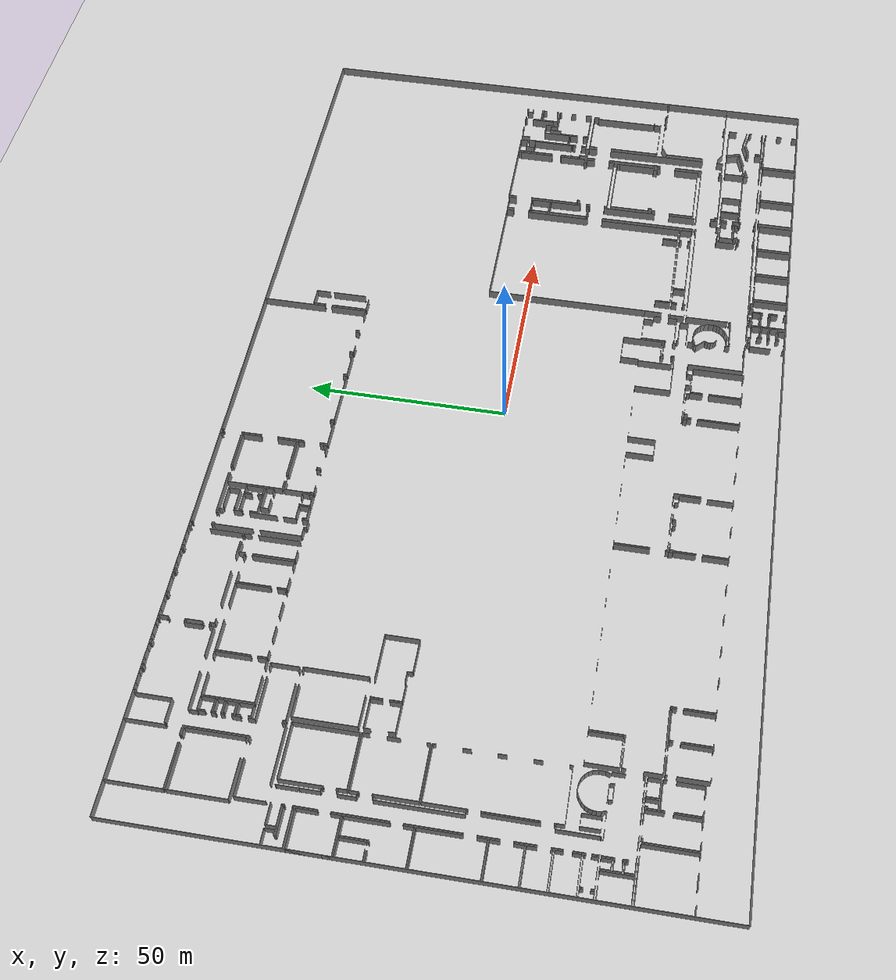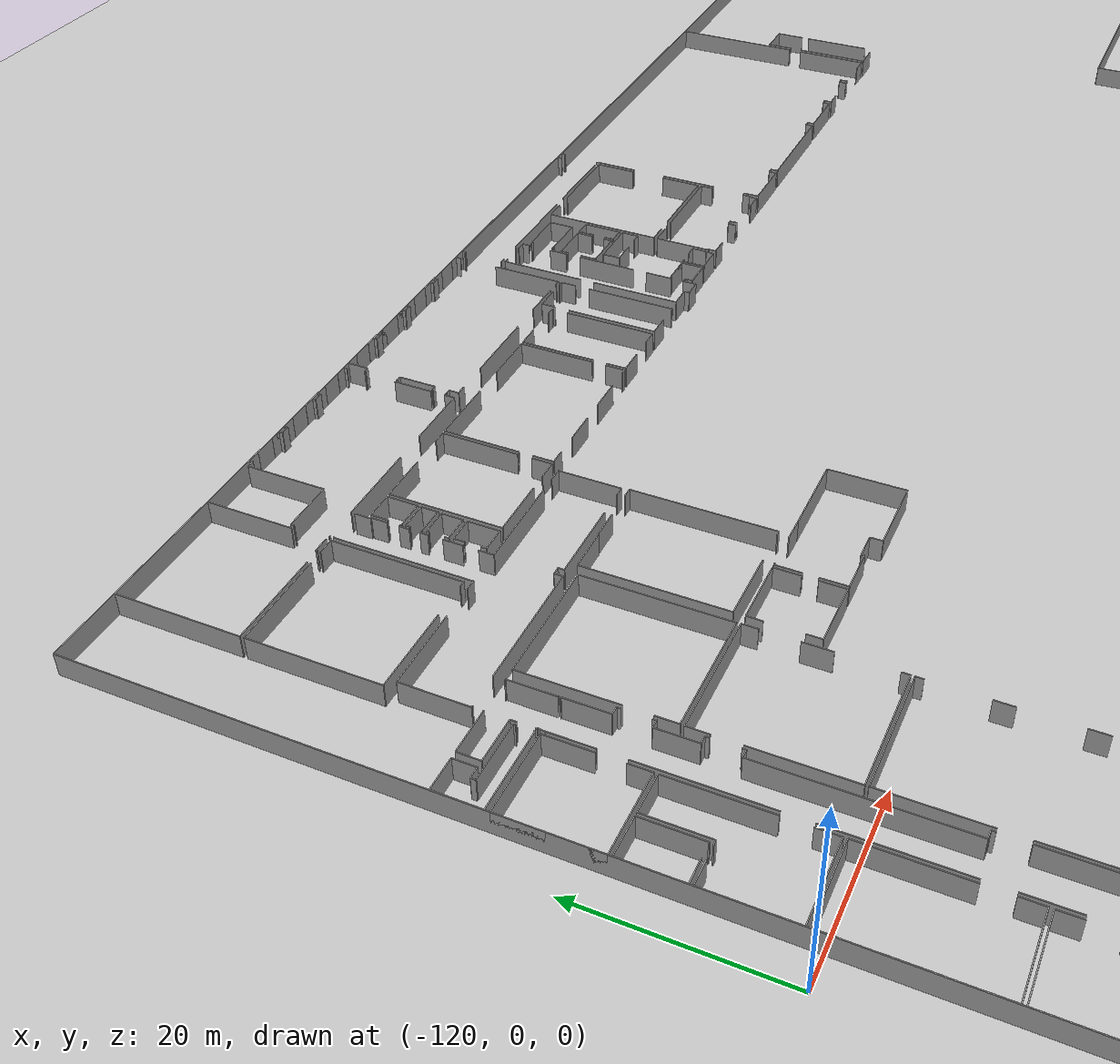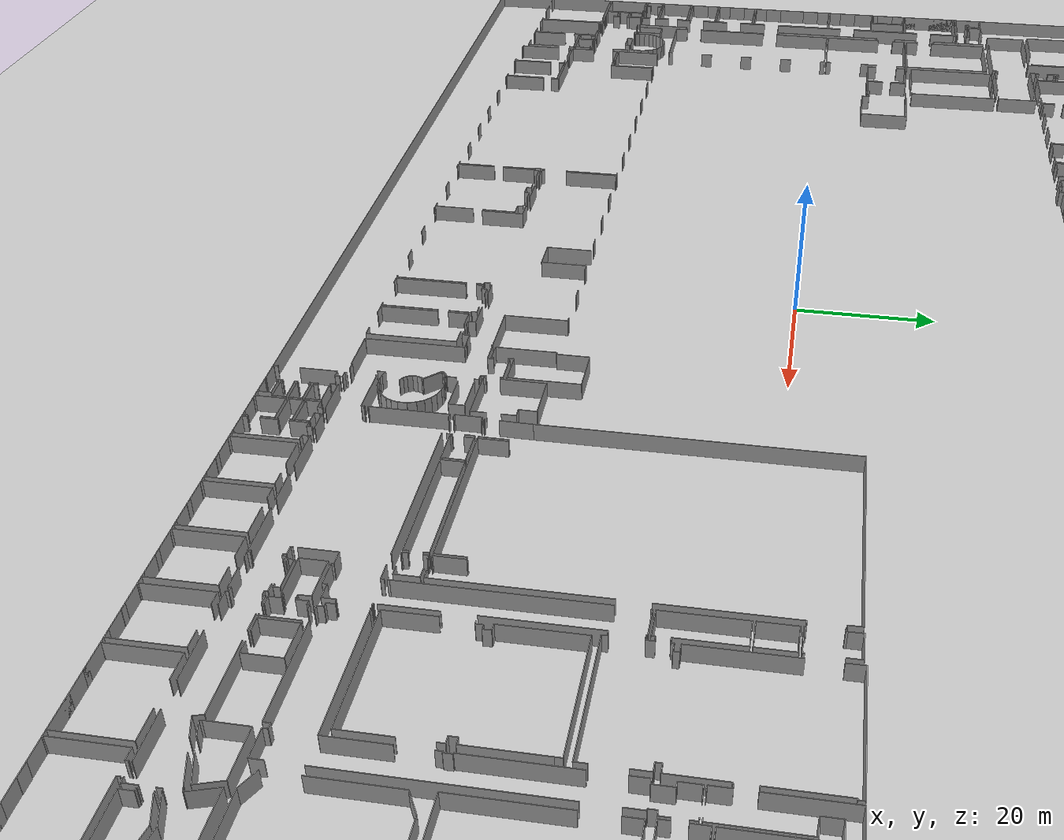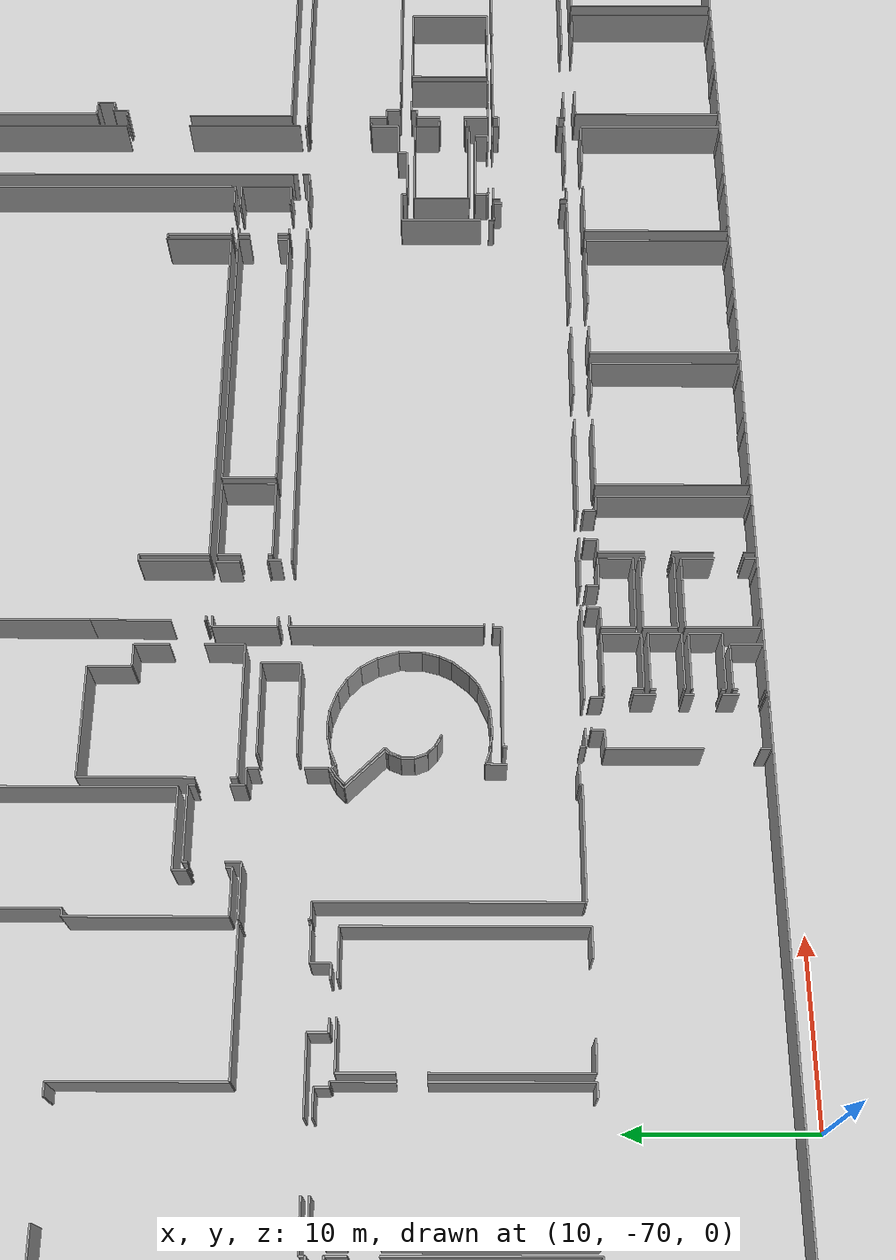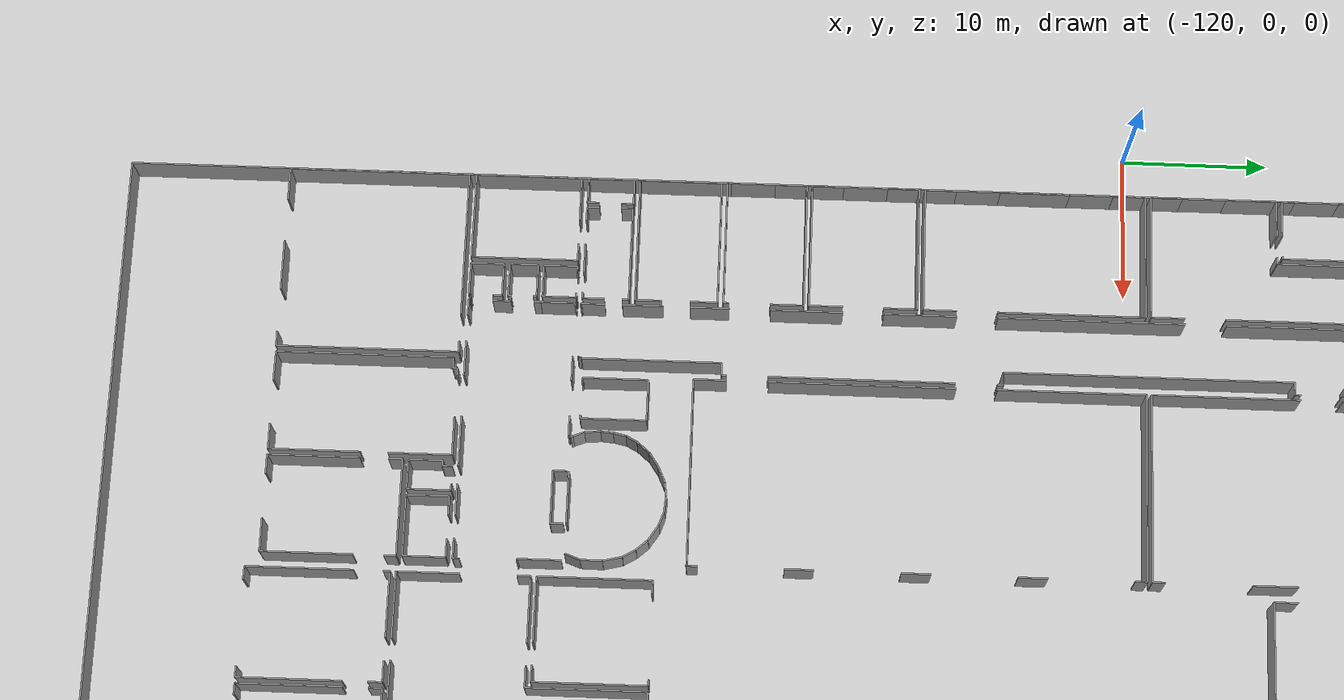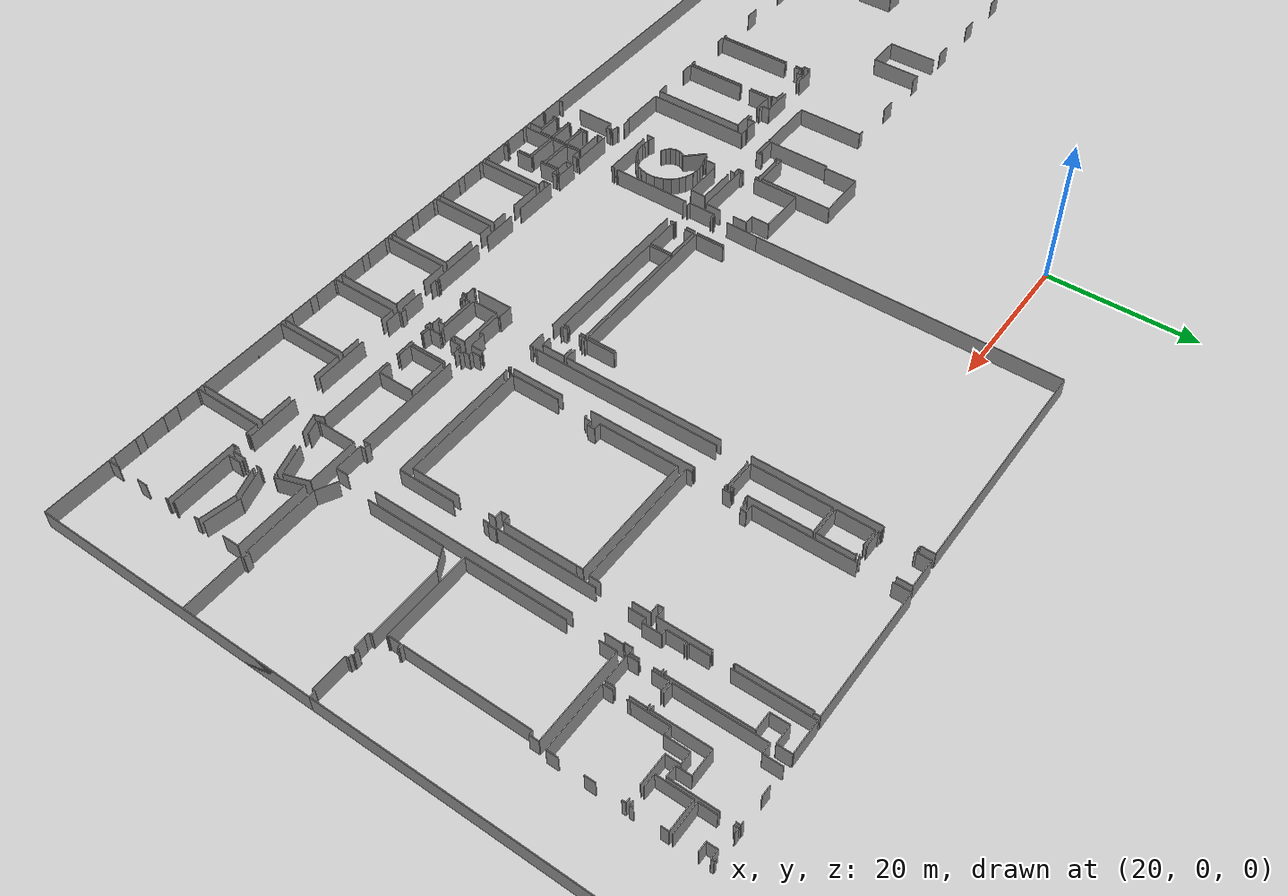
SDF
<sdf version="1.6">
  <world name="default">
    <light name="sun" type="directional">
      <cast_shadows>1</cast_shadows>
      <pose frame="">0 0 10 0 -0 0</pose>
      <diffuse>0.8 0.8 0.8 1</diffuse>
      <specular>0.1 0.1 0.1 1</specular>
      <attenuation>
        <range>1000</range>
        <constant>0.9</constant>
        <linear>0.01</linear>
        <quadratic>0.001</quadratic>
      </attenuation>
      <direction>-0.5 0.5 -1</direction>
    </light>
    <model name="ground_plane">
      <static>1</static>
      <link name="link">
        <collision name="collision">
          <geometry>
            <plane>
              <normal>0 0 1</normal>
              <size>100 100</size>
            </plane>
          </geometry>
          <surface>
            <friction>
              <ode>
                <mu>100</mu>
                <mu2>50</mu2>
              </ode>
              <torsional>
                <ode />
              </torsional>
            </friction>
            <contact>
              <ode />
            </contact>
            <bounce />
          </surface>
          <max_contacts>10</max_contacts>
        </collision>
        <visual name="visual">
          <cast_shadows>0</cast_shadows>
          <geometry>
            <plane>
              <normal>0 0 1</normal>
              <size>100 100</size>
            </plane>
          </geometry>
          <material>
            <script>
              <uri>file://media/materials/scripts/gazebo.material</uri>
              <name>Gazebo/Grey</name>
            </script>
          </material>
        </visual>
        <self_collide>0</self_collide>
        <kinematic>0</kinematic>
        <gravity>1</gravity>
      </link>
    </model>
    <gravity>0 0 -9.8</gravity>
    <magnetic_field>6e-06 2.3e-05 -4.2e-05</magnetic_field>
    <atmosphere type="adiabatic" />
    <physics default="0" name="default_physics" type="ode">
      <max_step_size>0.001</max_step_size>
      <real_time_factor>1</real_time_factor>
      <real_time_update_rate>1000</real_time_update_rate>
    </physics>
    <scene>
      <ambient>0.4 0.4 0.4 1</ambient>
      <background>0.7 0.7 0.7 1</background>
      <shadows>1</shadows>
    </scene>
    <spherical_coordinates>
      <surface_model>EARTH_WGS84</surface_model>
      <latitude_deg>0</latitude_deg>
      <longitude_deg>0</longitude_deg>
      <elevation>0</elevation>
      <heading_deg>0</heading_deg>
    </spherical_coordinates>
  <model name="0510035519_A_40_1_102">
		<static>1</static>
		<link name="Wall_0">
			<collision name="Wall_0_Collision">
				<geometry>
					<box>
						<size>13.2230270682 0.1 2.5</size>
					</box>
				</geometry>
				<pose frame="">6.61151353412 0 1.25 0 0 0</pose>
			</collision>
			<visual name="Wall_0_Visual">
				<pose frame="">6.61151353412 0 1.25 0 0 0</pose>
				<geometry>
					<box>
						<size>13.2230270682 0.1 2.5</size>
					</box>
				</geometry>
				<material>
					<script>
						<uri>file://media/materials/scripts/gazebo.material</uri>
						<name>Gazebo/Grey</name>
					</script>
					<ambient>1 1 1 1</ambient>
				</material>
			</visual>
			<pose frame="">8.17765916889 -13.2367518109 0 0 0 1.57079632679</pose>
		</link>
		<link name="Wall_1">
			<collision name="Wall_1_Collision">
				<geometry>
					<box>
						<size>13.8947769729 0.1 2.5</size>
					</box>
				</geometry>
				<pose frame="">6.94738848647 0 1.25 0 0 0</pose>
			</collision>
			<visual name="Wall_1_Visual">
				<pose frame="">6.94738848647 0 1.25 0 0 0</pose>
				<geometry>
					<box>
						<size>13.8947769729 0.1 2.5</size>
					</box>
				</geometry>
				<material>
					<script>
						<uri>file://media/materials/scripts/gazebo.material</uri>
						<name>Gazebo/Grey</name>
					</script>
					<ambient>1 1 1 1</ambient>
				</material>
			</visual>
			<pose frame="">8.17765916889 -0.0137247426611 0 0 0 0.0</pose>
		</link>
		<link name="Wall_2">
			<collision name="Wall_2_Collision">
				<geometry>
					<box>
						<size>9.35010801881 0.1 2.5</size>
					</box>
				</geometry>
				<pose frame="">4.6750540094 0 1.25 0 0 0</pose>
			</collision>
			<visual name="Wall_2_Visual">
				<pose frame="">4.6750540094 0 1.25 0 0 0</pose>
				<geometry>
					<box>
						<size>9.35010801881 0.1 2.5</size>
					</box>
				</geometry>
				<material>
					<script>
						<uri>file://media/materials/scripts/gazebo.material</uri>
						<name>Gazebo/Grey</name>
					</script>
					<ambient>1 1 1 1</ambient>
				</material>
			</visual>
			<pose frame="">22.0724361418 -0.0137247426611 0 0 0 -1.57079632679</pose>
		</link>
		<link name="Wall_3">
			<collision name="Wall_3_Collision">
				<geometry>
					<box>
						<size>1.75600457491 0.1 2.5</size>
					</box>
				</geometry>
				<pose frame="">0.878002287457 0 1.25 0 0 0</pose>
			</collision>
			<visual name="Wall_3_Visual">
				<pose frame="">0.878002287457 0 1.25 0 0 0</pose>
				<geometry>
					<box>
						<size>1.75600457491 0.1 2.5</size>
					</box>
				</geometry>
				<material>
					<script>
						<uri>file://media/materials/scripts/gazebo.material</uri>
						<name>Gazebo/Grey</name>
					</script>
					<ambient>1 1 1 1</ambient>
				</material>
			</visual>
			<pose frame="">22.0724361418 -13.141441098 0 0 0 3.14159265359</pose>
		</link>
		<link name="Wall_4">
			<collision name="Wall_4_Collision">
				<geometry>
					<box>
						<size>0.158851188207 0.1 2.5</size>
					</box>
				</geometry>
				<pose frame="">0.0794255941034 0 1.25 0 0 0</pose>
			</collision>
			<visual name="Wall_4_Visual">
				<pose frame="">0.0794255941034 0 1.25 0 0 0</pose>
				<geometry>
					<box>
						<size>0.158851188207 0.1 2.5</size>
					</box>
				</geometry>
				<material>
					<script>
						<uri>file://media/materials/scripts/gazebo.material</uri>
						<name>Gazebo/Grey</name>
					</script>
					<ambient>1 1 1 1</ambient>
				</material>
			</visual>
			<pose frame="">20.3164315669 -13.141441098 0 0 0 -1.57079632679</pose>
		</link>
		<link name="Wall_5">
			<collision name="Wall_5_Collision">
				<geometry>
					<box>
						<size>10.459463559 0.1 2.5</size>
					</box>
				</geometry>
				<pose frame="">5.2297317795 0 1.25 0 0 0</pose>
			</collision>
			<visual name="Wall_5_Visual">
				<pose frame="">5.2297317795 0 1.25 0 0 0</pose>
				<geometry>
					<box>
						<size>10.459463559 0.1 2.5</size>
					</box>
				</geometry>
				<material>
					<script>
						<uri>file://media/materials/scripts/gazebo.material</uri>
						<name>Gazebo/Grey</name>
					</script>
					<ambient>1 1 1 1</ambient>
				</material>
			</visual>
			<pose frame="">18.6369297242 -13.3002922862 0 0 0 3.13551768944</pose>
		</link>
		<link name="Wall_6">
			<collision name="Wall_6_Collision">
				<geometry>
					<box>
						<size>8.61456347693 0.1 2.5</size>
					</box>
				</geometry>
				<pose frame="">4.30728173847 0 1.25 0 0 0</pose>
			</collision>
			<visual name="Wall_6_Visual">
				<pose frame="">4.30728173847 0 1.25 0 0 0</pose>
				<geometry>
					<box>
						<size>8.61456347693 0.1 2.5</size>
					</box>
				</geometry>
				<material>
					<script>
						<uri>file://media/materials/scripts/gazebo.material</uri>
						<name>Gazebo/Grey</name>
					</script>
					<ambient>1 1 1 1</ambient>
				</material>
			</visual>
			<pose frame="">28.1840132164 -9.02173084255 0 0 0 1.57079632679</pose>
		</link>
		<link name="Wall_7">
			<collision name="Wall_7_Collision">
				<geometry>
					<box>
						<size>0.784597788791 0.1 2.5</size>
					</box>
				</geometry>
				<pose frame="">0.392298894396 0 1.25 0 0 0</pose>
			</collision>
			<visual name="Wall_7_Visual">
				<pose frame="">0.392298894396 0 1.25 0 0 0</pose>
				<geometry>
					<box>
						<size>0.784597788791 0.1 2.5</size>
					</box>
				</geometry>
				<material>
					<script>
						<uri>file://media/materials/scripts/gazebo.material</uri>
						<name>Gazebo/Grey</name>
					</script>
					<ambient>1 1 1 1</ambient>
				</material>
			</visual>
			<pose frame="">28.1840132164 -0.407167365612 0 0 0 0.0</pose>
		</link>
		<link name="Wall_8">
			<collision name="Wall_8_Collision">
				<geometry>
					<box>
						<size>0.407167365612 0.1 2.5</size>
					</box>
				</geometry>
				<pose frame="">0.203583682806 0 1.25 0 0 0</pose>
			</collision>
			<visual name="Wall_8_Visual">
				<pose frame="">0.203583682806 0 1.25 0 0 0</pose>
				<geometry>
					<box>
						<size>0.407167365612 0.1 2.5</size>
					</box>
				</geometry>
				<material>
					<script>
						<uri>file://media/materials/scripts/gazebo.material</uri>
						<name>Gazebo/Grey</name>
					</script>
					<ambient>1 1 1 1</ambient>
				</material>
			</visual>
			<pose frame="">28.9686110052 -0.407167365612 0 0 0 1.57079632679</pose>
		</link>
		<link name="Wall_9">
			<collision name="Wall_9_Collision">
				<geometry>
					<box>
						<size>1.45380607447 0.1 2.5</size>
					</box>
				</geometry>
				<pose frame="">0.726903037235 0 1.25 0 0 0</pose>
			</collision>
			<visual name="Wall_9_Visual">
				<pose frame="">0.726903037235 0 1.25 0 0 0</pose>
				<geometry>
					<box>
						<size>1.45380607447 0.1 2.5</size>
					</box>
				</geometry>
				<material>
					<script>
						<uri>file://media/materials/scripts/gazebo.material</uri>
						<name>Gazebo/Grey</name>
					</script>
					<ambient>1 1 1 1</ambient>
				</material>
			</visual>
			<pose frame="">28.9686110052 -0.0 0 0 0 0.0</pose>
		</link>
		<link name="Wall_10">
			<collision name="Wall_10_Collision">
				<geometry>
					<box>
						<size>1.26293048672 0.1 2.5</size>
					</box>
				</geometry>
				<pose frame="">0.63146524336 0 1.25 0 0 0</pose>
			</collision>
			<visual name="Wall_10_Visual">
				<pose frame="">0.63146524336 0 1.25 0 0 0</pose>
				<geometry>
					<box>
						<size>1.26293048672 0.1 2.5</size>
					</box>
				</geometry>
				<material>
					<script>
						<uri>file://media/materials/scripts/gazebo.material</uri>
						<name>Gazebo/Grey</name>
					</script>
					<ambient>1 1 1 1</ambient>
				</material>
			</visual>
			<pose frame="">32.8486465879 -0.0 0 0 0 0.0</pose>
		</link>
		<link name="Wall_11">
			<collision name="Wall_11_Collision">
				<geometry>
					<box>
						<size>0.415554708349 0.1 2.5</size>
					</box>
				</geometry>
				<pose frame="">0.207777354175 0 1.25 0 0 0</pose>
			</collision>
			<visual name="Wall_11_Visual">
				<pose frame="">0.207777354175 0 1.25 0 0 0</pose>
				<geometry>
					<box>
						<size>0.415554708349 0.1 2.5</size>
					</box>
				</geometry>
				<material>
					<script>
						<uri>file://media/materials/scripts/gazebo.material</uri>
						<name>Gazebo/Grey</name>
					</script>
					<ambient>1 1 1 1</ambient>
				</material>
			</visual>
			<pose frame="">34.1115770746 -0.0 0 0 0 -1.57079632679</pose>
		</link>
		<link name="Wall_12">
			<collision name="Wall_12_Collision">
				<geometry>
					<box>
						<size>0.963781929089 0.1 2.5</size>
					</box>
				</geometry>
				<pose frame="">0.481890964544 0 1.25 0 0 0</pose>
			</collision>
			<visual name="Wall_12_Visual">
				<pose frame="">0.481890964544 0 1.25 0 0 0</pose>
				<geometry>
					<box>
						<size>0.963781929089 0.1 2.5</size>
					</box>
				</geometry>
				<material>
					<script>
						<uri>file://media/materials/scripts/gazebo.material</uri>
						<name>Gazebo/Grey</name>
					</script>
					<ambient>1 1 1 1</ambient>
				</material>
			</visual>
			<pose frame="">34.1115770746 -0.415554708349 0 0 0 0.0</pose>
		</link>
		<link name="Wall_13">
			<collision name="Wall_13_Collision">
				<geometry>
					<box>
						<size>0.398780022875 0.1 2.5</size>
					</box>
				</geometry>
				<pose frame="">0.199390011437 0 1.25 0 0 0</pose>
			</collision>
			<visual name="Wall_13_Visual">
				<pose frame="">0.199390011437 0 1.25 0 0 0</pose>
				<geometry>
					<box>
						<size>0.398780022875 0.1 2.5</size>
					</box>
				</geometry>
				<material>
					<script>
						<uri>file://media/materials/scripts/gazebo.material</uri>
						<name>Gazebo/Grey</name>
					</script>
					<ambient>1 1 1 1</ambient>
				</material>
			</visual>
			<pose frame="">35.0753590037 -0.415554708349 0 0 0 1.57079632679</pose>
		</link>
		<link name="Wall_14">
			<collision name="Wall_14_Collision">
				<geometry>
					<box>
						<size>1.44567289363 0.1 2.5</size>
					</box>
				</geometry>
				<pose frame="">0.722836446817 0 1.25 0 0 0</pose>
			</collision>
			<visual name="Wall_14_Visual">
				<pose frame="">0.722836446817 0 1.25 0 0 0</pose>
				<geometry>
					<box>
						<size>1.44567289363 0.1 2.5</size>
					</box>
				</geometry>
				<material>
					<script>
						<uri>file://media/materials/scripts/gazebo.material</uri>
						<name>Gazebo/Grey</name>
					</script>
					<ambient>1 1 1 1</ambient>
				</material>
			</visual>
			<pose frame="">35.0753590037 -0.0167746854746 0 0 0 0.0</pose>
		</link>
		<link name="Wall_15">
			<collision name="Wall_15_Collision">
				<geometry>
					<box>
						<size>1.32215020968 0.1 2.5</size>
					</box>
				</geometry>
				<pose frame="">0.661075104842 0 1.25 0 0 0</pose>
			</collision>
			<visual name="Wall_15_Visual">
				<pose frame="">0.661075104842 0 1.25 0 0 0</pose>
				<geometry>
					<box>
						<size>1.32215020968 0.1 2.5</size>
					</box>
				</geometry>
				<material>
					<script>
						<uri>file://media/materials/scripts/gazebo.material</uri>
						<name>Gazebo/Grey</name>
					</script>
					<ambient>1 1 1 1</ambient>
				</material>
			</visual>
			<pose frame="">38.8987164824 -0.0167746854746 0 0 0 0.0</pose>
		</link>
		<link name="Wall_16">
			<collision name="Wall_16_Collision">
				<geometry>
					<box>
						<size>0.391663489643 0.1 2.5</size>
					</box>
				</geometry>
				<pose frame="">0.195831744821 0 1.25 0 0 0</pose>
			</collision>
			<visual name="Wall_16_Visual">
				<pose frame="">0.195831744821 0 1.25 0 0 0</pose>
				<geometry>
					<box>
						<size>0.391663489643 0.1 2.5</size>
					</box>
				</geometry>
				<material>
					<script>
						<uri>file://media/materials/scripts/gazebo.material</uri>
						<name>Gazebo/Grey</name>
					</script>
					<ambient>1 1 1 1</ambient>
				</material>
			</visual>
			<pose frame="">40.2208666921 -0.0167746854746 0 0 0 -1.57079632679</pose>
		</link>
		<link name="Wall_17">
			<collision name="Wall_17_Collision">
				<geometry>
					<box>
						<size>0.980048290761 0.1 2.5</size>
					</box>
				</geometry>
				<pose frame="">0.490024145381 0 1.25 0 0 0</pose>
			</collision>
			<visual name="Wall_17_Visual">
				<pose frame="">0.490024145381 0 1.25 0 0 0</pose>
				<geometry>
					<box>
						<size>0.980048290761 0.1 2.5</size>
					</box>
				</geometry>
				<material>
					<script>
						<uri>file://media/materials/scripts/gazebo.material</uri>
						<name>Gazebo/Grey</name>
					</script>
					<ambient>1 1 1 1</ambient>
				</material>
			</visual>
			<pose frame="">40.2208666921 -0.408438175118 0 0 0 0.0</pose>
		</link>
		<link name="Wall_18">
			<collision name="Wall_18_Collision">
				<geometry>
					<box>
						<size>0.379972042191 0.1 2.5</size>
					</box>
				</geometry>
				<pose frame="">0.189986021095 0 1.25 0 0 0</pose>
			</collision>
			<visual name="Wall_18_Visual">
				<pose frame="">0.189986021095 0 1.25 0 0 0</pose>
				<geometry>
					<box>
						<size>0.379972042191 0.1 2.5</size>
					</box>
				</geometry>
				<material>
					<script>
						<uri>file://media/materials/scripts/gazebo.material</uri>
						<name>Gazebo/Grey</name>
					</script>
					<ambient>1 1 1 1</ambient>
				</material>
			</visual>
			<pose frame="">41.2009149828 -0.408438175118 0 0 0 1.57079632679</pose>
		</link>
		<link name="Wall_19">
			<collision name="Wall_19_Collision">
				<geometry>
					<box>
						<size>1.40653196086 0.1 2.5</size>
					</box>
				</geometry>
				<pose frame="">0.70326598043 0 1.25 0 0 0</pose>
			</collision>
			<visual name="Wall_19_Visual">
				<pose frame="">0.70326598043 0 1.25 0 0 0</pose>
				<geometry>
					<box>
						<size>1.40653196086 0.1 2.5</size>
					</box>
				</geometry>
				<material>
					<script>
						<uri>file://media/materials/scripts/gazebo.material</uri>
						<name>Gazebo/Grey</name>
					</script>
					<ambient>1 1 1 1</ambient>
				</material>
			</visual>
			<pose frame="">41.2009149828 -0.0284661329267 0 0 0 0.0</pose>
		</link>
		<link name="Wall_20">
			<collision name="Wall_20_Collision">
				<geometry>
					<box>
						<size>1.31096708603 0.1 2.5</size>
					</box>
				</geometry>
				<pose frame="">0.655483543017 0 1.25 0 0 0</pose>
			</collision>
			<visual name="Wall_20_Visual">
				<pose frame="">0.655483543017 0 1.25 0 0 0</pose>
				<geometry>
					<box>
						<size>1.31096708603 0.1 2.5</size>
					</box>
				</geometry>
				<material>
					<script>
						<uri>file://media/materials/scripts/gazebo.material</uri>
						<name>Gazebo/Grey</name>
					</script>
					<ambient>1 1 1 1</ambient>
				</material>
			</visual>
			<pose frame="">45.0202058711 -0.0284661329267 0 0 0 0.0</pose>
		</link>
		<link name="Wall_21">
			<collision name="Wall_21_Collision">
				<geometry>
					<box>
						<size>0.376159613674 0.1 2.5</size>
					</box>
				</geometry>
				<pose frame="">0.188079806837 0 1.25 0 0 0</pose>
			</collision>
			<visual name="Wall_21_Visual">
				<pose frame="">0.188079806837 0 1.25 0 0 0</pose>
				<geometry>
					<box>
						<size>0.376159613674 0.1 2.5</size>
					</box>
				</geometry>
				<material>
					<script>
						<uri>file://media/materials/scripts/gazebo.material</uri>
						<name>Gazebo/Grey</name>
					</script>
					<ambient>1 1 1 1</ambient>
				</material>
			</visual>
			<pose frame="">46.3311729572 -0.0284661329267 0 0 0 -1.57079632679</pose>
		</link>
		<link name="Wall_22">
			<collision name="Wall_22_Collision">
				<geometry>
					<box>
						<size>4.28186554835 0.1 2.5</size>
					</box>
				</geometry>
				<pose frame="">2.14093277418 0 1.25 0 0 0</pose>
			</collision>
			<visual name="Wall_22_Visual">
				<pose frame="">2.14093277418 0 1.25 0 0 0</pose>
				<geometry>
					<box>
						<size>4.28186554835 0.1 2.5</size>
					</box>
				</geometry>
				<material>
					<script>
						<uri>file://media/materials/scripts/gazebo.material</uri>
						<name>Gazebo/Grey</name>
					</script>
					<ambient>1 1 1 1</ambient>
				</material>
			</visual>
			<pose frame="">46.3311729572 -6.22315414919 0 0 0 -1.57079632679</pose>
		</link>
		<link name="Wall_23">
			<collision name="Wall_23_Collision">
				<geometry>
					<box>
						<size>1.13330791714 0.1 2.5</size>
					</box>
				</geometry>
				<pose frame="">0.566653958572 0 1.25 0 0 0</pose>
			</collision>
			<visual name="Wall_23_Visual">
				<pose frame="">0.566653958572 0 1.25 0 0 0</pose>
				<geometry>
					<box>
						<size>1.13330791714 0.1 2.5</size>
					</box>
				</geometry>
				<material>
					<script>
						<uri>file://media/materials/scripts/gazebo.material</uri>
						<name>Gazebo/Grey</name>
					</script>
					<ambient>1 1 1 1</ambient>
				</material>
			</visual>
			<pose frame="">46.3311729572 -12.1092896175 0 0 0 -1.57079632679</pose>
		</link>
		<link name="Wall_24">
			<collision name="Wall_24_Collision">
				<geometry>
					<box>
						<size>7.2352268395 0.1 2.5</size>
					</box>
				</geometry>
				<pose frame="">3.61761341975 0 1.25 0 0 0</pose>
			</collision>
			<visual name="Wall_24_Visual">
				<pose frame="">3.61761341975 0 1.25 0 0 0</pose>
				<geometry>
					<box>
						<size>7.2352268395 0.1 2.5</size>
					</box>
				</geometry>
				<material>
					<script>
						<uri>file://media/materials/scripts/gazebo.material</uri>
						<name>Gazebo/Grey</name>
					</script>
					<ambient>1 1 1 1</ambient>
				</material>
			</visual>
			<pose frame="">46.3311729572 -13.2425975346 0 0 0 3.14159265359</pose>
		</link>
		<link name="Wall_25">
			<collision name="Wall_25_Collision">
				<geometry>
					<box>
						<size>9.1907485068 0.1 2.5</size>
					</box>
				</geometry>
				<pose frame="">4.5953742534 0 1.25 0 0 0</pose>
			</collision>
			<visual name="Wall_25_Visual">
				<pose frame="">4.5953742534 0 1.25 0 0 0</pose>
				<geometry>
					<box>
						<size>9.1907485068 0.1 2.5</size>
					</box>
				</geometry>
				<material>
					<script>
						<uri>file://media/materials/scripts/gazebo.material</uri>
						<name>Gazebo/Grey</name>
					</script>
					<ambient>1 1 1 1</ambient>
				</material>
			</visual>
			<pose frame="">35.4339814462 -13.2425975346 0 0 0 3.14159265359</pose>
		</link>
		<link name="Wall_26">
			<collision name="Wall_26_Collision">
				<geometry>
					<box>
						<size>0.172067607066 0.1 2.5</size>
					</box>
				</geometry>
				<pose frame="">0.0860338035328 0 1.25 0 0 0</pose>
			</collision>
			<visual name="Wall_26_Visual">
				<pose frame="">0.0860338035328 0 1.25 0 0 0</pose>
				<geometry>
					<box>
						<size>0.172067607066 0.1 2.5</size>
					</box>
				</geometry>
				<material>
					<script>
						<uri>file://media/materials/scripts/gazebo.material</uri>
						<name>Gazebo/Grey</name>
					</script>
					<ambient>1 1 1 1</ambient>
				</material>
			</visual>
			<pose frame="">22.5934680391 -13.2425975346 0 0 0 3.14159265359</pose>
		</link>
		<link name="Wall_27">
			<collision name="Wall_27_Collision">
				<geometry>
					<box>
						<size>0.0663362561952 0.1 2.5</size>
					</box>
				</geometry>
				<pose frame="">0.0331681280976 0 1.25 0 0 0</pose>
			</collision>
			<visual name="Wall_27_Visual">
				<pose frame="">0.0331681280976 0 1.25 0 0 0</pose>
				<geometry>
					<box>
						<size>0.0663362561952 0.1 2.5</size>
					</box>
				</geometry>
				<material>
					<script>
						<uri>file://media/materials/scripts/gazebo.material</uri>
						<name>Gazebo/Grey</name>
					</script>
					<ambient>1 1 1 1</ambient>
				</material>
			</visual>
			<pose frame="">22.4214004321 -9.38060744694 0 0 0 0.0</pose>
		</link>
		<link name="Wall_28">
			<collision name="Wall_28_Collision">
				<geometry>
					<box>
						<size>0.35735163299 0.1 2.5</size>
					</box>
				</geometry>
				<pose frame="">0.178675816495 0 1.25 0 0 0</pose>
			</collision>
			<visual name="Wall_28_Visual">
				<pose frame="">0.178675816495 0 1.25 0 0 0</pose>
				<geometry>
					<box>
						<size>0.35735163299 0.1 2.5</size>
					</box>
				</geometry>
				<material>
					<script>
						<uri>file://media/materials/scripts/gazebo.material</uri>
						<name>Gazebo/Grey</name>
					</script>
					<ambient>1 1 1 1</ambient>
				</material>
			</visual>
			<pose frame="">22.4877366883 -9.38060744694 0 0 0 1.57079632679</pose>
		</link>
		<link name="Wall_29">
			<collision name="Wall_29_Collision">
				<geometry>
					<box>
						<size>5.69627673228 0.1 2.5</size>
					</box>
				</geometry>
				<pose frame="">2.84813836614 0 1.25 0 0 0</pose>
			</collision>
			<visual name="Wall_29_Visual">
				<pose frame="">2.84813836614 0 1.25 0 0 0</pose>
				<geometry>
					<box>
						<size>5.69627673228 0.1 2.5</size>
					</box>
				</geometry>
				<material>
					<script>
						<uri>file://media/materials/scripts/gazebo.material</uri>
						<name>Gazebo/Grey</name>
					</script>
					<ambient>1 1 1 1</ambient>
				</material>
			</visual>
			<pose frame="">22.4877366883 -9.02325581395 0 0 0 0.000267713718394</pose>
		</link>
		<link name="Wall_30">
			<collision name="Wall_30_Collision">
				<geometry>
					<box>
						<size>2.35582666158 0.1 2.5</size>
					</box>
				</geometry>
				<pose frame="">1.17791333079 0 1.25 0 0 0</pose>
			</collision>
			<visual name="Wall_30_Visual">
				<pose frame="">1.17791333079 0 1.25 0 0 0</pose>
				<geometry>
					<box>
						<size>2.35582666158 0.1 2.5</size>
					</box>
				</geometry>
				<material>
					<script>
						<uri>file://media/materials/scripts/gazebo.material</uri>
						<name>Gazebo/Grey</name>
					</script>
					<ambient>1 1 1 1</ambient>
				</material>
			</visual>
			<pose frame="">47.2703011819 -2.36294319482 0 0 0 1.57079632679</pose>
		</link>
		<link name="Wall_31">
			<collision name="Wall_31_Collision">
				<geometry>
					<box>
						<size>1.5511500826 0.1 2.5</size>
					</box>
				</geometry>
				<pose frame="">0.775575041301 0 1.25 0 0 0</pose>
			</collision>
			<visual name="Wall_31_Visual">
				<pose frame="">0.775575041301 0 1.25 0 0 0</pose>
				<geometry>
					<box>
						<size>1.5511500826 0.1 2.5</size>
					</box>
				</geometry>
				<material>
					<script>
						<uri>file://media/materials/scripts/gazebo.material</uri>
						<name>Gazebo/Grey</name>
					</script>
					<ambient>1 1 1 1</ambient>
				</material>
			</visual>
			<pose frame="">47.2703011819 -0.00711653323167 0 0 0 0.0</pose>
		</link>
		<link name="Wall_32">
			<collision name="Wall_32_Collision">
				<geometry>
					<box>
						<size>1.20396492566 0.1 2.5</size>
					</box>
				</geometry>
				<pose frame="">0.601982462829 0 1.25 0 0 0</pose>
			</collision>
			<visual name="Wall_32_Visual">
				<pose frame="">0.601982462829 0 1.25 0 0 0</pose>
				<geometry>
					<box>
						<size>1.20396492566 0.1 2.5</size>
					</box>
				</geometry>
				<material>
					<script>
						<uri>file://media/materials/scripts/gazebo.material</uri>
						<name>Gazebo/Grey</name>
					</script>
					<ambient>1 1 1 1</ambient>
				</material>
			</visual>
			<pose frame="">51.2197229635 -0.00711653323167 0 0 0 0.0</pose>
		</link>
		<link name="Wall_33">
			<collision name="Wall_33_Collision">
				<geometry>
					<box>
						<size>0.383530308807 0.1 2.5</size>
					</box>
				</geometry>
				<pose frame="">0.191765154403 0 1.25 0 0 0</pose>
			</collision>
			<visual name="Wall_33_Visual">
				<pose frame="">0.191765154403 0 1.25 0 0 0</pose>
				<geometry>
					<box>
						<size>0.383530308807 0.1 2.5</size>
					</box>
				</geometry>
				<material>
					<script>
						<uri>file://media/materials/scripts/gazebo.material</uri>
						<name>Gazebo/Grey</name>
					</script>
					<ambient>1 1 1 1</ambient>
				</material>
			</visual>
			<pose frame="">52.4236878892 -0.00711653323167 0 0 0 -1.57079632679</pose>
		</link>
		<link name="Wall_34">
			<collision name="Wall_34_Collision">
				<geometry>
					<box>
						<size>1.01359766171 0.1 2.5</size>
					</box>
				</geometry>
				<pose frame="">0.506798830855 0 1.25 0 0 0</pose>
			</collision>
			<visual name="Wall_34_Visual">
				<pose frame="">0.506798830855 0 1.25 0 0 0</pose>
				<geometry>
					<box>
						<size>1.01359766171 0.1 2.5</size>
					</box>
				</geometry>
				<material>
					<script>
						<uri>file://media/materials/scripts/gazebo.material</uri>
						<name>Gazebo/Grey</name>
					</script>
					<ambient>1 1 1 1</ambient>
				</material>
			</visual>
			<pose frame="">52.4236878892 -0.390646842038 0 0 0 0.0</pose>
		</link>
		<link name="Wall_35">
			<collision name="Wall_35_Collision">
				<geometry>
					<box>
						<size>0.390646842038 0.1 2.5</size>
					</box>
				</geometry>
				<pose frame="">0.195323421019 0 1.25 0 0 0</pose>
			</collision>
			<visual name="Wall_35_Visual">
				<pose frame="">0.195323421019 0 1.25 0 0 0</pose>
				<geometry>
					<box>
						<size>0.390646842038 0.1 2.5</size>
					</box>
				</geometry>
				<material>
					<script>
						<uri>file://media/materials/scripts/gazebo.material</uri>
						<name>Gazebo/Grey</name>
					</script>
					<ambient>1 1 1 1</ambient>
				</material>
			</visual>
			<pose frame="">53.4372855509 -0.390646842038 0 0 0 1.57079632679</pose>
		</link>
		<link name="Wall_36">
			<collision name="Wall_36_Collision">
				<geometry>
					<box>
						<size>1.44567289363 0.1 2.5</size>
					</box>
				</geometry>
				<pose frame="">0.722836446817 0 1.25 0 0 0</pose>
			</collision>
			<visual name="Wall_36_Visual">
				<pose frame="">0.722836446817 0 1.25 0 0 0</pose>
				<geometry>
					<box>
						<size>1.44567289363 0.1 2.5</size>
					</box>
				</geometry>
				<material>
					<script>
						<uri>file://media/materials/scripts/gazebo.material</uri>
						<name>Gazebo/Grey</name>
					</script>
					<ambient>1 1 1 1</ambient>
				</material>
			</visual>
			<pose frame="">53.4372855509 -0.0 0 0 0 0.0</pose>
		</link>
		<link name="Wall_37">
			<collision name="Wall_37_Collision">
				<geometry>
					<box>
						<size>1.169653069 0.1 2.5</size>
					</box>
				</geometry>
				<pose frame="">0.584826534502 0 1.25 0 0 0</pose>
			</collision>
			<visual name="Wall_37_Visual">
				<pose frame="">0.584826534502 0 1.25 0 0 0</pose>
				<geometry>
					<box>
						<size>1.169653069 0.1 2.5</size>
					</box>
				</geometry>
				<material>
					<script>
						<uri>file://media/materials/scripts/gazebo.material</uri>
						<name>Gazebo/Grey</name>
					</script>
					<ambient>1 1 1 1</ambient>
				</material>
			</visual>
			<pose frame="">57.3590036853 -0.0 0 0 0 0.0</pose>
		</link>
		<link name="Wall_38">
			<collision name="Wall_38_Collision">
				<geometry>
					<box>
						<size>0.404117422798 0.1 2.5</size>
					</box>
				</geometry>
				<pose frame="">0.202058711399 0 1.25 0 0 0</pose>
			</collision>
			<visual name="Wall_38_Visual">
				<pose frame="">0.202058711399 0 1.25 0 0 0</pose>
				<geometry>
					<box>
						<size>0.404117422798 0.1 2.5</size>
					</box>
				</geometry>
				<material>
					<script>
						<uri>file://media/materials/scripts/gazebo.material</uri>
						<name>Gazebo/Grey</name>
					</script>
					<ambient>1 1 1 1</ambient>
				</material>
			</visual>
			<pose frame="">58.5286567544 -0.0 0 0 0 -1.57079632679</pose>
		</link>
		<link name="Wall_39">
			<collision name="Wall_39_Collision">
				<geometry>
					<box>
						<size>0.989960604905 0.1 2.5</size>
					</box>
				</geometry>
				<pose frame="">0.494980302453 0 1.25 0 0 0</pose>
			</collision>
			<visual name="Wall_39_Visual">
				<pose frame="">0.494980302453 0 1.25 0 0 0</pose>
				<geometry>
					<box>
						<size>0.989960604905 0.1 2.5</size>
					</box>
				</geometry>
				<material>
					<script>
						<uri>file://media/materials/scripts/gazebo.material</uri>
						<name>Gazebo/Grey</name>
					</script>
					<ambient>1 1 1 1</ambient>
				</material>
			</visual>
			<pose frame="">58.5286567544 -0.404117422798 0 0 0 0.0</pose>
		</link>
		<link name="Wall_40">
			<collision name="Wall_40_Collision">
				<geometry>
					<box>
						<size>0.390392680137 0.1 2.5</size>
					</box>
				</geometry>
				<pose frame="">0.195196340069 0 1.25 0 0 0</pose>
			</collision>
			<visual name="Wall_40_Visual">
				<pose frame="">0.195196340069 0 1.25 0 0 0</pose>
				<geometry>
					<box>
						<size>0.390392680137 0.1 2.5</size>
					</box>
				</geometry>
				<material>
					<script>
						<uri>file://media/materials/scripts/gazebo.material</uri>
						<name>Gazebo/Grey</name>
					</script>
					<ambient>1 1 1 1</ambient>
				</material>
			</visual>
			<pose frame="">59.5186173593 -0.404117422798 0 0 0 1.57079632679</pose>
		</link>
		<link name="Wall_41">
			<collision name="Wall_41_Collision">
				<geometry>
					<box>
						<size>1.60426991994 0.1 2.5</size>
					</box>
				</geometry>
				<pose frame="">0.80213495997 0 1.25 0 0 0</pose>
			</collision>
			<visual name="Wall_41_Visual">
				<pose frame="">0.80213495997 0 1.25 0 0 0</pose>
				<geometry>
					<box>
						<size>1.60426991994 0.1 2.5</size>
					</box>
				</geometry>
				<material>
					<script>
						<uri>file://media/materials/scripts/gazebo.material</uri>
						<name>Gazebo/Grey</name>
					</script>
					<ambient>1 1 1 1</ambient>
				</material>
			</visual>
			<pose frame="">59.5186173593 -0.0137247426611 0 0 0 0.0</pose>
		</link>
		<link name="Wall_42">
			<collision name="Wall_42_Collision">
				<geometry>
					<box>
						<size>1.26369297242 0.1 2.5</size>
					</box>
				</geometry>
				<pose frame="">0.631846486212 0 1.25 0 0 0</pose>
			</collision>
			<visual name="Wall_42_Visual">
				<pose frame="">0.631846486212 0 1.25 0 0 0</pose>
				<geometry>
					<box>
						<size>1.26369297242 0.1 2.5</size>
					</box>
				</geometry>
				<material>
					<script>
						<uri>file://media/materials/scripts/gazebo.material</uri>
						<name>Gazebo/Grey</name>
					</script>
					<ambient>1 1 1 1</ambient>
				</material>
			</visual>
			<pose frame="">63.565637311 -0.0137247426611 0 0 0 0.0</pose>
		</link>
		<link name="Wall_43">
			<collision name="Wall_43_Collision">
				<geometry>
					<box>
						<size>0.404371584699 0.1 2.5</size>
					</box>
				</geometry>
				<pose frame="">0.20218579235 0 1.25 0 0 0</pose>
			</collision>
			<visual name="Wall_43_Visual">
				<pose frame="">0.20218579235 0 1.25 0 0 0</pose>
				<geometry>
					<box>
						<size>0.404371584699 0.1 2.5</size>
					</box>
				</geometry>
				<material>
					<script>
						<uri>file://media/materials/scripts/gazebo.material</uri>
						<name>Gazebo/Grey</name>
					</script>
					<ambient>1 1 1 1</ambient>
				</material>
			</visual>
			<pose frame="">64.8293302834 -0.0137247426611 0 0 0 -1.57079632679</pose>
		</link>
		<link name="Wall_44">
			<collision name="Wall_44_Collision">
				<geometry>
					<box>
						<size>0.988943957301 0.1 2.5</size>
					</box>
				</geometry>
				<pose frame="">0.49447197865 0 1.25 0 0 0</pose>
			</collision>
			<visual name="Wall_44_Visual">
				<pose frame="">0.49447197865 0 1.25 0 0 0</pose>
				<geometry>
					<box>
						<size>0.988943957301 0.1 2.5</size>
					</box>
				</geometry>
				<material>
					<script>
						<uri>file://media/materials/scripts/gazebo.material</uri>
						<name>Gazebo/Grey</name>
					</script>
					<ambient>1 1 1 1</ambient>
				</material>
			</visual>
			<pose frame="">64.8293302834 -0.418096327361 0 0 0 0.0</pose>
		</link>
		<link name="Wall_45">
			<collision name="Wall_45_Collision">
				<geometry>
					<box>
						<size>0.40665904181 0.1 2.5</size>
					</box>
				</geometry>
				<pose frame="">0.203329520905 0 1.25 0 0 0</pose>
			</collision>
			<visual name="Wall_45_Visual">
				<pose frame="">0.203329520905 0 1.25 0 0 0</pose>
				<geometry>
					<box>
						<size>0.40665904181 0.1 2.5</size>
					</box>
				</geometry>
				<material>
					<script>
						<uri>file://media/materials/scripts/gazebo.material</uri>
						<name>Gazebo/Grey</name>
					</script>
					<ambient>1 1 1 1</ambient>
				</material>
			</visual>
			<pose frame="">65.8182742407 -0.418096327361 0 0 0 1.57079632679</pose>
		</link>
		<link name="Wall_46">
			<collision name="Wall_46_Collision">
				<geometry>
					<box>
						<size>1.60782818655 0.1 2.5</size>
					</box>
				</geometry>
				<pose frame="">0.803914093277 0 1.25 0 0 0</pose>
			</collision>
			<visual name="Wall_46_Visual">
				<pose frame="">0.803914093277 0 1.25 0 0 0</pose>
				<geometry>
					<box>
						<size>1.60782818655 0.1 2.5</size>
					</box>
				</geometry>
				<material>
					<script>
						<uri>file://media/materials/scripts/gazebo.material</uri>
						<name>Gazebo/Grey</name>
					</script>
					<ambient>1 1 1 1</ambient>
				</material>
			</visual>
			<pose frame="">65.8182742407 -0.0114372855509 0 0 0 0.0</pose>
		</link>
		<link name="Wall_47">
			<collision name="Wall_47_Collision">
				<geometry>
					<box>
						<size>1.13178294574 0.1 2.5</size>
					</box>
				</geometry>
				<pose frame="">0.565891472868 0 1.25 0 0 0</pose>
			</collision>
			<visual name="Wall_47_Visual">
				<pose frame="">0.565891472868 0 1.25 0 0 0</pose>
				<geometry>
					<box>
						<size>1.13178294574 0.1 2.5</size>
					</box>
				</geometry>
				<material>
					<script>
						<uri>file://media/materials/scripts/gazebo.material</uri>
						<name>Gazebo/Grey</name>
					</script>
					<ambient>1 1 1 1</ambient>
				</material>
			</visual>
			<pose frame="">69.8187825645 -0.0114372855509 0 0 0 0.0</pose>
		</link>
		<link name="Wall_48">
			<collision name="Wall_48_Collision">
				<geometry>
					<box>
						<size>0.599313762867 0.1 2.5</size>
					</box>
				</geometry>
				<pose frame="">0.299656881433 0 1.25 0 0 0</pose>
			</collision>
			<visual name="Wall_48_Visual">
				<pose frame="">0.299656881433 0 1.25 0 0 0</pose>
				<geometry>
					<box>
						<size>0.599313762867 0.1 2.5</size>
					</box>
				</geometry>
				<material>
					<script>
						<uri>file://media/materials/scripts/gazebo.material</uri>
						<name>Gazebo/Grey</name>
					</script>
					<ambient>1 1 1 1</ambient>
				</material>
			</visual>
			<pose frame="">70.9505655102 -0.0114372855509 0 0 0 -1.57079632679</pose>
		</link>
		<link name="Wall_49">
			<collision name="Wall_49_Collision">
				<geometry>
					<box>
						<size>8.01779133308 0.1 2.5</size>
					</box>
				</geometry>
				<pose frame="">4.00889566654 0 1.25 0 0 0</pose>
			</collision>
			<visual name="Wall_49_Visual">
				<pose frame="">4.00889566654 0 1.25 0 0 0</pose>
				<geometry>
					<box>
						<size>8.01779133308 0.1 2.5</size>
					</box>
				</geometry>
				<material>
					<script>
						<uri>file://media/materials/scripts/gazebo.material</uri>
						<name>Gazebo/Grey</name>
					</script>
					<ambient>1 1 1 1</ambient>
				</material>
			</visual>
			<pose frame="">70.9505655102 -5.23446435379 0 0 0 -1.57079632679</pose>
		</link>
		<link name="Wall_50">
			<collision name="Wall_50_Collision">
				<geometry>
					<box>
						<size>0.580251620282 0.1 2.5</size>
					</box>
				</geometry>
				<pose frame="">0.290125810141 0 1.25 0 0 0</pose>
			</collision>
			<visual name="Wall_50_Visual">
				<pose frame="">0.290125810141 0 1.25 0 0 0</pose>
				<geometry>
					<box>
						<size>0.580251620282 0.1 2.5</size>
					</box>
				</geometry>
				<material>
					<script>
						<uri>file://media/materials/scripts/gazebo.material</uri>
						<name>Gazebo/Grey</name>
					</script>
					<ambient>1 1 1 1</ambient>
				</material>
			</visual>
			<pose frame="">70.9505655102 -13.2522556869 0 0 0 3.14159265359</pose>
		</link>
		<link name="Wall_51">
			<collision name="Wall_51_Collision">
				<geometry>
					<box>
						<size>4.30194433854 0.1 2.5</size>
					</box>
				</geometry>
				<pose frame="">2.15097216927 0 1.25 0 0 0</pose>
			</collision>
			<visual name="Wall_51_Visual">
				<pose frame="">2.15097216927 0 1.25 0 0 0</pose>
				<geometry>
					<box>
						<size>4.30194433854 0.1 2.5</size>
					</box>
				</geometry>
				<material>
					<script>
						<uri>file://media/materials/scripts/gazebo.material</uri>
						<name>Gazebo/Grey</name>
					</script>
					<ambient>1 1 1 1</ambient>
				</material>
			</visual>
			<pose frame="">68.8313635786 -13.2522556869 0 0 0 3.14159265359</pose>
		</link>
		<link name="Wall_52">
			<collision name="Wall_52_Collision">
				<geometry>
					<box>
						<size>8.76172321769 0.1 2.5</size>
					</box>
				</geometry>
				<pose frame="">4.38086160884 0 1.25 0 0 0</pose>
			</collision>
			<visual name="Wall_52_Visual">
				<pose frame="">4.38086160884 0 1.25 0 0 0</pose>
				<geometry>
					<box>
						<size>8.76172321769 0.1 2.5</size>
					</box>
				</geometry>
				<material>
					<script>
						<uri>file://media/materials/scripts/gazebo.material</uri>
						<name>Gazebo/Grey</name>
					</script>
					<ambient>1 1 1 1</ambient>
				</material>
			</visual>
			<pose frame="">60.8224679121 -13.2522556869 0 0 0 3.14159265359</pose>
		</link>
		<link name="Wall_53">
			<collision name="Wall_53_Collision">
				<geometry>
					<box>
						<size>1.1467784979 0.1 2.5</size>
					</box>
				</geometry>
				<pose frame="">0.573389248952 0 1.25 0 0 0</pose>
			</collision>
			<visual name="Wall_53_Visual">
				<pose frame="">0.573389248952 0 1.25 0 0 0</pose>
				<geometry>
					<box>
						<size>1.1467784979 0.1 2.5</size>
					</box>
				</geometry>
				<material>
					<script>
						<uri>file://media/materials/scripts/gazebo.material</uri>
						<name>Gazebo/Grey</name>
					</script>
					<ambient>1 1 1 1</ambient>
				</material>
			</visual>
			<pose frame="">48.4107256322 -13.2522556869 0 0 0 3.14159265359</pose>
		</link>
		<link name="Wall_54">
			<collision name="Wall_54_Collision">
				<geometry>
					<box>
						<size>1.09340449867 0.1 2.5</size>
					</box>
				</geometry>
				<pose frame="">0.546702249333 0 1.25 0 0 0</pose>
			</collision>
			<visual name="Wall_54_Visual">
				<pose frame="">0.546702249333 0 1.25 0 0 0</pose>
				<geometry>
					<box>
						<size>1.09340449867 0.1 2.5</size>
					</box>
				</geometry>
				<material>
					<script>
						<uri>file://media/materials/scripts/gazebo.material</uri>
						<name>Gazebo/Grey</name>
					</script>
					<ambient>1 1 1 1</ambient>
				</material>
			</visual>
			<pose frame="">47.2639471343 -13.2522556869 0 0 0 1.57079632679</pose>
		</link>
		<link name="Wall_55">
			<collision name="Wall_55_Collision">
				<geometry>
					<box>
						<size>0.612784343627 0.1 2.5</size>
					</box>
				</geometry>
				<pose frame="">0.306392171813 0 1.25 0 0 0</pose>
			</collision>
			<visual name="Wall_55_Visual">
				<pose frame="">0.306392171813 0 1.25 0 0 0</pose>
				<geometry>
					<box>
						<size>0.612784343627 0.1 2.5</size>
					</box>
				</geometry>
				<material>
					<script>
						<uri>file://media/materials/scripts/gazebo.material</uri>
						<name>Gazebo/Grey</name>
					</script>
					<ambient>1 1 1 1</ambient>
				</material>
			</visual>
			<pose frame="">47.2639471343 -12.1588511882 0 0 0 3.14159265359</pose>
		</link>
		<link name="Wall_56">
			<collision name="Wall_56_Collision">
				<geometry>
					<box>
						<size>0.0721819799212 0.1 2.5</size>
					</box>
				</geometry>
				<pose frame="">0.0360909899606 0 1.25 0 0 0</pose>
			</collision>
			<visual name="Wall_56_Visual">
				<pose frame="">0.0360909899606 0 1.25 0 0 0</pose>
				<geometry>
					<box>
						<size>0.0721819799212 0.1 2.5</size>
					</box>
				</geometry>
				<material>
					<script>
						<uri>file://media/materials/scripts/gazebo.material</uri>
						<name>Gazebo/Grey</name>
					</script>
					<ambient>1 1 1 1</ambient>
				</material>
			</visual>
			<pose frame="">46.6511627907 -12.1588511882 0 0 0 1.57079632679</pose>
		</link>
		<link name="Wall_57">
			<collision name="Wall_57_Collision">
				<geometry>
					<box>
						<size>0.0831109416698 0.1 2.5</size>
					</box>
				</geometry>
				<pose frame="">0.0415554708349 0 1.25 0 0 0</pose>
			</collision>
			<visual name="Wall_57_Visual">
				<pose frame="">0.0415554708349 0 1.25 0 0 0</pose>
				<geometry>
					<box>
						<size>0.0831109416698 0.1 2.5</size>
					</box>
				</geometry>
				<material>
					<script>
						<uri>file://media/materials/scripts/gazebo.material</uri>
						<name>Gazebo/Grey</name>
					</script>
					<ambient>1 1 1 1</ambient>
				</material>
			</visual>
			<pose frame="">46.6511627907 -10.5355191257 0 0 0 1.57079632679</pose>
		</link>
		<link name="Wall_58">
			<collision name="Wall_58_Collision">
				<geometry>
					<box>
						<size>0.612784343627 0.1 2.5</size>
					</box>
				</geometry>
				<pose frame="">0.306392171813 0 1.25 0 0 0</pose>
			</collision>
			<visual name="Wall_58_Visual">
				<pose frame="">0.306392171813 0 1.25 0 0 0</pose>
				<geometry>
					<box>
						<size>0.612784343627 0.1 2.5</size>
					</box>
				</geometry>
				<material>
					<script>
						<uri>file://media/materials/scripts/gazebo.material</uri>
						<name>Gazebo/Grey</name>
					</script>
					<ambient>1 1 1 1</ambient>
				</material>
			</visual>
			<pose frame="">46.6511627907 -10.452408184 0 0 0 0.0</pose>
		</link>
		<link name="Wall_59">
			<collision name="Wall_59_Collision">
				<geometry>
					<box>
						<size>4.13851823612 0.1 2.5</size>
					</box>
				</geometry>
				<pose frame="">2.06925911806 0 1.25 0 0 0</pose>
			</collision>
			<visual name="Wall_59_Visual">
				<pose frame="">2.06925911806 0 1.25 0 0 0</pose>
				<geometry>
					<box>
						<size>4.13851823612 0.1 2.5</size>
					</box>
				</geometry>
				<material>
					<script>
						<uri>file://media/materials/scripts/gazebo.material</uri>
						<name>Gazebo/Grey</name>
					</script>
					<ambient>1 1 1 1</ambient>
				</material>
			</visual>
			<pose frame="">47.2639471343 -10.452408184 0 0 0 1.57079632679</pose>
		</link>
		<link name="Wall_60">
			<collision name="Wall_60_Collision">
				<geometry>
					<box>
						<size>0.612784343627 0.1 2.5</size>
					</box>
				</geometry>
				<pose frame="">0.306392171813 0 1.25 0 0 0</pose>
			</collision>
			<visual name="Wall_60_Visual">
				<pose frame="">0.306392171813 0 1.25 0 0 0</pose>
				<geometry>
					<box>
						<size>0.612784343627 0.1 2.5</size>
					</box>
				</geometry>
				<material>
					<script>
						<uri>file://media/materials/scripts/gazebo.material</uri>
						<name>Gazebo/Grey</name>
					</script>
					<ambient>1 1 1 1</ambient>
				</material>
			</visual>
			<pose frame="">47.2639471343 -6.3138899479 0 0 0 3.14159265359</pose>
		</link>
		<link name="Wall_61">
			<collision name="Wall_61_Collision">
				<geometry>
					<box>
						<size>0.0937857415173 0.1 2.5</size>
					</box>
				</geometry>
				<pose frame="">0.0468928707587 0 1.25 0 0 0</pose>
			</collision>
			<visual name="Wall_61_Visual">
				<pose frame="">0.0468928707587 0 1.25 0 0 0</pose>
				<geometry>
					<box>
						<size>0.0937857415173 0.1 2.5</size>
					</box>
				</geometry>
				<material>
					<script>
						<uri>file://media/materials/scripts/gazebo.material</uri>
						<name>Gazebo/Grey</name>
					</script>
					<ambient>1 1 1 1</ambient>
				</material>
			</visual>
			<pose frame="">46.6511627907 -6.3138899479 0 0 0 1.57079632679</pose>
		</link>
		<link name="Wall_62">
			<collision name="Wall_62_Collision">
				<geometry>
					<box>
						<size>0.108527131783 0.1 2.5</size>
					</box>
				</geometry>
				<pose frame="">0.0542635658915 0 1.25 0 0 0</pose>
			</collision>
			<visual name="Wall_62_Visual">
				<pose frame="">0.0542635658915 0 1.25 0 0 0</pose>
				<geometry>
					<box>
						<size>0.108527131783 0.1 2.5</size>
					</box>
				</geometry>
				<material>
					<script>
						<uri>file://media/materials/scripts/gazebo.material</uri>
						<name>Gazebo/Grey</name>
					</script>
					<ambient>1 1 1 1</ambient>
				</material>
			</visual>
			<pose frame="">46.6511627907 -2.49205744059 0 0 0 1.57079632679</pose>
		</link>
		<link name="Wall_63">
			<collision name="Wall_63_Collision">
				<geometry>
					<box>
						<size>0.619480570046 0.1 2.5</size>
					</box>
				</geometry>
				<pose frame="">0.309740285023 0 1.25 0 0 0</pose>
			</collision>
			<visual name="Wall_63_Visual">
				<pose frame="">0.309740285023 0 1.25 0 0 0</pose>
				<geometry>
					<box>
						<size>0.619480570046 0.1 2.5</size>
					</box>
				</geometry>
				<material>
					<script>
						<uri>file://media/materials/scripts/gazebo.material</uri>
						<name>Gazebo/Grey</name>
					</script>
					<ambient>1 1 1 1</ambient>
				</material>
			</visual>
			<pose frame="">46.6511627907 -2.38353030881 0 0 0 0.033238984971</pose>
		</link>
		<link name="Wall_64">
			<collision name="Wall_64_Collision">
				<geometry>
					<box>
						<size>13.7862498411 0.1 2.5</size>
					</box>
				</geometry>
				<pose frame="">6.89312492057 0 1.25 0 0 0</pose>
			</collision>
			<visual name="Wall_64_Visual">
				<pose frame="">6.89312492057 0 1.25 0 0 0</pose>
				<geometry>
					<box>
						<size>13.7862498411 0.1 2.5</size>
					</box>
				</geometry>
				<material>
					<script>
						<uri>file://media/materials/scripts/gazebo.material</uri>
						<name>Gazebo/Grey</name>
					</script>
					<ambient>1 1 1 1</ambient>
				</material>
			</visual>
			<pose frame="">8.18985894014 -27.4416063032 0 0 0 1.57079632679</pose>
		</link>
		<link name="Wall_65">
			<collision name="Wall_65_Collision">
				<geometry>
					<box>
						<size>10.4892616597 0.1 2.5</size>
					</box>
				</geometry>
				<pose frame="">5.24463082984 0 1.25 0 0 0</pose>
			</collision>
			<visual name="Wall_65_Visual">
				<pose frame="">5.24463082984 0 1.25 0 0 0</pose>
				<geometry>
					<box>
						<size>10.4892616597 0.1 2.5</size>
					</box>
				</geometry>
				<material>
					<script>
						<uri>file://media/materials/scripts/gazebo.material</uri>
						<name>Gazebo/Grey</name>
					</script>
					<ambient>1 1 1 1</ambient>
				</material>
			</visual>
			<pose frame="">8.18985894014 -13.6553564621 0 0 0 0.0</pose>
		</link>
		<link name="Wall_66">
			<collision name="Wall_66_Collision">
				<geometry>
					<box>
						<size>1.79107891727 0.1 2.5</size>
					</box>
				</geometry>
				<pose frame="">0.895539458635 0 1.25 0 0 0</pose>
			</collision>
			<visual name="Wall_66_Visual">
				<pose frame="">0.895539458635 0 1.25 0 0 0</pose>
				<geometry>
					<box>
						<size>1.79107891727 0.1 2.5</size>
					</box>
				</geometry>
				<material>
					<script>
						<uri>file://media/materials/scripts/gazebo.material</uri>
						<name>Gazebo/Grey</name>
					</script>
					<ambient>1 1 1 1</ambient>
				</material>
			</visual>
			<pose frame="">20.272461558 -13.6553564621 0 0 0 0.0</pose>
		</link>
		<link name="Wall_67">
			<collision name="Wall_67_Collision">
				<geometry>
					<box>
						<size>13.843182107 0.1 2.5</size>
					</box>
				</geometry>
				<pose frame="">6.9215910535 0 1.25 0 0 0</pose>
			</collision>
			<visual name="Wall_67_Visual">
				<pose frame="">6.9215910535 0 1.25 0 0 0</pose>
				<geometry>
					<box>
						<size>13.843182107 0.1 2.5</size>
					</box>
				</geometry>
				<material>
					<script>
						<uri>file://media/materials/scripts/gazebo.material</uri>
						<name>Gazebo/Grey</name>
					</script>
					<ambient>1 1 1 1</ambient>
				</material>
			</visual>
			<pose frame="">22.0635404753 -13.6553564621 0 0 0 -1.57079632679</pose>
		</link>
		<link name="Wall_68">
			<collision name="Wall_68_Collision">
				<geometry>
					<box>
						<size>0.681916380735 0.1 2.5</size>
					</box>
				</geometry>
				<pose frame="">0.340958190367 0 1.25 0 0 0</pose>
			</collision>
			<visual name="Wall_68_Visual">
				<pose frame="">0.340958190367 0 1.25 0 0 0</pose>
				<geometry>
					<box>
						<size>0.681916380735 0.1 2.5</size>
					</box>
				</geometry>
				<material>
					<script>
						<uri>file://media/materials/scripts/gazebo.material</uri>
						<name>Gazebo/Grey</name>
					</script>
					<ambient>1 1 1 1</ambient>
				</material>
			</visual>
			<pose frame="">22.0635404753 -27.4985385691 0 0 0 3.14159265359</pose>
		</link>
		<link name="Wall_69">
			<collision name="Wall_69_Collision">
				<geometry>
					<box>
						<size>9.28089644266 0.1 2.5</size>
					</box>
				</geometry>
				<pose frame="">4.64044822133 0 1.25 0 0 0</pose>
			</collision>
			<visual name="Wall_69_Visual">
				<pose frame="">4.64044822133 0 1.25 0 0 0</pose>
				<geometry>
					<box>
						<size>9.28089644266 0.1 2.5</size>
					</box>
				</geometry>
				<material>
					<script>
						<uri>file://media/materials/scripts/gazebo.material</uri>
						<name>Gazebo/Grey</name>
					</script>
					<ambient>1 1 1 1</ambient>
				</material>
			</visual>
			<pose frame="">17.4705807599 -27.4985385691 0 0 0 3.13545826525</pose>
		</link>
		<link name="Wall_70">
			<collision name="Wall_70_Collision">
				<geometry>
					<box>
						<size>3.04155547083 0.1 2.5</size>
					</box>
				</geometry>
				<pose frame="">1.52077773542 0 1.25 0 0 0</pose>
			</collision>
			<visual name="Wall_70_Visual">
				<pose frame="">1.52077773542 0 1.25 0 0 0</pose>
				<geometry>
					<box>
						<size>3.04155547083 0.1 2.5</size>
					</box>
				</geometry>
				<material>
					<script>
						<uri>file://media/materials/scripts/gazebo.material</uri>
						<name>Gazebo/Grey</name>
					</script>
					<ambient>1 1 1 1</ambient>
				</material>
			</visual>
			<pose frame="">26.6356589147 -18.4640996315 0 0 0 0.0</pose>
		</link>
		<link name="Wall_71">
			<collision name="Wall_71_Collision">
				<geometry>
					<box>
						<size>3.3254543144 0.1 2.5</size>
					</box>
				</geometry>
				<pose frame="">1.6627271572 0 1.25 0 0 0</pose>
			</collision>
			<visual name="Wall_71_Visual">
				<pose frame="">1.6627271572 0 1.25 0 0 0</pose>
				<geometry>
					<box>
						<size>3.3254543144 0.1 2.5</size>
					</box>
				</geometry>
				<material>
					<script>
						<uri>file://media/materials/scripts/gazebo.material</uri>
						<name>Gazebo/Grey</name>
					</script>
					<ambient>1 1 1 1</ambient>
				</material>
			</visual>
			<pose frame="">29.6772143856 -18.4640996315 0 0 0 1.57079632679</pose>
		</link>
		<link name="Wall_72">
			<collision name="Wall_72_Collision">
				<geometry>
					<box>
						<size>2.97471089084 0.1 2.5</size>
					</box>
				</geometry>
				<pose frame="">1.48735544542 0 1.25 0 0 0</pose>
			</collision>
			<visual name="Wall_72_Visual">
				<pose frame="">1.48735544542 0 1.25 0 0 0</pose>
				<geometry>
					<box>
						<size>2.97471089084 0.1 2.5</size>
					</box>
				</geometry>
				<material>
					<script>
						<uri>file://media/materials/scripts/gazebo.material</uri>
						<name>Gazebo/Grey</name>
					</script>
					<ambient>1 1 1 1</ambient>
				</material>
			</visual>
			<pose frame="">29.6772143856 -15.1386453171 0 0 0 3.14159265359</pose>
		</link>
		<link name="Wall_73">
			<collision name="Wall_73_Collision">
				<geometry>
					<box>
						<size>1.78065827932 0.1 2.5</size>
					</box>
				</geometry>
				<pose frame="">0.890329139662 0 1.25 0 0 0</pose>
			</collision>
			<visual name="Wall_73_Visual">
				<pose frame="">0.890329139662 0 1.25 0 0 0</pose>
				<geometry>
					<box>
						<size>1.78065827932 0.1 2.5</size>
					</box>
				</geometry>
				<material>
					<script>
						<uri>file://media/materials/scripts/gazebo.material</uri>
						<name>Gazebo/Grey</name>
					</script>
					<ambient>1 1 1 1</ambient>
				</material>
			</visual>
			<pose frame="">26.7025034947 -15.1386453171 0 0 0 -1.57079632679</pose>
		</link>
		<link name="Wall_74">
			<collision name="Wall_74_Collision">
				<geometry>
					<box>
						<size>0.0866692082857 0.1 2.5</size>
					</box>
				</geometry>
				<pose frame="">0.0433346041428 0 1.25 0 0 0</pose>
			</collision>
			<visual name="Wall_74_Visual">
				<pose frame="">0.0433346041428 0 1.25 0 0 0</pose>
				<geometry>
					<box>
						<size>0.0866692082857 0.1 2.5</size>
					</box>
				</geometry>
				<material>
					<script>
						<uri>file://media/materials/scripts/gazebo.material</uri>
						<name>Gazebo/Grey</name>
					</script>
					<ambient>1 1 1 1</ambient>
				</material>
			</visual>
			<pose frame="">26.7025034947 -16.9193035964 0 0 0 3.14159265359</pose>
		</link>
		<link name="Wall_75">
			<collision name="Wall_75_Collision">
				<geometry>
					<box>
						<size>0.143347312238 0.1 2.5</size>
					</box>
				</geometry>
				<pose frame="">0.0716736561189 0 1.25 0 0 0</pose>
			</collision>
			<visual name="Wall_75_Visual">
				<pose frame="">0.0716736561189 0 1.25 0 0 0</pose>
				<geometry>
					<box>
						<size>0.143347312238 0.1 2.5</size>
					</box>
				</geometry>
				<material>
					<script>
						<uri>file://media/materials/scripts/gazebo.material</uri>
						<name>Gazebo/Grey</name>
					</script>
					<ambient>1 1 1 1</ambient>
				</material>
			</visual>
			<pose frame="">26.6158342864 -16.9193035964 0 0 0 -1.57079632679</pose>
		</link>
		<link name="Wall_76">
			<collision name="Wall_76_Collision">
				<geometry>
					<box>
						<size>0.137247426611 0.1 2.5</size>
					</box>
				</geometry>
				<pose frame="">0.0686237133054 0 1.25 0 0 0</pose>
			</collision>
			<visual name="Wall_76_Visual">
				<pose frame="">0.0686237133054 0 1.25 0 0 0</pose>
				<geometry>
					<box>
						<size>0.137247426611 0.1 2.5</size>
					</box>
				</geometry>
				<material>
					<script>
						<uri>file://media/materials/scripts/gazebo.material</uri>
						<name>Gazebo/Grey</name>
					</script>
					<ambient>1 1 1 1</ambient>
				</material>
			</visual>
			<pose frame="">26.6158342864 -18.3217689668 0 0 0 -1.57079632679</pose>
		</link>
		<link name="Wall_77">
			<collision name="Wall_77_Collision">
				<geometry>
					<box>
						<size>0.0204659521049 0.1 2.5</size>
					</box>
				</geometry>
				<pose frame="">0.0102329760525 0 1.25 0 0 0</pose>
			</collision>
			<visual name="Wall_77_Visual">
				<pose frame="">0.0102329760525 0 1.25 0 0 0</pose>
				<geometry>
					<box>
						<size>0.0204659521049 0.1 2.5</size>
					</box>
				</geometry>
				<material>
					<script>
						<uri>file://media/materials/scripts/gazebo.material</uri>
						<name>Gazebo/Grey</name>
					</script>
					<ambient>1 1 1 1</ambient>
				</material>
			</visual>
			<pose frame="">26.6158342864 -18.4590163934 0 0 0 -0.251002686643</pose>
		</link>
		<link name="Wall_78">
			<collision name="Wall_78_Collision">
				<geometry>
					<box>
						<size>2.93328250095 0.1 2.5</size>
					</box>
				</geometry>
				<pose frame="">1.46664125048 0 1.25 0 0 0</pose>
			</collision>
			<visual name="Wall_78_Visual">
				<pose frame="">1.46664125048 0 1.25 0 0 0</pose>
				<geometry>
					<box>
						<size>2.93328250095 0.1 2.5</size>
					</box>
				</geometry>
				<material>
					<script>
						<uri>file://media/materials/scripts/gazebo.material</uri>
						<name>Gazebo/Grey</name>
					</script>
					<ambient>1 1 1 1</ambient>
				</material>
			</visual>
			<pose frame="">26.7103825137 -18.8562714449 0 0 0 0.0</pose>
		</link>
		<link name="Wall_79">
			<collision name="Wall_79_Collision">
				<geometry>
					<box>
						<size>1.79184140297 0.1 2.5</size>
					</box>
				</geometry>
				<pose frame="">0.895920701487 0 1.25 0 0 0</pose>
			</collision>
			<visual name="Wall_79_Visual">
				<pose frame="">0.895920701487 0 1.25 0 0 0</pose>
				<geometry>
					<box>
						<size>1.79184140297 0.1 2.5</size>
					</box>
				</geometry>
				<material>
					<script>
						<uri>file://media/materials/scripts/gazebo.material</uri>
						<name>Gazebo/Grey</name>
					</script>
					<ambient>1 1 1 1</ambient>
				</material>
			</visual>
			<pose frame="">29.6436650146 -18.8562714449 0 0 0 -1.57079632679</pose>
		</link>
		<link name="Wall_80">
			<collision name="Wall_80_Collision">
				<geometry>
					<box>
						<size>2.99097725251 0.1 2.5</size>
					</box>
				</geometry>
				<pose frame="">1.49548862625 0 1.25 0 0 0</pose>
			</collision>
			<visual name="Wall_80_Visual">
				<pose frame="">1.49548862625 0 1.25 0 0 0</pose>
				<geometry>
					<box>
						<size>2.99097725251 0.1 2.5</size>
					</box>
				</geometry>
				<material>
					<script>
						<uri>file://media/materials/scripts/gazebo.material</uri>
						<name>Gazebo/Grey</name>
					</script>
					<ambient>1 1 1 1</ambient>
				</material>
			</visual>
			<pose frame="">29.6436650146 -20.6481128479 0 0 0 3.14159265359</pose>
		</link>
		<link name="Wall_81">
			<collision name="Wall_81_Collision">
				<geometry>
					<box>
						<size>0.0940399034185 0.1 2.5</size>
					</box>
				</geometry>
				<pose frame="">0.0470199517092 0 1.25 0 0 0</pose>
			</collision>
			<visual name="Wall_81_Visual">
				<pose frame="">0.0470199517092 0 1.25 0 0 0</pose>
				<geometry>
					<box>
						<size>0.0940399034185 0.1 2.5</size>
					</box>
				</geometry>
				<material>
					<script>
						<uri>file://media/materials/scripts/gazebo.material</uri>
						<name>Gazebo/Grey</name>
					</script>
					<ambient>1 1 1 1</ambient>
				</material>
			</visual>
			<pose frame="">26.6526877621 -20.6481128479 0 0 0 1.57079632679</pose>
		</link>
		<link name="Wall_82">
			<collision name="Wall_82_Collision">
				<geometry>
					<box>
						<size>0.0866692082857 0.1 2.5</size>
					</box>
				</geometry>
				<pose frame="">0.0433346041428 0 1.25 0 0 0</pose>
			</collision>
			<visual name="Wall_82_Visual">
				<pose frame="">0.0433346041428 0 1.25 0 0 0</pose>
				<geometry>
					<box>
						<size>0.0866692082857 0.1 2.5</size>
					</box>
				</geometry>
				<material>
					<script>
						<uri>file://media/materials/scripts/gazebo.material</uri>
						<name>Gazebo/Grey</name>
					</script>
					<ambient>1 1 1 1</ambient>
				</material>
			</visual>
			<pose frame="">26.6526877621 -19.3836573898 0 0 0 1.57079632679</pose>
		</link>
		<link name="Wall_83">
			<collision name="Wall_83_Collision">
				<geometry>
					<box>
						<size>0.0360909899606 0.1 2.5</size>
					</box>
				</geometry>
				<pose frame="">0.0180454949803 0 1.25 0 0 0</pose>
			</collision>
			<visual name="Wall_83_Visual">
				<pose frame="">0.0180454949803 0 1.25 0 0 0</pose>
				<geometry>
					<box>
						<size>0.0360909899606 0.1 2.5</size>
					</box>
				</geometry>
				<material>
					<script>
						<uri>file://media/materials/scripts/gazebo.material</uri>
						<name>Gazebo/Grey</name>
					</script>
					<ambient>1 1 1 1</ambient>
				</material>
			</visual>
			<pose frame="">26.6526877621 -19.2969881815 0 0 0 0.0</pose>
		</link>
		<link name="Wall_84">
			<collision name="Wall_84_Collision">
				<geometry>
					<box>
						<size>0.441245922814 0.1 2.5</size>
					</box>
				</geometry>
				<pose frame="">0.220622961407 0 1.25 0 0 0</pose>
			</collision>
			<visual name="Wall_84_Visual">
				<pose frame="">0.220622961407 0 1.25 0 0 0</pose>
				<geometry>
					<box>
						<size>0.441245922814 0.1 2.5</size>
					</box>
				</geometry>
				<material>
					<script>
						<uri>file://media/materials/scripts/gazebo.material</uri>
						<name>Gazebo/Grey</name>
					</script>
					<ambient>1 1 1 1</ambient>
				</material>
			</visual>
			<pose frame="">26.6887787521 -19.2969881815 0 0 0 1.52181592587</pose>
		</link>
		<link name="Wall_85">
			<collision name="Wall_85_Collision">
				<geometry>
					<box>
						<size>0.476807726522 0.1 2.5</size>
					</box>
				</geometry>
				<pose frame="">0.238403863261 0 1.25 0 0 0</pose>
			</collision>
			<visual name="Wall_85_Visual">
				<pose frame="">0.238403863261 0 1.25 0 0 0</pose>
				<geometry>
					<box>
						<size>0.476807726522 0.1 2.5</size>
					</box>
				</geometry>
				<material>
					<script>
						<uri>file://media/materials/scripts/gazebo.material</uri>
						<name>Gazebo/Grey</name>
					</script>
					<ambient>1 1 1 1</ambient>
				</material>
			</visual>
			<pose frame="">26.760960732 -23.3935697039 0 0 0 1.57079632679</pose>
		</link>
		<link name="Wall_86">
			<collision name="Wall_86_Collision">
				<geometry>
					<box>
						<size>0.240945482272 0.1 2.5</size>
					</box>
				</geometry>
				<pose frame="">0.120472741136 0 1.25 0 0 0</pose>
			</collision>
			<visual name="Wall_86_Visual">
				<pose frame="">0.120472741136 0 1.25 0 0 0</pose>
				<geometry>
					<box>
						<size>0.240945482272 0.1 2.5</size>
					</box>
				</geometry>
				<material>
					<script>
						<uri>file://media/materials/scripts/gazebo.material</uri>
						<name>Gazebo/Grey</name>
					</script>
					<ambient>1 1 1 1</ambient>
				</material>
			</visual>
			<pose frame="">26.760960732 -21.303342229 0 0 0 1.57079632679</pose>
		</link>
		<link name="Wall_87">
			<collision name="Wall_87_Collision">
				<geometry>
					<box>
						<size>2.81408056932 0.1 2.5</size>
					</box>
				</geometry>
				<pose frame="">1.40704028466 0 1.25 0 0 0</pose>
			</collision>
			<visual name="Wall_87_Visual">
				<pose frame="">1.40704028466 0 1.25 0 0 0</pose>
				<geometry>
					<box>
						<size>2.81408056932 0.1 2.5</size>
					</box>
				</geometry>
				<material>
					<script>
						<uri>file://media/materials/scripts/gazebo.material</uri>
						<name>Gazebo/Grey</name>
					</script>
					<ambient>1 1 1 1</ambient>
				</material>
			</visual>
			<pose frame="">26.760960732 -21.0623967467 0 0 0 0.0</pose>
		</link>
		<link name="Wall_88">
			<collision name="Wall_88_Collision">
				<geometry>
					<box>
						<size>2.32558139535 0.1 2.5</size>
					</box>
				</geometry>
				<pose frame="">1.16279069767 0 1.25 0 0 0</pose>
			</collision>
			<visual name="Wall_88_Visual">
				<pose frame="">1.16279069767 0 1.25 0 0 0</pose>
				<geometry>
					<box>
						<size>2.32558139535 0.1 2.5</size>
					</box>
				</geometry>
				<material>
					<script>
						<uri>file://media/materials/scripts/gazebo.material</uri>
						<name>Gazebo/Grey</name>
					</script>
					<ambient>1 1 1 1</ambient>
				</material>
			</visual>
			<pose frame="">29.5750413013 -21.0623967467 0 0 0 -1.57079632679</pose>
		</link>
		<link name="Wall_89">
			<collision name="Wall_89_Collision">
				<geometry>
					<box>
						<size>2.81408612452 0.1 2.5</size>
					</box>
				</geometry>
				<pose frame="">1.40704306226 0 1.25 0 0 0</pose>
			</collision>
			<visual name="Wall_89_Visual">
				<pose frame="">1.40704306226 0 1.25 0 0 0</pose>
				<geometry>
					<box>
						<size>2.81408612452 0.1 2.5</size>
					</box>
				</geometry>
				<material>
					<script>
						<uri>file://media/materials/scripts/gazebo.material</uri>
						<name>Gazebo/Grey</name>
					</script>
					<ambient>1 1 1 1</ambient>
				</material>
			</visual>
			<pose frame="">29.5750413013 -23.3879781421 0 0 0 -3.13960566199</pose>
		</link>
		<link name="Wall_90">
			<collision name="Wall_90_Collision">
				<geometry>
					<box>
						<size>2.70148684712 0.1 2.5</size>
					</box>
				</geometry>
				<pose frame="">1.35074342356 0 1.25 0 0 0</pose>
			</collision>
			<visual name="Wall_90_Visual">
				<pose frame="">1.35074342356 0 1.25 0 0 0</pose>
				<geometry>
					<box>
						<size>2.70148684712 0.1 2.5</size>
					</box>
				</geometry>
				<material>
					<script>
						<uri>file://media/materials/scripts/gazebo.material</uri>
						<name>Gazebo/Grey</name>
					</script>
					<ambient>1 1 1 1</ambient>
				</material>
			</visual>
			<pose frame="">26.8661837591 -23.8434362689 0 0 0 0.0</pose>
		</link>
		<link name="Wall_91">
			<collision name="Wall_91_Collision">
				<geometry>
					<box>
						<size>3.40805693227 0.1 2.5</size>
					</box>
				</geometry>
				<pose frame="">1.70402846613 0 1.25 0 0 0</pose>
			</collision>
			<visual name="Wall_91_Visual">
				<pose frame="">1.70402846613 0 1.25 0 0 0</pose>
				<geometry>
					<box>
						<size>3.40805693227 0.1 2.5</size>
					</box>
				</geometry>
				<material>
					<script>
						<uri>file://media/materials/scripts/gazebo.material</uri>
						<name>Gazebo/Grey</name>
					</script>
					<ambient>1 1 1 1</ambient>
				</material>
			</visual>
			<pose frame="">29.5676706062 -23.8434362689 0 0 0 -1.57079632679</pose>
		</link>
		<link name="Wall_92">
			<collision name="Wall_92_Collision">
				<geometry>
					<box>
						<size>2.69106620918 0.1 2.5</size>
					</box>
				</geometry>
				<pose frame="">1.34553310459 0 1.25 0 0 0</pose>
			</collision>
			<visual name="Wall_92_Visual">
				<pose frame="">1.34553310459 0 1.25 0 0 0</pose>
				<geometry>
					<box>
						<size>2.69106620918 0.1 2.5</size>
					</box>
				</geometry>
				<material>
					<script>
						<uri>file://media/materials/scripts/gazebo.material</uri>
						<name>Gazebo/Grey</name>
					</script>
					<ambient>1 1 1 1</ambient>
				</material>
			</visual>
			<pose frame="">29.5676706062 -27.2514932012 0 0 0 3.14159265359</pose>
		</link>
		<link name="Wall_93">
			<collision name="Wall_93_Collision">
				<geometry>
					<box>
						<size>0.585080696404 0.1 2.5</size>
					</box>
				</geometry>
				<pose frame="">0.292540348202 0 1.25 0 0 0</pose>
			</collision>
			<visual name="Wall_93_Visual">
				<pose frame="">0.292540348202 0 1.25 0 0 0</pose>
				<geometry>
					<box>
						<size>0.585080696404 0.1 2.5</size>
					</box>
				</geometry>
				<material>
					<script>
						<uri>file://media/materials/scripts/gazebo.material</uri>
						<name>Gazebo/Grey</name>
					</script>
					<ambient>1 1 1 1</ambient>
				</material>
			</visual>
			<pose frame="">26.876604397 -27.2514932012 0 0 0 1.57079632679</pose>
		</link>
		<link name="Wall_94">
			<collision name="Wall_94_Collision">
				<geometry>
					<box>
						<size>1.13970960486 0.1 2.5</size>
					</box>
				</geometry>
				<pose frame="">0.569854802431 0 1.25 0 0 0</pose>
			</collision>
			<visual name="Wall_94_Visual">
				<pose frame="">0.569854802431 0 1.25 0 0 0</pose>
				<geometry>
					<box>
						<size>1.13970960486 0.1 2.5</size>
					</box>
				</geometry>
				<material>
					<script>
						<uri>file://media/materials/scripts/gazebo.material</uri>
						<name>Gazebo/Grey</name>
					</script>
					<ambient>1 1 1 1</ambient>
				</material>
			</visual>
			<pose frame="">26.876604397 -24.9830982336 0 0 0 1.57993969375</pose>
		</link>
		<link name="Wall_95">
			<collision name="Wall_95_Collision">
				<geometry>
					<box>
						<size>12.1367391028 0.1 2.5</size>
					</box>
				</geometry>
				<pose frame="">6.0683695514 0 1.25 0 0 0</pose>
			</collision>
			<visual name="Wall_95_Visual">
				<pose frame="">6.0683695514 0 1.25 0 0 0</pose>
				<geometry>
					<box>
						<size>12.1367391028 0.1 2.5</size>
					</box>
				</geometry>
				<material>
					<script>
						<uri>file://media/materials/scripts/gazebo.material</uri>
						<name>Gazebo/Grey</name>
					</script>
					<ambient>1 1 1 1</ambient>
				</material>
			</visual>
			<pose frame="">30.046257466 -27.2578472487 0 0 0 1.57079632679</pose>
		</link>
		<link name="Wall_96">
			<collision name="Wall_96_Collision">
				<geometry>
					<box>
						<size>5.37806582793 0.1 2.5</size>
					</box>
				</geometry>
				<pose frame="">2.68903291397 0 1.25 0 0 0</pose>
			</collision>
			<visual name="Wall_96_Visual">
				<pose frame="">2.68903291397 0 1.25 0 0 0</pose>
				<geometry>
					<box>
						<size>5.37806582793 0.1 2.5</size>
					</box>
				</geometry>
				<material>
					<script>
						<uri>file://media/materials/scripts/gazebo.material</uri>
						<name>Gazebo/Grey</name>
					</script>
					<ambient>1 1 1 1</ambient>
				</material>
			</visual>
			<pose frame="">30.046257466 -15.1211081459 0 0 0 0.0</pose>
		</link>
		<link name="Wall_97">
			<collision name="Wall_97_Collision">
				<geometry>
					<box>
						<size>1.43321896048 0.1 2.5</size>
					</box>
				</geometry>
				<pose frame="">0.716609480239 0 1.25 0 0 0</pose>
			</collision>
			<visual name="Wall_97_Visual">
				<pose frame="">0.716609480239 0 1.25 0 0 0</pose>
				<geometry>
					<box>
						<size>1.43321896048 0.1 2.5</size>
					</box>
				</geometry>
				<material>
					<script>
						<uri>file://media/materials/scripts/gazebo.material</uri>
						<name>Gazebo/Grey</name>
					</script>
					<ambient>1 1 1 1</ambient>
				</material>
			</visual>
			<pose frame="">39.1137374508 -15.1211081459 0 0 0 0.0</pose>
		</link>
		<link name="Wall_98">
			<collision name="Wall_98_Collision">
				<geometry>
					<box>
						<size>8.3812428517 0.1 2.5</size>
					</box>
				</geometry>
				<pose frame="">4.19062142585 0 1.25 0 0 0</pose>
			</collision>
			<visual name="Wall_98_Visual">
				<pose frame="">4.19062142585 0 1.25 0 0 0</pose>
				<geometry>
					<box>
						<size>8.3812428517 0.1 2.5</size>
					</box>
				</geometry>
				<material>
					<script>
						<uri>file://media/materials/scripts/gazebo.material</uri>
						<name>Gazebo/Grey</name>
					</script>
					<ambient>1 1 1 1</ambient>
				</material>
			</visual>
			<pose frame="">40.5469564112 -15.1211081459 0 0 0 -1.57079632679</pose>
		</link>
		<link name="Wall_99">
			<collision name="Wall_99_Collision">
				<geometry>
					<box>
						<size>2.25492438683 0.1 2.5</size>
					</box>
				</geometry>
				<pose frame="">1.12746219342 0 1.25 0 0 0</pose>
			</collision>
			<visual name="Wall_99_Visual">
				<pose frame="">1.12746219342 0 1.25 0 0 0</pose>
				<geometry>
					<box>
						<size>2.25492438683 0.1 2.5</size>
					</box>
				</geometry>
				<material>
					<script>
						<uri>file://media/materials/scripts/gazebo.material</uri>
						<name>Gazebo/Grey</name>
					</script>
					<ambient>1 1 1 1</ambient>
				</material>
			</visual>
			<pose frame="">40.5469564112 -25.0219850044 0 0 0 -1.57079632679</pose>
		</link>
		<link name="Wall_100">
			<collision name="Wall_100_Collision">
				<geometry>
					<box>
						<size>2.19748379718 0.1 2.5</size>
					</box>
				</geometry>
				<pose frame="">1.09874189859 0 1.25 0 0 0</pose>
			</collision>
			<visual name="Wall_100_Visual">
				<pose frame="">1.09874189859 0 1.25 0 0 0</pose>
				<geometry>
					<box>
						<size>2.19748379718 0.1 2.5</size>
					</box>
				</geometry>
				<material>
					<script>
						<uri>file://media/materials/scripts/gazebo.material</uri>
						<name>Gazebo/Grey</name>
					</script>
					<ambient>1 1 1 1</ambient>
				</material>
			</visual>
			<pose frame="">40.5469564112 -27.2769093913 0 0 0 3.14159265359</pose>
		</link>
		<link name="Wall_101">
			<collision name="Wall_101_Collision">
				<geometry>
					<box>
						<size>6.44989473337 0.1 2.5</size>
					</box>
				</geometry>
				<pose frame="">3.22494736669 0 1.25 0 0 0</pose>
			</collision>
			<visual name="Wall_101_Visual">
				<pose frame="">3.22494736669 0 1.25 0 0 0</pose>
				<geometry>
					<box>
						<size>6.44989473337 0.1 2.5</size>
					</box>
				</geometry>
				<material>
					<script>
						<uri>file://media/materials/scripts/gazebo.material</uri>
						<name>Gazebo/Grey</name>
					</script>
					<ambient>1 1 1 1</ambient>
				</material>
			</visual>
			<pose frame="">36.496124031 -27.2769093913 0 0 0 3.13863723011</pose>
		</link>
		<link name="Wall_102">
			<collision name="Wall_102_Collision">
				<geometry>
					<box>
						<size>7.45863515059 0.1 2.5</size>
					</box>
				</geometry>
				<pose frame="">3.7293175753 0 1.25 0 0 0</pose>
			</collision>
			<visual name="Wall_102_Visual">
				<pose frame="">3.7293175753 0 1.25 0 0 0</pose>
				<geometry>
					<box>
						<size>7.45863515059 0.1 2.5</size>
					</box>
				</geometry>
				<material>
					<script>
						<uri>file://media/materials/scripts/gazebo.material</uri>
						<name>Gazebo/Grey</name>
					</script>
					<ambient>1 1 1 1</ambient>
				</material>
			</visual>
			<pose frame="">40.9520904816 -15.1200914983 0 0 0 0.0</pose>
		</link>
		<link name="Wall_103">
			<collision name="Wall_103_Collision">
				<geometry>
					<box>
						<size>5.79997458381 0.1 2.5</size>
					</box>
				</geometry>
				<pose frame="">2.8999872919 0 1.25 0 0 0</pose>
			</collision>
			<visual name="Wall_103_Visual">
				<pose frame="">2.8999872919 0 1.25 0 0 0</pose>
				<geometry>
					<box>
						<size>5.79997458381 0.1 2.5</size>
					</box>
				</geometry>
				<material>
					<script>
						<uri>file://media/materials/scripts/gazebo.material</uri>
						<name>Gazebo/Grey</name>
					</script>
					<ambient>1 1 1 1</ambient>
				</material>
			</visual>
			<pose frame="">52.16444275 -15.1200914983 0 0 0 0.0</pose>
		</link>
		<link name="Wall_104">
			<collision name="Wall_104_Collision">
				<geometry>
					<box>
						<size>8.39496759436 0.1 2.5</size>
					</box>
				</geometry>
				<pose frame="">4.19748379718 0 1.25 0 0 0</pose>
			</collision>
			<visual name="Wall_104_Visual">
				<pose frame="">4.19748379718 0 1.25 0 0 0</pose>
				<geometry>
					<box>
						<size>8.39496759436 0.1 2.5</size>
					</box>
				</geometry>
				<material>
					<script>
						<uri>file://media/materials/scripts/gazebo.material</uri>
						<name>Gazebo/Grey</name>
					</script>
					<ambient>1 1 1 1</ambient>
				</material>
			</visual>
			<pose frame="">57.9644173338 -15.1200914983 0 0 0 -1.57079632679</pose>
		</link>
		<link name="Wall_105">
			<collision name="Wall_105_Collision">
				<geometry>
					<box>
						<size>2.23052484433 0.1 2.5</size>
					</box>
				</geometry>
				<pose frame="">1.11526242216 0 1.25 0 0 0</pose>
			</collision>
			<visual name="Wall_105_Visual">
				<pose frame="">1.11526242216 0 1.25 0 0 0</pose>
				<geometry>
					<box>
						<size>2.23052484433 0.1 2.5</size>
					</box>
				</geometry>
				<material>
					<script>
						<uri>file://media/materials/scripts/gazebo.material</uri>
						<name>Gazebo/Grey</name>
					</script>
					<ambient>1 1 1 1</ambient>
				</material>
			</visual>
			<pose frame="">57.9644173338 -25.0313889948 0 0 0 -1.57079632679</pose>
		</link>
		<link name="Wall_106">
			<collision name="Wall_106_Collision">
				<geometry>
					<box>
						<size>0.562968611005 0.1 2.5</size>
					</box>
				</geometry>
				<pose frame="">0.281484305503 0 1.25 0 0 0</pose>
			</collision>
			<visual name="Wall_106_Visual">
				<pose frame="">0.281484305503 0 1.25 0 0 0</pose>
				<geometry>
					<box>
						<size>0.562968611005 0.1 2.5</size>
					</box>
				</geometry>
				<material>
					<script>
						<uri>file://media/materials/scripts/gazebo.material</uri>
						<name>Gazebo/Grey</name>
					</script>
					<ambient>1 1 1 1</ambient>
				</material>
			</visual>
			<pose frame="">57.9644173338 -27.2619138391 0 0 0 3.14159265359</pose>
		</link>
		<link name="Wall_107">
			<collision name="Wall_107_Collision">
				<geometry>
					<box>
						<size>3.76896683187 0.1 2.5</size>
					</box>
				</geometry>
				<pose frame="">1.88448341594 0 1.25 0 0 0</pose>
			</collision>
			<visual name="Wall_107_Visual">
				<pose frame="">1.88448341594 0 1.25 0 0 0</pose>
				<geometry>
					<box>
						<size>3.76896683187 0.1 2.5</size>
					</box>
				</geometry>
				<material>
					<script>
						<uri>file://media/materials/scripts/gazebo.material</uri>
						<name>Gazebo/Grey</name>
					</script>
					<ambient>1 1 1 1</ambient>
				</material>
			</visual>
			<pose frame="">54.9180327869 -27.2619138391 0 0 0 3.14159265359</pose>
		</link>
		<link name="Wall_108">
			<collision name="Wall_108_Collision">
				<geometry>
					<box>
						<size>3.69220993773 0.1 2.5</size>
					</box>
				</geometry>
				<pose frame="">1.84610496887 0 1.25 0 0 0</pose>
			</collision>
			<visual name="Wall_108_Visual">
				<pose frame="">1.84610496887 0 1.25 0 0 0</pose>
				<geometry>
					<box>
						<size>3.69220993773 0.1 2.5</size>
					</box>
				</geometry>
				<material>
					<script>
						<uri>file://media/materials/scripts/gazebo.material</uri>
						<name>Gazebo/Grey</name>
					</script>
					<ambient>1 1 1 1</ambient>
				</material>
			</visual>
			<pose frame="">48.7647731605 -27.2619138391 0 0 0 3.14159265359</pose>
		</link>
		<link name="Wall_109">
			<collision name="Wall_109_Collision">
				<geometry>
					<box>
						<size>1.70313889948 0.1 2.5</size>
					</box>
				</geometry>
				<pose frame="">0.851569449739 0 1.25 0 0 0</pose>
			</collision>
			<visual name="Wall_109_Visual">
				<pose frame="">0.851569449739 0 1.25 0 0 0</pose>
				<geometry>
					<box>
						<size>1.70313889948 0.1 2.5</size>
					</box>
				</geometry>
				<material>
					<script>
						<uri>file://media/materials/scripts/gazebo.material</uri>
						<name>Gazebo/Grey</name>
					</script>
					<ambient>1 1 1 1</ambient>
				</material>
			</visual>
			<pose frame="">42.6443004194 -27.2619138391 0 0 0 3.14159265359</pose>
		</link>
		<link name="Wall_110">
			<collision name="Wall_110_Collision">
				<geometry>
					<box>
						<size>2.26356589147 0.1 2.5</size>
					</box>
				</geometry>
				<pose frame="">1.13178294574 0 1.25 0 0 0</pose>
			</collision>
			<visual name="Wall_110_Visual">
				<pose frame="">1.13178294574 0 1.25 0 0 0</pose>
				<geometry>
					<box>
						<size>2.26356589147 0.1 2.5</size>
					</box>
				</geometry>
				<material>
					<script>
						<uri>file://media/materials/scripts/gazebo.material</uri>
						<name>Gazebo/Grey</name>
					</script>
					<ambient>1 1 1 1</ambient>
				</material>
			</visual>
			<pose frame="">40.9411615199 -27.2619138391 0 0 0 1.57079632679</pose>
		</link>
		<link name="Wall_111">
			<collision name="Wall_111_Collision">
				<geometry>
					<box>
						<size>8.34109243119 0.1 2.5</size>
					</box>
				</geometry>
				<pose frame="">4.17054621559 0 1.25 0 0 0</pose>
			</collision>
			<visual name="Wall_111_Visual">
				<pose frame="">4.17054621559 0 1.25 0 0 0</pose>
				<geometry>
					<box>
						<size>8.34109243119 0.1 2.5</size>
					</box>
				</geometry>
				<material>
					<script>
						<uri>file://media/materials/scripts/gazebo.material</uri>
						<name>Gazebo/Grey</name>
					</script>
					<ambient>1 1 1 1</ambient>
				</material>
			</visual>
			<pose frame="">40.9411615199 -23.4611767696 0 0 0 1.56948607098</pose>
		</link>
		<link name="Wall_112">
			<collision name="Wall_112_Collision">
				<geometry>
					<box>
						<size>2.28542381497 0.1 2.5</size>
					</box>
				</geometry>
				<pose frame="">1.14271190749 0 1.25 0 0 0</pose>
			</collision>
			<visual name="Wall_112_Visual">
				<pose frame="">1.14271190749 0 1.25 0 0 0</pose>
				<geometry>
					<box>
						<size>2.28542381497 0.1 2.5</size>
					</box>
				</geometry>
				<material>
					<script>
						<uri>file://media/materials/scripts/gazebo.material</uri>
						<name>Gazebo/Grey</name>
					</script>
					<ambient>1 1 1 1</ambient>
				</material>
			</visual>
			<pose frame="">58.3352395476 -27.2509848774 0 0 0 1.57079632679</pose>
		</link>
		<link name="Wall_113">
			<collision name="Wall_113_Collision">
				<geometry>
					<box>
						<size>8.3601474139 0.1 2.5</size>
					</box>
				</geometry>
				<pose frame="">4.18007370695 0 1.25 0 0 0</pose>
			</collision>
			<visual name="Wall_113_Visual">
				<pose frame="">4.18007370695 0 1.25 0 0 0</pose>
				<geometry>
					<box>
						<size>8.3601474139 0.1 2.5</size>
					</box>
				</geometry>
				<material>
					<script>
						<uri>file://media/materials/scripts/gazebo.material</uri>
						<name>Gazebo/Grey</name>
					</script>
					<ambient>1 1 1 1</ambient>
				</material>
			</visual>
			<pose frame="">58.3352395476 -23.4738848647 0 0 0 1.57079632679</pose>
		</link>
		<link name="Wall_114">
			<collision name="Wall_114_Collision">
				<geometry>
					<box>
						<size>2.49815732622 0.1 2.5</size>
					</box>
				</geometry>
				<pose frame="">1.24907866311 0 1.25 0 0 0</pose>
			</collision>
			<visual name="Wall_114_Visual">
				<pose frame="">1.24907866311 0 1.25 0 0 0</pose>
				<geometry>
					<box>
						<size>2.49815732622 0.1 2.5</size>
					</box>
				</geometry>
				<material>
					<script>
						<uri>file://media/materials/scripts/gazebo.material</uri>
						<name>Gazebo/Grey</name>
					</script>
					<ambient>1 1 1 1</ambient>
				</material>
			</visual>
			<pose frame="">58.3352395476 -15.1137374508 0 0 0 0.0</pose>
		</link>
		<link name="Wall_115">
			<collision name="Wall_115_Collision">
				<geometry>
					<box>
						<size>0.953615453044 0.1 2.5</size>
					</box>
				</geometry>
				<pose frame="">0.476807726522 0 1.25 0 0 0</pose>
			</collision>
			<visual name="Wall_115_Visual">
				<pose frame="">0.476807726522 0 1.25 0 0 0</pose>
				<geometry>
					<box>
						<size>0.953615453044 0.1 2.5</size>
					</box>
				</geometry>
				<material>
					<script>
						<uri>file://media/materials/scripts/gazebo.material</uri>
						<name>Gazebo/Grey</name>
					</script>
					<ambient>1 1 1 1</ambient>
				</material>
			</visual>
			<pose frame="">64.5228110306 -15.1137374508 0 0 0 0.0</pose>
		</link>
		<link name="Wall_116">
			<collision name="Wall_116_Collision">
				<geometry>
					<box>
						<size>0.149193035964 0.1 2.5</size>
					</box>
				</geometry>
				<pose frame="">0.074596517982 0 1.25 0 0 0</pose>
			</collision>
			<visual name="Wall_116_Visual">
				<pose frame="">0.074596517982 0 1.25 0 0 0</pose>
				<geometry>
					<box>
						<size>0.149193035964 0.1 2.5</size>
					</box>
				</geometry>
				<material>
					<script>
						<uri>file://media/materials/scripts/gazebo.material</uri>
						<name>Gazebo/Grey</name>
					</script>
					<ambient>1 1 1 1</ambient>
				</material>
			</visual>
			<pose frame="">65.4764264837 -15.1137374508 0 0 0 -1.57079632679</pose>
		</link>
		<link name="Wall_117">
			<collision name="Wall_117_Collision">
				<geometry>
					<box>
						<size>10.2940653196 0.1 2.5</size>
					</box>
				</geometry>
				<pose frame="">5.1470326598 0 1.25 0 0 0</pose>
			</collision>
			<visual name="Wall_117_Visual">
				<pose frame="">5.1470326598 0 1.25 0 0 0</pose>
				<geometry>
					<box>
						<size>10.2940653196 0.1 2.5</size>
					</box>
				</geometry>
				<material>
					<script>
						<uri>file://media/materials/scripts/gazebo.material</uri>
						<name>Gazebo/Grey</name>
					</script>
					<ambient>1 1 1 1</ambient>
				</material>
			</visual>
			<pose frame="">65.4764264837 -16.964036091 0 0 0 -1.57079632679</pose>
		</link>
		<link name="Wall_118">
			<collision name="Wall_118_Collision">
				<geometry>
					<box>
						<size>1.88181471597 0.1 2.5</size>
					</box>
				</geometry>
				<pose frame="">0.940907357987 0 1.25 0 0 0</pose>
			</collision>
			<visual name="Wall_118_Visual">
				<pose frame="">0.940907357987 0 1.25 0 0 0</pose>
				<geometry>
					<box>
						<size>1.88181471597 0.1 2.5</size>
					</box>
				</geometry>
				<material>
					<script>
						<uri>file://media/materials/scripts/gazebo.material</uri>
						<name>Gazebo/Grey</name>
					</script>
					<ambient>1 1 1 1</ambient>
				</material>
			</visual>
			<pose frame="">65.4764264837 -27.2581014106 0 0 0 3.14159265359</pose>
		</link>
		<link name="Wall_119">
			<collision name="Wall_119_Collision">
				<geometry>
					<box>
						<size>2.81612285653 0.1 2.5</size>
					</box>
				</geometry>
				<pose frame="">1.40806142826 0 1.25 0 0 0</pose>
			</collision>
			<visual name="Wall_119_Visual">
				<pose frame="">1.40806142826 0 1.25 0 0 0</pose>
				<geometry>
					<box>
						<size>2.81612285653 0.1 2.5</size>
					</box>
				</geometry>
				<material>
					<script>
						<uri>file://media/materials/scripts/gazebo.material</uri>
						<name>Gazebo/Grey</name>
					</script>
					<ambient>1 1 1 1</ambient>
				</material>
			</visual>
			<pose frame="">61.1513534121 -27.2581014106 0 0 0 3.13906558316</pose>
		</link>
		<link name="Wall_120">
			<collision name="Wall_120_Collision">
				<geometry>
					<box>
						<size>10.303215148 0.1 2.5</size>
					</box>
				</geometry>
				<pose frame="">5.15160757402 0 1.25 0 0 0</pose>
			</collision>
			<visual name="Wall_120_Visual">
				<pose frame="">5.15160757402 0 1.25 0 0 0</pose>
				<geometry>
					<box>
						<size>10.303215148 0.1 2.5</size>
					</box>
				</geometry>
				<material>
					<script>
						<uri>file://media/materials/scripts/gazebo.material</uri>
						<name>Gazebo/Grey</name>
					</script>
					<ambient>1 1 1 1</ambient>
				</material>
			</visual>
			<pose frame="">66.0083873427 -27.2606430296 0 0 0 1.57079632679</pose>
		</link>
		<link name="Wall_121">
			<collision name="Wall_121_Collision">
				<geometry>
					<box>
						<size>1.62231541492 0.1 2.5</size>
					</box>
				</geometry>
				<pose frame="">0.81115770746 0 1.25 0 0 0</pose>
			</collision>
			<visual name="Wall_121_Visual">
				<pose frame="">0.81115770746 0 1.25 0 0 0</pose>
				<geometry>
					<box>
						<size>1.62231541492 0.1 2.5</size>
					</box>
				</geometry>
				<material>
					<script>
						<uri>file://media/materials/scripts/gazebo.material</uri>
						<name>Gazebo/Grey</name>
					</script>
					<ambient>1 1 1 1</ambient>
				</material>
			</visual>
			<pose frame="">66.0083873427 -15.2547973059 0 0 0 1.57079632679</pose>
		</link>
		<link name="Wall_122">
			<collision name="Wall_122_Collision">
				<geometry>
					<box>
						<size>2.82094294065 0.1 2.5</size>
					</box>
				</geometry>
				<pose frame="">1.41047147033 0 1.25 0 0 0</pose>
			</collision>
			<visual name="Wall_122_Visual">
				<pose frame="">1.41047147033 0 1.25 0 0 0</pose>
				<geometry>
					<box>
						<size>2.82094294065 0.1 2.5</size>
					</box>
				</geometry>
				<material>
					<script>
						<uri>file://media/materials/scripts/gazebo.material</uri>
						<name>Gazebo/Grey</name>
					</script>
					<ambient>1 1 1 1</ambient>
				</material>
			</visual>
			<pose frame="">66.0083873427 -13.632481891 0 0 0 0.0</pose>
		</link>
		<link name="Wall_123">
			<collision name="Wall_123_Collision">
				<geometry>
					<box>
						<size>0.573389248952 0.1 2.5</size>
					</box>
				</geometry>
				<pose frame="">0.286694624476 0 1.25 0 0 0</pose>
			</collision>
			<visual name="Wall_123_Visual">
				<pose frame="">0.286694624476 0 1.25 0 0 0</pose>
				<geometry>
					<box>
						<size>0.573389248952 0.1 2.5</size>
					</box>
				</geometry>
				<material>
					<script>
						<uri>file://media/materials/scripts/gazebo.material</uri>
						<name>Gazebo/Grey</name>
					</script>
					<ambient>1 1 1 1</ambient>
				</material>
			</visual>
			<pose frame="">70.3868344135 -13.632481891 0 0 0 0.0</pose>
		</link>
		<link name="Wall_124">
			<collision name="Wall_124_Collision">
				<geometry>
					<box>
						<size>1.78675816495 0.1 2.5</size>
					</box>
				</geometry>
				<pose frame="">0.893379082476 0 1.25 0 0 0</pose>
			</collision>
			<visual name="Wall_124_Visual">
				<pose frame="">0.893379082476 0 1.25 0 0 0</pose>
				<geometry>
					<box>
						<size>1.78675816495 0.1 2.5</size>
					</box>
				</geometry>
				<material>
					<script>
						<uri>file://media/materials/scripts/gazebo.material</uri>
						<name>Gazebo/Grey</name>
					</script>
					<ambient>1 1 1 1</ambient>
				</material>
			</visual>
			<pose frame="">70.9602236625 -13.632481891 0 0 0 -1.57079632679</pose>
		</link>
		<link name="Wall_125">
			<collision name="Wall_125_Collision">
				<geometry>
					<box>
						<size>10.1639344262 0.1 2.5</size>
					</box>
				</geometry>
				<pose frame="">5.08196721311 0 1.25 0 0 0</pose>
			</collision>
			<visual name="Wall_125_Visual">
				<pose frame="">5.08196721311 0 1.25 0 0 0</pose>
				<geometry>
					<box>
						<size>10.1639344262 0.1 2.5</size>
					</box>
				</geometry>
				<material>
					<script>
						<uri>file://media/materials/scripts/gazebo.material</uri>
						<name>Gazebo/Grey</name>
					</script>
					<ambient>1 1 1 1</ambient>
				</material>
			</visual>
			<pose frame="">70.9602236625 -17.1129749651 0 0 0 -1.57079632679</pose>
		</link>
		<link name="Wall_126">
			<collision name="Wall_126_Collision">
				<geometry>
					<box>
						<size>0.0574405896556 0.1 2.5</size>
					</box>
				</geometry>
				<pose frame="">0.0287202948278 0 1.25 0 0 0</pose>
			</collision>
			<visual name="Wall_126_Visual">
				<pose frame="">0.0287202948278 0 1.25 0 0 0</pose>
				<geometry>
					<box>
						<size>0.0574405896556 0.1 2.5</size>
					</box>
				</geometry>
				<material>
					<script>
						<uri>file://media/materials/scripts/gazebo.material</uri>
						<name>Gazebo/Grey</name>
					</script>
					<ambient>1 1 1 1</ambient>
				</material>
			</visual>
			<pose frame="">70.9602236625 -27.2769093913 0 0 0 3.14159265359</pose>
		</link>
		<link name="Wall_127">
			<collision name="Wall_127_Collision">
				<geometry>
					<box>
						<size>2.42933390987 0.1 2.5</size>
					</box>
				</geometry>
				<pose frame="">1.21466695493 0 1.25 0 0 0</pose>
			</collision>
			<visual name="Wall_127_Visual">
				<pose frame="">1.21466695493 0 1.25 0 0 0</pose>
				<geometry>
					<box>
						<size>2.42933390987 0.1 2.5</size>
					</box>
				</geometry>
				<material>
					<script>
						<uri>file://media/materials/scripts/gazebo.material</uri>
						<name>Gazebo/Grey</name>
					</script>
					<ambient>1 1 1 1</ambient>
				</material>
			</visual>
			<pose frame="">68.4376667937 -27.2769093913 0 0 0 3.13489679216</pose>
		</link>
		<link name="Wall_128">
			<collision name="Wall_128_Collision">
				<geometry>
					<box>
						<size>7.06341339433 0.1 2.5</size>
					</box>
				</geometry>
				<pose frame="">3.53170669717 0 1.25 0 0 0</pose>
			</collision>
			<visual name="Wall_128_Visual">
				<pose frame="">3.53170669717 0 1.25 0 0 0</pose>
				<geometry>
					<box>
						<size>7.06341339433 0.1 2.5</size>
					</box>
				</geometry>
				<material>
					<script>
						<uri>file://media/materials/scripts/gazebo.material</uri>
						<name>Gazebo/Grey</name>
					</script>
					<ambient>1 1 1 1</ambient>
				</material>
			</visual>
			<pose frame="">8.99860210954 -35.3053755242 0 0 0 1.57079632679</pose>
		</link>
		<link name="Wall_129">
			<collision name="Wall_129_Collision">
				<geometry>
					<box>
						<size>8.61202185792 0.1 2.5</size>
					</box>
				</geometry>
				<pose frame="">4.30601092896 0 1.25 0 0 0</pose>
			</collision>
			<visual name="Wall_129_Visual">
				<pose frame="">4.30601092896 0 1.25 0 0 0</pose>
				<geometry>
					<box>
						<size>8.61202185792 0.1 2.5</size>
					</box>
				</geometry>
				<material>
					<script>
						<uri>file://media/materials/scripts/gazebo.material</uri>
						<name>Gazebo/Grey</name>
					</script>
					<ambient>1 1 1 1</ambient>
				</material>
			</visual>
			<pose frame="">8.99860210954 -28.2419621299 0 0 0 0.0</pose>
		</link>
		<link name="Wall_130">
			<collision name="Wall_130_Collision">
				<geometry>
					<box>
						<size>1.14271190749 0.1 2.5</size>
					</box>
				</geometry>
				<pose frame="">0.571355953743 0 1.25 0 0 0</pose>
			</collision>
			<visual name="Wall_130_Visual">
				<pose frame="">0.571355953743 0 1.25 0 0 0</pose>
				<geometry>
					<box>
						<size>1.14271190749 0.1 2.5</size>
					</box>
				</geometry>
				<material>
					<script>
						<uri>file://media/materials/scripts/gazebo.material</uri>
						<name>Gazebo/Grey</name>
					</script>
					<ambient>1 1 1 1</ambient>
				</material>
			</visual>
			<pose frame="">21.3602744949 -28.2419621299 0 0 0 0.0</pose>
		</link>
		<link name="Wall_131">
			<collision name="Wall_131_Collision">
				<geometry>
					<box>
						<size>14.6094802389 0.1 2.5</size>
					</box>
				</geometry>
				<pose frame="">7.30474011946 0 1.25 0 0 0</pose>
			</collision>
			<visual name="Wall_131_Visual">
				<pose frame="">7.30474011946 0 1.25 0 0 0</pose>
				<geometry>
					<box>
						<size>14.6094802389 0.1 2.5</size>
					</box>
				</geometry>
				<material>
					<script>
						<uri>file://media/materials/scripts/gazebo.material</uri>
						<name>Gazebo/Grey</name>
					</script>
					<ambient>1 1 1 1</ambient>
				</material>
			</visual>
			<pose frame="">22.5029864023 -28.2419621299 0 0 0 1.57079632679</pose>
		</link>
		<link name="Wall_132">
			<collision name="Wall_132_Collision">
				<geometry>
					<box>
						<size>0.109543779387 0.1 2.5</size>
					</box>
				</geometry>
				<pose frame="">0.0547718896937 0 1.25 0 0 0</pose>
			</collision>
			<visual name="Wall_132_Visual">
				<pose frame="">0.0547718896937 0 1.25 0 0 0</pose>
				<geometry>
					<box>
						<size>0.109543779387 0.1 2.5</size>
					</box>
				</geometry>
				<material>
					<script>
						<uri>file://media/materials/scripts/gazebo.material</uri>
						<name>Gazebo/Grey</name>
					</script>
					<ambient>1 1 1 1</ambient>
				</material>
			</visual>
			<pose frame="">22.5029864023 -13.632481891 0 0 0 0.0</pose>
		</link>
		<link name="Wall_133">
			<collision name="Wall_133_Collision">
				<geometry>
					<box>
						<size>1.73567162282 0.1 2.5</size>
					</box>
				</geometry>
				<pose frame="">0.867835811412 0 1.25 0 0 0</pose>
			</collision>
			<visual name="Wall_133_Visual">
				<pose frame="">0.867835811412 0 1.25 0 0 0</pose>
				<geometry>
					<box>
						<size>1.73567162282 0.1 2.5</size>
					</box>
				</geometry>
				<material>
					<script>
						<uri>file://media/materials/scripts/gazebo.material</uri>
						<name>Gazebo/Grey</name>
					</script>
					<ambient>1 1 1 1</ambient>
				</material>
			</visual>
			<pose frame="">26.2472995298 -13.632481891 0 0 0 -1.57079632679</pose>
		</link>
		<link name="Wall_134">
			<collision name="Wall_134_Collision">
				<geometry>
					<box>
						<size>0.122506036345 0.1 2.5</size>
					</box>
				</geometry>
				<pose frame="">0.0612530181726 0 1.25 0 0 0</pose>
			</collision>
			<visual name="Wall_134_Visual">
				<pose frame="">0.0612530181726 0 1.25 0 0 0</pose>
				<geometry>
					<box>
						<size>0.122506036345 0.1 2.5</size>
					</box>
				</geometry>
				<material>
					<script>
						<uri>file://media/materials/scripts/gazebo.material</uri>
						<name>Gazebo/Grey</name>
					</script>
					<ambient>1 1 1 1</ambient>
				</material>
			</visual>
			<pose frame="">26.2472995298 -15.3681535138 0 0 0 0.0</pose>
		</link>
		<link name="Wall_135">
			<collision name="Wall_135_Collision">
				<geometry>
					<box>
						<size>1.69780149956 0.1 2.5</size>
					</box>
				</geometry>
				<pose frame="">0.848900749778 0 1.25 0 0 0</pose>
			</collision>
			<visual name="Wall_135_Visual">
				<pose frame="">0.848900749778 0 1.25 0 0 0</pose>
				<geometry>
					<box>
						<size>1.69780149956 0.1 2.5</size>
					</box>
				</geometry>
				<material>
					<script>
						<uri>file://media/materials/scripts/gazebo.material</uri>
						<name>Gazebo/Grey</name>
					</script>
					<ambient>1 1 1 1</ambient>
				</material>
			</visual>
			<pose frame="">26.3698055661 -15.3681535138 0 0 0 -1.57079632679</pose>
		</link>
		<link name="Wall_136">
			<collision name="Wall_136_Collision">
				<geometry>
					<box>
						<size>1.1010293557 0.1 2.5</size>
					</box>
				</geometry>
				<pose frame="">0.55051467785 0 1.25 0 0 0</pose>
			</collision>
			<visual name="Wall_136_Visual">
				<pose frame="">0.55051467785 0 1.25 0 0 0</pose>
				<geometry>
					<box>
						<size>1.1010293557 0.1 2.5</size>
					</box>
				</geometry>
				<material>
					<script>
						<uri>file://media/materials/scripts/gazebo.material</uri>
						<name>Gazebo/Grey</name>
					</script>
					<ambient>1 1 1 1</ambient>
				</material>
			</visual>
			<pose frame="">26.3698055661 -18.3319354429 0 0 0 -1.57079632679</pose>
		</link>
		<link name="Wall_137">
			<collision name="Wall_137_Collision">
				<geometry>
					<box>
						<size>0.852713178295 0.1 2.5</size>
					</box>
				</geometry>
				<pose frame="">0.426356589147 0 1.25 0 0 0</pose>
			</collision>
			<visual name="Wall_137_Visual">
				<pose frame="">0.426356589147 0 1.25 0 0 0</pose>
				<geometry>
					<box>
						<size>0.852713178295 0.1 2.5</size>
					</box>
				</geometry>
				<material>
					<script>
						<uri>file://media/materials/scripts/gazebo.material</uri>
						<name>Gazebo/Grey</name>
					</script>
					<ambient>1 1 1 1</ambient>
				</material>
			</visual>
			<pose frame="">26.3698055661 -20.5540729445 0 0 0 -1.57079632679</pose>
		</link>
		<link name="Wall_138">
			<collision name="Wall_138_Collision">
				<geometry>
					<box>
						<size>2.08209429407 0.1 2.5</size>
					</box>
				</geometry>
				<pose frame="">1.04104714703 0 1.25 0 0 0</pose>
			</collision>
			<visual name="Wall_138_Visual">
				<pose frame="">1.04104714703 0 1.25 0 0 0</pose>
				<geometry>
					<box>
						<size>2.08209429407 0.1 2.5</size>
					</box>
				</geometry>
				<material>
					<script>
						<uri>file://media/materials/scripts/gazebo.material</uri>
						<name>Gazebo/Grey</name>
					</script>
					<ambient>1 1 1 1</ambient>
				</material>
			</visual>
			<pose frame="">26.3698055661 -22.9876731478 0 0 0 -1.57079632679</pose>
		</link>
		<link name="Wall_139">
			<collision name="Wall_139_Collision">
				<geometry>
					<box>
						<size>1.58571610116 0.1 2.5</size>
					</box>
				</geometry>
				<pose frame="">0.792858050578 0 1.25 0 0 0</pose>
			</collision>
			<visual name="Wall_139_Visual">
				<pose frame="">0.792858050578 0 1.25 0 0 0</pose>
				<geometry>
					<box>
						<size>1.58571610116 0.1 2.5</size>
					</box>
				</geometry>
				<material>
					<script>
						<uri>file://media/materials/scripts/gazebo.material</uri>
						<name>Gazebo/Grey</name>
					</script>
					<ambient>1 1 1 1</ambient>
				</material>
			</visual>
			<pose frame="">26.3698055661 -26.7040284661 0 0 0 -1.57079632679</pose>
		</link>
		<link name="Wall_140">
			<collision name="Wall_140_Collision">
				<geometry>
					<box>
						<size>10.1885881306 0.1 2.5</size>
					</box>
				</geometry>
				<pose frame="">5.09429406532 0 1.25 0 0 0</pose>
			</collision>
			<visual name="Wall_140_Visual">
				<pose frame="">5.09429406532 0 1.25 0 0 0</pose>
				<geometry>
					<box>
						<size>10.1885881306 0.1 2.5</size>
					</box>
				</geometry>
				<material>
					<script>
						<uri>file://media/materials/scripts/gazebo.material</uri>
						<name>Gazebo/Grey</name>
					</script>
					<ambient>1 1 1 1</ambient>
				</material>
			</visual>
			<pose frame="">26.3698055661 -28.2897445673 0 0 0 0.0</pose>
		</link>
		<link name="Wall_141">
			<collision name="Wall_141_Collision">
				<geometry>
					<box>
						<size>1.53259626382 0.1 2.5</size>
					</box>
				</geometry>
				<pose frame="">0.76629813191 0 1.25 0 0 0</pose>
			</collision>
			<visual name="Wall_141_Visual">
				<pose frame="">0.76629813191 0 1.25 0 0 0</pose>
				<geometry>
					<box>
						<size>1.53259626382 0.1 2.5</size>
					</box>
				</geometry>
				<material>
					<script>
						<uri>file://media/materials/scripts/gazebo.material</uri>
						<name>Gazebo/Grey</name>
					</script>
					<ambient>1 1 1 1</ambient>
				</material>
			</visual>
			<pose frame="">38.3072817385 -28.2897445673 0 0 0 0.0</pose>
		</link>
		<link name="Wall_142">
			<collision name="Wall_142_Collision">
				<geometry>
					<box>
						<size>6.70733257085 0.1 2.5</size>
					</box>
				</geometry>
				<pose frame="">3.35366628542 0 1.25 0 0 0</pose>
			</collision>
			<visual name="Wall_142_Visual">
				<pose frame="">3.35366628542 0 1.25 0 0 0</pose>
				<geometry>
					<box>
						<size>6.70733257085 0.1 2.5</size>
					</box>
				</geometry>
				<material>
					<script>
						<uri>file://media/materials/scripts/gazebo.material</uri>
						<name>Gazebo/Grey</name>
					</script>
					<ambient>1 1 1 1</ambient>
				</material>
			</visual>
			<pose frame="">39.8398780023 -28.2897445673 0 0 0 -1.57079632679</pose>
		</link>
		<link name="Wall_143">
			<collision name="Wall_143_Collision">
				<geometry>
					<box>
						<size>1.10789172703 0.1 2.5</size>
					</box>
				</geometry>
				<pose frame="">0.553945863515 0 1.25 0 0 0</pose>
			</collision>
			<visual name="Wall_143_Visual">
				<pose frame="">0.553945863515 0 1.25 0 0 0</pose>
				<geometry>
					<box>
						<size>1.10789172703 0.1 2.5</size>
					</box>
				</geometry>
				<material>
					<script>
						<uri>file://media/materials/scripts/gazebo.material</uri>
						<name>Gazebo/Grey</name>
					</script>
					<ambient>1 1 1 1</ambient>
				</material>
			</visual>
			<pose frame="">39.8398780023 -34.9970771381 0 0 0 3.14159265359</pose>
		</link>
		<link name="Wall_144">
			<collision name="Wall_144_Collision">
				<geometry>
					<box>
						<size>8.75689414157 0.1 2.5</size>
					</box>
				</geometry>
				<pose frame="">4.37844707078 0 1.25 0 0 0</pose>
			</collision>
			<visual name="Wall_144_Visual">
				<pose frame="">4.37844707078 0 1.25 0 0 0</pose>
				<geometry>
					<box>
						<size>8.75689414157 0.1 2.5</size>
					</box>
				</geometry>
				<material>
					<script>
						<uri>file://media/materials/scripts/gazebo.material</uri>
						<name>Gazebo/Grey</name>
					</script>
					<ambient>1 1 1 1</ambient>
				</material>
			</visual>
			<pose frame="">35.9224806202 -34.9970771381 0 0 0 3.14159265359</pose>
		</link>
		<link name="Wall_145">
			<collision name="Wall_145_Collision">
				<geometry>
					<box>
						<size>0.616088448342 0.1 2.5</size>
					</box>
				</geometry>
				<pose frame="">0.308044224171 0 1.25 0 0 0</pose>
			</collision>
			<visual name="Wall_145_Visual">
				<pose frame="">0.308044224171 0 1.25 0 0 0</pose>
				<geometry>
					<box>
						<size>0.616088448342 0.1 2.5</size>
					</box>
				</geometry>
				<material>
					<script>
						<uri>file://media/materials/scripts/gazebo.material</uri>
						<name>Gazebo/Grey</name>
					</script>
					<ambient>1 1 1 1</ambient>
				</material>
			</visual>
			<pose frame="">27.1655864786 -34.9970771381 0 0 0 1.57079632679</pose>
		</link>
		<link name="Wall_146">
			<collision name="Wall_146_Collision">
				<geometry>
					<box>
						<size>0.839242597535 0.1 2.5</size>
					</box>
				</geometry>
				<pose frame="">0.419621298767 0 1.25 0 0 0</pose>
			</collision>
			<visual name="Wall_146_Visual">
				<pose frame="">0.419621298767 0 1.25 0 0 0</pose>
				<geometry>
					<box>
						<size>0.839242597535 0.1 2.5</size>
					</box>
				</geometry>
				<material>
					<script>
						<uri>file://media/materials/scripts/gazebo.material</uri>
						<name>Gazebo/Grey</name>
					</script>
					<ambient>1 1 1 1</ambient>
				</material>
			</visual>
			<pose frame="">27.1655864786 -34.3809886898 0 0 0 3.14159265359</pose>
		</link>
		<link name="Wall_147">
			<collision name="Wall_147_Collision">
				<geometry>
					<box>
						<size>0.889058330156 0.1 2.5</size>
					</box>
				</geometry>
				<pose frame="">0.444529165078 0 1.25 0 0 0</pose>
			</collision>
			<visual name="Wall_147_Visual">
				<pose frame="">0.444529165078 0 1.25 0 0 0</pose>
				<geometry>
					<box>
						<size>0.889058330156 0.1 2.5</size>
					</box>
				</geometry>
				<material>
					<script>
						<uri>file://media/materials/scripts/gazebo.material</uri>
						<name>Gazebo/Grey</name>
					</script>
					<ambient>1 1 1 1</ambient>
				</material>
			</visual>
			<pose frame="">26.3263438811 -34.3809886898 0 0 0 -1.57079632679</pose>
		</link>
		<link name="Wall_148">
			<collision name="Wall_148_Collision">
				<geometry>
					<box>
						<size>13.5587749396 0.1 2.5</size>
					</box>
				</geometry>
				<pose frame="">6.77938746982 0 1.25 0 0 0</pose>
			</collision>
			<visual name="Wall_148_Visual">
				<pose frame="">6.77938746982 0 1.25 0 0 0</pose>
				<geometry>
					<box>
						<size>13.5587749396 0.1 2.5</size>
					</box>
				</geometry>
				<material>
					<script>
						<uri>file://media/materials/scripts/gazebo.material</uri>
						<name>Gazebo/Grey</name>
					</script>
					<ambient>1 1 1 1</ambient>
				</material>
			</visual>
			<pose frame="">26.3263438811 -35.27004702 0 0 0 3.14159265359</pose>
		</link>
		<link name="Wall_149">
			<collision name="Wall_149_Collision">
				<geometry>
					<box>
						<size>0.201869999979 0.1 2.5</size>
					</box>
				</geometry>
				<pose frame="">0.100934999989 0 1.25 0 0 0</pose>
			</collision>
			<visual name="Wall_149_Visual">
				<pose frame="">0.100934999989 0 1.25 0 0 0</pose>
				<geometry>
					<box>
						<size>0.201869999979 0.1 2.5</size>
					</box>
				</geometry>
				<material>
					<script>
						<uri>file://media/materials/scripts/gazebo.material</uri>
						<name>Gazebo/Grey</name>
					</script>
					<ambient>1 1 1 1</ambient>
				</material>
			</visual>
			<pose frame="">9.19735671623 -35.27004702 0 0 0 -2.96568057483</pose>
		</link>
		<link name="Wall_150">
			<collision name="Wall_150_Collision">
				<geometry>
					<box>
						<size>15.0369805566 0.1 2.5</size>
					</box>
				</geometry>
				<pose frame="">7.51849027831 0 1.25 0 0 0</pose>
			</collision>
			<visual name="Wall_150_Visual">
				<pose frame="">7.51849027831 0 1.25 0 0 0</pose>
				<geometry>
					<box>
						<size>15.0369805566 0.1 2.5</size>
					</box>
				</geometry>
				<material>
					<script>
						<uri>file://media/materials/scripts/gazebo.material</uri>
						<name>Gazebo/Grey</name>
					</script>
					<ambient>1 1 1 1</ambient>
				</material>
			</visual>
			<pose frame="">28.2114627017 -50.8367009785 0 0 0 1.57079632679</pose>
		</link>
		<link name="Wall_151">
			<collision name="Wall_151_Collision">
				<geometry>
					<box>
						<size>4.62574660058 0.1 2.5</size>
					</box>
				</geometry>
				<pose frame="">2.31287330029 0 1.25 0 0 0</pose>
			</collision>
			<visual name="Wall_151_Visual">
				<pose frame="">2.31287330029 0 1.25 0 0 0</pose>
				<geometry>
					<box>
						<size>4.62574660058 0.1 2.5</size>
					</box>
				</geometry>
				<material>
					<script>
						<uri>file://media/materials/scripts/gazebo.material</uri>
						<name>Gazebo/Grey</name>
					</script>
					<ambient>1 1 1 1</ambient>
				</material>
			</visual>
			<pose frame="">28.2114627017 -35.7997204219 0 0 0 0.0</pose>
		</link>
		<link name="Wall_152">
			<collision name="Wall_152_Collision">
				<geometry>
					<box>
						<size>0.0515948659296 0.1 2.5</size>
					</box>
				</geometry>
				<pose frame="">0.0257974329648 0 1.25 0 0 0</pose>
			</collision>
			<visual name="Wall_152_Visual">
				<pose frame="">0.0257974329648 0 1.25 0 0 0</pose>
				<geometry>
					<box>
						<size>0.0515948659296 0.1 2.5</size>
					</box>
				</geometry>
				<material>
					<script>
						<uri>file://media/materials/scripts/gazebo.material</uri>
						<name>Gazebo/Grey</name>
					</script>
					<ambient>1 1 1 1</ambient>
				</material>
			</visual>
			<pose frame="">32.8372093023 -35.7997204219 0 0 0 1.57079632679</pose>
		</link>
		<link name="Wall_153">
			<collision name="Wall_153_Collision">
				<geometry>
					<box>
						<size>3.09925022239 0.1 2.5</size>
					</box>
				</geometry>
				<pose frame="">1.5496251112 0 1.25 0 0 0</pose>
			</collision>
			<visual name="Wall_153_Visual">
				<pose frame="">1.5496251112 0 1.25 0 0 0</pose>
				<geometry>
					<box>
						<size>3.09925022239 0.1 2.5</size>
					</box>
				</geometry>
				<material>
					<script>
						<uri>file://media/materials/scripts/gazebo.material</uri>
						<name>Gazebo/Grey</name>
					</script>
					<ambient>1 1 1 1</ambient>
				</material>
			</visual>
			<pose frame="">32.8372093023 -35.748125556 0 0 0 0.0</pose>
		</link>
		<link name="Wall_154">
			<collision name="Wall_154_Collision">
				<geometry>
					<box>
						<size>1.11780404117 0.1 2.5</size>
					</box>
				</geometry>
				<pose frame="">0.558902020587 0 1.25 0 0 0</pose>
			</collision>
			<visual name="Wall_154_Visual">
				<pose frame="">0.558902020587 0 1.25 0 0 0</pose>
				<geometry>
					<box>
						<size>1.11780404117 0.1 2.5</size>
					</box>
				</geometry>
				<material>
					<script>
						<uri>file://media/materials/scripts/gazebo.material</uri>
						<name>Gazebo/Grey</name>
					</script>
					<ambient>1 1 1 1</ambient>
				</material>
			</visual>
			<pose frame="">38.8844834159 -35.748125556 0 0 0 0.0</pose>
		</link>
		<link name="Wall_155">
			<collision name="Wall_155_Collision">
				<geometry>
					<box>
						<size>15.1287330029 0.1 2.5</size>
					</box>
				</geometry>
				<pose frame="">7.56436650146 0 1.25 0 0 0</pose>
			</collision>
			<visual name="Wall_155_Visual">
				<pose frame="">7.56436650146 0 1.25 0 0 0</pose>
				<geometry>
					<box>
						<size>15.1287330029 0.1 2.5</size>
					</box>
				</geometry>
				<material>
					<script>
						<uri>file://media/materials/scripts/gazebo.material</uri>
						<name>Gazebo/Grey</name>
					</script>
					<ambient>1 1 1 1</ambient>
				</material>
			</visual>
			<pose frame="">40.0022874571 -35.748125556 0 0 0 -1.57079632679</pose>
		</link>
		<link name="Wall_156">
			<collision name="Wall_156_Collision">
				<geometry>
					<box>
						<size>0.467657898081 0.1 2.5</size>
					</box>
				</geometry>
				<pose frame="">0.233828949041 0 1.25 0 0 0</pose>
			</collision>
			<visual name="Wall_156_Visual">
				<pose frame="">0.233828949041 0 1.25 0 0 0</pose>
				<geometry>
					<box>
						<size>0.467657898081 0.1 2.5</size>
					</box>
				</geometry>
				<material>
					<script>
						<uri>file://media/materials/scripts/gazebo.material</uri>
						<name>Gazebo/Grey</name>
					</script>
					<ambient>1 1 1 1</ambient>
				</material>
			</visual>
			<pose frame="">40.0022874571 -50.8768585589 0 0 0 3.14159265359</pose>
		</link>
		<link name="Wall_157">
			<collision name="Wall_157_Collision">
				<geometry>
					<box>
						<size>7.48187165361 0.1 2.5</size>
					</box>
				</geometry>
				<pose frame="">3.74093582681 0 1.25 0 0 0</pose>
			</collision>
			<visual name="Wall_157_Visual">
				<pose frame="">3.74093582681 0 1.25 0 0 0</pose>
				<geometry>
					<box>
						<size>7.48187165361 0.1 2.5</size>
					</box>
				</geometry>
				<material>
					<script>
						<uri>file://media/materials/scripts/gazebo.material</uri>
						<name>Gazebo/Grey</name>
					</script>
					<ambient>1 1 1 1</ambient>
				</material>
			</visual>
			<pose frame="">35.6932265853 -50.8768585589 0 0 0 3.13622531036</pose>
		</link>
		<link name="Wall_158">
			<collision name="Wall_158_Collision">
				<geometry>
					<box>
						<size>1.59334095819 0.1 2.5</size>
					</box>
				</geometry>
				<pose frame="">0.796670479095 0 1.25 0 0 0</pose>
			</collision>
			<visual name="Wall_158_Visual">
				<pose frame="">0.796670479095 0 1.25 0 0 0</pose>
				<geometry>
					<box>
						<size>1.59334095819 0.1 2.5</size>
					</box>
				</geometry>
				<material>
					<script>
						<uri>file://media/materials/scripts/gazebo.material</uri>
						<name>Gazebo/Grey</name>
					</script>
					<ambient>1 1 1 1</ambient>
				</material>
			</visual>
			<pose frame="">28.1949421782 -59.1056042699 0 0 0 1.57079632679</pose>
		</link>
		<link name="Wall_159">
			<collision name="Wall_159_Collision">
				<geometry>
					<box>
						<size>1.62612784344 0.1 2.5</size>
					</box>
				</geometry>
				<pose frame="">0.813063921718 0 1.25 0 0 0</pose>
			</collision>
			<visual name="Wall_159_Visual">
				<pose frame="">0.813063921718 0 1.25 0 0 0</pose>
				<geometry>
					<box>
						<size>1.62612784344 0.1 2.5</size>
					</box>
				</geometry>
				<material>
					<script>
						<uri>file://media/materials/scripts/gazebo.material</uri>
						<name>Gazebo/Grey</name>
					</script>
					<ambient>1 1 1 1</ambient>
				</material>
			</visual>
			<pose frame="">28.1949421782 -53.6334985386 0 0 0 1.57079632679</pose>
		</link>
		<link name="Wall_160">
			<collision name="Wall_160_Collision">
				<geometry>
					<box>
						<size>6.89668318719 0.1 2.5</size>
					</box>
				</geometry>
				<pose frame="">3.4483415936 0 1.25 0 0 0</pose>
			</collision>
			<visual name="Wall_160_Visual">
				<pose frame="">3.4483415936 0 1.25 0 0 0</pose>
				<geometry>
					<box>
						<size>6.89668318719 0.1 2.5</size>
					</box>
				</geometry>
				<material>
					<script>
						<uri>file://media/materials/scripts/gazebo.material</uri>
						<name>Gazebo/Grey</name>
					</script>
					<ambient>1 1 1 1</ambient>
				</material>
			</visual>
			<pose frame="">28.1949421782 -52.0073706951 0 0 0 0.0</pose>
		</link>
		<link name="Wall_161">
			<collision name="Wall_161_Collision">
				<geometry>
					<box>
						<size>2.77087304613 0.1 2.5</size>
					</box>
				</geometry>
				<pose frame="">1.38543652307 0 1.25 0 0 0</pose>
			</collision>
			<visual name="Wall_161_Visual">
				<pose frame="">1.38543652307 0 1.25 0 0 0</pose>
				<geometry>
					<box>
						<size>2.77087304613 0.1 2.5</size>
					</box>
				</geometry>
				<material>
					<script>
						<uri>file://media/materials/scripts/gazebo.material</uri>
						<name>Gazebo/Grey</name>
					</script>
					<ambient>1 1 1 1</ambient>
				</material>
			</visual>
			<pose frame="">35.0916253654 -52.0073706951 0 0 0 -1.57079632679</pose>
		</link>
		<link name="Wall_162">
			<collision name="Wall_162_Collision">
				<geometry>
					<box>
						<size>2.73351124666 0.1 2.5</size>
					</box>
				</geometry>
				<pose frame="">1.36675562333 0 1.25 0 0 0</pose>
			</collision>
			<visual name="Wall_162_Visual">
				<pose frame="">1.36675562333 0 1.25 0 0 0</pose>
				<geometry>
					<box>
						<size>2.73351124666 0.1 2.5</size>
					</box>
				</geometry>
				<material>
					<script>
						<uri>file://media/materials/scripts/gazebo.material</uri>
						<name>Gazebo/Grey</name>
					</script>
					<ambient>1 1 1 1</ambient>
				</material>
			</visual>
			<pose frame="">35.0916253654 -56.390646842 0 0 0 -1.57079632679</pose>
		</link>
		<link name="Wall_163">
			<collision name="Wall_163_Collision">
				<geometry>
					<box>
						<size>6.89670814437 0.1 2.5</size>
					</box>
				</geometry>
				<pose frame="">3.44835407219 0 1.25 0 0 0</pose>
			</collision>
			<visual name="Wall_163_Visual">
				<pose frame="">3.44835407219 0 1.25 0 0 0</pose>
				<geometry>
					<box>
						<size>6.89670814437 0.1 2.5</size>
					</box>
				</geometry>
				<material>
					<script>
						<uri>file://media/materials/scripts/gazebo.material</uri>
						<name>Gazebo/Grey</name>
					</script>
					<ambient>1 1 1 1</ambient>
				</material>
			</visual>
			<pose frame="">35.0916253654 -59.1241580887 0 0 0 3.13890240764</pose>
		</link>
		<link name="Wall_164">
			<collision name="Wall_164_Collision">
				<geometry>
					<box>
						<size>8.63896301944 0.1 2.5</size>
					</box>
				</geometry>
				<pose frame="">4.31948150972 0 1.25 0 0 0</pose>
			</collision>
			<visual name="Wall_164_Visual">
				<pose frame="">4.31948150972 0 1.25 0 0 0</pose>
				<geometry>
					<box>
						<size>8.63896301944 0.1 2.5</size>
					</box>
				</geometry>
				<material>
					<script>
						<uri>file://media/materials/scripts/gazebo.material</uri>
						<name>Gazebo/Grey</name>
					</script>
					<ambient>1 1 1 1</ambient>
				</material>
			</visual>
			<pose frame="">42.0279578091 -52.0238912187 0 0 0 0.0</pose>
		</link>
		<link name="Wall_165">
			<collision name="Wall_165_Collision">
				<geometry>
					<box>
						<size>8.05972804677 0.1 2.5</size>
					</box>
				</geometry>
				<pose frame="">4.02986402338 0 1.25 0 0 0</pose>
			</collision>
			<visual name="Wall_165_Visual">
				<pose frame="">4.02986402338 0 1.25 0 0 0</pose>
				<geometry>
					<box>
						<size>8.05972804677 0.1 2.5</size>
					</box>
				</geometry>
				<material>
					<script>
						<uri>file://media/materials/scripts/gazebo.material</uri>
						<name>Gazebo/Grey</name>
					</script>
					<ambient>1 1 1 1</ambient>
				</material>
			</visual>
			<pose frame="">50.6669208286 -52.0238912187 0 0 0 -1.57079632679</pose>
		</link>
		<link name="Wall_166">
			<collision name="Wall_166_Collision">
				<geometry>
					<box>
						<size>8.03685347566 0.1 2.5</size>
					</box>
				</geometry>
				<pose frame="">4.01842673783 0 1.25 0 0 0</pose>
			</collision>
			<visual name="Wall_166_Visual">
				<pose frame="">4.01842673783 0 1.25 0 0 0</pose>
				<geometry>
					<box>
						<size>8.03685347566 0.1 2.5</size>
					</box>
				</geometry>
				<material>
					<script>
						<uri>file://media/materials/scripts/gazebo.material</uri>
						<name>Gazebo/Grey</name>
					</script>
					<ambient>1 1 1 1</ambient>
				</material>
			</visual>
			<pose frame="">50.6669208286 -60.0836192655 0 0 0 3.14159265359</pose>
		</link>
		<link name="Wall_167">
			<collision name="Wall_167_Collision">
				<geometry>
					<box>
						<size>1.28529673402 0.1 2.5</size>
					</box>
				</geometry>
				<pose frame="">0.64264836701 0 1.25 0 0 0</pose>
			</collision>
			<visual name="Wall_167_Visual">
				<pose frame="">0.64264836701 0 1.25 0 0 0</pose>
				<geometry>
					<box>
						<size>1.28529673402 0.1 2.5</size>
					</box>
				</geometry>
				<material>
					<script>
						<uri>file://media/materials/scripts/gazebo.material</uri>
						<name>Gazebo/Grey</name>
					</script>
					<ambient>1 1 1 1</ambient>
				</material>
			</visual>
			<pose frame="">42.6300673529 -60.0836192655 0 0 0 1.57079632679</pose>
		</link>
		<link name="Wall_168">
			<collision name="Wall_168_Collision">
				<geometry>
					<box>
						<size>2.63591307663 0.1 2.5</size>
					</box>
				</geometry>
				<pose frame="">1.31795653831 0 1.25 0 0 0</pose>
			</collision>
			<visual name="Wall_168_Visual">
				<pose frame="">1.31795653831 0 1.25 0 0 0</pose>
				<geometry>
					<box>
						<size>2.63591307663 0.1 2.5</size>
					</box>
				</geometry>
				<material>
					<script>
						<uri>file://media/materials/scripts/gazebo.material</uri>
						<name>Gazebo/Grey</name>
					</script>
					<ambient>1 1 1 1</ambient>
				</material>
			</visual>
			<pose frame="">42.6300673529 -58.7983225315 0 0 0 3.14159265359</pose>
		</link>
		<link name="Wall_169">
			<collision name="Wall_169_Collision">
				<geometry>
					<box>
						<size>0.32126064303 0.1 2.5</size>
					</box>
				</geometry>
				<pose frame="">0.160630321515 0 1.25 0 0 0</pose>
			</collision>
			<visual name="Wall_169_Visual">
				<pose frame="">0.160630321515 0 1.25 0 0 0</pose>
				<geometry>
					<box>
						<size>0.32126064303 0.1 2.5</size>
					</box>
				</geometry>
				<material>
					<script>
						<uri>file://media/materials/scripts/gazebo.material</uri>
						<name>Gazebo/Grey</name>
					</script>
					<ambient>1 1 1 1</ambient>
				</material>
			</visual>
			<pose frame="">39.9941542763 -58.7983225315 0 0 0 -1.57079632679</pose>
		</link>
		<link name="Wall_170">
			<collision name="Wall_170_Collision">
				<geometry>
					<box>
						<size>4.52154022112 0.1 2.5</size>
					</box>
				</geometry>
				<pose frame="">2.26077011056 0 1.25 0 0 0</pose>
			</collision>
			<visual name="Wall_170_Visual">
				<pose frame="">2.26077011056 0 1.25 0 0 0</pose>
				<geometry>
					<box>
						<size>4.52154022112 0.1 2.5</size>
					</box>
				</geometry>
				<material>
					<script>
						<uri>file://media/materials/scripts/gazebo.material</uri>
						<name>Gazebo/Grey</name>
					</script>
					<ambient>1 1 1 1</ambient>
				</material>
			</visual>
			<pose frame="">39.9941542763 -59.1195831745 0 0 0 3.14159265359</pose>
		</link>
		<link name="Wall_171">
			<collision name="Wall_171_Collision">
				<geometry>
					<box>
						<size>2.85525479731 0.1 2.5</size>
					</box>
				</geometry>
				<pose frame="">1.42762739865 0 1.25 0 0 0</pose>
			</collision>
			<visual name="Wall_171_Visual">
				<pose frame="">1.42762739865 0 1.25 0 0 0</pose>
				<geometry>
					<box>
						<size>2.85525479731 0.1 2.5</size>
					</box>
				</geometry>
				<material>
					<script>
						<uri>file://media/materials/scripts/gazebo.material</uri>
						<name>Gazebo/Grey</name>
					</script>
					<ambient>1 1 1 1</ambient>
				</material>
			</visual>
			<pose frame="">35.4726140552 -59.1195831745 0 0 0 1.57079632679</pose>
		</link>
		<link name="Wall_172">
			<collision name="Wall_172_Collision">
				<geometry>
					<box>
						<size>2.76273986529 0.1 2.5</size>
					</box>
				</geometry>
				<pose frame="">1.38136993265 0 1.25 0 0 0</pose>
			</collision>
			<visual name="Wall_172_Visual">
				<pose frame="">1.38136993265 0 1.25 0 0 0</pose>
				<geometry>
					<box>
						<size>2.76273986529 0.1 2.5</size>
					</box>
				</geometry>
				<material>
					<script>
						<uri>file://media/materials/scripts/gazebo.material</uri>
						<name>Gazebo/Grey</name>
					</script>
					<ambient>1 1 1 1</ambient>
				</material>
			</visual>
			<pose frame="">35.4726140552 -54.7579107892 0 0 0 1.57079632679</pose>
		</link>
		<link name="Wall_173">
			<collision name="Wall_173_Collision">
				<geometry>
					<box>
						<size>0.295844452917 0.1 2.5</size>
					</box>
				</geometry>
				<pose frame="">0.147922226458 0 1.25 0 0 0</pose>
			</collision>
			<visual name="Wall_173_Visual">
				<pose frame="">0.147922226458 0 1.25 0 0 0</pose>
				<geometry>
					<box>
						<size>0.295844452917 0.1 2.5</size>
					</box>
				</geometry>
				<material>
					<script>
						<uri>file://media/materials/scripts/gazebo.material</uri>
						<name>Gazebo/Grey</name>
					</script>
					<ambient>1 1 1 1</ambient>
				</material>
			</visual>
			<pose frame="">35.4726140552 -51.9951709239 0 0 0 0.0</pose>
		</link>
		<link name="Wall_174">
			<collision name="Wall_174_Collision">
				<geometry>
					<box>
						<size>2.49628925277 0.1 2.5</size>
					</box>
				</geometry>
				<pose frame="">1.24814462639 0 1.25 0 0 0</pose>
			</collision>
			<visual name="Wall_174_Visual">
				<pose frame="">1.24814462639 0 1.25 0 0 0</pose>
				<geometry>
					<box>
						<size>2.49628925277 0.1 2.5</size>
					</box>
				</geometry>
				<material>
					<script>
						<uri>file://media/materials/scripts/gazebo.material</uri>
						<name>Gazebo/Grey</name>
					</script>
					<ambient>1 1 1 1</ambient>
				</material>
			</visual>
			<pose frame="">39.5318337781 -51.9951709239 0 0 0 -0.0115054489174</pose>
		</link>
		<link name="Wall_175">
			<collision name="Wall_175_Collision">
				<geometry>
					<box>
						<size>25.6721311475 0.1 2.5</size>
					</box>
				</geometry>
				<pose frame="">12.8360655738 0 1.25 0 0 0</pose>
			</collision>
			<visual name="Wall_175_Visual">
				<pose frame="">12.8360655738 0 1.25 0 0 0</pose>
				<geometry>
					<box>
						<size>25.6721311475 0.1 2.5</size>
					</box>
				</geometry>
				<material>
					<script>
						<uri>file://media/materials/scripts/gazebo.material</uri>
						<name>Gazebo/Grey</name>
					</script>
					<ambient>1 1 1 1</ambient>
				</material>
			</visual>
			<pose frame="">72.4221629178 -0.10776464608 0 0 0 0.0</pose>
		</link>
		<link name="Wall_176">
			<collision name="Wall_176_Collision">
				<geometry>
					<box>
						<size>0.525098487737 0.1 2.5</size>
					</box>
				</geometry>
				<pose frame="">0.262549243868 0 1.25 0 0 0</pose>
			</collision>
			<visual name="Wall_176_Visual">
				<pose frame="">0.262549243868 0 1.25 0 0 0</pose>
				<geometry>
					<box>
						<size>0.525098487737 0.1 2.5</size>
					</box>
				</geometry>
				<material>
					<script>
						<uri>file://media/materials/scripts/gazebo.material</uri>
						<name>Gazebo/Grey</name>
					</script>
					<ambient>1 1 1 1</ambient>
				</material>
			</visual>
			<pose frame="">98.0942940653 -0.10776464608 0 0 0 -1.57079632679</pose>
		</link>
		<link name="Wall_177">
			<collision name="Wall_177_Collision">
				<geometry>
					<box>
						<size>0.0571864277545 0.1 2.5</size>
					</box>
				</geometry>
				<pose frame="">0.0285932138772 0 1.25 0 0 0</pose>
			</collision>
			<visual name="Wall_177_Visual">
				<pose frame="">0.0285932138772 0 1.25 0 0 0</pose>
				<geometry>
					<box>
						<size>0.0571864277545 0.1 2.5</size>
					</box>
				</geometry>
				<material>
					<script>
						<uri>file://media/materials/scripts/gazebo.material</uri>
						<name>Gazebo/Grey</name>
					</script>
					<ambient>1 1 1 1</ambient>
				</material>
			</visual>
			<pose frame="">98.0942940653 -5.26242216292 0 0 0 -1.57079632679</pose>
		</link>
		<link name="Wall_178">
			<collision name="Wall_178_Collision">
				<geometry>
					<box>
						<size>9.27945101029 0.1 2.5</size>
					</box>
				</geometry>
				<pose frame="">4.63972550515 0 1.25 0 0 0</pose>
			</collision>
			<visual name="Wall_178_Visual">
				<pose frame="">4.63972550515 0 1.25 0 0 0</pose>
				<geometry>
					<box>
						<size>9.27945101029 0.1 2.5</size>
					</box>
				</geometry>
				<material>
					<script>
						<uri>file://media/materials/scripts/gazebo.material</uri>
						<name>Gazebo/Grey</name>
					</script>
					<ambient>1 1 1 1</ambient>
				</material>
			</visual>
			<pose frame="">98.0942940653 -5.31960859067 0 0 0 3.14159265359</pose>
		</link>
		<link name="Wall_179">
			<collision name="Wall_179_Collision">
				<geometry>
					<box>
						<size>11.172194688 0.1 2.5</size>
					</box>
				</geometry>
				<pose frame="">5.58609734401 0 1.25 0 0 0</pose>
			</collision>
			<visual name="Wall_179_Visual">
				<pose frame="">5.58609734401 0 1.25 0 0 0</pose>
				<geometry>
					<box>
						<size>11.172194688 0.1 2.5</size>
					</box>
				</geometry>
				<material>
					<script>
						<uri>file://media/materials/scripts/gazebo.material</uri>
						<name>Gazebo/Grey</name>
					</script>
					<ambient>1 1 1 1</ambient>
				</material>
			</visual>
			<pose frame="">86.9264201296 -5.31960859067 0 0 0 3.14159265359</pose>
		</link>
		<link name="Wall_180">
			<collision name="Wall_180_Collision">
				<geometry>
					<box>
						<size>0.733002922862 0.1 2.5</size>
					</box>
				</geometry>
				<pose frame="">0.366501461431 0 1.25 0 0 0</pose>
			</collision>
			<visual name="Wall_180_Visual">
				<pose frame="">0.366501461431 0 1.25 0 0 0</pose>
				<geometry>
					<box>
						<size>0.733002922862 0.1 2.5</size>
					</box>
				</geometry>
				<material>
					<script>
						<uri>file://media/materials/scripts/gazebo.material</uri>
						<name>Gazebo/Grey</name>
					</script>
					<ambient>1 1 1 1</ambient>
				</material>
			</visual>
			<pose frame="">72.9243868344 -5.31960859067 0 0 0 3.14159265359</pose>
		</link>
		<link name="Wall_181">
			<collision name="Wall_181_Collision">
				<geometry>
					<box>
						<size>0.0742152751303 0.1 2.5</size>
					</box>
				</geometry>
				<pose frame="">0.0371076375651 0 1.25 0 0 0</pose>
			</collision>
			<visual name="Wall_181_Visual">
				<pose frame="">0.0371076375651 0 1.25 0 0 0</pose>
				<geometry>
					<box>
						<size>0.0742152751303 0.1 2.5</size>
					</box>
				</geometry>
				<material>
					<script>
						<uri>file://media/materials/scripts/gazebo.material</uri>
						<name>Gazebo/Grey</name>
					</script>
					<ambient>1 1 1 1</ambient>
				</material>
			</visual>
			<pose frame="">72.1913839116 -5.31960859067 0 0 0 1.57079632679</pose>
		</link>
		<link name="Wall_182">
			<collision name="Wall_182_Collision">
				<geometry>
					<box>
						<size>0.0770110560427 0.1 2.5</size>
					</box>
				</geometry>
				<pose frame="">0.0385055280213 0 1.25 0 0 0</pose>
			</collision>
			<visual name="Wall_182_Visual">
				<pose frame="">0.0385055280213 0 1.25 0 0 0</pose>
				<geometry>
					<box>
						<size>0.0770110560427 0.1 2.5</size>
					</box>
				</geometry>
				<material>
					<script>
						<uri>file://media/materials/scripts/gazebo.material</uri>
						<name>Gazebo/Grey</name>
					</script>
					<ambient>1 1 1 1</ambient>
				</material>
			</visual>
			<pose frame="">72.1913839116 -0.593976362943 0 0 0 1.57079632679</pose>
		</link>
		<link name="Wall_183">
			<collision name="Wall_183_Collision">
				<geometry>
					<box>
						<size>0.219595882577 0.1 2.5</size>
					</box>
				</geometry>
				<pose frame="">0.109797941289 0 1.25 0 0 0</pose>
			</collision>
			<visual name="Wall_183_Visual">
				<pose frame="">0.109797941289 0 1.25 0 0 0</pose>
				<geometry>
					<box>
						<size>0.219595882577 0.1 2.5</size>
					</box>
				</geometry>
				<material>
					<script>
						<uri>file://media/materials/scripts/gazebo.material</uri>
						<name>Gazebo/Grey</name>
					</script>
					<ambient>1 1 1 1</ambient>
				</material>
			</visual>
			<pose frame="">72.1913839116 -0.5169653069 0 0 0 0.0</pose>
		</link>
		<link name="Wall_184">
			<collision name="Wall_184_Collision">
				<geometry>
					<box>
						<size>0.409353445168 0.1 2.5</size>
					</box>
				</geometry>
				<pose frame="">0.204676722584 0 1.25 0 0 0</pose>
			</collision>
			<visual name="Wall_184_Visual">
				<pose frame="">0.204676722584 0 1.25 0 0 0</pose>
				<geometry>
					<box>
						<size>0.409353445168 0.1 2.5</size>
					</box>
				</geometry>
				<material>
					<script>
						<uri>file://media/materials/scripts/gazebo.material</uri>
						<name>Gazebo/Grey</name>
					</script>
					<ambient>1 1 1 1</ambient>
				</material>
			</visual>
			<pose frame="">72.4109797941 -0.5169653069 0 0 0 1.54347393512</pose>
		</link>
		<link name="Wall_185">
			<collision name="Wall_185_Collision">
				<geometry>
					<box>
						<size>42.4330918795 0.1 2.5</size>
					</box>
				</geometry>
				<pose frame="">21.2165459398 0 1.25 0 0 0</pose>
			</collision>
			<visual name="Wall_185_Visual">
				<pose frame="">21.2165459398 0 1.25 0 0 0</pose>
				<geometry>
					<box>
						<size>42.4330918795 0.1 2.5</size>
					</box>
				</geometry>
				<material>
					<script>
						<uri>file://media/materials/scripts/gazebo.material</uri>
						<name>Gazebo/Grey</name>
					</script>
					<ambient>1 1 1 1</ambient>
				</material>
			</visual>
			<pose frame="">99.2474266108 -0.114881179311 0 0 0 0.0</pose>
		</link>
		<link name="Wall_186">
			<collision name="Wall_186_Collision">
				<geometry>
					<box>
						<size>16.2358622442 0.1 2.5</size>
					</box>
				</geometry>
				<pose frame="">8.11793112212 0 1.25 0 0 0</pose>
			</collision>
			<visual name="Wall_186_Visual">
				<pose frame="">8.11793112212 0 1.25 0 0 0</pose>
				<geometry>
					<box>
						<size>16.2358622442 0.1 2.5</size>
					</box>
				</geometry>
				<material>
					<script>
						<uri>file://media/materials/scripts/gazebo.material</uri>
						<name>Gazebo/Grey</name>
					</script>
					<ambient>1 1 1 1</ambient>
				</material>
			</visual>
			<pose frame="">141.68051849 -0.114881179311 0 0 0 -1.57079632679</pose>
		</link>
		<link name="Wall_187">
			<collision name="Wall_187_Collision">
				<geometry>
					<box>
						<size>9.13432456475 0.1 2.5</size>
					</box>
				</geometry>
				<pose frame="">4.56716228237 0 1.25 0 0 0</pose>
			</collision>
			<visual name="Wall_187_Visual">
				<pose frame="">4.56716228237 0 1.25 0 0 0</pose>
				<geometry>
					<box>
						<size>9.13432456475 0.1 2.5</size>
					</box>
				</geometry>
				<material>
					<script>
						<uri>file://media/materials/scripts/gazebo.material</uri>
						<name>Gazebo/Grey</name>
					</script>
					<ambient>1 1 1 1</ambient>
				</material>
			</visual>
			<pose frame="">141.68051849 -18.0373617995 0 0 0 -1.57079632679</pose>
		</link>
		<link name="Wall_188">
			<collision name="Wall_188_Collision">
				<geometry>
					<box>
						<size>2.1354682933 0.1 2.5</size>
					</box>
				</geometry>
				<pose frame="">1.06773414665 0 1.25 0 0 0</pose>
			</collision>
			<visual name="Wall_188_Visual">
				<pose frame="">1.06773414665 0 1.25 0 0 0</pose>
				<geometry>
					<box>
						<size>2.1354682933 0.1 2.5</size>
					</box>
				</geometry>
				<material>
					<script>
						<uri>file://media/materials/scripts/gazebo.material</uri>
						<name>Gazebo/Grey</name>
					</script>
					<ambient>1 1 1 1</ambient>
				</material>
			</visual>
			<pose frame="">141.68051849 -27.1716863642 0 0 0 3.14159265359</pose>
		</link>
		<link name="Wall_189">
			<collision name="Wall_189_Collision">
				<geometry>
					<box>
						<size>0.909899606049 0.1 2.5</size>
					</box>
				</geometry>
				<pose frame="">0.454949803025 0 1.25 0 0 0</pose>
			</collision>
			<visual name="Wall_189_Visual">
				<pose frame="">0.454949803025 0 1.25 0 0 0</pose>
				<geometry>
					<box>
						<size>0.909899606049 0.1 2.5</size>
					</box>
				</geometry>
				<material>
					<script>
						<uri>file://media/materials/scripts/gazebo.material</uri>
						<name>Gazebo/Grey</name>
					</script>
					<ambient>1 1 1 1</ambient>
				</material>
			</visual>
			<pose frame="">135.018426738 -27.1716863642 0 0 0 1.57079632679</pose>
		</link>
		<link name="Wall_190">
			<collision name="Wall_190_Collision">
				<geometry>
					<box>
						<size>0.679120599822 0.1 2.5</size>
					</box>
				</geometry>
				<pose frame="">0.339560299911 0 1.25 0 0 0</pose>
			</collision>
			<visual name="Wall_190_Visual">
				<pose frame="">0.339560299911 0 1.25 0 0 0</pose>
				<geometry>
					<box>
						<size>0.679120599822 0.1 2.5</size>
					</box>
				</geometry>
				<material>
					<script>
						<uri>file://media/materials/scripts/gazebo.material</uri>
						<name>Gazebo/Grey</name>
					</script>
					<ambient>1 1 1 1</ambient>
				</material>
			</visual>
			<pose frame="">135.018426738 -26.2617867582 0 0 0 3.14159265359</pose>
		</link>
		<link name="Wall_191">
			<collision name="Wall_191_Collision">
				<geometry>
					<box>
						<size>0.932011691447 0.1 2.5</size>
					</box>
				</geometry>
				<pose frame="">0.466005845724 0 1.25 0 0 0</pose>
			</collision>
			<visual name="Wall_191_Visual">
				<pose frame="">0.466005845724 0 1.25 0 0 0</pose>
				<geometry>
					<box>
						<size>0.932011691447 0.1 2.5</size>
					</box>
				</geometry>
				<material>
					<script>
						<uri>file://media/materials/scripts/gazebo.material</uri>
						<name>Gazebo/Grey</name>
					</script>
					<ambient>1 1 1 1</ambient>
				</material>
			</visual>
			<pose frame="">134.339306138 -26.2617867582 0 0 0 -1.57079632679</pose>
		</link>
		<link name="Wall_192">
			<collision name="Wall_192_Collision">
				<geometry>
					<box>
						<size>2.01067479985 0.1 2.5</size>
					</box>
				</geometry>
				<pose frame="">1.00533739992 0 1.25 0 0 0</pose>
			</collision>
			<visual name="Wall_192_Visual">
				<pose frame="">1.00533739992 0 1.25 0 0 0</pose>
				<geometry>
					<box>
						<size>2.01067479985 0.1 2.5</size>
					</box>
				</geometry>
				<material>
					<script>
						<uri>file://media/materials/scripts/gazebo.material</uri>
						<name>Gazebo/Grey</name>
					</script>
					<ambient>1 1 1 1</ambient>
				</material>
			</visual>
			<pose frame="">129.843182107 -27.1937984496 0 0 0 3.14159265359</pose>
		</link>
		<link name="Wall_193">
			<collision name="Wall_193_Collision">
				<geometry>
					<box>
						<size>0.93023255814 0.1 2.5</size>
					</box>
				</geometry>
				<pose frame="">0.46511627907 0 1.25 0 0 0</pose>
			</collision>
			<visual name="Wall_193_Visual">
				<pose frame="">0.46511627907 0 1.25 0 0 0</pose>
				<geometry>
					<box>
						<size>0.93023255814 0.1 2.5</size>
					</box>
				</geometry>
				<material>
					<script>
						<uri>file://media/materials/scripts/gazebo.material</uri>
						<name>Gazebo/Grey</name>
					</script>
					<ambient>1 1 1 1</ambient>
				</material>
			</visual>
			<pose frame="">127.832507307 -27.1937984496 0 0 0 1.57079632679</pose>
		</link>
		<link name="Wall_194">
			<collision name="Wall_194_Collision">
				<geometry>
					<box>
						<size>0.681153895031 0.1 2.5</size>
					</box>
				</geometry>
				<pose frame="">0.340576947516 0 1.25 0 0 0</pose>
			</collision>
			<visual name="Wall_194_Visual">
				<pose frame="">0.340576947516 0 1.25 0 0 0</pose>
				<geometry>
					<box>
						<size>0.681153895031 0.1 2.5</size>
					</box>
				</geometry>
				<material>
					<script>
						<uri>file://media/materials/scripts/gazebo.material</uri>
						<name>Gazebo/Grey</name>
					</script>
					<ambient>1 1 1 1</ambient>
				</material>
			</visual>
			<pose frame="">127.832507307 -26.2635658915 0 0 0 3.14159265359</pose>
		</link>
		<link name="Wall_195">
			<collision name="Wall_195_Collision">
				<geometry>
					<box>
						<size>0.855763121108 0.1 2.5</size>
					</box>
				</geometry>
				<pose frame="">0.427881560554 0 1.25 0 0 0</pose>
			</collision>
			<visual name="Wall_195_Visual">
				<pose frame="">0.427881560554 0 1.25 0 0 0</pose>
				<geometry>
					<box>
						<size>0.855763121108 0.1 2.5</size>
					</box>
				</geometry>
				<material>
					<script>
						<uri>file://media/materials/scripts/gazebo.material</uri>
						<name>Gazebo/Grey</name>
					</script>
					<ambient>1 1 1 1</ambient>
				</material>
			</visual>
			<pose frame="">127.151353412 -26.2635658915 0 0 0 -1.57079632679</pose>
		</link>
		<link name="Wall_196">
			<collision name="Wall_196_Collision">
				<geometry>
					<box>
						<size>6.5390773923 0.1 2.5</size>
					</box>
				</geometry>
				<pose frame="">3.26953869615 0 1.25 0 0 0</pose>
			</collision>
			<visual name="Wall_196_Visual">
				<pose frame="">3.26953869615 0 1.25 0 0 0</pose>
				<geometry>
					<box>
						<size>6.5390773923 0.1 2.5</size>
					</box>
				</geometry>
				<material>
					<script>
						<uri>file://media/materials/scripts/gazebo.material</uri>
						<name>Gazebo/Grey</name>
					</script>
					<ambient>1 1 1 1</ambient>
				</material>
			</visual>
			<pose frame="">127.151353412 -27.1193290126 0 0 0 3.14159265359</pose>
		</link>
		<link name="Wall_197">
			<collision name="Wall_197_Collision">
				<geometry>
					<box>
						<size>0.855763121108 0.1 2.5</size>
					</box>
				</geometry>
				<pose frame="">0.427881560554 0 1.25 0 0 0</pose>
			</collision>
			<visual name="Wall_197_Visual">
				<pose frame="">0.427881560554 0 1.25 0 0 0</pose>
				<geometry>
					<box>
						<size>0.855763121108 0.1 2.5</size>
					</box>
				</geometry>
				<material>
					<script>
						<uri>file://media/materials/scripts/gazebo.material</uri>
						<name>Gazebo/Grey</name>
					</script>
					<ambient>1 1 1 1</ambient>
				</material>
			</visual>
			<pose frame="">120.61227602 -27.1193290126 0 0 0 1.57079632679</pose>
		</link>
		<link name="Wall_198">
			<collision name="Wall_198_Collision">
				<geometry>
					<box>
						<size>0.689541237768 0.1 2.5</size>
					</box>
				</geometry>
				<pose frame="">0.344770618884 0 1.25 0 0 0</pose>
			</collision>
			<visual name="Wall_198_Visual">
				<pose frame="">0.344770618884 0 1.25 0 0 0</pose>
				<geometry>
					<box>
						<size>0.689541237768 0.1 2.5</size>
					</box>
				</geometry>
				<material>
					<script>
						<uri>file://media/materials/scripts/gazebo.material</uri>
						<name>Gazebo/Grey</name>
					</script>
					<ambient>1 1 1 1</ambient>
				</material>
			</visual>
			<pose frame="">120.61227602 -26.2635658915 0 0 0 3.14159265359</pose>
		</link>
		<link name="Wall_199">
			<collision name="Wall_199_Collision">
				<geometry>
					<box>
						<size>0.872537806583 0.1 2.5</size>
					</box>
				</geometry>
				<pose frame="">0.436268903291 0 1.25 0 0 0</pose>
			</collision>
			<visual name="Wall_199_Visual">
				<pose frame="">0.436268903291 0 1.25 0 0 0</pose>
				<geometry>
					<box>
						<size>0.872537806583 0.1 2.5</size>
					</box>
				</geometry>
				<material>
					<script>
						<uri>file://media/materials/scripts/gazebo.material</uri>
						<name>Gazebo/Grey</name>
					</script>
					<ambient>1 1 1 1</ambient>
				</material>
			</visual>
			<pose frame="">119.922734782 -26.2635658915 0 0 0 -1.57079632679</pose>
		</link>
		<link name="Wall_200">
			<collision name="Wall_200_Collision">
				<geometry>
					<box>
						<size>13.717117804 0.1 2.5</size>
					</box>
				</geometry>
				<pose frame="">6.85855890202 0 1.25 0 0 0</pose>
			</collision>
			<visual name="Wall_200_Visual">
				<pose frame="">6.85855890202 0 1.25 0 0 0</pose>
				<geometry>
					<box>
						<size>13.717117804 0.1 2.5</size>
					</box>
				</geometry>
				<material>
					<script>
						<uri>file://media/materials/scripts/gazebo.material</uri>
						<name>Gazebo/Grey</name>
					</script>
					<ambient>1 1 1 1</ambient>
				</material>
			</visual>
			<pose frame="">119.922734782 -27.1361036981 0 0 0 3.14159265359</pose>
		</link>
		<link name="Wall_201">
			<collision name="Wall_201_Collision">
				<geometry>
					<box>
						<size>0.867200406659 0.1 2.5</size>
					</box>
				</geometry>
				<pose frame="">0.43360020333 0 1.25 0 0 0</pose>
			</collision>
			<visual name="Wall_201_Visual">
				<pose frame="">0.43360020333 0 1.25 0 0 0</pose>
				<geometry>
					<box>
						<size>0.867200406659 0.1 2.5</size>
					</box>
				</geometry>
				<material>
					<script>
						<uri>file://media/materials/scripts/gazebo.material</uri>
						<name>Gazebo/Grey</name>
					</script>
					<ambient>1 1 1 1</ambient>
				</material>
			</visual>
			<pose frame="">106.205616978 -27.1361036981 0 0 0 1.57079632679</pose>
		</link>
		<link name="Wall_202">
			<collision name="Wall_202_Collision">
				<geometry>
					<box>
						<size>0.686237133054 0.1 2.5</size>
					</box>
				</geometry>
				<pose frame="">0.343118566527 0 1.25 0 0 0</pose>
			</collision>
			<visual name="Wall_202_Visual">
				<pose frame="">0.343118566527 0 1.25 0 0 0</pose>
				<geometry>
					<box>
						<size>0.686237133054 0.1 2.5</size>
					</box>
				</geometry>
				<material>
					<script>
						<uri>file://media/materials/scripts/gazebo.material</uri>
						<name>Gazebo/Grey</name>
					</script>
					<ambient>1 1 1 1</ambient>
				</material>
			</visual>
			<pose frame="">106.205616978 -26.2689032914 0 0 0 3.14159265359</pose>
		</link>
		<link name="Wall_203">
			<collision name="Wall_203_Collision">
				<geometry>
					<box>
						<size>0.888804168255 0.1 2.5</size>
					</box>
				</geometry>
				<pose frame="">0.444402084128 0 1.25 0 0 0</pose>
			</collision>
			<visual name="Wall_203_Visual">
				<pose frame="">0.444402084128 0 1.25 0 0 0</pose>
				<geometry>
					<box>
						<size>0.888804168255 0.1 2.5</size>
					</box>
				</geometry>
				<material>
					<script>
						<uri>file://media/materials/scripts/gazebo.material</uri>
						<name>Gazebo/Grey</name>
					</script>
					<ambient>1 1 1 1</ambient>
				</material>
			</visual>
			<pose frame="">105.519379845 -26.2689032914 0 0 0 -1.57079632679</pose>
		</link>
		<link name="Wall_204">
			<collision name="Wall_204_Collision">
				<geometry>
					<box>
						<size>6.53348583047 0.1 2.5</size>
					</box>
				</geometry>
				<pose frame="">3.26674291524 0 1.25 0 0 0</pose>
			</collision>
			<visual name="Wall_204_Visual">
				<pose frame="">3.26674291524 0 1.25 0 0 0</pose>
				<geometry>
					<box>
						<size>6.53348583047 0.1 2.5</size>
					</box>
				</geometry>
				<material>
					<script>
						<uri>file://media/materials/scripts/gazebo.material</uri>
						<name>Gazebo/Grey</name>
					</script>
					<ambient>1 1 1 1</ambient>
				</material>
			</visual>
			<pose frame="">105.519379845 -27.1577074597 0 0 0 3.14159265359</pose>
		</link>
		<link name="Wall_205">
			<collision name="Wall_205_Collision">
				<geometry>
					<box>
						<size>1.91333079171 0.1 2.5</size>
					</box>
				</geometry>
				<pose frame="">0.956665395857 0 1.25 0 0 0</pose>
			</collision>
			<visual name="Wall_205_Visual">
				<pose frame="">0.956665395857 0 1.25 0 0 0</pose>
				<geometry>
					<box>
						<size>1.91333079171 0.1 2.5</size>
					</box>
				</geometry>
				<material>
					<script>
						<uri>file://media/materials/scripts/gazebo.material</uri>
						<name>Gazebo/Grey</name>
					</script>
					<ambient>1 1 1 1</ambient>
				</material>
			</visual>
			<pose frame="">98.9858940145 -27.1577074597 0 0 0 1.57079632679</pose>
		</link>
		<link name="Wall_206">
			<collision name="Wall_206_Collision">
				<geometry>
					<box>
						<size>6.7640106748 0.1 2.5</size>
					</box>
				</geometry>
				<pose frame="">3.3820053374 0 1.25 0 0 0</pose>
			</collision>
			<visual name="Wall_206_Visual">
				<pose frame="">3.3820053374 0 1.25 0 0 0</pose>
				<geometry>
					<box>
						<size>6.7640106748 0.1 2.5</size>
					</box>
				</geometry>
				<material>
					<script>
						<uri>file://media/materials/scripts/gazebo.material</uri>
						<name>Gazebo/Grey</name>
					</script>
					<ambient>1 1 1 1</ambient>
				</material>
			</visual>
			<pose frame="">98.9858940145 -21.2408184013 0 0 0 1.57079632679</pose>
		</link>
		<link name="Wall_207">
			<collision name="Wall_207_Collision">
				<geometry>
					<box>
						<size>5.20498157326 0.1 2.5</size>
					</box>
				</geometry>
				<pose frame="">2.60249078663 0 1.25 0 0 0</pose>
			</collision>
			<visual name="Wall_207_Visual">
				<pose frame="">2.60249078663 0 1.25 0 0 0</pose>
				<geometry>
					<box>
						<size>5.20498157326 0.1 2.5</size>
					</box>
				</geometry>
				<material>
					<script>
						<uri>file://media/materials/scripts/gazebo.material</uri>
						<name>Gazebo/Grey</name>
					</script>
					<ambient>1 1 1 1</ambient>
				</material>
			</visual>
			<pose frame="">98.9858940145 -10.4025924514 0 0 0 1.57079632679</pose>
		</link>
		<link name="Wall_208">
			<collision name="Wall_208_Collision">
				<geometry>
					<box>
						<size>0.247807853603 0.1 2.5</size>
					</box>
				</geometry>
				<pose frame="">0.123903926801 0 1.25 0 0 0</pose>
			</collision>
			<visual name="Wall_208_Visual">
				<pose frame="">0.123903926801 0 1.25 0 0 0</pose>
				<geometry>
					<box>
						<size>0.247807853603 0.1 2.5</size>
					</box>
				</geometry>
				<material>
					<script>
						<uri>file://media/materials/scripts/gazebo.material</uri>
						<name>Gazebo/Grey</name>
					</script>
					<ambient>1 1 1 1</ambient>
				</material>
			</visual>
			<pose frame="">98.9858940145 -0.584572372601 0 0 0 0.0</pose>
		</link>
		<link name="Wall_209">
			<collision name="Wall_209_Collision">
				<geometry>
					<box>
						<size>0.469891674341 0.1 2.5</size>
					</box>
				</geometry>
				<pose frame="">0.234945837171 0 1.25 0 0 0</pose>
			</collision>
			<visual name="Wall_209_Visual">
				<pose frame="">0.234945837171 0 1.25 0 0 0</pose>
				<geometry>
					<box>
						<size>0.469891674341 0.1 2.5</size>
					</box>
				</geometry>
				<material>
					<script>
						<uri>file://media/materials/scripts/gazebo.material</uri>
						<name>Gazebo/Grey</name>
					</script>
					<ambient>1 1 1 1</ambient>
				</material>
			</visual>
			<pose frame="">99.2337018681 -0.584572372601 0 0 0 1.54158386008</pose>
		</link>
		<link name="Wall_210">
			<collision name="Wall_210_Collision">
				<geometry>
					<box>
						<size>3.29876731478 0.1 2.5</size>
					</box>
				</geometry>
				<pose frame="">1.64938365739 0 1.25 0 0 0</pose>
			</collision>
			<visual name="Wall_210_Visual">
				<pose frame="">1.64938365739 0 1.25 0 0 0</pose>
				<geometry>
					<box>
						<size>3.29876731478 0.1 2.5</size>
					</box>
				</geometry>
				<material>
					<script>
						<uri>file://media/materials/scripts/gazebo.material</uri>
						<name>Gazebo/Grey</name>
					</script>
					<ambient>1 1 1 1</ambient>
				</material>
			</visual>
			<pose frame="">145.599440844 -27.2514932012 0 0 0 3.14159265359</pose>
		</link>
		<link name="Wall_211">
			<collision name="Wall_211_Collision">
				<geometry>
					<box>
						<size>9.23853094421 0.1 2.5</size>
					</box>
				</geometry>
				<pose frame="">4.61926547211 0 1.25 0 0 0</pose>
			</collision>
			<visual name="Wall_211_Visual">
				<pose frame="">4.61926547211 0 1.25 0 0 0</pose>
				<geometry>
					<box>
						<size>9.23853094421 0.1 2.5</size>
					</box>
				</geometry>
				<material>
					<script>
						<uri>file://media/materials/scripts/gazebo.material</uri>
						<name>Gazebo/Grey</name>
					</script>
					<ambient>1 1 1 1</ambient>
				</material>
			</visual>
			<pose frame="">142.300673529 -27.2514932012 0 0 0 1.57079632679</pose>
		</link>
		<link name="Wall_212">
			<collision name="Wall_212_Collision">
				<geometry>
					<box>
						<size>3.2349726776 0.1 2.5</size>
					</box>
				</geometry>
				<pose frame="">1.6174863388 0 1.25 0 0 0</pose>
			</collision>
			<visual name="Wall_212_Visual">
				<pose frame="">1.6174863388 0 1.25 0 0 0</pose>
				<geometry>
					<box>
						<size>3.2349726776 0.1 2.5</size>
					</box>
				</geometry>
				<material>
					<script>
						<uri>file://media/materials/scripts/gazebo.material</uri>
						<name>Gazebo/Grey</name>
					</script>
					<ambient>1 1 1 1</ambient>
				</material>
			</visual>
			<pose frame="">142.300673529 -16.3090608718 0 0 0 1.57079632679</pose>
		</link>
		<link name="Wall_213">
			<collision name="Wall_213_Collision">
				<geometry>
					<box>
						<size>4.21934172068 0.1 2.5</size>
					</box>
				</geometry>
				<pose frame="">2.10967086034 0 1.25 0 0 0</pose>
			</collision>
			<visual name="Wall_213_Visual">
				<pose frame="">2.10967086034 0 1.25 0 0 0</pose>
				<geometry>
					<box>
						<size>4.21934172068 0.1 2.5</size>
					</box>
				</geometry>
				<material>
					<script>
						<uri>file://media/materials/scripts/gazebo.material</uri>
						<name>Gazebo/Grey</name>
					</script>
					<ambient>1 1 1 1</ambient>
				</material>
			</visual>
			<pose frame="">142.300673529 -13.0740881942 0 0 0 0.0</pose>
		</link>
		<link name="Wall_214">
			<collision name="Wall_214_Collision">
				<geometry>
					<box>
						<size>3.5508959207 0.1 2.5</size>
					</box>
				</geometry>
				<pose frame="">1.77544796035 0 1.25 0 0 0</pose>
			</collision>
			<visual name="Wall_214_Visual">
				<pose frame="">1.77544796035 0 1.25 0 0 0</pose>
				<geometry>
					<box>
						<size>3.5508959207 0.1 2.5</size>
					</box>
				</geometry>
				<material>
					<script>
						<uri>file://media/materials/scripts/gazebo.material</uri>
						<name>Gazebo/Grey</name>
					</script>
					<ambient>1 1 1 1</ambient>
				</material>
			</visual>
			<pose frame="">146.52001525 -13.0740881942 0 0 0 -1.57079632679</pose>
		</link>
		<link name="Wall_215">
			<collision name="Wall_215_Collision">
				<geometry>
					<box>
						<size>8.56940859869 0.1 2.5</size>
					</box>
				</geometry>
				<pose frame="">4.28470429934 0 1.25 0 0 0</pose>
			</collision>
			<visual name="Wall_215_Visual">
				<pose frame="">4.28470429934 0 1.25 0 0 0</pose>
				<geometry>
					<box>
						<size>8.56940859869 0.1 2.5</size>
					</box>
				</geometry>
				<material>
					<script>
						<uri>file://media/materials/scripts/gazebo.material</uri>
						<name>Gazebo/Grey</name>
					</script>
					<ambient>1 1 1 1</ambient>
				</material>
			</visual>
			<pose frame="">146.52001525 -17.6357859957 0 0 0 -1.5663177709</pose>
		</link>
		<link name="Wall_216">
			<collision name="Wall_216_Collision">
				<geometry>
					<box>
						<size>13.622061253 0.1 2.5</size>
					</box>
				</geometry>
				<pose frame="">6.81103062651 0 1.25 0 0 0</pose>
			</collision>
			<visual name="Wall_216_Visual">
				<pose frame="">6.81103062651 0 1.25 0 0 0</pose>
				<geometry>
					<box>
						<size>13.622061253 0.1 2.5</size>
					</box>
				</geometry>
				<material>
					<script>
						<uri>file://media/materials/scripts/gazebo.material</uri>
						<name>Gazebo/Grey</name>
					</script>
					<ambient>1 1 1 1</ambient>
				</material>
			</visual>
			<pose frame="">84.4501207269 -19.3671368662 0 0 0 1.57079632679</pose>
		</link>
		<link name="Wall_217">
			<collision name="Wall_217_Collision">
				<geometry>
					<box>
						<size>2.50222391663 0.1 2.5</size>
					</box>
				</geometry>
				<pose frame="">1.25111195832 0 1.25 0 0 0</pose>
			</collision>
			<visual name="Wall_217_Visual">
				<pose frame="">1.25111195832 0 1.25 0 0 0</pose>
				<geometry>
					<box>
						<size>2.50222391663 0.1 2.5</size>
					</box>
				</geometry>
				<material>
					<script>
						<uri>file://media/materials/scripts/gazebo.material</uri>
						<name>Gazebo/Grey</name>
					</script>
					<ambient>1 1 1 1</ambient>
				</material>
			</visual>
			<pose frame="">84.4501207269 -5.74507561317 0 0 0 0.0</pose>
		</link>
		<link name="Wall_218">
			<collision name="Wall_218_Collision">
				<geometry>
					<box>
						<size>9.49752192146 0.1 2.5</size>
					</box>
				</geometry>
				<pose frame="">4.74876096073 0 1.25 0 0 0</pose>
			</collision>
			<visual name="Wall_218_Visual">
				<pose frame="">4.74876096073 0 1.25 0 0 0</pose>
				<geometry>
					<box>
						<size>9.49752192146 0.1 2.5</size>
					</box>
				</geometry>
				<material>
					<script>
						<uri>file://media/materials/scripts/gazebo.material</uri>
						<name>Gazebo/Grey</name>
					</script>
					<ambient>1 1 1 1</ambient>
				</material>
			</visual>
			<pose frame="">88.9993645952 -5.74507561317 0 0 0 0.0</pose>
		</link>
		<link name="Wall_219">
			<collision name="Wall_219_Collision">
				<geometry>
					<box>
						<size>4.73757783708 0.1 2.5</size>
					</box>
				</geometry>
				<pose frame="">2.36878891854 0 1.25 0 0 0</pose>
			</collision>
			<visual name="Wall_219_Visual">
				<pose frame="">2.36878891854 0 1.25 0 0 0</pose>
				<geometry>
					<box>
						<size>4.73757783708 0.1 2.5</size>
					</box>
				</geometry>
				<material>
					<script>
						<uri>file://media/materials/scripts/gazebo.material</uri>
						<name>Gazebo/Grey</name>
					</script>
					<ambient>1 1 1 1</ambient>
				</material>
			</visual>
			<pose frame="">98.4968865167 -5.74507561317 0 0 0 -1.57079632679</pose>
		</link>
		<link name="Wall_220">
			<collision name="Wall_220_Collision">
				<geometry>
					<box>
						<size>4.81077646461 0.1 2.5</size>
					</box>
				</geometry>
				<pose frame="">2.4053882323 0 1.25 0 0 0</pose>
			</collision>
			<visual name="Wall_220_Visual">
				<pose frame="">2.4053882323 0 1.25 0 0 0</pose>
				<geometry>
					<box>
						<size>4.81077646461 0.1 2.5</size>
					</box>
				</geometry>
				<material>
					<script>
						<uri>file://media/materials/scripts/gazebo.material</uri>
						<name>Gazebo/Grey</name>
					</script>
					<ambient>1 1 1 1</ambient>
				</material>
			</visual>
			<pose frame="">98.4968865167 -14.5507688398 0 0 0 -1.57079632679</pose>
		</link>
		<link name="Wall_221">
			<collision name="Wall_221_Collision">
				<geometry>
					<box>
						<size>9.99034184776 0.1 2.5</size>
					</box>
				</geometry>
				<pose frame="">4.99517092388 0 1.25 0 0 0</pose>
			</collision>
			<visual name="Wall_221_Visual">
				<pose frame="">4.99517092388 0 1.25 0 0 0</pose>
				<geometry>
					<box>
						<size>9.99034184776 0.1 2.5</size>
					</box>
				</geometry>
				<material>
					<script>
						<uri>file://media/materials/scripts/gazebo.material</uri>
						<name>Gazebo/Grey</name>
					</script>
					<ambient>1 1 1 1</ambient>
				</material>
			</visual>
			<pose frame="">98.4968865167 -19.3615453044 0 0 0 3.14159265359</pose>
		</link>
		<link name="Wall_222">
			<collision name="Wall_222_Collision">
				<geometry>
					<box>
						<size>2.31338838163 0.1 2.5</size>
					</box>
				</geometry>
				<pose frame="">1.15669419082 0 1.25 0 0 0</pose>
			</collision>
			<visual name="Wall_222_Visual">
				<pose frame="">1.15669419082 0 1.25 0 0 0</pose>
				<geometry>
					<box>
						<size>2.31338838163 0.1 2.5</size>
					</box>
				</geometry>
				<material>
					<script>
						<uri>file://media/materials/scripts/gazebo.material</uri>
						<name>Gazebo/Grey</name>
					</script>
					<ambient>1 1 1 1</ambient>
				</material>
			</visual>
			<pose frame="">86.763502351 -19.3615453044 0 0 0 -3.1391756071</pose>
		</link>
		<link name="Wall_223">
			<collision name="Wall_223_Collision">
				<geometry>
					<box>
						<size>6.46943703139 0.1 2.5</size>
					</box>
				</geometry>
				<pose frame="">3.23471851569 0 1.25 0 0 0</pose>
			</collision>
			<visual name="Wall_223_Visual">
				<pose frame="">3.23471851569 0 1.25 0 0 0</pose>
				<geometry>
					<box>
						<size>6.46943703139 0.1 2.5</size>
					</box>
				</geometry>
				<material>
					<script>
						<uri>file://media/materials/scripts/gazebo.material</uri>
						<name>Gazebo/Grey</name>
					</script>
					<ambient>1 1 1 1</ambient>
				</material>
			</visual>
			<pose frame="">84.4534248316 -26.2551785487 0 0 0 1.57079632679</pose>
		</link>
		<link name="Wall_224">
			<collision name="Wall_224_Collision">
				<geometry>
					<box>
						<size>2.45393315542 0.1 2.5</size>
					</box>
				</geometry>
				<pose frame="">1.22696657771 0 1.25 0 0 0</pose>
			</collision>
			<visual name="Wall_224_Visual">
				<pose frame="">1.22696657771 0 1.25 0 0 0</pose>
				<geometry>
					<box>
						<size>2.45393315542 0.1 2.5</size>
					</box>
				</geometry>
				<material>
					<script>
						<uri>file://media/materials/scripts/gazebo.material</uri>
						<name>Gazebo/Grey</name>
					</script>
					<ambient>1 1 1 1</ambient>
				</material>
			</visual>
			<pose frame="">84.4534248316 -19.7857415173 0 0 0 0.0</pose>
		</link>
		<link name="Wall_225">
			<collision name="Wall_225_Collision">
				<geometry>
					<box>
						<size>9.93823865803 0.1 2.5</size>
					</box>
				</geometry>
				<pose frame="">4.96911932901 0 1.25 0 0 0</pose>
			</collision>
			<visual name="Wall_225_Visual">
				<pose frame="">4.96911932901 0 1.25 0 0 0</pose>
				<geometry>
					<box>
						<size>9.93823865803 0.1 2.5</size>
					</box>
				</geometry>
				<material>
					<script>
						<uri>file://media/materials/scripts/gazebo.material</uri>
						<name>Gazebo/Grey</name>
					</script>
					<ambient>1 1 1 1</ambient>
				</material>
			</visual>
			<pose frame="">88.5888931249 -19.7857415173 0 0 0 0.0</pose>
		</link>
		<link name="Wall_226">
			<collision name="Wall_226_Collision">
				<geometry>
					<box>
						<size>1.47668064557 0.1 2.5</size>
					</box>
				</geometry>
				<pose frame="">0.738340322786 0 1.25 0 0 0</pose>
			</collision>
			<visual name="Wall_226_Visual">
				<pose frame="">0.738340322786 0 1.25 0 0 0</pose>
				<geometry>
					<box>
						<size>1.47668064557 0.1 2.5</size>
					</box>
				</geometry>
				<material>
					<script>
						<uri>file://media/materials/scripts/gazebo.material</uri>
						<name>Gazebo/Grey</name>
					</script>
					<ambient>1 1 1 1</ambient>
				</material>
			</visual>
			<pose frame="">98.5271317829 -19.7857415173 0 0 0 -1.57079632679</pose>
		</link>
		<link name="Wall_227">
			<collision name="Wall_227_Collision">
				<geometry>
					<box>
						<size>0.950819672131 0.1 2.5</size>
					</box>
				</geometry>
				<pose frame="">0.475409836066 0 1.25 0 0 0</pose>
			</collision>
			<visual name="Wall_227_Visual">
				<pose frame="">0.475409836066 0 1.25 0 0 0</pose>
				<geometry>
					<box>
						<size>0.950819672131 0.1 2.5</size>
					</box>
				</geometry>
				<material>
					<script>
						<uri>file://media/materials/scripts/gazebo.material</uri>
						<name>Gazebo/Grey</name>
					</script>
					<ambient>1 1 1 1</ambient>
				</material>
			</visual>
			<pose frame="">98.5271317829 -25.3180836193 0 0 0 -1.57079632679</pose>
		</link>
		<link name="Wall_228">
			<collision name="Wall_228_Collision">
				<geometry>
					<box>
						<size>0.196721311475 0.1 2.5</size>
					</box>
				</geometry>
				<pose frame="">0.0983606557377 0 1.25 0 0 0</pose>
			</collision>
			<visual name="Wall_228_Visual">
				<pose frame="">0.0983606557377 0 1.25 0 0 0</pose>
				<geometry>
					<box>
						<size>0.196721311475 0.1 2.5</size>
					</box>
				</geometry>
				<material>
					<script>
						<uri>file://media/materials/scripts/gazebo.material</uri>
						<name>Gazebo/Grey</name>
					</script>
					<ambient>1 1 1 1</ambient>
				</material>
			</visual>
			<pose frame="">98.5271317829 -26.2689032914 0 0 0 3.14159265359</pose>
		</link>
		<link name="Wall_229">
			<collision name="Wall_229_Collision">
				<geometry>
					<box>
						<size>0.888804168255 0.1 2.5</size>
					</box>
				</geometry>
				<pose frame="">0.444402084128 0 1.25 0 0 0</pose>
			</collision>
			<visual name="Wall_229_Visual">
				<pose frame="">0.444402084128 0 1.25 0 0 0</pose>
				<geometry>
					<box>
						<size>0.888804168255 0.1 2.5</size>
					</box>
				</geometry>
				<material>
					<script>
						<uri>file://media/materials/scripts/gazebo.material</uri>
						<name>Gazebo/Grey</name>
					</script>
					<ambient>1 1 1 1</ambient>
				</material>
			</visual>
			<pose frame="">98.3304104715 -26.2689032914 0 0 0 -1.57079632679</pose>
		</link>
		<link name="Wall_230">
			<collision name="Wall_230_Collision">
				<geometry>
					<box>
						<size>2.0228745711 0.1 2.5</size>
					</box>
				</geometry>
				<pose frame="">1.01143728555 0 1.25 0 0 0</pose>
			</collision>
			<visual name="Wall_230_Visual">
				<pose frame="">1.01143728555 0 1.25 0 0 0</pose>
				<geometry>
					<box>
						<size>2.0228745711 0.1 2.5</size>
					</box>
				</geometry>
				<material>
					<script>
						<uri>file://media/materials/scripts/gazebo.material</uri>
						<name>Gazebo/Grey</name>
					</script>
					<ambient>1 1 1 1</ambient>
				</material>
			</visual>
			<pose frame="">98.3304104715 -27.1577074597 0 0 0 3.14159265359</pose>
		</link>
		<link name="Wall_231">
			<collision name="Wall_231_Collision">
				<geometry>
					<box>
						<size>0.910662091752 0.1 2.5</size>
					</box>
				</geometry>
				<pose frame="">0.455331045876 0 1.25 0 0 0</pose>
			</collision>
			<visual name="Wall_231_Visual">
				<pose frame="">0.455331045876 0 1.25 0 0 0</pose>
				<geometry>
					<box>
						<size>0.910662091752 0.1 2.5</size>
					</box>
				</geometry>
				<material>
					<script>
						<uri>file://media/materials/scripts/gazebo.material</uri>
						<name>Gazebo/Grey</name>
					</script>
					<ambient>1 1 1 1</ambient>
				</material>
			</visual>
			<pose frame="">91.7898081078 -27.1577074597 0 0 0 1.57079632679</pose>
		</link>
		<link name="Wall_232">
			<collision name="Wall_232_Collision">
				<geometry>
					<box>
						<size>0.697928580506 0.1 2.5</size>
					</box>
				</geometry>
				<pose frame="">0.348964290253 0 1.25 0 0 0</pose>
			</collision>
			<visual name="Wall_232_Visual">
				<pose frame="">0.348964290253 0 1.25 0 0 0</pose>
				<geometry>
					<box>
						<size>0.697928580506 0.1 2.5</size>
					</box>
				</geometry>
				<material>
					<script>
						<uri>file://media/materials/scripts/gazebo.material</uri>
						<name>Gazebo/Grey</name>
					</script>
					<ambient>1 1 1 1</ambient>
				</material>
			</visual>
			<pose frame="">91.7898081078 -26.2470453679 0 0 0 3.14159265359</pose>
		</link>
		<link name="Wall_233">
			<collision name="Wall_233_Collision">
				<geometry>
					<box>
						<size>0.930486720041 0.1 2.5</size>
					</box>
				</geometry>
				<pose frame="">0.46524336002 0 1.25 0 0 0</pose>
			</collision>
			<visual name="Wall_233_Visual">
				<pose frame="">0.46524336002 0 1.25 0 0 0</pose>
				<geometry>
					<box>
						<size>0.930486720041 0.1 2.5</size>
					</box>
				</geometry>
				<material>
					<script>
						<uri>file://media/materials/scripts/gazebo.material</uri>
						<name>Gazebo/Grey</name>
					</script>
					<ambient>1 1 1 1</ambient>
				</material>
			</visual>
			<pose frame="">91.0918795273 -26.2470453679 0 0 0 -1.57079632679</pose>
		</link>
		<link name="Wall_234">
			<collision name="Wall_234_Collision">
				<geometry>
					<box>
						<size>2.01906214258 0.1 2.5</size>
					</box>
				</geometry>
				<pose frame="">1.00953107129 0 1.25 0 0 0</pose>
			</collision>
			<visual name="Wall_234_Visual">
				<pose frame="">1.00953107129 0 1.25 0 0 0</pose>
				<geometry>
					<box>
						<size>2.01906214258 0.1 2.5</size>
					</box>
				</geometry>
				<material>
					<script>
						<uri>file://media/materials/scripts/gazebo.material</uri>
						<name>Gazebo/Grey</name>
					</script>
					<ambient>1 1 1 1</ambient>
				</material>
			</visual>
			<pose frame="">86.5970263058 -27.1775320879 0 0 0 3.14159265359</pose>
		</link>
		<link name="Wall_235">
			<collision name="Wall_235_Collision">
				<geometry>
					<box>
						<size>0.90557885373 0.1 2.5</size>
					</box>
				</geometry>
				<pose frame="">0.452789426865 0 1.25 0 0 0</pose>
			</collision>
			<visual name="Wall_235_Visual">
				<pose frame="">0.452789426865 0 1.25 0 0 0</pose>
				<geometry>
					<box>
						<size>0.90557885373 0.1 2.5</size>
					</box>
				</geometry>
				<material>
					<script>
						<uri>file://media/materials/scripts/gazebo.material</uri>
						<name>Gazebo/Grey</name>
					</script>
					<ambient>1 1 1 1</ambient>
				</material>
			</visual>
			<pose frame="">84.5779641632 -27.1775320879 0 0 0 1.57079632679</pose>
		</link>
		<link name="Wall_236">
			<collision name="Wall_236_Collision">
				<geometry>
					<box>
						<size>0.125663977244 0.1 2.5</size>
					</box>
				</geometry>
				<pose frame="">0.0628319886219 0 1.25 0 0 0</pose>
			</collision>
			<visual name="Wall_236_Visual">
				<pose frame="">0.0628319886219 0 1.25 0 0 0</pose>
				<geometry>
					<box>
						<size>0.125663977244 0.1 2.5</size>
					</box>
				</geometry>
				<material>
					<script>
						<uri>file://media/materials/scripts/gazebo.material</uri>
						<name>Gazebo/Grey</name>
					</script>
					<ambient>1 1 1 1</ambient>
				</material>
			</visual>
			<pose frame="">84.5779641632 -26.2719532342 0 0 0 3.00770458106</pose>
		</link>
		<link name="Wall_237">
			<collision name="Wall_237_Collision">
				<geometry>
					<box>
						<size>5.04079298513 0.1 2.5</size>
					</box>
				</geometry>
				<pose frame="">2.52039649257 0 1.25 0 0 0</pose>
			</collision>
			<visual name="Wall_237_Visual">
				<pose frame="">2.52039649257 0 1.25 0 0 0</pose>
				<geometry>
					<box>
						<size>5.04079298513 0.1 2.5</size>
					</box>
				</geometry>
				<material>
					<script>
						<uri>file://media/materials/scripts/gazebo.material</uri>
						<name>Gazebo/Grey</name>
					</script>
					<ambient>1 1 1 1</ambient>
				</material>
			</visual>
			<pose frame="">77.6772143856 -6.5619519634 0 0 0 0.0</pose>
		</link>
		<link name="Wall_238">
			<collision name="Wall_238_Collision">
				<geometry>
					<box>
						<size>2.8773668827 0.1 2.5</size>
					</box>
				</geometry>
				<pose frame="">1.43868344135 0 1.25 0 0 0</pose>
			</collision>
			<visual name="Wall_238_Visual">
				<pose frame="">1.43868344135 0 1.25 0 0 0</pose>
				<geometry>
					<box>
						<size>2.8773668827 0.1 2.5</size>
					</box>
				</geometry>
				<material>
					<script>
						<uri>file://media/materials/scripts/gazebo.material</uri>
						<name>Gazebo/Grey</name>
					</script>
					<ambient>1 1 1 1</ambient>
				</material>
			</visual>
			<pose frame="">82.7180073707 -6.5619519634 0 0 0 -1.57079632679</pose>
		</link>
		<link name="Wall_239">
			<collision name="Wall_239_Collision">
				<geometry>
					<box>
						<size>5.06570085144 0.1 2.5</size>
					</box>
				</geometry>
				<pose frame="">2.53285042572 0 1.25 0 0 0</pose>
			</collision>
			<visual name="Wall_239_Visual">
				<pose frame="">2.53285042572 0 1.25 0 0 0</pose>
				<geometry>
					<box>
						<size>5.06570085144 0.1 2.5</size>
					</box>
				</geometry>
				<material>
					<script>
						<uri>file://media/materials/scripts/gazebo.material</uri>
						<name>Gazebo/Grey</name>
					</script>
					<ambient>1 1 1 1</ambient>
				</material>
			</visual>
			<pose frame="">82.7180073707 -9.4393188461 0 0 0 3.14159265359</pose>
		</link>
		<link name="Wall_240">
			<collision name="Wall_240_Collision">
				<geometry>
					<box>
						<size>0.0660820942941 0.1 2.5</size>
					</box>
				</geometry>
				<pose frame="">0.033041047147 0 1.25 0 0 0</pose>
			</collision>
			<visual name="Wall_240_Visual">
				<pose frame="">0.033041047147 0 1.25 0 0 0</pose>
				<geometry>
					<box>
						<size>0.0660820942941 0.1 2.5</size>
					</box>
				</geometry>
				<material>
					<script>
						<uri>file://media/materials/scripts/gazebo.material</uri>
						<name>Gazebo/Grey</name>
					</script>
					<ambient>1 1 1 1</ambient>
				</material>
			</visual>
			<pose frame="">77.6523065193 -9.4393188461 0 0 0 1.57079632679</pose>
		</link>
		<link name="Wall_241">
			<collision name="Wall_241_Collision">
				<geometry>
					<box>
						<size>0.39547591816 0.1 2.5</size>
					</box>
				</geometry>
				<pose frame="">0.19773795908 0 1.25 0 0 0</pose>
			</collision>
			<visual name="Wall_241_Visual">
				<pose frame="">0.19773795908 0 1.25 0 0 0</pose>
				<geometry>
					<box>
						<size>0.39547591816 0.1 2.5</size>
					</box>
				</geometry>
				<material>
					<script>
						<uri>file://media/materials/scripts/gazebo.material</uri>
						<name>Gazebo/Grey</name>
					</script>
					<ambient>1 1 1 1</ambient>
				</material>
			</visual>
			<pose frame="">77.6523065193 -9.37323675181 0 0 0 3.14159265359</pose>
		</link>
		<link name="Wall_242">
			<collision name="Wall_242_Collision">
				<geometry>
					<box>
						<size>0.375142966069 0.1 2.5</size>
					</box>
				</geometry>
				<pose frame="">0.187571483035 0 1.25 0 0 0</pose>
			</collision>
			<visual name="Wall_242_Visual">
				<pose frame="">0.187571483035 0 1.25 0 0 0</pose>
				<geometry>
					<box>
						<size>0.375142966069 0.1 2.5</size>
					</box>
				</geometry>
				<material>
					<script>
						<uri>file://media/materials/scripts/gazebo.material</uri>
						<name>Gazebo/Grey</name>
					</script>
					<ambient>1 1 1 1</ambient>
				</material>
			</visual>
			<pose frame="">77.2568306011 -6.68852459016 0 0 0 0.0</pose>
		</link>
		<link name="Wall_243">
			<collision name="Wall_243_Collision">
				<geometry>
					<box>
						<size>0.134414885691 0.1 2.5</size>
					</box>
				</geometry>
				<pose frame="">0.0672074428456 0 1.25 0 0 0</pose>
			</collision>
			<visual name="Wall_243_Visual">
				<pose frame="">0.0672074428456 0 1.25 0 0 0</pose>
				<geometry>
					<box>
						<size>0.134414885691 0.1 2.5</size>
					</box>
				</geometry>
				<material>
					<script>
						<uri>file://media/materials/scripts/gazebo.material</uri>
						<name>Gazebo/Grey</name>
					</script>
					<ambient>1 1 1 1</ambient>
				</material>
			</visual>
			<pose frame="">77.6319735672 -6.68852459016 0 0 0 1.22751799818</pose>
		</link>
		<link name="Wall_244">
			<collision name="Wall_244_Collision">
				<geometry>
					<box>
						<size>1.85360274495 0.1 2.5</size>
					</box>
				</geometry>
				<pose frame="">0.926801372474 0 1.25 0 0 0</pose>
			</collision>
			<visual name="Wall_244_Visual">
				<pose frame="">0.926801372474 0 1.25 0 0 0</pose>
				<geometry>
					<box>
						<size>1.85360274495 0.1 2.5</size>
					</box>
				</geometry>
				<material>
					<script>
						<uri>file://media/materials/scripts/gazebo.material</uri>
						<name>Gazebo/Grey</name>
					</script>
					<ambient>1 1 1 1</ambient>
				</material>
			</visual>
			<pose frame="">77.1899860211 -15.0657008514 0 0 0 1.57079632679</pose>
		</link>
		<link name="Wall_245">
			<collision name="Wall_245_Collision">
				<geometry>
					<box>
						<size>0.850425721184 0.1 2.5</size>
					</box>
				</geometry>
				<pose frame="">0.425212860592 0 1.25 0 0 0</pose>
			</collision>
			<visual name="Wall_245_Visual">
				<pose frame="">0.425212860592 0 1.25 0 0 0</pose>
				<geometry>
					<box>
						<size>0.850425721184 0.1 2.5</size>
					</box>
				</geometry>
				<material>
					<script>
						<uri>file://media/materials/scripts/gazebo.material</uri>
						<name>Gazebo/Grey</name>
					</script>
					<ambient>1 1 1 1</ambient>
				</material>
			</visual>
			<pose frame="">77.1899860211 -11.4825263693 0 0 0 1.57079632679</pose>
		</link>
		<link name="Wall_246">
			<collision name="Wall_246_Collision">
				<geometry>
					<box>
						<size>4.56728936332 0.1 2.5</size>
					</box>
				</geometry>
				<pose frame="">2.28364468166 0 1.25 0 0 0</pose>
			</collision>
			<visual name="Wall_246_Visual">
				<pose frame="">2.28364468166 0 1.25 0 0 0</pose>
				<geometry>
					<box>
						<size>4.56728936332 0.1 2.5</size>
					</box>
				</geometry>
				<material>
					<script>
						<uri>file://media/materials/scripts/gazebo.material</uri>
						<name>Gazebo/Grey</name>
					</script>
					<ambient>1 1 1 1</ambient>
				</material>
			</visual>
			<pose frame="">77.1899860211 -10.6321006481 0 0 0 0.0</pose>
		</link>
		<link name="Wall_247">
			<collision name="Wall_247_Collision">
				<geometry>
					<box>
						<size>1.87291904943 0.1 2.5</size>
					</box>
				</geometry>
				<pose frame="">0.936459524717 0 1.25 0 0 0</pose>
			</collision>
			<visual name="Wall_247_Visual">
				<pose frame="">0.936459524717 0 1.25 0 0 0</pose>
				<geometry>
					<box>
						<size>1.87291904943 0.1 2.5</size>
					</box>
				</geometry>
				<material>
					<script>
						<uri>file://media/materials/scripts/gazebo.material</uri>
						<name>Gazebo/Grey</name>
					</script>
					<ambient>1 1 1 1</ambient>
				</material>
			</visual>
			<pose frame="">81.7572753844 -10.6321006481 0 0 0 -1.57079632679</pose>
		</link>
		<link name="Wall_248">
			<collision name="Wall_248_Collision">
				<geometry>
					<box>
						<size>1.08908374635 0.1 2.5</size>
					</box>
				</geometry>
				<pose frame="">0.544541873173 0 1.25 0 0 0</pose>
			</collision>
			<visual name="Wall_248_Visual">
				<pose frame="">0.544541873173 0 1.25 0 0 0</pose>
				<geometry>
					<box>
						<size>1.08908374635 0.1 2.5</size>
					</box>
				</geometry>
				<material>
					<script>
						<uri>file://media/materials/scripts/gazebo.material</uri>
						<name>Gazebo/Grey</name>
					</script>
					<ambient>1 1 1 1</ambient>
				</material>
			</visual>
			<pose frame="">81.7572753844 -13.9669589529 0 0 0 -1.57079632679</pose>
		</link>
		<link name="Wall_249">
			<collision name="Wall_249_Collision">
				<geometry>
					<box>
						<size>4.56729957505 0.1 2.5</size>
					</box>
				</geometry>
				<pose frame="">2.28364978752 0 1.25 0 0 0</pose>
			</collision>
			<visual name="Wall_249_Visual">
				<pose frame="">2.28364978752 0 1.25 0 0 0</pose>
				<geometry>
					<box>
						<size>4.56729957505 0.1 2.5</size>
					</box>
				</geometry>
				<material>
					<script>
						<uri>file://media/materials/scripts/gazebo.material</uri>
						<name>Gazebo/Grey</name>
					</script>
					<ambient>1 1 1 1</ambient>
				</material>
			</visual>
			<pose frame="">81.7572753844 -15.0560426992 0 0 0 -3.13947802124</pose>
		</link>
		<link name="Wall_250">
			<collision name="Wall_250_Collision">
				<geometry>
					<box>
						<size>1.09874189859 0.1 2.5</size>
					</box>
				</geometry>
				<pose frame="">0.549370949295 0 1.25 0 0 0</pose>
			</collision>
			<visual name="Wall_250_Visual">
				<pose frame="">0.549370949295 0 1.25 0 0 0</pose>
				<geometry>
					<box>
						<size>1.09874189859 0.1 2.5</size>
					</box>
				</geometry>
				<material>
					<script>
						<uri>file://media/materials/scripts/gazebo.material</uri>
						<name>Gazebo/Grey</name>
					</script>
					<ambient>1 1 1 1</ambient>
				</material>
			</visual>
			<pose frame="">82.1392807218 -15.0657008514 0 0 0 1.57079632679</pose>
		</link>
		<link name="Wall_251">
			<collision name="Wall_251_Collision">
				<geometry>
					<box>
						<size>1.81115770746 0.1 2.5</size>
					</box>
				</geometry>
				<pose frame="">0.90557885373 0 1.25 0 0 0</pose>
			</collision>
			<visual name="Wall_251_Visual">
				<pose frame="">0.90557885373 0 1.25 0 0 0</pose>
				<geometry>
					<box>
						<size>1.81115770746 0.1 2.5</size>
					</box>
				</geometry>
				<material>
					<script>
						<uri>file://media/materials/scripts/gazebo.material</uri>
						<name>Gazebo/Grey</name>
					</script>
					<ambient>1 1 1 1</ambient>
				</material>
			</visual>
			<pose frame="">82.1392807218 -12.4463082984 0 0 0 1.57079632679</pose>
		</link>
		<link name="Wall_252">
			<collision name="Wall_252_Collision">
				<geometry>
					<box>
						<size>1.87368153514 0.1 2.5</size>
					</box>
				</geometry>
				<pose frame="">0.936840767569 0 1.25 0 0 0</pose>
			</collision>
			<visual name="Wall_252_Visual">
				<pose frame="">0.936840767569 0 1.25 0 0 0</pose>
				<geometry>
					<box>
						<size>1.87368153514 0.1 2.5</size>
					</box>
				</geometry>
				<material>
					<script>
						<uri>file://media/materials/scripts/gazebo.material</uri>
						<name>Gazebo/Grey</name>
					</script>
					<ambient>1 1 1 1</ambient>
				</material>
			</visual>
			<pose frame="">82.1392807218 -10.6351505909 0 0 0 0.0</pose>
		</link>
		<link name="Wall_253">
			<collision name="Wall_253_Collision">
				<geometry>
					<box>
						<size>4.42851696531 0.1 2.5</size>
					</box>
				</geometry>
				<pose frame="">2.21425848265 0 1.25 0 0 0</pose>
			</collision>
			<visual name="Wall_253_Visual">
				<pose frame="">2.21425848265 0 1.25 0 0 0</pose>
				<geometry>
					<box>
						<size>4.42851696531 0.1 2.5</size>
					</box>
				</geometry>
				<material>
					<script>
						<uri>file://media/materials/scripts/gazebo.material</uri>
						<name>Gazebo/Grey</name>
					</script>
					<ambient>1 1 1 1</ambient>
				</material>
			</visual>
			<pose frame="">84.012962257 -10.6351505909 0 0 0 -1.57079632679</pose>
		</link>
		<link name="Wall_254">
			<collision name="Wall_254_Collision">
				<geometry>
					<box>
						<size>1.87368263839 0.1 2.5</size>
					</box>
				</geometry>
				<pose frame="">0.936841319195 0 1.25 0 0 0</pose>
			</collision>
			<visual name="Wall_254_Visual">
				<pose frame="">0.936841319195 0 1.25 0 0 0</pose>
				<geometry>
					<box>
						<size>1.87368263839 0.1 2.5</size>
					</box>
				</geometry>
				<material>
					<script>
						<uri>file://media/materials/scripts/gazebo.material</uri>
						<name>Gazebo/Grey</name>
					</script>
					<ambient>1 1 1 1</ambient>
				</material>
			</visual>
			<pose frame="">84.012962257 -15.0636675562 0 0 0 -3.14050746682</pose>
		</link>
		<link name="Wall_255">
			<collision name="Wall_255_Collision">
				<geometry>
					<box>
						<size>3.10738340323 0.1 2.5</size>
					</box>
				</geometry>
				<pose frame="">1.55369170161 0 1.25 0 0 0</pose>
			</collision>
			<visual name="Wall_255_Visual">
				<pose frame="">1.55369170161 0 1.25 0 0 0</pose>
				<geometry>
					<box>
						<size>3.10738340323 0.1 2.5</size>
					</box>
				</geometry>
				<material>
					<script>
						<uri>file://media/materials/scripts/gazebo.material</uri>
						<name>Gazebo/Grey</name>
					</script>
					<ambient>1 1 1 1</ambient>
				</material>
			</visual>
			<pose frame="">77.3994154276 -27.1610115644 0 0 0 0.0</pose>
		</link>
		<link name="Wall_256">
			<collision name="Wall_256_Collision">
				<geometry>
					<box>
						<size>2.59702630576 0.1 2.5</size>
					</box>
				</geometry>
				<pose frame="">1.29851315288 0 1.25 0 0 0</pose>
			</collision>
			<visual name="Wall_256_Visual">
				<pose frame="">1.29851315288 0 1.25 0 0 0</pose>
				<geometry>
					<box>
						<size>2.59702630576 0.1 2.5</size>
					</box>
				</geometry>
				<material>
					<script>
						<uri>file://media/materials/scripts/gazebo.material</uri>
						<name>Gazebo/Grey</name>
					</script>
					<ambient>1 1 1 1</ambient>
				</material>
			</visual>
			<pose frame="">80.5067988309 -27.1610115644 0 0 0 1.57079632679</pose>
		</link>
		<link name="Wall_257">
			<collision name="Wall_257_Collision">
				<geometry>
					<box>
						<size>3.37399923751 0.1 2.5</size>
					</box>
				</geometry>
				<pose frame="">1.68699961876 0 1.25 0 0 0</pose>
			</collision>
			<visual name="Wall_257_Visual">
				<pose frame="">1.68699961876 0 1.25 0 0 0</pose>
				<geometry>
					<box>
						<size>3.37399923751 0.1 2.5</size>
					</box>
				</geometry>
				<material>
					<script>
						<uri>file://media/materials/scripts/gazebo.material</uri>
						<name>Gazebo/Grey</name>
					</script>
					<ambient>1 1 1 1</ambient>
				</material>
			</visual>
			<pose frame="">80.5067988309 -24.5639852586 0 0 0 3.14159265359</pose>
		</link>
		<link name="Wall_258">
			<collision name="Wall_258_Collision">
				<geometry>
					<box>
						<size>0.130130893379 0.1 2.5</size>
					</box>
				</geometry>
				<pose frame="">0.0650654466895 0 1.25 0 0 0</pose>
			</collision>
			<visual name="Wall_258_Visual">
				<pose frame="">0.0650654466895 0 1.25 0 0 0</pose>
				<geometry>
					<box>
						<size>0.130130893379 0.1 2.5</size>
					</box>
				</geometry>
				<material>
					<script>
						<uri>file://media/materials/scripts/gazebo.material</uri>
						<name>Gazebo/Grey</name>
					</script>
					<ambient>1 1 1 1</ambient>
				</material>
			</visual>
			<pose frame="">77.1327995933 -24.5639852586 0 0 0 -1.57079632679</pose>
		</link>
		<link name="Wall_259">
			<collision name="Wall_259_Collision">
				<geometry>
					<box>
						<size>0.0765027322404 0.1 2.5</size>
					</box>
				</geometry>
				<pose frame="">0.0382513661202 0 1.25 0 0 0</pose>
			</collision>
			<visual name="Wall_259_Visual">
				<pose frame="">0.0382513661202 0 1.25 0 0 0</pose>
				<geometry>
					<box>
						<size>0.0765027322404 0.1 2.5</size>
					</box>
				</geometry>
				<material>
					<script>
						<uri>file://media/materials/scripts/gazebo.material</uri>
						<name>Gazebo/Grey</name>
					</script>
					<ambient>1 1 1 1</ambient>
				</material>
			</visual>
			<pose frame="">77.1327995933 -26.1794383022 0 0 0 -1.57079632679</pose>
		</link>
		<link name="Wall_260">
			<collision name="Wall_260_Collision">
				<geometry>
					<box>
						<size>0.23586224425 0.1 2.5</size>
					</box>
				</geometry>
				<pose frame="">0.117931122125 0 1.25 0 0 0</pose>
			</collision>
			<visual name="Wall_260_Visual">
				<pose frame="">0.117931122125 0 1.25 0 0 0</pose>
				<geometry>
					<box>
						<size>0.23586224425 0.1 2.5</size>
					</box>
				</geometry>
				<material>
					<script>
						<uri>file://media/materials/scripts/gazebo.material</uri>
						<name>Gazebo/Grey</name>
					</script>
					<ambient>1 1 1 1</ambient>
				</material>
			</visual>
			<pose frame="">77.1327995933 -26.2559410344 0 0 0 0.0</pose>
		</link>
		<link name="Wall_261">
			<collision name="Wall_261_Collision">
				<geometry>
					<box>
						<size>0.905592870689 0.1 2.5</size>
					</box>
				</geometry>
				<pose frame="">0.452796435345 0 1.25 0 0 0</pose>
			</collision>
			<visual name="Wall_261_Visual">
				<pose frame="">0.452796435345 0 1.25 0 0 0</pose>
				<geometry>
					<box>
						<size>0.905592870689 0.1 2.5</size>
					</box>
				</geometry>
				<material>
					<script>
						<uri>file://media/materials/scripts/gazebo.material</uri>
						<name>Gazebo/Grey</name>
					</script>
					<ambient>1 1 1 1</ambient>
				</material>
			</visual>
			<pose frame="">77.3686618376 -26.2559410344 0 0 0 -1.53683017575</pose>
		</link>
		<link name="Wall_262">
			<collision name="Wall_262_Collision">
				<geometry>
					<box>
						<size>2.0218579235 0.1 2.5</size>
					</box>
				</geometry>
				<pose frame="">1.01092896175 0 1.25 0 0 0</pose>
			</collision>
			<visual name="Wall_262_Visual">
				<pose frame="">1.01092896175 0 1.25 0 0 0</pose>
				<geometry>
					<box>
						<size>2.0218579235 0.1 2.5</size>
					</box>
				</geometry>
				<material>
					<script>
						<uri>file://media/materials/scripts/gazebo.material</uri>
						<name>Gazebo/Grey</name>
					</script>
					<ambient>1 1 1 1</ambient>
				</material>
			</visual>
			<pose frame="">78.5238276782 -17.4715974075 0 0 0 1.57079632679</pose>
		</link>
		<link name="Wall_263">
			<collision name="Wall_263_Collision">
				<geometry>
					<box>
						<size>5.49675943576 0.1 2.5</size>
					</box>
				</geometry>
				<pose frame="">2.74837971788 0 1.25 0 0 0</pose>
			</collision>
			<visual name="Wall_263_Visual">
				<pose frame="">2.74837971788 0 1.25 0 0 0</pose>
				<geometry>
					<box>
						<size>5.49675943576 0.1 2.5</size>
					</box>
				</geometry>
				<material>
					<script>
						<uri>file://media/materials/scripts/gazebo.material</uri>
						<name>Gazebo/Grey</name>
					</script>
					<ambient>1 1 1 1</ambient>
				</material>
			</visual>
			<pose frame="">78.5238276782 -15.4497394841 0 0 0 0.0</pose>
		</link>
		<link name="Wall_264">
			<collision name="Wall_264_Collision">
				<geometry>
					<box>
						<size>2.0218579235 0.1 2.5</size>
					</box>
				</geometry>
				<pose frame="">1.01092896175 0 1.25 0 0 0</pose>
			</collision>
			<visual name="Wall_264_Visual">
				<pose frame="">1.01092896175 0 1.25 0 0 0</pose>
				<geometry>
					<box>
						<size>2.0218579235 0.1 2.5</size>
					</box>
				</geometry>
				<material>
					<script>
						<uri>file://media/materials/scripts/gazebo.material</uri>
						<name>Gazebo/Grey</name>
					</script>
					<ambient>1 1 1 1</ambient>
				</material>
			</visual>
			<pose frame="">84.020587114 -15.4497394841 0 0 0 -1.57079632679</pose>
		</link>
		<link name="Wall_265">
			<collision name="Wall_265_Collision">
				<geometry>
					<box>
						<size>1.26369297242 0.1 2.5</size>
					</box>
				</geometry>
				<pose frame="">0.631846486212 0 1.25 0 0 0</pose>
			</collision>
			<visual name="Wall_265_Visual">
				<pose frame="">0.631846486212 0 1.25 0 0 0</pose>
				<geometry>
					<box>
						<size>1.26369297242 0.1 2.5</size>
					</box>
				</geometry>
				<material>
					<script>
						<uri>file://media/materials/scripts/gazebo.material</uri>
						<name>Gazebo/Grey</name>
					</script>
					<ambient>1 1 1 1</ambient>
				</material>
			</visual>
			<pose frame="">84.020587114 -17.4715974075 0 0 0 3.14159265359</pose>
		</link>
		<link name="Wall_266">
			<collision name="Wall_266_Collision">
				<geometry>
					<box>
						<size>2.71749904689 0.1 2.5</size>
					</box>
				</geometry>
				<pose frame="">1.35874952345 0 1.25 0 0 0</pose>
			</collision>
			<visual name="Wall_266_Visual">
				<pose frame="">1.35874952345 0 1.25 0 0 0</pose>
				<geometry>
					<box>
						<size>2.71749904689 0.1 2.5</size>
					</box>
				</geometry>
				<material>
					<script>
						<uri>file://media/materials/scripts/gazebo.material</uri>
						<name>Gazebo/Grey</name>
					</script>
					<ambient>1 1 1 1</ambient>
				</material>
			</visual>
			<pose frame="">81.2413267251 -17.4715974075 0 0 0 3.14159265359</pose>
		</link>
		<link name="Wall_267">
			<collision name="Wall_267_Collision">
				<geometry>
					<box>
						<size>2.64201296226 0.1 2.5</size>
					</box>
				</geometry>
				<pose frame="">1.32100648113 0 1.25 0 0 0</pose>
			</collision>
			<visual name="Wall_267_Visual">
				<pose frame="">1.32100648113 0 1.25 0 0 0</pose>
				<geometry>
					<box>
						<size>2.64201296226 0.1 2.5</size>
					</box>
				</geometry>
				<material>
					<script>
						<uri>file://media/materials/scripts/gazebo.material</uri>
						<name>Gazebo/Grey</name>
					</script>
					<ambient>1 1 1 1</ambient>
				</material>
			</visual>
			<pose frame="">80.8641504638 -27.1442368789 0 0 0 1.57079632679</pose>
		</link>
		<link name="Wall_268">
			<collision name="Wall_268_Collision">
				<geometry>
					<box>
						<size>0.406913203711 0.1 2.5</size>
					</box>
				</geometry>
				<pose frame="">0.203456601855 0 1.25 0 0 0</pose>
			</collision>
			<visual name="Wall_268_Visual">
				<pose frame="">0.203456601855 0 1.25 0 0 0</pose>
				<geometry>
					<box>
						<size>0.406913203711 0.1 2.5</size>
					</box>
				</geometry>
				<material>
					<script>
						<uri>file://media/materials/scripts/gazebo.material</uri>
						<name>Gazebo/Grey</name>
					</script>
					<ambient>1 1 1 1</ambient>
				</material>
			</visual>
			<pose frame="">80.8641504638 -24.5022239166 0 0 0 0.0</pose>
		</link>
		<link name="Wall_269">
			<collision name="Wall_269_Collision">
				<geometry>
					<box>
						<size>1.39509467531 0.1 2.5</size>
					</box>
				</geometry>
				<pose frame="">0.697547337654 0 1.25 0 0 0</pose>
			</collision>
			<visual name="Wall_269_Visual">
				<pose frame="">0.697547337654 0 1.25 0 0 0</pose>
				<geometry>
					<box>
						<size>1.39509467531 0.1 2.5</size>
					</box>
				</geometry>
				<material>
					<script>
						<uri>file://media/materials/scripts/gazebo.material</uri>
						<name>Gazebo/Grey</name>
					</script>
					<ambient>1 1 1 1</ambient>
				</material>
			</visual>
			<pose frame="">82.6171050959 -24.5022239166 0 0 0 0.0</pose>
		</link>
		<link name="Wall_270">
			<collision name="Wall_270_Collision">
				<geometry>
					<box>
						<size>1.74278815606 0.1 2.5</size>
					</box>
				</geometry>
				<pose frame="">0.871394078028 0 1.25 0 0 0</pose>
			</collision>
			<visual name="Wall_270_Visual">
				<pose frame="">0.871394078028 0 1.25 0 0 0</pose>
				<geometry>
					<box>
						<size>1.74278815606 0.1 2.5</size>
					</box>
				</geometry>
				<material>
					<script>
						<uri>file://media/materials/scripts/gazebo.material</uri>
						<name>Gazebo/Grey</name>
					</script>
					<ambient>1 1 1 1</ambient>
				</material>
			</visual>
			<pose frame="">84.0121997713 -24.5022239166 0 0 0 -1.57079632679</pose>
		</link>
		<link name="Wall_271">
			<collision name="Wall_271_Collision">
				<geometry>
					<box>
						<size>0.09886897954 0.1 2.5</size>
					</box>
				</geometry>
				<pose frame="">0.04943448977 0 1.25 0 0 0</pose>
			</collision>
			<visual name="Wall_271_Visual">
				<pose frame="">0.04943448977 0 1.25 0 0 0</pose>
				<geometry>
					<box>
						<size>0.09886897954 0.1 2.5</size>
					</box>
				</geometry>
				<material>
					<script>
						<uri>file://media/materials/scripts/gazebo.material</uri>
						<name>Gazebo/Grey</name>
					</script>
					<ambient>1 1 1 1</ambient>
				</material>
			</visual>
			<pose frame="">84.0121997713 -26.2450120727 0 0 0 3.14159265359</pose>
		</link>
		<link name="Wall_272">
			<collision name="Wall_272_Collision">
				<geometry>
					<box>
						<size>0.915491167874 0.1 2.5</size>
					</box>
				</geometry>
				<pose frame="">0.457745583937 0 1.25 0 0 0</pose>
			</collision>
			<visual name="Wall_272_Visual">
				<pose frame="">0.457745583937 0 1.25 0 0 0</pose>
				<geometry>
					<box>
						<size>0.915491167874 0.1 2.5</size>
					</box>
				</geometry>
				<material>
					<script>
						<uri>file://media/materials/scripts/gazebo.material</uri>
						<name>Gazebo/Grey</name>
					</script>
					<ambient>1 1 1 1</ambient>
				</material>
			</visual>
			<pose frame="">83.9133307917 -26.2450120727 0 0 0 -1.57079632679</pose>
		</link>
		<link name="Wall_273">
			<collision name="Wall_273_Collision">
				<geometry>
					<box>
						<size>3.04922371537 0.1 2.5</size>
					</box>
				</geometry>
				<pose frame="">1.52461185769 0 1.25 0 0 0</pose>
			</collision>
			<visual name="Wall_273_Visual">
				<pose frame="">1.52461185769 0 1.25 0 0 0</pose>
				<geometry>
					<box>
						<size>3.04922371537 0.1 2.5</size>
					</box>
				</geometry>
				<material>
					<script>
						<uri>file://media/materials/scripts/gazebo.material</uri>
						<name>Gazebo/Grey</name>
					</script>
					<ambient>1 1 1 1</ambient>
				</material>
			</visual>
			<pose frame="">83.9133307917 -27.1605032406 0 0 0 3.13625803719</pose>
		</link>
		<link name="Wall_274">
			<collision name="Wall_274_Collision">
				<geometry>
					<box>
						<size>10.1209810649 0.1 2.5</size>
					</box>
				</geometry>
				<pose frame="">5.06049053247 0 1.25 0 0 0</pose>
			</collision>
			<visual name="Wall_274_Visual">
				<pose frame="">5.06049053247 0 1.25 0 0 0</pose>
				<geometry>
					<box>
						<size>10.1209810649 0.1 2.5</size>
					</box>
				</geometry>
				<material>
					<script>
						<uri>file://media/materials/scripts/gazebo.material</uri>
						<name>Gazebo/Grey</name>
					</script>
					<ambient>1 1 1 1</ambient>
				</material>
			</visual>
			<pose frame="">72.4330918795 -27.1630448596 0 0 0 1.57079632679</pose>
		</link>
		<link name="Wall_275">
			<collision name="Wall_275_Collision">
				<geometry>
					<box>
						<size>9.62358622442 0.1 2.5</size>
					</box>
				</geometry>
				<pose frame="">4.81179311221 0 1.25 0 0 0</pose>
			</collision>
			<visual name="Wall_275_Visual">
				<pose frame="">4.81179311221 0 1.25 0 0 0</pose>
				<geometry>
					<box>
						<size>9.62358622442 0.1 2.5</size>
					</box>
				</geometry>
				<material>
					<script>
						<uri>file://media/materials/scripts/gazebo.material</uri>
						<name>Gazebo/Grey</name>
					</script>
					<ambient>1 1 1 1</ambient>
				</material>
			</visual>
			<pose frame="">72.4330918795 -15.3709492947 0 0 0 1.57079632679</pose>
		</link>
		<link name="Wall_276">
			<collision name="Wall_276_Collision">
				<geometry>
					<box>
						<size>0.571355953743 0.1 2.5</size>
					</box>
				</geometry>
				<pose frame="">0.285677976871 0 1.25 0 0 0</pose>
			</collision>
			<visual name="Wall_276_Visual">
				<pose frame="">0.285677976871 0 1.25 0 0 0</pose>
				<geometry>
					<box>
						<size>0.571355953743 0.1 2.5</size>
					</box>
				</geometry>
				<material>
					<script>
						<uri>file://media/materials/scripts/gazebo.material</uri>
						<name>Gazebo/Grey</name>
					</script>
					<ambient>1 1 1 1</ambient>
				</material>
			</visual>
			<pose frame="">72.4330918795 -5.74736307028 0 0 0 0.0</pose>
		</link>
		<link name="Wall_277">
			<collision name="Wall_277_Collision">
				<geometry>
					<box>
						<size>1.04892616597 0.1 2.5</size>
					</box>
				</geometry>
				<pose frame="">0.524463082984 0 1.25 0 0 0</pose>
			</collision>
			<visual name="Wall_277_Visual">
				<pose frame="">0.524463082984 0 1.25 0 0 0</pose>
				<geometry>
					<box>
						<size>1.04892616597 0.1 2.5</size>
					</box>
				</geometry>
				<material>
					<script>
						<uri>file://media/materials/scripts/gazebo.material</uri>
						<name>Gazebo/Grey</name>
					</script>
					<ambient>1 1 1 1</ambient>
				</material>
			</visual>
			<pose frame="">75.7689668319 -5.74736307028 0 0 0 0.0</pose>
		</link>
		<link name="Wall_278">
			<collision name="Wall_278_Collision">
				<geometry>
					<box>
						<size>0.86974202567 0.1 2.5</size>
					</box>
				</geometry>
				<pose frame="">0.434871012835 0 1.25 0 0 0</pose>
			</collision>
			<visual name="Wall_278_Visual">
				<pose frame="">0.434871012835 0 1.25 0 0 0</pose>
				<geometry>
					<box>
						<size>0.86974202567 0.1 2.5</size>
					</box>
				</geometry>
				<material>
					<script>
						<uri>file://media/materials/scripts/gazebo.material</uri>
						<name>Gazebo/Grey</name>
					</script>
					<ambient>1 1 1 1</ambient>
				</material>
			</visual>
			<pose frame="">76.8178929978 -5.74736307028 0 0 0 -1.57079632679</pose>
		</link>
		<link name="Wall_279">
			<collision name="Wall_279_Collision">
				<geometry>
					<box>
						<size>2.10598551277 0.1 2.5</size>
					</box>
				</geometry>
				<pose frame="">1.05299275639 0 1.25 0 0 0</pose>
			</collision>
			<visual name="Wall_279_Visual">
				<pose frame="">1.05299275639 0 1.25 0 0 0</pose>
				<geometry>
					<box>
						<size>2.10598551277 0.1 2.5</size>
					</box>
				</geometry>
				<material>
					<script>
						<uri>file://media/materials/scripts/gazebo.material</uri>
						<name>Gazebo/Grey</name>
					</script>
					<ambient>1 1 1 1</ambient>
				</material>
			</visual>
			<pose frame="">76.8178929978 -9.37730334223 0 0 0 -1.57079632679</pose>
		</link>
		<link name="Wall_280">
			<collision name="Wall_280_Collision">
				<geometry>
					<box>
						<size>6.83619265472 0.1 2.5</size>
					</box>
				</geometry>
				<pose frame="">3.41809632736 0 1.25 0 0 0</pose>
			</collision>
			<visual name="Wall_280_Visual">
				<pose frame="">3.41809632736 0 1.25 0 0 0</pose>
				<geometry>
					<box>
						<size>6.83619265472 0.1 2.5</size>
					</box>
				</geometry>
				<material>
					<script>
						<uri>file://media/materials/scripts/gazebo.material</uri>
						<name>Gazebo/Grey</name>
					</script>
					<ambient>1 1 1 1</ambient>
				</material>
			</visual>
			<pose frame="">76.8178929978 -13.2385309442 0 0 0 -1.57079632679</pose>
		</link>
		<link name="Wall_281">
			<collision name="Wall_281_Collision">
				<geometry>
					<box>
						<size>3.11246664125 0.1 2.5</size>
					</box>
				</geometry>
				<pose frame="">1.55623332063 0 1.25 0 0 0</pose>
			</collision>
			<visual name="Wall_281_Visual">
				<pose frame="">1.55623332063 0 1.25 0 0 0</pose>
				<geometry>
					<box>
						<size>3.11246664125 0.1 2.5</size>
					</box>
				</geometry>
				<material>
					<script>
						<uri>file://media/materials/scripts/gazebo.material</uri>
						<name>Gazebo/Grey</name>
					</script>
					<ambient>1 1 1 1</ambient>
				</material>
			</visual>
			<pose frame="">76.8178929978 -21.6251111958 0 0 0 -1.57079632679</pose>
		</link>
		<link name="Wall_282">
			<collision name="Wall_282_Collision">
				<geometry>
					<box>
						<size>1.55775829203 0.1 2.5</size>
					</box>
				</geometry>
				<pose frame="">0.778879146016 0 1.25 0 0 0</pose>
			</collision>
			<visual name="Wall_282_Visual">
				<pose frame="">0.778879146016 0 1.25 0 0 0</pose>
				<geometry>
					<box>
						<size>1.55775829203 0.1 2.5</size>
					</box>
				</geometry>
				<material>
					<script>
						<uri>file://media/materials/scripts/gazebo.material</uri>
						<name>Gazebo/Grey</name>
					</script>
					<ambient>1 1 1 1</ambient>
				</material>
			</visual>
			<pose frame="">76.8178929978 -26.1967213115 0 0 0 -1.57079632679</pose>
		</link>
		<link name="Wall_283">
			<collision name="Wall_283_Collision">
				<geometry>
					<box>
						<size>1.95933409582 0.1 2.5</size>
					</box>
				</geometry>
				<pose frame="">0.97966704791 0 1.25 0 0 0</pose>
			</collision>
			<visual name="Wall_283_Visual">
				<pose frame="">0.97966704791 0 1.25 0 0 0</pose>
				<geometry>
					<box>
						<size>1.95933409582 0.1 2.5</size>
					</box>
				</geometry>
				<material>
					<script>
						<uri>file://media/materials/scripts/gazebo.material</uri>
						<name>Gazebo/Grey</name>
					</script>
					<ambient>1 1 1 1</ambient>
				</material>
			</visual>
			<pose frame="">76.8178929978 -27.7544796035 0 0 0 3.14159265359</pose>
		</link>
		<link name="Wall_284">
			<collision name="Wall_284_Collision">
				<geometry>
					<box>
						<size>0.601855381878 0.1 2.5</size>
					</box>
				</geometry>
				<pose frame="">0.300927690939 0 1.25 0 0 0</pose>
			</collision>
			<visual name="Wall_284_Visual">
				<pose frame="">0.300927690939 0 1.25 0 0 0</pose>
				<geometry>
					<box>
						<size>0.601855381878 0.1 2.5</size>
					</box>
				</geometry>
				<material>
					<script>
						<uri>file://media/materials/scripts/gazebo.material</uri>
						<name>Gazebo/Grey</name>
					</script>
					<ambient>1 1 1 1</ambient>
				</material>
			</visual>
			<pose frame="">74.858558902 -27.7544796035 0 0 0 1.57079632679</pose>
		</link>
		<link name="Wall_285">
			<collision name="Wall_285_Collision">
				<geometry>
					<box>
						<size>2.42548940771 0.1 2.5</size>
					</box>
				</geometry>
				<pose frame="">1.21274470385 0 1.25 0 0 0</pose>
			</collision>
			<visual name="Wall_285_Visual">
				<pose frame="">1.21274470385 0 1.25 0 0 0</pose>
				<geometry>
					<box>
						<size>2.42548940771 0.1 2.5</size>
					</box>
				</geometry>
				<material>
					<script>
						<uri>file://media/materials/scripts/gazebo.material</uri>
						<name>Gazebo/Grey</name>
					</script>
					<ambient>1 1 1 1</ambient>
				</material>
			</visual>
			<pose frame="">74.858558902 -27.1526242216 0 0 0 -3.13729633716</pose>
		</link>
		<link name="Wall_286">
			<collision name="Wall_286_Collision">
				<geometry>
					<box>
						<size>3.32342101919 0.1 2.5</size>
					</box>
				</geometry>
				<pose frame="">1.66171050959 0 1.25 0 0 0</pose>
			</collision>
			<visual name="Wall_286_Visual">
				<pose frame="">1.66171050959 0 1.25 0 0 0</pose>
				<geometry>
					<box>
						<size>3.32342101919 0.1 2.5</size>
					</box>
				</geometry>
				<material>
					<script>
						<uri>file://media/materials/scripts/gazebo.material</uri>
						<name>Gazebo/Grey</name>
					</script>
					<ambient>1 1 1 1</ambient>
				</material>
			</visual>
			<pose frame="">77.1544033549 -24.5639852586 0 0 0 0.0</pose>
		</link>
		<link name="Wall_287">
			<collision name="Wall_287_Collision">
				<geometry>
					<box>
						<size>2.55508959207 0.1 2.5</size>
					</box>
				</geometry>
				<pose frame="">1.27754479604 0 1.25 0 0 0</pose>
			</collision>
			<visual name="Wall_287_Visual">
				<pose frame="">1.27754479604 0 1.25 0 0 0</pose>
				<geometry>
					<box>
						<size>2.55508959207 0.1 2.5</size>
					</box>
				</geometry>
				<material>
					<script>
						<uri>file://media/materials/scripts/gazebo.material</uri>
						<name>Gazebo/Grey</name>
					</script>
					<ambient>1 1 1 1</ambient>
				</material>
			</visual>
			<pose frame="">80.4778243741 -24.5639852586 0 0 0 -1.57079632679</pose>
		</link>
		<link name="Wall_288">
			<collision name="Wall_288_Collision">
				<geometry>
					<box>
						<size>3.1000127081 0.1 2.5</size>
					</box>
				</geometry>
				<pose frame="">1.55000635405 0 1.25 0 0 0</pose>
			</collision>
			<visual name="Wall_288_Visual">
				<pose frame="">1.55000635405 0 1.25 0 0 0</pose>
				<geometry>
					<box>
						<size>3.1000127081 0.1 2.5</size>
					</box>
				</geometry>
				<material>
					<script>
						<uri>file://media/materials/scripts/gazebo.material</uri>
						<name>Gazebo/Grey</name>
					</script>
					<ambient>1 1 1 1</ambient>
				</material>
			</visual>
			<pose frame="">80.4778243741 -27.1190748507 0 0 0 3.14159265359</pose>
		</link>
		<link name="Wall_289">
			<collision name="Wall_289_Collision">
				<geometry>
					<box>
						<size>0.867962892362 0.1 2.5</size>
					</box>
				</geometry>
				<pose frame="">0.433981446181 0 1.25 0 0 0</pose>
			</collision>
			<visual name="Wall_289_Visual">
				<pose frame="">0.433981446181 0 1.25 0 0 0</pose>
				<geometry>
					<box>
						<size>0.867962892362 0.1 2.5</size>
					</box>
				</geometry>
				<material>
					<script>
						<uri>file://media/materials/scripts/gazebo.material</uri>
						<name>Gazebo/Grey</name>
					</script>
					<ambient>1 1 1 1</ambient>
				</material>
			</visual>
			<pose frame="">77.377811666 -27.1190748507 0 0 0 1.57079632679</pose>
		</link>
		<link name="Wall_290">
			<collision name="Wall_290_Collision">
				<geometry>
					<box>
						<size>0.230779006227 0.1 2.5</size>
					</box>
				</geometry>
				<pose frame="">0.115389503113 0 1.25 0 0 0</pose>
			</collision>
			<visual name="Wall_290_Visual">
				<pose frame="">0.115389503113 0 1.25 0 0 0</pose>
				<geometry>
					<box>
						<size>0.230779006227 0.1 2.5</size>
					</box>
				</geometry>
				<material>
					<script>
						<uri>file://media/materials/scripts/gazebo.material</uri>
						<name>Gazebo/Grey</name>
					</script>
					<ambient>1 1 1 1</ambient>
				</material>
			</visual>
			<pose frame="">77.377811666 -26.2511119583 0 0 0 3.14159265359</pose>
		</link>
		<link name="Wall_291">
			<collision name="Wall_291_Collision">
				<geometry>
					<box>
						<size>0.0548989706443 0.1 2.5</size>
					</box>
				</geometry>
				<pose frame="">0.0274494853221 0 1.25 0 0 0</pose>
			</collision>
			<visual name="Wall_291_Visual">
				<pose frame="">0.0274494853221 0 1.25 0 0 0</pose>
				<geometry>
					<box>
						<size>0.0548989706443 0.1 2.5</size>
					</box>
				</geometry>
				<material>
					<script>
						<uri>file://media/materials/scripts/gazebo.material</uri>
						<name>Gazebo/Grey</name>
					</script>
					<ambient>1 1 1 1</ambient>
				</material>
			</visual>
			<pose frame="">77.1470326598 -26.2511119583 0 0 0 1.57079632679</pose>
		</link>
		<link name="Wall_292">
			<collision name="Wall_292_Collision">
				<geometry>
					<box>
						<size>0.109289617486 0.1 2.5</size>
					</box>
				</geometry>
				<pose frame="">0.0546448087432 0 1.25 0 0 0</pose>
			</collision>
			<visual name="Wall_292_Visual">
				<pose frame="">0.0546448087432 0 1.25 0 0 0</pose>
				<geometry>
					<box>
						<size>0.109289617486 0.1 2.5</size>
					</box>
				</geometry>
				<material>
					<script>
						<uri>file://media/materials/scripts/gazebo.material</uri>
						<name>Gazebo/Grey</name>
					</script>
					<ambient>1 1 1 1</ambient>
				</material>
			</visual>
			<pose frame="">77.1470326598 -24.6880162664 0 0 0 1.57079632679</pose>
		</link>
		<link name="Wall_293">
			<collision name="Wall_293_Collision">
				<geometry>
					<box>
						<size>0.0164813753584 0.1 2.5</size>
					</box>
				</geometry>
				<pose frame="">0.00824068767918 0 1.25 0 0 0</pose>
			</collision>
			<visual name="Wall_293_Visual">
				<pose frame="">0.00824068767918 0 1.25 0 0 0</pose>
				<geometry>
					<box>
						<size>0.0164813753584 0.1 2.5</size>
					</box>
				</geometry>
				<material>
					<script>
						<uri>file://media/materials/scripts/gazebo.material</uri>
						<name>Gazebo/Grey</name>
					</script>
					<ambient>1 1 1 1</ambient>
				</material>
			</visual>
			<pose frame="">77.1470326598 -24.5787266489 0 0 0 1.10714871779</pose>
		</link>
		<link name="Wall_294">
			<collision name="Wall_294_Collision">
				<geometry>
					<box>
						<size>2.37336383276 0.1 2.5</size>
					</box>
				</geometry>
				<pose frame="">1.18668191638 0 1.25 0 0 0</pose>
			</collision>
			<visual name="Wall_294_Visual">
				<pose frame="">1.18668191638 0 1.25 0 0 0</pose>
				<geometry>
					<box>
						<size>2.37336383276 0.1 2.5</size>
					</box>
				</geometry>
				<material>
					<script>
						<uri>file://media/materials/scripts/gazebo.material</uri>
						<name>Gazebo/Grey</name>
					</script>
					<ambient>1 1 1 1</ambient>
				</material>
			</visual>
			<pose frame="">4.26280340577 -38.7556233321 0 0 0 1.57079632679</pose>
		</link>
		<link name="Wall_295">
			<collision name="Wall_295_Collision">
				<geometry>
					<box>
						<size>4.83466768331 0.1 2.5</size>
					</box>
				</geometry>
				<pose frame="">2.41733384166 0 1.25 0 0 0</pose>
			</collision>
			<visual name="Wall_295_Visual">
				<pose frame="">2.41733384166 0 1.25 0 0 0</pose>
				<geometry>
					<box>
						<size>4.83466768331 0.1 2.5</size>
					</box>
				</geometry>
				<material>
					<script>
						<uri>file://media/materials/scripts/gazebo.material</uri>
						<name>Gazebo/Grey</name>
					</script>
					<ambient>1 1 1 1</ambient>
				</material>
			</visual>
			<pose frame="">4.26280340577 -36.3822594993 0 0 0 0.0</pose>
		</link>
		<link name="Wall_296">
			<collision name="Wall_296_Collision">
				<geometry>
					<box>
						<size>0.124539331554 0.1 2.5</size>
					</box>
				</geometry>
				<pose frame="">0.0622696657771 0 1.25 0 0 0</pose>
			</collision>
			<visual name="Wall_296_Visual">
				<pose frame="">0.0622696657771 0 1.25 0 0 0</pose>
				<geometry>
					<box>
						<size>0.124539331554 0.1 2.5</size>
					</box>
				</geometry>
				<material>
					<script>
						<uri>file://media/materials/scripts/gazebo.material</uri>
						<name>Gazebo/Grey</name>
					</script>
					<ambient>1 1 1 1</ambient>
				</material>
			</visual>
			<pose frame="">12.8166221883 -36.3822594993 0 0 0 0.0</pose>
		</link>
		<link name="Wall_297">
			<collision name="Wall_297_Collision">
				<geometry>
					<box>
						<size>4.88245012073 0.1 2.5</size>
					</box>
				</geometry>
				<pose frame="">2.44122506036 0 1.25 0 0 0</pose>
			</collision>
			<visual name="Wall_297_Visual">
				<pose frame="">2.44122506036 0 1.25 0 0 0</pose>
				<geometry>
					<box>
						<size>4.88245012073 0.1 2.5</size>
					</box>
				</geometry>
				<material>
					<script>
						<uri>file://media/materials/scripts/gazebo.material</uri>
						<name>Gazebo/Grey</name>
					</script>
					<ambient>1 1 1 1</ambient>
				</material>
			</visual>
			<pose frame="">12.9411615199 -36.3822594993 0 0 0 -1.57079632679</pose>
		</link>
		<link name="Wall_298">
			<collision name="Wall_298_Collision">
				<geometry>
					<box>
						<size>0.149447197865 0.1 2.5</size>
					</box>
				</geometry>
				<pose frame="">0.0747235989325 0 1.25 0 0 0</pose>
			</collision>
			<visual name="Wall_298_Visual">
				<pose frame="">0.0747235989325 0 1.25 0 0 0</pose>
				<geometry>
					<box>
						<size>0.149447197865 0.1 2.5</size>
					</box>
				</geometry>
				<material>
					<script>
						<uri>file://media/materials/scripts/gazebo.material</uri>
						<name>Gazebo/Grey</name>
					</script>
					<ambient>1 1 1 1</ambient>
				</material>
			</visual>
			<pose frame="">9.21057313509 -41.26470962 0 0 0 3.14159265359</pose>
		</link>
		<link name="Wall_299">
			<collision name="Wall_299_Collision">
				<geometry>
					<box>
						<size>0.178675816495 0.1 2.5</size>
					</box>
				</geometry>
				<pose frame="">0.0893379082476 0 1.25 0 0 0</pose>
			</collision>
			<visual name="Wall_299_Visual">
				<pose frame="">0.0893379082476 0 1.25 0 0 0</pose>
				<geometry>
					<box>
						<size>0.178675816495 0.1 2.5</size>
					</box>
				</geometry>
				<material>
					<script>
						<uri>file://media/materials/scripts/gazebo.material</uri>
						<name>Gazebo/Grey</name>
					</script>
					<ambient>1 1 1 1</ambient>
				</material>
			</visual>
			<pose frame="">9.06112593722 -41.26470962 0 0 0 1.57079632679</pose>
		</link>
		<link name="Wall_300">
			<collision name="Wall_300_Collision">
				<geometry>
					<box>
						<size>0.64277544796 0.1 2.5</size>
					</box>
				</geometry>
				<pose frame="">0.32138772398 0 1.25 0 0 0</pose>
			</collision>
			<visual name="Wall_300_Visual">
				<pose frame="">0.32138772398 0 1.25 0 0 0</pose>
				<geometry>
					<box>
						<size>0.64277544796 0.1 2.5</size>
					</box>
				</geometry>
				<material>
					<script>
						<uri>file://media/materials/scripts/gazebo.material</uri>
						<name>Gazebo/Grey</name>
					</script>
					<ambient>1 1 1 1</ambient>
				</material>
			</visual>
			<pose frame="">9.06112593722 -39.4238149701 0 0 0 1.57079632679</pose>
		</link>
		<link name="Wall_301">
			<collision name="Wall_301_Collision">
				<geometry>
					<box>
						<size>4.79838984437 0.1 2.5</size>
					</box>
				</geometry>
				<pose frame="">2.39919492219 0 1.25 0 0 0</pose>
			</collision>
			<visual name="Wall_301_Visual">
				<pose frame="">2.39919492219 0 1.25 0 0 0</pose>
				<geometry>
					<box>
						<size>4.79838984437 0.1 2.5</size>
					</box>
				</geometry>
				<material>
					<script>
						<uri>file://media/materials/scripts/gazebo.material</uri>
						<name>Gazebo/Grey</name>
					</script>
					<ambient>1 1 1 1</ambient>
				</material>
			</visual>
			<pose frame="">9.06112593722 -38.7810395222 0 0 0 3.1362958124</pose>
		</link>
		<link name="Wall_302">
			<collision name="Wall_302_Collision">
				<geometry>
					<box>
						<size>4.81179311221 0.1 2.5</size>
					</box>
				</geometry>
				<pose frame="">2.40589655611 0 1.25 0 0 0</pose>
			</collision>
			<visual name="Wall_302_Visual">
				<pose frame="">2.40589655611 0 1.25 0 0 0</pose>
				<geometry>
					<box>
						<size>4.81179311221 0.1 2.5</size>
					</box>
				</geometry>
				<material>
					<script>
						<uri>file://media/materials/scripts/gazebo.material</uri>
						<name>Gazebo/Grey</name>
					</script>
					<ambient>1 1 1 1</ambient>
				</material>
			</visual>
			<pose frame="">0.0218579234973 -41.2100648113 0 0 0 1.57079632679</pose>
		</link>
		<link name="Wall_303">
			<collision name="Wall_303_Collision">
				<geometry>
					<box>
						<size>3.51836319736 0.1 2.5</size>
					</box>
				</geometry>
				<pose frame="">1.75918159868 0 1.25 0 0 0</pose>
			</collision>
			<visual name="Wall_303_Visual">
				<pose frame="">1.75918159868 0 1.25 0 0 0</pose>
				<geometry>
					<box>
						<size>3.51836319736 0.1 2.5</size>
					</box>
				</geometry>
				<material>
					<script>
						<uri>file://media/materials/scripts/gazebo.material</uri>
						<name>Gazebo/Grey</name>
					</script>
					<ambient>1 1 1 1</ambient>
				</material>
			</visual>
			<pose frame="">0.0218579234973 -36.3982716991 0 0 0 0.0</pose>
		</link>
		<link name="Wall_304">
			<collision name="Wall_304_Collision">
				<geometry>
					<box>
						<size>2.35150590926 0.1 2.5</size>
					</box>
				</geometry>
				<pose frame="">1.17575295463 0 1.25 0 0 0</pose>
			</collision>
			<visual name="Wall_304_Visual">
				<pose frame="">1.17575295463 0 1.25 0 0 0</pose>
				<geometry>
					<box>
						<size>2.35150590926 0.1 2.5</size>
					</box>
				</geometry>
				<material>
					<script>
						<uri>file://media/materials/scripts/gazebo.material</uri>
						<name>Gazebo/Grey</name>
					</script>
					<ambient>1 1 1 1</ambient>
				</material>
			</visual>
			<pose frame="">3.54022112085 -36.3982716991 0 0 0 -1.57079632679</pose>
		</link>
		<link name="Wall_305">
			<collision name="Wall_305_Collision">
				<geometry>
					<box>
						<size>1.17905705935 0.1 2.5</size>
					</box>
				</geometry>
				<pose frame="">0.589528529673 0 1.25 0 0 0</pose>
			</collision>
			<visual name="Wall_305_Visual">
				<pose frame="">0.589528529673 0 1.25 0 0 0</pose>
				<geometry>
					<box>
						<size>1.17905705935 0.1 2.5</size>
					</box>
				</geometry>
				<material>
					<script>
						<uri>file://media/materials/scripts/gazebo.material</uri>
						<name>Gazebo/Grey</name>
					</script>
					<ambient>1 1 1 1</ambient>
				</material>
			</visual>
			<pose frame="">3.54022112085 -38.7497776083 0 0 0 3.14159265359</pose>
		</link>
		<link name="Wall_306">
			<collision name="Wall_306_Collision">
				<geometry>
					<box>
						<size>0.497140678612 0.1 2.5</size>
					</box>
				</geometry>
				<pose frame="">0.248570339306 0 1.25 0 0 0</pose>
			</collision>
			<visual name="Wall_306_Visual">
				<pose frame="">0.248570339306 0 1.25 0 0 0</pose>
				<geometry>
					<box>
						<size>0.497140678612 0.1 2.5</size>
					</box>
				</geometry>
				<material>
					<script>
						<uri>file://media/materials/scripts/gazebo.material</uri>
						<name>Gazebo/Grey</name>
					</script>
					<ambient>1 1 1 1</ambient>
				</material>
			</visual>
			<pose frame="">2.36116406151 -38.7497776083 0 0 0 -1.57079632679</pose>
		</link>
		<link name="Wall_307">
			<collision name="Wall_307_Collision">
				<geometry>
					<box>
						<size>6.36650146143 0.1 2.5</size>
					</box>
				</geometry>
				<pose frame="">3.18325073072 0 1.25 0 0 0</pose>
			</collision>
			<visual name="Wall_307_Visual">
				<pose frame="">3.18325073072 0 1.25 0 0 0</pose>
				<geometry>
					<box>
						<size>6.36650146143 0.1 2.5</size>
					</box>
				</geometry>
				<material>
					<script>
						<uri>file://media/materials/scripts/gazebo.material</uri>
						<name>Gazebo/Grey</name>
					</script>
					<ambient>1 1 1 1</ambient>
				</material>
			</visual>
			<pose frame="">2.36116406151 -39.2469182869 0 0 0 0.0</pose>
		</link>
		<link name="Wall_308">
			<collision name="Wall_308_Collision">
				<geometry>
					<box>
						<size>0.22925403482 0.1 2.5</size>
					</box>
				</geometry>
				<pose frame="">0.11462701741 0 1.25 0 0 0</pose>
			</collision>
			<visual name="Wall_308_Visual">
				<pose frame="">0.11462701741 0 1.25 0 0 0</pose>
				<geometry>
					<box>
						<size>0.22925403482 0.1 2.5</size>
					</box>
				</geometry>
				<material>
					<script>
						<uri>file://media/materials/scripts/gazebo.material</uri>
						<name>Gazebo/Grey</name>
					</script>
					<ambient>1 1 1 1</ambient>
				</material>
			</visual>
			<pose frame="">8.72766552294 -39.2469182869 0 0 0 -1.57079632679</pose>
		</link>
		<link name="Wall_309">
			<collision name="Wall_309_Collision">
				<geometry>
					<box>
						<size>0.124285169653 0.1 2.5</size>
					</box>
				</geometry>
				<pose frame="">0.0621425848265 0 1.25 0 0 0</pose>
			</collision>
			<visual name="Wall_309_Visual">
				<pose frame="">0.0621425848265 0 1.25 0 0 0</pose>
				<geometry>
					<box>
						<size>0.124285169653 0.1 2.5</size>
					</box>
				</geometry>
				<material>
					<script>
						<uri>file://media/materials/scripts/gazebo.material</uri>
						<name>Gazebo/Grey</name>
					</script>
					<ambient>1 1 1 1</ambient>
				</material>
			</visual>
			<pose frame="">8.72766552294 -41.0931503368 0 0 0 -1.57079632679</pose>
		</link>
		<link name="Wall_310">
			<collision name="Wall_310_Collision">
				<geometry>
					<box>
						<size>8.70581071961 0.1 2.5</size>
					</box>
				</geometry>
				<pose frame="">4.3529053598 0 1.25 0 0 0</pose>
			</collision>
			<visual name="Wall_310_Visual">
				<pose frame="">4.3529053598 0 1.25 0 0 0</pose>
				<geometry>
					<box>
						<size>8.70581071961 0.1 2.5</size>
					</box>
				</geometry>
				<material>
					<script>
						<uri>file://media/materials/scripts/gazebo.material</uri>
						<name>Gazebo/Grey</name>
					</script>
					<ambient>1 1 1 1</ambient>
				</material>
			</visual>
			<pose frame="">8.72766552294 -41.2174355064 0 0 0 3.14074601262</pose>
		</link>
		<link name="Wall_311">
			<collision name="Wall_311_Collision">
				<geometry>
					<box>
						<size>2.17028847376 0.1 2.5</size>
					</box>
				</geometry>
				<pose frame="">1.08514423688 0 1.25 0 0 0</pose>
			</collision>
			<visual name="Wall_311_Visual">
				<pose frame="">1.08514423688 0 1.25 0 0 0</pose>
				<geometry>
					<box>
						<size>2.17028847376 0.1 2.5</size>
					</box>
				</geometry>
				<material>
					<script>
						<uri>file://media/materials/scripts/gazebo.material</uri>
						<name>Gazebo/Grey</name>
					</script>
					<ambient>1 1 1 1</ambient>
				</material>
			</visual>
			<pose frame="">0.0 -51.606557377 0 0 0 1.57079632679</pose>
		</link>
		<link name="Wall_312">
			<collision name="Wall_312_Collision">
				<geometry>
					<box>
						<size>4.74672766552 0.1 2.5</size>
					</box>
				</geometry>
				<pose frame="">2.37336383276 0 1.25 0 0 0</pose>
			</collision>
			<visual name="Wall_312_Visual">
				<pose frame="">2.37336383276 0 1.25 0 0 0</pose>
				<geometry>
					<box>
						<size>4.74672766552 0.1 2.5</size>
					</box>
				</geometry>
				<material>
					<script>
						<uri>file://media/materials/scripts/gazebo.material</uri>
						<name>Gazebo/Grey</name>
					</script>
					<ambient>1 1 1 1</ambient>
				</material>
			</visual>
			<pose frame="">0.0 -46.4582539077 0 0 0 1.57079632679</pose>
		</link>
		<link name="Wall_313">
			<collision name="Wall_313_Collision">
				<geometry>
					<box>
						<size>8.69538696149 0.1 2.5</size>
					</box>
				</geometry>
				<pose frame="">4.34769348075 0 1.25 0 0 0</pose>
			</collision>
			<visual name="Wall_313_Visual">
				<pose frame="">4.34769348075 0 1.25 0 0 0</pose>
				<geometry>
					<box>
						<size>8.69538696149 0.1 2.5</size>
					</box>
				</geometry>
				<material>
					<script>
						<uri>file://media/materials/scripts/gazebo.material</uri>
						<name>Gazebo/Grey</name>
					</script>
					<ambient>1 1 1 1</ambient>
				</material>
			</visual>
			<pose frame="">0.0 -41.7115262422 0 0 0 0.0</pose>
		</link>
		<link name="Wall_314">
			<collision name="Wall_314_Collision">
				<geometry>
					<box>
						<size>4.86160884483 0.1 2.5</size>
					</box>
				</geometry>
				<pose frame="">2.43080442242 0 1.25 0 0 0</pose>
			</collision>
			<visual name="Wall_314_Visual">
				<pose frame="">2.43080442242 0 1.25 0 0 0</pose>
				<geometry>
					<box>
						<size>4.86160884483 0.1 2.5</size>
					</box>
				</geometry>
				<material>
					<script>
						<uri>file://media/materials/scripts/gazebo.material</uri>
						<name>Gazebo/Grey</name>
					</script>
					<ambient>1 1 1 1</ambient>
				</material>
			</visual>
			<pose frame="">8.69538696149 -41.7115262422 0 0 0 -1.57079632679</pose>
		</link>
		<link name="Wall_315">
			<collision name="Wall_315_Collision">
				<geometry>
					<box>
						<size>2.29864023383 0.1 2.5</size>
					</box>
				</geometry>
				<pose frame="">1.14932011691 0 1.25 0 0 0</pose>
			</collision>
			<visual name="Wall_315_Visual">
				<pose frame="">1.14932011691 0 1.25 0 0 0</pose>
				<geometry>
					<box>
						<size>2.29864023383 0.1 2.5</size>
					</box>
				</geometry>
				<material>
					<script>
						<uri>file://media/materials/scripts/gazebo.material</uri>
						<name>Gazebo/Grey</name>
					</script>
					<ambient>1 1 1 1</ambient>
				</material>
			</visual>
			<pose frame="">8.69538696149 -49.316304486 0 0 0 -1.57079632679</pose>
		</link>
		<link name="Wall_316">
			<collision name="Wall_316_Collision">
				<geometry>
					<box>
						<size>8.6953910066 0.1 2.5</size>
					</box>
				</geometry>
				<pose frame="">4.3476955033 0 1.25 0 0 0</pose>
			</collision>
			<visual name="Wall_316_Visual">
				<pose frame="">4.3476955033 0 1.25 0 0 0</pose>
				<geometry>
					<box>
						<size>8.6953910066 0.1 2.5</size>
					</box>
				</geometry>
				<material>
					<script>
						<uri>file://media/materials/scripts/gazebo.material</uri>
						<name>Gazebo/Grey</name>
					</script>
					<ambient>1 1 1 1</ambient>
				</material>
			</visual>
			<pose frame="">8.69538696149 -51.6149447198 0 0 0 3.14062808006</pose>
		</link>
		<link name="Wall_317">
			<collision name="Wall_317_Collision">
				<geometry>
					<box>
						<size>4.14436395984 0.1 2.5</size>
					</box>
				</geometry>
				<pose frame="">2.07218197992 0 1.25 0 0 0</pose>
			</collision>
			<visual name="Wall_317_Visual">
				<pose frame="">2.07218197992 0 1.25 0 0 0</pose>
				<geometry>
					<box>
						<size>4.14436395984 0.1 2.5</size>
					</box>
				</geometry>
				<material>
					<script>
						<uri>file://media/materials/scripts/gazebo.material</uri>
						<name>Gazebo/Grey</name>
					</script>
					<ambient>1 1 1 1</ambient>
				</material>
			</visual>
			<pose frame="">0.0147413902656 -51.9951709239 0 0 0 0.0</pose>
		</link>
		<link name="Wall_318">
			<collision name="Wall_318_Collision">
				<geometry>
					<box>
						<size>6.11538950311 0.1 2.5</size>
					</box>
				</geometry>
				<pose frame="">3.05769475156 0 1.25 0 0 0</pose>
			</collision>
			<visual name="Wall_318_Visual">
				<pose frame="">3.05769475156 0 1.25 0 0 0</pose>
				<geometry>
					<box>
						<size>6.11538950311 0.1 2.5</size>
					</box>
				</geometry>
				<material>
					<script>
						<uri>file://media/materials/scripts/gazebo.material</uri>
						<name>Gazebo/Grey</name>
					</script>
					<ambient>1 1 1 1</ambient>
				</material>
			</visual>
			<pose frame="">4.15910535011 -51.9951709239 0 0 0 -1.57079632679</pose>
		</link>
		<link name="Wall_319">
			<collision name="Wall_319_Collision">
				<geometry>
					<box>
						<size>0.174609226077 0.1 2.5</size>
					</box>
				</geometry>
				<pose frame="">0.0873046130385 0 1.25 0 0 0</pose>
			</collision>
			<visual name="Wall_319_Visual">
				<pose frame="">0.0873046130385 0 1.25 0 0 0</pose>
				<geometry>
					<box>
						<size>0.174609226077 0.1 2.5</size>
					</box>
				</geometry>
				<material>
					<script>
						<uri>file://media/materials/scripts/gazebo.material</uri>
						<name>Gazebo/Grey</name>
					</script>
					<ambient>1 1 1 1</ambient>
				</material>
			</visual>
			<pose frame="">4.15910535011 -58.110560427 0 0 0 3.14159265359</pose>
		</link>
		<link name="Wall_320">
			<collision name="Wall_320_Collision">
				<geometry>
					<box>
						<size>2.53577328758 0.1 2.5</size>
					</box>
				</geometry>
				<pose frame="">1.26788664379 0 1.25 0 0 0</pose>
			</collision>
			<visual name="Wall_320_Visual">
				<pose frame="">1.26788664379 0 1.25 0 0 0</pose>
				<geometry>
					<box>
						<size>2.53577328758 0.1 2.5</size>
					</box>
				</geometry>
				<material>
					<script>
						<uri>file://media/materials/scripts/gazebo.material</uri>
						<name>Gazebo/Grey</name>
					</script>
					<ambient>1 1 1 1</ambient>
				</material>
			</visual>
			<pose frame="">2.54314398272 -58.110560427 0 0 0 3.14159265359</pose>
		</link>
		<link name="Wall_321">
			<collision name="Wall_321_Collision">
				<geometry>
					<box>
						<size>0.91904943449 0.1 2.5</size>
					</box>
				</geometry>
				<pose frame="">0.459524717245 0 1.25 0 0 0</pose>
			</collision>
			<visual name="Wall_321_Visual">
				<pose frame="">0.459524717245 0 1.25 0 0 0</pose>
				<geometry>
					<box>
						<size>0.91904943449 0.1 2.5</size>
					</box>
				</geometry>
				<material>
					<script>
						<uri>file://media/materials/scripts/gazebo.material</uri>
						<name>Gazebo/Grey</name>
					</script>
					<ambient>1 1 1 1</ambient>
				</material>
			</visual>
			<pose frame="">0.0073706951328 -58.110560427 0 0 0 1.57079632679</pose>
		</link>
		<link name="Wall_322">
			<collision name="Wall_322_Collision">
				<geometry>
					<box>
						<size>2.16317194053 0.1 2.5</size>
					</box>
				</geometry>
				<pose frame="">1.08158597026 0 1.25 0 0 0</pose>
			</collision>
			<visual name="Wall_322_Visual">
				<pose frame="">1.08158597026 0 1.25 0 0 0</pose>
				<geometry>
					<box>
						<size>2.16317194053 0.1 2.5</size>
					</box>
				</geometry>
				<material>
					<script>
						<uri>file://media/materials/scripts/gazebo.material</uri>
						<name>Gazebo/Grey</name>
					</script>
					<ambient>1 1 1 1</ambient>
				</material>
			</visual>
			<pose frame="">0.0073706951328 -54.1814715974 0 0 0 1.57079632679</pose>
		</link>
		<link name="Wall_323">
			<collision name="Wall_323_Collision">
				<geometry>
					<box>
						<size>0.0242747901548 0.1 2.5</size>
					</box>
				</geometry>
				<pose frame="">0.0121373950774 0 1.25 0 0 0</pose>
			</collision>
			<visual name="Wall_323_Visual">
				<pose frame="">0.0121373950774 0 1.25 0 0 0</pose>
				<geometry>
					<box>
						<size>0.0242747901548 0.1 2.5</size>
					</box>
				</geometry>
				<material>
					<script>
						<uri>file://media/materials/scripts/gazebo.material</uri>
						<name>Gazebo/Grey</name>
					</script>
					<ambient>1 1 1 1</ambient>
				</material>
			</visual>
			<pose frame="">0.0073706951328 -52.0182996569 0 0 0 1.26229003106</pose>
		</link>
		<link name="Wall_324">
			<collision name="Wall_324_Collision">
				<geometry>
					<box>
						<size>2.18782564494 0.1 2.5</size>
					</box>
				</geometry>
				<pose frame="">1.09391282247 0 1.25 0 0 0</pose>
			</collision>
			<visual name="Wall_324_Visual">
				<pose frame="">1.09391282247 0 1.25 0 0 0</pose>
				<geometry>
					<box>
						<size>2.18782564494 0.1 2.5</size>
					</box>
				</geometry>
				<material>
					<script>
						<uri>file://media/materials/scripts/gazebo.material</uri>
						<name>Gazebo/Grey</name>
					</script>
					<ambient>1 1 1 1</ambient>
				</material>
			</visual>
			<pose frame="">0.00864150463845 -67.1170415555 0 0 0 1.57079632679</pose>
		</link>
		<link name="Wall_325">
			<collision name="Wall_325_Collision">
				<geometry>
					<box>
						<size>3.44592705553 0.1 2.5</size>
					</box>
				</geometry>
				<pose frame="">1.72296352777 0 1.25 0 0 0</pose>
			</collision>
			<visual name="Wall_325_Visual">
				<pose frame="">1.72296352777 0 1.25 0 0 0</pose>
				<geometry>
					<box>
						<size>3.44592705553 0.1 2.5</size>
					</box>
				</geometry>
				<material>
					<script>
						<uri>file://media/materials/scripts/gazebo.material</uri>
						<name>Gazebo/Grey</name>
					</script>
					<ambient>1 1 1 1</ambient>
				</material>
			</visual>
			<pose frame="">0.00864150463845 -61.9308679629 0 0 0 1.57079632679</pose>
		</link>
		<link name="Wall_326">
			<collision name="Wall_326_Collision">
				<geometry>
					<box>
						<size>2.52535264964 0.1 2.5</size>
					</box>
				</geometry>
				<pose frame="">1.26267632482 0 1.25 0 0 0</pose>
			</collision>
			<visual name="Wall_326_Visual">
				<pose frame="">1.26267632482 0 1.25 0 0 0</pose>
				<geometry>
					<box>
						<size>2.52535264964 0.1 2.5</size>
					</box>
				</geometry>
				<material>
					<script>
						<uri>file://media/materials/scripts/gazebo.material</uri>
						<name>Gazebo/Grey</name>
					</script>
					<ambient>1 1 1 1</ambient>
				</material>
			</visual>
			<pose frame="">0.00864150463845 -58.4849409074 0 0 0 0.0</pose>
		</link>
		<link name="Wall_327">
			<collision name="Wall_327_Collision">
				<geometry>
					<box>
						<size>0.508323802262 0.1 2.5</size>
					</box>
				</geometry>
				<pose frame="">0.254161901131 0 1.25 0 0 0</pose>
			</collision>
			<visual name="Wall_327_Visual">
				<pose frame="">0.254161901131 0 1.25 0 0 0</pose>
				<geometry>
					<box>
						<size>0.508323802262 0.1 2.5</size>
					</box>
				</geometry>
				<material>
					<script>
						<uri>file://media/materials/scripts/gazebo.material</uri>
						<name>Gazebo/Grey</name>
					</script>
					<ambient>1 1 1 1</ambient>
				</material>
			</visual>
			<pose frame="">4.0218579235 -58.4849409074 0 0 0 0.0</pose>
		</link>
		<link name="Wall_328">
			<collision name="Wall_328_Collision">
				<geometry>
					<box>
						<size>6.48087431694 0.1 2.5</size>
					</box>
				</geometry>
				<pose frame="">3.24043715847 0 1.25 0 0 0</pose>
			</collision>
			<visual name="Wall_328_Visual">
				<pose frame="">3.24043715847 0 1.25 0 0 0</pose>
				<geometry>
					<box>
						<size>6.48087431694 0.1 2.5</size>
					</box>
				</geometry>
				<material>
					<script>
						<uri>file://media/materials/scripts/gazebo.material</uri>
						<name>Gazebo/Grey</name>
					</script>
					<ambient>1 1 1 1</ambient>
				</material>
			</visual>
			<pose frame="">4.53018172576 -58.4849409074 0 0 0 1.57079632679</pose>
		</link>
		<link name="Wall_329">
			<collision name="Wall_329_Collision">
				<geometry>
					<box>
						<size>4.15427627399 0.1 2.5</size>
					</box>
				</geometry>
				<pose frame="">2.07713813699 0 1.25 0 0 0</pose>
			</collision>
			<visual name="Wall_329_Visual">
				<pose frame="">2.07713813699 0 1.25 0 0 0</pose>
				<geometry>
					<box>
						<size>4.15427627399 0.1 2.5</size>
					</box>
				</geometry>
				<material>
					<script>
						<uri>file://media/materials/scripts/gazebo.material</uri>
						<name>Gazebo/Grey</name>
					</script>
					<ambient>1 1 1 1</ambient>
				</material>
			</visual>
			<pose frame="">4.53018172576 -52.0040665904 0 0 0 0.0</pose>
		</link>
		<link name="Wall_330">
			<collision name="Wall_330_Collision">
				<geometry>
					<box>
						<size>10.0604905325 0.1 2.5</size>
					</box>
				</geometry>
				<pose frame="">5.03024526623 0 1.25 0 0 0</pose>
			</collision>
			<visual name="Wall_330_Visual">
				<pose frame="">5.03024526623 0 1.25 0 0 0</pose>
				<geometry>
					<box>
						<size>10.0604905325 0.1 2.5</size>
					</box>
				</geometry>
				<material>
					<script>
						<uri>file://media/materials/scripts/gazebo.material</uri>
						<name>Gazebo/Grey</name>
					</script>
					<ambient>1 1 1 1</ambient>
				</material>
			</visual>
			<pose frame="">8.68445799975 -52.0040665904 0 0 0 -1.57079632679</pose>
		</link>
		<link name="Wall_331">
			<collision name="Wall_331_Collision">
				<geometry>
					<box>
						<size>2.29457364341 0.1 2.5</size>
					</box>
				</geometry>
				<pose frame="">1.14728682171 0 1.25 0 0 0</pose>
			</collision>
			<visual name="Wall_331_Visual">
				<pose frame="">1.14728682171 0 1.25 0 0 0</pose>
				<geometry>
					<box>
						<size>2.29457364341 0.1 2.5</size>
					</box>
				</geometry>
				<material>
					<script>
						<uri>file://media/materials/scripts/gazebo.material</uri>
						<name>Gazebo/Grey</name>
					</script>
					<ambient>1 1 1 1</ambient>
				</material>
			</visual>
			<pose frame="">8.68445799975 -64.830346931 0 0 0 -1.57079632679</pose>
		</link>
		<link name="Wall_332">
			<collision name="Wall_332_Collision">
				<geometry>
					<box>
						<size>8.67582007281 0.1 2.5</size>
					</box>
				</geometry>
				<pose frame="">4.3379100364 0 1.25 0 0 0</pose>
			</collision>
			<visual name="Wall_332_Visual">
				<pose frame="">4.3379100364 0 1.25 0 0 0</pose>
				<geometry>
					<box>
						<size>8.67582007281 0.1 2.5</size>
					</box>
				</geometry>
				<material>
					<script>
						<uri>file://media/materials/scripts/gazebo.material</uri>
						<name>Gazebo/Grey</name>
					</script>
					<ambient>1 1 1 1</ambient>
				</material>
			</visual>
			<pose frame="">8.68445799975 -67.1249205744 0 0 0 3.14068449506</pose>
		</link>
		<link name="Wall_333">
			<collision name="Wall_333_Collision">
				<geometry>
					<box>
						<size>2.16978014996 0.1 2.5</size>
					</box>
				</geometry>
				<pose frame="">1.08489007498 0 1.25 0 0 0</pose>
			</collision>
			<visual name="Wall_333_Visual">
				<pose frame="">1.08489007498 0 1.25 0 0 0</pose>
				<geometry>
					<box>
						<size>2.16978014996 0.1 2.5</size>
					</box>
				</geometry>
				<material>
					<script>
						<uri>file://media/materials/scripts/gazebo.material</uri>
						<name>Gazebo/Grey</name>
					</script>
					<ambient>1 1 1 1</ambient>
				</material>
			</visual>
			<pose frame="">0.0144872283645 -82.6303215148 0 0 0 1.57079632679</pose>
		</link>
		<link name="Wall_334">
			<collision name="Wall_334_Collision">
				<geometry>
					<box>
						<size>4.77214385564 0.1 2.5</size>
					</box>
				</geometry>
				<pose frame="">2.38607192782 0 1.25 0 0 0</pose>
			</collision>
			<visual name="Wall_334_Visual">
				<pose frame="">2.38607192782 0 1.25 0 0 0</pose>
				<geometry>
					<box>
						<size>4.77214385564 0.1 2.5</size>
					</box>
				</geometry>
				<material>
					<script>
						<uri>file://media/materials/scripts/gazebo.material</uri>
						<name>Gazebo/Grey</name>
					</script>
					<ambient>1 1 1 1</ambient>
				</material>
			</visual>
			<pose frame="">0.0144872283645 -77.4644808743 0 0 0 1.57079632679</pose>
		</link>
		<link name="Wall_335">
			<collision name="Wall_335_Collision">
				<geometry>
					<box>
						<size>2.20841275893 0.1 2.5</size>
					</box>
				</geometry>
				<pose frame="">1.10420637946 0 1.25 0 0 0</pose>
			</collision>
			<visual name="Wall_335_Visual">
				<pose frame="">1.10420637946 0 1.25 0 0 0</pose>
				<geometry>
					<box>
						<size>2.20841275893 0.1 2.5</size>
					</box>
				</geometry>
				<material>
					<script>
						<uri>file://media/materials/scripts/gazebo.material</uri>
						<name>Gazebo/Grey</name>
					</script>
					<ambient>1 1 1 1</ambient>
				</material>
			</visual>
			<pose frame="">0.0144872283645 -69.6980556615 0 0 0 1.57079632679</pose>
		</link>
		<link name="Wall_336">
			<collision name="Wall_336_Collision">
				<geometry>
					<box>
						<size>8.69360782819 0.1 2.5</size>
					</box>
				</geometry>
				<pose frame="">4.34680391409 0 1.25 0 0 0</pose>
			</collision>
			<visual name="Wall_336_Visual">
				<pose frame="">4.34680391409 0 1.25 0 0 0</pose>
				<geometry>
					<box>
						<size>8.69360782819 0.1 2.5</size>
					</box>
				</geometry>
				<material>
					<script>
						<uri>file://media/materials/scripts/gazebo.material</uri>
						<name>Gazebo/Grey</name>
					</script>
					<ambient>1 1 1 1</ambient>
				</material>
			</visual>
			<pose frame="">0.0144872283645 -67.4896429025 0 0 0 0.0</pose>
		</link>
		<link name="Wall_337">
			<collision name="Wall_337_Collision">
				<geometry>
					<box>
						<size>10.0930232558 0.1 2.5</size>
					</box>
				</geometry>
				<pose frame="">5.04651162791 0 1.25 0 0 0</pose>
			</collision>
			<visual name="Wall_337_Visual">
				<pose frame="">5.04651162791 0 1.25 0 0 0</pose>
				<geometry>
					<box>
						<size>10.0930232558 0.1 2.5</size>
					</box>
				</geometry>
				<material>
					<script>
						<uri>file://media/materials/scripts/gazebo.material</uri>
						<name>Gazebo/Grey</name>
					</script>
					<ambient>1 1 1 1</ambient>
				</material>
			</visual>
			<pose frame="">8.70809505655 -67.4896429025 0 0 0 -1.57079632679</pose>
		</link>
		<link name="Wall_338">
			<collision name="Wall_338_Collision">
				<geometry>
					<box>
						<size>2.26458253908 0.1 2.5</size>
					</box>
				</geometry>
				<pose frame="">1.13229126954 0 1.25 0 0 0</pose>
			</collision>
			<visual name="Wall_338_Visual">
				<pose frame="">1.13229126954 0 1.25 0 0 0</pose>
				<geometry>
					<box>
						<size>2.26458253908 0.1 2.5</size>
					</box>
				</geometry>
				<material>
					<script>
						<uri>file://media/materials/scripts/gazebo.material</uri>
						<name>Gazebo/Grey</name>
					</script>
					<ambient>1 1 1 1</ambient>
				</material>
			</visual>
			<pose frame="">8.70809505655 -80.3637056805 0 0 0 -1.57079632679</pose>
		</link>
		<link name="Wall_339">
			<collision name="Wall_339_Collision">
				<geometry>
					<box>
						<size>8.69360806596 0.1 2.5</size>
					</box>
				</geometry>
				<pose frame="">4.34680403298 0 1.25 0 0 0</pose>
			</collision>
			<visual name="Wall_339_Visual">
				<pose frame="">4.34680403298 0 1.25 0 0 0</pose>
				<geometry>
					<box>
						<size>8.69360806596 0.1 2.5</size>
					</box>
				</geometry>
				<material>
					<script>
						<uri>file://media/materials/scripts/gazebo.material</uri>
						<name>Gazebo/Grey</name>
					</script>
					<ambient>1 1 1 1</ambient>
				</material>
			</visual>
			<pose frame="">8.70809505655 -82.6282882196 0 0 0 -3.14135876966</pose>
		</link>
		<link name="Wall_340">
			<collision name="Wall_340_Collision">
				<geometry>
					<box>
						<size>2.15935951201 0.1 2.5</size>
					</box>
				</geometry>
				<pose frame="">1.079679756 0 1.25 0 0 0</pose>
			</collision>
			<visual name="Wall_340_Visual">
				<pose frame="">1.079679756 0 1.25 0 0 0</pose>
				<geometry>
					<box>
						<size>2.15935951201 0.1 2.5</size>
					</box>
				</geometry>
				<material>
					<script>
						<uri>file://media/materials/scripts/gazebo.material</uri>
						<name>Gazebo/Grey</name>
					</script>
					<ambient>1 1 1 1</ambient>
				</material>
			</visual>
			<pose frame="">0.00559156182489 -90.3964925658 0 0 0 1.57079632679</pose>
		</link>
		<link name="Wall_341">
			<collision name="Wall_341_Collision">
				<geometry>
					<box>
						<size>2.17155928326 0.1 2.5</size>
					</box>
				</geometry>
				<pose frame="">1.08577964163 0 1.25 0 0 0</pose>
			</collision>
			<visual name="Wall_341_Visual">
				<pose frame="">1.08577964163 0 1.25 0 0 0</pose>
				<geometry>
					<box>
						<size>2.17155928326 0.1 2.5</size>
					</box>
				</geometry>
				<material>
					<script>
						<uri>file://media/materials/scripts/gazebo.material</uri>
						<name>Gazebo/Grey</name>
					</script>
					<ambient>1 1 1 1</ambient>
				</material>
			</visual>
			<pose frame="">0.00559156182489 -85.2021857923 0 0 0 1.57079632679</pose>
		</link>
		<link name="Wall_342">
			<collision name="Wall_342_Collision">
				<geometry>
					<box>
						<size>8.68166221883 0.1 2.5</size>
					</box>
				</geometry>
				<pose frame="">4.34083110942 0 1.25 0 0 0</pose>
			</collision>
			<visual name="Wall_342_Visual">
				<pose frame="">4.34083110942 0 1.25 0 0 0</pose>
				<geometry>
					<box>
						<size>8.68166221883 0.1 2.5</size>
					</box>
				</geometry>
				<material>
					<script>
						<uri>file://media/materials/scripts/gazebo.material</uri>
						<name>Gazebo/Grey</name>
					</script>
					<ambient>1 1 1 1</ambient>
				</material>
			</visual>
			<pose frame="">0.00559156182489 -83.0306265091 0 0 0 0.0</pose>
		</link>
		<link name="Wall_343">
			<collision name="Wall_343_Collision">
				<geometry>
					<box>
						<size>2.31134832889 0.1 2.5</size>
					</box>
				</geometry>
				<pose frame="">1.15567416444 0 1.25 0 0 0</pose>
			</collision>
			<visual name="Wall_343_Visual">
				<pose frame="">1.15567416444 0 1.25 0 0 0</pose>
				<geometry>
					<box>
						<size>2.31134832889 0.1 2.5</size>
					</box>
				</geometry>
				<material>
					<script>
						<uri>file://media/materials/scripts/gazebo.material</uri>
						<name>Gazebo/Grey</name>
					</script>
					<ambient>1 1 1 1</ambient>
				</material>
			</visual>
			<pose frame="">8.68725378066 -83.0306265091 0 0 0 -1.57079632679</pose>
		</link>
		<link name="Wall_344">
			<collision name="Wall_344_Collision">
				<geometry>
					<box>
						<size>2.29991104333 0.1 2.5</size>
					</box>
				</geometry>
				<pose frame="">1.14995552167 0 1.25 0 0 0</pose>
			</collision>
			<visual name="Wall_344_Visual">
				<pose frame="">1.14995552167 0 1.25 0 0 0</pose>
				<geometry>
					<box>
						<size>2.29991104333 0.1 2.5</size>
					</box>
				</geometry>
				<material>
					<script>
						<uri>file://media/materials/scripts/gazebo.material</uri>
						<name>Gazebo/Grey</name>
					</script>
					<ambient>1 1 1 1</ambient>
				</material>
			</visual>
			<pose frame="">8.68725378066 -88.1253018173 0 0 0 -1.57079632679</pose>
		</link>
		<link name="Wall_345">
			<collision name="Wall_345_Collision">
				<geometry>
					<box>
						<size>8.68170972431 0.1 2.5</size>
					</box>
				</geometry>
				<pose frame="">4.34085486216 0 1.25 0 0 0</pose>
			</collision>
			<visual name="Wall_345_Visual">
				<pose frame="">4.34085486216 0 1.25 0 0 0</pose>
				<geometry>
					<box>
						<size>8.68170972431 0.1 2.5</size>
					</box>
				</geometry>
				<material>
					<script>
						<uri>file://media/materials/scripts/gazebo.material</uri>
						<name>Gazebo/Grey</name>
					</script>
					<ambient>1 1 1 1</ambient>
				</material>
			</visual>
			<pose frame="">8.68725378066 -90.4252128606 0 0 0 3.13828450944</pose>
		</link>
		<link name="Wall_346">
			<collision name="Wall_346_Collision">
				<geometry>
					<box>
						<size>8.67200406659 0.1 2.5</size>
					</box>
				</geometry>
				<pose frame="">4.3360020333 0 1.25 0 0 0</pose>
			</collision>
			<visual name="Wall_346_Visual">
				<pose frame="">4.3360020333 0 1.25 0 0 0</pose>
				<geometry>
					<box>
						<size>8.67200406659 0.1 2.5</size>
					</box>
				</geometry>
				<material>
					<script>
						<uri>file://media/materials/scripts/gazebo.material</uri>
						<name>Gazebo/Grey</name>
					</script>
					<ambient>1 1 1 1</ambient>
				</material>
			</visual>
			<pose frame="">0.0190621425848 -90.7767187699 0 0 0 0.0</pose>
		</link>
		<link name="Wall_347">
			<collision name="Wall_347_Collision">
				<geometry>
					<box>
						<size>2.30067352904 0.1 2.5</size>
					</box>
				</geometry>
				<pose frame="">1.15033676452 0 1.25 0 0 0</pose>
			</collision>
			<visual name="Wall_347_Visual">
				<pose frame="">1.15033676452 0 1.25 0 0 0</pose>
				<geometry>
					<box>
						<size>2.30067352904 0.1 2.5</size>
					</box>
				</geometry>
				<material>
					<script>
						<uri>file://media/materials/scripts/gazebo.material</uri>
						<name>Gazebo/Grey</name>
					</script>
					<ambient>1 1 1 1</ambient>
				</material>
			</visual>
			<pose frame="">8.69106620918 -90.7767187699 0 0 0 -1.57079632679</pose>
		</link>
		<link name="Wall_348">
			<collision name="Wall_348_Collision">
				<geometry>
					<box>
						<size>0.407167365612 0.1 2.5</size>
					</box>
				</geometry>
				<pose frame="">0.203583682806 0 1.25 0 0 0</pose>
			</collision>
			<visual name="Wall_348_Visual">
				<pose frame="">0.203583682806 0 1.25 0 0 0</pose>
				<geometry>
					<box>
						<size>0.407167365612 0.1 2.5</size>
					</box>
				</geometry>
				<material>
					<script>
						<uri>file://media/materials/scripts/gazebo.material</uri>
						<name>Gazebo/Grey</name>
					</script>
					<ambient>1 1 1 1</ambient>
				</material>
			</visual>
			<pose frame="">8.69106620918 -95.8563985259 0 0 0 -1.57079632679</pose>
		</link>
		<link name="Wall_349">
			<collision name="Wall_349_Collision">
				<geometry>
					<box>
						<size>8.68369551404 0.1 2.5</size>
					</box>
				</geometry>
				<pose frame="">4.34184775702 0 1.25 0 0 0</pose>
			</collision>
			<visual name="Wall_349_Visual">
				<pose frame="">4.34184775702 0 1.25 0 0 0</pose>
				<geometry>
					<box>
						<size>8.68369551404 0.1 2.5</size>
					</box>
				</geometry>
				<material>
					<script>
						<uri>file://media/materials/scripts/gazebo.material</uri>
						<name>Gazebo/Grey</name>
					</script>
					<ambient>1 1 1 1</ambient>
				</material>
			</visual>
			<pose frame="">8.69106620918 -96.2635658915 0 0 0 3.14159265359</pose>
		</link>
		<link name="Wall_350">
			<collision name="Wall_350_Collision">
				<geometry>
					<box>
						<size>0.274494853222 0.1 2.5</size>
					</box>
				</geometry>
				<pose frame="">0.137247426611 0 1.25 0 0 0</pose>
			</collision>
			<visual name="Wall_350_Visual">
				<pose frame="">0.137247426611 0 1.25 0 0 0</pose>
				<geometry>
					<box>
						<size>0.274494853222 0.1 2.5</size>
					</box>
				</geometry>
				<material>
					<script>
						<uri>file://media/materials/scripts/gazebo.material</uri>
						<name>Gazebo/Grey</name>
					</script>
					<ambient>1 1 1 1</ambient>
				</material>
			</visual>
			<pose frame="">0.0073706951328 -96.2635658915 0 0 0 1.57079632679</pose>
		</link>
		<link name="Wall_351">
			<collision name="Wall_351_Collision">
				<geometry>
					<box>
						<size>2.18506114254 0.1 2.5</size>
					</box>
				</geometry>
				<pose frame="">1.09253057127 0 1.25 0 0 0</pose>
			</collision>
			<visual name="Wall_351_Visual">
				<pose frame="">1.09253057127 0 1.25 0 0 0</pose>
				<geometry>
					<box>
						<size>2.18506114254 0.1 2.5</size>
					</box>
				</geometry>
				<material>
					<script>
						<uri>file://media/materials/scripts/gazebo.material</uri>
						<name>Gazebo/Grey</name>
					</script>
					<ambient>1 1 1 1</ambient>
				</material>
			</visual>
			<pose frame="">0.0073706951328 -92.9617486339 0 0 0 1.56544567412</pose>
		</link>
		<link name="Wall_352">
			<collision name="Wall_352_Collision">
				<geometry>
					<box>
						<size>5.62028211971 0.1 2.5</size>
					</box>
				</geometry>
				<pose frame="">2.81014105986 0 1.25 0 0 0</pose>
			</collision>
			<visual name="Wall_352_Visual">
				<pose frame="">2.81014105986 0 1.25 0 0 0</pose>
				<geometry>
					<box>
						<size>5.62028211971 0.1 2.5</size>
					</box>
				</geometry>
				<material>
					<script>
						<uri>file://media/materials/scripts/gazebo.material</uri>
						<name>Gazebo/Grey</name>
					</script>
					<ambient>1 1 1 1</ambient>
				</material>
			</visual>
			<pose frame="">0.0246537044097 -102.282628034 0 0 0 1.57079632679</pose>
		</link>
		<link name="Wall_353">
			<collision name="Wall_353_Collision">
				<geometry>
					<box>
						<size>8.67581649511 0.1 2.5</size>
					</box>
				</geometry>
				<pose frame="">4.33790824755 0 1.25 0 0 0</pose>
			</collision>
			<visual name="Wall_353_Visual">
				<pose frame="">4.33790824755 0 1.25 0 0 0</pose>
				<geometry>
					<box>
						<size>8.67581649511 0.1 2.5</size>
					</box>
				</geometry>
				<material>
					<script>
						<uri>file://media/materials/scripts/gazebo.material</uri>
						<name>Gazebo/Grey</name>
					</script>
					<ambient>1 1 1 1</ambient>
				</material>
			</visual>
			<pose frame="">0.0246537044097 -96.6623459143 0 0 0 0.0</pose>
		</link>
		<link name="Wall_354">
			<collision name="Wall_354_Collision">
				<geometry>
					<box>
						<size>1.8642775448 0.1 2.5</size>
					</box>
				</geometry>
				<pose frame="">0.932138772398 0 1.25 0 0 0</pose>
			</collision>
			<visual name="Wall_354_Visual">
				<pose frame="">0.932138772398 0 1.25 0 0 0</pose>
				<geometry>
					<box>
						<size>1.8642775448 0.1 2.5</size>
					</box>
				</geometry>
				<material>
					<script>
						<uri>file://media/materials/scripts/gazebo.material</uri>
						<name>Gazebo/Grey</name>
					</script>
					<ambient>1 1 1 1</ambient>
				</material>
			</visual>
			<pose frame="">8.70047019952 -96.6623459143 0 0 0 -1.57079632679</pose>
		</link>
		<link name="Wall_355">
			<collision name="Wall_355_Collision">
				<geometry>
					<box>
						<size>1.82793239293 0.1 2.5</size>
					</box>
				</geometry>
				<pose frame="">0.913966196467 0 1.25 0 0 0</pose>
			</collision>
			<visual name="Wall_355_Visual">
				<pose frame="">0.913966196467 0 1.25 0 0 0</pose>
				<geometry>
					<box>
						<size>1.82793239293 0.1 2.5</size>
					</box>
				</geometry>
				<material>
					<script>
						<uri>file://media/materials/scripts/gazebo.material</uri>
						<name>Gazebo/Grey</name>
					</script>
					<ambient>1 1 1 1</ambient>
				</material>
			</visual>
			<pose frame="">8.70047019952 -100.448849917 0 0 0 -1.57079632679</pose>
		</link>
		<link name="Wall_356">
			<collision name="Wall_356_Collision">
				<geometry>
					<box>
						<size>8.67581846452 0.1 2.5</size>
					</box>
				</geometry>
				<pose frame="">4.33790923226 0 1.25 0 0 0</pose>
			</collision>
			<visual name="Wall_356_Visual">
				<pose frame="">4.33790923226 0 1.25 0 0 0</pose>
				<geometry>
					<box>
						<size>8.67581846452 0.1 2.5</size>
					</box>
				</geometry>
				<material>
					<script>
						<uri>file://media/materials/scripts/gazebo.material</uri>
						<name>Gazebo/Grey</name>
					</script>
					<ambient>1 1 1 1</ambient>
				</material>
			</visual>
			<pose frame="">8.70047019952 -102.27678231 0 0 0 -3.14091885847</pose>
		</link>
		<link name="Wall_357">
			<collision name="Wall_357_Collision">
				<geometry>
					<box>
						<size>6.60948023891 0.1 2.5</size>
					</box>
				</geometry>
				<pose frame="">3.30474011946 0 1.25 0 0 0</pose>
			</collision>
			<visual name="Wall_357_Visual">
				<pose frame="">3.30474011946 0 1.25 0 0 0</pose>
				<geometry>
					<box>
						<size>6.60948023891 0.1 2.5</size>
					</box>
				</geometry>
				<material>
					<script>
						<uri>file://media/materials/scripts/gazebo.material</uri>
						<name>Gazebo/Grey</name>
					</script>
					<ambient>1 1 1 1</ambient>
				</material>
			</visual>
			<pose frame="">2.09429406532 -102.707586733 0 0 0 0.0</pose>
		</link>
		<link name="Wall_358">
			<collision name="Wall_358_Collision">
				<geometry>
					<box>
						<size>0.467912059982 0.1 2.5</size>
					</box>
				</geometry>
				<pose frame="">0.233956029991 0 1.25 0 0 0</pose>
			</collision>
			<visual name="Wall_358_Visual">
				<pose frame="">0.233956029991 0 1.25 0 0 0</pose>
				<geometry>
					<box>
						<size>0.467912059982 0.1 2.5</size>
					</box>
				</geometry>
				<material>
					<script>
						<uri>file://media/materials/scripts/gazebo.material</uri>
						<name>Gazebo/Grey</name>
					</script>
					<ambient>1 1 1 1</ambient>
				</material>
			</visual>
			<pose frame="">8.70377430423 -102.707586733 0 0 0 -1.57079632679</pose>
		</link>
		<link name="Wall_359">
			<collision name="Wall_359_Collision">
				<geometry>
					<box>
						<size>1.48862625492 0.1 2.5</size>
					</box>
				</geometry>
				<pose frame="">0.744313127462 0 1.25 0 0 0</pose>
			</collision>
			<visual name="Wall_359_Visual">
				<pose frame="">0.744313127462 0 1.25 0 0 0</pose>
				<geometry>
					<box>
						<size>1.48862625492 0.1 2.5</size>
					</box>
				</geometry>
				<material>
					<script>
						<uri>file://media/materials/scripts/gazebo.material</uri>
						<name>Gazebo/Grey</name>
					</script>
					<ambient>1 1 1 1</ambient>
				</material>
			</visual>
			<pose frame="">8.70377430423 -104.365993138 0 0 0 -1.57079632679</pose>
		</link>
		<link name="Wall_360">
			<collision name="Wall_360_Collision">
				<geometry>
					<box>
						<size>0.409454822722 0.1 2.5</size>
					</box>
				</geometry>
				<pose frame="">0.204727411361 0 1.25 0 0 0</pose>
			</collision>
			<visual name="Wall_360_Visual">
				<pose frame="">0.204727411361 0 1.25 0 0 0</pose>
				<geometry>
					<box>
						<size>0.409454822722 0.1 2.5</size>
					</box>
				</geometry>
				<material>
					<script>
						<uri>file://media/materials/scripts/gazebo.material</uri>
						<name>Gazebo/Grey</name>
					</script>
					<ambient>1 1 1 1</ambient>
				</material>
			</visual>
			<pose frame="">8.70377430423 -105.854619393 0 0 0 3.14159265359</pose>
		</link>
		<link name="Wall_361">
			<collision name="Wall_361_Collision">
				<geometry>
					<box>
						<size>2.04066590418 0.1 2.5</size>
					</box>
				</geometry>
				<pose frame="">1.02033295209 0 1.25 0 0 0</pose>
			</collision>
			<visual name="Wall_361_Visual">
				<pose frame="">1.02033295209 0 1.25 0 0 0</pose>
				<geometry>
					<box>
						<size>2.04066590418 0.1 2.5</size>
					</box>
				</geometry>
				<material>
					<script>
						<uri>file://media/materials/scripts/gazebo.material</uri>
						<name>Gazebo/Grey</name>
					</script>
					<ambient>1 1 1 1</ambient>
				</material>
			</visual>
			<pose frame="">6.80620155039 -105.854619393 0 0 0 3.14159265359</pose>
		</link>
		<link name="Wall_362">
			<collision name="Wall_362_Collision">
				<geometry>
					<box>
						<size>0.975473376541 0.1 2.5</size>
					</box>
				</geometry>
				<pose frame="">0.48773668827 0 1.25 0 0 0</pose>
			</collision>
			<visual name="Wall_362_Visual">
				<pose frame="">0.48773668827 0 1.25 0 0 0</pose>
				<geometry>
					<box>
						<size>0.975473376541 0.1 2.5</size>
					</box>
				</geometry>
				<material>
					<script>
						<uri>file://media/materials/scripts/gazebo.material</uri>
						<name>Gazebo/Grey</name>
					</script>
					<ambient>1 1 1 1</ambient>
				</material>
			</visual>
			<pose frame="">3.0779006227 -105.854619393 0 0 0 3.14159265359</pose>
		</link>
		<link name="Wall_363">
			<collision name="Wall_363_Collision">
				<geometry>
					<box>
						<size>0.841784216546 0.1 2.5</size>
					</box>
				</geometry>
				<pose frame="">0.420892108273 0 1.25 0 0 0</pose>
			</collision>
			<visual name="Wall_363_Visual">
				<pose frame="">0.420892108273 0 1.25 0 0 0</pose>
				<geometry>
					<box>
						<size>0.841784216546 0.1 2.5</size>
					</box>
				</geometry>
				<material>
					<script>
						<uri>file://media/materials/scripts/gazebo.material</uri>
						<name>Gazebo/Grey</name>
					</script>
					<ambient>1 1 1 1</ambient>
				</material>
			</visual>
			<pose frame="">2.10242724616 -105.854619393 0 0 0 1.57079632679</pose>
		</link>
		<link name="Wall_364">
			<collision name="Wall_364_Collision">
				<geometry>
					<box>
						<size>0.784639942144 0.1 2.5</size>
					</box>
				</geometry>
				<pose frame="">0.392319971072 0 1.25 0 0 0</pose>
			</collision>
			<visual name="Wall_364_Visual">
				<pose frame="">0.392319971072 0 1.25 0 0 0</pose>
				<geometry>
					<box>
						<size>0.784639942144 0.1 2.5</size>
					</box>
				</geometry>
				<material>
					<script>
						<uri>file://media/materials/scripts/gazebo.material</uri>
						<name>Gazebo/Grey</name>
					</script>
					<ambient>1 1 1 1</ambient>
				</material>
			</visual>
			<pose frame="">2.10242724616 -103.492184522 0 0 0 1.58116200671</pose>
		</link>
		<link name="Wall_365">
			<collision name="Wall_365_Collision">
				<geometry>
					<box>
						<size>3.15846994536 0.1 2.5</size>
					</box>
				</geometry>
				<pose frame="">1.57923497268 0 1.25 0 0 0</pose>
			</collision>
			<visual name="Wall_365_Visual">
				<pose frame="">1.57923497268 0 1.25 0 0 0</pose>
				<geometry>
					<box>
						<size>3.15846994536 0.1 2.5</size>
					</box>
				</geometry>
				<material>
					<script>
						<uri>file://media/materials/scripts/gazebo.material</uri>
						<name>Gazebo/Grey</name>
					</script>
					<ambient>1 1 1 1</ambient>
				</material>
			</visual>
			<pose frame="">0.0223662472995 -105.840132164 0 0 0 1.57079632679</pose>
		</link>
		<link name="Wall_366">
			<collision name="Wall_366_Collision">
				<geometry>
					<box>
						<size>1.74405896556 0.1 2.5</size>
					</box>
				</geometry>
				<pose frame="">0.872029482781 0 1.25 0 0 0</pose>
			</collision>
			<visual name="Wall_366_Visual">
				<pose frame="">0.872029482781 0 1.25 0 0 0</pose>
				<geometry>
					<box>
						<size>1.74405896556 0.1 2.5</size>
					</box>
				</geometry>
				<material>
					<script>
						<uri>file://media/materials/scripts/gazebo.material</uri>
						<name>Gazebo/Grey</name>
					</script>
					<ambient>1 1 1 1</ambient>
				</material>
			</visual>
			<pose frame="">0.0223662472995 -102.681662219 0 0 0 0.0</pose>
		</link>
		<link name="Wall_367">
			<collision name="Wall_367_Collision">
				<geometry>
					<box>
						<size>0.855254797306 0.1 2.5</size>
					</box>
				</geometry>
				<pose frame="">0.427627398653 0 1.25 0 0 0</pose>
			</collision>
			<visual name="Wall_367_Visual">
				<pose frame="">0.427627398653 0 1.25 0 0 0</pose>
				<geometry>
					<box>
						<size>0.855254797306 0.1 2.5</size>
					</box>
				</geometry>
				<material>
					<script>
						<uri>file://media/materials/scripts/gazebo.material</uri>
						<name>Gazebo/Grey</name>
					</script>
					<ambient>1 1 1 1</ambient>
				</material>
			</visual>
			<pose frame="">1.76642521286 -102.681662219 0 0 0 -1.57079632679</pose>
		</link>
		<link name="Wall_368">
			<collision name="Wall_368_Collision">
				<geometry>
					<box>
						<size>0.823992883467 0.1 2.5</size>
					</box>
				</geometry>
				<pose frame="">0.411996441733 0 1.25 0 0 0</pose>
			</collision>
			<visual name="Wall_368_Visual">
				<pose frame="">0.411996441733 0 1.25 0 0 0</pose>
				<geometry>
					<box>
						<size>0.823992883467 0.1 2.5</size>
					</box>
				</geometry>
				<material>
					<script>
						<uri>file://media/materials/scripts/gazebo.material</uri>
						<name>Gazebo/Grey</name>
					</script>
					<ambient>1 1 1 1</ambient>
				</material>
			</visual>
			<pose frame="">1.76642521286 -105.019697547 0 0 0 -1.57079632679</pose>
		</link>
		<link name="Wall_369">
			<collision name="Wall_369_Collision">
				<geometry>
					<box>
						<size>1.74406259538 0.1 2.5</size>
					</box>
				</geometry>
				<pose frame="">0.872031297692 0 1.25 0 0 0</pose>
			</collision>
			<visual name="Wall_369_Visual">
				<pose frame="">0.872031297692 0 1.25 0 0 0</pose>
				<geometry>
					<box>
						<size>1.74406259538 0.1 2.5</size>
					</box>
				</geometry>
				<material>
					<script>
						<uri>file://media/materials/scripts/gazebo.material</uri>
						<name>Gazebo/Grey</name>
					</script>
					<ambient>1 1 1 1</ambient>
				</material>
			</visual>
			<pose frame="">1.76642521286 -105.843690431 0 0 0 3.13955243491</pose>
		</link>
		<link name="Wall_370">
			<collision name="Wall_370_Collision">
				<geometry>
					<box>
						<size>2.28516965307 0.1 2.5</size>
					</box>
				</geometry>
				<pose frame="">1.14258482653 0 1.25 0 0 0</pose>
			</collision>
			<visual name="Wall_370_Visual">
				<pose frame="">1.14258482653 0 1.25 0 0 0</pose>
				<geometry>
					<box>
						<size>2.28516965307 0.1 2.5</size>
					</box>
				</geometry>
				<material>
					<script>
						<uri>file://media/materials/scripts/gazebo.material</uri>
						<name>Gazebo/Grey</name>
					</script>
					<ambient>1 1 1 1</ambient>
				</material>
			</visual>
			<pose frame="">6.43029609861 -108.59626382 0 0 0 1.57079632679</pose>
		</link>
		<link name="Wall_371">
			<collision name="Wall_371_Collision">
				<geometry>
					<box>
						<size>0.416063032151 0.1 2.5</size>
					</box>
				</geometry>
				<pose frame="">0.208031516076 0 1.25 0 0 0</pose>
			</collision>
			<visual name="Wall_371_Visual">
				<pose frame="">0.208031516076 0 1.25 0 0 0</pose>
				<geometry>
					<box>
						<size>0.416063032151 0.1 2.5</size>
					</box>
				</geometry>
				<material>
					<script>
						<uri>file://media/materials/scripts/gazebo.material</uri>
						<name>Gazebo/Grey</name>
					</script>
					<ambient>1 1 1 1</ambient>
				</material>
			</visual>
			<pose frame="">6.43029609861 -106.311094167 0 0 0 0.0</pose>
		</link>
		<link name="Wall_372">
			<collision name="Wall_372_Collision">
				<geometry>
					<box>
						<size>0.346930995044 0.1 2.5</size>
					</box>
				</geometry>
				<pose frame="">0.173465497522 0 1.25 0 0 0</pose>
			</collision>
			<visual name="Wall_372_Visual">
				<pose frame="">0.173465497522 0 1.25 0 0 0</pose>
				<geometry>
					<box>
						<size>0.346930995044 0.1 2.5</size>
					</box>
				</geometry>
				<material>
					<script>
						<uri>file://media/materials/scripts/gazebo.material</uri>
						<name>Gazebo/Grey</name>
					</script>
					<ambient>1 1 1 1</ambient>
				</material>
			</visual>
			<pose frame="">8.33041047147 -106.311094167 0 0 0 0.0</pose>
		</link>
		<link name="Wall_373">
			<collision name="Wall_373_Collision">
				<geometry>
					<box>
						<size>2.29025289109 0.1 2.5</size>
					</box>
				</geometry>
				<pose frame="">1.14512644555 0 1.25 0 0 0</pose>
			</collision>
			<visual name="Wall_373_Visual">
				<pose frame="">1.14512644555 0 1.25 0 0 0</pose>
				<geometry>
					<box>
						<size>2.29025289109 0.1 2.5</size>
					</box>
				</geometry>
				<material>
					<script>
						<uri>file://media/materials/scripts/gazebo.material</uri>
						<name>Gazebo/Grey</name>
					</script>
					<ambient>1 1 1 1</ambient>
				</material>
			</visual>
			<pose frame="">8.67734146651 -106.311094167 0 0 0 -1.57079632679</pose>
		</link>
		<link name="Wall_374">
			<collision name="Wall_374_Collision">
				<geometry>
					<box>
						<size>2.24705111751 0.1 2.5</size>
					</box>
				</geometry>
				<pose frame="">1.12352555876 0 1.25 0 0 0</pose>
			</collision>
			<visual name="Wall_374_Visual">
				<pose frame="">1.12352555876 0 1.25 0 0 0</pose>
				<geometry>
					<box>
						<size>2.24705111751 0.1 2.5</size>
					</box>
				</geometry>
				<material>
					<script>
						<uri>file://media/materials/scripts/gazebo.material</uri>
						<name>Gazebo/Grey</name>
					</script>
					<ambient>1 1 1 1</ambient>
				</material>
			</visual>
			<pose frame="">8.67734146651 -108.601347058 0 0 0 3.13933046991</pose>
		</link>
		<link name="Wall_375">
			<collision name="Wall_375_Collision">
				<geometry>
					<box>
						<size>7.2593722201 0.1 2.5</size>
					</box>
				</geometry>
				<pose frame="">3.62968611005 0 1.25 0 0 0</pose>
			</collision>
			<visual name="Wall_375_Visual">
				<pose frame="">3.62968611005 0 1.25 0 0 0</pose>
				<geometry>
					<box>
						<size>7.2593722201 0.1 2.5</size>
					</box>
				</geometry>
				<material>
					<script>
						<uri>file://media/materials/scripts/gazebo.material</uri>
						<name>Gazebo/Grey</name>
					</script>
					<ambient>1 1 1 1</ambient>
				</material>
			</visual>
			<pose frame="">0.0188079806837 -113.580887025 0 0 0 1.57079632679</pose>
		</link>
		<link name="Wall_376">
			<collision name="Wall_376_Collision">
				<geometry>
					<box>
						<size>3.06824247045 0.1 2.5</size>
					</box>
				</geometry>
				<pose frame="">1.53412123523 0 1.25 0 0 0</pose>
			</collision>
			<visual name="Wall_376_Visual">
				<pose frame="">1.53412123523 0 1.25 0 0 0</pose>
				<geometry>
					<box>
						<size>3.06824247045 0.1 2.5</size>
					</box>
				</geometry>
				<material>
					<script>
						<uri>file://media/materials/scripts/gazebo.material</uri>
						<name>Gazebo/Grey</name>
					</script>
					<ambient>1 1 1 1</ambient>
				</material>
			</visual>
			<pose frame="">0.0188079806837 -106.321514805 0 0 0 0.0</pose>
		</link>
		<link name="Wall_377">
			<collision name="Wall_377_Collision">
				<geometry>
					<box>
						<size>1.2352268395 0.1 2.5</size>
					</box>
				</geometry>
				<pose frame="">0.617613419748 0 1.25 0 0 0</pose>
			</collision>
			<visual name="Wall_377_Visual">
				<pose frame="">0.617613419748 0 1.25 0 0 0</pose>
				<geometry>
					<box>
						<size>1.2352268395 0.1 2.5</size>
					</box>
				</geometry>
				<material>
					<script>
						<uri>file://media/materials/scripts/gazebo.material</uri>
						<name>Gazebo/Grey</name>
					</script>
					<ambient>1 1 1 1</ambient>
				</material>
			</visual>
			<pose frame="">4.77417715085 -106.321514805 0 0 0 0.0</pose>
		</link>
		<link name="Wall_378">
			<collision name="Wall_378_Collision">
				<geometry>
					<box>
						<size>7.27970517219 0.1 2.5</size>
					</box>
				</geometry>
				<pose frame="">3.6398525861 0 1.25 0 0 0</pose>
			</collision>
			<visual name="Wall_378_Visual">
				<pose frame="">3.6398525861 0 1.25 0 0 0</pose>
				<geometry>
					<box>
						<size>7.27970517219 0.1 2.5</size>
					</box>
				</geometry>
				<material>
					<script>
						<uri>file://media/materials/scripts/gazebo.material</uri>
						<name>Gazebo/Grey</name>
					</script>
					<ambient>1 1 1 1</ambient>
				</material>
			</visual>
			<pose frame="">6.00940399034 -106.321514805 0 0 0 -1.57079632679</pose>
		</link>
		<link name="Wall_379">
			<collision name="Wall_379_Collision">
				<geometry>
					<box>
						<size>5.99063051605 0.1 2.5</size>
					</box>
				</geometry>
				<pose frame="">2.99531525803 0 1.25 0 0 0</pose>
			</collision>
			<visual name="Wall_379_Visual">
				<pose frame="">2.99531525803 0 1.25 0 0 0</pose>
				<geometry>
					<box>
						<size>5.99063051605 0.1 2.5</size>
					</box>
				</geometry>
				<material>
					<script>
						<uri>file://media/materials/scripts/gazebo.material</uri>
						<name>Gazebo/Grey</name>
					</script>
					<ambient>1 1 1 1</ambient>
				</material>
			</visual>
			<pose frame="">6.00940399034 -113.601219977 0 0 0 3.13819852152</pose>
		</link>
		<link name="Wall_380">
			<collision name="Wall_380_Collision">
				<geometry>
					<box>
						<size>2.25263692972 0.1 2.5</size>
					</box>
				</geometry>
				<pose frame="">1.12631846486 0 1.25 0 0 0</pose>
			</collision>
			<visual name="Wall_380_Visual">
				<pose frame="">1.12631846486 0 1.25 0 0 0</pose>
				<geometry>
					<box>
						<size>2.25263692972 0.1 2.5</size>
					</box>
				</geometry>
				<material>
					<script>
						<uri>file://media/materials/scripts/gazebo.material</uri>
						<name>Gazebo/Grey</name>
					</script>
					<ambient>1 1 1 1</ambient>
				</material>
			</visual>
			<pose frame="">14.1959588258 -98.0914982844 0 0 0 1.57079632679</pose>
		</link>
		<link name="Wall_381">
			<collision name="Wall_381_Collision">
				<geometry>
					<box>
						<size>12.6862371331 0.1 2.5</size>
					</box>
				</geometry>
				<pose frame="">6.34311856653 0 1.25 0 0 0</pose>
			</collision>
			<visual name="Wall_381_Visual">
				<pose frame="">6.34311856653 0 1.25 0 0 0</pose>
				<geometry>
					<box>
						<size>12.6862371331 0.1 2.5</size>
					</box>
				</geometry>
				<material>
					<script>
						<uri>file://media/materials/scripts/gazebo.material</uri>
						<name>Gazebo/Grey</name>
					</script>
					<ambient>1 1 1 1</ambient>
				</material>
			</visual>
			<pose frame="">14.1959588258 -92.9932647096 0 0 0 1.57079632679</pose>
		</link>
		<link name="Wall_382">
			<collision name="Wall_382_Collision">
				<geometry>
					<box>
						<size>10.0620155039 0.1 2.5</size>
					</box>
				</geometry>
				<pose frame="">5.03100775194 0 1.25 0 0 0</pose>
			</collision>
			<visual name="Wall_382_Visual">
				<pose frame="">5.03100775194 0 1.25 0 0 0</pose>
				<geometry>
					<box>
						<size>10.0620155039 0.1 2.5</size>
					</box>
				</geometry>
				<material>
					<script>
						<uri>file://media/materials/scripts/gazebo.material</uri>
						<name>Gazebo/Grey</name>
					</script>
					<ambient>1 1 1 1</ambient>
				</material>
			</visual>
			<pose frame="">14.1959588258 -77.5356462066 0 0 0 1.57079632679</pose>
		</link>
		<link name="Wall_383">
			<collision name="Wall_383_Collision">
				<geometry>
					<box>
						<size>12.9243868344 0.1 2.5</size>
					</box>
				</geometry>
				<pose frame="">6.46219341721 0 1.25 0 0 0</pose>
			</collision>
			<visual name="Wall_383_Visual">
				<pose frame="">6.46219341721 0 1.25 0 0 0</pose>
				<geometry>
					<box>
						<size>12.9243868344 0.1 2.5</size>
					</box>
				</geometry>
				<material>
					<script>
						<uri>file://media/materials/scripts/gazebo.material</uri>
						<name>Gazebo/Grey</name>
					</script>
					<ambient>1 1 1 1</ambient>
				</material>
			</visual>
			<pose frame="">14.1959588258 -67.4736307028 0 0 0 0.0</pose>
		</link>
		<link name="Wall_384">
			<collision name="Wall_384_Collision">
				<geometry>
					<box>
						<size>0.807726521794 0.1 2.5</size>
					</box>
				</geometry>
				<pose frame="">0.403863260897 0 1.25 0 0 0</pose>
			</collision>
			<visual name="Wall_384_Visual">
				<pose frame="">0.403863260897 0 1.25 0 0 0</pose>
				<geometry>
					<box>
						<size>0.807726521794 0.1 2.5</size>
					</box>
				</geometry>
				<material>
					<script>
						<uri>file://media/materials/scripts/gazebo.material</uri>
						<name>Gazebo/Grey</name>
					</script>
					<ambient>1 1 1 1</ambient>
				</material>
			</visual>
			<pose frame="">27.1203456602 -67.4736307028 0 0 0 -1.57079632679</pose>
		</link>
		<link name="Wall_385">
			<collision name="Wall_385_Collision">
				<geometry>
					<box>
						<size>1.99085017156 0.1 2.5</size>
					</box>
				</geometry>
				<pose frame="">0.99542508578 0 1.25 0 0 0</pose>
			</collision>
			<visual name="Wall_385_Visual">
				<pose frame="">0.99542508578 0 1.25 0 0 0</pose>
				<geometry>
					<box>
						<size>1.99085017156 0.1 2.5</size>
					</box>
				</geometry>
				<material>
					<script>
						<uri>file://media/materials/scripts/gazebo.material</uri>
						<name>Gazebo/Grey</name>
					</script>
					<ambient>1 1 1 1</ambient>
				</material>
			</visual>
			<pose frame="">27.1203456602 -74.0584572373 0 0 0 -1.57079632679</pose>
		</link>
		<link name="Wall_386">
			<collision name="Wall_386_Collision">
				<geometry>
					<box>
						<size>1.98398780023 0.1 2.5</size>
					</box>
				</geometry>
				<pose frame="">0.991993900114 0 1.25 0 0 0</pose>
			</collision>
			<visual name="Wall_386_Visual">
				<pose frame="">0.991993900114 0 1.25 0 0 0</pose>
				<geometry>
					<box>
						<size>1.98398780023 0.1 2.5</size>
					</box>
				</geometry>
				<material>
					<script>
						<uri>file://media/materials/scripts/gazebo.material</uri>
						<name>Gazebo/Grey</name>
					</script>
					<ambient>1 1 1 1</ambient>
				</material>
			</visual>
			<pose frame="">27.1203456602 -81.8284407167 0 0 0 -1.57079632679</pose>
		</link>
		<link name="Wall_387">
			<collision name="Wall_387_Collision">
				<geometry>
					<box>
						<size>1.95857161012 0.1 2.5</size>
					</box>
				</geometry>
				<pose frame="">0.979285805058 0 1.25 0 0 0</pose>
			</collision>
			<visual name="Wall_387_Visual">
				<pose frame="">0.979285805058 0 1.25 0 0 0</pose>
				<geometry>
					<box>
						<size>1.95857161012 0.1 2.5</size>
					</box>
				</geometry>
				<material>
					<script>
						<uri>file://media/materials/scripts/gazebo.material</uri>
						<name>Gazebo/Grey</name>
					</script>
					<ambient>1 1 1 1</ambient>
				</material>
			</visual>
			<pose frame="">27.1203456602 -89.6124031008 0 0 0 -1.57079632679</pose>
		</link>
		<link name="Wall_388">
			<collision name="Wall_388_Collision">
				<geometry>
					<box>
						<size>0.720294827805 0.1 2.5</size>
					</box>
				</geometry>
				<pose frame="">0.360147413903 0 1.25 0 0 0</pose>
			</collision>
			<visual name="Wall_388_Visual">
				<pose frame="">0.360147413903 0 1.25 0 0 0</pose>
				<geometry>
					<box>
						<size>0.720294827805 0.1 2.5</size>
					</box>
				</geometry>
				<material>
					<script>
						<uri>file://media/materials/scripts/gazebo.material</uri>
						<name>Gazebo/Grey</name>
					</script>
					<ambient>1 1 1 1</ambient>
				</material>
			</visual>
			<pose frame="">27.1203456602 -97.3457872665 0 0 0 -1.57079632679</pose>
		</link>
		<link name="Wall_389">
			<collision name="Wall_389_Collision">
				<geometry>
					<box>
						<size>12.9244118252 0.1 2.5</size>
					</box>
				</geometry>
				<pose frame="">6.46220591262 0 1.25 0 0 0</pose>
			</collision>
			<visual name="Wall_389_Visual">
				<pose frame="">6.46220591262 0 1.25 0 0 0</pose>
				<geometry>
					<box>
						<size>12.9244118252 0.1 2.5</size>
					</box>
				</geometry>
				<material>
					<script>
						<uri>file://media/materials/scripts/gazebo.material</uri>
						<name>Gazebo/Grey</name>
					</script>
					<ambient>1 1 1 1</ambient>
				</material>
			</visual>
			<pose frame="">27.1203456602 -98.0660820943 0 0 0 -3.13962612646</pose>
		</link>
		<link name="Wall_390">
			<collision name="Wall_390_Collision">
				<geometry>
					<box>
						<size>12.9309950438 0.1 2.5</size>
					</box>
				</geometry>
				<pose frame="">6.46549752192 0 1.25 0 0 0</pose>
			</collision>
			<visual name="Wall_390_Visual">
				<pose frame="">6.46549752192 0 1.25 0 0 0</pose>
				<geometry>
					<box>
						<size>12.9309950438 0.1 2.5</size>
					</box>
				</geometry>
				<material>
					<script>
						<uri>file://media/materials/scripts/gazebo.material</uri>
						<name>Gazebo/Grey</name>
					</script>
					<ambient>1 1 1 1</ambient>
				</material>
			</visual>
			<pose frame="">14.1941796925 -51.9758546194 0 0 0 0.0</pose>
		</link>
		<link name="Wall_391">
			<collision name="Wall_391_Collision">
				<geometry>
					<box>
						<size>1.6398525861 0.1 2.5</size>
					</box>
				</geometry>
				<pose frame="">0.819926293049 0 1.25 0 0 0</pose>
			</collision>
			<visual name="Wall_391_Visual">
				<pose frame="">0.819926293049 0 1.25 0 0 0</pose>
				<geometry>
					<box>
						<size>1.6398525861 0.1 2.5</size>
					</box>
				</geometry>
				<material>
					<script>
						<uri>file://media/materials/scripts/gazebo.material</uri>
						<name>Gazebo/Grey</name>
					</script>
					<ambient>1 1 1 1</ambient>
				</material>
			</visual>
			<pose frame="">27.1251747363 -51.9758546194 0 0 0 -1.57079632679</pose>
		</link>
		<link name="Wall_392">
			<collision name="Wall_392_Collision">
				<geometry>
					<box>
						<size>3.00495615707 0.1 2.5</size>
					</box>
				</geometry>
				<pose frame="">1.50247807854 0 1.25 0 0 0</pose>
			</collision>
			<visual name="Wall_392_Visual">
				<pose frame="">1.50247807854 0 1.25 0 0 0</pose>
				<geometry>
					<box>
						<size>3.00495615707 0.1 2.5</size>
					</box>
				</geometry>
				<material>
					<script>
						<uri>file://media/materials/scripts/gazebo.material</uri>
						<name>Gazebo/Grey</name>
					</script>
					<ambient>1 1 1 1</ambient>
				</material>
			</visual>
			<pose frame="">27.1251747363 -57.4535519126 0 0 0 -1.57079632679</pose>
		</link>
		<link name="Wall_393">
			<collision name="Wall_393_Collision">
				<geometry>
					<box>
						<size>0.84712161647 0.1 2.5</size>
					</box>
				</geometry>
				<pose frame="">0.423560808235 0 1.25 0 0 0</pose>
			</collision>
			<visual name="Wall_393_Visual">
				<pose frame="">0.423560808235 0 1.25 0 0 0</pose>
				<geometry>
					<box>
						<size>0.84712161647 0.1 2.5</size>
					</box>
				</geometry>
				<material>
					<script>
						<uri>file://media/materials/scripts/gazebo.material</uri>
						<name>Gazebo/Grey</name>
					</script>
					<ambient>1 1 1 1</ambient>
				</material>
			</visual>
			<pose frame="">27.1251747363 -66.2805947388 0 0 0 -1.57079632679</pose>
		</link>
		<link name="Wall_394">
			<collision name="Wall_394_Collision">
				<geometry>
					<box>
						<size>12.9419240056 0.1 2.5</size>
					</box>
				</geometry>
				<pose frame="">6.4709620028 0 1.25 0 0 0</pose>
			</collision>
			<visual name="Wall_394_Visual">
				<pose frame="">6.4709620028 0 1.25 0 0 0</pose>
				<geometry>
					<box>
						<size>12.9419240056 0.1 2.5</size>
					</box>
				</geometry>
				<material>
					<script>
						<uri>file://media/materials/scripts/gazebo.material</uri>
						<name>Gazebo/Grey</name>
					</script>
					<ambient>1 1 1 1</ambient>
				</material>
			</visual>
			<pose frame="">27.1251747363 -67.1277163553 0 0 0 3.14159265359</pose>
		</link>
		<link name="Wall_395">
			<collision name="Wall_395_Collision">
				<geometry>
					<box>
						<size>10.0587113992 0.1 2.5</size>
					</box>
				</geometry>
				<pose frame="">5.02935569958 0 1.25 0 0 0</pose>
			</collision>
			<visual name="Wall_395_Visual">
				<pose frame="">5.02935569958 0 1.25 0 0 0</pose>
				<geometry>
					<box>
						<size>10.0587113992 0.1 2.5</size>
					</box>
				</geometry>
				<material>
					<script>
						<uri>file://media/materials/scripts/gazebo.material</uri>
						<name>Gazebo/Grey</name>
					</script>
					<ambient>1 1 1 1</ambient>
				</material>
			</visual>
			<pose frame="">14.1832507307 -67.1277163553 0 0 0 1.57079632679</pose>
		</link>
		<link name="Wall_396">
			<collision name="Wall_396_Collision">
				<geometry>
					<box>
						<size>2.26178675816 0.1 2.5</size>
					</box>
				</geometry>
				<pose frame="">1.13089337908 0 1.25 0 0 0</pose>
			</collision>
			<visual name="Wall_396_Visual">
				<pose frame="">1.13089337908 0 1.25 0 0 0</pose>
				<geometry>
					<box>
						<size>2.26178675816 0.1 2.5</size>
					</box>
				</geometry>
				<material>
					<script>
						<uri>file://media/materials/scripts/gazebo.material</uri>
						<name>Gazebo/Grey</name>
					</script>
					<ambient>1 1 1 1</ambient>
				</material>
			</visual>
			<pose frame="">14.1832507307 -54.2317956538 0 0 0 1.57079632679</pose>
		</link>
		<link name="Wall_397">
			<collision name="Wall_397_Collision">
				<geometry>
					<box>
						<size>0.0123941393725 0.1 2.5</size>
					</box>
				</geometry>
				<pose frame="">0.00619706968623 0 1.25 0 0 0</pose>
			</collision>
			<visual name="Wall_397_Visual">
				<pose frame="">0.00619706968623 0 1.25 0 0 0</pose>
				<geometry>
					<box>
						<size>0.0123941393725 0.1 2.5</size>
					</box>
				</geometry>
				<material>
					<script>
						<uri>file://media/materials/scripts/gazebo.material</uri>
						<name>Gazebo/Grey</name>
					</script>
					<ambient>1 1 1 1</ambient>
				</material>
			</visual>
			<pose frame="">14.1832507307 -51.9700088957 0 0 0 -0.491163598286</pose>
		</link>
		<link name="Wall_398">
			<collision name="Wall_398_Collision">
				<geometry>
					<box>
						<size>12.8954123777 0.1 2.5</size>
					</box>
				</geometry>
				<pose frame="">6.44770618884 0 1.25 0 0 0</pose>
			</collision>
			<visual name="Wall_398_Visual">
				<pose frame="">6.44770618884 0 1.25 0 0 0</pose>
				<geometry>
					<box>
						<size>12.8954123777 0.1 2.5</size>
					</box>
				</geometry>
				<material>
					<script>
						<uri>file://media/materials/scripts/gazebo.material</uri>
						<name>Gazebo/Grey</name>
					</script>
					<ambient>1 1 1 1</ambient>
				</material>
			</visual>
			<pose frame="">14.1789299784 -36.4081840132 0 0 0 0.0</pose>
		</link>
		<link name="Wall_399">
			<collision name="Wall_399_Collision">
				<geometry>
					<box>
						<size>15.1815986784 0.1 2.5</size>
					</box>
				</geometry>
				<pose frame="">7.59079933918 0 1.25 0 0 0</pose>
			</collision>
			<visual name="Wall_399_Visual">
				<pose frame="">7.59079933918 0 1.25 0 0 0</pose>
				<geometry>
					<box>
						<size>15.1815986784 0.1 2.5</size>
					</box>
				</geometry>
				<material>
					<script>
						<uri>file://media/materials/scripts/gazebo.material</uri>
						<name>Gazebo/Grey</name>
					</script>
					<ambient>1 1 1 1</ambient>
				</material>
			</visual>
			<pose frame="">27.0743423561 -36.4081840132 0 0 0 -1.57079632679</pose>
		</link>
		<link name="Wall_400">
			<collision name="Wall_400_Collision">
				<geometry>
					<box>
						<size>12.8562714449 0.1 2.5</size>
					</box>
				</geometry>
				<pose frame="">6.42813572246 0 1.25 0 0 0</pose>
			</collision>
			<visual name="Wall_400_Visual">
				<pose frame="">6.42813572246 0 1.25 0 0 0</pose>
				<geometry>
					<box>
						<size>12.8562714449 0.1 2.5</size>
					</box>
				</geometry>
				<material>
					<script>
						<uri>file://media/materials/scripts/gazebo.material</uri>
						<name>Gazebo/Grey</name>
					</script>
					<ambient>1 1 1 1</ambient>
				</material>
			</visual>
			<pose frame="">27.0743423561 -51.5897826916 0 0 0 3.14159265359</pose>
		</link>
		<link name="Wall_401">
			<collision name="Wall_401_Collision">
				<geometry>
					<box>
						<size>2.29838607193 0.1 2.5</size>
					</box>
				</geometry>
				<pose frame="">1.14919303596 0 1.25 0 0 0</pose>
			</collision>
			<visual name="Wall_401_Visual">
				<pose frame="">1.14919303596 0 1.25 0 0 0</pose>
				<geometry>
					<box>
						<size>2.29838607193 0.1 2.5</size>
					</box>
				</geometry>
				<material>
					<script>
						<uri>file://media/materials/scripts/gazebo.material</uri>
						<name>Gazebo/Grey</name>
					</script>
					<ambient>1 1 1 1</ambient>
				</material>
			</visual>
			<pose frame="">14.2180709112 -51.5897826916 0 0 0 1.57079632679</pose>
		</link>
		<link name="Wall_402">
			<collision name="Wall_402_Collision">
				<geometry>
					<box>
						<size>10.0930991502 0.1 2.5</size>
					</box>
				</geometry>
				<pose frame="">5.04654957508 0 1.25 0 0 0</pose>
			</collision>
			<visual name="Wall_402_Visual">
				<pose frame="">5.04654957508 0 1.25 0 0 0</pose>
				<geometry>
					<box>
						<size>10.0930991502 0.1 2.5</size>
					</box>
				</geometry>
				<material>
					<script>
						<uri>file://media/materials/scripts/gazebo.material</uri>
						<name>Gazebo/Grey</name>
					</script>
					<ambient>1 1 1 1</ambient>
				</material>
			</visual>
			<pose frame="">14.2180709112 -46.501207269 0 0 0 1.57467432604</pose>
		</link>
		<link name="Wall_403">
			<collision name="Wall_403_Collision">
				<geometry>
					<box>
						<size>0.513407040285 0.1 2.5</size>
					</box>
				</geometry>
				<pose frame="">0.256703520142 0 1.25 0 0 0</pose>
			</collision>
			<visual name="Wall_403_Visual">
				<pose frame="">0.256703520142 0 1.25 0 0 0</pose>
				<geometry>
					<box>
						<size>0.513407040285 0.1 2.5</size>
					</box>
				</geometry>
				<material>
					<script>
						<uri>file://media/materials/scripts/gazebo.material</uri>
						<name>Gazebo/Grey</name>
					</script>
					<ambient>1 1 1 1</ambient>
				</material>
			</visual>
			<pose frame="">9.08628796543 -42.0002541619 0 0 0 1.57079632679</pose>
		</link>
		<link name="Wall_404">
			<collision name="Wall_404_Collision">
				<geometry>
					<box>
						<size>0.109289617486 0.1 2.5</size>
					</box>
				</geometry>
				<pose frame="">0.0546448087432 0 1.25 0 0 0</pose>
			</collision>
			<visual name="Wall_404_Visual">
				<pose frame="">0.0546448087432 0 1.25 0 0 0</pose>
				<geometry>
					<box>
						<size>0.109289617486 0.1 2.5</size>
					</box>
				</geometry>
				<material>
					<script>
						<uri>file://media/materials/scripts/gazebo.material</uri>
						<name>Gazebo/Grey</name>
					</script>
					<ambient>1 1 1 1</ambient>
				</material>
			</visual>
			<pose frame="">9.08628796543 -41.4868471216 0 0 0 0.0</pose>
		</link>
		<link name="Wall_405">
			<collision name="Wall_405_Collision">
				<geometry>
					<box>
						<size>0.11462701741 0.1 2.5</size>
					</box>
				</geometry>
				<pose frame="">0.057313508705 0 1.25 0 0 0</pose>
			</collision>
			<visual name="Wall_405_Visual">
				<pose frame="">0.057313508705 0 1.25 0 0 0</pose>
				<geometry>
					<box>
						<size>0.11462701741 0.1 2.5</size>
					</box>
				</geometry>
				<material>
					<script>
						<uri>file://media/materials/scripts/gazebo.material</uri>
						<name>Gazebo/Grey</name>
					</script>
					<ambient>1 1 1 1</ambient>
				</material>
			</visual>
			<pose frame="">12.8557631211 -41.4868471216 0 0 0 0.0</pose>
		</link>
		<link name="Wall_406">
			<collision name="Wall_406_Collision">
				<geometry>
					<box>
						<size>4.63947134325 0.1 2.5</size>
					</box>
				</geometry>
				<pose frame="">2.31973567162 0 1.25 0 0 0</pose>
			</collision>
			<visual name="Wall_406_Visual">
				<pose frame="">2.31973567162 0 1.25 0 0 0</pose>
				<geometry>
					<box>
						<size>4.63947134325 0.1 2.5</size>
					</box>
				</geometry>
				<material>
					<script>
						<uri>file://media/materials/scripts/gazebo.material</uri>
						<name>Gazebo/Grey</name>
					</script>
					<ambient>1 1 1 1</ambient>
				</material>
			</visual>
			<pose frame="">12.9703901385 -41.4868471216 0 0 0 -1.57079632679</pose>
		</link>
		<link name="Wall_407">
			<collision name="Wall_407_Collision">
				<geometry>
					<box>
						<size>0.849917397382 0.1 2.5</size>
					</box>
				</geometry>
				<pose frame="">0.424958698691 0 1.25 0 0 0</pose>
			</collision>
			<visual name="Wall_407_Visual">
				<pose frame="">0.424958698691 0 1.25 0 0 0</pose>
				<geometry>
					<box>
						<size>0.849917397382 0.1 2.5</size>
					</box>
				</geometry>
				<material>
					<script>
						<uri>file://media/materials/scripts/gazebo.material</uri>
						<name>Gazebo/Grey</name>
					</script>
					<ambient>1 1 1 1</ambient>
				</material>
			</visual>
			<pose frame="">12.9703901385 -46.1263184649 0 0 0 0.0</pose>
		</link>
		<link name="Wall_408">
			<collision name="Wall_408_Collision">
				<geometry>
					<box>
						<size>0.400813318084 0.1 2.5</size>
					</box>
				</geometry>
				<pose frame="">0.200406659042 0 1.25 0 0 0</pose>
			</collision>
			<visual name="Wall_408_Visual">
				<pose frame="">0.200406659042 0 1.25 0 0 0</pose>
				<geometry>
					<box>
						<size>0.400813318084 0.1 2.5</size>
					</box>
				</geometry>
				<material>
					<script>
						<uri>file://media/materials/scripts/gazebo.material</uri>
						<name>Gazebo/Grey</name>
					</script>
					<ambient>1 1 1 1</ambient>
				</material>
			</visual>
			<pose frame="">13.8203075359 -46.1263184649 0 0 0 -1.57079632679</pose>
		</link>
		<link name="Wall_409">
			<collision name="Wall_409_Collision">
				<geometry>
					<box>
						<size>0.390138518236 0.1 2.5</size>
					</box>
				</geometry>
				<pose frame="">0.195069259118 0 1.25 0 0 0</pose>
			</collision>
			<visual name="Wall_409_Visual">
				<pose frame="">0.195069259118 0 1.25 0 0 0</pose>
				<geometry>
					<box>
						<size>0.390138518236 0.1 2.5</size>
					</box>
				</geometry>
				<material>
					<script>
						<uri>file://media/materials/scripts/gazebo.material</uri>
						<name>Gazebo/Grey</name>
					</script>
					<ambient>1 1 1 1</ambient>
				</material>
			</visual>
			<pose frame="">13.8203075359 -49.3091879527 0 0 0 -1.57079632679</pose>
		</link>
		<link name="Wall_410">
			<collision name="Wall_410_Collision">
				<geometry>
					<box>
						<size>0.837209302326 0.1 2.5</size>
					</box>
				</geometry>
				<pose frame="">0.418604651163 0 1.25 0 0 0</pose>
			</collision>
			<visual name="Wall_410_Visual">
				<pose frame="">0.418604651163 0 1.25 0 0 0</pose>
				<geometry>
					<box>
						<size>0.837209302326 0.1 2.5</size>
					</box>
				</geometry>
				<material>
					<script>
						<uri>file://media/materials/scripts/gazebo.material</uri>
						<name>Gazebo/Grey</name>
					</script>
					<ambient>1 1 1 1</ambient>
				</material>
			</visual>
			<pose frame="">13.8203075359 -49.699326471 0 0 0 3.14159265359</pose>
		</link>
		<link name="Wall_411">
			<collision name="Wall_411_Collision">
				<geometry>
					<box>
						<size>4.19748379718 0.1 2.5</size>
					</box>
				</geometry>
				<pose frame="">2.09874189859 0 1.25 0 0 0</pose>
			</collision>
			<visual name="Wall_411_Visual">
				<pose frame="">2.09874189859 0 1.25 0 0 0</pose>
				<geometry>
					<box>
						<size>4.19748379718 0.1 2.5</size>
					</box>
				</geometry>
				<material>
					<script>
						<uri>file://media/materials/scripts/gazebo.material</uri>
						<name>Gazebo/Grey</name>
					</script>
					<ambient>1 1 1 1</ambient>
				</material>
			</visual>
			<pose frame="">12.9830982336 -49.699326471 0 0 0 -1.57079632679</pose>
		</link>
		<link name="Wall_412">
			<collision name="Wall_412_Collision">
				<geometry>
					<box>
						<size>0.852713178295 0.1 2.5</size>
					</box>
				</geometry>
				<pose frame="">0.426356589147 0 1.25 0 0 0</pose>
			</collision>
			<visual name="Wall_412_Visual">
				<pose frame="">0.426356589147 0 1.25 0 0 0</pose>
				<geometry>
					<box>
						<size>0.852713178295 0.1 2.5</size>
					</box>
				</geometry>
				<material>
					<script>
						<uri>file://media/materials/scripts/gazebo.material</uri>
						<name>Gazebo/Grey</name>
					</script>
					<ambient>1 1 1 1</ambient>
				</material>
			</visual>
			<pose frame="">12.9830982336 -53.8968102681 0 0 0 0.0</pose>
		</link>
		<link name="Wall_413">
			<collision name="Wall_413_Collision">
				<geometry>
					<box>
						<size>0.404625746601 0.1 2.5</size>
					</box>
				</geometry>
				<pose frame="">0.2023128733 0 1.25 0 0 0</pose>
			</collision>
			<visual name="Wall_413_Visual">
				<pose frame="">0.2023128733 0 1.25 0 0 0</pose>
				<geometry>
					<box>
						<size>0.404625746601 0.1 2.5</size>
					</box>
				</geometry>
				<material>
					<script>
						<uri>file://media/materials/scripts/gazebo.material</uri>
						<name>Gazebo/Grey</name>
					</script>
					<ambient>1 1 1 1</ambient>
				</material>
			</visual>
			<pose frame="">13.8358114119 -53.8968102681 0 0 0 -1.57079632679</pose>
		</link>
		<link name="Wall_414">
			<collision name="Wall_414_Collision">
				<geometry>
					<box>
						<size>0.382513661202 0.1 2.5</size>
					</box>
				</geometry>
				<pose frame="">0.191256830601 0 1.25 0 0 0</pose>
			</collision>
			<visual name="Wall_414_Visual">
				<pose frame="">0.191256830601 0 1.25 0 0 0</pose>
				<geometry>
					<box>
						<size>0.382513661202 0.1 2.5</size>
					</box>
				</geometry>
				<material>
					<script>
						<uri>file://media/materials/scripts/gazebo.material</uri>
						<name>Gazebo/Grey</name>
					</script>
					<ambient>1 1 1 1</ambient>
				</material>
			</visual>
			<pose frame="">13.8358114119 -57.0618884229 0 0 0 -1.57079632679</pose>
		</link>
		<link name="Wall_415">
			<collision name="Wall_415_Collision">
				<geometry>
					<box>
						<size>0.870758673275 0.1 2.5</size>
					</box>
				</geometry>
				<pose frame="">0.435379336637 0 1.25 0 0 0</pose>
			</collision>
			<visual name="Wall_415_Visual">
				<pose frame="">0.435379336637 0 1.25 0 0 0</pose>
				<geometry>
					<box>
						<size>0.870758673275 0.1 2.5</size>
					</box>
				</geometry>
				<material>
					<script>
						<uri>file://media/materials/scripts/gazebo.material</uri>
						<name>Gazebo/Grey</name>
					</script>
					<ambient>1 1 1 1</ambient>
				</material>
			</visual>
			<pose frame="">13.8358114119 -57.4444020841 0 0 0 3.14159265359</pose>
		</link>
		<link name="Wall_416">
			<collision name="Wall_416_Collision">
				<geometry>
					<box>
						<size>19.6995806329 0.1 2.5</size>
					</box>
				</geometry>
				<pose frame="">9.84979031643 0 1.25 0 0 0</pose>
			</collision>
			<visual name="Wall_416_Visual">
				<pose frame="">9.84979031643 0 1.25 0 0 0</pose>
				<geometry>
					<box>
						<size>19.6995806329 0.1 2.5</size>
					</box>
				</geometry>
				<material>
					<script>
						<uri>file://media/materials/scripts/gazebo.material</uri>
						<name>Gazebo/Grey</name>
					</script>
					<ambient>1 1 1 1</ambient>
				</material>
			</visual>
			<pose frame="">12.9650527386 -57.4444020841 0 0 0 -1.57079632679</pose>
		</link>
		<link name="Wall_417">
			<collision name="Wall_417_Collision">
				<geometry>
					<box>
						<size>0.877621044605 0.1 2.5</size>
					</box>
				</geometry>
				<pose frame="">0.438810522303 0 1.25 0 0 0</pose>
			</collision>
			<visual name="Wall_417_Visual">
				<pose frame="">0.438810522303 0 1.25 0 0 0</pose>
				<geometry>
					<box>
						<size>0.877621044605 0.1 2.5</size>
					</box>
				</geometry>
				<material>
					<script>
						<uri>file://media/materials/scripts/gazebo.material</uri>
						<name>Gazebo/Grey</name>
					</script>
					<ambient>1 1 1 1</ambient>
				</material>
			</visual>
			<pose frame="">12.9650527386 -77.143982717 0 0 0 0.0</pose>
		</link>
		<link name="Wall_418">
			<collision name="Wall_418_Collision">
				<geometry>
					<box>
						<size>0.408438175118 0.1 2.5</size>
					</box>
				</geometry>
				<pose frame="">0.204219087559 0 1.25 0 0 0</pose>
			</collision>
			<visual name="Wall_418_Visual">
				<pose frame="">0.204219087559 0 1.25 0 0 0</pose>
				<geometry>
					<box>
						<size>0.408438175118 0.1 2.5</size>
					</box>
				</geometry>
				<material>
					<script>
						<uri>file://media/materials/scripts/gazebo.material</uri>
						<name>Gazebo/Grey</name>
					</script>
					<ambient>1 1 1 1</ambient>
				</material>
			</visual>
			<pose frame="">13.8426737832 -77.143982717 0 0 0 -1.57079632679</pose>
		</link>
		<link name="Wall_419">
			<collision name="Wall_419_Collision">
				<geometry>
					<box>
						<size>12.7073325708 0.1 2.5</size>
					</box>
				</geometry>
				<pose frame="">6.35366628542 0 1.25 0 0 0</pose>
			</collision>
			<visual name="Wall_419_Visual">
				<pose frame="">6.35366628542 0 1.25 0 0 0</pose>
				<geometry>
					<box>
						<size>12.7073325708 0.1 2.5</size>
					</box>
				</geometry>
				<material>
					<script>
						<uri>file://media/materials/scripts/gazebo.material</uri>
						<name>Gazebo/Grey</name>
					</script>
					<ambient>1 1 1 1</ambient>
				</material>
			</visual>
			<pose frame="">13.8426737832 -80.3733638328 0 0 0 -1.57079632679</pose>
		</link>
		<link name="Wall_420">
			<collision name="Wall_420_Collision">
				<geometry>
					<box>
						<size>0.348455966451 0.1 2.5</size>
					</box>
				</geometry>
				<pose frame="">0.174227983225 0 1.25 0 0 0</pose>
			</collision>
			<visual name="Wall_420_Visual">
				<pose frame="">0.174227983225 0 1.25 0 0 0</pose>
				<geometry>
					<box>
						<size>0.348455966451 0.1 2.5</size>
					</box>
				</geometry>
				<material>
					<script>
						<uri>file://media/materials/scripts/gazebo.material</uri>
						<name>Gazebo/Grey</name>
					</script>
					<ambient>1 1 1 1</ambient>
				</material>
			</visual>
			<pose frame="">13.8426737832 -95.8576693354 0 0 0 -1.57079632679</pose>
		</link>
		<link name="Wall_421">
			<collision name="Wall_421_Collision">
				<geometry>
					<box>
						<size>0.859575549625 0.1 2.5</size>
					</box>
				</geometry>
				<pose frame="">0.429787774813 0 1.25 0 0 0</pose>
			</collision>
			<visual name="Wall_421_Visual">
				<pose frame="">0.429787774813 0 1.25 0 0 0</pose>
				<geometry>
					<box>
						<size>0.859575549625 0.1 2.5</size>
					</box>
				</geometry>
				<material>
					<script>
						<uri>file://media/materials/scripts/gazebo.material</uri>
						<name>Gazebo/Grey</name>
					</script>
					<ambient>1 1 1 1</ambient>
				</material>
			</visual>
			<pose frame="">13.8426737832 -96.2061253018 0 0 0 3.14159265359</pose>
		</link>
		<link name="Wall_422">
			<collision name="Wall_422_Collision">
				<geometry>
					<box>
						<size>9.51073834032 0.1 2.5</size>
					</box>
				</geometry>
				<pose frame="">4.75536917016 0 1.25 0 0 0</pose>
			</collision>
			<visual name="Wall_422_Visual">
				<pose frame="">4.75536917016 0 1.25 0 0 0</pose>
				<geometry>
					<box>
						<size>9.51073834032 0.1 2.5</size>
					</box>
				</geometry>
				<material>
					<script>
						<uri>file://media/materials/scripts/gazebo.material</uri>
						<name>Gazebo/Grey</name>
					</script>
					<ambient>1 1 1 1</ambient>
				</material>
			</visual>
			<pose frame="">12.9830982336 -96.2061253018 0 0 0 -1.57079632679</pose>
		</link>
		<link name="Wall_423">
			<collision name="Wall_423_Collision">
				<geometry>
					<box>
						<size>0.0617613419748 0.1 2.5</size>
					</box>
				</geometry>
				<pose frame="">0.0308806709874 0 1.25 0 0 0</pose>
			</collision>
			<visual name="Wall_423_Visual">
				<pose frame="">0.0308806709874 0 1.25 0 0 0</pose>
				<geometry>
					<box>
						<size>0.0617613419748 0.1 2.5</size>
					</box>
				</geometry>
				<material>
					<script>
						<uri>file://media/materials/scripts/gazebo.material</uri>
						<name>Gazebo/Grey</name>
					</script>
					<ambient>1 1 1 1</ambient>
				</material>
			</visual>
			<pose frame="">12.9830982336 -105.716863642 0 0 0 3.14159265359</pose>
		</link>
		<link name="Wall_424">
			<collision name="Wall_424_Collision">
				<geometry>
					<box>
						<size>0.223408311094 0.1 2.5</size>
					</box>
				</geometry>
				<pose frame="">0.111704155547 0 1.25 0 0 0</pose>
			</collision>
			<visual name="Wall_424_Visual">
				<pose frame="">0.111704155547 0 1.25 0 0 0</pose>
				<geometry>
					<box>
						<size>0.223408311094 0.1 2.5</size>
					</box>
				</geometry>
				<material>
					<script>
						<uri>file://media/materials/scripts/gazebo.material</uri>
						<name>Gazebo/Grey</name>
					</script>
					<ambient>1 1 1 1</ambient>
				</material>
			</visual>
			<pose frame="">12.9213368916 -105.716863642 0 0 0 -1.57079632679</pose>
		</link>
		<link name="Wall_425">
			<collision name="Wall_425_Collision">
				<geometry>
					<box>
						<size>0.0617613419748 0.1 2.5</size>
					</box>
				</geometry>
				<pose frame="">0.0308806709874 0 1.25 0 0 0</pose>
			</collision>
			<visual name="Wall_425_Visual">
				<pose frame="">0.0308806709874 0 1.25 0 0 0</pose>
				<geometry>
					<box>
						<size>0.0617613419748 0.1 2.5</size>
					</box>
				</geometry>
				<material>
					<script>
						<uri>file://media/materials/scripts/gazebo.material</uri>
						<name>Gazebo/Grey</name>
					</script>
					<ambient>1 1 1 1</ambient>
				</material>
			</visual>
			<pose frame="">12.9213368916 -105.940271953 0 0 0 3.14159265359</pose>
		</link>
		<link name="Wall_426">
			<collision name="Wall_426_Collision">
				<geometry>
					<box>
						<size>0.108527131783 0.1 2.5</size>
					</box>
				</geometry>
				<pose frame="">0.0542635658915 0 1.25 0 0 0</pose>
			</collision>
			<visual name="Wall_426_Visual">
				<pose frame="">0.0542635658915 0 1.25 0 0 0</pose>
				<geometry>
					<box>
						<size>0.108527131783 0.1 2.5</size>
					</box>
				</geometry>
				<material>
					<script>
						<uri>file://media/materials/scripts/gazebo.material</uri>
						<name>Gazebo/Grey</name>
					</script>
					<ambient>1 1 1 1</ambient>
				</material>
			</visual>
			<pose frame="">9.19735671623 -105.940271953 0 0 0 3.14159265359</pose>
		</link>
		<link name="Wall_427">
			<collision name="Wall_427_Collision">
				<geometry>
					<box>
						<size>1.62104460541 0.1 2.5</size>
					</box>
				</geometry>
				<pose frame="">0.810522302707 0 1.25 0 0 0</pose>
			</collision>
			<visual name="Wall_427_Visual">
				<pose frame="">0.810522302707 0 1.25 0 0 0</pose>
				<geometry>
					<box>
						<size>1.62104460541 0.1 2.5</size>
					</box>
				</geometry>
				<material>
					<script>
						<uri>file://media/materials/scripts/gazebo.material</uri>
						<name>Gazebo/Grey</name>
					</script>
					<ambient>1 1 1 1</ambient>
				</material>
			</visual>
			<pose frame="">9.08882958445 -105.940271953 0 0 0 1.57079632679</pose>
		</link>
		<link name="Wall_428">
			<collision name="Wall_428_Collision">
				<geometry>
					<box>
						<size>2.76706061761 0.1 2.5</size>
					</box>
				</geometry>
				<pose frame="">1.38353030881 0 1.25 0 0 0</pose>
			</collision>
			<visual name="Wall_428_Visual">
				<pose frame="">1.38353030881 0 1.25 0 0 0</pose>
				<geometry>
					<box>
						<size>2.76706061761 0.1 2.5</size>
					</box>
				</geometry>
				<material>
					<script>
						<uri>file://media/materials/scripts/gazebo.material</uri>
						<name>Gazebo/Grey</name>
					</script>
					<ambient>1 1 1 1</ambient>
				</material>
			</visual>
			<pose frame="">9.08882958445 -103.112720803 0 0 0 1.57079632679</pose>
		</link>
		<link name="Wall_429">
			<collision name="Wall_429_Collision">
				<geometry>
					<box>
						<size>2.69869106621 0.1 2.5</size>
					</box>
				</geometry>
				<pose frame="">1.3493455331 0 1.25 0 0 0</pose>
			</collision>
			<visual name="Wall_429_Visual">
				<pose frame="">1.3493455331 0 1.25 0 0 0</pose>
				<geometry>
					<box>
						<size>2.69869106621 0.1 2.5</size>
					</box>
				</geometry>
				<material>
					<script>
						<uri>file://media/materials/scripts/gazebo.material</uri>
						<name>Gazebo/Grey</name>
					</script>
					<ambient>1 1 1 1</ambient>
				</material>
			</visual>
			<pose frame="">9.08882958445 -98.5317066972 0 0 0 1.57079632679</pose>
		</link>
		<link name="Wall_430">
			<collision name="Wall_430_Collision">
				<geometry>
					<box>
						<size>4.92718261533 0.1 2.5</size>
					</box>
				</geometry>
				<pose frame="">2.46359130766 0 1.25 0 0 0</pose>
			</collision>
			<visual name="Wall_430_Visual">
				<pose frame="">2.46359130766 0 1.25 0 0 0</pose>
				<geometry>
					<box>
						<size>4.92718261533 0.1 2.5</size>
					</box>
				</geometry>
				<material>
					<script>
						<uri>file://media/materials/scripts/gazebo.material</uri>
						<name>Gazebo/Grey</name>
					</script>
					<ambient>1 1 1 1</ambient>
				</material>
			</visual>
			<pose frame="">9.08882958445 -93.0199517092 0 0 0 1.57079632679</pose>
		</link>
		<link name="Wall_431">
			<collision name="Wall_431_Collision">
				<geometry>
					<box>
						<size>4.96784851951 0.1 2.5</size>
					</box>
				</geometry>
				<pose frame="">2.48392425975 0 1.25 0 0 0</pose>
			</collision>
			<visual name="Wall_431_Visual">
				<pose frame="">2.48392425975 0 1.25 0 0 0</pose>
				<geometry>
					<box>
						<size>4.96784851951 0.1 2.5</size>
					</box>
				</geometry>
				<material>
					<script>
						<uri>file://media/materials/scripts/gazebo.material</uri>
						<name>Gazebo/Grey</name>
					</script>
					<ambient>1 1 1 1</ambient>
				</material>
			</visual>
			<pose frame="">9.08882958445 -85.2949548863 0 0 0 1.57079632679</pose>
		</link>
		<link name="Wall_432">
			<collision name="Wall_432_Collision">
				<geometry>
					<box>
						<size>12.7281738467 0.1 2.5</size>
					</box>
				</geometry>
				<pose frame="">6.36408692337 0 1.25 0 0 0</pose>
			</collision>
			<visual name="Wall_432_Visual">
				<pose frame="">6.36408692337 0 1.25 0 0 0</pose>
				<geometry>
					<box>
						<size>12.7281738467 0.1 2.5</size>
					</box>
				</geometry>
				<material>
					<script>
						<uri>file://media/materials/scripts/gazebo.material</uri>
						<name>Gazebo/Grey</name>
					</script>
					<ambient>1 1 1 1</ambient>
				</material>
			</visual>
			<pose frame="">9.08882958445 -77.5420002542 0 0 0 1.57079632679</pose>
		</link>
		<link name="Wall_433">
			<collision name="Wall_433_Collision">
				<geometry>
					<box>
						<size>12.6844579997 0.1 2.5</size>
					</box>
				</geometry>
				<pose frame="">6.34222899987 0 1.25 0 0 0</pose>
			</collision>
			<visual name="Wall_433_Visual">
				<pose frame="">6.34222899987 0 1.25 0 0 0</pose>
				<geometry>
					<box>
						<size>12.6844579997 0.1 2.5</size>
					</box>
				</geometry>
				<material>
					<script>
						<uri>file://media/materials/scripts/gazebo.material</uri>
						<name>Gazebo/Grey</name>
					</script>
					<ambient>1 1 1 1</ambient>
				</material>
			</visual>
			<pose frame="">9.08882958445 -61.9895793621 0 0 0 1.57079632679</pose>
		</link>
		<link name="Wall_434">
			<collision name="Wall_434_Collision">
				<geometry>
					<box>
						<size>4.52687833454 0.1 2.5</size>
					</box>
				</geometry>
				<pose frame="">2.26343916727 0 1.25 0 0 0</pose>
			</collision>
			<visual name="Wall_434_Visual">
				<pose frame="">2.26343916727 0 1.25 0 0 0</pose>
				<geometry>
					<box>
						<size>4.52687833454 0.1 2.5</size>
					</box>
				</geometry>
				<material>
					<script>
						<uri>file://media/materials/scripts/gazebo.material</uri>
						<name>Gazebo/Grey</name>
					</script>
					<ambient>1 1 1 1</ambient>
				</material>
			</visual>
			<pose frame="">9.08882958445 -46.5271317829 0 0 0 1.57135777752</pose>
		</link>
		<link name="Wall_435">
			<collision name="Wall_435_Collision">
				<geometry>
					<box>
						<size>1.92654721057 0.1 2.5</size>
					</box>
				</geometry>
				<pose frame="">0.963273605287 0 1.25 0 0 0</pose>
			</collision>
			<visual name="Wall_435_Visual">
				<pose frame="">0.963273605287 0 1.25 0 0 0</pose>
				<geometry>
					<box>
						<size>1.92654721057 0.1 2.5</size>
					</box>
				</geometry>
				<material>
					<script>
						<uri>file://media/materials/scripts/gazebo.material</uri>
						<name>Gazebo/Grey</name>
					</script>
					<ambient>1 1 1 1</ambient>
				</material>
			</visual>
			<pose frame="">6.43029609861 -110.922861863 0 0 0 1.57079632679</pose>
		</link>
		<link name="Wall_436">
			<collision name="Wall_436_Collision">
				<geometry>
					<box>
						<size>2.26686999619 0.1 2.5</size>
					</box>
				</geometry>
				<pose frame="">1.13343499809 0 1.25 0 0 0</pose>
			</collision>
			<visual name="Wall_436_Visual">
				<pose frame="">1.13343499809 0 1.25 0 0 0</pose>
				<geometry>
					<box>
						<size>2.26686999619 0.1 2.5</size>
					</box>
				</geometry>
				<material>
					<script>
						<uri>file://media/materials/scripts/gazebo.material</uri>
						<name>Gazebo/Grey</name>
					</script>
					<ambient>1 1 1 1</ambient>
				</material>
			</visual>
			<pose frame="">6.43029609861 -108.996314652 0 0 0 0.0</pose>
		</link>
		<link name="Wall_437">
			<collision name="Wall_437_Collision">
				<geometry>
					<box>
						<size>0.238658025162 0.1 2.5</size>
					</box>
				</geometry>
				<pose frame="">0.119329012581 0 1.25 0 0 0</pose>
			</collision>
			<visual name="Wall_437_Visual">
				<pose frame="">0.119329012581 0 1.25 0 0 0</pose>
				<geometry>
					<box>
						<size>0.238658025162 0.1 2.5</size>
					</box>
				</geometry>
				<material>
					<script>
						<uri>file://media/materials/scripts/gazebo.material</uri>
						<name>Gazebo/Grey</name>
					</script>
					<ambient>1 1 1 1</ambient>
				</material>
			</visual>
			<pose frame="">8.6971660948 -108.996314652 0 0 0 -1.57079632679</pose>
		</link>
		<link name="Wall_438">
			<collision name="Wall_438_Collision">
				<geometry>
					<box>
						<size>0.218579234973 0.1 2.5</size>
					</box>
				</geometry>
				<pose frame="">0.109289617486 0 1.25 0 0 0</pose>
			</collision>
			<visual name="Wall_438_Visual">
				<pose frame="">0.109289617486 0 1.25 0 0 0</pose>
				<geometry>
					<box>
						<size>0.218579234973 0.1 2.5</size>
					</box>
				</geometry>
				<material>
					<script>
						<uri>file://media/materials/scripts/gazebo.material</uri>
						<name>Gazebo/Grey</name>
					</script>
					<ambient>1 1 1 1</ambient>
				</material>
			</visual>
			<pose frame="">8.6971660948 -110.730715466 0 0 0 -1.57079632679</pose>
		</link>
		<link name="Wall_439">
			<collision name="Wall_439_Collision">
				<geometry>
					<box>
						<size>2.267024101 0.1 2.5</size>
					</box>
				</geometry>
				<pose frame="">1.1335120505 0 1.25 0 0 0</pose>
			</collision>
			<visual name="Wall_439_Visual">
				<pose frame="">1.1335120505 0 1.25 0 0 0</pose>
				<geometry>
					<box>
						<size>2.267024101 0.1 2.5</size>
					</box>
				</geometry>
				<material>
					<script>
						<uri>file://media/materials/scripts/gazebo.material</uri>
						<name>Gazebo/Grey</name>
					</script>
					<ambient>1 1 1 1</ambient>
				</material>
			</visual>
			<pose frame="">8.6971660948 -110.949294701 0 0 0 3.12993268197</pose>
		</link>
		<link name="Wall_440">
			<collision name="Wall_440_Collision">
				<geometry>
					<box>
						<size>2.246791206 0.1 2.5</size>
					</box>
				</geometry>
				<pose frame="">1.123395603 0 1.25 0 0 0</pose>
			</collision>
			<visual name="Wall_440_Visual">
				<pose frame="">1.123395603 0 1.25 0 0 0</pose>
				<geometry>
					<box>
						<size>2.246791206 0.1 2.5</size>
					</box>
				</geometry>
				<material>
					<script>
						<uri>file://media/materials/scripts/gazebo.material</uri>
						<name>Gazebo/Grey</name>
					</script>
					<ambient>1 1 1 1</ambient>
				</material>
			</visual>
			<pose frame="">6.43741263185 -113.595882577 0 0 0 1.57079632679</pose>
		</link>
		<link name="Wall_441">
			<collision name="Wall_441_Collision">
				<geometry>
					<box>
						<size>2.2686491295 0.1 2.5</size>
					</box>
				</geometry>
				<pose frame="">1.13432456475 0 1.25 0 0 0</pose>
			</collision>
			<visual name="Wall_441_Visual">
				<pose frame="">1.13432456475 0 1.25 0 0 0</pose>
				<geometry>
					<box>
						<size>2.2686491295 0.1 2.5</size>
					</box>
				</geometry>
				<material>
					<script>
						<uri>file://media/materials/scripts/gazebo.material</uri>
						<name>Gazebo/Grey</name>
					</script>
					<ambient>1 1 1 1</ambient>
				</material>
			</visual>
			<pose frame="">6.43741263185 -111.349091371 0 0 0 0.0</pose>
		</link>
		<link name="Wall_442">
			<collision name="Wall_442_Collision">
				<geometry>
					<box>
						<size>0.657516838226 0.1 2.5</size>
					</box>
				</geometry>
				<pose frame="">0.328758419113 0 1.25 0 0 0</pose>
			</collision>
			<visual name="Wall_442_Visual">
				<pose frame="">0.328758419113 0 1.25 0 0 0</pose>
				<geometry>
					<box>
						<size>0.657516838226 0.1 2.5</size>
					</box>
				</geometry>
				<material>
					<script>
						<uri>file://media/materials/scripts/gazebo.material</uri>
						<name>Gazebo/Grey</name>
					</script>
					<ambient>1 1 1 1</ambient>
				</material>
			</visual>
			<pose frame="">8.70606176134 -111.349091371 0 0 0 -1.57079632679</pose>
		</link>
		<link name="Wall_443">
			<collision name="Wall_443_Collision">
				<geometry>
					<box>
						<size>0.10115643665 0.1 2.5</size>
					</box>
				</geometry>
				<pose frame="">0.0505782183251 0 1.25 0 0 0</pose>
			</collision>
			<visual name="Wall_443_Visual">
				<pose frame="">0.0505782183251 0 1.25 0 0 0</pose>
				<geometry>
					<box>
						<size>0.10115643665 0.1 2.5</size>
					</box>
				</geometry>
				<material>
					<script>
						<uri>file://media/materials/scripts/gazebo.material</uri>
						<name>Gazebo/Grey</name>
					</script>
					<ambient>1 1 1 1</ambient>
				</material>
			</visual>
			<pose frame="">8.70606176134 -113.509213369 0 0 0 -1.57079632679</pose>
		</link>
		<link name="Wall_444">
			<collision name="Wall_444_Collision">
				<geometry>
					<box>
						<size>2.26869538558 0.1 2.5</size>
					</box>
				</geometry>
				<pose frame="">1.13434769279 0 1.25 0 0 0</pose>
			</collision>
			<visual name="Wall_444_Visual">
				<pose frame="">1.13434769279 0 1.25 0 0 0</pose>
				<geometry>
					<box>
						<size>2.26869538558 0.1 2.5</size>
					</box>
				</geometry>
				<material>
					<script>
						<uri>file://media/materials/scripts/gazebo.material</uri>
						<name>Gazebo/Grey</name>
					</script>
					<ambient>1 1 1 1</ambient>
				</material>
			</visual>
			<pose frame="">8.70606176134 -113.610369806 0 0 0 3.13520690127</pose>
		</link>
		<link name="Wall_445">
			<collision name="Wall_445_Collision">
				<geometry>
					<box>
						<size>12.3832761469 0.1 2.5</size>
					</box>
				</geometry>
				<pose frame="">6.19163807345 0 1.25 0 0 0</pose>
			</collision>
			<visual name="Wall_445_Visual">
				<pose frame="">6.19163807345 0 1.25 0 0 0</pose>
				<geometry>
					<box>
						<size>12.3832761469 0.1 2.5</size>
					</box>
				</geometry>
				<material>
					<script>
						<uri>file://media/materials/scripts/gazebo.material</uri>
						<name>Gazebo/Grey</name>
					</script>
					<ambient>1 1 1 1</ambient>
				</material>
			</visual>
			<pose frame="">0.0218579234973 -126.456220613 0 0 0 1.57079632679</pose>
		</link>
		<link name="Wall_446">
			<collision name="Wall_446_Collision">
				<geometry>
					<box>
						<size>10.1692718262 0.1 2.5</size>
					</box>
				</geometry>
				<pose frame="">5.08463591308 0 1.25 0 0 0</pose>
			</collision>
			<visual name="Wall_446_Visual">
				<pose frame="">5.08463591308 0 1.25 0 0 0</pose>
				<geometry>
					<box>
						<size>10.1692718262 0.1 2.5</size>
					</box>
				</geometry>
				<material>
					<script>
						<uri>file://media/materials/scripts/gazebo.material</uri>
						<name>Gazebo/Grey</name>
					</script>
					<ambient>1 1 1 1</ambient>
				</material>
			</visual>
			<pose frame="">0.0218579234973 -114.072944466 0 0 0 0.0</pose>
		</link>
		<link name="Wall_447">
			<collision name="Wall_447_Collision">
				<geometry>
					<box>
						<size>0.772652179438 0.1 2.5</size>
					</box>
				</geometry>
				<pose frame="">0.386326089719 0 1.25 0 0 0</pose>
			</collision>
			<visual name="Wall_447_Visual">
				<pose frame="">0.386326089719 0 1.25 0 0 0</pose>
				<geometry>
					<box>
						<size>0.772652179438 0.1 2.5</size>
					</box>
				</geometry>
				<material>
					<script>
						<uri>file://media/materials/scripts/gazebo.material</uri>
						<name>Gazebo/Grey</name>
					</script>
					<ambient>1 1 1 1</ambient>
				</material>
			</visual>
			<pose frame="">12.0584572373 -114.072944466 0 0 0 0.0</pose>
		</link>
		<link name="Wall_448">
			<collision name="Wall_448_Collision">
				<geometry>
					<box>
						<size>12.3949675944 0.1 2.5</size>
					</box>
				</geometry>
				<pose frame="">6.19748379718 0 1.25 0 0 0</pose>
			</collision>
			<visual name="Wall_448_Visual">
				<pose frame="">6.19748379718 0 1.25 0 0 0</pose>
				<geometry>
					<box>
						<size>12.3949675944 0.1 2.5</size>
					</box>
				</geometry>
				<material>
					<script>
						<uri>file://media/materials/scripts/gazebo.material</uri>
						<name>Gazebo/Grey</name>
					</script>
					<ambient>1 1 1 1</ambient>
				</material>
			</visual>
			<pose frame="">12.8311094167 -114.072944466 0 0 0 -1.57079632679</pose>
		</link>
		<link name="Wall_449">
			<collision name="Wall_449_Collision">
				<geometry>
					<box>
						<size>1.01766425213 0.1 2.5</size>
					</box>
				</geometry>
				<pose frame="">0.508832126064 0 1.25 0 0 0</pose>
			</collision>
			<visual name="Wall_449_Visual">
				<pose frame="">0.508832126064 0 1.25 0 0 0</pose>
				<geometry>
					<box>
						<size>1.01766425213 0.1 2.5</size>
					</box>
				</geometry>
				<material>
					<script>
						<uri>file://media/materials/scripts/gazebo.material</uri>
						<name>Gazebo/Grey</name>
					</script>
					<ambient>1 1 1 1</ambient>
				</material>
			</visual>
			<pose frame="">12.8311094167 -126.46791206 0 0 0 3.14159265359</pose>
		</link>
		<link name="Wall_450">
			<collision name="Wall_450_Collision">
				<geometry>
					<box>
						<size>3.47134324565 0.1 2.5</size>
					</box>
				</geometry>
				<pose frame="">1.73567162282 0 1.25 0 0 0</pose>
			</collision>
			<visual name="Wall_450_Visual">
				<pose frame="">1.73567162282 0 1.25 0 0 0</pose>
				<geometry>
					<box>
						<size>3.47134324565 0.1 2.5</size>
					</box>
				</geometry>
				<material>
					<script>
						<uri>file://media/materials/scripts/gazebo.material</uri>
						<name>Gazebo/Grey</name>
					</script>
					<ambient>1 1 1 1</ambient>
				</material>
			</visual>
			<pose frame="">8.76629813191 -126.46791206 0 0 0 3.14159265359</pose>
		</link>
		<link name="Wall_451">
			<collision name="Wall_451_Collision">
				<geometry>
					<box>
						<size>2.24224677256 0.1 2.5</size>
					</box>
				</geometry>
				<pose frame="">1.12112338628 0 1.25 0 0 0</pose>
			</collision>
			<visual name="Wall_451_Visual">
				<pose frame="">1.12112338628 0 1.25 0 0 0</pose>
				<geometry>
					<box>
						<size>2.24224677256 0.1 2.5</size>
					</box>
				</geometry>
				<material>
					<script>
						<uri>file://media/materials/scripts/gazebo.material</uri>
						<name>Gazebo/Grey</name>
					</script>
					<ambient>1 1 1 1</ambient>
				</material>
			</visual>
			<pose frame="">2.26407421528 -126.46791206 0 0 0 3.13637846371</pose>
		</link>
		<link name="Wall_452">
			<collision name="Wall_452_Collision">
				<geometry>
					<box>
						<size>12.053882323 0.1 2.5</size>
					</box>
				</geometry>
				<pose frame="">6.02694116152 0 1.25 0 0 0</pose>
			</collision>
			<visual name="Wall_452_Visual">
				<pose frame="">6.02694116152 0 1.25 0 0 0</pose>
				<geometry>
					<box>
						<size>12.053882323 0.1 2.5</size>
					</box>
				</geometry>
				<material>
					<script>
						<uri>file://media/materials/scripts/gazebo.material</uri>
						<name>Gazebo/Grey</name>
					</script>
					<ambient>1 1 1 1</ambient>
				</material>
			</visual>
			<pose frame="">13.239039268 -126.437412632 0 0 0 1.57079632679</pose>
		</link>
		<link name="Wall_453">
			<collision name="Wall_453_Collision">
				<geometry>
					<box>
						<size>0.74825263693 0.1 2.5</size>
					</box>
				</geometry>
				<pose frame="">0.374126318465 0 1.25 0 0 0</pose>
			</collision>
			<visual name="Wall_453_Visual">
				<pose frame="">0.374126318465 0 1.25 0 0 0</pose>
				<geometry>
					<box>
						<size>0.74825263693 0.1 2.5</size>
					</box>
				</geometry>
				<material>
					<script>
						<uri>file://media/materials/scripts/gazebo.material</uri>
						<name>Gazebo/Grey</name>
					</script>
					<ambient>1 1 1 1</ambient>
				</material>
			</visual>
			<pose frame="">13.239039268 -114.383530309 0 0 0 0.0</pose>
		</link>
		<link name="Wall_454">
			<collision name="Wall_454_Collision">
				<geometry>
					<box>
						<size>0.310585843182 0.1 2.5</size>
					</box>
				</geometry>
				<pose frame="">0.155292921591 0 1.25 0 0 0</pose>
			</collision>
			<visual name="Wall_454_Visual">
				<pose frame="">0.155292921591 0 1.25 0 0 0</pose>
				<geometry>
					<box>
						<size>0.310585843182 0.1 2.5</size>
					</box>
				</geometry>
				<material>
					<script>
						<uri>file://media/materials/scripts/gazebo.material</uri>
						<name>Gazebo/Grey</name>
					</script>
					<ambient>1 1 1 1</ambient>
				</material>
			</visual>
			<pose frame="">13.9872919049 -114.383530309 0 0 0 1.57079632679</pose>
		</link>
		<link name="Wall_455">
			<collision name="Wall_455_Collision">
				<geometry>
					<box>
						<size>0.53475663998 0.1 2.5</size>
					</box>
				</geometry>
				<pose frame="">0.26737831999 0 1.25 0 0 0</pose>
			</collision>
			<visual name="Wall_455_Visual">
				<pose frame="">0.26737831999 0 1.25 0 0 0</pose>
				<geometry>
					<box>
						<size>0.53475663998 0.1 2.5</size>
					</box>
				</geometry>
				<material>
					<script>
						<uri>file://media/materials/scripts/gazebo.material</uri>
						<name>Gazebo/Grey</name>
					</script>
					<ambient>1 1 1 1</ambient>
				</material>
			</visual>
			<pose frame="">13.9872919049 -114.072944466 0 0 0 0.0</pose>
		</link>
		<link name="Wall_456">
			<collision name="Wall_456_Collision">
				<geometry>
					<box>
						<size>2.67530817131 0.1 2.5</size>
					</box>
				</geometry>
				<pose frame="">1.33765408565 0 1.25 0 0 0</pose>
			</collision>
			<visual name="Wall_456_Visual">
				<pose frame="">1.33765408565 0 1.25 0 0 0</pose>
				<geometry>
					<box>
						<size>2.67530817131 0.1 2.5</size>
					</box>
				</geometry>
				<material>
					<script>
						<uri>file://media/materials/scripts/gazebo.material</uri>
						<name>Gazebo/Grey</name>
					</script>
					<ambient>1 1 1 1</ambient>
				</material>
			</visual>
			<pose frame="">17.4146651417 -114.072944466 0 0 0 0.0</pose>
		</link>
		<link name="Wall_457">
			<collision name="Wall_457_Collision">
				<geometry>
					<box>
						<size>4.30016520524 0.1 2.5</size>
					</box>
				</geometry>
				<pose frame="">2.15008260262 0 1.25 0 0 0</pose>
			</collision>
			<visual name="Wall_457_Visual">
				<pose frame="">2.15008260262 0 1.25 0 0 0</pose>
				<geometry>
					<box>
						<size>4.30016520524 0.1 2.5</size>
					</box>
				</geometry>
				<material>
					<script>
						<uri>file://media/materials/scripts/gazebo.material</uri>
						<name>Gazebo/Grey</name>
					</script>
					<ambient>1 1 1 1</ambient>
				</material>
			</visual>
			<pose frame="">20.089973313 -114.072944466 0 0 0 -1.57079632679</pose>
		</link>
		<link name="Wall_458">
			<collision name="Wall_458_Collision">
				<geometry>
					<box>
						<size>6.22772906341 0.1 2.5</size>
					</box>
				</geometry>
				<pose frame="">3.11386453171 0 1.25 0 0 0</pose>
			</collision>
			<visual name="Wall_458_Visual">
				<pose frame="">3.11386453171 0 1.25 0 0 0</pose>
				<geometry>
					<box>
						<size>6.22772906341 0.1 2.5</size>
					</box>
				</geometry>
				<material>
					<script>
						<uri>file://media/materials/scripts/gazebo.material</uri>
						<name>Gazebo/Grey</name>
					</script>
					<ambient>1 1 1 1</ambient>
				</material>
			</visual>
			<pose frame="">20.089973313 -120.231033168 0 0 0 -1.57079632679</pose>
		</link>
		<link name="Wall_459">
			<collision name="Wall_459_Collision">
				<geometry>
					<box>
						<size>1.76566272716 0.1 2.5</size>
					</box>
				</geometry>
				<pose frame="">0.882831363579 0 1.25 0 0 0</pose>
			</collision>
			<visual name="Wall_459_Visual">
				<pose frame="">0.882831363579 0 1.25 0 0 0</pose>
				<geometry>
					<box>
						<size>1.76566272716 0.1 2.5</size>
					</box>
				</geometry>
				<material>
					<script>
						<uri>file://media/materials/scripts/gazebo.material</uri>
						<name>Gazebo/Grey</name>
					</script>
					<ambient>1 1 1 1</ambient>
				</material>
			</visual>
			<pose frame="">20.089973313 -126.458762232 0 0 0 3.14159265359</pose>
		</link>
		<link name="Wall_460">
			<collision name="Wall_460_Collision">
				<geometry>
					<box>
						<size>2.03137410834 0.1 2.5</size>
					</box>
				</geometry>
				<pose frame="">1.01568705417 0 1.25 0 0 0</pose>
			</collision>
			<visual name="Wall_460_Visual">
				<pose frame="">1.01568705417 0 1.25 0 0 0</pose>
				<geometry>
					<box>
						<size>2.03137410834 0.1 2.5</size>
					</box>
				</geometry>
				<material>
					<script>
						<uri>file://media/materials/scripts/gazebo.material</uri>
						<name>Gazebo/Grey</name>
					</script>
					<ambient>1 1 1 1</ambient>
				</material>
			</visual>
			<pose frame="">15.2703011819 -126.458762232 0 0 0 3.13108253009</pose>
		</link>
		<link name="Wall_461">
			<collision name="Wall_461_Collision">
				<geometry>
					<box>
						<size>2.29660693862 0.1 2.5</size>
					</box>
				</geometry>
				<pose frame="">1.14830346931 0 1.25 0 0 0</pose>
			</collision>
			<visual name="Wall_461_Visual">
				<pose frame="">1.14830346931 0 1.25 0 0 0</pose>
				<geometry>
					<box>
						<size>2.29660693862 0.1 2.5</size>
					</box>
				</geometry>
				<material>
					<script>
						<uri>file://media/materials/scripts/gazebo.material</uri>
						<name>Gazebo/Grey</name>
					</script>
					<ambient>1 1 1 1</ambient>
				</material>
			</visual>
			<pose frame="">20.4923116025 -116.969119329 0 0 0 1.57079632679</pose>
		</link>
		<link name="Wall_462">
			<collision name="Wall_462_Collision">
				<geometry>
					<box>
						<size>0.387596899225 0.1 2.5</size>
					</box>
				</geometry>
				<pose frame="">0.193798449612 0 1.25 0 0 0</pose>
			</collision>
			<visual name="Wall_462_Visual">
				<pose frame="">0.193798449612 0 1.25 0 0 0</pose>
				<geometry>
					<box>
						<size>0.387596899225 0.1 2.5</size>
					</box>
				</geometry>
				<material>
					<script>
						<uri>file://media/materials/scripts/gazebo.material</uri>
						<name>Gazebo/Grey</name>
					</script>
					<ambient>1 1 1 1</ambient>
				</material>
			</visual>
			<pose frame="">20.4923116025 -114.67251239 0 0 0 0.0</pose>
		</link>
		<link name="Wall_463">
			<collision name="Wall_463_Collision">
				<geometry>
					<box>
						<size>0.67200406659 0.1 2.5</size>
					</box>
				</geometry>
				<pose frame="">0.336002033295 0 1.25 0 0 0</pose>
			</collision>
			<visual name="Wall_463_Visual">
				<pose frame="">0.336002033295 0 1.25 0 0 0</pose>
				<geometry>
					<box>
						<size>0.67200406659 0.1 2.5</size>
					</box>
				</geometry>
				<material>
					<script>
						<uri>file://media/materials/scripts/gazebo.material</uri>
						<name>Gazebo/Grey</name>
					</script>
					<ambient>1 1 1 1</ambient>
				</material>
			</visual>
			<pose frame="">20.8799085017 -114.67251239 0 0 0 1.57079632679</pose>
		</link>
		<link name="Wall_464">
			<collision name="Wall_464_Collision">
				<geometry>
					<box>
						<size>0.473757783708 0.1 2.5</size>
					</box>
				</geometry>
				<pose frame="">0.236878891854 0 1.25 0 0 0</pose>
			</collision>
			<visual name="Wall_464_Visual">
				<pose frame="">0.236878891854 0 1.25 0 0 0</pose>
				<geometry>
					<box>
						<size>0.473757783708 0.1 2.5</size>
					</box>
				</geometry>
				<material>
					<script>
						<uri>file://media/materials/scripts/gazebo.material</uri>
						<name>Gazebo/Grey</name>
					</script>
					<ambient>1 1 1 1</ambient>
				</material>
			</visual>
			<pose frame="">22.0640487991 -114.000508324 0 0 0 0.0</pose>
		</link>
		<link name="Wall_465">
			<collision name="Wall_465_Collision">
				<geometry>
					<box>
						<size>2.98462320498 0.1 2.5</size>
					</box>
				</geometry>
				<pose frame="">1.49231160249 0 1.25 0 0 0</pose>
			</collision>
			<visual name="Wall_465_Visual">
				<pose frame="">1.49231160249 0 1.25 0 0 0</pose>
				<geometry>
					<box>
						<size>2.98462320498 0.1 2.5</size>
					</box>
				</geometry>
				<material>
					<script>
						<uri>file://media/materials/scripts/gazebo.material</uri>
						<name>Gazebo/Grey</name>
					</script>
					<ambient>1 1 1 1</ambient>
				</material>
			</visual>
			<pose frame="">22.5378065828 -114.000508324 0 0 0 -1.57079632679</pose>
		</link>
		<link name="Wall_466">
			<collision name="Wall_466_Collision">
				<geometry>
					<box>
						<size>2.04555765135 0.1 2.5</size>
					</box>
				</geometry>
				<pose frame="">1.02277882567 0 1.25 0 0 0</pose>
			</collision>
			<visual name="Wall_466_Visual">
				<pose frame="">1.02277882567 0 1.25 0 0 0</pose>
				<geometry>
					<box>
						<size>2.04555765135 0.1 2.5</size>
					</box>
				</geometry>
				<material>
					<script>
						<uri>file://media/materials/scripts/gazebo.material</uri>
						<name>Gazebo/Grey</name>
					</script>
					<ambient>1 1 1 1</ambient>
				</material>
			</visual>
			<pose frame="">22.5378065828 -116.985131529 0 0 0 3.13376478167</pose>
		</link>
		<link name="Wall_467">
			<collision name="Wall_467_Collision">
				<geometry>
					<box>
						<size>2.89719151099 0.1 2.5</size>
					</box>
				</geometry>
				<pose frame="">1.4485957555 0 1.25 0 0 0</pose>
			</collision>
			<visual name="Wall_467_Visual">
				<pose frame="">1.4485957555 0 1.25 0 0 0</pose>
				<geometry>
					<box>
						<size>2.89719151099 0.1 2.5</size>
					</box>
				</geometry>
				<material>
					<script>
						<uri>file://media/materials/scripts/gazebo.material</uri>
						<name>Gazebo/Grey</name>
					</script>
					<ambient>1 1 1 1</ambient>
				</material>
			</visual>
			<pose frame="">22.9447197865 -116.9706443 0 0 0 1.57079632679</pose>
		</link>
		<link name="Wall_468">
			<collision name="Wall_468_Collision">
				<geometry>
					<box>
						<size>1.25378065828 0.1 2.5</size>
					</box>
				</geometry>
				<pose frame="">0.62689032914 0 1.25 0 0 0</pose>
			</collision>
			<visual name="Wall_468_Visual">
				<pose frame="">0.62689032914 0 1.25 0 0 0</pose>
				<geometry>
					<box>
						<size>1.25378065828 0.1 2.5</size>
					</box>
				</geometry>
				<material>
					<script>
						<uri>file://media/materials/scripts/gazebo.material</uri>
						<name>Gazebo/Grey</name>
					</script>
					<ambient>1 1 1 1</ambient>
				</material>
			</visual>
			<pose frame="">22.9447197865 -114.073452789 0 0 0 0.0</pose>
		</link>
		<link name="Wall_469">
			<collision name="Wall_469_Collision">
				<geometry>
					<box>
						<size>1.28555089592 0.1 2.5</size>
					</box>
				</geometry>
				<pose frame="">0.64277544796 0 1.25 0 0 0</pose>
			</collision>
			<visual name="Wall_469_Visual">
				<pose frame="">0.64277544796 0 1.25 0 0 0</pose>
				<geometry>
					<box>
						<size>1.28555089592 0.1 2.5</size>
					</box>
				</geometry>
				<material>
					<script>
						<uri>file://media/materials/scripts/gazebo.material</uri>
						<name>Gazebo/Grey</name>
					</script>
					<ambient>1 1 1 1</ambient>
				</material>
			</visual>
			<pose frame="">25.8543652307 -114.073452789 0 0 0 0.0</pose>
		</link>
		<link name="Wall_470">
			<collision name="Wall_470_Collision">
				<geometry>
					<box>
						<size>2.90151226331 0.1 2.5</size>
					</box>
				</geometry>
				<pose frame="">1.45075613166 0 1.25 0 0 0</pose>
			</collision>
			<visual name="Wall_470_Visual">
				<pose frame="">1.45075613166 0 1.25 0 0 0</pose>
				<geometry>
					<box>
						<size>2.90151226331 0.1 2.5</size>
					</box>
				</geometry>
				<material>
					<script>
						<uri>file://media/materials/scripts/gazebo.material</uri>
						<name>Gazebo/Grey</name>
					</script>
					<ambient>1 1 1 1</ambient>
				</material>
			</visual>
			<pose frame="">27.1399161266 -114.073452789 0 0 0 -1.57079632679</pose>
		</link>
		<link name="Wall_471">
			<collision name="Wall_471_Collision">
				<geometry>
					<box>
						<size>4.1951985651 0.1 2.5</size>
					</box>
				</geometry>
				<pose frame="">2.09759928255 0 1.25 0 0 0</pose>
			</collision>
			<visual name="Wall_471_Visual">
				<pose frame="">2.09759928255 0 1.25 0 0 0</pose>
				<geometry>
					<box>
						<size>4.1951985651 0.1 2.5</size>
					</box>
				</geometry>
				<material>
					<script>
						<uri>file://media/materials/scripts/gazebo.material</uri>
						<name>Gazebo/Grey</name>
					</script>
					<ambient>1 1 1 1</ambient>
				</material>
			</visual>
			<pose frame="">27.1399161266 -116.974965053 0 0 0 3.14056272544</pose>
		</link>
		<link name="Wall_472">
			<collision name="Wall_472_Collision">
				<geometry>
					<box>
						<size>4.45317066972 0.1 2.5</size>
					</box>
				</geometry>
				<pose frame="">2.22658533486 0 1.25 0 0 0</pose>
			</collision>
			<visual name="Wall_472_Visual">
				<pose frame="">2.22658533486 0 1.25 0 0 0</pose>
				<geometry>
					<box>
						<size>4.45317066972 0.1 2.5</size>
					</box>
				</geometry>
				<material>
					<script>
						<uri>file://media/materials/scripts/gazebo.material</uri>
						<name>Gazebo/Grey</name>
					</script>
					<ambient>1 1 1 1</ambient>
				</material>
			</visual>
			<pose frame="">14.3631973567 -105.583682806 0 0 0 1.57079632679</pose>
		</link>
		<link name="Wall_473">
			<collision name="Wall_473_Collision">
				<geometry>
					<box>
						<size>2.8532215021 0.1 2.5</size>
					</box>
				</geometry>
				<pose frame="">1.42661075105 0 1.25 0 0 0</pose>
			</collision>
			<visual name="Wall_473_Visual">
				<pose frame="">1.42661075105 0 1.25 0 0 0</pose>
				<geometry>
					<box>
						<size>2.8532215021 0.1 2.5</size>
					</box>
				</geometry>
				<material>
					<script>
						<uri>file://media/materials/scripts/gazebo.material</uri>
						<name>Gazebo/Grey</name>
					</script>
					<ambient>1 1 1 1</ambient>
				</material>
			</visual>
			<pose frame="">14.3631973567 -101.130512136 0 0 0 0.0</pose>
		</link>
		<link name="Wall_474">
			<collision name="Wall_474_Collision">
				<geometry>
					<box>
						<size>4.46511627907 0.1 2.5</size>
					</box>
				</geometry>
				<pose frame="">2.23255813953 0 1.25 0 0 0</pose>
			</collision>
			<visual name="Wall_474_Visual">
				<pose frame="">2.23255813953 0 1.25 0 0 0</pose>
				<geometry>
					<box>
						<size>4.46511627907 0.1 2.5</size>
					</box>
				</geometry>
				<material>
					<script>
						<uri>file://media/materials/scripts/gazebo.material</uri>
						<name>Gazebo/Grey</name>
					</script>
					<ambient>1 1 1 1</ambient>
				</material>
			</visual>
			<pose frame="">17.2164188588 -101.130512136 0 0 0 -1.57079632679</pose>
		</link>
		<link name="Wall_475">
			<collision name="Wall_475_Collision">
				<geometry>
					<box>
						<size>0.236116406151 0.1 2.5</size>
					</box>
				</geometry>
				<pose frame="">0.118058203075 0 1.25 0 0 0</pose>
			</collision>
			<visual name="Wall_475_Visual">
				<pose frame="">0.118058203075 0 1.25 0 0 0</pose>
				<geometry>
					<box>
						<size>0.236116406151 0.1 2.5</size>
					</box>
				</geometry>
				<material>
					<script>
						<uri>file://media/materials/scripts/gazebo.material</uri>
						<name>Gazebo/Grey</name>
					</script>
					<ambient>1 1 1 1</ambient>
				</material>
			</visual>
			<pose frame="">17.2164188588 -105.595628415 0 0 0 3.14159265359</pose>
		</link>
		<link name="Wall_476">
			<collision name="Wall_476_Collision">
				<geometry>
					<box>
						<size>0.170960487132 0.1 2.5</size>
					</box>
				</geometry>
				<pose frame="">0.0854802435658 0 1.25 0 0 0</pose>
			</collision>
			<visual name="Wall_476_Visual">
				<pose frame="">0.0854802435658 0 1.25 0 0 0</pose>
				<geometry>
					<box>
						<size>0.170960487132 0.1 2.5</size>
					</box>
				</geometry>
				<material>
					<script>
						<uri>file://media/materials/scripts/gazebo.material</uri>
						<name>Gazebo/Grey</name>
					</script>
					<ambient>1 1 1 1</ambient>
				</material>
			</visual>
			<pose frame="">14.5337399924 -105.595628415 0 0 0 3.07166216071</pose>
		</link>
		<link name="Wall_477">
			<collision name="Wall_477_Collision">
				<geometry>
					<box>
						<size>0.820526025008 0.1 2.5</size>
					</box>
				</geometry>
				<pose frame="">0.410263012504 0 1.25 0 0 0</pose>
			</collision>
			<visual name="Wall_477_Visual">
				<pose frame="">0.410263012504 0 1.25 0 0 0</pose>
				<geometry>
					<box>
						<size>0.820526025008 0.1 2.5</size>
					</box>
				</geometry>
				<material>
					<script>
						<uri>file://media/materials/scripts/gazebo.material</uri>
						<name>Gazebo/Grey</name>
					</script>
					<ambient>1 1 1 1</ambient>
				</material>
			</visual>
			<pose frame="">18.4841784217 -106.030499428 0 0 0 1.95665209205</pose>
		</link>
		<link name="Wall_478">
			<collision name="Wall_478_Collision">
				<geometry>
					<box>
						<size>1.08512003036 0.1 2.5</size>
					</box>
				</geometry>
				<pose frame="">0.54256001518 0 1.25 0 0 0</pose>
			</collision>
			<visual name="Wall_478_Visual">
				<pose frame="">0.54256001518 0 1.25 0 0 0</pose>
				<geometry>
					<box>
						<size>1.08512003036 0.1 2.5</size>
					</box>
				</geometry>
				<material>
					<script>
						<uri>file://media/materials/scripts/gazebo.material</uri>
						<name>Gazebo/Grey</name>
					</script>
					<ambient>1 1 1 1</ambient>
				</material>
			</visual>
			<pose frame="">18.1753717118 -105.270301182 0 0 0 1.66368281506</pose>
		</link>
		<link name="Wall_479">
			<collision name="Wall_479_Collision">
				<geometry>
					<box>
						<size>0.871372644321 0.1 2.5</size>
					</box>
				</geometry>
				<pose frame="">0.43568632216 0 1.25 0 0 0</pose>
			</collision>
			<visual name="Wall_479_Visual">
				<pose frame="">0.43568632216 0 1.25 0 0 0</pose>
				<geometry>
					<box>
						<size>0.871372644321 0.1 2.5</size>
					</box>
				</geometry>
				<material>
					<script>
						<uri>file://media/materials/scripts/gazebo.material</uri>
						<name>Gazebo/Grey</name>
					</script>
					<ambient>1 1 1 1</ambient>
				</material>
			</visual>
			<pose frame="">18.0747235989 -104.18985894 0 0 0 1.48230185292</pose>
		</link>
		<link name="Wall_480">
			<collision name="Wall_480_Collision">
				<geometry>
					<box>
						<size>0.888086963533 0.1 2.5</size>
					</box>
				</geometry>
				<pose frame="">0.444043481767 0 1.25 0 0 0</pose>
			</collision>
			<visual name="Wall_480_Visual">
				<pose frame="">0.444043481767 0 1.25 0 0 0</pose>
				<geometry>
					<box>
						<size>0.888086963533 0.1 2.5</size>
					</box>
				</geometry>
				<material>
					<script>
						<uri>file://media/materials/scripts/gazebo.material</uri>
						<name>Gazebo/Grey</name>
					</script>
					<ambient>1 1 1 1</ambient>
				</material>
			</visual>
			<pose frame="">18.151734655 -103.321896048 0 0 0 1.35886348069</pose>
		</link>
		<link name="Wall_481">
			<collision name="Wall_481_Collision">
				<geometry>
					<box>
						<size>0.869986794742 0.1 2.5</size>
					</box>
				</geometry>
				<pose frame="">0.434993397371 0 1.25 0 0 0</pose>
			</collision>
			<visual name="Wall_481_Visual">
				<pose frame="">0.434993397371 0 1.25 0 0 0</pose>
				<geometry>
					<box>
						<size>0.869986794742 0.1 2.5</size>
					</box>
				</geometry>
				<material>
					<script>
						<uri>file://media/materials/scripts/gazebo.material</uri>
						<name>Gazebo/Grey</name>
					</script>
					<ambient>1 1 1 1</ambient>
				</material>
			</visual>
			<pose frame="">18.3385436523 -102.453678994 0 0 0 1.08441348265</pose>
		</link>
		<link name="Wall_482">
			<collision name="Wall_482_Collision">
				<geometry>
					<box>
						<size>1.12157796751 0.1 2.5</size>
					</box>
				</geometry>
				<pose frame="">0.560788983753 0 1.25 0 0 0</pose>
			</collision>
			<visual name="Wall_482_Visual">
				<pose frame="">0.560788983753 0 1.25 0 0 0</pose>
				<geometry>
					<box>
						<size>1.12157796751 0.1 2.5</size>
					</box>
				</geometry>
				<material>
					<script>
						<uri>file://media/materials/scripts/gazebo.material</uri>
						<name>Gazebo/Grey</name>
					</script>
					<ambient>1 1 1 1</ambient>
				</material>
			</visual>
			<pose frame="">18.7452026941 -101.684585081 0 0 0 0.866889319602</pose>
		</link>
		<link name="Wall_483">
			<collision name="Wall_483_Collision">
				<geometry>
					<box>
						<size>1.14642178771 0.1 2.5</size>
					</box>
				</geometry>
				<pose frame="">0.573210893855 0 1.25 0 0 0</pose>
			</collision>
			<visual name="Wall_483_Visual">
				<pose frame="">0.573210893855 0 1.25 0 0 0</pose>
				<geometry>
					<box>
						<size>1.14642178771 0.1 2.5</size>
					</box>
				</geometry>
				<material>
					<script>
						<uri>file://media/materials/scripts/gazebo.material</uri>
						<name>Gazebo/Grey</name>
					</script>
					<ambient>1 1 1 1</ambient>
				</material>
			</visual>
			<pose frame="">19.4710890837 -100.829584445 0 0 0 0.592798729842</pose>
		</link>
		<link name="Wall_484">
			<collision name="Wall_484_Collision">
				<geometry>
					<box>
						<size>1.15984120657 0.1 2.5</size>
					</box>
				</geometry>
				<pose frame="">0.579920603284 0 1.25 0 0 0</pose>
			</collision>
			<visual name="Wall_484_Visual">
				<pose frame="">0.579920603284 0 1.25 0 0 0</pose>
				<geometry>
					<box>
						<size>1.15984120657 0.1 2.5</size>
					</box>
				</geometry>
				<material>
					<script>
						<uri>file://media/materials/scripts/gazebo.material</uri>
						<name>Gazebo/Grey</name>
					</script>
					<ambient>1 1 1 1</ambient>
				</material>
			</visual>
			<pose frame="">20.4219087559 -100.189096454 0 0 0 0.415020353359</pose>
		</link>
		<link name="Wall_485">
			<collision name="Wall_485_Collision">
				<geometry>
					<box>
						<size>0.948881827515 0.1 2.5</size>
					</box>
				</geometry>
				<pose frame="">0.474440913757 0 1.25 0 0 0</pose>
			</collision>
			<visual name="Wall_485_Visual">
				<pose frame="">0.474440913757 0 1.25 0 0 0</pose>
				<geometry>
					<box>
						<size>0.948881827515 0.1 2.5</size>
					</box>
				</geometry>
				<material>
					<script>
						<uri>file://media/materials/scripts/gazebo.material</uri>
						<name>Gazebo/Grey</name>
					</script>
					<ambient>1 1 1 1</ambient>
				</material>
			</visual>
			<pose frame="">21.483288855 -99.7214385564 0 0 0 0.129737181188</pose>
		</link>
		<link name="Wall_486">
			<collision name="Wall_486_Collision">
				<geometry>
					<box>
						<size>1.11499003948 0.1 2.5</size>
					</box>
				</geometry>
				<pose frame="">0.55749501974 0 1.25 0 0 0</pose>
			</collision>
			<visual name="Wall_486_Visual">
				<pose frame="">0.55749501974 0 1.25 0 0 0</pose>
				<geometry>
					<box>
						<size>1.11499003948 0.1 2.5</size>
					</box>
				</geometry>
				<material>
					<script>
						<uri>file://media/materials/scripts/gazebo.material</uri>
						<name>Gazebo/Grey</name>
					</script>
					<ambient>1 1 1 1</ambient>
				</material>
			</visual>
			<pose frame="">22.424196213 -99.5986783581 0 0 0 -0.097718010799</pose>
		</link>
		<link name="Wall_487">
			<collision name="Wall_487_Collision">
				<geometry>
					<box>
						<size>0.970501103334 0.1 2.5</size>
					</box>
				</geometry>
				<pose frame="">0.485250551667 0 1.25 0 0 0</pose>
			</collision>
			<visual name="Wall_487_Visual">
				<pose frame="">0.485250551667 0 1.25 0 0 0</pose>
				<geometry>
					<box>
						<size>0.970501103334 0.1 2.5</size>
					</box>
				</geometry>
				<material>
					<script>
						<uri>file://media/materials/scripts/gazebo.material</uri>
						<name>Gazebo/Grey</name>
					</script>
					<ambient>1 1 1 1</ambient>
				</material>
			</visual>
			<pose frame="">23.5338670733 -99.7074596518 0 0 0 -0.334338923696</pose>
		</link>
		<link name="Wall_488">
			<collision name="Wall_488_Collision">
				<geometry>
					<box>
						<size>1.24885384962 0.1 2.5</size>
					</box>
				</geometry>
				<pose frame="">0.624426924809 0 1.25 0 0 0</pose>
			</collision>
			<visual name="Wall_488_Visual">
				<pose frame="">0.624426924809 0 1.25 0 0 0</pose>
				<geometry>
					<box>
						<size>1.24885384962 0.1 2.5</size>
					</box>
				</geometry>
				<material>
					<script>
						<uri>file://media/materials/scripts/gazebo.material</uri>
						<name>Gazebo/Grey</name>
					</script>
					<ambient>1 1 1 1</ambient>
				</material>
			</visual>
			<pose frame="">24.4506290507 -100.025924514 0 0 0 -0.575923033058</pose>
		</link>
		<link name="Wall_489">
			<collision name="Wall_489_Collision">
				<geometry>
					<box>
						<size>1.02208562763 0.1 2.5</size>
					</box>
				</geometry>
				<pose frame="">0.511042813817 0 1.25 0 0 0</pose>
			</collision>
			<visual name="Wall_489_Visual">
				<pose frame="">0.511042813817 0 1.25 0 0 0</pose>
				<geometry>
					<box>
						<size>1.02208562763 0.1 2.5</size>
					</box>
				</geometry>
				<material>
					<script>
						<uri>file://media/materials/scripts/gazebo.material</uri>
						<name>Gazebo/Grey</name>
					</script>
					<ambient>1 1 1 1</ambient>
				</material>
			</visual>
			<pose frame="">25.4980302453 -100.706061761 0 0 0 -0.845041975307</pose>
		</link>
		<link name="Wall_490">
			<collision name="Wall_490_Collision">
				<geometry>
					<box>
						<size>1.01441529605 0.1 2.5</size>
					</box>
				</geometry>
				<pose frame="">0.507207648027 0 1.25 0 0 0</pose>
			</collision>
			<visual name="Wall_490_Visual">
				<pose frame="">0.507207648027 0 1.25 0 0 0</pose>
				<geometry>
					<box>
						<size>1.01441529605 0.1 2.5</size>
					</box>
				</geometry>
				<material>
					<script>
						<uri>file://media/materials/scripts/gazebo.material</uri>
						<name>Gazebo/Grey</name>
					</script>
					<ambient>1 1 1 1</ambient>
				</material>
			</visual>
			<pose frame="">26.1763883594 -101.47058076 0 0 0 -1.04795205053</pose>
		</link>
		<link name="Wall_491">
			<collision name="Wall_491_Collision">
				<geometry>
					<box>
						<size>1.33720006183 0.1 2.5</size>
					</box>
				</geometry>
				<pose frame="">0.668600030913 0 1.25 0 0 0</pose>
			</collision>
			<visual name="Wall_491_Visual">
				<pose frame="">0.668600030913 0 1.25 0 0 0</pose>
				<geometry>
					<box>
						<size>1.33720006183 0.1 2.5</size>
					</box>
				</geometry>
				<material>
					<script>
						<uri>file://media/materials/scripts/gazebo.material</uri>
						<name>Gazebo/Grey</name>
					</script>
					<ambient>1 1 1 1</ambient>
				</material>
			</visual>
			<pose frame="">26.6829330283 -102.349472614 0 0 0 -1.33287083824</pose>
		</link>
		<link name="Wall_492">
			<collision name="Wall_492_Collision">
				<geometry>
					<box>
						<size>1.48830564313 0.1 2.5</size>
					</box>
				</geometry>
				<pose frame="">0.744152821567 0 1.25 0 0 0</pose>
			</collision>
			<visual name="Wall_492_Visual">
				<pose frame="">0.744152821567 0 1.25 0 0 0</pose>
				<geometry>
					<box>
						<size>1.48830564313 0.1 2.5</size>
					</box>
				</geometry>
				<material>
					<script>
						<uri>file://media/materials/scripts/gazebo.material</uri>
						<name>Gazebo/Grey</name>
					</script>
					<ambient>1 1 1 1</ambient>
				</material>
			</visual>
			<pose frame="">26.9980937857 -103.649002415 0 0 0 -1.58667885113</pose>
		</link>
		<link name="Wall_493">
			<collision name="Wall_493_Collision">
				<geometry>
					<box>
						<size>1.11449854538 0.1 2.5</size>
					</box>
				</geometry>
				<pose frame="">0.557249272689 0 1.25 0 0 0</pose>
			</collision>
			<visual name="Wall_493_Visual">
				<pose frame="">0.557249272689 0 1.25 0 0 0</pose>
				<geometry>
					<box>
						<size>1.11449854538 0.1 2.5</size>
					</box>
				</geometry>
				<material>
					<script>
						<uri>file://media/materials/scripts/gazebo.material</uri>
						<name>Gazebo/Grey</name>
					</script>
					<ambient>1 1 1 1</ambient>
				</material>
			</visual>
			<pose frame="">26.9744567289 -105.137120346 0 0 0 -1.92089222001</pose>
		</link>
		<link name="Wall_494">
			<collision name="Wall_494_Collision">
				<geometry>
					<box>
						<size>3.55445418732 0.1 2.5</size>
					</box>
				</geometry>
				<pose frame="">1.77722709366 0 1.25 0 0 0</pose>
			</collision>
			<visual name="Wall_494_Visual">
				<pose frame="">1.77722709366 0 1.25 0 0 0</pose>
				<geometry>
					<box>
						<size>3.55445418732 0.1 2.5</size>
					</box>
				</geometry>
				<material>
					<script>
						<uri>file://media/materials/scripts/gazebo.material</uri>
						<name>Gazebo/Grey</name>
					</script>
					<ambient>1 1 1 1</ambient>
				</material>
			</visual>
			<pose frame="">24.4923116025 -106.184013216 0 0 0 3.14159265359</pose>
		</link>
		<link name="Wall_495">
			<collision name="Wall_495_Collision">
				<geometry>
					<box>
						<size>0.16547189053 0.1 2.5</size>
					</box>
				</geometry>
				<pose frame="">0.082735945265 0 1.25 0 0 0</pose>
			</collision>
			<visual name="Wall_495_Visual">
				<pose frame="">0.082735945265 0 1.25 0 0 0</pose>
				<geometry>
					<box>
						<size>0.16547189053 0.1 2.5</size>
					</box>
				</geometry>
				<material>
					<script>
						<uri>file://media/materials/scripts/gazebo.material</uri>
						<name>Gazebo/Grey</name>
					</script>
					<ambient>1 1 1 1</ambient>
				</material>
			</visual>
			<pose frame="">18.5459397636 -106.184013216 0 0 0 1.95329927855</pose>
		</link>
		<link name="Wall_496">
			<collision name="Wall_496_Collision">
				<geometry>
					<box>
						<size>2.35785995679 0.1 2.5</size>
					</box>
				</geometry>
				<pose frame="">1.1789299784 0 1.25 0 0 0</pose>
			</collision>
			<visual name="Wall_496_Visual">
				<pose frame="">1.1789299784 0 1.25 0 0 0</pose>
				<geometry>
					<box>
						<size>2.35785995679 0.1 2.5</size>
					</box>
				</geometry>
				<material>
					<script>
						<uri>file://media/materials/scripts/gazebo.material</uri>
						<name>Gazebo/Grey</name>
					</script>
					<ambient>1 1 1 1</ambient>
				</material>
			</visual>
			<pose frame="">9.08654212734 -108.683949676 0 0 0 1.57079632679</pose>
		</link>
		<link name="Wall_497">
			<collision name="Wall_497_Collision">
				<geometry>
					<box>
						<size>0.107002160376 0.1 2.5</size>
					</box>
				</geometry>
				<pose frame="">0.0535010801881 0 1.25 0 0 0</pose>
			</collision>
			<visual name="Wall_497_Visual">
				<pose frame="">0.0535010801881 0 1.25 0 0 0</pose>
				<geometry>
					<box>
						<size>0.107002160376 0.1 2.5</size>
					</box>
				</geometry>
				<material>
					<script>
						<uri>file://media/materials/scripts/gazebo.material</uri>
						<name>Gazebo/Grey</name>
					</script>
					<ambient>1 1 1 1</ambient>
				</material>
			</visual>
			<pose frame="">9.08654212734 -106.326089719 0 0 0 0.0</pose>
		</link>
		<link name="Wall_498">
			<collision name="Wall_498_Collision">
				<geometry>
					<box>
						<size>1.67263947134 0.1 2.5</size>
					</box>
				</geometry>
				<pose frame="">0.836319735672 0 1.25 0 0 0</pose>
			</collision>
			<visual name="Wall_498_Visual">
				<pose frame="">0.836319735672 0 1.25 0 0 0</pose>
				<geometry>
					<box>
						<size>1.67263947134 0.1 2.5</size>
					</box>
				</geometry>
				<material>
					<script>
						<uri>file://media/materials/scripts/gazebo.material</uri>
						<name>Gazebo/Grey</name>
					</script>
					<ambient>1 1 1 1</ambient>
				</material>
			</visual>
			<pose frame="">12.8783835303 -106.326089719 0 0 0 0.0</pose>
		</link>
		<link name="Wall_499">
			<collision name="Wall_499_Collision">
				<geometry>
					<box>
						<size>1.35417460923 0.1 2.5</size>
					</box>
				</geometry>
				<pose frame="">0.677087304613 0 1.25 0 0 0</pose>
			</collision>
			<visual name="Wall_499_Visual">
				<pose frame="">0.677087304613 0 1.25 0 0 0</pose>
				<geometry>
					<box>
						<size>1.35417460923 0.1 2.5</size>
					</box>
				</geometry>
				<material>
					<script>
						<uri>file://media/materials/scripts/gazebo.material</uri>
						<name>Gazebo/Grey</name>
					</script>
					<ambient>1 1 1 1</ambient>
				</material>
			</visual>
			<pose frame="">17.054009404 -106.326089719 0 0 0 0.0</pose>
		</link>
		<link name="Wall_500">
			<collision name="Wall_500_Collision">
				<geometry>
					<box>
						<size>0.928453424832 0.1 2.5</size>
					</box>
				</geometry>
				<pose frame="">0.464226712416 0 1.25 0 0 0</pose>
			</collision>
			<visual name="Wall_500_Visual">
				<pose frame="">0.464226712416 0 1.25 0 0 0</pose>
				<geometry>
					<box>
						<size>0.928453424832 0.1 2.5</size>
					</box>
				</geometry>
				<material>
					<script>
						<uri>file://media/materials/scripts/gazebo.material</uri>
						<name>Gazebo/Grey</name>
					</script>
					<ambient>1 1 1 1</ambient>
				</material>
			</visual>
			<pose frame="">20.9294700724 -106.326089719 0 0 0 -1.57079632679</pose>
		</link>
		<link name="Wall_501">
			<collision name="Wall_501_Collision">
				<geometry>
					<box>
						<size>3.61443639598 0.1 2.5</size>
					</box>
				</geometry>
				<pose frame="">1.80721819799 0 1.25 0 0 0</pose>
			</collision>
			<visual name="Wall_501_Visual">
				<pose frame="">1.80721819799 0 1.25 0 0 0</pose>
				<geometry>
					<box>
						<size>3.61443639598 0.1 2.5</size>
					</box>
				</geometry>
				<material>
					<script>
						<uri>file://media/materials/scripts/gazebo.material</uri>
						<name>Gazebo/Grey</name>
					</script>
					<ambient>1 1 1 1</ambient>
				</material>
			</visual>
			<pose frame="">20.9294700724 -107.254543144 0 0 0 0.0</pose>
		</link>
		<link name="Wall_502">
			<collision name="Wall_502_Collision">
				<geometry>
					<box>
						<size>0.871012835176 0.1 2.5</size>
					</box>
				</geometry>
				<pose frame="">0.435506417588 0 1.25 0 0 0</pose>
			</collision>
			<visual name="Wall_502_Visual">
				<pose frame="">0.435506417588 0 1.25 0 0 0</pose>
				<geometry>
					<box>
						<size>0.871012835176 0.1 2.5</size>
					</box>
				</geometry>
				<material>
					<script>
						<uri>file://media/materials/scripts/gazebo.material</uri>
						<name>Gazebo/Grey</name>
					</script>
					<ambient>1 1 1 1</ambient>
				</material>
			</visual>
			<pose frame="">24.5439064684 -107.254543144 0 0 0 1.57079632679</pose>
		</link>
		<link name="Wall_503">
			<collision name="Wall_503_Collision">
				<geometry>
					<box>
						<size>2.95437793875 0.1 2.5</size>
					</box>
				</geometry>
				<pose frame="">1.47718896937 0 1.25 0 0 0</pose>
			</collision>
			<visual name="Wall_503_Visual">
				<pose frame="">1.47718896937 0 1.25 0 0 0</pose>
				<geometry>
					<box>
						<size>2.95437793875 0.1 2.5</size>
					</box>
				</geometry>
				<material>
					<script>
						<uri>file://media/materials/scripts/gazebo.material</uri>
						<name>Gazebo/Grey</name>
					</script>
					<ambient>1 1 1 1</ambient>
				</material>
			</visual>
			<pose frame="">27.0672258228 -106.383530309 0 0 0 -1.57079632679</pose>
		</link>
		<link name="Wall_504">
			<collision name="Wall_504_Collision">
				<geometry>
					<box>
						<size>0.121997712543 0.1 2.5</size>
					</box>
				</geometry>
				<pose frame="">0.0609988562714 0 1.25 0 0 0</pose>
			</collision>
			<visual name="Wall_504_Visual">
				<pose frame="">0.0609988562714 0 1.25 0 0 0</pose>
				<geometry>
					<box>
						<size>0.121997712543 0.1 2.5</size>
					</box>
				</geometry>
				<material>
					<script>
						<uri>file://media/materials/scripts/gazebo.material</uri>
						<name>Gazebo/Grey</name>
					</script>
					<ambient>1 1 1 1</ambient>
				</material>
			</visual>
			<pose frame="">27.0672258228 -109.337908248 0 0 0 0.0</pose>
		</link>
		<link name="Wall_505">
			<collision name="Wall_505_Collision">
				<geometry>
					<box>
						<size>0.439445927056 0.1 2.5</size>
					</box>
				</geometry>
				<pose frame="">0.219722963528 0 1.25 0 0 0</pose>
			</collision>
			<visual name="Wall_505_Visual">
				<pose frame="">0.219722963528 0 1.25 0 0 0</pose>
				<geometry>
					<box>
						<size>0.439445927056 0.1 2.5</size>
					</box>
				</geometry>
				<material>
					<script>
						<uri>file://media/materials/scripts/gazebo.material</uri>
						<name>Gazebo/Grey</name>
					</script>
					<ambient>1 1 1 1</ambient>
				</material>
			</visual>
			<pose frame="">27.1892235354 -113.16584064 0 0 0 -1.57079632679</pose>
		</link>
		<link name="Wall_506">
			<collision name="Wall_506_Collision">
				<geometry>
					<box>
						<size>1.40449866565 0.1 2.5</size>
					</box>
				</geometry>
				<pose frame="">0.702249332825 0 1.25 0 0 0</pose>
			</collision>
			<visual name="Wall_506_Visual">
				<pose frame="">0.702249332825 0 1.25 0 0 0</pose>
				<geometry>
					<box>
						<size>1.40449866565 0.1 2.5</size>
					</box>
				</geometry>
				<material>
					<script>
						<uri>file://media/materials/scripts/gazebo.material</uri>
						<name>Gazebo/Grey</name>
					</script>
					<ambient>1 1 1 1</ambient>
				</material>
			</visual>
			<pose frame="">27.1892235354 -113.605286568 0 0 0 3.14159265359</pose>
		</link>
		<link name="Wall_507">
			<collision name="Wall_507_Collision">
				<geometry>
					<box>
						<size>2.15351378828 0.1 2.5</size>
					</box>
				</geometry>
				<pose frame="">1.07675689414 0 1.25 0 0 0</pose>
			</collision>
			<visual name="Wall_507_Visual">
				<pose frame="">1.07675689414 0 1.25 0 0 0</pose>
				<geometry>
					<box>
						<size>2.15351378828 0.1 2.5</size>
					</box>
				</geometry>
				<material>
					<script>
						<uri>file://media/materials/scripts/gazebo.material</uri>
						<name>Gazebo/Grey</name>
					</script>
					<ambient>1 1 1 1</ambient>
				</material>
			</visual>
			<pose frame="">24.213495997 -113.605286568 0 0 0 3.14159265359</pose>
		</link>
		<link name="Wall_508">
			<collision name="Wall_508_Collision">
				<geometry>
					<box>
						<size>3.5051467785 0.1 2.5</size>
					</box>
				</geometry>
				<pose frame="">1.75257338925 0 1.25 0 0 0</pose>
			</collision>
			<visual name="Wall_508_Visual">
				<pose frame="">1.75257338925 0 1.25 0 0 0</pose>
				<geometry>
					<box>
						<size>3.5051467785 0.1 2.5</size>
					</box>
				</geometry>
				<material>
					<script>
						<uri>file://media/materials/scripts/gazebo.material</uri>
						<name>Gazebo/Grey</name>
					</script>
					<ambient>1 1 1 1</ambient>
				</material>
			</visual>
			<pose frame="">20.8438175118 -113.605286568 0 0 0 3.14159265359</pose>
		</link>
		<link name="Wall_509">
			<collision name="Wall_509_Collision">
				<geometry>
					<box>
						<size>2.46943703139 0.1 2.5</size>
					</box>
				</geometry>
				<pose frame="">1.23471851569 0 1.25 0 0 0</pose>
			</collision>
			<visual name="Wall_509_Visual">
				<pose frame="">1.23471851569 0 1.25 0 0 0</pose>
				<geometry>
					<box>
						<size>2.46943703139 0.1 2.5</size>
					</box>
				</geometry>
				<material>
					<script>
						<uri>file://media/materials/scripts/gazebo.material</uri>
						<name>Gazebo/Grey</name>
					</script>
					<ambient>1 1 1 1</ambient>
				</material>
			</visual>
			<pose frame="">14.4897699835 -113.605286568 0 0 0 3.14159265359</pose>
		</link>
		<link name="Wall_510">
			<collision name="Wall_510_Collision">
				<geometry>
					<box>
						<size>1.08018807981 0.1 2.5</size>
					</box>
				</geometry>
				<pose frame="">0.540094039903 0 1.25 0 0 0</pose>
			</collision>
			<visual name="Wall_510_Visual">
				<pose frame="">0.540094039903 0 1.25 0 0 0</pose>
				<geometry>
					<box>
						<size>1.08018807981 0.1 2.5</size>
					</box>
				</geometry>
				<material>
					<script>
						<uri>file://media/materials/scripts/gazebo.material</uri>
						<name>Gazebo/Grey</name>
					</script>
					<ambient>1 1 1 1</ambient>
				</material>
			</visual>
			<pose frame="">10.1662218833 -113.605286568 0 0 0 3.14159265359</pose>
		</link>
		<link name="Wall_511">
			<collision name="Wall_511_Collision">
				<geometry>
					<box>
						<size>0.101410598551 0.1 2.5</size>
					</box>
				</geometry>
				<pose frame="">0.0507052992756 0 1.25 0 0 0</pose>
			</collision>
			<visual name="Wall_511_Visual">
				<pose frame="">0.0507052992756 0 1.25 0 0 0</pose>
				<geometry>
					<box>
						<size>0.101410598551 0.1 2.5</size>
					</box>
				</geometry>
				<material>
					<script>
						<uri>file://media/materials/scripts/gazebo.material</uri>
						<name>Gazebo/Grey</name>
					</script>
					<ambient>1 1 1 1</ambient>
				</material>
			</visual>
			<pose frame="">9.08603380353 -113.605286568 0 0 0 1.57079632679</pose>
		</link>
		<link name="Wall_512">
			<collision name="Wall_512_Collision">
				<geometry>
					<box>
						<size>1.24259753463 0.1 2.5</size>
					</box>
				</geometry>
				<pose frame="">0.621298767315 0 1.25 0 0 0</pose>
			</collision>
			<visual name="Wall_512_Visual">
				<pose frame="">0.621298767315 0 1.25 0 0 0</pose>
				<geometry>
					<box>
						<size>1.24259753463 0.1 2.5</size>
					</box>
				</geometry>
				<material>
					<script>
						<uri>file://media/materials/scripts/gazebo.material</uri>
						<name>Gazebo/Grey</name>
					</script>
					<ambient>1 1 1 1</ambient>
				</material>
			</visual>
			<pose frame="">9.08603380353 -111.963146524 0 0 0 1.57079632679</pose>
		</link>
		<link name="Wall_513">
			<collision name="Wall_513_Collision">
				<geometry>
					<box>
						<size>0.481891232648 0.1 2.5</size>
					</box>
				</geometry>
				<pose frame="">0.240945616324 0 1.25 0 0 0</pose>
			</collision>
			<visual name="Wall_513_Visual">
				<pose frame="">0.240945616324 0 1.25 0 0 0</pose>
				<geometry>
					<box>
						<size>0.481891232648 0.1 2.5</size>
					</box>
				</geometry>
				<material>
					<script>
						<uri>file://media/materials/scripts/gazebo.material</uri>
						<name>Gazebo/Grey</name>
					</script>
					<ambient>1 1 1 1</ambient>
				</material>
			</visual>
			<pose frame="">9.08603380353 -109.16584064 0 0 0 1.56974147487</pose>
		</link>
		<link name="Wall_514">
			<collision name="Wall_514_Collision">
				<geometry>
					<box>
						<size>6.23814970136 0.1 2.5</size>
					</box>
				</geometry>
				<pose frame="">3.11907485068 0 1.25 0 0 0</pose>
			</collision>
			<visual name="Wall_514_Visual">
				<pose frame="">3.11907485068 0 1.25 0 0 0</pose>
				<geometry>
					<box>
						<size>6.23814970136 0.1 2.5</size>
					</box>
				</geometry>
				<material>
					<script>
						<uri>file://media/materials/scripts/gazebo.material</uri>
						<name>Gazebo/Grey</name>
					</script>
					<ambient>1 1 1 1</ambient>
				</material>
			</visual>
			<pose frame="">20.4826534502 -126.470707841 0 0 0 1.57079632679</pose>
		</link>
		<link name="Wall_515">
			<collision name="Wall_515_Collision">
				<geometry>
					<box>
						<size>0.954886262549 0.1 2.5</size>
					</box>
				</geometry>
				<pose frame="">0.477443131275 0 1.25 0 0 0</pose>
			</collision>
			<visual name="Wall_515_Visual">
				<pose frame="">0.477443131275 0 1.25 0 0 0</pose>
				<geometry>
					<box>
						<size>0.954886262549 0.1 2.5</size>
					</box>
				</geometry>
				<material>
					<script>
						<uri>file://media/materials/scripts/gazebo.material</uri>
						<name>Gazebo/Grey</name>
					</script>
					<ambient>1 1 1 1</ambient>
				</material>
			</visual>
			<pose frame="">20.4826534502 -118.31948151 0 0 0 1.57079632679</pose>
		</link>
		<link name="Wall_516">
			<collision name="Wall_516_Collision">
				<geometry>
					<box>
						<size>6.6745456856 0.1 2.5</size>
					</box>
				</geometry>
				<pose frame="">3.3372728428 0 1.25 0 0 0</pose>
			</collision>
			<visual name="Wall_516_Visual">
				<pose frame="">3.3372728428 0 1.25 0 0 0</pose>
				<geometry>
					<box>
						<size>6.6745456856 0.1 2.5</size>
					</box>
				</geometry>
				<material>
					<script>
						<uri>file://media/materials/scripts/gazebo.material</uri>
						<name>Gazebo/Grey</name>
					</script>
					<ambient>1 1 1 1</ambient>
				</material>
			</visual>
			<pose frame="">20.4826534502 -117.364595247 0 0 0 0.0</pose>
		</link>
		<link name="Wall_517">
			<collision name="Wall_517_Collision">
				<geometry>
					<box>
						<size>0.817130512136 0.1 2.5</size>
					</box>
				</geometry>
				<pose frame="">0.408565256068 0 1.25 0 0 0</pose>
			</collision>
			<visual name="Wall_517_Visual">
				<pose frame="">0.408565256068 0 1.25 0 0 0</pose>
				<geometry>
					<box>
						<size>0.817130512136 0.1 2.5</size>
					</box>
				</geometry>
				<material>
					<script>
						<uri>file://media/materials/scripts/gazebo.material</uri>
						<name>Gazebo/Grey</name>
					</script>
					<ambient>1 1 1 1</ambient>
				</material>
			</visual>
			<pose frame="">27.1571991358 -117.364595247 0 0 0 -1.57079632679</pose>
		</link>
		<link name="Wall_518">
			<collision name="Wall_518_Collision">
				<geometry>
					<box>
						<size>6.21857923497 0.1 2.5</size>
					</box>
				</geometry>
				<pose frame="">3.10928961749 0 1.25 0 0 0</pose>
			</collision>
			<visual name="Wall_518_Visual">
				<pose frame="">3.10928961749 0 1.25 0 0 0</pose>
				<geometry>
					<box>
						<size>6.21857923497 0.1 2.5</size>
					</box>
				</geometry>
				<material>
					<script>
						<uri>file://media/materials/scripts/gazebo.material</uri>
						<name>Gazebo/Grey</name>
					</script>
					<ambient>1 1 1 1</ambient>
				</material>
			</visual>
			<pose frame="">27.1571991358 -120.254924387 0 0 0 -1.57079632679</pose>
		</link>
		<link name="Wall_519">
			<collision name="Wall_519_Collision">
				<geometry>
					<box>
						<size>2.293048672 0.1 2.5</size>
					</box>
				</geometry>
				<pose frame="">1.146524336 0 1.25 0 0 0</pose>
			</collision>
			<visual name="Wall_519_Visual">
				<pose frame="">1.146524336 0 1.25 0 0 0</pose>
				<geometry>
					<box>
						<size>2.293048672 0.1 2.5</size>
					</box>
				</geometry>
				<material>
					<script>
						<uri>file://media/materials/scripts/gazebo.material</uri>
						<name>Gazebo/Grey</name>
					</script>
					<ambient>1 1 1 1</ambient>
				</material>
			</visual>
			<pose frame="">27.1571991358 -126.473503622 0 0 0 3.14159265359</pose>
		</link>
		<link name="Wall_520">
			<collision name="Wall_520_Collision">
				<geometry>
					<box>
						<size>1.31478248706 0.1 2.5</size>
					</box>
				</geometry>
				<pose frame="">0.657391243529 0 1.25 0 0 0</pose>
			</collision>
			<visual name="Wall_520_Visual">
				<pose frame="">0.657391243529 0 1.25 0 0 0</pose>
				<geometry>
					<box>
						<size>1.31478248706 0.1 2.5</size>
					</box>
				</geometry>
				<material>
					<script>
						<uri>file://media/materials/scripts/gazebo.material</uri>
						<name>Gazebo/Grey</name>
					</script>
					<ambient>1 1 1 1</ambient>
				</material>
			</visual>
			<pose frame="">21.7974329648 -126.473503622 0 0 0 3.13946623112</pose>
		</link>
		<link name="Wall_521">
			<collision name="Wall_521_Collision">
				<geometry>
					<box>
						<size>7.2588638963 0.1 2.5</size>
					</box>
				</geometry>
				<pose frame="">3.62943194815 0 1.25 0 0 0</pose>
			</collision>
			<visual name="Wall_521_Visual">
				<pose frame="">3.62943194815 0 1.25 0 0 0</pose>
				<geometry>
					<box>
						<size>7.2588638963 0.1 2.5</size>
					</box>
				</geometry>
				<material>
					<script>
						<uri>file://media/materials/scripts/gazebo.material</uri>
						<name>Gazebo/Grey</name>
					</script>
					<ambient>1 1 1 1</ambient>
				</material>
			</visual>
			<pose frame="">28.2124793493 -127.370949295 0 0 0 1.57079632679</pose>
		</link>
		<link name="Wall_522">
			<collision name="Wall_522_Collision">
				<geometry>
					<box>
						<size>0.446562460287 0.1 2.5</size>
					</box>
				</geometry>
				<pose frame="">0.223281230144 0 1.25 0 0 0</pose>
			</collision>
			<visual name="Wall_522_Visual">
				<pose frame="">0.223281230144 0 1.25 0 0 0</pose>
				<geometry>
					<box>
						<size>0.446562460287 0.1 2.5</size>
					</box>
				</geometry>
				<material>
					<script>
						<uri>file://media/materials/scripts/gazebo.material</uri>
						<name>Gazebo/Grey</name>
					</script>
					<ambient>1 1 1 1</ambient>
				</material>
			</visual>
			<pose frame="">28.2124793493 -118.153513788 0 0 0 1.57079632679</pose>
		</link>
		<link name="Wall_523">
			<collision name="Wall_523_Collision">
				<geometry>
					<box>
						<size>4.49053246918 0.1 2.5</size>
					</box>
				</geometry>
				<pose frame="">2.24526623459 0 1.25 0 0 0</pose>
			</collision>
			<visual name="Wall_523_Visual">
				<pose frame="">2.24526623459 0 1.25 0 0 0</pose>
				<geometry>
					<box>
						<size>4.49053246918 0.1 2.5</size>
					</box>
				</geometry>
				<material>
					<script>
						<uri>file://media/materials/scripts/gazebo.material</uri>
						<name>Gazebo/Grey</name>
					</script>
					<ambient>1 1 1 1</ambient>
				</material>
			</visual>
			<pose frame="">28.2124793493 -117.706951328 0 0 0 0.0</pose>
		</link>
		<link name="Wall_524">
			<collision name="Wall_524_Collision">
				<geometry>
					<box>
						<size>1.46676833143 0.1 2.5</size>
					</box>
				</geometry>
				<pose frame="">0.733384165714 0 1.25 0 0 0</pose>
			</collision>
			<visual name="Wall_524_Visual">
				<pose frame="">0.733384165714 0 1.25 0 0 0</pose>
				<geometry>
					<box>
						<size>1.46676833143 0.1 2.5</size>
					</box>
				</geometry>
				<material>
					<script>
						<uri>file://media/materials/scripts/gazebo.material</uri>
						<name>Gazebo/Grey</name>
					</script>
					<ambient>1 1 1 1</ambient>
				</material>
			</visual>
			<pose frame="">34.2241707968 -117.706951328 0 0 0 0.0</pose>
		</link>
		<link name="Wall_525">
			<collision name="Wall_525_Collision">
				<geometry>
					<box>
						<size>0.953615453044 0.1 2.5</size>
					</box>
				</geometry>
				<pose frame="">0.476807726522 0 1.25 0 0 0</pose>
			</collision>
			<visual name="Wall_525_Visual">
				<pose frame="">0.476807726522 0 1.25 0 0 0</pose>
				<geometry>
					<box>
						<size>0.953615453044 0.1 2.5</size>
					</box>
				</geometry>
				<material>
					<script>
						<uri>file://media/materials/scripts/gazebo.material</uri>
						<name>Gazebo/Grey</name>
					</script>
					<ambient>1 1 1 1</ambient>
				</material>
			</visual>
			<pose frame="">35.6909391282 -117.706951328 0 0 0 -1.57079632679</pose>
		</link>
		<link name="Wall_526">
			<collision name="Wall_526_Collision">
				<geometry>
					<box>
						<size>7.04968865167 0.1 2.5</size>
					</box>
				</geometry>
				<pose frame="">3.52484432584 0 1.25 0 0 0</pose>
			</collision>
			<visual name="Wall_526_Visual">
				<pose frame="">3.52484432584 0 1.25 0 0 0</pose>
				<geometry>
					<box>
						<size>7.04968865167 0.1 2.5</size>
					</box>
				</geometry>
				<material>
					<script>
						<uri>file://media/materials/scripts/gazebo.material</uri>
						<name>Gazebo/Grey</name>
					</script>
					<ambient>1 1 1 1</ambient>
				</material>
			</visual>
			<pose frame="">35.6909391282 -120.348710128 0 0 0 -1.57079632679</pose>
		</link>
		<link name="Wall_527">
			<collision name="Wall_527_Collision">
				<geometry>
					<box>
						<size>0.742661075105 0.1 2.5</size>
					</box>
				</geometry>
				<pose frame="">0.371330537552 0 1.25 0 0 0</pose>
			</collision>
			<visual name="Wall_527_Visual">
				<pose frame="">0.371330537552 0 1.25 0 0 0</pose>
				<geometry>
					<box>
						<size>0.742661075105 0.1 2.5</size>
					</box>
				</geometry>
				<material>
					<script>
						<uri>file://media/materials/scripts/gazebo.material</uri>
						<name>Gazebo/Grey</name>
					</script>
					<ambient>1 1 1 1</ambient>
				</material>
			</visual>
			<pose frame="">35.6909391282 -127.39839878 0 0 0 3.14159265359</pose>
		</link>
		<link name="Wall_528">
			<collision name="Wall_528_Collision">
				<geometry>
					<box>
						<size>0.896087062945 0.1 2.5</size>
					</box>
				</geometry>
				<pose frame="">0.448043531473 0 1.25 0 0 0</pose>
			</collision>
			<visual name="Wall_528_Visual">
				<pose frame="">0.448043531473 0 1.25 0 0 0</pose>
				<geometry>
					<box>
						<size>0.896087062945 0.1 2.5</size>
					</box>
				</geometry>
				<material>
					<script>
						<uri>file://media/materials/scripts/gazebo.material</uri>
						<name>Gazebo/Grey</name>
					</script>
					<ambient>1 1 1 1</ambient>
				</material>
			</visual>
			<pose frame="">29.1081458889 -127.39839878 0 0 0 3.11095525107</pose>
		</link>
		<link name="Wall_529">
			<collision name="Wall_529_Collision">
				<geometry>
					<box>
						<size>7.06239674673 0.1 2.5</size>
					</box>
				</geometry>
				<pose frame="">3.53119837336 0 1.25 0 0 0</pose>
			</collision>
			<visual name="Wall_529_Visual">
				<pose frame="">3.53119837336 0 1.25 0 0 0</pose>
				<geometry>
					<box>
						<size>7.06239674673 0.1 2.5</size>
					</box>
				</geometry>
				<material>
					<script>
						<uri>file://media/materials/scripts/gazebo.material</uri>
						<name>Gazebo/Grey</name>
					</script>
					<ambient>1 1 1 1</ambient>
				</material>
			</visual>
			<pose frame="">36.0790443513 -127.382132418 0 0 0 1.57079632679</pose>
		</link>
		<link name="Wall_530">
			<collision name="Wall_530_Collision">
				<geometry>
					<box>
						<size>0.926420129623 0.1 2.5</size>
					</box>
				</geometry>
				<pose frame="">0.463210064811 0 1.25 0 0 0</pose>
			</collision>
			<visual name="Wall_530_Visual">
				<pose frame="">0.463210064811 0 1.25 0 0 0</pose>
				<geometry>
					<box>
						<size>0.926420129623 0.1 2.5</size>
					</box>
				</geometry>
				<material>
					<script>
						<uri>file://media/materials/scripts/gazebo.material</uri>
						<name>Gazebo/Grey</name>
					</script>
					<ambient>1 1 1 1</ambient>
				</material>
			</visual>
			<pose frame="">36.0790443513 -118.619138391 0 0 0 1.57079632679</pose>
		</link>
		<link name="Wall_531">
			<collision name="Wall_531_Collision">
				<geometry>
					<box>
						<size>7.36408692337 0.1 2.5</size>
					</box>
				</geometry>
				<pose frame="">3.68204346169 0 1.25 0 0 0</pose>
			</collision>
			<visual name="Wall_531_Visual">
				<pose frame="">3.68204346169 0 1.25 0 0 0</pose>
				<geometry>
					<box>
						<size>7.36408692337 0.1 2.5</size>
					</box>
				</geometry>
				<material>
					<script>
						<uri>file://media/materials/scripts/gazebo.material</uri>
						<name>Gazebo/Grey</name>
					</script>
					<ambient>1 1 1 1</ambient>
				</material>
			</visual>
			<pose frame="">36.0790443513 -117.692718262 0 0 0 0.0</pose>
		</link>
		<link name="Wall_532">
			<collision name="Wall_532_Collision">
				<geometry>
					<box>
						<size>1.079679756 0.1 2.5</size>
					</box>
				</geometry>
				<pose frame="">0.539839878002 0 1.25 0 0 0</pose>
			</collision>
			<visual name="Wall_532_Visual">
				<pose frame="">0.539839878002 0 1.25 0 0 0</pose>
				<geometry>
					<box>
						<size>1.079679756 0.1 2.5</size>
					</box>
				</geometry>
				<material>
					<script>
						<uri>file://media/materials/scripts/gazebo.material</uri>
						<name>Gazebo/Grey</name>
					</script>
					<ambient>1 1 1 1</ambient>
				</material>
			</visual>
			<pose frame="">43.4431312746 -117.692718262 0 0 0 -1.57079632679</pose>
		</link>
		<link name="Wall_533">
			<collision name="Wall_533_Collision">
				<geometry>
					<box>
						<size>7.15338670733 0.1 2.5</size>
					</box>
				</geometry>
				<pose frame="">3.57669335367 0 1.25 0 0 0</pose>
			</collision>
			<visual name="Wall_533_Visual">
				<pose frame="">3.57669335367 0 1.25 0 0 0</pose>
				<geometry>
					<box>
						<size>7.15338670733 0.1 2.5</size>
					</box>
				</geometry>
				<material>
					<script>
						<uri>file://media/materials/scripts/gazebo.material</uri>
						<name>Gazebo/Grey</name>
					</script>
					<ambient>1 1 1 1</ambient>
				</material>
			</visual>
			<pose frame="">43.4431312746 -120.242216292 0 0 0 -1.57079632679</pose>
		</link>
		<link name="Wall_534">
			<collision name="Wall_534_Collision">
				<geometry>
					<box>
						<size>0.744186046512 0.1 2.5</size>
					</box>
				</geometry>
				<pose frame="">0.372093023256 0 1.25 0 0 0</pose>
			</collision>
			<visual name="Wall_534_Visual">
				<pose frame="">0.372093023256 0 1.25 0 0 0</pose>
				<geometry>
					<box>
						<size>0.744186046512 0.1 2.5</size>
					</box>
				</geometry>
				<material>
					<script>
						<uri>file://media/materials/scripts/gazebo.material</uri>
						<name>Gazebo/Grey</name>
					</script>
					<ambient>1 1 1 1</ambient>
				</material>
			</visual>
			<pose frame="">43.4431312746 -127.395602999 0 0 0 3.14159265359</pose>
		</link>
		<link name="Wall_535">
			<collision name="Wall_535_Collision">
				<geometry>
					<box>
						<size>0.764891785531 0.1 2.5</size>
					</box>
				</geometry>
				<pose frame="">0.382445892765 0 1.25 0 0 0</pose>
			</collision>
			<visual name="Wall_535_Visual">
				<pose frame="">0.382445892765 0 1.25 0 0 0</pose>
				<geometry>
					<box>
						<size>0.764891785531 0.1 2.5</size>
					</box>
				</geometry>
				<material>
					<script>
						<uri>file://media/materials/scripts/gazebo.material</uri>
						<name>Gazebo/Grey</name>
					</script>
					<ambient>1 1 1 1</ambient>
				</material>
			</visual>
			<pose frame="">36.8438175118 -127.395602999 0 0 0 3.1239806496</pose>
		</link>
		<link name="Wall_536">
			<collision name="Wall_536_Collision">
				<geometry>
					<box>
						<size>7.16304485958 0.1 2.5</size>
					</box>
				</geometry>
				<pose frame="">3.58152242979 0 1.25 0 0 0</pose>
			</collision>
			<visual name="Wall_536_Visual">
				<pose frame="">3.58152242979 0 1.25 0 0 0</pose>
				<geometry>
					<box>
						<size>7.16304485958 0.1 2.5</size>
					</box>
				</geometry>
				<material>
					<script>
						<uri>file://media/materials/scripts/gazebo.material</uri>
						<name>Gazebo/Grey</name>
					</script>
					<ambient>1 1 1 1</ambient>
				</material>
			</visual>
			<pose frame="">43.8373363833 -127.388486466 0 0 0 1.57079632679</pose>
		</link>
		<link name="Wall_537">
			<collision name="Wall_537_Collision">
				<geometry>
					<box>
						<size>1.39585716101 0.1 2.5</size>
					</box>
				</geometry>
				<pose frame="">0.697928580506 0 1.25 0 0 0</pose>
			</collision>
			<visual name="Wall_537_Visual">
				<pose frame="">0.697928580506 0 1.25 0 0 0</pose>
				<geometry>
					<box>
						<size>1.39585716101 0.1 2.5</size>
					</box>
				</geometry>
				<material>
					<script>
						<uri>file://media/materials/scripts/gazebo.material</uri>
						<name>Gazebo/Grey</name>
					</script>
					<ambient>1 1 1 1</ambient>
				</material>
			</visual>
			<pose frame="">43.8373363833 -118.696657771 0 0 0 1.57079632679</pose>
		</link>
		<link name="Wall_538">
			<collision name="Wall_538_Collision">
				<geometry>
					<box>
						<size>9.6634896429 0.1 2.5</size>
					</box>
				</geometry>
				<pose frame="">4.83174482145 0 1.25 0 0 0</pose>
			</collision>
			<visual name="Wall_538_Visual">
				<pose frame="">4.83174482145 0 1.25 0 0 0</pose>
				<geometry>
					<box>
						<size>9.6634896429 0.1 2.5</size>
					</box>
				</geometry>
				<material>
					<script>
						<uri>file://media/materials/scripts/gazebo.material</uri>
						<name>Gazebo/Grey</name>
					</script>
					<ambient>1 1 1 1</ambient>
				</material>
			</visual>
			<pose frame="">43.8373363833 -117.30080061 0 0 0 3.14159265359</pose>
		</link>
		<link name="Wall_539">
			<collision name="Wall_539_Collision">
				<geometry>
					<box>
						<size>4.47934934553 0.1 2.5</size>
					</box>
				</geometry>
				<pose frame="">2.23967467277 0 1.25 0 0 0</pose>
			</collision>
			<visual name="Wall_539_Visual">
				<pose frame="">2.23967467277 0 1.25 0 0 0</pose>
				<geometry>
					<box>
						<size>4.47934934553 0.1 2.5</size>
					</box>
				</geometry>
				<material>
					<script>
						<uri>file://media/materials/scripts/gazebo.material</uri>
						<name>Gazebo/Grey</name>
					</script>
					<ambient>1 1 1 1</ambient>
				</material>
			</visual>
			<pose frame="">32.6925911806 -117.30080061 0 0 0 3.14159265359</pose>
		</link>
		<link name="Wall_540">
			<collision name="Wall_540_Collision">
				<geometry>
					<box>
						<size>4.20993773033 0.1 2.5</size>
					</box>
				</geometry>
				<pose frame="">2.10496886517 0 1.25 0 0 0</pose>
			</collision>
			<visual name="Wall_540_Visual">
				<pose frame="">2.10496886517 0 1.25 0 0 0</pose>
				<geometry>
					<box>
						<size>4.20993773033 0.1 2.5</size>
					</box>
				</geometry>
				<material>
					<script>
						<uri>file://media/materials/scripts/gazebo.material</uri>
						<name>Gazebo/Grey</name>
					</script>
					<ambient>1 1 1 1</ambient>
				</material>
			</visual>
			<pose frame="">28.213241835 -117.30080061 0 0 0 1.57079632679</pose>
		</link>
		<link name="Wall_541">
			<collision name="Wall_541_Collision">
				<geometry>
					<box>
						<size>0.913966196467 0.1 2.5</size>
					</box>
				</geometry>
				<pose frame="">0.456983098234 0 1.25 0 0 0</pose>
			</collision>
			<visual name="Wall_541_Visual">
				<pose frame="">0.456983098234 0 1.25 0 0 0</pose>
				<geometry>
					<box>
						<size>0.913966196467 0.1 2.5</size>
					</box>
				</geometry>
				<material>
					<script>
						<uri>file://media/materials/scripts/gazebo.material</uri>
						<name>Gazebo/Grey</name>
					</script>
					<ambient>1 1 1 1</ambient>
				</material>
			</visual>
			<pose frame="">28.213241835 -109.274876096 0 0 0 1.57079632679</pose>
		</link>
		<link name="Wall_542">
			<collision name="Wall_542_Collision">
				<geometry>
					<box>
						<size>4.50196975473 0.1 2.5</size>
					</box>
				</geometry>
				<pose frame="">2.25098487737 0 1.25 0 0 0</pose>
			</collision>
			<visual name="Wall_542_Visual">
				<pose frame="">2.25098487737 0 1.25 0 0 0</pose>
				<geometry>
					<box>
						<size>4.50196975473 0.1 2.5</size>
					</box>
				</geometry>
				<material>
					<script>
						<uri>file://media/materials/scripts/gazebo.material</uri>
						<name>Gazebo/Grey</name>
					</script>
					<ambient>1 1 1 1</ambient>
				</material>
			</visual>
			<pose frame="">28.213241835 -108.3609099 0 0 0 0.0</pose>
		</link>
		<link name="Wall_543">
			<collision name="Wall_543_Collision">
				<geometry>
					<box>
						<size>1.48608463591 0.1 2.5</size>
					</box>
				</geometry>
				<pose frame="">0.743042317957 0 1.25 0 0 0</pose>
			</collision>
			<visual name="Wall_543_Visual">
				<pose frame="">0.743042317957 0 1.25 0 0 0</pose>
				<geometry>
					<box>
						<size>1.48608463591 0.1 2.5</size>
					</box>
				</geometry>
				<material>
					<script>
						<uri>file://media/materials/scripts/gazebo.material</uri>
						<name>Gazebo/Grey</name>
					</script>
					<ambient>1 1 1 1</ambient>
				</material>
			</visual>
			<pose frame="">34.210700216 -108.3609099 0 0 0 0.0</pose>
		</link>
		<link name="Wall_544">
			<collision name="Wall_544_Collision">
				<geometry>
					<box>
						<size>8.07192781802 0.1 2.5</size>
					</box>
				</geometry>
				<pose frame="">4.03596390901 0 1.25 0 0 0</pose>
			</collision>
			<visual name="Wall_544_Visual">
				<pose frame="">4.03596390901 0 1.25 0 0 0</pose>
				<geometry>
					<box>
						<size>8.07192781802 0.1 2.5</size>
					</box>
				</geometry>
				<material>
					<script>
						<uri>file://media/materials/scripts/gazebo.material</uri>
						<name>Gazebo/Grey</name>
					</script>
					<ambient>1 1 1 1</ambient>
				</material>
			</visual>
			<pose frame="">35.696784852 -108.3609099 0 0 0 1.57079632679</pose>
		</link>
		<link name="Wall_545">
			<collision name="Wall_545_Collision">
				<geometry>
					<box>
						<size>1.1457618503 0.1 2.5</size>
					</box>
				</geometry>
				<pose frame="">0.572880925149 0 1.25 0 0 0</pose>
			</collision>
			<visual name="Wall_545_Visual">
				<pose frame="">0.572880925149 0 1.25 0 0 0</pose>
				<geometry>
					<box>
						<size>1.1457618503 0.1 2.5</size>
					</box>
				</geometry>
				<material>
					<script>
						<uri>file://media/materials/scripts/gazebo.material</uri>
						<name>Gazebo/Grey</name>
					</script>
					<ambient>1 1 1 1</ambient>
				</material>
			</visual>
			<pose frame="">35.696784852 -100.288982082 0 0 0 0.0</pose>
		</link>
		<link name="Wall_546">
			<collision name="Wall_546_Collision">
				<geometry>
					<box>
						<size>1.97127970517 0.1 2.5</size>
					</box>
				</geometry>
				<pose frame="">0.985639852586 0 1.25 0 0 0</pose>
			</collision>
			<visual name="Wall_546_Visual">
				<pose frame="">0.985639852586 0 1.25 0 0 0</pose>
				<geometry>
					<box>
						<size>1.97127970517 0.1 2.5</size>
					</box>
				</geometry>
				<material>
					<script>
						<uri>file://media/materials/scripts/gazebo.material</uri>
						<name>Gazebo/Grey</name>
					</script>
					<ambient>1 1 1 1</ambient>
				</material>
			</visual>
			<pose frame="">42.6491294955 -100.288982082 0 0 0 0.0</pose>
		</link>
		<link name="Wall_547">
			<collision name="Wall_547_Collision">
				<geometry>
					<box>
						<size>2.01067479985 0.1 2.5</size>
					</box>
				</geometry>
				<pose frame="">1.00533739992 0 1.25 0 0 0</pose>
			</collision>
			<visual name="Wall_547_Visual">
				<pose frame="">1.00533739992 0 1.25 0 0 0</pose>
				<geometry>
					<box>
						<size>2.01067479985 0.1 2.5</size>
					</box>
				</geometry>
				<material>
					<script>
						<uri>file://media/materials/scripts/gazebo.material</uri>
						<name>Gazebo/Grey</name>
					</script>
					<ambient>1 1 1 1</ambient>
				</material>
			</visual>
			<pose frame="">50.3690430804 -100.288982082 0 0 0 0.0</pose>
		</link>
		<link name="Wall_548">
			<collision name="Wall_548_Collision">
				<geometry>
					<box>
						<size>1.99695005719 0.1 2.5</size>
					</box>
				</geometry>
				<pose frame="">0.998475028593 0 1.25 0 0 0</pose>
			</collision>
			<visual name="Wall_548_Visual">
				<pose frame="">0.998475028593 0 1.25 0 0 0</pose>
				<geometry>
					<box>
						<size>1.99695005719 0.1 2.5</size>
					</box>
				</geometry>
				<material>
					<script>
						<uri>file://media/materials/scripts/gazebo.material</uri>
						<name>Gazebo/Grey</name>
					</script>
					<ambient>1 1 1 1</ambient>
				</material>
			</visual>
			<pose frame="">58.1565637311 -100.288982082 0 0 0 0.0</pose>
		</link>
		<link name="Wall_549">
			<collision name="Wall_549_Collision">
				<geometry>
					<box>
						<size>1.94433854365 0.1 2.5</size>
					</box>
				</geometry>
				<pose frame="">0.972169271826 0 1.25 0 0 0</pose>
			</collision>
			<visual name="Wall_549_Visual">
				<pose frame="">0.972169271826 0 1.25 0 0 0</pose>
				<geometry>
					<box>
						<size>1.94433854365 0.1 2.5</size>
					</box>
				</geometry>
				<material>
					<script>
						<uri>file://media/materials/scripts/gazebo.material</uri>
						<name>Gazebo/Grey</name>
					</script>
					<ambient>1 1 1 1</ambient>
				</material>
			</visual>
			<pose frame="">65.9583174482 -100.288982082 0 0 0 0.0</pose>
		</link>
		<link name="Wall_550">
			<collision name="Wall_550_Collision">
				<geometry>
					<box>
						<size>1.95247172449 0.1 2.5</size>
					</box>
				</geometry>
				<pose frame="">0.976235862244 0 1.25 0 0 0</pose>
			</collision>
			<visual name="Wall_550_Visual">
				<pose frame="">0.976235862244 0 1.25 0 0 0</pose>
				<geometry>
					<box>
						<size>1.95247172449 0.1 2.5</size>
					</box>
				</geometry>
				<material>
					<script>
						<uri>file://media/materials/scripts/gazebo.material</uri>
						<name>Gazebo/Grey</name>
					</script>
					<ambient>1 1 1 1</ambient>
				</material>
			</visual>
			<pose frame="">73.6688270428 -100.288982082 0 0 0 0.0</pose>
		</link>
		<link name="Wall_551">
			<collision name="Wall_551_Collision">
				<geometry>
					<box>
						<size>0.751302579743 0.1 2.5</size>
					</box>
				</geometry>
				<pose frame="">0.375651289872 0 1.25 0 0 0</pose>
			</collision>
			<visual name="Wall_551_Visual">
				<pose frame="">0.375651289872 0 1.25 0 0 0</pose>
				<geometry>
					<box>
						<size>0.751302579743 0.1 2.5</size>
					</box>
				</geometry>
				<material>
					<script>
						<uri>file://media/materials/scripts/gazebo.material</uri>
						<name>Gazebo/Grey</name>
					</script>
					<ambient>1 1 1 1</ambient>
				</material>
			</visual>
			<pose frame="">81.4388105223 -100.288982082 0 0 0 0.0</pose>
		</link>
		<link name="Wall_552">
			<collision name="Wall_552_Collision">
				<geometry>
					<box>
						<size>8.57084762994 0.1 2.5</size>
					</box>
				</geometry>
				<pose frame="">4.28542381497 0 1.25 0 0 0</pose>
			</collision>
			<visual name="Wall_552_Visual">
				<pose frame="">4.28542381497 0 1.25 0 0 0</pose>
				<geometry>
					<box>
						<size>8.57084762994 0.1 2.5</size>
					</box>
				</geometry>
				<material>
					<script>
						<uri>file://media/materials/scripts/gazebo.material</uri>
						<name>Gazebo/Grey</name>
					</script>
					<ambient>1 1 1 1</ambient>
				</material>
			</visual>
			<pose frame="">82.190113102 -100.288982082 0 0 0 -1.57079632679</pose>
		</link>
		<link name="Wall_553">
			<collision name="Wall_553_Collision">
				<geometry>
					<box>
						<size>0.780785360274 0.1 2.5</size>
					</box>
				</geometry>
				<pose frame="">0.390392680137 0 1.25 0 0 0</pose>
			</collision>
			<visual name="Wall_553_Visual">
				<pose frame="">0.390392680137 0 1.25 0 0 0</pose>
				<geometry>
					<box>
						<size>0.780785360274 0.1 2.5</size>
					</box>
				</geometry>
				<material>
					<script>
						<uri>file://media/materials/scripts/gazebo.material</uri>
						<name>Gazebo/Grey</name>
					</script>
					<ambient>1 1 1 1</ambient>
				</material>
			</visual>
			<pose frame="">82.190113102 -112.550260516 0 0 0 -1.57079632679</pose>
		</link>
		<link name="Wall_554">
			<collision name="Wall_554_Collision">
				<geometry>
					<box>
						<size>0.248062015504 0.1 2.5</size>
					</box>
				</geometry>
				<pose frame="">0.124031007752 0 1.25 0 0 0</pose>
			</collision>
			<visual name="Wall_554_Visual">
				<pose frame="">0.124031007752 0 1.25 0 0 0</pose>
				<geometry>
					<box>
						<size>0.248062015504 0.1 2.5</size>
					</box>
				</geometry>
				<material>
					<script>
						<uri>file://media/materials/scripts/gazebo.material</uri>
						<name>Gazebo/Grey</name>
					</script>
					<ambient>1 1 1 1</ambient>
				</material>
			</visual>
			<pose frame="">82.190113102 -113.331045876 0 0 0 3.14159265359</pose>
		</link>
		<link name="Wall_555">
			<collision name="Wall_555_Collision">
				<geometry>
					<box>
						<size>0.935824119964 0.1 2.5</size>
					</box>
				</geometry>
				<pose frame="">0.467912059982 0 1.25 0 0 0</pose>
			</collision>
			<visual name="Wall_555_Visual">
				<pose frame="">0.467912059982 0 1.25 0 0 0</pose>
				<geometry>
					<box>
						<size>0.935824119964 0.1 2.5</size>
					</box>
				</geometry>
				<material>
					<script>
						<uri>file://media/materials/scripts/gazebo.material</uri>
						<name>Gazebo/Grey</name>
					</script>
					<ambient>1 1 1 1</ambient>
				</material>
			</visual>
			<pose frame="">81.9420510865 -113.331045876 0 0 0 -1.57079632679</pose>
		</link>
		<link name="Wall_556">
			<collision name="Wall_556_Collision">
				<geometry>
					<box>
						<size>0.273224043716 0.1 2.5</size>
					</box>
				</geometry>
				<pose frame="">0.136612021858 0 1.25 0 0 0</pose>
			</collision>
			<visual name="Wall_556_Visual">
				<pose frame="">0.136612021858 0 1.25 0 0 0</pose>
				<geometry>
					<box>
						<size>0.273224043716 0.1 2.5</size>
					</box>
				</geometry>
				<material>
					<script>
						<uri>file://media/materials/scripts/gazebo.material</uri>
						<name>Gazebo/Grey</name>
					</script>
					<ambient>1 1 1 1</ambient>
				</material>
			</visual>
			<pose frame="">81.9420510865 -114.266869996 0 0 0 0.0</pose>
		</link>
		<link name="Wall_557">
			<collision name="Wall_557_Collision">
				<geometry>
					<box>
						<size>5.4380480366 0.1 2.5</size>
					</box>
				</geometry>
				<pose frame="">2.7190240183 0 1.25 0 0 0</pose>
			</collision>
			<visual name="Wall_557_Visual">
				<pose frame="">2.7190240183 0 1.25 0 0 0</pose>
				<geometry>
					<box>
						<size>5.4380480366 0.1 2.5</size>
					</box>
				</geometry>
				<material>
					<script>
						<uri>file://media/materials/scripts/gazebo.material</uri>
						<name>Gazebo/Grey</name>
					</script>
					<ambient>1 1 1 1</ambient>
				</material>
			</visual>
			<pose frame="">82.2152751303 -114.266869996 0 0 0 -1.57079632679</pose>
		</link>
		<link name="Wall_558">
			<collision name="Wall_558_Collision">
				<geometry>
					<box>
						<size>6.17664252129 0.1 2.5</size>
					</box>
				</geometry>
				<pose frame="">3.08832126064 0 1.25 0 0 0</pose>
			</collision>
			<visual name="Wall_558_Visual">
				<pose frame="">3.08832126064 0 1.25 0 0 0</pose>
				<geometry>
					<box>
						<size>6.17664252129 0.1 2.5</size>
					</box>
				</geometry>
				<material>
					<script>
						<uri>file://media/materials/scripts/gazebo.material</uri>
						<name>Gazebo/Grey</name>
					</script>
					<ambient>1 1 1 1</ambient>
				</material>
			</visual>
			<pose frame="">82.2152751303 -121.23268522 0 0 0 -1.57079632679</pose>
		</link>
		<link name="Wall_559">
			<collision name="Wall_559_Collision">
				<geometry>
					<box>
						<size>0.722073961113 0.1 2.5</size>
					</box>
				</geometry>
				<pose frame="">0.361036980557 0 1.25 0 0 0</pose>
			</collision>
			<visual name="Wall_559_Visual">
				<pose frame="">0.361036980557 0 1.25 0 0 0</pose>
				<geometry>
					<box>
						<size>0.722073961113 0.1 2.5</size>
					</box>
				</geometry>
				<material>
					<script>
						<uri>file://media/materials/scripts/gazebo.material</uri>
						<name>Gazebo/Grey</name>
					</script>
					<ambient>1 1 1 1</ambient>
				</material>
			</visual>
			<pose frame="">82.2152751303 -127.409327742 0 0 0 3.14159265359</pose>
		</link>
		<link name="Wall_560">
			<collision name="Wall_560_Collision">
				<geometry>
					<box>
						<size>1.99390011437 0.1 2.5</size>
					</box>
				</geometry>
				<pose frame="">0.996950057186 0 1.25 0 0 0</pose>
			</collision>
			<visual name="Wall_560_Visual">
				<pose frame="">0.996950057186 0 1.25 0 0 0</pose>
				<geometry>
					<box>
						<size>1.99390011437 0.1 2.5</size>
					</box>
				</geometry>
				<material>
					<script>
						<uri>file://media/materials/scripts/gazebo.material</uri>
						<name>Gazebo/Grey</name>
					</script>
					<ambient>1 1 1 1</ambient>
				</material>
			</visual>
			<pose frame="">75.6642521286 -127.409327742 0 0 0 3.14159265359</pose>
		</link>
		<link name="Wall_561">
			<collision name="Wall_561_Collision">
				<geometry>
					<box>
						<size>1.89909772525 0.1 2.5</size>
					</box>
				</geometry>
				<pose frame="">0.949548862625 0 1.25 0 0 0</pose>
			</collision>
			<visual name="Wall_561_Visual">
				<pose frame="">0.949548862625 0 1.25 0 0 0</pose>
				<geometry>
					<box>
						<size>1.89909772525 0.1 2.5</size>
					</box>
				</geometry>
				<material>
					<script>
						<uri>file://media/materials/scripts/gazebo.material</uri>
						<name>Gazebo/Grey</name>
					</script>
					<ambient>1 1 1 1</ambient>
				</material>
			</visual>
			<pose frame="">67.8619900877 -127.409327742 0 0 0 3.14159265359</pose>
		</link>
		<link name="Wall_562">
			<collision name="Wall_562_Collision">
				<geometry>
					<box>
						<size>1.90138518236 0.1 2.5</size>
					</box>
				</geometry>
				<pose frame="">0.950692591181 0 1.25 0 0 0</pose>
			</collision>
			<visual name="Wall_562_Visual">
				<pose frame="">0.950692591181 0 1.25 0 0 0</pose>
				<geometry>
					<box>
						<size>1.90138518236 0.1 2.5</size>
					</box>
				</geometry>
				<material>
					<script>
						<uri>file://media/materials/scripts/gazebo.material</uri>
						<name>Gazebo/Grey</name>
					</script>
					<ambient>1 1 1 1</ambient>
				</material>
			</visual>
			<pose frame="">60.0963273605 -127.409327742 0 0 0 3.14159265359</pose>
		</link>
		<link name="Wall_563">
			<collision name="Wall_563_Collision">
				<geometry>
					<box>
						<size>1.92908882958 0.1 2.5</size>
					</box>
				</geometry>
				<pose frame="">0.964544414792 0 1.25 0 0 0</pose>
			</collision>
			<visual name="Wall_563_Visual">
				<pose frame="">0.964544414792 0 1.25 0 0 0</pose>
				<geometry>
					<box>
						<size>1.92908882958 0.1 2.5</size>
					</box>
				</geometry>
				<material>
					<script>
						<uri>file://media/materials/scripts/gazebo.material</uri>
						<name>Gazebo/Grey</name>
					</script>
					<ambient>1 1 1 1</ambient>
				</material>
			</visual>
			<pose frame="">52.3659931376 -127.409327742 0 0 0 3.14159265359</pose>
		</link>
		<link name="Wall_564">
			<collision name="Wall_564_Collision">
				<geometry>
					<box>
						<size>0.76629813191 0.1 2.5</size>
					</box>
				</geometry>
				<pose frame="">0.383149065955 0 1.25 0 0 0</pose>
			</collision>
			<visual name="Wall_564_Visual">
				<pose frame="">0.383149065955 0 1.25 0 0 0</pose>
				<geometry>
					<box>
						<size>0.76629813191 0.1 2.5</size>
					</box>
				</geometry>
				<material>
					<script>
						<uri>file://media/materials/scripts/gazebo.material</uri>
						<name>Gazebo/Grey</name>
					</script>
					<ambient>1 1 1 1</ambient>
				</material>
			</visual>
			<pose frame="">44.60160122 -127.409327742 0 0 0 3.14159265359</pose>
		</link>
		<link name="Wall_565">
			<collision name="Wall_565_Collision">
				<geometry>
					<box>
						<size>0.0209402261269 0.1 2.5</size>
					</box>
				</geometry>
				<pose frame="">0.0104701130634 0 1.25 0 0 0</pose>
			</collision>
			<visual name="Wall_565_Visual">
				<pose frame="">0.0104701130634 0 1.25 0 0 0</pose>
				<geometry>
					<box>
						<size>0.0209402261269 0.1 2.5</size>
					</box>
				</geometry>
				<material>
					<script>
						<uri>file://media/materials/scripts/gazebo.material</uri>
						<name>Gazebo/Grey</name>
					</script>
					<ambient>1 1 1 1</ambient>
				</material>
			</visual>
			<pose frame="">43.8353030881 -127.409327742 0 0 0 1.47354312854</pose>
		</link>
		<link name="Wall_566">
			<collision name="Wall_566_Collision">
				<geometry>
					<box>
						<size>7.67568941416 0.1 2.5</size>
					</box>
				</geometry>
				<pose frame="">3.83784470708 0 1.25 0 0 0</pose>
			</collision>
			<visual name="Wall_566_Visual">
				<pose frame="">3.83784470708 0 1.25 0 0 0</pose>
				<geometry>
					<box>
						<size>7.67568941416 0.1 2.5</size>
					</box>
				</geometry>
				<material>
					<script>
						<uri>file://media/materials/scripts/gazebo.material</uri>
						<name>Gazebo/Grey</name>
					</script>
					<ambient>1 1 1 1</ambient>
				</material>
			</visual>
			<pose frame="">28.2114627017 -107.93188461 0 0 0 1.57079632679</pose>
		</link>
		<link name="Wall_567">
			<collision name="Wall_567_Collision">
				<geometry>
					<box>
						<size>0.906341339433 0.1 2.5</size>
					</box>
				</geometry>
				<pose frame="">0.453170669717 0 1.25 0 0 0</pose>
			</collision>
			<visual name="Wall_567_Visual">
				<pose frame="">0.453170669717 0 1.25 0 0 0</pose>
				<geometry>
					<box>
						<size>0.906341339433 0.1 2.5</size>
					</box>
				</geometry>
				<material>
					<script>
						<uri>file://media/materials/scripts/gazebo.material</uri>
						<name>Gazebo/Grey</name>
					</script>
					<ambient>1 1 1 1</ambient>
				</material>
			</visual>
			<pose frame="">28.2114627017 -100.256195196 0 0 0 0.0</pose>
		</link>
		<link name="Wall_568">
			<collision name="Wall_568_Collision">
				<geometry>
					<box>
						<size>0.432075231923 0.1 2.5</size>
					</box>
				</geometry>
				<pose frame="">0.216037615961 0 1.25 0 0 0</pose>
			</collision>
			<visual name="Wall_568_Visual">
				<pose frame="">0.216037615961 0 1.25 0 0 0</pose>
				<geometry>
					<box>
						<size>0.432075231923 0.1 2.5</size>
					</box>
				</geometry>
				<material>
					<script>
						<uri>file://media/materials/scripts/gazebo.material</uri>
						<name>Gazebo/Grey</name>
					</script>
					<ambient>1 1 1 1</ambient>
				</material>
			</visual>
			<pose frame="">34.8758419113 -100.256195196 0 0 0 0.0</pose>
		</link>
		<link name="Wall_569">
			<collision name="Wall_569_Collision">
				<geometry>
					<box>
						<size>7.71889693735 0.1 2.5</size>
					</box>
				</geometry>
				<pose frame="">3.85944846867 0 1.25 0 0 0</pose>
			</collision>
			<visual name="Wall_569_Visual">
				<pose frame="">3.85944846867 0 1.25 0 0 0</pose>
				<geometry>
					<box>
						<size>7.71889693735 0.1 2.5</size>
					</box>
				</geometry>
				<material>
					<script>
						<uri>file://media/materials/scripts/gazebo.material</uri>
						<name>Gazebo/Grey</name>
					</script>
					<ambient>1 1 1 1</ambient>
				</material>
			</visual>
			<pose frame="">35.3079171432 -100.256195196 0 0 0 -1.57079632679</pose>
		</link>
		<link name="Wall_570">
			<collision name="Wall_570_Collision">
				<geometry>
					<box>
						<size>1.15592832634 0.1 2.5</size>
					</box>
				</geometry>
				<pose frame="">0.577964163172 0 1.25 0 0 0</pose>
			</collision>
			<visual name="Wall_570_Visual">
				<pose frame="">0.577964163172 0 1.25 0 0 0</pose>
				<geometry>
					<box>
						<size>1.15592832634 0.1 2.5</size>
					</box>
				</geometry>
				<material>
					<script>
						<uri>file://media/materials/scripts/gazebo.material</uri>
						<name>Gazebo/Grey</name>
					</script>
					<ambient>1 1 1 1</ambient>
				</material>
			</visual>
			<pose frame="">35.3079171432 -107.975092134 0 0 0 3.14159265359</pose>
		</link>
		<link name="Wall_571">
			<collision name="Wall_571_Collision">
				<geometry>
					<box>
						<size>4.4933282501 0.1 2.5</size>
					</box>
				</geometry>
				<pose frame="">2.24666412505 0 1.25 0 0 0</pose>
			</collision>
			<visual name="Wall_571_Visual">
				<pose frame="">2.24666412505 0 1.25 0 0 0</pose>
				<geometry>
					<box>
						<size>4.4933282501 0.1 2.5</size>
					</box>
				</geometry>
				<material>
					<script>
						<uri>file://media/materials/scripts/gazebo.material</uri>
						<name>Gazebo/Grey</name>
					</script>
					<ambient>1 1 1 1</ambient>
				</material>
			</visual>
			<pose frame="">32.7025034947 -107.975092134 0 0 0 3.14159265359</pose>
		</link>
		<link name="Wall_572">
			<collision name="Wall_572_Collision">
				<geometry>
					<box>
						<size>0.0432680311597 0.1 2.5</size>
					</box>
				</geometry>
				<pose frame="">0.0216340155799 0 1.25 0 0 0</pose>
			</collision>
			<visual name="Wall_572_Visual">
				<pose frame="">0.0216340155799 0 1.25 0 0 0</pose>
				<geometry>
					<box>
						<size>0.0432680311597 0.1 2.5</size>
					</box>
				</geometry>
				<material>
					<script>
						<uri>file://media/materials/scripts/gazebo.material</uri>
						<name>Gazebo/Grey</name>
					</script>
					<ambient>1 1 1 1</ambient>
				</material>
			</visual>
			<pose frame="">28.2091752446 -107.975092134 0 0 0 1.51790452793</pose>
		</link>
		<link name="Wall_573">
			<collision name="Wall_573_Collision">
				<geometry>
					<box>
						<size>6.20663362562 0.1 2.5</size>
					</box>
				</geometry>
				<pose frame="">3.10331681281 0 1.25 0 0 0</pose>
			</collision>
			<visual name="Wall_573_Visual">
				<pose frame="">3.10331681281 0 1.25 0 0 0</pose>
				<geometry>
					<box>
						<size>6.20663362562 0.1 2.5</size>
					</box>
				</geometry>
				<material>
					<script>
						<uri>file://media/materials/scripts/gazebo.material</uri>
						<name>Gazebo/Grey</name>
					</script>
					<ambient>1 1 1 1</ambient>
				</material>
			</visual>
			<pose frame="">82.6087177532 -127.395857161 0 0 0 1.57079632679</pose>
		</link>
		<link name="Wall_574">
			<collision name="Wall_574_Collision">
				<geometry>
					<box>
						<size>5.41339433219 0.1 2.5</size>
					</box>
				</geometry>
				<pose frame="">2.70669716609 0 1.25 0 0 0</pose>
			</collision>
			<visual name="Wall_574_Visual">
				<pose frame="">2.70669716609 0 1.25 0 0 0</pose>
				<geometry>
					<box>
						<size>5.41339433219 0.1 2.5</size>
					</box>
				</geometry>
				<material>
					<script>
						<uri>file://media/materials/scripts/gazebo.material</uri>
						<name>Gazebo/Grey</name>
					</script>
					<ambient>1 1 1 1</ambient>
				</material>
			</visual>
			<pose frame="">82.6087177532 -119.682043462 0 0 0 1.57079632679</pose>
		</link>
		<link name="Wall_575">
			<collision name="Wall_575_Collision">
				<geometry>
					<box>
						<size>0.221375015885 0.1 2.5</size>
					</box>
				</geometry>
				<pose frame="">0.110687507943 0 1.25 0 0 0</pose>
			</collision>
			<visual name="Wall_575_Visual">
				<pose frame="">0.110687507943 0 1.25 0 0 0</pose>
				<geometry>
					<box>
						<size>0.221375015885 0.1 2.5</size>
					</box>
				</geometry>
				<material>
					<script>
						<uri>file://media/materials/scripts/gazebo.material</uri>
						<name>Gazebo/Grey</name>
					</script>
					<ambient>1 1 1 1</ambient>
				</material>
			</visual>
			<pose frame="">82.6087177532 -114.268649129 0 0 0 0.0</pose>
		</link>
		<link name="Wall_576">
			<collision name="Wall_576_Collision">
				<geometry>
					<box>
						<size>0.77748125556 0.1 2.5</size>
					</box>
				</geometry>
				<pose frame="">0.38874062778 0 1.25 0 0 0</pose>
			</collision>
			<visual name="Wall_576_Visual">
				<pose frame="">0.38874062778 0 1.25 0 0 0</pose>
				<geometry>
					<box>
						<size>0.77748125556 0.1 2.5</size>
					</box>
				</geometry>
				<material>
					<script>
						<uri>file://media/materials/scripts/gazebo.material</uri>
						<name>Gazebo/Grey</name>
					</script>
					<ambient>1 1 1 1</ambient>
				</material>
			</visual>
			<pose frame="">82.8300927691 -114.268649129 0 0 0 1.57079632679</pose>
		</link>
		<link name="Wall_577">
			<collision name="Wall_577_Collision">
				<geometry>
					<box>
						<size>2.13673910281 0.1 2.5</size>
					</box>
				</geometry>
				<pose frame="">1.0683695514 0 1.25 0 0 0</pose>
			</collision>
			<visual name="Wall_577_Visual">
				<pose frame="">1.0683695514 0 1.25 0 0 0</pose>
				<geometry>
					<box>
						<size>2.13673910281 0.1 2.5</size>
					</box>
				</geometry>
				<material>
					<script>
						<uri>file://media/materials/scripts/gazebo.material</uri>
						<name>Gazebo/Grey</name>
					</script>
					<ambient>1 1 1 1</ambient>
				</material>
			</visual>
			<pose frame="">82.8300927691 -113.491167874 0 0 0 0.0</pose>
		</link>
		<link name="Wall_578">
			<collision name="Wall_578_Collision">
				<geometry>
					<box>
						<size>1.38213241835 0.1 2.5</size>
					</box>
				</geometry>
				<pose frame="">0.691066209175 0 1.25 0 0 0</pose>
			</collision>
			<visual name="Wall_578_Visual">
				<pose frame="">0.691066209175 0 1.25 0 0 0</pose>
				<geometry>
					<box>
						<size>1.38213241835 0.1 2.5</size>
					</box>
				</geometry>
				<material>
					<script>
						<uri>file://media/materials/scripts/gazebo.material</uri>
						<name>Gazebo/Grey</name>
					</script>
					<ambient>1 1 1 1</ambient>
				</material>
			</visual>
			<pose frame="">87.8304740119 -113.491167874 0 0 0 0.0</pose>
		</link>
		<link name="Wall_579">
			<collision name="Wall_579_Collision">
				<geometry>
					<box>
						<size>0.741390265599 0.1 2.5</size>
					</box>
				</geometry>
				<pose frame="">0.3706951328 0 1.25 0 0 0</pose>
			</collision>
			<visual name="Wall_579_Visual">
				<pose frame="">0.3706951328 0 1.25 0 0 0</pose>
				<geometry>
					<box>
						<size>0.741390265599 0.1 2.5</size>
					</box>
				</geometry>
				<material>
					<script>
						<uri>file://media/materials/scripts/gazebo.material</uri>
						<name>Gazebo/Grey</name>
					</script>
					<ambient>1 1 1 1</ambient>
				</material>
			</visual>
			<pose frame="">89.2126064303 -113.491167874 0 0 0 -1.57079632679</pose>
		</link>
		<link name="Wall_580">
			<collision name="Wall_580_Collision">
				<geometry>
					<box>
						<size>1.85182361164 0.1 2.5</size>
					</box>
				</geometry>
				<pose frame="">0.92591180582 0 1.25 0 0 0</pose>
			</collision>
			<visual name="Wall_580_Visual">
				<pose frame="">0.92591180582 0 1.25 0 0 0</pose>
				<geometry>
					<box>
						<size>1.85182361164 0.1 2.5</size>
					</box>
				</geometry>
				<material>
					<script>
						<uri>file://media/materials/scripts/gazebo.material</uri>
						<name>Gazebo/Grey</name>
					</script>
					<ambient>1 1 1 1</ambient>
				</material>
			</visual>
			<pose frame="">89.2126064303 -114.23255814 0 0 0 0.0</pose>
		</link>
		<link name="Wall_581">
			<collision name="Wall_581_Collision">
				<geometry>
					<box>
						<size>0.759435760579 0.1 2.5</size>
					</box>
				</geometry>
				<pose frame="">0.37971788029 0 1.25 0 0 0</pose>
			</collision>
			<visual name="Wall_581_Visual">
				<pose frame="">0.37971788029 0 1.25 0 0 0</pose>
				<geometry>
					<box>
						<size>0.759435760579 0.1 2.5</size>
					</box>
				</geometry>
				<material>
					<script>
						<uri>file://media/materials/scripts/gazebo.material</uri>
						<name>Gazebo/Grey</name>
					</script>
					<ambient>1 1 1 1</ambient>
				</material>
			</visual>
			<pose frame="">91.0644300419 -114.23255814 0 0 0 1.57079632679</pose>
		</link>
		<link name="Wall_582">
			<collision name="Wall_582_Collision">
				<geometry>
					<box>
						<size>1.58444529165 0.1 2.5</size>
					</box>
				</geometry>
				<pose frame="">0.792222645825 0 1.25 0 0 0</pose>
			</collision>
			<visual name="Wall_582_Visual">
				<pose frame="">0.792222645825 0 1.25 0 0 0</pose>
				<geometry>
					<box>
						<size>1.58444529165 0.1 2.5</size>
					</box>
				</geometry>
				<material>
					<script>
						<uri>file://media/materials/scripts/gazebo.material</uri>
						<name>Gazebo/Grey</name>
					</script>
					<ambient>1 1 1 1</ambient>
				</material>
			</visual>
			<pose frame="">91.0644300419 -113.473122379 0 0 0 0.0</pose>
		</link>
		<link name="Wall_583">
			<collision name="Wall_583_Collision">
				<geometry>
					<box>
						<size>0.257974329648 0.1 2.5</size>
					</box>
				</geometry>
				<pose frame="">0.128987164824 0 1.25 0 0 0</pose>
			</collision>
			<visual name="Wall_583_Visual">
				<pose frame="">0.128987164824 0 1.25 0 0 0</pose>
				<geometry>
					<box>
						<size>0.257974329648 0.1 2.5</size>
					</box>
				</geometry>
				<material>
					<script>
						<uri>file://media/materials/scripts/gazebo.material</uri>
						<name>Gazebo/Grey</name>
					</script>
					<ambient>1 1 1 1</ambient>
				</material>
			</visual>
			<pose frame="">95.5641123396 -113.473122379 0 0 0 0.0</pose>
		</link>
		<link name="Wall_584">
			<collision name="Wall_584_Collision">
				<geometry>
					<box>
						<size>0.906087177532 0.1 2.5</size>
					</box>
				</geometry>
				<pose frame="">0.453043588766 0 1.25 0 0 0</pose>
			</collision>
			<visual name="Wall_584_Visual">
				<pose frame="">0.453043588766 0 1.25 0 0 0</pose>
				<geometry>
					<box>
						<size>0.906087177532 0.1 2.5</size>
					</box>
				</geometry>
				<material>
					<script>
						<uri>file://media/materials/scripts/gazebo.material</uri>
						<name>Gazebo/Grey</name>
					</script>
					<ambient>1 1 1 1</ambient>
				</material>
			</visual>
			<pose frame="">95.8220866692 -113.473122379 0 0 0 -1.57079632679</pose>
		</link>
		<link name="Wall_585">
			<collision name="Wall_585_Collision">
				<geometry>
					<box>
						<size>2.12098106494 0.1 2.5</size>
					</box>
				</geometry>
				<pose frame="">1.06049053247 0 1.25 0 0 0</pose>
			</collision>
			<visual name="Wall_585_Visual">
				<pose frame="">1.06049053247 0 1.25 0 0 0</pose>
				<geometry>
					<box>
						<size>2.12098106494 0.1 2.5</size>
					</box>
				</geometry>
				<material>
					<script>
						<uri>file://media/materials/scripts/gazebo.material</uri>
						<name>Gazebo/Grey</name>
					</script>
					<ambient>1 1 1 1</ambient>
				</material>
			</visual>
			<pose frame="">95.8220866692 -114.379209556 0 0 0 0.0</pose>
		</link>
		<link name="Wall_586">
			<collision name="Wall_586_Collision">
				<geometry>
					<box>
						<size>5.31452535265 0.1 2.5</size>
					</box>
				</geometry>
				<pose frame="">2.65726267632 0 1.25 0 0 0</pose>
			</collision>
			<visual name="Wall_586_Visual">
				<pose frame="">2.65726267632 0 1.25 0 0 0</pose>
				<geometry>
					<box>
						<size>5.31452535265 0.1 2.5</size>
					</box>
				</geometry>
				<material>
					<script>
						<uri>file://media/materials/scripts/gazebo.material</uri>
						<name>Gazebo/Grey</name>
					</script>
					<ambient>1 1 1 1</ambient>
				</material>
			</visual>
			<pose frame="">97.9430677341 -114.379209556 0 0 0 -1.57079632679</pose>
		</link>
		<link name="Wall_587">
			<collision name="Wall_587_Collision">
				<geometry>
					<box>
						<size>6.21654593976 0.1 2.5</size>
					</box>
				</geometry>
				<pose frame="">3.10827296988 0 1.25 0 0 0</pose>
			</collision>
			<visual name="Wall_587_Visual">
				<pose frame="">3.10827296988 0 1.25 0 0 0</pose>
				<geometry>
					<box>
						<size>6.21654593976 0.1 2.5</size>
					</box>
				</geometry>
				<material>
					<script>
						<uri>file://media/materials/scripts/gazebo.material</uri>
						<name>Gazebo/Grey</name>
					</script>
					<ambient>1 1 1 1</ambient>
				</material>
			</visual>
			<pose frame="">97.9430677341 -121.21260643 0 0 0 -1.57079632679</pose>
		</link>
		<link name="Wall_588">
			<collision name="Wall_588_Collision">
				<geometry>
					<box>
						<size>0.952090481637 0.1 2.5</size>
					</box>
				</geometry>
				<pose frame="">0.476045240818 0 1.25 0 0 0</pose>
			</collision>
			<visual name="Wall_588_Visual">
				<pose frame="">0.476045240818 0 1.25 0 0 0</pose>
				<geometry>
					<box>
						<size>0.952090481637 0.1 2.5</size>
					</box>
				</geometry>
				<material>
					<script>
						<uri>file://media/materials/scripts/gazebo.material</uri>
						<name>Gazebo/Grey</name>
					</script>
					<ambient>1 1 1 1</ambient>
				</material>
			</visual>
			<pose frame="">97.9430677341 -127.42915237 0 0 0 3.14159265359</pose>
		</link>
		<link name="Wall_589">
			<collision name="Wall_589_Collision">
				<geometry>
					<box>
						<size>1.9326470962 0.1 2.5</size>
					</box>
				</geometry>
				<pose frame="">0.9663235481 0 1.25 0 0 0</pose>
			</collision>
			<visual name="Wall_589_Visual">
				<pose frame="">0.9663235481 0 1.25 0 0 0</pose>
				<geometry>
					<box>
						<size>1.9326470962 0.1 2.5</size>
					</box>
				</geometry>
				<material>
					<script>
						<uri>file://media/materials/scripts/gazebo.material</uri>
						<name>Gazebo/Grey</name>
					</script>
					<ambient>1 1 1 1</ambient>
				</material>
			</visual>
			<pose frame="">91.1561824882 -127.42915237 0 0 0 3.14159265359</pose>
		</link>
		<link name="Wall_590">
			<collision name="Wall_590_Collision">
				<geometry>
					<box>
						<size>0.791968483924 0.1 2.5</size>
					</box>
				</geometry>
				<pose frame="">0.395984241962 0 1.25 0 0 0</pose>
			</collision>
			<visual name="Wall_590_Visual">
				<pose frame="">0.395984241962 0 1.25 0 0 0</pose>
				<geometry>
					<box>
						<size>0.791968483924 0.1 2.5</size>
					</box>
				</geometry>
				<material>
					<script>
						<uri>file://media/materials/scripts/gazebo.material</uri>
						<name>Gazebo/Grey</name>
					</script>
					<ambient>1 1 1 1</ambient>
				</material>
			</visual>
			<pose frame="">83.3943321896 -127.42915237 0 0 0 3.14159265359</pose>
		</link>
		<link name="Wall_591">
			<collision name="Wall_591_Collision">
				<geometry>
					<box>
						<size>0.0338960892369 0.1 2.5</size>
					</box>
				</geometry>
				<pose frame="">0.0169480446184 0 1.25 0 0 0</pose>
			</collision>
			<visual name="Wall_591_Visual">
				<pose frame="">0.0169480446184 0 1.25 0 0 0</pose>
				<geometry>
					<box>
						<size>0.0338960892369 0.1 2.5</size>
					</box>
				</geometry>
				<material>
					<script>
						<uri>file://media/materials/scripts/gazebo.material</uri>
						<name>Gazebo/Grey</name>
					</script>
					<ambient>1 1 1 1</ambient>
				</material>
			</visual>
			<pose frame="">82.6023637057 -127.42915237 0 0 0 1.38222406738</pose>
		</link>
		<link name="Wall_592">
			<collision name="Wall_592_Collision">
				<geometry>
					<box>
						<size>6.61761341975 0.1 2.5</size>
					</box>
				</geometry>
				<pose frame="">3.30880670987 0 1.25 0 0 0</pose>
			</collision>
			<visual name="Wall_592_Visual">
				<pose frame="">3.30880670987 0 1.25 0 0 0</pose>
				<geometry>
					<box>
						<size>6.61761341975 0.1 2.5</size>
					</box>
				</geometry>
				<material>
					<script>
						<uri>file://media/materials/scripts/gazebo.material</uri>
						<name>Gazebo/Grey</name>
					</script>
					<ambient>1 1 1 1</ambient>
				</material>
			</visual>
			<pose frame="">98.3736179947 -119.670097852 0 0 0 1.57079632679</pose>
		</link>
		<link name="Wall_593">
			<collision name="Wall_593_Collision">
				<geometry>
					<box>
						<size>2.80213495997 0.1 2.5</size>
					</box>
				</geometry>
				<pose frame="">1.40106747998 0 1.25 0 0 0</pose>
			</collision>
			<visual name="Wall_593_Visual">
				<pose frame="">1.40106747998 0 1.25 0 0 0</pose>
				<geometry>
					<box>
						<size>2.80213495997 0.1 2.5</size>
					</box>
				</geometry>
				<material>
					<script>
						<uri>file://media/materials/scripts/gazebo.material</uri>
						<name>Gazebo/Grey</name>
					</script>
					<ambient>1 1 1 1</ambient>
				</material>
			</visual>
			<pose frame="">98.3736179947 -113.052484433 0 0 0 3.14159265359</pose>
		</link>
		<link name="Wall_594">
			<collision name="Wall_594_Collision">
				<geometry>
					<box>
						<size>4.81230143601 0.1 2.5</size>
					</box>
				</geometry>
				<pose frame="">2.40615071801 0 1.25 0 0 0</pose>
			</collision>
			<visual name="Wall_594_Visual">
				<pose frame="">2.40615071801 0 1.25 0 0 0</pose>
				<geometry>
					<box>
						<size>4.81230143601 0.1 2.5</size>
					</box>
				</geometry>
				<material>
					<script>
						<uri>file://media/materials/scripts/gazebo.material</uri>
						<name>Gazebo/Grey</name>
					</script>
					<ambient>1 1 1 1</ambient>
				</material>
			</visual>
			<pose frame="">92.6249841149 -113.052484433 0 0 0 3.14159265359</pose>
		</link>
		<link name="Wall_595">
			<collision name="Wall_595_Collision">
				<geometry>
					<box>
						<size>2.32888550006 0.1 2.5</size>
					</box>
				</geometry>
				<pose frame="">1.16444275003 0 1.25 0 0 0</pose>
			</collision>
			<visual name="Wall_595_Visual">
				<pose frame="">1.16444275003 0 1.25 0 0 0</pose>
				<geometry>
					<box>
						<size>2.32888550006 0.1 2.5</size>
					</box>
				</geometry>
				<material>
					<script>
						<uri>file://media/materials/scripts/gazebo.material</uri>
						<name>Gazebo/Grey</name>
					</script>
					<ambient>1 1 1 1</ambient>
				</material>
			</visual>
			<pose frame="">84.9210827297 -113.052484433 0 0 0 3.14159265359</pose>
		</link>
		<link name="Wall_596">
			<collision name="Wall_596_Collision">
				<geometry>
					<box>
						<size>0.520777735417 0.1 2.5</size>
					</box>
				</geometry>
				<pose frame="">0.260388867709 0 1.25 0 0 0</pose>
			</collision>
			<visual name="Wall_596_Visual">
				<pose frame="">0.260388867709 0 1.25 0 0 0</pose>
				<geometry>
					<box>
						<size>0.520777735417 0.1 2.5</size>
					</box>
				</geometry>
				<material>
					<script>
						<uri>file://media/materials/scripts/gazebo.material</uri>
						<name>Gazebo/Grey</name>
					</script>
					<ambient>1 1 1 1</ambient>
				</material>
			</visual>
			<pose frame="">82.5921972296 -113.052484433 0 0 0 1.57079632679</pose>
		</link>
		<link name="Wall_597">
			<collision name="Wall_597_Collision">
				<geometry>
					<box>
						<size>8.51798195451 0.1 2.5</size>
					</box>
				</geometry>
				<pose frame="">4.25899097725 0 1.25 0 0 0</pose>
			</collision>
			<visual name="Wall_597_Visual">
				<pose frame="">4.25899097725 0 1.25 0 0 0</pose>
				<geometry>
					<box>
						<size>8.51798195451 0.1 2.5</size>
					</box>
				</geometry>
				<material>
					<script>
						<uri>file://media/materials/scripts/gazebo.material</uri>
						<name>Gazebo/Grey</name>
					</script>
					<ambient>1 1 1 1</ambient>
				</material>
			</visual>
			<pose frame="">82.5921972296 -108.806964036 0 0 0 1.57079632679</pose>
		</link>
		<link name="Wall_598">
			<collision name="Wall_598_Collision">
				<geometry>
					<box>
						<size>0.796035074342 0.1 2.5</size>
					</box>
				</geometry>
				<pose frame="">0.398017537171 0 1.25 0 0 0</pose>
			</collision>
			<visual name="Wall_598_Visual">
				<pose frame="">0.398017537171 0 1.25 0 0 0</pose>
				<geometry>
					<box>
						<size>0.796035074342 0.1 2.5</size>
					</box>
				</geometry>
				<material>
					<script>
						<uri>file://media/materials/scripts/gazebo.material</uri>
						<name>Gazebo/Grey</name>
					</script>
					<ambient>1 1 1 1</ambient>
				</material>
			</visual>
			<pose frame="">82.5921972296 -100.288982082 0 0 0 0.0</pose>
		</link>
		<link name="Wall_599">
			<collision name="Wall_599_Collision">
				<geometry>
					<box>
						<size>1.96670479095 0.1 2.5</size>
					</box>
				</geometry>
				<pose frame="">0.983352395476 0 1.25 0 0 0</pose>
			</collision>
			<visual name="Wall_599_Visual">
				<pose frame="">0.983352395476 0 1.25 0 0 0</pose>
				<geometry>
					<box>
						<size>1.96670479095 0.1 2.5</size>
					</box>
				</geometry>
				<material>
					<script>
						<uri>file://media/materials/scripts/gazebo.material</uri>
						<name>Gazebo/Grey</name>
					</script>
					<ambient>1 1 1 1</ambient>
				</material>
			</visual>
			<pose frame="">89.1790570593 -100.288982082 0 0 0 0.0</pose>
		</link>
		<link name="Wall_600">
			<collision name="Wall_600_Collision">
				<geometry>
					<box>
						<size>1.92044732495 0.1 2.5</size>
					</box>
				</geometry>
				<pose frame="">0.960223662473 0 1.25 0 0 0</pose>
			</collision>
			<visual name="Wall_600_Visual">
				<pose frame="">0.960223662473 0 1.25 0 0 0</pose>
				<geometry>
					<box>
						<size>1.92044732495 0.1 2.5</size>
					</box>
				</geometry>
				<material>
					<script>
						<uri>file://media/materials/scripts/gazebo.material</uri>
						<name>Gazebo/Grey</name>
					</script>
					<ambient>1 1 1 1</ambient>
				</material>
			</visual>
			<pose frame="">96.9686110052 -100.288982082 0 0 0 0.0</pose>
		</link>
		<link name="Wall_601">
			<collision name="Wall_601_Collision">
				<geometry>
					<box>
						<size>2.00660820943 0.1 2.5</size>
					</box>
				</geometry>
				<pose frame="">1.00330410471 0 1.25 0 0 0</pose>
			</collision>
			<visual name="Wall_601_Visual">
				<pose frame="">1.00330410471 0 1.25 0 0 0</pose>
				<geometry>
					<box>
						<size>2.00660820943 0.1 2.5</size>
					</box>
				</geometry>
				<material>
					<script>
						<uri>file://media/materials/scripts/gazebo.material</uri>
						<name>Gazebo/Grey</name>
					</script>
					<ambient>1 1 1 1</ambient>
				</material>
			</visual>
			<pose frame="">104.650654467 -100.288982082 0 0 0 0.0</pose>
		</link>
		<link name="Wall_602">
			<collision name="Wall_602_Collision">
				<geometry>
					<box>
						<size>6.81179311221 0.1 2.5</size>
					</box>
				</geometry>
				<pose frame="">3.40589655611 0 1.25 0 0 0</pose>
			</collision>
			<visual name="Wall_602_Visual">
				<pose frame="">3.40589655611 0 1.25 0 0 0</pose>
				<geometry>
					<box>
						<size>6.81179311221 0.1 2.5</size>
					</box>
				</geometry>
				<material>
					<script>
						<uri>file://media/materials/scripts/gazebo.material</uri>
						<name>Gazebo/Grey</name>
					</script>
					<ambient>1 1 1 1</ambient>
				</material>
			</visual>
			<pose frame="">108.386580252 -100.288982082 0 0 0 -1.57079632679</pose>
		</link>
		<link name="Wall_603">
			<collision name="Wall_603_Collision">
				<geometry>
					<box>
						<size>4.62498411488 0.1 2.5</size>
					</box>
				</geometry>
				<pose frame="">2.31249205744 0 1.25 0 0 0</pose>
			</collision>
			<visual name="Wall_603_Visual">
				<pose frame="">2.31249205744 0 1.25 0 0 0</pose>
				<geometry>
					<box>
						<size>4.62498411488 0.1 2.5</size>
					</box>
				</geometry>
				<material>
					<script>
						<uri>file://media/materials/scripts/gazebo.material</uri>
						<name>Gazebo/Grey</name>
					</script>
					<ambient>1 1 1 1</ambient>
				</material>
			</visual>
			<pose frame="">108.386580252 -107.100775194 0 0 0 0.0</pose>
		</link>
		<link name="Wall_604">
			<collision name="Wall_604_Collision">
				<geometry>
					<box>
						<size>6.82018045495 0.1 2.5</size>
					</box>
				</geometry>
				<pose frame="">3.41009022747 0 1.25 0 0 0</pose>
			</collision>
			<visual name="Wall_604_Visual">
				<pose frame="">3.41009022747 0 1.25 0 0 0</pose>
				<geometry>
					<box>
						<size>6.82018045495 0.1 2.5</size>
					</box>
				</geometry>
				<material>
					<script>
						<uri>file://media/materials/scripts/gazebo.material</uri>
						<name>Gazebo/Grey</name>
					</script>
					<ambient>1 1 1 1</ambient>
				</material>
			</visual>
			<pose frame="">113.011564367 -107.100775194 0 0 0 1.57079632679</pose>
		</link>
		<link name="Wall_605">
			<collision name="Wall_605_Collision">
				<geometry>
					<box>
						<size>1.35824119964 0.1 2.5</size>
					</box>
				</geometry>
				<pose frame="">0.679120599822 0 1.25 0 0 0</pose>
			</collision>
			<visual name="Wall_605_Visual">
				<pose frame="">0.679120599822 0 1.25 0 0 0</pose>
				<geometry>
					<box>
						<size>1.35824119964 0.1 2.5</size>
					</box>
				</geometry>
				<material>
					<script>
						<uri>file://media/materials/scripts/gazebo.material</uri>
						<name>Gazebo/Grey</name>
					</script>
					<ambient>1 1 1 1</ambient>
				</material>
			</visual>
			<pose frame="">113.011564367 -100.280594739 0 0 0 0.0</pose>
		</link>
		<link name="Wall_606">
			<collision name="Wall_606_Collision">
				<geometry>
					<box>
						<size>1.9776337527 0.1 2.5</size>
					</box>
				</geometry>
				<pose frame="">0.98881687635 0 1.25 0 0 0</pose>
			</collision>
			<visual name="Wall_606_Visual">
				<pose frame="">0.98881687635 0 1.25 0 0 0</pose>
				<geometry>
					<box>
						<size>1.9776337527 0.1 2.5</size>
					</box>
				</geometry>
				<material>
					<script>
						<uri>file://media/materials/scripts/gazebo.material</uri>
						<name>Gazebo/Grey</name>
					</script>
					<ambient>1 1 1 1</ambient>
				</material>
			</visual>
			<pose frame="">120.200279578 -100.280594739 0 0 0 0.0</pose>
		</link>
		<link name="Wall_607">
			<collision name="Wall_607_Collision">
				<geometry>
					<box>
						<size>0.712924132672 0.1 2.5</size>
					</box>
				</geometry>
				<pose frame="">0.356462066336 0 1.25 0 0 0</pose>
			</collision>
			<visual name="Wall_607_Visual">
				<pose frame="">0.356462066336 0 1.25 0 0 0</pose>
				<geometry>
					<box>
						<size>0.712924132672 0.1 2.5</size>
					</box>
				</geometry>
				<material>
					<script>
						<uri>file://media/materials/scripts/gazebo.material</uri>
						<name>Gazebo/Grey</name>
					</script>
					<ambient>1 1 1 1</ambient>
				</material>
			</visual>
			<pose frame="">127.991866819 -100.280594739 0 0 0 0.0</pose>
		</link>
		<link name="Wall_608">
			<collision name="Wall_608_Collision">
				<geometry>
					<box>
						<size>9.08450883213 0.1 2.5</size>
					</box>
				</geometry>
				<pose frame="">4.54225441606 0 1.25 0 0 0</pose>
			</collision>
			<visual name="Wall_608_Visual">
				<pose frame="">4.54225441606 0 1.25 0 0 0</pose>
				<geometry>
					<box>
						<size>9.08450883213 0.1 2.5</size>
					</box>
				</geometry>
				<material>
					<script>
						<uri>file://media/materials/scripts/gazebo.material</uri>
						<name>Gazebo/Grey</name>
					</script>
					<ambient>1 1 1 1</ambient>
				</material>
			</visual>
			<pose frame="">128.704790952 -100.280594739 0 0 0 -1.57079632679</pose>
		</link>
		<link name="Wall_609">
			<collision name="Wall_609_Collision">
				<geometry>
					<box>
						<size>7.85766933537 0.1 2.5</size>
					</box>
				</geometry>
				<pose frame="">3.92883466768 0 1.25 0 0 0</pose>
			</collision>
			<visual name="Wall_609_Visual">
				<pose frame="">3.92883466768 0 1.25 0 0 0</pose>
				<geometry>
					<box>
						<size>7.85766933537 0.1 2.5</size>
					</box>
				</geometry>
				<material>
					<script>
						<uri>file://media/materials/scripts/gazebo.material</uri>
						<name>Gazebo/Grey</name>
					</script>
					<ambient>1 1 1 1</ambient>
				</material>
			</visual>
			<pose frame="">128.704790952 -109.365103571 0 0 0 0.0</pose>
		</link>
		<link name="Wall_610">
			<collision name="Wall_610_Collision">
				<geometry>
					<box>
						<size>0.13699326471 0.1 2.5</size>
					</box>
				</geometry>
				<pose frame="">0.0684966323548 0 1.25 0 0 0</pose>
			</collision>
			<visual name="Wall_610_Visual">
				<pose frame="">0.0684966323548 0 1.25 0 0 0</pose>
				<geometry>
					<box>
						<size>0.13699326471 0.1 2.5</size>
					</box>
				</geometry>
				<material>
					<script>
						<uri>file://media/materials/scripts/gazebo.material</uri>
						<name>Gazebo/Grey</name>
					</script>
					<ambient>1 1 1 1</ambient>
				</material>
			</visual>
			<pose frame="">136.562460287 -109.365103571 0 0 0 -1.57079632679</pose>
		</link>
		<link name="Wall_611">
			<collision name="Wall_611_Collision">
				<geometry>
					<box>
						<size>0.10776464608 0.1 2.5</size>
					</box>
				</geometry>
				<pose frame="">0.0538823230398 0 1.25 0 0 0</pose>
			</collision>
			<visual name="Wall_611_Visual">
				<pose frame="">0.0538823230398 0 1.25 0 0 0</pose>
				<geometry>
					<box>
						<size>0.10776464608 0.1 2.5</size>
					</box>
				</geometry>
				<material>
					<script>
						<uri>file://media/materials/scripts/gazebo.material</uri>
						<name>Gazebo/Grey</name>
					</script>
					<ambient>1 1 1 1</ambient>
				</material>
			</visual>
			<pose frame="">136.562460287 -112.980556615 0 0 0 -1.57079632679</pose>
		</link>
		<link name="Wall_612">
			<collision name="Wall_612_Collision">
				<geometry>
					<box>
						<size>1.99161265726 0.1 2.5</size>
					</box>
				</geometry>
				<pose frame="">0.995806328631 0 1.25 0 0 0</pose>
			</collision>
			<visual name="Wall_612_Visual">
				<pose frame="">0.995806328631 0 1.25 0 0 0</pose>
				<geometry>
					<box>
						<size>1.99161265726 0.1 2.5</size>
					</box>
				</geometry>
				<material>
					<script>
						<uri>file://media/materials/scripts/gazebo.material</uri>
						<name>Gazebo/Grey</name>
					</script>
					<ambient>1 1 1 1</ambient>
				</material>
			</visual>
			<pose frame="">136.562460287 -113.088321261 0 0 0 3.14159265359</pose>
		</link>
		<link name="Wall_613">
			<collision name="Wall_613_Collision">
				<geometry>
					<box>
						<size>1.06366755623 0.1 2.5</size>
					</box>
				</geometry>
				<pose frame="">0.531833778117 0 1.25 0 0 0</pose>
			</collision>
			<visual name="Wall_613_Visual">
				<pose frame="">0.531833778117 0 1.25 0 0 0</pose>
				<geometry>
					<box>
						<size>1.06366755623 0.1 2.5</size>
					</box>
				</geometry>
				<material>
					<script>
						<uri>file://media/materials/scripts/gazebo.material</uri>
						<name>Gazebo/Grey</name>
					</script>
					<ambient>1 1 1 1</ambient>
				</material>
			</visual>
			<pose frame="">134.57084763 -113.088321261 0 0 0 -1.57079632679</pose>
		</link>
		<link name="Wall_614">
			<collision name="Wall_614_Collision">
				<geometry>
					<box>
						<size>0.830855254797 0.1 2.5</size>
					</box>
				</geometry>
				<pose frame="">0.415427627399 0 1.25 0 0 0</pose>
			</collision>
			<visual name="Wall_614_Visual">
				<pose frame="">0.415427627399 0 1.25 0 0 0</pose>
				<geometry>
					<box>
						<size>0.830855254797 0.1 2.5</size>
					</box>
				</geometry>
				<material>
					<script>
						<uri>file://media/materials/scripts/gazebo.material</uri>
						<name>Gazebo/Grey</name>
					</script>
					<ambient>1 1 1 1</ambient>
				</material>
			</visual>
			<pose frame="">134.57084763 -114.151988817 0 0 0 3.14159265359</pose>
		</link>
		<link name="Wall_615">
			<collision name="Wall_615_Collision">
				<geometry>
					<box>
						<size>0.73935697039 0.1 2.5</size>
					</box>
				</geometry>
				<pose frame="">0.369678485195 0 1.25 0 0 0</pose>
			</collision>
			<visual name="Wall_615_Visual">
				<pose frame="">0.369678485195 0 1.25 0 0 0</pose>
				<geometry>
					<box>
						<size>0.73935697039 0.1 2.5</size>
					</box>
				</geometry>
				<material>
					<script>
						<uri>file://media/materials/scripts/gazebo.material</uri>
						<name>Gazebo/Grey</name>
					</script>
					<ambient>1 1 1 1</ambient>
				</material>
			</visual>
			<pose frame="">131.845469564 -114.151988817 0 0 0 3.14159265359</pose>
		</link>
		<link name="Wall_616">
			<collision name="Wall_616_Collision">
				<geometry>
					<box>
						<size>1.09797941289 0.1 2.5</size>
					</box>
				</geometry>
				<pose frame="">0.548989706443 0 1.25 0 0 0</pose>
			</collision>
			<visual name="Wall_616_Visual">
				<pose frame="">0.548989706443 0 1.25 0 0 0</pose>
				<geometry>
					<box>
						<size>1.09797941289 0.1 2.5</size>
					</box>
				</geometry>
				<material>
					<script>
						<uri>file://media/materials/scripts/gazebo.material</uri>
						<name>Gazebo/Grey</name>
					</script>
					<ambient>1 1 1 1</ambient>
				</material>
			</visual>
			<pose frame="">131.106112594 -114.151988817 0 0 0 1.57079632679</pose>
		</link>
		<link name="Wall_617">
			<collision name="Wall_617_Collision">
				<geometry>
					<box>
						<size>4.09683568433 0.1 2.5</size>
					</box>
				</geometry>
				<pose frame="">2.04841784217 0 1.25 0 0 0</pose>
			</collision>
			<visual name="Wall_617_Visual">
				<pose frame="">2.04841784217 0 1.25 0 0 0</pose>
				<geometry>
					<box>
						<size>4.09683568433 0.1 2.5</size>
					</box>
				</geometry>
				<material>
					<script>
						<uri>file://media/materials/scripts/gazebo.material</uri>
						<name>Gazebo/Grey</name>
					</script>
					<ambient>1 1 1 1</ambient>
				</material>
			</visual>
			<pose frame="">131.106112594 -113.054009404 0 0 0 3.14159265359</pose>
		</link>
		<link name="Wall_618">
			<collision name="Wall_618_Collision">
				<geometry>
					<box>
						<size>2.71521158978 0.1 2.5</size>
					</box>
				</geometry>
				<pose frame="">1.35760579489 0 1.25 0 0 0</pose>
			</collision>
			<visual name="Wall_618_Visual">
				<pose frame="">1.35760579489 0 1.25 0 0 0</pose>
				<geometry>
					<box>
						<size>2.71521158978 0.1 2.5</size>
					</box>
				</geometry>
				<material>
					<script>
						<uri>file://media/materials/scripts/gazebo.material</uri>
						<name>Gazebo/Grey</name>
					</script>
					<ambient>1 1 1 1</ambient>
				</material>
			</visual>
			<pose frame="">123.435506418 -113.054009404 0 0 0 3.14159265359</pose>
		</link>
		<link name="Wall_619">
			<collision name="Wall_619_Collision">
				<geometry>
					<box>
						<size>0.308552547973 0.1 2.5</size>
					</box>
				</geometry>
				<pose frame="">0.154276273987 0 1.25 0 0 0</pose>
			</collision>
			<visual name="Wall_619_Visual">
				<pose frame="">0.154276273987 0 1.25 0 0 0</pose>
				<geometry>
					<box>
						<size>0.308552547973 0.1 2.5</size>
					</box>
				</geometry>
				<material>
					<script>
						<uri>file://media/materials/scripts/gazebo.material</uri>
						<name>Gazebo/Grey</name>
					</script>
					<ambient>1 1 1 1</ambient>
				</material>
			</visual>
			<pose frame="">120.720294828 -113.054009404 0 0 0 -1.57079632679</pose>
		</link>
		<link name="Wall_620">
			<collision name="Wall_620_Collision">
				<geometry>
					<box>
						<size>0.448595755496 0.1 2.5</size>
					</box>
				</geometry>
				<pose frame="">0.224297877748 0 1.25 0 0 0</pose>
			</collision>
			<visual name="Wall_620_Visual">
				<pose frame="">0.224297877748 0 1.25 0 0 0</pose>
				<geometry>
					<box>
						<size>0.448595755496 0.1 2.5</size>
					</box>
				</geometry>
				<material>
					<script>
						<uri>file://media/materials/scripts/gazebo.material</uri>
						<name>Gazebo/Grey</name>
					</script>
					<ambient>1 1 1 1</ambient>
				</material>
			</visual>
			<pose frame="">120.720294828 -113.362561952 0 0 0 3.14159265359</pose>
		</link>
		<link name="Wall_621">
			<collision name="Wall_621_Collision">
				<geometry>
					<box>
						<size>0.872537806583 0.1 2.5</size>
					</box>
				</geometry>
				<pose frame="">0.436268903291 0 1.25 0 0 0</pose>
			</collision>
			<visual name="Wall_621_Visual">
				<pose frame="">0.436268903291 0 1.25 0 0 0</pose>
				<geometry>
					<box>
						<size>0.872537806583 0.1 2.5</size>
					</box>
				</geometry>
				<material>
					<script>
						<uri>file://media/materials/scripts/gazebo.material</uri>
						<name>Gazebo/Grey</name>
					</script>
					<ambient>1 1 1 1</ambient>
				</material>
			</visual>
			<pose frame="">120.271699072 -113.362561952 0 0 0 -1.57079632679</pose>
		</link>
		<link name="Wall_622">
			<collision name="Wall_622_Collision">
				<geometry>
					<box>
						<size>0.448595755496 0.1 2.5</size>
					</box>
				</geometry>
				<pose frame="">0.224297877748 0 1.25 0 0 0</pose>
			</collision>
			<visual name="Wall_622_Visual">
				<pose frame="">0.224297877748 0 1.25 0 0 0</pose>
				<geometry>
					<box>
						<size>0.448595755496 0.1 2.5</size>
					</box>
				</geometry>
				<material>
					<script>
						<uri>file://media/materials/scripts/gazebo.material</uri>
						<name>Gazebo/Grey</name>
					</script>
					<ambient>1 1 1 1</ambient>
				</material>
			</visual>
			<pose frame="">120.271699072 -114.235099759 0 0 0 0.0</pose>
		</link>
		<link name="Wall_623">
			<collision name="Wall_623_Collision">
				<geometry>
					<box>
						<size>1.11856652688 0.1 2.5</size>
					</box>
				</geometry>
				<pose frame="">0.559283263439 0 1.25 0 0 0</pose>
			</collision>
			<visual name="Wall_623_Visual">
				<pose frame="">0.559283263439 0 1.25 0 0 0</pose>
				<geometry>
					<box>
						<size>1.11856652688 0.1 2.5</size>
					</box>
				</geometry>
				<material>
					<script>
						<uri>file://media/materials/scripts/gazebo.material</uri>
						<name>Gazebo/Grey</name>
					</script>
					<ambient>1 1 1 1</ambient>
				</material>
			</visual>
			<pose frame="">120.720294828 -114.235099759 0 0 0 -1.57079632679</pose>
		</link>
		<link name="Wall_624">
			<collision name="Wall_624_Collision">
				<geometry>
					<box>
						<size>10.5609353158 0.1 2.5</size>
					</box>
				</geometry>
				<pose frame="">5.2804676579 0 1.25 0 0 0</pose>
			</collision>
			<visual name="Wall_624_Visual">
				<pose frame="">5.2804676579 0 1.25 0 0 0</pose>
				<geometry>
					<box>
						<size>10.5609353158 0.1 2.5</size>
					</box>
				</geometry>
				<material>
					<script>
						<uri>file://media/materials/scripts/gazebo.material</uri>
						<name>Gazebo/Grey</name>
					</script>
					<ambient>1 1 1 1</ambient>
				</material>
			</visual>
			<pose frame="">120.720294828 -116.863387978 0 0 0 -1.57079632679</pose>
		</link>
		<link name="Wall_625">
			<collision name="Wall_625_Collision">
				<geometry>
					<box>
						<size>0.483924259753 0.1 2.5</size>
					</box>
				</geometry>
				<pose frame="">0.241962129877 0 1.25 0 0 0</pose>
			</collision>
			<visual name="Wall_625_Visual">
				<pose frame="">0.241962129877 0 1.25 0 0 0</pose>
				<geometry>
					<box>
						<size>0.483924259753 0.1 2.5</size>
					</box>
				</geometry>
				<material>
					<script>
						<uri>file://media/materials/scripts/gazebo.material</uri>
						<name>Gazebo/Grey</name>
					</script>
					<ambient>1 1 1 1</ambient>
				</material>
			</visual>
			<pose frame="">120.720294828 -127.424323294 0 0 0 3.14159265359</pose>
		</link>
		<link name="Wall_626">
			<collision name="Wall_626_Collision">
				<geometry>
					<box>
						<size>1.93950946753 0.1 2.5</size>
					</box>
				</geometry>
				<pose frame="">0.969754733765 0 1.25 0 0 0</pose>
			</collision>
			<visual name="Wall_626_Visual">
				<pose frame="">0.969754733765 0 1.25 0 0 0</pose>
				<geometry>
					<box>
						<size>1.93950946753 0.1 2.5</size>
					</box>
				</geometry>
				<material>
					<script>
						<uri>file://media/materials/scripts/gazebo.material</uri>
						<name>Gazebo/Grey</name>
					</script>
					<ambient>1 1 1 1</ambient>
				</material>
			</visual>
			<pose frame="">114.434871013 -127.424323294 0 0 0 3.14159265359</pose>
		</link>
		<link name="Wall_627">
			<collision name="Wall_627_Collision">
				<geometry>
					<box>
						<size>1.86936078282 0.1 2.5</size>
					</box>
				</geometry>
				<pose frame="">0.934680391409 0 1.25 0 0 0</pose>
			</collision>
			<visual name="Wall_627_Visual">
				<pose frame="">0.934680391409 0 1.25 0 0 0</pose>
				<geometry>
					<box>
						<size>1.86936078282 0.1 2.5</size>
					</box>
				</geometry>
				<material>
					<script>
						<uri>file://media/materials/scripts/gazebo.material</uri>
						<name>Gazebo/Grey</name>
					</script>
					<ambient>1 1 1 1</ambient>
				</material>
			</visual>
			<pose frame="">106.595755496 -127.424323294 0 0 0 3.14159265359</pose>
		</link>
		<link name="Wall_628">
			<collision name="Wall_628_Collision">
				<geometry>
					<box>
						<size>0.559156182488 0.1 2.5</size>
					</box>
				</geometry>
				<pose frame="">0.279578091244 0 1.25 0 0 0</pose>
			</collision>
			<visual name="Wall_628_Visual">
				<pose frame="">0.279578091244 0 1.25 0 0 0</pose>
				<geometry>
					<box>
						<size>0.559156182488 0.1 2.5</size>
					</box>
				</geometry>
				<material>
					<script>
						<uri>file://media/materials/scripts/gazebo.material</uri>
						<name>Gazebo/Grey</name>
					</script>
					<ambient>1 1 1 1</ambient>
				</material>
			</visual>
			<pose frame="">98.9200660821 -127.424323294 0 0 0 3.14159265359</pose>
		</link>
		<link name="Wall_629">
			<collision name="Wall_629_Collision">
				<geometry>
					<box>
						<size>0.0295582751293 0.1 2.5</size>
					</box>
				</geometry>
				<pose frame="">0.0147791375646 0 1.25 0 0 0</pose>
			</collision>
			<visual name="Wall_629_Visual">
				<pose frame="">0.0147791375646 0 1.25 0 0 0</pose>
				<geometry>
					<box>
						<size>0.0295582751293 0.1 2.5</size>
					</box>
				</geometry>
				<material>
					<script>
						<uri>file://media/materials/scripts/gazebo.material</uri>
						<name>Gazebo/Grey</name>
					</script>
					<ambient>1 1 1 1</ambient>
				</material>
			</visual>
			<pose frame="">98.3609098996 -127.424323294 0 0 0 1.12637711689</pose>
		</link>
		<link name="Wall_630">
			<collision name="Wall_630_Collision">
				<geometry>
					<box>
						<size>10.5062905071 0.1 2.5</size>
					</box>
				</geometry>
				<pose frame="">5.25314525353 0 1.25 0 0 0</pose>
			</collision>
			<visual name="Wall_630_Visual">
				<pose frame="">5.25314525353 0 1.25 0 0 0</pose>
				<geometry>
					<box>
						<size>10.5062905071 0.1 2.5</size>
					</box>
				</geometry>
				<material>
					<script>
						<uri>file://media/materials/scripts/gazebo.material</uri>
						<name>Gazebo/Grey</name>
					</script>
					<ambient>1 1 1 1</ambient>
				</material>
			</visual>
			<pose frame="">121.110433346 -127.396873809 0 0 0 1.57079632679</pose>
		</link>
		<link name="Wall_631">
			<collision name="Wall_631_Collision">
				<geometry>
					<box>
						<size>1.0552802135 0.1 2.5</size>
					</box>
				</geometry>
				<pose frame="">0.527640106748 0 1.25 0 0 0</pose>
			</collision>
			<visual name="Wall_631_Visual">
				<pose frame="">0.527640106748 0 1.25 0 0 0</pose>
				<geometry>
					<box>
						<size>1.0552802135 0.1 2.5</size>
					</box>
				</geometry>
				<material>
					<script>
						<uri>file://media/materials/scripts/gazebo.material</uri>
						<name>Gazebo/Grey</name>
					</script>
					<ambient>1 1 1 1</ambient>
				</material>
			</visual>
			<pose frame="">121.110433346 -115.306900496 0 0 0 1.57079632679</pose>
		</link>
		<link name="Wall_632">
			<collision name="Wall_632_Collision">
				<geometry>
					<box>
						<size>0.980810776465 0.1 2.5</size>
					</box>
				</geometry>
				<pose frame="">0.490405388232 0 1.25 0 0 0</pose>
			</collision>
			<visual name="Wall_632_Visual">
				<pose frame="">0.490405388232 0 1.25 0 0 0</pose>
				<geometry>
					<box>
						<size>0.980810776465 0.1 2.5</size>
					</box>
				</geometry>
				<material>
					<script>
						<uri>file://media/materials/scripts/gazebo.material</uri>
						<name>Gazebo/Grey</name>
					</script>
					<ambient>1 1 1 1</ambient>
				</material>
			</visual>
			<pose frame="">121.110433346 -114.251620282 0 0 0 0.0</pose>
		</link>
		<link name="Wall_633">
			<collision name="Wall_633_Collision">
				<geometry>
					<box>
						<size>0.772652179438 0.1 2.5</size>
					</box>
				</geometry>
				<pose frame="">0.386326089719 0 1.25 0 0 0</pose>
			</collision>
			<visual name="Wall_633_Visual">
				<pose frame="">0.386326089719 0 1.25 0 0 0</pose>
				<geometry>
					<box>
						<size>0.772652179438 0.1 2.5</size>
					</box>
				</geometry>
				<material>
					<script>
						<uri>file://media/materials/scripts/gazebo.material</uri>
						<name>Gazebo/Grey</name>
					</script>
					<ambient>1 1 1 1</ambient>
				</material>
			</visual>
			<pose frame="">122.091244123 -114.251620282 0 0 0 1.57079632679</pose>
		</link>
		<link name="Wall_634">
			<collision name="Wall_634_Collision">
				<geometry>
					<box>
						<size>1.32952090482 0.1 2.5</size>
					</box>
				</geometry>
				<pose frame="">0.664760452408 0 1.25 0 0 0</pose>
			</collision>
			<visual name="Wall_634_Visual">
				<pose frame="">0.664760452408 0 1.25 0 0 0</pose>
				<geometry>
					<box>
						<size>1.32952090482 0.1 2.5</size>
					</box>
				</geometry>
				<material>
					<script>
						<uri>file://media/materials/scripts/gazebo.material</uri>
						<name>Gazebo/Grey</name>
					</script>
					<ambient>1 1 1 1</ambient>
				</material>
			</visual>
			<pose frame="">122.091244123 -113.478968103 0 0 0 0.0</pose>
		</link>
		<link name="Wall_635">
			<collision name="Wall_635_Collision">
				<geometry>
					<box>
						<size>1.46244757911 0.1 2.5</size>
					</box>
				</geometry>
				<pose frame="">0.731223789554 0 1.25 0 0 0</pose>
			</collision>
			<visual name="Wall_635_Visual">
				<pose frame="">0.731223789554 0 1.25 0 0 0</pose>
				<geometry>
					<box>
						<size>1.46244757911 0.1 2.5</size>
					</box>
				</geometry>
				<material>
					<script>
						<uri>file://media/materials/scripts/gazebo.material</uri>
						<name>Gazebo/Grey</name>
					</script>
					<ambient>1 1 1 1</ambient>
				</material>
			</visual>
			<pose frame="">126.99326471 -113.478968103 0 0 0 0.0</pose>
		</link>
		<link name="Wall_636">
			<collision name="Wall_636_Collision">
				<geometry>
					<box>
						<size>0.789172703012 0.1 2.5</size>
					</box>
				</geometry>
				<pose frame="">0.394586351506 0 1.25 0 0 0</pose>
			</collision>
			<visual name="Wall_636_Visual">
				<pose frame="">0.394586351506 0 1.25 0 0 0</pose>
				<geometry>
					<box>
						<size>0.789172703012 0.1 2.5</size>
					</box>
				</geometry>
				<material>
					<script>
						<uri>file://media/materials/scripts/gazebo.material</uri>
						<name>Gazebo/Grey</name>
					</script>
					<ambient>1 1 1 1</ambient>
				</material>
			</visual>
			<pose frame="">128.455712289 -113.478968103 0 0 0 -1.57079632679</pose>
		</link>
		<link name="Wall_637">
			<collision name="Wall_637_Collision">
				<geometry>
					<box>
						<size>0.265853348583 0.1 2.5</size>
					</box>
				</geometry>
				<pose frame="">0.132926674292 0 1.25 0 0 0</pose>
			</collision>
			<visual name="Wall_637_Visual">
				<pose frame="">0.132926674292 0 1.25 0 0 0</pose>
				<geometry>
					<box>
						<size>0.265853348583 0.1 2.5</size>
					</box>
				</geometry>
				<material>
					<script>
						<uri>file://media/materials/scripts/gazebo.material</uri>
						<name>Gazebo/Grey</name>
					</script>
					<ambient>1 1 1 1</ambient>
				</material>
			</visual>
			<pose frame="">128.455712289 -114.268140806 0 0 0 0.0</pose>
		</link>
		<link name="Wall_638">
			<collision name="Wall_638_Collision">
				<geometry>
					<box>
						<size>3.2819926293 0.1 2.5</size>
					</box>
				</geometry>
				<pose frame="">1.64099631465 0 1.25 0 0 0</pose>
			</collision>
			<visual name="Wall_638_Visual">
				<pose frame="">1.64099631465 0 1.25 0 0 0</pose>
				<geometry>
					<box>
						<size>3.2819926293 0.1 2.5</size>
					</box>
				</geometry>
				<material>
					<script>
						<uri>file://media/materials/scripts/gazebo.material</uri>
						<name>Gazebo/Grey</name>
					</script>
					<ambient>1 1 1 1</ambient>
				</material>
			</visual>
			<pose frame="">128.721565637 -114.268140806 0 0 0 -1.57079632679</pose>
		</link>
		<link name="Wall_639">
			<collision name="Wall_639_Collision">
				<geometry>
					<box>
						<size>8.33091879527 0.1 2.5</size>
					</box>
				</geometry>
				<pose frame="">4.16545939764 0 1.25 0 0 0</pose>
			</collision>
			<visual name="Wall_639_Visual">
				<pose frame="">4.16545939764 0 1.25 0 0 0</pose>
				<geometry>
					<box>
						<size>8.33091879527 0.1 2.5</size>
					</box>
				</geometry>
				<material>
					<script>
						<uri>file://media/materials/scripts/gazebo.material</uri>
						<name>Gazebo/Grey</name>
					</script>
					<ambient>1 1 1 1</ambient>
				</material>
			</visual>
			<pose frame="">128.721565637 -119.089337908 0 0 0 -1.57079632679</pose>
		</link>
		<link name="Wall_640">
			<collision name="Wall_640_Collision">
				<geometry>
					<box>
						<size>0.754098360656 0.1 2.5</size>
					</box>
				</geometry>
				<pose frame="">0.377049180328 0 1.25 0 0 0</pose>
			</collision>
			<visual name="Wall_640_Visual">
				<pose frame="">0.377049180328 0 1.25 0 0 0</pose>
				<geometry>
					<box>
						<size>0.754098360656 0.1 2.5</size>
					</box>
				</geometry>
				<material>
					<script>
						<uri>file://media/materials/scripts/gazebo.material</uri>
						<name>Gazebo/Grey</name>
					</script>
					<ambient>1 1 1 1</ambient>
				</material>
			</visual>
			<pose frame="">128.721565637 -127.420256704 0 0 0 3.14159265359</pose>
		</link>
		<link name="Wall_641">
			<collision name="Wall_641_Collision">
				<geometry>
					<box>
						<size>1.09289218511 0.1 2.5</size>
					</box>
				</geometry>
				<pose frame="">0.546446092553 0 1.25 0 0 0</pose>
			</collision>
			<visual name="Wall_641_Visual">
				<pose frame="">0.546446092553 0 1.25 0 0 0</pose>
				<geometry>
					<box>
						<size>1.09289218511 0.1 2.5</size>
					</box>
				</geometry>
				<material>
					<script>
						<uri>file://media/materials/scripts/gazebo.material</uri>
						<name>Gazebo/Grey</name>
					</script>
					<ambient>1 1 1 1</ambient>
				</material>
			</visual>
			<pose frame="">122.203075359 -127.420256704 0 0 0 3.12019559397</pose>
		</link>
		<link name="Wall_642">
			<collision name="Wall_642_Collision">
				<geometry>
					<box>
						<size>14.0320243995 0.1 2.5</size>
					</box>
				</geometry>
				<pose frame="">7.01601219977 0 1.25 0 0 0</pose>
			</collision>
			<visual name="Wall_642_Visual">
				<pose frame="">7.01601219977 0 1.25 0 0 0</pose>
				<geometry>
					<box>
						<size>14.0320243995 0.1 2.5</size>
					</box>
				</geometry>
				<material>
					<script>
						<uri>file://media/materials/scripts/gazebo.material</uri>
						<name>Gazebo/Grey</name>
					</script>
					<ambient>1 1 1 1</ambient>
				</material>
			</visual>
			<pose frame="">137.720930233 -127.102300165 0 0 0 1.57079632679</pose>
		</link>
		<link name="Wall_643">
			<collision name="Wall_643_Collision">
				<geometry>
					<box>
						<size>0.93709492947 0.1 2.5</size>
					</box>
				</geometry>
				<pose frame="">0.468547464735 0 1.25 0 0 0</pose>
			</collision>
			<visual name="Wall_643_Visual">
				<pose frame="">0.468547464735 0 1.25 0 0 0</pose>
				<geometry>
					<box>
						<size>0.93709492947 0.1 2.5</size>
					</box>
				</geometry>
				<material>
					<script>
						<uri>file://media/materials/scripts/gazebo.material</uri>
						<name>Gazebo/Grey</name>
					</script>
					<ambient>1 1 1 1</ambient>
				</material>
			</visual>
			<pose frame="">137.720930233 -113.070275766 0 0 0 3.14159265359</pose>
		</link>
		<link name="Wall_644">
			<collision name="Wall_644_Collision">
				<geometry>
					<box>
						<size>0.143347312238 0.1 2.5</size>
					</box>
				</geometry>
				<pose frame="">0.0716736561189 0 1.25 0 0 0</pose>
			</collision>
			<visual name="Wall_644_Visual">
				<pose frame="">0.0716736561189 0 1.25 0 0 0</pose>
				<geometry>
					<box>
						<size>0.143347312238 0.1 2.5</size>
					</box>
				</geometry>
				<material>
					<script>
						<uri>file://media/materials/scripts/gazebo.material</uri>
						<name>Gazebo/Grey</name>
					</script>
					<ambient>1 1 1 1</ambient>
				</material>
			</visual>
			<pose frame="">136.783835303 -113.070275766 0 0 0 1.57079632679</pose>
		</link>
		<link name="Wall_645">
			<collision name="Wall_645_Collision">
				<geometry>
					<box>
						<size>3.03875968992 0.1 2.5</size>
					</box>
				</geometry>
				<pose frame="">1.51937984496 0 1.25 0 0 0</pose>
			</collision>
			<visual name="Wall_645_Visual">
				<pose frame="">1.51937984496 0 1.25 0 0 0</pose>
				<geometry>
					<box>
						<size>3.03875968992 0.1 2.5</size>
					</box>
				</geometry>
				<material>
					<script>
						<uri>file://media/materials/scripts/gazebo.material</uri>
						<name>Gazebo/Grey</name>
					</script>
					<ambient>1 1 1 1</ambient>
				</material>
			</visual>
			<pose frame="">136.783835303 -109.343245647 0 0 0 0.0</pose>
		</link>
		<link name="Wall_646">
			<collision name="Wall_646_Collision">
				<geometry>
					<box>
						<size>0.852204854492 0.1 2.5</size>
					</box>
				</geometry>
				<pose frame="">0.426102427246 0 1.25 0 0 0</pose>
			</collision>
			<visual name="Wall_646_Visual">
				<pose frame="">0.426102427246 0 1.25 0 0 0</pose>
				<geometry>
					<box>
						<size>0.852204854492 0.1 2.5</size>
					</box>
				</geometry>
				<material>
					<script>
						<uri>file://media/materials/scripts/gazebo.material</uri>
						<name>Gazebo/Grey</name>
					</script>
					<ambient>1 1 1 1</ambient>
				</material>
			</visual>
			<pose frame="">139.822594993 -109.343245647 0 0 0 1.57079632679</pose>
		</link>
		<link name="Wall_647">
			<collision name="Wall_647_Collision">
				<geometry>
					<box>
						<size>0.262295081967 0.1 2.5</size>
					</box>
				</geometry>
				<pose frame="">0.131147540984 0 1.25 0 0 0</pose>
			</collision>
			<visual name="Wall_647_Visual">
				<pose frame="">0.131147540984 0 1.25 0 0 0</pose>
				<geometry>
					<box>
						<size>0.262295081967 0.1 2.5</size>
					</box>
				</geometry>
				<material>
					<script>
						<uri>file://media/materials/scripts/gazebo.material</uri>
						<name>Gazebo/Grey</name>
					</script>
					<ambient>1 1 1 1</ambient>
				</material>
			</visual>
			<pose frame="">139.822594993 -106.546193926 0 0 0 1.57079632679</pose>
		</link>
		<link name="Wall_648">
			<collision name="Wall_648_Collision">
				<geometry>
					<box>
						<size>4.21222518744 0.1 2.5</size>
					</box>
				</geometry>
				<pose frame="">2.10611259372 0 1.25 0 0 0</pose>
			</collision>
			<visual name="Wall_648_Visual">
				<pose frame="">2.10611259372 0 1.25 0 0 0</pose>
				<geometry>
					<box>
						<size>4.21222518744 0.1 2.5</size>
					</box>
				</geometry>
				<material>
					<script>
						<uri>file://media/materials/scripts/gazebo.material</uri>
						<name>Gazebo/Grey</name>
					</script>
					<ambient>1 1 1 1</ambient>
				</material>
			</visual>
			<pose frame="">139.822594993 -106.283898844 0 0 0 0.0</pose>
		</link>
		<link name="Wall_649">
			<collision name="Wall_649_Collision">
				<geometry>
					<box>
						<size>0.398525860973 0.1 2.5</size>
					</box>
				</geometry>
				<pose frame="">0.199262930487 0 1.25 0 0 0</pose>
			</collision>
			<visual name="Wall_649_Visual">
				<pose frame="">0.199262930487 0 1.25 0 0 0</pose>
				<geometry>
					<box>
						<size>0.398525860973 0.1 2.5</size>
					</box>
				</geometry>
				<material>
					<script>
						<uri>file://media/materials/scripts/gazebo.material</uri>
						<name>Gazebo/Grey</name>
					</script>
					<ambient>1 1 1 1</ambient>
				</material>
			</visual>
			<pose frame="">144.03482018 -106.283898844 0 0 0 -1.57079632679</pose>
		</link>
		<link name="Wall_650">
			<collision name="Wall_650_Collision">
				<geometry>
					<box>
						<size>0.822722073961 0.1 2.5</size>
					</box>
				</geometry>
				<pose frame="">0.411361036981 0 1.25 0 0 0</pose>
			</collision>
			<visual name="Wall_650_Visual">
				<pose frame="">0.411361036981 0 1.25 0 0 0</pose>
				<geometry>
					<box>
						<size>0.822722073961 0.1 2.5</size>
					</box>
				</geometry>
				<material>
					<script>
						<uri>file://media/materials/scripts/gazebo.material</uri>
						<name>Gazebo/Grey</name>
					</script>
					<ambient>1 1 1 1</ambient>
				</material>
			</visual>
			<pose frame="">144.03482018 -108.514932012 0 0 0 -1.57079632679</pose>
		</link>
		<link name="Wall_651">
			<collision name="Wall_651_Collision">
				<geometry>
					<box>
						<size>0.960731986275 0.1 2.5</size>
					</box>
				</geometry>
				<pose frame="">0.480365993138 0 1.25 0 0 0</pose>
			</collision>
			<visual name="Wall_651_Visual">
				<pose frame="">0.480365993138 0 1.25 0 0 0</pose>
				<geometry>
					<box>
						<size>0.960731986275 0.1 2.5</size>
					</box>
				</geometry>
				<material>
					<script>
						<uri>file://media/materials/scripts/gazebo.material</uri>
						<name>Gazebo/Grey</name>
					</script>
					<ambient>1 1 1 1</ambient>
				</material>
			</visual>
			<pose frame="">144.03482018 -109.337654086 0 0 0 0.0</pose>
		</link>
		<link name="Wall_652">
			<collision name="Wall_652_Collision">
				<geometry>
					<box>
						<size>0.622950819672 0.1 2.5</size>
					</box>
				</geometry>
				<pose frame="">0.311475409836 0 1.25 0 0 0</pose>
			</collision>
			<visual name="Wall_652_Visual">
				<pose frame="">0.311475409836 0 1.25 0 0 0</pose>
				<geometry>
					<box>
						<size>0.622950819672 0.1 2.5</size>
					</box>
				</geometry>
				<material>
					<script>
						<uri>file://media/materials/scripts/gazebo.material</uri>
						<name>Gazebo/Grey</name>
					</script>
					<ambient>1 1 1 1</ambient>
				</material>
			</visual>
			<pose frame="">144.995552167 -109.337654086 0 0 0 -1.57079632679</pose>
		</link>
		<link name="Wall_653">
			<collision name="Wall_653_Collision">
				<geometry>
					<box>
						<size>1.28631338162 0.1 2.5</size>
					</box>
				</geometry>
				<pose frame="">0.643156690812 0 1.25 0 0 0</pose>
			</collision>
			<visual name="Wall_653_Visual">
				<pose frame="">0.643156690812 0 1.25 0 0 0</pose>
				<geometry>
					<box>
						<size>1.28631338162 0.1 2.5</size>
					</box>
				</geometry>
				<material>
					<script>
						<uri>file://media/materials/scripts/gazebo.material</uri>
						<name>Gazebo/Grey</name>
					</script>
					<ambient>1 1 1 1</ambient>
				</material>
			</visual>
			<pose frame="">144.995552167 -112.420637946 0 0 0 -1.57079632679</pose>
		</link>
		<link name="Wall_654">
			<collision name="Wall_654_Collision">
				<geometry>
					<box>
						<size>0.693231792023 0.1 2.5</size>
					</box>
				</geometry>
				<pose frame="">0.346615896012 0 1.25 0 0 0</pose>
			</collision>
			<visual name="Wall_654_Visual">
				<pose frame="">0.346615896012 0 1.25 0 0 0</pose>
				<geometry>
					<box>
						<size>0.693231792023 0.1 2.5</size>
					</box>
				</geometry>
				<material>
					<script>
						<uri>file://media/materials/scripts/gazebo.material</uri>
						<name>Gazebo/Grey</name>
					</script>
					<ambient>1 1 1 1</ambient>
				</material>
			</visual>
			<pose frame="">144.995552167 -113.706951328 0 0 0 -2.60343673094</pose>
		</link>
		<link name="Wall_655">
			<collision name="Wall_655_Collision">
				<geometry>
					<box>
						<size>0.736502163317 0.1 2.5</size>
					</box>
				</geometry>
				<pose frame="">0.368251081659 0 1.25 0 0 0</pose>
			</collision>
			<visual name="Wall_655_Visual">
				<pose frame="">0.368251081659 0 1.25 0 0 0</pose>
				<geometry>
					<box>
						<size>0.736502163317 0.1 2.5</size>
					</box>
				</geometry>
				<material>
					<script>
						<uri>file://media/materials/scripts/gazebo.material</uri>
						<name>Gazebo/Grey</name>
					</script>
					<ambient>1 1 1 1</ambient>
				</material>
			</visual>
			<pose frame="">144.400304994 -114.062269666 0 0 0 -2.38792212103</pose>
		</link>
		<link name="Wall_656">
			<collision name="Wall_656_Collision">
				<geometry>
					<box>
						<size>3.01260734579 0.1 2.5</size>
					</box>
				</geometry>
				<pose frame="">1.50630367289 0 1.25 0 0 0</pose>
			</collision>
			<visual name="Wall_656_Visual">
				<pose frame="">1.50630367289 0 1.25 0 0 0</pose>
				<geometry>
					<box>
						<size>3.01260734579 0.1 2.5</size>
					</box>
				</geometry>
				<material>
					<script>
						<uri>file://media/materials/scripts/gazebo.material</uri>
						<name>Gazebo/Grey</name>
					</script>
					<ambient>1 1 1 1</ambient>
				</material>
			</visual>
			<pose frame="">143.863260897 -114.566272716 0 0 0 -0.800133687664</pose>
		</link>
		<link name="Wall_657">
			<collision name="Wall_657_Collision">
				<geometry>
					<box>
						<size>0.205679644979 0.1 2.5</size>
					</box>
				</geometry>
				<pose frame="">0.102839822489 0 1.25 0 0 0</pose>
			</collision>
			<visual name="Wall_657_Visual">
				<pose frame="">0.102839822489 0 1.25 0 0 0</pose>
				<geometry>
					<box>
						<size>0.205679644979 0.1 2.5</size>
					</box>
				</geometry>
				<material>
					<script>
						<uri>file://media/materials/scripts/gazebo.material</uri>
						<name>Gazebo/Grey</name>
					</script>
					<ambient>1 1 1 1</ambient>
				</material>
			</visual>
			<pose frame="">145.961875715 -116.727665523 0 0 0 -2.38415922616</pose>
		</link>
		<link name="Wall_658">
			<collision name="Wall_658_Collision">
				<geometry>
					<box>
						<size>0.73428780835 0.1 2.5</size>
					</box>
				</geometry>
				<pose frame="">0.367143904175 0 1.25 0 0 0</pose>
			</collision>
			<visual name="Wall_658_Visual">
				<pose frame="">0.367143904175 0 1.25 0 0 0</pose>
				<geometry>
					<box>
						<size>0.73428780835 0.1 2.5</size>
					</box>
				</geometry>
				<material>
					<script>
						<uri>file://media/materials/scripts/gazebo.material</uri>
						<name>Gazebo/Grey</name>
					</script>
					<ambient>1 1 1 1</ambient>
				</material>
			</visual>
			<pose frame="">145.812428517 -116.86897954 0 0 0 -1.9535523466</pose>
		</link>
		<link name="Wall_659">
			<collision name="Wall_659_Collision">
				<geometry>
					<box>
						<size>0.698372898451 0.1 2.5</size>
					</box>
				</geometry>
				<pose frame="">0.349186449226 0 1.25 0 0 0</pose>
			</collision>
			<visual name="Wall_659_Visual">
				<pose frame="">0.349186449226 0 1.25 0 0 0</pose>
				<geometry>
					<box>
						<size>0.698372898451 0.1 2.5</size>
					</box>
				</geometry>
				<material>
					<script>
						<uri>file://media/materials/scripts/gazebo.material</uri>
						<name>Gazebo/Grey</name>
					</script>
					<ambient>1 1 1 1</ambient>
				</material>
			</visual>
			<pose frame="">145.538187826 -117.550133435 0 0 0 -1.60646946072</pose>
		</link>
		<link name="Wall_660">
			<collision name="Wall_660_Collision">
				<geometry>
					<box>
						<size>0.759424957771 0.1 2.5</size>
					</box>
				</geometry>
				<pose frame="">0.379712478886 0 1.25 0 0 0</pose>
			</collision>
			<visual name="Wall_660_Visual">
				<pose frame="">0.379712478886 0 1.25 0 0 0</pose>
				<geometry>
					<box>
						<size>0.759424957771 0.1 2.5</size>
					</box>
				</geometry>
				<material>
					<script>
						<uri>file://media/materials/scripts/gazebo.material</uri>
						<name>Gazebo/Grey</name>
					</script>
					<ambient>1 1 1 1</ambient>
				</material>
			</visual>
			<pose frame="">145.513279959 -118.248062016 0 0 0 -1.22491325731</pose>
		</link>
		<link name="Wall_661">
			<collision name="Wall_661_Collision">
				<geometry>
					<box>
						<size>0.664117801132 0.1 2.5</size>
					</box>
				</geometry>
				<pose frame="">0.332058900566 0 1.25 0 0 0</pose>
			</collision>
			<visual name="Wall_661_Visual">
				<pose frame="">0.332058900566 0 1.25 0 0 0</pose>
				<geometry>
					<box>
						<size>0.664117801132 0.1 2.5</size>
					</box>
				</geometry>
				<material>
					<script>
						<uri>file://media/materials/scripts/gazebo.material</uri>
						<name>Gazebo/Grey</name>
					</script>
					<ambient>1 1 1 1</ambient>
				</material>
			</visual>
			<pose frame="">145.770745965 -118.96251112 0 0 0 -0.758874877414</pose>
		</link>
		<link name="Wall_662">
			<collision name="Wall_662_Collision">
				<geometry>
					<box>
						<size>0.591698185727 0.1 2.5</size>
					</box>
				</geometry>
				<pose frame="">0.295849092863 0 1.25 0 0 0</pose>
			</collision>
			<visual name="Wall_662_Visual">
				<pose frame="">0.295849092863 0 1.25 0 0 0</pose>
				<geometry>
					<box>
						<size>0.591698185727 0.1 2.5</size>
					</box>
				</geometry>
				<material>
					<script>
						<uri>file://media/materials/scripts/gazebo.material</uri>
						<name>Gazebo/Grey</name>
					</script>
					<ambient>1 1 1 1</ambient>
				</material>
			</visual>
			<pose frame="">146.25263693 -119.419494218 0 0 0 -0.514191175842</pose>
		</link>
		<link name="Wall_663">
			<collision name="Wall_663_Collision">
				<geometry>
					<box>
						<size>0.90360661251 0.1 2.5</size>
					</box>
				</geometry>
				<pose frame="">0.451803306255 0 1.25 0 0 0</pose>
			</collision>
			<visual name="Wall_663_Visual">
				<pose frame="">0.451803306255 0 1.25 0 0 0</pose>
				<geometry>
					<box>
						<size>0.90360661251 0.1 2.5</size>
					</box>
				</geometry>
				<material>
					<script>
						<uri>file://media/materials/scripts/gazebo.material</uri>
						<name>Gazebo/Grey</name>
					</script>
					<ambient>1 1 1 1</ambient>
				</material>
			</visual>
			<pose frame="">146.071927818 -122.356080823 0 0 0 2.80267449499</pose>
		</link>
		<link name="Wall_664">
			<collision name="Wall_664_Collision">
				<geometry>
					<box>
						<size>1.15669081205 0.1 2.5</size>
					</box>
				</geometry>
				<pose frame="">0.578345406024 0 1.25 0 0 0</pose>
			</collision>
			<visual name="Wall_664_Visual">
				<pose frame="">0.578345406024 0 1.25 0 0 0</pose>
				<geometry>
					<box>
						<size>1.15669081205 0.1 2.5</size>
					</box>
				</geometry>
				<material>
					<script>
						<uri>file://media/materials/scripts/gazebo.material</uri>
						<name>Gazebo/Grey</name>
					</script>
					<ambient>1 1 1 1</ambient>
				</material>
			</visual>
			<pose frame="">145.219722964 -122.055661456 0 0 0 -1.57079632679</pose>
		</link>
		<link name="Wall_665">
			<collision name="Wall_665_Collision">
				<geometry>
					<box>
						<size>1.13483288855 0.1 2.5</size>
					</box>
				</geometry>
				<pose frame="">0.567416444275 0 1.25 0 0 0</pose>
			</collision>
			<visual name="Wall_665_Visual">
				<pose frame="">0.567416444275 0 1.25 0 0 0</pose>
				<geometry>
					<box>
						<size>1.13483288855 0.1 2.5</size>
					</box>
				</geometry>
				<material>
					<script>
						<uri>file://media/materials/scripts/gazebo.material</uri>
						<name>Gazebo/Grey</name>
					</script>
					<ambient>1 1 1 1</ambient>
				</material>
			</visual>
			<pose frame="">145.219722964 -127.034184776 0 0 0 3.14159265359</pose>
		</link>
		<link name="Wall_666">
			<collision name="Wall_666_Collision">
				<geometry>
					<box>
						<size>0.143601474139 0.1 2.5</size>
					</box>
				</geometry>
				<pose frame="">0.0718007370695 0 1.25 0 0 0</pose>
			</collision>
			<visual name="Wall_666_Visual">
				<pose frame="">0.0718007370695 0 1.25 0 0 0</pose>
				<geometry>
					<box>
						<size>0.143601474139 0.1 2.5</size>
					</box>
				</geometry>
				<material>
					<script>
						<uri>file://media/materials/scripts/gazebo.material</uri>
						<name>Gazebo/Grey</name>
					</script>
					<ambient>1 1 1 1</ambient>
				</material>
			</visual>
			<pose frame="">144.084890075 -127.034184776 0 0 0 -1.57079632679</pose>
		</link>
		<link name="Wall_667">
			<collision name="Wall_667_Collision">
				<geometry>
					<box>
						<size>6.36904308044 0.1 2.5</size>
					</box>
				</geometry>
				<pose frame="">3.18452154022 0 1.25 0 0 0</pose>
			</collision>
			<visual name="Wall_667_Visual">
				<pose frame="">3.18452154022 0 1.25 0 0 0</pose>
				<geometry>
					<box>
						<size>6.36904308044 0.1 2.5</size>
					</box>
				</geometry>
				<material>
					<script>
						<uri>file://media/materials/scripts/gazebo.material</uri>
						<name>Gazebo/Grey</name>
					</script>
					<ambient>1 1 1 1</ambient>
				</material>
			</visual>
			<pose frame="">144.084890075 -127.17778625 0 0 0 3.14159265359</pose>
		</link>
		<link name="Wall_668">
			<collision name="Wall_668_Collision">
				<geometry>
					<box>
						<size>0.075657043839 0.1 2.5</size>
					</box>
				</geometry>
				<pose frame="">0.0378285219195 0 1.25 0 0 0</pose>
			</collision>
			<visual name="Wall_668_Visual">
				<pose frame="">0.0378285219195 0 1.25 0 0 0</pose>
				<geometry>
					<box>
						<size>0.075657043839 0.1 2.5</size>
					</box>
				</geometry>
				<material>
					<script>
						<uri>file://media/materials/scripts/gazebo.material</uri>
						<name>Gazebo/Grey</name>
					</script>
					<ambient>1 1 1 1</ambient>
				</material>
			</visual>
			<pose frame="">137.715846995 -127.17778625 0 0 0 1.50355777206</pose>
		</link>
		<link name="Wall_669">
			<collision name="Wall_669_Collision">
				<geometry>
					<box>
						<size>8.5853348583 0.1 2.5</size>
					</box>
				</geometry>
				<pose frame="">4.29266742915 0 1.25 0 0 0</pose>
			</collision>
			<visual name="Wall_669_Visual">
				<pose frame="">4.29266742915 0 1.25 0 0 0</pose>
				<geometry>
					<box>
						<size>8.5853348583 0.1 2.5</size>
					</box>
				</geometry>
				<material>
					<script>
						<uri>file://media/materials/scripts/gazebo.material</uri>
						<name>Gazebo/Grey</name>
					</script>
					<ambient>1 1 1 1</ambient>
				</material>
			</visual>
			<pose frame="">136.946244758 -108.875587749 0 0 0 1.57079632679</pose>
		</link>
		<link name="Wall_670">
			<collision name="Wall_670_Collision">
				<geometry>
					<box>
						<size>0.412250603635 0.1 2.5</size>
					</box>
				</geometry>
				<pose frame="">0.206125301817 0 1.25 0 0 0</pose>
			</collision>
			<visual name="Wall_670_Visual">
				<pose frame="">0.206125301817 0 1.25 0 0 0</pose>
				<geometry>
					<box>
						<size>0.412250603635 0.1 2.5</size>
					</box>
				</geometry>
				<material>
					<script>
						<uri>file://media/materials/scripts/gazebo.material</uri>
						<name>Gazebo/Grey</name>
					</script>
					<ambient>1 1 1 1</ambient>
				</material>
			</visual>
			<pose frame="">136.946244758 -100.290252891 0 0 0 0.0</pose>
		</link>
		<link name="Wall_671">
			<collision name="Wall_671_Collision">
				<geometry>
					<box>
						<size>4.58711399161 0.1 2.5</size>
					</box>
				</geometry>
				<pose frame="">2.29355699581 0 1.25 0 0 0</pose>
			</collision>
			<visual name="Wall_671_Visual">
				<pose frame="">2.29355699581 0 1.25 0 0 0</pose>
				<geometry>
					<box>
						<size>4.58711399161 0.1 2.5</size>
					</box>
				</geometry>
				<material>
					<script>
						<uri>file://media/materials/scripts/gazebo.material</uri>
						<name>Gazebo/Grey</name>
					</script>
					<ambient>1 1 1 1</ambient>
				</material>
			</visual>
			<pose frame="">137.358495362 -100.290252891 0 0 0 1.57079632679</pose>
		</link>
		<link name="Wall_672">
			<collision name="Wall_672_Collision">
				<geometry>
					<box>
						<size>6.57415173465 0.1 2.5</size>
					</box>
				</geometry>
				<pose frame="">3.28707586733 0 1.25 0 0 0</pose>
			</collision>
			<visual name="Wall_672_Visual">
				<pose frame="">3.28707586733 0 1.25 0 0 0</pose>
				<geometry>
					<box>
						<size>6.57415173465 0.1 2.5</size>
					</box>
				</geometry>
				<material>
					<script>
						<uri>file://media/materials/scripts/gazebo.material</uri>
						<name>Gazebo/Grey</name>
					</script>
					<ambient>1 1 1 1</ambient>
				</material>
			</visual>
			<pose frame="">137.358495362 -95.7031388995 0 0 0 0.0</pose>
		</link>
		<link name="Wall_673">
			<collision name="Wall_673_Collision">
				<geometry>
					<box>
						<size>10.0670987419 0.1 2.5</size>
					</box>
				</geometry>
				<pose frame="">5.03354937095 0 1.25 0 0 0</pose>
			</collision>
			<visual name="Wall_673_Visual">
				<pose frame="">5.03354937095 0 1.25 0 0 0</pose>
				<geometry>
					<box>
						<size>10.0670987419 0.1 2.5</size>
					</box>
				</geometry>
				<material>
					<script>
						<uri>file://media/materials/scripts/gazebo.material</uri>
						<name>Gazebo/Grey</name>
					</script>
					<ambient>1 1 1 1</ambient>
				</material>
			</visual>
			<pose frame="">143.932647096 -95.7031388995 0 0 0 -1.57079632679</pose>
		</link>
		<link name="Wall_674">
			<collision name="Wall_674_Collision">
				<geometry>
					<box>
						<size>4.5403482018 0.1 2.5</size>
					</box>
				</geometry>
				<pose frame="">2.2701741009 0 1.25 0 0 0</pose>
			</collision>
			<visual name="Wall_674_Visual">
				<pose frame="">2.2701741009 0 1.25 0 0 0</pose>
				<geometry>
					<box>
						<size>4.5403482018 0.1 2.5</size>
					</box>
				</geometry>
				<material>
					<script>
						<uri>file://media/materials/scripts/gazebo.material</uri>
						<name>Gazebo/Grey</name>
					</script>
					<ambient>1 1 1 1</ambient>
				</material>
			</visual>
			<pose frame="">143.932647096 -105.770237641 0 0 0 3.14159265359</pose>
		</link>
		<link name="Wall_675">
			<collision name="Wall_675_Collision">
				<geometry>
					<box>
						<size>0.779260388868 0.1 2.5</size>
					</box>
				</geometry>
				<pose frame="">0.389630194434 0 1.25 0 0 0</pose>
			</collision>
			<visual name="Wall_675_Visual">
				<pose frame="">0.389630194434 0 1.25 0 0 0</pose>
				<geometry>
					<box>
						<size>0.779260388868 0.1 2.5</size>
					</box>
				</geometry>
				<material>
					<script>
						<uri>file://media/materials/scripts/gazebo.material</uri>
						<name>Gazebo/Grey</name>
					</script>
					<ambient>1 1 1 1</ambient>
				</material>
			</visual>
			<pose frame="">139.392298894 -105.770237641 0 0 0 -1.57079632679</pose>
		</link>
		<link name="Wall_676">
			<collision name="Wall_676_Collision">
				<geometry>
					<box>
						<size>0.138772398018 0.1 2.5</size>
					</box>
				</geometry>
				<pose frame="">0.0693861990088 0 1.25 0 0 0</pose>
			</collision>
			<visual name="Wall_676_Visual">
				<pose frame="">0.0693861990088 0 1.25 0 0 0</pose>
				<geometry>
					<box>
						<size>0.138772398018 0.1 2.5</size>
					</box>
				</geometry>
				<material>
					<script>
						<uri>file://media/materials/scripts/gazebo.material</uri>
						<name>Gazebo/Grey</name>
					</script>
					<ambient>1 1 1 1</ambient>
				</material>
			</visual>
			<pose frame="">139.392298894 -106.54949803 0 0 0 0.0</pose>
		</link>
		<link name="Wall_677">
			<collision name="Wall_677_Collision">
				<geometry>
					<box>
						<size>0.334477061888 0.1 2.5</size>
					</box>
				</geometry>
				<pose frame="">0.167238530944 0 1.25 0 0 0</pose>
			</collision>
			<visual name="Wall_677_Visual">
				<pose frame="">0.167238530944 0 1.25 0 0 0</pose>
				<geometry>
					<box>
						<size>0.334477061888 0.1 2.5</size>
					</box>
				</geometry>
				<material>
					<script>
						<uri>file://media/materials/scripts/gazebo.material</uri>
						<name>Gazebo/Grey</name>
					</script>
					<ambient>1 1 1 1</ambient>
				</material>
			</visual>
			<pose frame="">139.531071292 -108.56017283 0 0 0 -1.57079632679</pose>
		</link>
		<link name="Wall_678">
			<collision name="Wall_678_Collision">
				<geometry>
					<box>
						<size>2.58489682168 0.1 2.5</size>
					</box>
				</geometry>
				<pose frame="">1.29244841084 0 1.25 0 0 0</pose>
			</collision>
			<visual name="Wall_678_Visual">
				<pose frame="">1.29244841084 0 1.25 0 0 0</pose>
				<geometry>
					<box>
						<size>2.58489682168 0.1 2.5</size>
					</box>
				</geometry>
				<material>
					<script>
						<uri>file://media/materials/scripts/gazebo.material</uri>
						<name>Gazebo/Grey</name>
					</script>
					<ambient>1 1 1 1</ambient>
				</material>
			</visual>
			<pose frame="">139.531071292 -108.894649892 0 0 0 3.13421815601</pose>
		</link>
		<link name="Wall_679">
			<collision name="Wall_679_Collision">
				<geometry>
					<box>
						<size>6.39852586097 0.1 2.5</size>
					</box>
				</geometry>
				<pose frame="">3.19926293049 0 1.25 0 0 0</pose>
			</collision>
			<visual name="Wall_679_Visual">
				<pose frame="">3.19926293049 0 1.25 0 0 0</pose>
				<geometry>
					<box>
						<size>6.39852586097 0.1 2.5</size>
					</box>
				</geometry>
				<material>
					<script>
						<uri>file://media/materials/scripts/gazebo.material</uri>
						<name>Gazebo/Grey</name>
					</script>
					<ambient>1 1 1 1</ambient>
				</material>
			</visual>
			<pose frame="">144.461303851 -100.309569196 0 0 0 0.0</pose>
		</link>
		<link name="Wall_680">
			<collision name="Wall_680_Collision">
				<geometry>
					<box>
						<size>2.45952471724 0.1 2.5</size>
					</box>
				</geometry>
				<pose frame="">1.22976235862 0 1.25 0 0 0</pose>
			</collision>
			<visual name="Wall_680_Visual">
				<pose frame="">1.22976235862 0 1.25 0 0 0</pose>
				<geometry>
					<box>
						<size>2.45952471724 0.1 2.5</size>
					</box>
				</geometry>
				<material>
					<script>
						<uri>file://media/materials/scripts/gazebo.material</uri>
						<name>Gazebo/Grey</name>
					</script>
					<ambient>1 1 1 1</ambient>
				</material>
			</visual>
			<pose frame="">150.859829712 -100.309569196 0 0 0 -1.57079632679</pose>
		</link>
		<link name="Wall_681">
			<collision name="Wall_681_Collision">
				<geometry>
					<box>
						<size>1.30029228619 0.1 2.5</size>
					</box>
				</geometry>
				<pose frame="">0.650146143093 0 1.25 0 0 0</pose>
			</collision>
			<visual name="Wall_681_Visual">
				<pose frame="">0.650146143093 0 1.25 0 0 0</pose>
				<geometry>
					<box>
						<size>1.30029228619 0.1 2.5</size>
					</box>
				</geometry>
				<material>
					<script>
						<uri>file://media/materials/scripts/gazebo.material</uri>
						<name>Gazebo/Grey</name>
					</script>
					<ambient>1 1 1 1</ambient>
				</material>
			</visual>
			<pose frame="">150.859829712 -102.769093913 0 0 0 0.0</pose>
		</link>
		<link name="Wall_682">
			<collision name="Wall_682_Collision">
				<geometry>
					<box>
						<size>1.98373363833 0.1 2.5</size>
					</box>
				</geometry>
				<pose frame="">0.991866819164 0 1.25 0 0 0</pose>
			</collision>
			<visual name="Wall_682_Visual">
				<pose frame="">0.991866819164 0 1.25 0 0 0</pose>
				<geometry>
					<box>
						<size>1.98373363833 0.1 2.5</size>
					</box>
				</geometry>
				<material>
					<script>
						<uri>file://media/materials/scripts/gazebo.material</uri>
						<name>Gazebo/Grey</name>
					</script>
					<ambient>1 1 1 1</ambient>
				</material>
			</visual>
			<pose frame="">152.160121998 -102.769093913 0 0 0 -1.57079632679</pose>
		</link>
		<link name="Wall_683">
			<collision name="Wall_683_Collision">
				<geometry>
					<box>
						<size>2.22315414919 0.1 2.5</size>
					</box>
				</geometry>
				<pose frame="">1.1115770746 0 1.25 0 0 0</pose>
			</collision>
			<visual name="Wall_683_Visual">
				<pose frame="">1.1115770746 0 1.25 0 0 0</pose>
				<geometry>
					<box>
						<size>2.22315414919 0.1 2.5</size>
					</box>
				</geometry>
				<material>
					<script>
						<uri>file://media/materials/scripts/gazebo.material</uri>
						<name>Gazebo/Grey</name>
					</script>
					<ambient>1 1 1 1</ambient>
				</material>
			</visual>
			<pose frame="">152.160121998 -106.662091752 0 0 0 -1.57079632679</pose>
		</link>
		<link name="Wall_684">
			<collision name="Wall_684_Collision">
				<geometry>
					<box>
						<size>7.71711780404 0.1 2.5</size>
					</box>
				</geometry>
				<pose frame="">3.85855890202 0 1.25 0 0 0</pose>
			</collision>
			<visual name="Wall_684_Visual">
				<pose frame="">3.85855890202 0 1.25 0 0 0</pose>
				<geometry>
					<box>
						<size>7.71711780404 0.1 2.5</size>
					</box>
				</geometry>
				<material>
					<script>
						<uri>file://media/materials/scripts/gazebo.material</uri>
						<name>Gazebo/Grey</name>
					</script>
					<ambient>1 1 1 1</ambient>
				</material>
			</visual>
			<pose frame="">152.160121998 -108.885245902 0 0 0 3.14159265359</pose>
		</link>
		<link name="Wall_685">
			<collision name="Wall_685_Collision">
				<geometry>
					<box>
						<size>0.372855508959 0.1 2.5</size>
					</box>
				</geometry>
				<pose frame="">0.18642775448 0 1.25 0 0 0</pose>
			</collision>
			<visual name="Wall_685_Visual">
				<pose frame="">0.18642775448 0 1.25 0 0 0</pose>
				<geometry>
					<box>
						<size>0.372855508959 0.1 2.5</size>
					</box>
				</geometry>
				<material>
					<script>
						<uri>file://media/materials/scripts/gazebo.material</uri>
						<name>Gazebo/Grey</name>
					</script>
					<ambient>1 1 1 1</ambient>
				</material>
			</visual>
			<pose frame="">144.443004194 -108.885245902 0 0 0 1.57079632679</pose>
		</link>
		<link name="Wall_686">
			<collision name="Wall_686_Collision">
				<geometry>
					<box>
						<size>6.30857908946 0.1 2.5</size>
					</box>
				</geometry>
				<pose frame="">3.15428954473 0 1.25 0 0 0</pose>
			</collision>
			<visual name="Wall_686_Visual">
				<pose frame="">3.15428954473 0 1.25 0 0 0</pose>
				<geometry>
					<box>
						<size>6.30857908946 0.1 2.5</size>
					</box>
				</geometry>
				<material>
					<script>
						<uri>file://media/materials/scripts/gazebo.material</uri>
						<name>Gazebo/Grey</name>
					</script>
					<ambient>1 1 1 1</ambient>
				</material>
			</visual>
			<pose frame="">144.443004194 -106.618121744 0 0 0 1.56789556542</pose>
		</link>
		<link name="Wall_687">
			<collision name="Wall_687_Collision">
				<geometry>
					<box>
						<size>5.30130893379 0.1 2.5</size>
					</box>
				</geometry>
				<pose frame="">2.6506544669 0 1.25 0 0 0</pose>
			</collision>
			<visual name="Wall_687_Visual">
				<pose frame="">2.6506544669 0 1.25 0 0 0</pose>
				<geometry>
					<box>
						<size>5.30130893379 0.1 2.5</size>
					</box>
				</geometry>
				<material>
					<script>
						<uri>file://media/materials/scripts/gazebo.material</uri>
						<name>Gazebo/Grey</name>
					</script>
					<ambient>1 1 1 1</ambient>
				</material>
			</visual>
			<pose frame="">145.753717118 -109.83555725 0 0 0 0.0</pose>
		</link>
		<link name="Wall_688">
			<collision name="Wall_688_Collision">
				<geometry>
					<box>
						<size>2.16444275003 0.1 2.5</size>
					</box>
				</geometry>
				<pose frame="">1.08222137502 0 1.25 0 0 0</pose>
			</collision>
			<visual name="Wall_688_Visual">
				<pose frame="">1.08222137502 0 1.25 0 0 0</pose>
				<geometry>
					<box>
						<size>2.16444275003 0.1 2.5</size>
					</box>
				</geometry>
				<material>
					<script>
						<uri>file://media/materials/scripts/gazebo.material</uri>
						<name>Gazebo/Grey</name>
					</script>
					<ambient>1 1 1 1</ambient>
				</material>
			</visual>
			<pose frame="">151.055026052 -109.83555725 0 0 0 -1.57079632679</pose>
		</link>
		<link name="Wall_689">
			<collision name="Wall_689_Collision">
				<geometry>
					<box>
						<size>5.27589274368 0.1 2.5</size>
					</box>
				</geometry>
				<pose frame="">2.63794637184 0 1.25 0 0 0</pose>
			</collision>
			<visual name="Wall_689_Visual">
				<pose frame="">2.63794637184 0 1.25 0 0 0</pose>
				<geometry>
					<box>
						<size>5.27589274368 0.1 2.5</size>
					</box>
				</geometry>
				<material>
					<script>
						<uri>file://media/materials/scripts/gazebo.material</uri>
						<name>Gazebo/Grey</name>
					</script>
					<ambient>1 1 1 1</ambient>
				</material>
			</visual>
			<pose frame="">151.055026052 -112.0 0 0 0 3.14159265359</pose>
		</link>
		<link name="Wall_690">
			<collision name="Wall_690_Collision">
				<geometry>
					<box>
						<size>0.115178815449 0.1 2.5</size>
					</box>
				</geometry>
				<pose frame="">0.0575894077245 0 1.25 0 0 0</pose>
			</collision>
			<visual name="Wall_690_Visual">
				<pose frame="">0.0575894077245 0 1.25 0 0 0</pose>
				<geometry>
					<box>
						<size>0.115178815449 0.1 2.5</size>
					</box>
				</geometry>
				<material>
					<script>
						<uri>file://media/materials/scripts/gazebo.material</uri>
						<name>Gazebo/Grey</name>
					</script>
					<ambient>1 1 1 1</ambient>
				</material>
			</visual>
			<pose frame="">145.779133308 -109.94789681 0 0 0 1.79329483748</pose>
		</link>
		<link name="Wall_691">
			<collision name="Wall_691_Collision">
				<geometry>
					<box>
						<size>2.92793437855 0.1 2.5</size>
					</box>
				</geometry>
				<pose frame="">1.46396718928 0 1.25 0 0 0</pose>
			</collision>
			<visual name="Wall_691_Visual">
				<pose frame="">1.46396718928 0 1.25 0 0 0</pose>
				<geometry>
					<box>
						<size>2.92793437855 0.1 2.5</size>
					</box>
				</geometry>
				<material>
					<script>
						<uri>file://media/materials/scripts/gazebo.material</uri>
						<name>Gazebo/Grey</name>
					</script>
					<ambient>1 1 1 1</ambient>
				</material>
			</visual>
			<pose frame="">146.126826789 -116.685982971 0 0 0 2.3418308372</pose>
		</link>
		<link name="Wall_692">
			<collision name="Wall_692_Collision">
				<geometry>
					<box>
						<size>0.655086855518 0.1 2.5</size>
					</box>
				</geometry>
				<pose frame="">0.327543427759 0 1.25 0 0 0</pose>
			</collision>
			<visual name="Wall_692_Visual">
				<pose frame="">0.327543427759 0 1.25 0 0 0</pose>
				<geometry>
					<box>
						<size>0.655086855518 0.1 2.5</size>
					</box>
				</geometry>
				<material>
					<script>
						<uri>file://media/materials/scripts/gazebo.material</uri>
						<name>Gazebo/Grey</name>
					</script>
					<ambient>1 1 1 1</ambient>
				</material>
			</visual>
			<pose frame="">144.086415046 -114.586097344 0 0 0 0.780185590581</pose>
		</link>
		<link name="Wall_693">
			<collision name="Wall_693_Collision">
				<geometry>
					<box>
						<size>0.515680217031 0.1 2.5</size>
					</box>
				</geometry>
				<pose frame="">0.257840108516 0 1.25 0 0 0</pose>
			</collision>
			<visual name="Wall_693_Visual">
				<pose frame="">0.257840108516 0 1.25 0 0 0</pose>
				<geometry>
					<box>
						<size>0.515680217031 0.1 2.5</size>
					</box>
				</geometry>
				<material>
					<script>
						<uri>file://media/materials/scripts/gazebo.material</uri>
						<name>Gazebo/Grey</name>
					</script>
					<ambient>1 1 1 1</ambient>
				</material>
			</visual>
			<pose frame="">144.552039649 -114.125301817 0 0 0 0.557240975444</pose>
		</link>
		<link name="Wall_694">
			<collision name="Wall_694_Collision">
				<geometry>
					<box>
						<size>0.285708388754 0.1 2.5</size>
					</box>
				</geometry>
				<pose frame="">0.142854194377 0 1.25 0 0 0</pose>
			</collision>
			<visual name="Wall_694_Visual">
				<pose frame="">0.142854194377 0 1.25 0 0 0</pose>
				<geometry>
					<box>
						<size>0.285708388754 0.1 2.5</size>
					</box>
				</geometry>
				<material>
					<script>
						<uri>file://media/materials/scripts/gazebo.material</uri>
						<name>Gazebo/Grey</name>
					</script>
					<ambient>1 1 1 1</ambient>
				</material>
			</visual>
			<pose frame="">144.989706443 -113.852586097 0 0 0 -0.988715193637</pose>
		</link>
		<link name="Wall_695">
			<collision name="Wall_695_Collision">
				<geometry>
					<box>
						<size>0.941482101887 0.1 2.5</size>
					</box>
				</geometry>
				<pose frame="">0.470741050943 0 1.25 0 0 0</pose>
			</collision>
			<visual name="Wall_695_Visual">
				<pose frame="">0.470741050943 0 1.25 0 0 0</pose>
				<geometry>
					<box>
						<size>0.941482101887 0.1 2.5</size>
					</box>
				</geometry>
				<material>
					<script>
						<uri>file://media/materials/scripts/gazebo.material</uri>
						<name>Gazebo/Grey</name>
					</script>
					<ambient>1 1 1 1</ambient>
				</material>
			</visual>
			<pose frame="">145.146778498 -114.091244123 0 0 0 0.382912628735</pose>
		</link>
		<link name="Wall_696">
			<collision name="Wall_696_Collision">
				<geometry>
					<box>
						<size>0.756305918231 0.1 2.5</size>
					</box>
				</geometry>
				<pose frame="">0.378152959115 0 1.25 0 0 0</pose>
			</collision>
			<visual name="Wall_696_Visual">
				<pose frame="">0.378152959115 0 1.25 0 0 0</pose>
				<geometry>
					<box>
						<size>0.756305918231 0.1 2.5</size>
					</box>
				</geometry>
				<material>
					<script>
						<uri>file://media/materials/scripts/gazebo.material</uri>
						<name>Gazebo/Grey</name>
					</script>
					<ambient>1 1 1 1</ambient>
				</material>
			</visual>
			<pose frame="">146.02007879 -113.739484051 0 0 0 0.200624969305</pose>
		</link>
		<link name="Wall_697">
			<collision name="Wall_697_Collision">
				<geometry>
					<box>
						<size>0.723020252923 0.1 2.5</size>
					</box>
				</geometry>
				<pose frame="">0.361510126462 0 1.25 0 0 0</pose>
			</collision>
			<visual name="Wall_697_Visual">
				<pose frame="">0.361510126462 0 1.25 0 0 0</pose>
				<geometry>
					<box>
						<size>0.723020252923 0.1 2.5</size>
					</box>
				</geometry>
				<material>
					<script>
						<uri>file://media/materials/scripts/gazebo.material</uri>
						<name>Gazebo/Grey</name>
					</script>
					<ambient>1 1 1 1</ambient>
				</material>
			</visual>
			<pose frame="">146.761214894 -113.588766044 0 0 0 0.0348083057935</pose>
		</link>
		<link name="Wall_698">
			<collision name="Wall_698_Collision">
				<geometry>
					<box>
						<size>0.752897738437 0.1 2.5</size>
					</box>
				</geometry>
				<pose frame="">0.376448869219 0 1.25 0 0 0</pose>
			</collision>
			<visual name="Wall_698_Visual">
				<pose frame="">0.376448869219 0 1.25 0 0 0</pose>
				<geometry>
					<box>
						<size>0.752897738437 0.1 2.5</size>
					</box>
				</geometry>
				<material>
					<script>
						<uri>file://media/materials/scripts/gazebo.material</uri>
						<name>Gazebo/Grey</name>
					</script>
					<ambient>1 1 1 1</ambient>
				</material>
			</visual>
			<pose frame="">147.483797179 -113.563604016 0 0 0 -0.117069301503</pose>
		</link>
		<link name="Wall_699">
			<collision name="Wall_699_Collision">
				<geometry>
					<box>
						<size>1.12442443009 0.1 2.5</size>
					</box>
				</geometry>
				<pose frame="">0.562212215043 0 1.25 0 0 0</pose>
			</collision>
			<visual name="Wall_699_Visual">
				<pose frame="">0.562212215043 0 1.25 0 0 0</pose>
				<geometry>
					<box>
						<size>1.12442443009 0.1 2.5</size>
					</box>
				</geometry>
				<material>
					<script>
						<uri>file://media/materials/scripts/gazebo.material</uri>
						<name>Gazebo/Grey</name>
					</script>
					<ambient>1 1 1 1</ambient>
				</material>
			</visual>
			<pose frame="">148.231541492 -113.651544034 0 0 0 -0.351204276755</pose>
		</link>
		<link name="Wall_700">
			<collision name="Wall_700_Collision">
				<geometry>
					<box>
						<size>0.914940835793 0.1 2.5</size>
					</box>
				</geometry>
				<pose frame="">0.457470417897 0 1.25 0 0 0</pose>
			</collision>
			<visual name="Wall_700_Visual">
				<pose frame="">0.457470417897 0 1.25 0 0 0</pose>
				<geometry>
					<box>
						<size>0.914940835793 0.1 2.5</size>
					</box>
				</geometry>
				<material>
					<script>
						<uri>file://media/materials/scripts/gazebo.material</uri>
						<name>Gazebo/Grey</name>
					</script>
					<ambient>1 1 1 1</ambient>
				</material>
			</visual>
			<pose frame="">149.287330029 -114.038378447 0 0 0 -0.568817164038</pose>
		</link>
		<link name="Wall_701">
			<collision name="Wall_701_Collision">
				<geometry>
					<box>
						<size>1.0274947132 0.1 2.5</size>
					</box>
				</geometry>
				<pose frame="">0.5137473566 0 1.25 0 0 0</pose>
			</collision>
			<visual name="Wall_701_Visual">
				<pose frame="">0.5137473566 0 1.25 0 0 0</pose>
				<geometry>
					<box>
						<size>1.0274947132 0.1 2.5</size>
					</box>
				</geometry>
				<material>
					<script>
						<uri>file://media/materials/scripts/gazebo.material</uri>
						<name>Gazebo/Grey</name>
					</script>
					<ambient>1 1 1 1</ambient>
				</material>
			</visual>
			<pose frame="">150.058203075 -114.531198373 0 0 0 -0.776827444455</pose>
		</link>
		<link name="Wall_702">
			<collision name="Wall_702_Collision">
				<geometry>
					<box>
						<size>1.05350558703 0.1 2.5</size>
					</box>
				</geometry>
				<pose frame="">0.526752793515 0 1.25 0 0 0</pose>
			</collision>
			<visual name="Wall_702_Visual">
				<pose frame="">0.526752793515 0 1.25 0 0 0</pose>
				<geometry>
					<box>
						<size>1.05350558703 0.1 2.5</size>
					</box>
				</geometry>
				<material>
					<script>
						<uri>file://media/materials/scripts/gazebo.material</uri>
						<name>Gazebo/Grey</name>
					</script>
					<ambient>1 1 1 1</ambient>
				</material>
			</visual>
			<pose frame="">150.790951836 -115.251493201 0 0 0 -1.0551213818</pose>
		</link>
		<link name="Wall_703">
			<collision name="Wall_703_Collision">
				<geometry>
					<box>
						<size>1.23149438151 0.1 2.5</size>
					</box>
				</geometry>
				<pose frame="">0.615747190757 0 1.25 0 0 0</pose>
			</collision>
			<visual name="Wall_703_Visual">
				<pose frame="">0.615747190757 0 1.25 0 0 0</pose>
				<geometry>
					<box>
						<size>1.23149438151 0.1 2.5</size>
					</box>
				</geometry>
				<material>
					<script>
						<uri>file://media/materials/scripts/gazebo.material</uri>
						<name>Gazebo/Grey</name>
					</script>
					<ambient>1 1 1 1</ambient>
				</material>
			</visual>
			<pose frame="">151.310458762 -116.168001017 0 0 0 -1.25452803049</pose>
		</link>
		<link name="Wall_704">
			<collision name="Wall_704_Collision">
				<geometry>
					<box>
						<size>1.27514872346 0.1 2.5</size>
					</box>
				</geometry>
				<pose frame="">0.63757436173 0 1.25 0 0 0</pose>
			</collision>
			<visual name="Wall_704_Visual">
				<pose frame="">0.63757436173 0 1.25 0 0 0</pose>
				<geometry>
					<box>
						<size>1.27514872346 0.1 2.5</size>
					</box>
				</geometry>
				<material>
					<script>
						<uri>file://media/materials/scripts/gazebo.material</uri>
						<name>Gazebo/Grey</name>
					</script>
					<ambient>1 1 1 1</ambient>
				</material>
			</visual>
			<pose frame="">151.693480747 -117.338416571 0 0 0 -1.57617797705</pose>
		</link>
		<link name="Wall_705">
			<collision name="Wall_705_Collision">
				<geometry>
					<box>
						<size>0.969298318984 0.1 2.5</size>
					</box>
				</geometry>
				<pose frame="">0.484649159492 0 1.25 0 0 0</pose>
			</collision>
			<visual name="Wall_705_Visual">
				<pose frame="">0.484649159492 0 1.25 0 0 0</pose>
				<geometry>
					<box>
						<size>0.969298318984 0.1 2.5</size>
					</box>
				</geometry>
				<material>
					<script>
						<uri>file://media/materials/scripts/gazebo.material</uri>
						<name>Gazebo/Grey</name>
					</script>
					<ambient>1 1 1 1</ambient>
				</material>
			</visual>
			<pose frame="">151.686618376 -118.613546829 0 0 0 -1.82200742004</pose>
		</link>
		<link name="Wall_706">
			<collision name="Wall_706_Collision">
				<geometry>
					<box>
						<size>0.806755276125 0.1 2.5</size>
					</box>
				</geometry>
				<pose frame="">0.403377638063 0 1.25 0 0 0</pose>
			</collision>
			<visual name="Wall_706_Visual">
				<pose frame="">0.403377638063 0 1.25 0 0 0</pose>
				<geometry>
					<box>
						<size>0.806755276125 0.1 2.5</size>
					</box>
				</geometry>
				<material>
					<script>
						<uri>file://media/materials/scripts/gazebo.material</uri>
						<name>Gazebo/Grey</name>
					</script>
					<ambient>1 1 1 1</ambient>
				</material>
			</visual>
			<pose frame="">151.445672894 -119.552420892 0 0 0 -2.00696670921</pose>
		</link>
		<link name="Wall_707">
			<collision name="Wall_707_Collision">
				<geometry>
					<box>
						<size>1.25017588832 0.1 2.5</size>
					</box>
				</geometry>
				<pose frame="">0.625087944158 0 1.25 0 0 0</pose>
			</collision>
			<visual name="Wall_707_Visual">
				<pose frame="">0.625087944158 0 1.25 0 0 0</pose>
				<geometry>
					<box>
						<size>1.25017588832 0.1 2.5</size>
					</box>
				</geometry>
				<material>
					<script>
						<uri>file://media/materials/scripts/gazebo.material</uri>
						<name>Gazebo/Grey</name>
					</script>
					<ambient>1 1 1 1</ambient>
				</material>
			</visual>
			<pose frame="">151.104841784 -120.283644682 0 0 0 -2.25264938914</pose>
		</link>
		<link name="Wall_708">
			<collision name="Wall_708_Collision">
				<geometry>
					<box>
						<size>0.734495353789 0.1 2.5</size>
					</box>
				</geometry>
				<pose frame="">0.367247676894 0 1.25 0 0 0</pose>
			</collision>
			<visual name="Wall_708_Visual">
				<pose frame="">0.367247676894 0 1.25 0 0 0</pose>
				<geometry>
					<box>
						<size>0.734495353789 0.1 2.5</size>
					</box>
				</geometry>
				<material>
					<script>
						<uri>file://media/materials/scripts/gazebo.material</uri>
						<name>Gazebo/Grey</name>
					</script>
					<ambient>1 1 1 1</ambient>
				</material>
			</visual>
			<pose frame="">150.316939891 -121.254288982 0 0 0 -2.46209601873</pose>
		</link>
		<link name="Wall_709">
			<collision name="Wall_709_Collision">
				<geometry>
					<box>
						<size>1.41161128623 0.1 2.5</size>
					</box>
				</geometry>
				<pose frame="">0.705805643115 0 1.25 0 0 0</pose>
			</collision>
			<visual name="Wall_709_Visual">
				<pose frame="">0.705805643115 0 1.25 0 0 0</pose>
				<geometry>
					<box>
						<size>1.41161128623 0.1 2.5</size>
					</box>
				</geometry>
				<material>
					<script>
						<uri>file://media/materials/scripts/gazebo.material</uri>
						<name>Gazebo/Grey</name>
					</script>
					<ambient>1 1 1 1</ambient>
				</material>
			</visual>
			<pose frame="">149.745583937 -121.715846995 0 0 0 -2.7162019537</pose>
		</link>
		<link name="Wall_710">
			<collision name="Wall_710_Collision">
				<geometry>
					<box>
						<size>1.00474918729 0.1 2.5</size>
					</box>
				</geometry>
				<pose frame="">0.502374593646 0 1.25 0 0 0</pose>
			</collision>
			<visual name="Wall_710_Visual">
				<pose frame="">0.502374593646 0 1.25 0 0 0</pose>
				<geometry>
					<box>
						<size>1.00474918729 0.1 2.5</size>
					</box>
				</geometry>
				<material>
					<script>
						<uri>file://media/materials/scripts/gazebo.material</uri>
						<name>Gazebo/Grey</name>
					</script>
					<ambient>1 1 1 1</ambient>
				</material>
			</visual>
			<pose frame="">148.459778879 -122.298386072 0 0 0 -3.04303150398</pose>
		</link>
		<link name="Wall_711">
			<collision name="Wall_711_Collision">
				<geometry>
					<box>
						<size>0.604673971762 0.1 2.5</size>
					</box>
				</geometry>
				<pose frame="">0.302336985881 0 1.25 0 0 0</pose>
			</collision>
			<visual name="Wall_711_Visual">
				<pose frame="">0.302336985881 0 1.25 0 0 0</pose>
				<geometry>
					<box>
						<size>0.604673971762 0.1 2.5</size>
					</box>
				</geometry>
				<material>
					<script>
						<uri>file://media/materials/scripts/gazebo.material</uri>
						<name>Gazebo/Grey</name>
					</script>
					<ambient>1 1 1 1</ambient>
				</material>
			</visual>
			<pose frame="">147.45990596 -122.397255051 0 0 0 -3.11132435646</pose>
		</link>
		<link name="Wall_712">
			<collision name="Wall_712_Collision">
				<geometry>
					<box>
						<size>0.638342174566 0.1 2.5</size>
					</box>
				</geometry>
				<pose frame="">0.319171087283 0 1.25 0 0 0</pose>
			</collision>
			<visual name="Wall_712_Visual">
				<pose frame="">0.319171087283 0 1.25 0 0 0</pose>
				<geometry>
					<box>
						<size>0.638342174566 0.1 2.5</size>
					</box>
				</geometry>
				<material>
					<script>
						<uri>file://media/materials/scripts/gazebo.material</uri>
						<name>Gazebo/Grey</name>
					</script>
					<ambient>1 1 1 1</ambient>
				</material>
			</visual>
			<pose frame="">146.855508959 -122.415554708 0 0 0 2.96387590268</pose>
		</link>
		<link name="Wall_713">
			<collision name="Wall_713_Collision">
				<geometry>
					<box>
						<size>0.711463402576 0.1 2.5</size>
					</box>
				</geometry>
				<pose frame="">0.355731701288 0 1.25 0 0 0</pose>
			</collision>
			<visual name="Wall_713_Visual">
				<pose frame="">0.355731701288 0 1.25 0 0 0</pose>
				<geometry>
					<box>
						<size>0.711463402576 0.1 2.5</size>
					</box>
				</geometry>
				<material>
					<script>
						<uri>file://media/materials/scripts/gazebo.material</uri>
						<name>Gazebo/Grey</name>
					</script>
					<ambient>1 1 1 1</ambient>
				</material>
			</visual>
			<pose frame="">146.869487864 -119.717371966 0 0 0 2.63671482563</pose>
		</link>
		<link name="Wall_714">
			<collision name="Wall_714_Collision">
				<geometry>
					<box>
						<size>0.606780333454 0.1 2.5</size>
					</box>
				</geometry>
				<pose frame="">0.303390166727 0 1.25 0 0 0</pose>
			</collision>
			<visual name="Wall_714_Visual">
				<pose frame="">0.303390166727 0 1.25 0 0 0</pose>
				<geometry>
					<box>
						<size>0.606780333454 0.1 2.5</size>
					</box>
				</geometry>
				<material>
					<script>
						<uri>file://media/materials/scripts/gazebo.material</uri>
						<name>Gazebo/Grey</name>
					</script>
					<ambient>1 1 1 1</ambient>
				</material>
			</visual>
			<pose frame="">146.246791206 -119.373236752 0 0 0 2.36863460672</pose>
		</link>
		<link name="Wall_715">
			<collision name="Wall_715_Collision">
				<geometry>
					<box>
						<size>0.738272120255 0.1 2.5</size>
					</box>
				</geometry>
				<pose frame="">0.369136060127 0 1.25 0 0 0</pose>
			</collision>
			<visual name="Wall_715_Visual">
				<pose frame="">0.369136060127 0 1.25 0 0 0</pose>
				<geometry>
					<box>
						<size>0.738272120255 0.1 2.5</size>
					</box>
				</geometry>
				<material>
					<script>
						<uri>file://media/materials/scripts/gazebo.material</uri>
						<name>Gazebo/Grey</name>
					</script>
					<ambient>1 1 1 1</ambient>
				</material>
			</visual>
			<pose frame="">145.812428517 -118.949548863 0 0 0 1.92042029644</pose>
		</link>
		<link name="Wall_716">
			<collision name="Wall_716_Collision">
				<geometry>
					<box>
						<size>0.650780195392 0.1 2.5</size>
					</box>
				</geometry>
				<pose frame="">0.325390097696 0 1.25 0 0 0</pose>
			</collision>
			<visual name="Wall_716_Visual">
				<pose frame="">0.325390097696 0 1.25 0 0 0</pose>
				<geometry>
					<box>
						<size>0.650780195392 0.1 2.5</size>
					</box>
				</geometry>
				<material>
					<script>
						<uri>file://media/materials/scripts/gazebo.material</uri>
						<name>Gazebo/Grey</name>
					</script>
					<ambient>1 1 1 1</ambient>
				</material>
			</visual>
			<pose frame="">145.559537425 -118.255941034 0 0 0 1.52664989145</pose>
		</link>
		<link name="Wall_717">
			<collision name="Wall_717_Collision">
				<geometry>
					<box>
						<size>0.724300238424 0.1 2.5</size>
					</box>
				</geometry>
				<pose frame="">0.362150119212 0 1.25 0 0 0</pose>
			</collision>
			<visual name="Wall_717_Visual">
				<pose frame="">0.362150119212 0 1.25 0 0 0</pose>
				<geometry>
					<box>
						<size>0.724300238424 0.1 2.5</size>
					</box>
				</geometry>
				<material>
					<script>
						<uri>file://media/materials/scripts/gazebo.material</uri>
						<name>Gazebo/Grey</name>
					</script>
					<ambient>1 1 1 1</ambient>
				</material>
			</visual>
			<pose frame="">145.58825772 -117.605794891 0 0 0 1.18286144043</pose>
		</link>
		<link name="Wall_718">
			<collision name="Wall_718_Collision">
				<geometry>
					<box>
						<size>0.363552991477 0.1 2.5</size>
					</box>
				</geometry>
				<pose frame="">0.181776495738 0 1.25 0 0 0</pose>
			</collision>
			<visual name="Wall_718_Visual">
				<pose frame="">0.181776495738 0 1.25 0 0 0</pose>
				<geometry>
					<box>
						<size>0.363552991477 0.1 2.5</size>
					</box>
				</geometry>
				<material>
					<script>
						<uri>file://media/materials/scripts/gazebo.material</uri>
						<name>Gazebo/Grey</name>
					</script>
					<ambient>1 1 1 1</ambient>
				</material>
			</visual>
			<pose frame="">145.86224425 -116.935315796 0 0 0 0.755733277711</pose>
		</link>
		<link name="Wall_719">
			<collision name="Wall_719_Collision">
				<geometry>
					<box>
						<size>8.33091879527 0.1 2.5</size>
					</box>
				</geometry>
				<pose frame="">4.16545939764 0 1.25 0 0 0</pose>
			</collision>
			<visual name="Wall_719_Visual">
				<pose frame="">4.16545939764 0 1.25 0 0 0</pose>
				<geometry>
					<box>
						<size>8.33091879527 0.1 2.5</size>
					</box>
				</geometry>
				<material>
					<script>
						<uri>file://media/materials/scripts/gazebo.material</uri>
						<name>Gazebo/Grey</name>
					</script>
					<ambient>1 1 1 1</ambient>
				</material>
			</visual>
			<pose frame="">129.136612022 -127.393315542 0 0 0 1.57079632679</pose>
		</link>
		<link name="Wall_720">
			<collision name="Wall_720_Collision">
				<geometry>
					<box>
						<size>3.00622696658 0.1 2.5</size>
					</box>
				</geometry>
				<pose frame="">1.50311348329 0 1.25 0 0 0</pose>
			</collision>
			<visual name="Wall_720_Visual">
				<pose frame="">1.50311348329 0 1.25 0 0 0</pose>
				<geometry>
					<box>
						<size>3.00622696658 0.1 2.5</size>
					</box>
				</geometry>
				<material>
					<script>
						<uri>file://media/materials/scripts/gazebo.material</uri>
						<name>Gazebo/Grey</name>
					</script>
					<ambient>1 1 1 1</ambient>
				</material>
			</visual>
			<pose frame="">129.136612022 -117.519125683 0 0 0 1.57079632679</pose>
		</link>
		<link name="Wall_721">
			<collision name="Wall_721_Collision">
				<geometry>
					<box>
						<size>2.71699072309 0.1 2.5</size>
					</box>
				</geometry>
				<pose frame="">1.35849536155 0 1.25 0 0 0</pose>
			</collision>
			<visual name="Wall_721_Visual">
				<pose frame="">1.35849536155 0 1.25 0 0 0</pose>
				<geometry>
					<box>
						<size>2.71699072309 0.1 2.5</size>
					</box>
				</geometry>
				<material>
					<script>
						<uri>file://media/materials/scripts/gazebo.material</uri>
						<name>Gazebo/Grey</name>
					</script>
					<ambient>1 1 1 1</ambient>
				</material>
			</visual>
			<pose frame="">129.136612022 -114.512898716 0 0 0 0.0</pose>
		</link>
		<link name="Wall_722">
			<collision name="Wall_722_Collision">
				<geometry>
					<box>
						<size>2.66997077138 0.1 2.5</size>
					</box>
				</geometry>
				<pose frame="">1.33498538569 0 1.25 0 0 0</pose>
			</collision>
			<visual name="Wall_722_Visual">
				<pose frame="">1.33498538569 0 1.25 0 0 0</pose>
				<geometry>
					<box>
						<size>2.66997077138 0.1 2.5</size>
					</box>
				</geometry>
				<material>
					<script>
						<uri>file://media/materials/scripts/gazebo.material</uri>
						<name>Gazebo/Grey</name>
					</script>
					<ambient>1 1 1 1</ambient>
				</material>
			</visual>
			<pose frame="">133.790824755 -114.512898716 0 0 0 0.0</pose>
		</link>
		<link name="Wall_723">
			<collision name="Wall_723_Collision">
				<geometry>
					<box>
						<size>12.9058330156 0.1 2.5</size>
					</box>
				</geometry>
				<pose frame="">6.45291650782 0 1.25 0 0 0</pose>
			</collision>
			<visual name="Wall_723_Visual">
				<pose frame="">6.45291650782 0 1.25 0 0 0</pose>
				<geometry>
					<box>
						<size>12.9058330156 0.1 2.5</size>
					</box>
				</geometry>
				<material>
					<script>
						<uri>file://media/materials/scripts/gazebo.material</uri>
						<name>Gazebo/Grey</name>
					</script>
					<ambient>1 1 1 1</ambient>
				</material>
			</visual>
			<pose frame="">136.460795527 -114.512898716 0 0 0 -1.57079632679</pose>
		</link>
		<link name="Wall_724">
			<collision name="Wall_724_Collision">
				<geometry>
					<box>
						<size>1.61519888169 0.1 2.5</size>
					</box>
				</geometry>
				<pose frame="">0.807599440844 0 1.25 0 0 0</pose>
			</collision>
			<visual name="Wall_724_Visual">
				<pose frame="">0.807599440844 0 1.25 0 0 0</pose>
				<geometry>
					<box>
						<size>1.61519888169 0.1 2.5</size>
					</box>
				</geometry>
				<material>
					<script>
						<uri>file://media/materials/scripts/gazebo.material</uri>
						<name>Gazebo/Grey</name>
					</script>
					<ambient>1 1 1 1</ambient>
				</material>
			</visual>
			<pose frame="">136.460795527 -127.418731732 0 0 0 3.14159265359</pose>
		</link>
		<link name="Wall_725">
			<collision name="Wall_725_Collision">
				<geometry>
					<box>
						<size>1.69849999671 0.1 2.5</size>
					</box>
				</geometry>
				<pose frame="">0.849249998356 0 1.25 0 0 0</pose>
			</collision>
			<visual name="Wall_725_Visual">
				<pose frame="">0.849249998356 0 1.25 0 0 0</pose>
				<geometry>
					<box>
						<size>1.69849999671 0.1 2.5</size>
					</box>
				</geometry>
				<material>
					<script>
						<uri>file://media/materials/scripts/gazebo.material</uri>
						<name>Gazebo/Grey</name>
					</script>
					<ambient>1 1 1 1</ambient>
				</material>
			</visual>
			<pose frame="">130.834921845 -127.418731732 0 0 0 3.12662819154</pose>
		</link>
		<link name="Wall_726">
			<collision name="Wall_726_Collision">
				<geometry>
					<box>
						<size>41.7654085653 0.1 2.5</size>
					</box>
				</geometry>
				<pose frame="">20.8827042826 0 1.25 0 0 0</pose>
			</collision>
			<visual name="Wall_726_Visual">
				<pose frame="">20.8827042826 0 1.25 0 0 0</pose>
				<geometry>
					<box>
						<size>41.7654085653 0.1 2.5</size>
					</box>
				</geometry>
				<material>
					<script>
						<uri>file://media/materials/scripts/gazebo.material</uri>
						<name>Gazebo/Grey</name>
					</script>
					<ambient>1 1 1 1</ambient>
				</material>
			</visual>
			<pose frame="">153.664506291 -100.244757911 0 0 0 1.57079632679</pose>
		</link>
		<link name="Wall_727">
			<collision name="Wall_727_Collision">
				<geometry>
					<box>
						<size>30.0012708095 0.1 2.5</size>
					</box>
				</geometry>
				<pose frame="">15.0006354048 0 1.25 0 0 0</pose>
			</collision>
			<visual name="Wall_727_Visual">
				<pose frame="">15.0006354048 0 1.25 0 0 0</pose>
				<geometry>
					<box>
						<size>30.0012708095 0.1 2.5</size>
					</box>
				</geometry>
				<material>
					<script>
						<uri>file://media/materials/scripts/gazebo.material</uri>
						<name>Gazebo/Grey</name>
					</script>
					<ambient>1 1 1 1</ambient>
				</material>
			</visual>
			<pose frame="">153.664506291 -58.4793493455 0 0 0 0.0</pose>
		</link>
		<link name="Wall_728">
			<collision name="Wall_728_Collision">
				<geometry>
					<box>
						<size>1.79489134579 0.1 2.5</size>
					</box>
				</geometry>
				<pose frame="">0.897445672894 0 1.25 0 0 0</pose>
			</collision>
			<visual name="Wall_728_Visual">
				<pose frame="">0.897445672894 0 1.25 0 0 0</pose>
				<geometry>
					<box>
						<size>1.79489134579 0.1 2.5</size>
					</box>
				</geometry>
				<material>
					<script>
						<uri>file://media/materials/scripts/gazebo.material</uri>
						<name>Gazebo/Grey</name>
					</script>
					<ambient>1 1 1 1</ambient>
				</material>
			</visual>
			<pose frame="">183.6657771 -58.4793493455 0 0 0 -1.57079632679</pose>
		</link>
		<link name="Wall_729">
			<collision name="Wall_729_Collision">
				<geometry>
					<box>
						<size>0.401575803787 0.1 2.5</size>
					</box>
				</geometry>
				<pose frame="">0.200787901894 0 1.25 0 0 0</pose>
			</collision>
			<visual name="Wall_729_Visual">
				<pose frame="">0.200787901894 0 1.25 0 0 0</pose>
				<geometry>
					<box>
						<size>0.401575803787 0.1 2.5</size>
					</box>
				</geometry>
				<material>
					<script>
						<uri>file://media/materials/scripts/gazebo.material</uri>
						<name>Gazebo/Grey</name>
					</script>
					<ambient>1 1 1 1</ambient>
				</material>
			</visual>
			<pose frame="">183.6657771 -60.2742406913 0 0 0 0.0</pose>
		</link>
		<link name="Wall_730">
			<collision name="Wall_730_Collision">
				<geometry>
					<box>
						<size>0.131147540984 0.1 2.5</size>
					</box>
				</geometry>
				<pose frame="">0.0655737704918 0 1.25 0 0 0</pose>
			</collision>
			<visual name="Wall_730_Visual">
				<pose frame="">0.0655737704918 0 1.25 0 0 0</pose>
				<geometry>
					<box>
						<size>0.131147540984 0.1 2.5</size>
					</box>
				</geometry>
				<material>
					<script>
						<uri>file://media/materials/scripts/gazebo.material</uri>
						<name>Gazebo/Grey</name>
					</script>
					<ambient>1 1 1 1</ambient>
				</material>
			</visual>
			<pose frame="">184.067352904 -60.2742406913 0 0 0 -1.57079632679</pose>
		</link>
		<link name="Wall_731">
			<collision name="Wall_731_Collision">
				<geometry>
					<box>
						<size>0.0785360274495 0.1 2.5</size>
					</box>
				</geometry>
				<pose frame="">0.0392680137247 0 1.25 0 0 0</pose>
			</collision>
			<visual name="Wall_731_Visual">
				<pose frame="">0.0392680137247 0 1.25 0 0 0</pose>
				<geometry>
					<box>
						<size>0.0785360274495 0.1 2.5</size>
					</box>
				</geometry>
				<material>
					<script>
						<uri>file://media/materials/scripts/gazebo.material</uri>
						<name>Gazebo/Grey</name>
					</script>
					<ambient>1 1 1 1</ambient>
				</material>
			</visual>
			<pose frame="">184.067352904 -64.4674037362 0 0 0 -1.57079632679</pose>
		</link>
		<link name="Wall_732">
			<collision name="Wall_732_Collision">
				<geometry>
					<box>
						<size>0.402592451392 0.1 2.5</size>
					</box>
				</geometry>
				<pose frame="">0.201296225696 0 1.25 0 0 0</pose>
			</collision>
			<visual name="Wall_732_Visual">
				<pose frame="">0.201296225696 0 1.25 0 0 0</pose>
				<geometry>
					<box>
						<size>0.402592451392 0.1 2.5</size>
					</box>
				</geometry>
				<material>
					<script>
						<uri>file://media/materials/scripts/gazebo.material</uri>
						<name>Gazebo/Grey</name>
					</script>
					<ambient>1 1 1 1</ambient>
				</material>
			</visual>
			<pose frame="">184.067352904 -64.5459397636 0 0 0 3.14159265359</pose>
		</link>
		<link name="Wall_733">
			<collision name="Wall_733_Collision">
				<geometry>
					<box>
						<size>16.6183759055 0.1 2.5</size>
					</box>
				</geometry>
				<pose frame="">8.30918795273 0 1.25 0 0 0</pose>
			</collision>
			<visual name="Wall_733_Visual">
				<pose frame="">8.30918795273 0 1.25 0 0 0</pose>
				<geometry>
					<box>
						<size>16.6183759055 0.1 2.5</size>
					</box>
				</geometry>
				<material>
					<script>
						<uri>file://media/materials/scripts/gazebo.material</uri>
						<name>Gazebo/Grey</name>
					</script>
					<ambient>1 1 1 1</ambient>
				</material>
			</visual>
			<pose frame="">183.664760452 -64.5459397636 0 0 0 -1.57079632679</pose>
		</link>
		<link name="Wall_734">
			<collision name="Wall_734_Collision">
				<geometry>
					<box>
						<size>21.4766806456 0.1 2.5</size>
					</box>
				</geometry>
				<pose frame="">10.7383403228 0 1.25 0 0 0</pose>
			</collision>
			<visual name="Wall_734_Visual">
				<pose frame="">10.7383403228 0 1.25 0 0 0</pose>
				<geometry>
					<box>
						<size>21.4766806456 0.1 2.5</size>
					</box>
				</geometry>
				<material>
					<script>
						<uri>file://media/materials/scripts/gazebo.material</uri>
						<name>Gazebo/Grey</name>
					</script>
					<ambient>1 1 1 1</ambient>
				</material>
			</visual>
			<pose frame="">183.664760452 -85.1144999365 0 0 0 -1.57079632679</pose>
		</link>
		<link name="Wall_735">
			<collision name="Wall_735_Collision">
				<geometry>
					<box>
						<size>1.47744313127 0.1 2.5</size>
					</box>
				</geometry>
				<pose frame="">0.738721565637 0 1.25 0 0 0</pose>
			</collision>
			<visual name="Wall_735_Visual">
				<pose frame="">0.738721565637 0 1.25 0 0 0</pose>
				<geometry>
					<box>
						<size>1.47744313127 0.1 2.5</size>
					</box>
				</geometry>
				<material>
					<script>
						<uri>file://media/materials/scripts/gazebo.material</uri>
						<name>Gazebo/Grey</name>
					</script>
					<ambient>1 1 1 1</ambient>
				</material>
			</visual>
			<pose frame="">183.664760452 -106.591180582 0 0 0 3.14159265359</pose>
		</link>
		<link name="Wall_736">
			<collision name="Wall_736_Collision">
				<geometry>
					<box>
						<size>0.453424831618 0.1 2.5</size>
					</box>
				</geometry>
				<pose frame="">0.226712415809 0 1.25 0 0 0</pose>
			</collision>
			<visual name="Wall_736_Visual">
				<pose frame="">0.226712415809 0 1.25 0 0 0</pose>
				<geometry>
					<box>
						<size>0.453424831618 0.1 2.5</size>
					</box>
				</geometry>
				<material>
					<script>
						<uri>file://media/materials/scripts/gazebo.material</uri>
						<name>Gazebo/Grey</name>
					</script>
					<ambient>1 1 1 1</ambient>
				</material>
			</visual>
			<pose frame="">180.429025289 -106.591180582 0 0 0 3.14159265359</pose>
		</link>
		<link name="Wall_737">
			<collision name="Wall_737_Collision">
				<geometry>
					<box>
						<size>3.97407548608 0.1 2.5</size>
					</box>
				</geometry>
				<pose frame="">1.98703774304 0 1.25 0 0 0</pose>
			</collision>
			<visual name="Wall_737_Visual">
				<pose frame="">1.98703774304 0 1.25 0 0 0</pose>
				<geometry>
					<box>
						<size>3.97407548608 0.1 2.5</size>
					</box>
				</geometry>
				<material>
					<script>
						<uri>file://media/materials/scripts/gazebo.material</uri>
						<name>Gazebo/Grey</name>
					</script>
					<ambient>1 1 1 1</ambient>
				</material>
			</visual>
			<pose frame="">179.975600457 -106.591180582 0 0 0 1.57079632679</pose>
		</link>
		<link name="Wall_738">
			<collision name="Wall_738_Collision">
				<geometry>
					<box>
						<size>0.385817765917 0.1 2.5</size>
					</box>
				</geometry>
				<pose frame="">0.192908882958 0 1.25 0 0 0</pose>
			</collision>
			<visual name="Wall_738_Visual">
				<pose frame="">0.192908882958 0 1.25 0 0 0</pose>
				<geometry>
					<box>
						<size>0.385817765917 0.1 2.5</size>
					</box>
				</geometry>
				<material>
					<script>
						<uri>file://media/materials/scripts/gazebo.material</uri>
						<name>Gazebo/Grey</name>
					</script>
					<ambient>1 1 1 1</ambient>
				</material>
			</visual>
			<pose frame="">179.975600457 -102.617105096 0 0 0 3.14159265359</pose>
		</link>
		<link name="Wall_739">
			<collision name="Wall_739_Collision">
				<geometry>
					<box>
						<size>3.96822976236 0.1 2.5</size>
					</box>
				</geometry>
				<pose frame="">1.98411488118 0 1.25 0 0 0</pose>
			</collision>
			<visual name="Wall_739_Visual">
				<pose frame="">1.98411488118 0 1.25 0 0 0</pose>
				<geometry>
					<box>
						<size>3.96822976236 0.1 2.5</size>
					</box>
				</geometry>
				<material>
					<script>
						<uri>file://media/materials/scripts/gazebo.material</uri>
						<name>Gazebo/Grey</name>
					</script>
					<ambient>1 1 1 1</ambient>
				</material>
			</visual>
			<pose frame="">179.589782692 -102.617105096 0 0 0 -1.57079632679</pose>
		</link>
		<link name="Wall_740">
			<collision name="Wall_740_Collision">
				<geometry>
					<box>
						<size>21.9044351252 0.1 2.5</size>
					</box>
				</geometry>
				<pose frame="">10.9522175626 0 1.25 0 0 0</pose>
			</collision>
			<visual name="Wall_740_Visual">
				<pose frame="">10.9522175626 0 1.25 0 0 0</pose>
				<geometry>
					<box>
						<size>21.9044351252 0.1 2.5</size>
					</box>
				</geometry>
				<material>
					<script>
						<uri>file://media/materials/scripts/gazebo.material</uri>
						<name>Gazebo/Grey</name>
					</script>
					<ambient>1 1 1 1</ambient>
				</material>
			</visual>
			<pose frame="">179.589782692 -106.585334858 0 0 0 3.14159265359</pose>
		</link>
		<link name="Wall_741">
			<collision name="Wall_741_Collision">
				<geometry>
					<box>
						<size>3.97102554327 0.1 2.5</size>
					</box>
				</geometry>
				<pose frame="">1.98551277164 0 1.25 0 0 0</pose>
			</collision>
			<visual name="Wall_741_Visual">
				<pose frame="">1.98551277164 0 1.25 0 0 0</pose>
				<geometry>
					<box>
						<size>3.97102554327 0.1 2.5</size>
					</box>
				</geometry>
				<material>
					<script>
						<uri>file://media/materials/scripts/gazebo.material</uri>
						<name>Gazebo/Grey</name>
					</script>
					<ambient>1 1 1 1</ambient>
				</material>
			</visual>
			<pose frame="">157.685347566 -106.585334858 0 0 0 1.57079632679</pose>
		</link>
		<link name="Wall_742">
			<collision name="Wall_742_Collision">
				<geometry>
					<box>
						<size>0.349218452154 0.1 2.5</size>
					</box>
				</geometry>
				<pose frame="">0.174609226077 0 1.25 0 0 0</pose>
			</collision>
			<visual name="Wall_742_Visual">
				<pose frame="">0.174609226077 0 1.25 0 0 0</pose>
				<geometry>
					<box>
						<size>0.349218452154 0.1 2.5</size>
					</box>
				</geometry>
				<material>
					<script>
						<uri>file://media/materials/scripts/gazebo.material</uri>
						<name>Gazebo/Grey</name>
					</script>
					<ambient>1 1 1 1</ambient>
				</material>
			</visual>
			<pose frame="">157.685347566 -102.614309315 0 0 0 3.14159265359</pose>
		</link>
		<link name="Wall_743">
			<collision name="Wall_743_Collision">
				<geometry>
					<box>
						<size>4.01829965688 0.1 2.5</size>
					</box>
				</geometry>
				<pose frame="">2.00914982844 0 1.25 0 0 0</pose>
			</collision>
			<visual name="Wall_743_Visual">
				<pose frame="">2.00914982844 0 1.25 0 0 0</pose>
				<geometry>
					<box>
						<size>4.01829965688 0.1 2.5</size>
					</box>
				</geometry>
				<material>
					<script>
						<uri>file://media/materials/scripts/gazebo.material</uri>
						<name>Gazebo/Grey</name>
					</script>
					<ambient>1 1 1 1</ambient>
				</material>
			</visual>
			<pose frame="">157.336129114 -102.614309315 0 0 0 -1.57079632679</pose>
		</link>
		<link name="Wall_744">
			<collision name="Wall_744_Collision">
				<geometry>
					<box>
						<size>0.304994281357 0.1 2.5</size>
					</box>
				</geometry>
				<pose frame="">0.152497140679 0 1.25 0 0 0</pose>
			</collision>
			<visual name="Wall_744_Visual">
				<pose frame="">0.152497140679 0 1.25 0 0 0</pose>
				<geometry>
					<box>
						<size>0.304994281357 0.1 2.5</size>
					</box>
				</geometry>
				<material>
					<script>
						<uri>file://media/materials/scripts/gazebo.material</uri>
						<name>Gazebo/Grey</name>
					</script>
					<ambient>1 1 1 1</ambient>
				</material>
			</visual>
			<pose frame="">153.89706443 -106.632608972 0 0 0 3.14159265359</pose>
		</link>
		<link name="Wall_745">
			<collision name="Wall_745_Collision">
				<geometry>
					<box>
						<size>0.0653196085907 0.1 2.5</size>
					</box>
				</geometry>
				<pose frame="">0.0326598042953 0 1.25 0 0 0</pose>
			</collision>
			<visual name="Wall_745_Visual">
				<pose frame="">0.0326598042953 0 1.25 0 0 0</pose>
				<geometry>
					<box>
						<size>0.0653196085907 0.1 2.5</size>
					</box>
				</geometry>
				<material>
					<script>
						<uri>file://media/materials/scripts/gazebo.material</uri>
						<name>Gazebo/Grey</name>
					</script>
					<ambient>1 1 1 1</ambient>
				</material>
			</visual>
			<pose frame="">153.592070149 -106.632608972 0 0 0 1.57079632679</pose>
		</link>
		<link name="Wall_746">
			<collision name="Wall_746_Collision">
				<geometry>
					<box>
						<size>4.47383590727 0.1 2.5</size>
					</box>
				</geometry>
				<pose frame="">2.23691795364 0 1.25 0 0 0</pose>
			</collision>
			<visual name="Wall_746_Visual">
				<pose frame="">2.23691795364 0 1.25 0 0 0</pose>
				<geometry>
					<box>
						<size>4.47383590727 0.1 2.5</size>
					</box>
				</geometry>
				<material>
					<script>
						<uri>file://media/materials/scripts/gazebo.material</uri>
						<name>Gazebo/Grey</name>
					</script>
					<ambient>1 1 1 1</ambient>
				</material>
			</visual>
			<pose frame="">153.592070149 -104.718007371 0 0 0 1.55460456014</pose>
		</link>
		<link name="Wall_747">
			<collision name="Wall_747_Collision">
				<geometry>
					<box>
						<size>1.74024653704 0.1 2.5</size>
					</box>
				</geometry>
				<pose frame="">0.870123268522 0 1.25 0 0 0</pose>
			</collision>
			<visual name="Wall_747_Visual">
				<pose frame="">0.870123268522 0 1.25 0 0 0</pose>
				<geometry>
					<box>
						<size>1.74024653704 0.1 2.5</size>
					</box>
				</geometry>
				<material>
					<script>
						<uri>file://media/materials/scripts/gazebo.material</uri>
						<name>Gazebo/Grey</name>
					</script>
					<ambient>1 1 1 1</ambient>
				</material>
			</visual>
			<pose frame="">184.619646715 -60.1499555217 0 0 0 1.57079632679</pose>
		</link>
		<link name="Wall_748">
			<collision name="Wall_748_Collision">
				<geometry>
					<box>
						<size>3.90138518236 0.1 2.5</size>
					</box>
				</geometry>
				<pose frame="">1.95069259118 0 1.25 0 0 0</pose>
			</collision>
			<visual name="Wall_748_Visual">
				<pose frame="">1.95069259118 0 1.25 0 0 0</pose>
				<geometry>
					<box>
						<size>3.90138518236 0.1 2.5</size>
					</box>
				</geometry>
				<material>
					<script>
						<uri>file://media/materials/scripts/gazebo.material</uri>
						<name>Gazebo/Grey</name>
					</script>
					<ambient>1 1 1 1</ambient>
				</material>
			</visual>
			<pose frame="">184.619646715 -58.4097089846 0 0 0 0.0</pose>
		</link>
		<link name="Wall_749">
			<collision name="Wall_749_Collision">
				<geometry>
					<box>
						<size>1.92120981065 0.1 2.5</size>
					</box>
				</geometry>
				<pose frame="">0.960604905325 0 1.25 0 0 0</pose>
			</collision>
			<visual name="Wall_749_Visual">
				<pose frame="">0.960604905325 0 1.25 0 0 0</pose>
				<geometry>
					<box>
						<size>1.92120981065 0.1 2.5</size>
					</box>
				</geometry>
				<material>
					<script>
						<uri>file://media/materials/scripts/gazebo.material</uri>
						<name>Gazebo/Grey</name>
					</script>
					<ambient>1 1 1 1</ambient>
				</material>
			</visual>
			<pose frame="">188.521031897 -58.4097089846 0 0 0 -1.57079632679</pose>
		</link>
		<link name="Wall_750">
			<collision name="Wall_750_Collision">
				<geometry>
					<box>
						<size>0.238658025162 0.1 2.5</size>
					</box>
				</geometry>
				<pose frame="">0.119329012581 0 1.25 0 0 0</pose>
			</collision>
			<visual name="Wall_750_Visual">
				<pose frame="">0.119329012581 0 1.25 0 0 0</pose>
				<geometry>
					<box>
						<size>0.238658025162 0.1 2.5</size>
					</box>
				</geometry>
				<material>
					<script>
						<uri>file://media/materials/scripts/gazebo.material</uri>
						<name>Gazebo/Grey</name>
					</script>
					<ambient>1 1 1 1</ambient>
				</material>
			</visual>
			<pose frame="">188.521031897 -64.5314525353 0 0 0 -1.57079632679</pose>
		</link>
		<link name="Wall_751">
			<collision name="Wall_751_Collision">
				<geometry>
					<box>
						<size>0.284153005465 0.1 2.5</size>
					</box>
				</geometry>
				<pose frame="">0.142076502732 0 1.25 0 0 0</pose>
			</collision>
			<visual name="Wall_751_Visual">
				<pose frame="">0.142076502732 0 1.25 0 0 0</pose>
				<geometry>
					<box>
						<size>0.284153005465 0.1 2.5</size>
					</box>
				</geometry>
				<material>
					<script>
						<uri>file://media/materials/scripts/gazebo.material</uri>
						<name>Gazebo/Grey</name>
					</script>
					<ambient>1 1 1 1</ambient>
				</material>
			</visual>
			<pose frame="">188.521031897 -64.7701105604 0 0 0 3.14159265359</pose>
		</link>
		<link name="Wall_752">
			<collision name="Wall_752_Collision">
				<geometry>
					<box>
						<size>2.31211081459 0.1 2.5</size>
					</box>
				</geometry>
				<pose frame="">1.15605540729 0 1.25 0 0 0</pose>
			</collision>
			<visual name="Wall_752_Visual">
				<pose frame="">1.15605540729 0 1.25 0 0 0</pose>
				<geometry>
					<box>
						<size>2.31211081459 0.1 2.5</size>
					</box>
				</geometry>
				<material>
					<script>
						<uri>file://media/materials/scripts/gazebo.material</uri>
						<name>Gazebo/Grey</name>
					</script>
					<ambient>1 1 1 1</ambient>
				</material>
			</visual>
			<pose frame="">186.885754225 -64.7701105604 0 0 0 3.14159265359</pose>
		</link>
		<link name="Wall_753">
			<collision name="Wall_753_Collision">
				<geometry>
					<box>
						<size>0.252636929724 0.1 2.5</size>
					</box>
				</geometry>
				<pose frame="">0.126318464862 0 1.25 0 0 0</pose>
			</collision>
			<visual name="Wall_753_Visual">
				<pose frame="">0.126318464862 0 1.25 0 0 0</pose>
				<geometry>
					<box>
						<size>0.252636929724 0.1 2.5</size>
					</box>
				</geometry>
				<material>
					<script>
						<uri>file://media/materials/scripts/gazebo.material</uri>
						<name>Gazebo/Grey</name>
					</script>
					<ambient>1 1 1 1</ambient>
				</material>
			</visual>
			<pose frame="">184.573643411 -64.7701105604 0 0 0 1.57079632679</pose>
		</link>
		<link name="Wall_754">
			<collision name="Wall_754_Collision">
				<geometry>
					<box>
						<size>0.0487990850172 0.1 2.5</size>
					</box>
				</geometry>
				<pose frame="">0.0243995425086 0 1.25 0 0 0</pose>
			</collision>
			<visual name="Wall_754_Visual">
				<pose frame="">0.0243995425086 0 1.25 0 0 0</pose>
				<geometry>
					<box>
						<size>0.0487990850172 0.1 2.5</size>
					</box>
				</geometry>
				<material>
					<script>
						<uri>file://media/materials/scripts/gazebo.material</uri>
						<name>Gazebo/Grey</name>
					</script>
					<ambient>1 1 1 1</ambient>
				</material>
			</visual>
			<pose frame="">184.573643411 -60.3944592706 0 0 0 0.0</pose>
		</link>
		<link name="Wall_755">
			<collision name="Wall_755_Collision">
				<geometry>
					<box>
						<size>0.24451973256 0.1 2.5</size>
					</box>
				</geometry>
				<pose frame="">0.12225986628 0 1.25 0 0 0</pose>
			</collision>
			<visual name="Wall_755_Visual">
				<pose frame="">0.12225986628 0 1.25 0 0 0</pose>
				<geometry>
					<box>
						<size>0.24451973256 0.1 2.5</size>
					</box>
				</geometry>
				<material>
					<script>
						<uri>file://media/materials/scripts/gazebo.material</uri>
						<name>Gazebo/Grey</name>
					</script>
					<ambient>1 1 1 1</ambient>
				</material>
			</visual>
			<pose frame="">184.622442496 -60.3944592706 0 0 0 1.58223033992</pose>
		</link>
		<link name="Wall_756">
			<collision name="Wall_756_Collision">
				<geometry>
					<box>
						<size>0.543143982717 0.1 2.5</size>
					</box>
				</geometry>
				<pose frame="">0.271571991358 0 1.25 0 0 0</pose>
			</collision>
			<visual name="Wall_756_Visual">
				<pose frame="">0.271571991358 0 1.25 0 0 0</pose>
				<geometry>
					<box>
						<size>0.543143982717 0.1 2.5</size>
					</box>
				</geometry>
				<material>
					<script>
						<uri>file://media/materials/scripts/gazebo.material</uri>
						<name>Gazebo/Grey</name>
					</script>
					<ambient>1 1 1 1</ambient>
				</material>
			</visual>
			<pose frame="">146.10293557 -137.314525353 0 0 0 1.57079632679</pose>
		</link>
		<link name="Wall_757">
			<collision name="Wall_757_Collision">
				<geometry>
					<box>
						<size>5.27767187699 0.1 2.5</size>
					</box>
				</geometry>
				<pose frame="">2.63883593849 0 1.25 0 0 0</pose>
			</collision>
			<visual name="Wall_757_Visual">
				<pose frame="">2.63883593849 0 1.25 0 0 0</pose>
				<geometry>
					<box>
						<size>5.27767187699 0.1 2.5</size>
					</box>
				</geometry>
				<material>
					<script>
						<uri>file://media/materials/scripts/gazebo.material</uri>
						<name>Gazebo/Grey</name>
					</script>
					<ambient>1 1 1 1</ambient>
				</material>
			</visual>
			<pose frame="">146.10293557 -133.751175499 0 0 0 1.57079632679</pose>
		</link>
		<link name="Wall_758">
			<collision name="Wall_758_Collision">
				<geometry>
					<box>
						<size>1.06036345152 0.1 2.5</size>
					</box>
				</geometry>
				<pose frame="">0.530181725759 0 1.25 0 0 0</pose>
			</collision>
			<visual name="Wall_758_Visual">
				<pose frame="">0.530181725759 0 1.25 0 0 0</pose>
				<geometry>
					<box>
						<size>1.06036345152 0.1 2.5</size>
					</box>
				</geometry>
				<material>
					<script>
						<uri>file://media/materials/scripts/gazebo.material</uri>
						<name>Gazebo/Grey</name>
					</script>
					<ambient>1 1 1 1</ambient>
				</material>
			</visual>
			<pose frame="">146.10293557 -128.473503622 0 0 0 0.0</pose>
		</link>
		<link name="Wall_759">
			<collision name="Wall_759_Collision">
				<geometry>
					<box>
						<size>0.70326598043 0.1 2.5</size>
					</box>
				</geometry>
				<pose frame="">0.351632990215 0 1.25 0 0 0</pose>
			</collision>
			<visual name="Wall_759_Visual">
				<pose frame="">0.351632990215 0 1.25 0 0 0</pose>
				<geometry>
					<box>
						<size>0.70326598043 0.1 2.5</size>
					</box>
				</geometry>
				<material>
					<script>
						<uri>file://media/materials/scripts/gazebo.material</uri>
						<name>Gazebo/Grey</name>
					</script>
					<ambient>1 1 1 1</ambient>
				</material>
			</visual>
			<pose frame="">147.163299021 -128.473503622 0 0 0 1.57079632679</pose>
		</link>
		<link name="Wall_760">
			<collision name="Wall_760_Collision">
				<geometry>
					<box>
						<size>0.131910026687 0.1 2.5</size>
					</box>
				</geometry>
				<pose frame="">0.0659550133435 0 1.25 0 0 0</pose>
			</collision>
			<visual name="Wall_760_Visual">
				<pose frame="">0.0659550133435 0 1.25 0 0 0</pose>
				<geometry>
					<box>
						<size>0.131910026687 0.1 2.5</size>
					</box>
				</geometry>
				<material>
					<script>
						<uri>file://media/materials/scripts/gazebo.material</uri>
						<name>Gazebo/Grey</name>
					</script>
					<ambient>1 1 1 1</ambient>
				</material>
			</visual>
			<pose frame="">147.163299021 -127.770237641 0 0 0 0.0</pose>
		</link>
		<link name="Wall_761">
			<collision name="Wall_761_Collision">
				<geometry>
					<box>
						<size>0.0498157326217 0.1 2.5</size>
					</box>
				</geometry>
				<pose frame="">0.0249078663108 0 1.25 0 0 0</pose>
			</collision>
			<visual name="Wall_761_Visual">
				<pose frame="">0.0249078663108 0 1.25 0 0 0</pose>
				<geometry>
					<box>
						<size>0.0498157326217 0.1 2.5</size>
					</box>
				</geometry>
				<material>
					<script>
						<uri>file://media/materials/scripts/gazebo.material</uri>
						<name>Gazebo/Grey</name>
					</script>
					<ambient>1 1 1 1</ambient>
				</material>
			</visual>
			<pose frame="">149.002922862 -127.770237641 0 0 0 0.0</pose>
		</link>
		<link name="Wall_762">
			<collision name="Wall_762_Collision">
				<geometry>
					<box>
						<size>0.713940780277 0.1 2.5</size>
					</box>
				</geometry>
				<pose frame="">0.356970390139 0 1.25 0 0 0</pose>
			</collision>
			<visual name="Wall_762_Visual">
				<pose frame="">0.356970390139 0 1.25 0 0 0</pose>
				<geometry>
					<box>
						<size>0.713940780277 0.1 2.5</size>
					</box>
				</geometry>
				<material>
					<script>
						<uri>file://media/materials/scripts/gazebo.material</uri>
						<name>Gazebo/Grey</name>
					</script>
					<ambient>1 1 1 1</ambient>
				</material>
			</visual>
			<pose frame="">149.052738594 -127.770237641 0 0 0 -1.57079632679</pose>
		</link>
		<link name="Wall_763">
			<collision name="Wall_763_Collision">
				<geometry>
					<box>
						<size>0.182742406913 0.1 2.5</size>
					</box>
				</geometry>
				<pose frame="">0.0913712034566 0 1.25 0 0 0</pose>
			</collision>
			<visual name="Wall_763_Visual">
				<pose frame="">0.0913712034566 0 1.25 0 0 0</pose>
				<geometry>
					<box>
						<size>0.182742406913 0.1 2.5</size>
					</box>
				</geometry>
				<material>
					<script>
						<uri>file://media/materials/scripts/gazebo.material</uri>
						<name>Gazebo/Grey</name>
					</script>
					<ambient>1 1 1 1</ambient>
				</material>
			</visual>
			<pose frame="">149.052738594 -128.484178422 0 0 0 0.0</pose>
		</link>
		<link name="Wall_764">
			<collision name="Wall_764_Collision">
				<geometry>
					<box>
						<size>1.23751429661 0.1 2.5</size>
					</box>
				</geometry>
				<pose frame="">0.618757148303 0 1.25 0 0 0</pose>
			</collision>
			<visual name="Wall_764_Visual">
				<pose frame="">0.618757148303 0 1.25 0 0 0</pose>
				<geometry>
					<box>
						<size>1.23751429661 0.1 2.5</size>
					</box>
				</geometry>
				<material>
					<script>
						<uri>file://media/materials/scripts/gazebo.material</uri>
						<name>Gazebo/Grey</name>
					</script>
					<ambient>1 1 1 1</ambient>
				</material>
			</visual>
			<pose frame="">149.235481001 -130.105477189 0 0 0 -1.57079632679</pose>
		</link>
		<link name="Wall_765">
			<collision name="Wall_765_Collision">
				<geometry>
					<box>
						<size>0.556360401576 0.1 2.5</size>
					</box>
				</geometry>
				<pose frame="">0.278180200788 0 1.25 0 0 0</pose>
			</collision>
			<visual name="Wall_765_Visual">
				<pose frame="">0.278180200788 0 1.25 0 0 0</pose>
				<geometry>
					<box>
						<size>0.556360401576 0.1 2.5</size>
					</box>
				</geometry>
				<material>
					<script>
						<uri>file://media/materials/scripts/gazebo.material</uri>
						<name>Gazebo/Grey</name>
					</script>
					<ambient>1 1 1 1</ambient>
				</material>
			</visual>
			<pose frame="">149.235481001 -132.850171559 0 0 0 -1.57079632679</pose>
		</link>
		<link name="Wall_766">
			<collision name="Wall_766_Collision">
				<geometry>
					<box>
						<size>0.933028339052 0.1 2.5</size>
					</box>
				</geometry>
				<pose frame="">0.466514169526 0 1.25 0 0 0</pose>
			</collision>
			<visual name="Wall_766_Visual">
				<pose frame="">0.466514169526 0 1.25 0 0 0</pose>
				<geometry>
					<box>
						<size>0.933028339052 0.1 2.5</size>
					</box>
				</geometry>
				<material>
					<script>
						<uri>file://media/materials/scripts/gazebo.material</uri>
						<name>Gazebo/Grey</name>
					</script>
					<ambient>1 1 1 1</ambient>
				</material>
			</visual>
			<pose frame="">149.235481001 -134.912695387 0 0 0 -1.57079632679</pose>
		</link>
		<link name="Wall_767">
			<collision name="Wall_767_Collision">
				<geometry>
					<box>
						<size>0.111068750794 0.1 2.5</size>
					</box>
				</geometry>
				<pose frame="">0.0555343753971 0 1.25 0 0 0</pose>
			</collision>
			<visual name="Wall_767_Visual">
				<pose frame="">0.0555343753971 0 1.25 0 0 0</pose>
				<geometry>
					<box>
						<size>0.111068750794 0.1 2.5</size>
					</box>
				</geometry>
				<material>
					<script>
						<uri>file://media/materials/scripts/gazebo.material</uri>
						<name>Gazebo/Grey</name>
					</script>
					<ambient>1 1 1 1</ambient>
				</material>
			</visual>
			<pose frame="">149.235481001 -137.288346677 0 0 0 -1.57079632679</pose>
		</link>
		<link name="Wall_768">
			<collision name="Wall_768_Collision">
				<geometry>
					<box>
						<size>3.13381624095 0.1 2.5</size>
					</box>
				</geometry>
				<pose frame="">1.56690812047 0 1.25 0 0 0</pose>
			</collision>
			<visual name="Wall_768_Visual">
				<pose frame="">1.56690812047 0 1.25 0 0 0</pose>
				<geometry>
					<box>
						<size>3.13381624095 0.1 2.5</size>
					</box>
				</geometry>
				<material>
					<script>
						<uri>file://media/materials/scripts/gazebo.material</uri>
						<name>Gazebo/Grey</name>
					</script>
					<ambient>1 1 1 1</ambient>
				</material>
			</visual>
			<pose frame="">149.235481001 -137.399415428 0 0 0 3.14159265359</pose>
		</link>
		<link name="Wall_769">
			<collision name="Wall_769_Collision">
				<geometry>
					<box>
						<size>0.0848995864921 0.1 2.5</size>
					</box>
				</geometry>
				<pose frame="">0.042449793246 0 1.25 0 0 0</pose>
			</collision>
			<visual name="Wall_769_Visual">
				<pose frame="">0.042449793246 0 1.25 0 0 0</pose>
				<geometry>
					<box>
						<size>0.0848995864921 0.1 2.5</size>
					</box>
				</geometry>
				<material>
					<script>
						<uri>file://media/materials/scripts/gazebo.material</uri>
						<name>Gazebo/Grey</name>
					</script>
					<ambient>1 1 1 1</ambient>
				</material>
			</visual>
			<pose frame="">146.10166476 -137.399415428 0 0 0 1.55582738504</pose>
		</link>
		<link name="Wall_770">
			<collision name="Wall_770_Collision">
				<geometry>
					<box>
						<size>3.28300927691 0.1 2.5</size>
					</box>
				</geometry>
				<pose frame="">1.64150463845 0 1.25 0 0 0</pose>
			</collision>
			<visual name="Wall_770_Visual">
				<pose frame="">1.64150463845 0 1.25 0 0 0</pose>
				<geometry>
					<box>
						<size>3.28300927691 0.1 2.5</size>
					</box>
				</geometry>
				<material>
					<script>
						<uri>file://media/materials/scripts/gazebo.material</uri>
						<name>Gazebo/Grey</name>
					</script>
					<ambient>1 1 1 1</ambient>
				</material>
			</visual>
			<pose frame="">149.57224552 -128.491294955 0 0 0 0.0</pose>
		</link>
		<link name="Wall_771">
			<collision name="Wall_771_Collision">
				<geometry>
					<box>
						<size>2.20688778752 0.1 2.5</size>
					</box>
				</geometry>
				<pose frame="">1.10344389376 0 1.25 0 0 0</pose>
			</collision>
			<visual name="Wall_771_Visual">
				<pose frame="">1.10344389376 0 1.25 0 0 0</pose>
				<geometry>
					<box>
						<size>2.20688778752 0.1 2.5</size>
					</box>
				</geometry>
				<material>
					<script>
						<uri>file://media/materials/scripts/gazebo.material</uri>
						<name>Gazebo/Grey</name>
					</script>
					<ambient>1 1 1 1</ambient>
				</material>
			</visual>
			<pose frame="">152.855254797 -128.491294955 0 0 0 -1.57079632679</pose>
		</link>
		<link name="Wall_772">
			<collision name="Wall_772_Collision">
				<geometry>
					<box>
						<size>3.27868852459 0.1 2.5</size>
					</box>
				</geometry>
				<pose frame="">1.6393442623 0 1.25 0 0 0</pose>
			</collision>
			<visual name="Wall_772_Visual">
				<pose frame="">1.6393442623 0 1.25 0 0 0</pose>
				<geometry>
					<box>
						<size>3.27868852459 0.1 2.5</size>
					</box>
				</geometry>
				<material>
					<script>
						<uri>file://media/materials/scripts/gazebo.material</uri>
						<name>Gazebo/Grey</name>
					</script>
					<ambient>1 1 1 1</ambient>
				</material>
			</visual>
			<pose frame="">152.855254797 -130.698182742 0 0 0 3.14159265359</pose>
		</link>
		<link name="Wall_773">
			<collision name="Wall_773_Collision">
				<geometry>
					<box>
						<size>0.629559029102 0.1 2.5</size>
					</box>
				</geometry>
				<pose frame="">0.314779514551 0 1.25 0 0 0</pose>
			</collision>
			<visual name="Wall_773_Visual">
				<pose frame="">0.314779514551 0 1.25 0 0 0</pose>
				<geometry>
					<box>
						<size>0.629559029102 0.1 2.5</size>
					</box>
				</geometry>
				<material>
					<script>
						<uri>file://media/materials/scripts/gazebo.material</uri>
						<name>Gazebo/Grey</name>
					</script>
					<ambient>1 1 1 1</ambient>
				</material>
			</visual>
			<pose frame="">149.576566273 -130.698182742 0 0 0 1.57079632679</pose>
		</link>
		<link name="Wall_774">
			<collision name="Wall_774_Collision">
				<geometry>
					<box>
						<size>0.0847461307844 0.1 2.5</size>
					</box>
				</geometry>
				<pose frame="">0.0423730653922 0 1.25 0 0 0</pose>
			</collision>
			<visual name="Wall_774_Visual">
				<pose frame="">0.0423730653922 0 1.25 0 0 0</pose>
				<geometry>
					<box>
						<size>0.0847461307844 0.1 2.5</size>
					</box>
				</geometry>
				<material>
					<script>
						<uri>file://media/materials/scripts/gazebo.material</uri>
						<name>Gazebo/Grey</name>
					</script>
					<ambient>1 1 1 1</ambient>
				</material>
			</visual>
			<pose frame="">149.576566273 -128.575930868 0 0 0 1.62180309715</pose>
		</link>
		<link name="Wall_775">
			<collision name="Wall_775_Collision">
				<geometry>
					<box>
						<size>3.32342101919 0.1 2.5</size>
					</box>
				</geometry>
				<pose frame="">1.66171050959 0 1.25 0 0 0</pose>
			</collision>
			<visual name="Wall_775_Visual">
				<pose frame="">1.66171050959 0 1.25 0 0 0</pose>
				<geometry>
					<box>
						<size>3.32342101919 0.1 2.5</size>
					</box>
				</geometry>
				<material>
					<script>
						<uri>file://media/materials/scripts/gazebo.material</uri>
						<name>Gazebo/Grey</name>
					</script>
					<ambient>1 1 1 1</ambient>
				</material>
			</visual>
			<pose frame="">152.867962892 -132.926165968 0 0 0 3.14159265359</pose>
		</link>
		<link name="Wall_776">
			<collision name="Wall_776_Collision">
				<geometry>
					<box>
						<size>0.100393950947 0.1 2.5</size>
					</box>
				</geometry>
				<pose frame="">0.0501969754734 0 1.25 0 0 0</pose>
			</collision>
			<visual name="Wall_776_Visual">
				<pose frame="">0.0501969754734 0 1.25 0 0 0</pose>
				<geometry>
					<box>
						<size>0.100393950947 0.1 2.5</size>
					</box>
				</geometry>
				<material>
					<script>
						<uri>file://media/materials/scripts/gazebo.material</uri>
						<name>Gazebo/Grey</name>
					</script>
					<ambient>1 1 1 1</ambient>
				</material>
			</visual>
			<pose frame="">149.544541873 -132.926165968 0 0 0 1.57079632679</pose>
		</link>
		<link name="Wall_777">
			<collision name="Wall_777_Collision">
				<geometry>
					<box>
						<size>0.283644681662 0.1 2.5</size>
					</box>
				</geometry>
				<pose frame="">0.141822340831 0 1.25 0 0 0</pose>
			</collision>
			<visual name="Wall_777_Visual">
				<pose frame="">0.141822340831 0 1.25 0 0 0</pose>
				<geometry>
					<box>
						<size>0.283644681662 0.1 2.5</size>
					</box>
				</geometry>
				<material>
					<script>
						<uri>file://media/materials/scripts/gazebo.material</uri>
						<name>Gazebo/Grey</name>
					</script>
					<ambient>1 1 1 1</ambient>
				</material>
			</visual>
			<pose frame="">149.544541873 -131.343499809 0 0 0 1.57079632679</pose>
		</link>
		<link name="Wall_778">
			<collision name="Wall_778_Collision">
				<geometry>
					<box>
						<size>3.326470962 0.1 2.5</size>
					</box>
				</geometry>
				<pose frame="">1.663235481 0 1.25 0 0 0</pose>
			</collision>
			<visual name="Wall_778_Visual">
				<pose frame="">1.663235481 0 1.25 0 0 0</pose>
				<geometry>
					<box>
						<size>3.326470962 0.1 2.5</size>
					</box>
				</geometry>
				<material>
					<script>
						<uri>file://media/materials/scripts/gazebo.material</uri>
						<name>Gazebo/Grey</name>
					</script>
					<ambient>1 1 1 1</ambient>
				</material>
			</visual>
			<pose frame="">149.544541873 -131.059855128 0 0 0 0.0</pose>
		</link>
		<link name="Wall_779">
			<collision name="Wall_779_Collision">
				<geometry>
					<box>
						<size>1.86631333213 0.1 2.5</size>
					</box>
				</geometry>
				<pose frame="">0.933156666063 0 1.25 0 0 0</pose>
			</collision>
			<visual name="Wall_779_Visual">
				<pose frame="">0.933156666063 0 1.25 0 0 0</pose>
				<geometry>
					<box>
						<size>1.86631333213 0.1 2.5</size>
					</box>
				</geometry>
				<material>
					<script>
						<uri>file://media/materials/scripts/gazebo.material</uri>
						<name>Gazebo/Grey</name>
					</script>
					<ambient>1 1 1 1</ambient>
				</material>
			</visual>
			<pose frame="">152.871012835 -131.059855128 0 0 0 -1.57243053479</pose>
		</link>
		<link name="Wall_780">
			<collision name="Wall_780_Collision">
				<geometry>
					<box>
						<size>3.30003812429 0.1 2.5</size>
					</box>
				</geometry>
				<pose frame="">1.65001906214 0 1.25 0 0 0</pose>
			</collision>
			<visual name="Wall_780_Visual">
				<pose frame="">1.65001906214 0 1.25 0 0 0</pose>
				<geometry>
					<box>
						<size>3.30003812429 0.1 2.5</size>
					</box>
				</geometry>
				<material>
					<script>
						<uri>file://media/materials/scripts/gazebo.material</uri>
						<name>Gazebo/Grey</name>
					</script>
					<ambient>1 1 1 1</ambient>
				</material>
			</visual>
			<pose frame="">152.863896302 -135.154911679 0 0 0 3.14159265359</pose>
		</link>
		<link name="Wall_781">
			<collision name="Wall_781_Collision">
				<geometry>
					<box>
						<size>0.26077011056 0.1 2.5</size>
					</box>
				</geometry>
				<pose frame="">0.13038505528 0 1.25 0 0 0</pose>
			</collision>
			<visual name="Wall_781_Visual">
				<pose frame="">0.13038505528 0 1.25 0 0 0</pose>
				<geometry>
					<box>
						<size>0.26077011056 0.1 2.5</size>
					</box>
				</geometry>
				<material>
					<script>
						<uri>file://media/materials/scripts/gazebo.material</uri>
						<name>Gazebo/Grey</name>
					</script>
					<ambient>1 1 1 1</ambient>
				</material>
			</visual>
			<pose frame="">149.563858178 -135.154911679 0 0 0 1.57079632679</pose>
		</link>
		<link name="Wall_782">
			<collision name="Wall_782_Collision">
				<geometry>
					<box>
						<size>0.0813318083619 0.1 2.5</size>
					</box>
				</geometry>
				<pose frame="">0.040665904181 0 1.25 0 0 0</pose>
			</collision>
			<visual name="Wall_782_Visual">
				<pose frame="">0.040665904181 0 1.25 0 0 0</pose>
				<geometry>
					<box>
						<size>0.0813318083619 0.1 2.5</size>
					</box>
				</geometry>
				<material>
					<script>
						<uri>file://media/materials/scripts/gazebo.material</uri>
						<name>Gazebo/Grey</name>
					</script>
					<ambient>1 1 1 1</ambient>
				</material>
			</visual>
			<pose frame="">149.563858178 -133.373745076 0 0 0 1.57079632679</pose>
		</link>
		<link name="Wall_783">
			<collision name="Wall_783_Collision">
				<geometry>
					<box>
						<size>3.27818020079 0.1 2.5</size>
					</box>
				</geometry>
				<pose frame="">1.63909010039 0 1.25 0 0 0</pose>
			</collision>
			<visual name="Wall_783_Visual">
				<pose frame="">1.63909010039 0 1.25 0 0 0</pose>
				<geometry>
					<box>
						<size>3.27818020079 0.1 2.5</size>
					</box>
				</geometry>
				<material>
					<script>
						<uri>file://media/materials/scripts/gazebo.material</uri>
						<name>Gazebo/Grey</name>
					</script>
					<ambient>1 1 1 1</ambient>
				</material>
			</visual>
			<pose frame="">149.563858178 -133.292413267 0 0 0 0.0</pose>
		</link>
		<link name="Wall_784">
			<collision name="Wall_784_Collision">
				<geometry>
					<box>
						<size>1.86262666727 0.1 2.5</size>
					</box>
				</geometry>
				<pose frame="">0.931313333634 0 1.25 0 0 0</pose>
			</collision>
			<visual name="Wall_784_Visual">
				<pose frame="">0.931313333634 0 1.25 0 0 0</pose>
				<geometry>
					<box>
						<size>1.86262666727 0.1 2.5</size>
					</box>
				</geometry>
				<material>
					<script>
						<uri>file://media/materials/scripts/gazebo.material</uri>
						<name>Gazebo/Grey</name>
					</script>
					<ambient>1 1 1 1</ambient>
				</material>
			</visual>
			<pose frame="">152.842038378 -133.292413267 0 0 0 -1.55906105768</pose>
		</link>
		<link name="Wall_785">
			<collision name="Wall_785_Collision">
				<geometry>
					<box>
						<size>2.61888422925 0.1 2.5</size>
					</box>
				</geometry>
				<pose frame="">1.30944211463 0 1.25 0 0 0</pose>
			</collision>
			<visual name="Wall_785_Visual">
				<pose frame="">1.30944211463 0 1.25 0 0 0</pose>
				<geometry>
					<box>
						<size>2.61888422925 0.1 2.5</size>
					</box>
				</geometry>
				<material>
					<script>
						<uri>file://media/materials/scripts/gazebo.material</uri>
						<name>Gazebo/Grey</name>
					</script>
					<ambient>1 1 1 1</ambient>
				</material>
			</visual>
			<pose frame="">149.59893252 -135.532596264 0 0 0 0.0</pose>
		</link>
		<link name="Wall_786">
			<collision name="Wall_786_Collision">
				<geometry>
					<box>
						<size>1.85563604016 0.1 2.5</size>
					</box>
				</geometry>
				<pose frame="">0.927818020079 0 1.25 0 0 0</pose>
			</collision>
			<visual name="Wall_786_Visual">
				<pose frame="">0.927818020079 0 1.25 0 0 0</pose>
				<geometry>
					<box>
						<size>1.85563604016 0.1 2.5</size>
					</box>
				</geometry>
				<material>
					<script>
						<uri>file://media/materials/scripts/gazebo.material</uri>
						<name>Gazebo/Grey</name>
					</script>
					<ambient>1 1 1 1</ambient>
				</material>
			</visual>
			<pose frame="">152.217816749 -135.532596264 0 0 0 -1.57079632679</pose>
		</link>
		<link name="Wall_787">
			<collision name="Wall_787_Collision">
				<geometry>
					<box>
						<size>2.67962892362 0.1 2.5</size>
					</box>
				</geometry>
				<pose frame="">1.33981446181 0 1.25 0 0 0</pose>
			</collision>
			<visual name="Wall_787_Visual">
				<pose frame="">1.33981446181 0 1.25 0 0 0</pose>
				<geometry>
					<box>
						<size>2.67962892362 0.1 2.5</size>
					</box>
				</geometry>
				<material>
					<script>
						<uri>file://media/materials/scripts/gazebo.material</uri>
						<name>Gazebo/Grey</name>
					</script>
					<ambient>1 1 1 1</ambient>
				</material>
			</visual>
			<pose frame="">152.217816749 -137.388232304 0 0 0 3.14159265359</pose>
		</link>
		<link name="Wall_788">
			<collision name="Wall_788_Collision">
				<geometry>
					<box>
						<size>0.108272969882 0.1 2.5</size>
					</box>
				</geometry>
				<pose frame="">0.0541364849409 0 1.25 0 0 0</pose>
			</collision>
			<visual name="Wall_788_Visual">
				<pose frame="">0.0541364849409 0 1.25 0 0 0</pose>
				<geometry>
					<box>
						<size>0.108272969882 0.1 2.5</size>
					</box>
				</geometry>
				<material>
					<script>
						<uri>file://media/materials/scripts/gazebo.material</uri>
						<name>Gazebo/Grey</name>
					</script>
					<ambient>1 1 1 1</ambient>
				</material>
			</visual>
			<pose frame="">149.538187826 -137.388232304 0 0 0 1.57079632679</pose>
		</link>
		<link name="Wall_789">
			<collision name="Wall_789_Collision">
				<geometry>
					<box>
						<size>0.257974329648 0.1 2.5</size>
					</box>
				</geometry>
				<pose frame="">0.128987164824 0 1.25 0 0 0</pose>
			</collision>
			<visual name="Wall_789_Visual">
				<pose frame="">0.128987164824 0 1.25 0 0 0</pose>
				<geometry>
					<box>
						<size>0.257974329648 0.1 2.5</size>
					</box>
				</geometry>
				<material>
					<script>
						<uri>file://media/materials/scripts/gazebo.material</uri>
						<name>Gazebo/Grey</name>
					</script>
					<ambient>1 1 1 1</ambient>
				</material>
			</visual>
			<pose frame="">149.538187826 -135.796162155 0 0 0 1.57079632679</pose>
		</link>
		<link name="Wall_790">
			<collision name="Wall_790_Collision">
				<geometry>
					<box>
						<size>0.0610015037338 0.1 2.5</size>
					</box>
				</geometry>
				<pose frame="">0.0305007518669 0 1.25 0 0 0</pose>
			</collision>
			<visual name="Wall_790_Visual">
				<pose frame="">0.0305007518669 0 1.25 0 0 0</pose>
				<geometry>
					<box>
						<size>0.0610015037338 0.1 2.5</size>
					</box>
				</geometry>
				<material>
					<script>
						<uri>file://media/materials/scripts/gazebo.material</uri>
						<name>Gazebo/Grey</name>
					</script>
					<ambient>1 1 1 1</ambient>
				</material>
			</visual>
			<pose frame="">149.538187826 -135.538187826 0 0 0 0.0917915351521</pose>
		</link>
		<link name="Wall_791">
			<collision name="Wall_791_Collision">
				<geometry>
					<box>
						<size>1.93391790571 0.1 2.5</size>
					</box>
				</geometry>
				<pose frame="">0.966958952853 0 1.25 0 0 0</pose>
			</collision>
			<visual name="Wall_791_Visual">
				<pose frame="">0.966958952853 0 1.25 0 0 0</pose>
				<geometry>
					<box>
						<size>1.93391790571 0.1 2.5</size>
					</box>
				</geometry>
				<material>
					<script>
						<uri>file://media/materials/scripts/gazebo.material</uri>
						<name>Gazebo/Grey</name>
					</script>
					<ambient>1 1 1 1</ambient>
				</material>
			</visual>
			<pose frame="">153.23395603 -130.430550261 0 0 0 1.57079632679</pose>
		</link>
		<link name="Wall_792">
			<collision name="Wall_792_Collision">
				<geometry>
					<box>
						<size>1.19634006862 0.1 2.5</size>
					</box>
				</geometry>
				<pose frame="">0.598170034312 0 1.25 0 0 0</pose>
			</collision>
			<visual name="Wall_792_Visual">
				<pose frame="">0.598170034312 0 1.25 0 0 0</pose>
				<geometry>
					<box>
						<size>1.19634006862 0.1 2.5</size>
					</box>
				</geometry>
				<material>
					<script>
						<uri>file://media/materials/scripts/gazebo.material</uri>
						<name>Gazebo/Grey</name>
					</script>
					<ambient>1 1 1 1</ambient>
				</material>
			</visual>
			<pose frame="">153.23395603 -128.496632355 0 0 0 0.0</pose>
		</link>
		<link name="Wall_793">
			<collision name="Wall_793_Collision">
				<geometry>
					<box>
						<size>0.715719913585 0.1 2.5</size>
					</box>
				</geometry>
				<pose frame="">0.357859956792 0 1.25 0 0 0</pose>
			</collision>
			<visual name="Wall_793_Visual">
				<pose frame="">0.357859956792 0 1.25 0 0 0</pose>
				<geometry>
					<box>
						<size>0.715719913585 0.1 2.5</size>
					</box>
				</geometry>
				<material>
					<script>
						<uri>file://media/materials/scripts/gazebo.material</uri>
						<name>Gazebo/Grey</name>
					</script>
					<ambient>1 1 1 1</ambient>
				</material>
			</visual>
			<pose frame="">154.430296099 -128.496632355 0 0 0 1.57079632679</pose>
		</link>
		<link name="Wall_794">
			<collision name="Wall_794_Collision">
				<geometry>
					<box>
						<size>0.12123522684 0.1 2.5</size>
					</box>
				</geometry>
				<pose frame="">0.0606176134198 0 1.25 0 0 0</pose>
			</collision>
			<visual name="Wall_794_Visual">
				<pose frame="">0.0606176134198 0 1.25 0 0 0</pose>
				<geometry>
					<box>
						<size>0.12123522684 0.1 2.5</size>
					</box>
				</geometry>
				<material>
					<script>
						<uri>file://media/materials/scripts/gazebo.material</uri>
						<name>Gazebo/Grey</name>
					</script>
					<ambient>1 1 1 1</ambient>
				</material>
			</visual>
			<pose frame="">154.430296099 -127.780912441 0 0 0 0.0</pose>
		</link>
		<link name="Wall_795">
			<collision name="Wall_795_Collision">
				<geometry>
					<box>
						<size>0.0617613419748 0.1 2.5</size>
					</box>
				</geometry>
				<pose frame="">0.0308806709874 0 1.25 0 0 0</pose>
			</collision>
			<visual name="Wall_795_Visual">
				<pose frame="">0.0308806709874 0 1.25 0 0 0</pose>
				<geometry>
					<box>
						<size>0.0617613419748 0.1 2.5</size>
					</box>
				</geometry>
				<material>
					<script>
						<uri>file://media/materials/scripts/gazebo.material</uri>
						<name>Gazebo/Grey</name>
					</script>
					<ambient>1 1 1 1</ambient>
				</material>
			</visual>
			<pose frame="">155.720421909 -127.780912441 0 0 0 0.0</pose>
		</link>
		<link name="Wall_796">
			<collision name="Wall_796_Collision">
				<geometry>
					<box>
						<size>0.68979539967 0.1 2.5</size>
					</box>
				</geometry>
				<pose frame="">0.344897699835 0 1.25 0 0 0</pose>
			</collision>
			<visual name="Wall_796_Visual">
				<pose frame="">0.344897699835 0 1.25 0 0 0</pose>
				<geometry>
					<box>
						<size>0.68979539967 0.1 2.5</size>
					</box>
				</geometry>
				<material>
					<script>
						<uri>file://media/materials/scripts/gazebo.material</uri>
						<name>Gazebo/Grey</name>
					</script>
					<ambient>1 1 1 1</ambient>
				</material>
			</visual>
			<pose frame="">155.782183251 -127.780912441 0 0 0 -1.57079632679</pose>
		</link>
		<link name="Wall_797">
			<collision name="Wall_797_Collision">
				<geometry>
					<box>
						<size>1.74024653704 0.1 2.5</size>
					</box>
				</geometry>
				<pose frame="">0.870123268522 0 1.25 0 0 0</pose>
			</collision>
			<visual name="Wall_797_Visual">
				<pose frame="">0.870123268522 0 1.25 0 0 0</pose>
				<geometry>
					<box>
						<size>1.74024653704 0.1 2.5</size>
					</box>
				</geometry>
				<material>
					<script>
						<uri>file://media/materials/scripts/gazebo.material</uri>
						<name>Gazebo/Grey</name>
					</script>
					<ambient>1 1 1 1</ambient>
				</material>
			</visual>
			<pose frame="">155.782183251 -128.470707841 0 0 0 0.0</pose>
		</link>
		<link name="Wall_798">
			<collision name="Wall_798_Collision">
				<geometry>
					<box>
						<size>1.98170034312 0.1 2.5</size>
					</box>
				</geometry>
				<pose frame="">0.990850171559 0 1.25 0 0 0</pose>
			</collision>
			<visual name="Wall_798_Visual">
				<pose frame="">0.990850171559 0 1.25 0 0 0</pose>
				<geometry>
					<box>
						<size>1.98170034312 0.1 2.5</size>
					</box>
				</geometry>
				<material>
					<script>
						<uri>file://media/materials/scripts/gazebo.material</uri>
						<name>Gazebo/Grey</name>
					</script>
					<ambient>1 1 1 1</ambient>
				</material>
			</visual>
			<pose frame="">157.522429788 -128.470707841 0 0 0 -1.57079632679</pose>
		</link>
		<link name="Wall_799">
			<collision name="Wall_799_Collision">
				<geometry>
					<box>
						<size>4.28852946125 0.1 2.5</size>
					</box>
				</geometry>
				<pose frame="">2.14426473063 0 1.25 0 0 0</pose>
			</collision>
			<visual name="Wall_799_Visual">
				<pose frame="">2.14426473063 0 1.25 0 0 0</pose>
				<geometry>
					<box>
						<size>4.28852946125 0.1 2.5</size>
					</box>
				</geometry>
				<material>
					<script>
						<uri>file://media/materials/scripts/gazebo.material</uri>
						<name>Gazebo/Grey</name>
					</script>
					<ambient>1 1 1 1</ambient>
				</material>
			</visual>
			<pose frame="">157.522429788 -130.452408184 0 0 0 3.13649579735</pose>
		</link>
		<link name="Wall_800">
			<collision name="Wall_800_Collision">
				<geometry>
					<box>
						<size>1.92832634388 0.1 2.5</size>
					</box>
				</geometry>
				<pose frame="">0.964163171941 0 1.25 0 0 0</pose>
			</collision>
			<visual name="Wall_800_Visual">
				<pose frame="">0.964163171941 0 1.25 0 0 0</pose>
				<geometry>
					<box>
						<size>1.92832634388 0.1 2.5</size>
					</box>
				</geometry>
				<material>
					<script>
						<uri>file://media/materials/scripts/gazebo.material</uri>
						<name>Gazebo/Grey</name>
					</script>
					<ambient>1 1 1 1</ambient>
				</material>
			</visual>
			<pose frame="">153.22988944 -132.751556742 0 0 0 1.57079632679</pose>
		</link>
		<link name="Wall_801">
			<collision name="Wall_801_Collision">
				<geometry>
					<box>
						<size>4.33066463337 0.1 2.5</size>
					</box>
				</geometry>
				<pose frame="">2.16533231669 0 1.25 0 0 0</pose>
			</collision>
			<visual name="Wall_801_Visual">
				<pose frame="">2.16533231669 0 1.25 0 0 0</pose>
				<geometry>
					<box>
						<size>4.33066463337 0.1 2.5</size>
					</box>
				</geometry>
				<material>
					<script>
						<uri>file://media/materials/scripts/gazebo.material</uri>
						<name>Gazebo/Grey</name>
					</script>
					<ambient>1 1 1 1</ambient>
				</material>
			</visual>
			<pose frame="">153.22988944 -130.823230398 0 0 0 0.0</pose>
		</link>
		<link name="Wall_802">
			<collision name="Wall_802_Collision">
				<geometry>
					<box>
						<size>0.33930613801 0.1 2.5</size>
					</box>
				</geometry>
				<pose frame="">0.169653069005 0 1.25 0 0 0</pose>
			</collision>
			<visual name="Wall_802_Visual">
				<pose frame="">0.169653069005 0 1.25 0 0 0</pose>
				<geometry>
					<box>
						<size>0.33930613801 0.1 2.5</size>
					</box>
				</geometry>
				<material>
					<script>
						<uri>file://media/materials/scripts/gazebo.material</uri>
						<name>Gazebo/Grey</name>
					</script>
					<ambient>1 1 1 1</ambient>
				</material>
			</visual>
			<pose frame="">157.560554073 -130.823230398 0 0 0 -1.57079632679</pose>
		</link>
		<link name="Wall_803">
			<collision name="Wall_803_Collision">
				<geometry>
					<box>
						<size>0.109289617486 0.1 2.5</size>
					</box>
				</geometry>
				<pose frame="">0.0546448087432 0 1.25 0 0 0</pose>
			</collision>
			<visual name="Wall_803_Visual">
				<pose frame="">0.0546448087432 0 1.25 0 0 0</pose>
				<geometry>
					<box>
						<size>0.109289617486 0.1 2.5</size>
					</box>
				</geometry>
				<material>
					<script>
						<uri>file://media/materials/scripts/gazebo.material</uri>
						<name>Gazebo/Grey</name>
					</script>
					<ambient>1 1 1 1</ambient>
				</material>
			</visual>
			<pose frame="">157.560554073 -132.647350362 0 0 0 -1.57079632679</pose>
		</link>
		<link name="Wall_804">
			<collision name="Wall_804_Collision">
				<geometry>
					<box>
						<size>4.33066761667 0.1 2.5</size>
					</box>
				</geometry>
				<pose frame="">2.16533380833 0 1.25 0 0 0</pose>
			</collision>
			<visual name="Wall_804_Visual">
				<pose frame="">2.16533380833 0 1.25 0 0 0</pose>
				<geometry>
					<box>
						<size>4.33066761667 0.1 2.5</size>
					</box>
				</geometry>
				<material>
					<script>
						<uri>file://media/materials/scripts/gazebo.material</uri>
						<name>Gazebo/Grey</name>
					</script>
					<ambient>1 1 1 1</ambient>
				</material>
			</visual>
			<pose frame="">157.560554073 -132.75663998 0 0 0 3.14041887632</pose>
		</link>
		<link name="Wall_805">
			<collision name="Wall_805_Collision">
				<geometry>
					<box>
						<size>4.23738721566 0.1 2.5</size>
					</box>
				</geometry>
				<pose frame="">2.11869360783 0 1.25 0 0 0</pose>
			</collision>
			<visual name="Wall_805_Visual">
				<pose frame="">2.11869360783 0 1.25 0 0 0</pose>
				<geometry>
					<box>
						<size>4.23738721566 0.1 2.5</size>
					</box>
				</geometry>
				<material>
					<script>
						<uri>file://media/materials/scripts/gazebo.material</uri>
						<name>Gazebo/Grey</name>
					</script>
					<ambient>1 1 1 1</ambient>
				</material>
			</visual>
			<pose frame="">153.235735163 -137.383403228 0 0 0 1.57079632679</pose>
		</link>
		<link name="Wall_806">
			<collision name="Wall_806_Collision">
				<geometry>
					<box>
						<size>4.28974456729 0.1 2.5</size>
					</box>
				</geometry>
				<pose frame="">2.14487228364 0 1.25 0 0 0</pose>
			</collision>
			<visual name="Wall_806_Visual">
				<pose frame="">2.14487228364 0 1.25 0 0 0</pose>
				<geometry>
					<box>
						<size>4.28974456729 0.1 2.5</size>
					</box>
				</geometry>
				<material>
					<script>
						<uri>file://media/materials/scripts/gazebo.material</uri>
						<name>Gazebo/Grey</name>
					</script>
					<ambient>1 1 1 1</ambient>
				</material>
			</visual>
			<pose frame="">153.235735163 -133.146016012 0 0 0 0.0</pose>
		</link>
		<link name="Wall_807">
			<collision name="Wall_807_Collision">
				<geometry>
					<box>
						<size>1.88130639217 0.1 2.5</size>
					</box>
				</geometry>
				<pose frame="">0.940653196086 0 1.25 0 0 0</pose>
			</collision>
			<visual name="Wall_807_Visual">
				<pose frame="">0.940653196086 0 1.25 0 0 0</pose>
				<geometry>
					<box>
						<size>1.88130639217 0.1 2.5</size>
					</box>
				</geometry>
				<material>
					<script>
						<uri>file://media/materials/scripts/gazebo.material</uri>
						<name>Gazebo/Grey</name>
					</script>
					<ambient>1 1 1 1</ambient>
				</material>
			</visual>
			<pose frame="">157.525479731 -133.146016012 0 0 0 -1.57079632679</pose>
		</link>
		<link name="Wall_808">
			<collision name="Wall_808_Collision">
				<geometry>
					<box>
						<size>0.66514169526 0.1 2.5</size>
					</box>
				</geometry>
				<pose frame="">0.33257084763 0 1.25 0 0 0</pose>
			</collision>
			<visual name="Wall_808_Visual">
				<pose frame="">0.33257084763 0 1.25 0 0 0</pose>
				<geometry>
					<box>
						<size>0.66514169526 0.1 2.5</size>
					</box>
				</geometry>
				<material>
					<script>
						<uri>file://media/materials/scripts/gazebo.material</uri>
						<name>Gazebo/Grey</name>
					</script>
					<ambient>1 1 1 1</ambient>
				</material>
			</visual>
			<pose frame="">157.525479731 -136.727919685 0 0 0 -1.57079632679</pose>
		</link>
		<link name="Wall_809">
			<collision name="Wall_809_Collision">
				<geometry>
					<box>
						<size>0.622188333969 0.1 2.5</size>
					</box>
				</geometry>
				<pose frame="">0.311094166984 0 1.25 0 0 0</pose>
			</collision>
			<visual name="Wall_809_Visual">
				<pose frame="">0.311094166984 0 1.25 0 0 0</pose>
				<geometry>
					<box>
						<size>0.622188333969 0.1 2.5</size>
					</box>
				</geometry>
				<material>
					<script>
						<uri>file://media/materials/scripts/gazebo.material</uri>
						<name>Gazebo/Grey</name>
					</script>
					<ambient>1 1 1 1</ambient>
				</material>
			</visual>
			<pose frame="">157.525479731 -137.39306138 0 0 0 3.14159265359</pose>
		</link>
		<link name="Wall_810">
			<collision name="Wall_810_Collision">
				<geometry>
					<box>
						<size>0.620230241123 0.1 2.5</size>
					</box>
				</geometry>
				<pose frame="">0.310115120562 0 1.25 0 0 0</pose>
			</collision>
			<visual name="Wall_810_Visual">
				<pose frame="">0.310115120562 0 1.25 0 0 0</pose>
				<geometry>
					<box>
						<size>0.620230241123 0.1 2.5</size>
					</box>
				</geometry>
				<material>
					<script>
						<uri>file://media/materials/scripts/gazebo.material</uri>
						<name>Gazebo/Grey</name>
					</script>
					<ambient>1 1 1 1</ambient>
				</material>
			</visual>
			<pose frame="">153.855890202 -137.39306138 0 0 0 3.12602014201</pose>
		</link>
		<link name="Wall_811">
			<collision name="Wall_811_Collision">
				<geometry>
					<box>
						<size>0.80213495997 0.1 2.5</size>
					</box>
				</geometry>
				<pose frame="">0.401067479985 0 1.25 0 0 0</pose>
			</collision>
			<visual name="Wall_811_Visual">
				<pose frame="">0.401067479985 0 1.25 0 0 0</pose>
				<geometry>
					<box>
						<size>0.80213495997 0.1 2.5</size>
					</box>
				</geometry>
				<material>
					<script>
						<uri>file://media/materials/scripts/gazebo.material</uri>
						<name>Gazebo/Grey</name>
					</script>
					<ambient>1 1 1 1</ambient>
				</material>
			</visual>
			<pose frame="">157.877748126 -128.493582412 0 0 0 0.0</pose>
		</link>
		<link name="Wall_812">
			<collision name="Wall_812_Collision">
				<geometry>
					<box>
						<size>0.729698818147 0.1 2.5</size>
					</box>
				</geometry>
				<pose frame="">0.364849409074 0 1.25 0 0 0</pose>
			</collision>
			<visual name="Wall_812_Visual">
				<pose frame="">0.364849409074 0 1.25 0 0 0</pose>
				<geometry>
					<box>
						<size>0.729698818147 0.1 2.5</size>
					</box>
				</geometry>
				<material>
					<script>
						<uri>file://media/materials/scripts/gazebo.material</uri>
						<name>Gazebo/Grey</name>
					</script>
					<ambient>1 1 1 1</ambient>
				</material>
			</visual>
			<pose frame="">158.679883086 -128.493582412 0 0 0 1.57079632679</pose>
		</link>
		<link name="Wall_813">
			<collision name="Wall_813_Collision">
				<geometry>
					<box>
						<size>0.122760198246 0.1 2.5</size>
					</box>
				</geometry>
				<pose frame="">0.0613800991231 0 1.25 0 0 0</pose>
			</collision>
			<visual name="Wall_813_Visual">
				<pose frame="">0.0613800991231 0 1.25 0 0 0</pose>
				<geometry>
					<box>
						<size>0.122760198246 0.1 2.5</size>
					</box>
				</geometry>
				<material>
					<script>
						<uri>file://media/materials/scripts/gazebo.material</uri>
						<name>Gazebo/Grey</name>
					</script>
					<ambient>1 1 1 1</ambient>
				</material>
			</visual>
			<pose frame="">158.679883086 -127.763883594 0 0 0 0.0</pose>
		</link>
		<link name="Wall_814">
			<collision name="Wall_814_Collision">
				<geometry>
					<box>
						<size>0.0991231414411 0.1 2.5</size>
					</box>
				</geometry>
				<pose frame="">0.0495615707205 0 1.25 0 0 0</pose>
			</collision>
			<visual name="Wall_814_Visual">
				<pose frame="">0.0495615707205 0 1.25 0 0 0</pose>
				<geometry>
					<box>
						<size>0.0991231414411 0.1 2.5</size>
					</box>
				</geometry>
				<material>
					<script>
						<uri>file://media/materials/scripts/gazebo.material</uri>
						<name>Gazebo/Grey</name>
					</script>
					<ambient>1 1 1 1</ambient>
				</material>
			</visual>
			<pose frame="">160.477570212 -127.763883594 0 0 0 0.0</pose>
		</link>
		<link name="Wall_815">
			<collision name="Wall_815_Collision">
				<geometry>
					<box>
						<size>0.721819799212 0.1 2.5</size>
					</box>
				</geometry>
				<pose frame="">0.360909899606 0 1.25 0 0 0</pose>
			</collision>
			<visual name="Wall_815_Visual">
				<pose frame="">0.360909899606 0 1.25 0 0 0</pose>
				<geometry>
					<box>
						<size>0.721819799212 0.1 2.5</size>
					</box>
				</geometry>
				<material>
					<script>
						<uri>file://media/materials/scripts/gazebo.material</uri>
						<name>Gazebo/Grey</name>
					</script>
					<ambient>1 1 1 1</ambient>
				</material>
			</visual>
			<pose frame="">160.576693354 -127.763883594 0 0 0 -1.57079632679</pose>
		</link>
		<link name="Wall_816">
			<collision name="Wall_816_Collision">
				<geometry>
					<box>
						<size>0.906341339433 0.1 2.5</size>
					</box>
				</geometry>
				<pose frame="">0.453170669717 0 1.25 0 0 0</pose>
			</collision>
			<visual name="Wall_816_Visual">
				<pose frame="">0.453170669717 0 1.25 0 0 0</pose>
				<geometry>
					<box>
						<size>0.906341339433 0.1 2.5</size>
					</box>
				</geometry>
				<material>
					<script>
						<uri>file://media/materials/scripts/gazebo.material</uri>
						<name>Gazebo/Grey</name>
					</script>
					<ambient>1 1 1 1</ambient>
				</material>
			</visual>
			<pose frame="">160.576693354 -128.485703393 0 0 0 0.0</pose>
		</link>
		<link name="Wall_817">
			<collision name="Wall_817_Collision">
				<geometry>
					<box>
						<size>8.89388740628 0.1 2.5</size>
					</box>
				</geometry>
				<pose frame="">4.44694370314 0 1.25 0 0 0</pose>
			</collision>
			<visual name="Wall_817_Visual">
				<pose frame="">4.44694370314 0 1.25 0 0 0</pose>
				<geometry>
					<box>
						<size>8.89388740628 0.1 2.5</size>
					</box>
				</geometry>
				<material>
					<script>
						<uri>file://media/materials/scripts/gazebo.material</uri>
						<name>Gazebo/Grey</name>
					</script>
					<ambient>1 1 1 1</ambient>
				</material>
			</visual>
			<pose frame="">161.483034693 -128.485703393 0 0 0 -1.57079632679</pose>
		</link>
		<link name="Wall_818">
			<collision name="Wall_818_Collision">
				<geometry>
					<box>
						<size>0.540856525607 0.1 2.5</size>
					</box>
				</geometry>
				<pose frame="">0.270428262803 0 1.25 0 0 0</pose>
			</collision>
			<visual name="Wall_818_Visual">
				<pose frame="">0.270428262803 0 1.25 0 0 0</pose>
				<geometry>
					<box>
						<size>0.540856525607 0.1 2.5</size>
					</box>
				</geometry>
				<material>
					<script>
						<uri>file://media/materials/scripts/gazebo.material</uri>
						<name>Gazebo/Grey</name>
					</script>
					<ambient>1 1 1 1</ambient>
				</material>
			</visual>
			<pose frame="">161.483034693 -137.379590799 0 0 0 3.14159265359</pose>
		</link>
		<link name="Wall_819">
			<collision name="Wall_819_Collision">
				<geometry>
					<box>
						<size>0.682933028339 0.1 2.5</size>
					</box>
				</geometry>
				<pose frame="">0.34146651417 0 1.25 0 0 0</pose>
			</collision>
			<visual name="Wall_819_Visual">
				<pose frame="">0.34146651417 0 1.25 0 0 0</pose>
				<geometry>
					<box>
						<size>0.682933028339 0.1 2.5</size>
					</box>
				</geometry>
				<material>
					<script>
						<uri>file://media/materials/scripts/gazebo.material</uri>
						<name>Gazebo/Grey</name>
					</script>
					<ambient>1 1 1 1</ambient>
				</material>
			</visual>
			<pose frame="">157.877493964 -137.379590799 0 0 0 1.57079632679</pose>
		</link>
		<link name="Wall_820">
			<collision name="Wall_820_Collision">
				<geometry>
					<box>
						<size>2.36777227094 0.1 2.5</size>
					</box>
				</geometry>
				<pose frame="">1.18388613547 0 1.25 0 0 0</pose>
			</collision>
			<visual name="Wall_820_Visual">
				<pose frame="">1.18388613547 0 1.25 0 0 0</pose>
				<geometry>
					<box>
						<size>2.36777227094 0.1 2.5</size>
					</box>
				</geometry>
				<material>
					<script>
						<uri>file://media/materials/scripts/gazebo.material</uri>
						<name>Gazebo/Grey</name>
					</script>
					<ambient>1 1 1 1</ambient>
				</material>
			</visual>
			<pose frame="">157.877493964 -135.014614309 0 0 0 1.57079632679</pose>
		</link>
		<link name="Wall_821">
			<collision name="Wall_821_Collision">
				<geometry>
					<box>
						<size>2.64226713638 0.1 2.5</size>
					</box>
				</geometry>
				<pose frame="">1.32113356819 0 1.25 0 0 0</pose>
			</collision>
			<visual name="Wall_821_Visual">
				<pose frame="">1.32113356819 0 1.25 0 0 0</pose>
				<geometry>
					<box>
						<size>2.64226713638 0.1 2.5</size>
					</box>
				</geometry>
				<material>
					<script>
						<uri>file://media/materials/scripts/gazebo.material</uri>
						<name>Gazebo/Grey</name>
					</script>
					<ambient>1 1 1 1</ambient>
				</material>
			</visual>
			<pose frame="">157.877493964 -131.135849536 0 0 0 1.57070013595</pose>
		</link>
		<link name="Wall_822">
			<collision name="Wall_822_Collision">
				<geometry>
					<box>
						<size>8.86694624476 0.1 2.5</size>
					</box>
				</geometry>
				<pose frame="">4.43347312238 0 1.25 0 0 0</pose>
			</collision>
			<visual name="Wall_822_Visual">
				<pose frame="">4.43347312238 0 1.25 0 0 0</pose>
				<geometry>
					<box>
						<size>8.86694624476 0.1 2.5</size>
					</box>
				</geometry>
				<material>
					<script>
						<uri>file://media/materials/scripts/gazebo.material</uri>
						<name>Gazebo/Grey</name>
					</script>
					<ambient>1 1 1 1</ambient>
				</material>
			</visual>
			<pose frame="">162.22188334 -137.357732876 0 0 0 1.57079632679</pose>
		</link>
		<link name="Wall_823">
			<collision name="Wall_823_Collision">
				<geometry>
					<box>
						<size>4.3817511755 0.1 2.5</size>
					</box>
				</geometry>
				<pose frame="">2.19087558775 0 1.25 0 0 0</pose>
			</collision>
			<visual name="Wall_823_Visual">
				<pose frame="">2.19087558775 0 1.25 0 0 0</pose>
				<geometry>
					<box>
						<size>4.3817511755 0.1 2.5</size>
					</box>
				</geometry>
				<material>
					<script>
						<uri>file://media/materials/scripts/gazebo.material</uri>
						<name>Gazebo/Grey</name>
					</script>
					<ambient>1 1 1 1</ambient>
				</material>
			</visual>
			<pose frame="">162.22188334 -128.490786631 0 0 0 0.0</pose>
		</link>
		<link name="Wall_824">
			<collision name="Wall_824_Collision">
				<geometry>
					<box>
						<size>2.14868471216 0.1 2.5</size>
					</box>
				</geometry>
				<pose frame="">1.07434235608 0 1.25 0 0 0</pose>
			</collision>
			<visual name="Wall_824_Visual">
				<pose frame="">1.07434235608 0 1.25 0 0 0</pose>
				<geometry>
					<box>
						<size>2.14868471216 0.1 2.5</size>
					</box>
				</geometry>
				<material>
					<script>
						<uri>file://media/materials/scripts/gazebo.material</uri>
						<name>Gazebo/Grey</name>
					</script>
					<ambient>1 1 1 1</ambient>
				</material>
			</visual>
			<pose frame="">168.347947643 -128.490786631 0 0 0 0.0</pose>
		</link>
		<link name="Wall_825">
			<collision name="Wall_825_Collision">
				<geometry>
					<box>
						<size>8.89744567289 0.1 2.5</size>
					</box>
				</geometry>
				<pose frame="">4.44872283645 0 1.25 0 0 0</pose>
			</collision>
			<visual name="Wall_825_Visual">
				<pose frame="">4.44872283645 0 1.25 0 0 0</pose>
				<geometry>
					<box>
						<size>8.89744567289 0.1 2.5</size>
					</box>
				</geometry>
				<material>
					<script>
						<uri>file://media/materials/scripts/gazebo.material</uri>
						<name>Gazebo/Grey</name>
					</script>
					<ambient>1 1 1 1</ambient>
				</material>
			</visual>
			<pose frame="">170.496632355 -128.490786631 0 0 0 -1.57079632679</pose>
		</link>
		<link name="Wall_826">
			<collision name="Wall_826_Collision">
				<geometry>
					<box>
						<size>0.591434743932 0.1 2.5</size>
					</box>
				</geometry>
				<pose frame="">0.295717371966 0 1.25 0 0 0</pose>
			</collision>
			<visual name="Wall_826_Visual">
				<pose frame="">0.295717371966 0 1.25 0 0 0</pose>
				<geometry>
					<box>
						<size>0.591434743932 0.1 2.5</size>
					</box>
				</geometry>
				<material>
					<script>
						<uri>file://media/materials/scripts/gazebo.material</uri>
						<name>Gazebo/Grey</name>
					</script>
					<ambient>1 1 1 1</ambient>
				</material>
			</visual>
			<pose frame="">170.496632355 -137.388232304 0 0 0 3.14159265359</pose>
		</link>
		<link name="Wall_827">
			<collision name="Wall_827_Collision">
				<geometry>
					<box>
						<size>1.0120726903 0.1 2.5</size>
					</box>
				</geometry>
				<pose frame="">0.506036345152 0 1.25 0 0 0</pose>
			</collision>
			<visual name="Wall_827_Visual">
				<pose frame="">0.506036345152 0 1.25 0 0 0</pose>
				<geometry>
					<box>
						<size>1.0120726903 0.1 2.5</size>
					</box>
				</geometry>
				<material>
					<script>
						<uri>file://media/materials/scripts/gazebo.material</uri>
						<name>Gazebo/Grey</name>
					</script>
					<ambient>1 1 1 1</ambient>
				</material>
			</visual>
			<pose frame="">166.917270301 -137.388232304 0 0 0 3.14159265359</pose>
		</link>
		<link name="Wall_828">
			<collision name="Wall_828_Collision">
				<geometry>
					<box>
						<size>0.62344313511 0.1 2.5</size>
					</box>
				</geometry>
				<pose frame="">0.311721567555 0 1.25 0 0 0</pose>
			</collision>
			<visual name="Wall_828_Visual">
				<pose frame="">0.311721567555 0 1.25 0 0 0</pose>
				<geometry>
					<box>
						<size>0.62344313511 0.1 2.5</size>
					</box>
				</geometry>
				<material>
					<script>
						<uri>file://media/materials/scripts/gazebo.material</uri>
						<name>Gazebo/Grey</name>
					</script>
					<ambient>1 1 1 1</ambient>
				</material>
			</visual>
			<pose frame="">162.844579997 -137.388232304 0 0 0 3.09265217283</pose>
		</link>
		<link name="Wall_829">
			<collision name="Wall_829_Collision">
				<geometry>
					<box>
						<size>8.88270428263 0.1 2.5</size>
					</box>
				</geometry>
				<pose frame="">4.44135214131 0 1.25 0 0 0</pose>
			</collision>
			<visual name="Wall_829_Visual">
				<pose frame="">4.44135214131 0 1.25 0 0 0</pose>
				<geometry>
					<box>
						<size>8.88270428263 0.1 2.5</size>
					</box>
				</geometry>
				<material>
					<script>
						<uri>file://media/materials/scripts/gazebo.material</uri>
						<name>Gazebo/Grey</name>
					</script>
					<ambient>1 1 1 1</ambient>
				</material>
			</visual>
			<pose frame="">171.268522049 -137.373999238 0 0 0 1.57079632679</pose>
		</link>
		<link name="Wall_830">
			<collision name="Wall_830_Collision">
				<geometry>
					<box>
						<size>1.8660566781 0.1 2.5</size>
					</box>
				</geometry>
				<pose frame="">0.933028339052 0 1.25 0 0 0</pose>
			</collision>
			<visual name="Wall_830_Visual">
				<pose frame="">0.933028339052 0 1.25 0 0 0</pose>
				<geometry>
					<box>
						<size>1.8660566781 0.1 2.5</size>
					</box>
				</geometry>
				<material>
					<script>
						<uri>file://media/materials/scripts/gazebo.material</uri>
						<name>Gazebo/Grey</name>
					</script>
					<ambient>1 1 1 1</ambient>
				</material>
			</visual>
			<pose frame="">171.268522049 -128.491294955 0 0 0 0.0</pose>
		</link>
		<link name="Wall_831">
			<collision name="Wall_831_Collision">
				<geometry>
					<box>
						<size>4.66946244758 0.1 2.5</size>
					</box>
				</geometry>
				<pose frame="">2.33473122379 0 1.25 0 0 0</pose>
			</collision>
			<visual name="Wall_831_Visual">
				<pose frame="">2.33473122379 0 1.25 0 0 0</pose>
				<geometry>
					<box>
						<size>4.66946244758 0.1 2.5</size>
					</box>
				</geometry>
				<material>
					<script>
						<uri>file://media/materials/scripts/gazebo.material</uri>
						<name>Gazebo/Grey</name>
					</script>
					<ambient>1 1 1 1</ambient>
				</material>
			</visual>
			<pose frame="">174.856525607 -128.491294955 0 0 0 0.0</pose>
		</link>
		<link name="Wall_832">
			<collision name="Wall_832_Collision">
				<geometry>
					<box>
						<size>8.89414156818 0.1 2.5</size>
					</box>
				</geometry>
				<pose frame="">4.44707078409 0 1.25 0 0 0</pose>
			</collision>
			<visual name="Wall_832_Visual">
				<pose frame="">4.44707078409 0 1.25 0 0 0</pose>
				<geometry>
					<box>
						<size>8.89414156818 0.1 2.5</size>
					</box>
				</geometry>
				<material>
					<script>
						<uri>file://media/materials/scripts/gazebo.material</uri>
						<name>Gazebo/Grey</name>
					</script>
					<ambient>1 1 1 1</ambient>
				</material>
			</visual>
			<pose frame="">179.525988054 -128.491294955 0 0 0 -1.57079632679</pose>
		</link>
		<link name="Wall_833">
			<collision name="Wall_833_Collision">
				<geometry>
					<box>
						<size>0.605921972296 0.1 2.5</size>
					</box>
				</geometry>
				<pose frame="">0.302960986148 0 1.25 0 0 0</pose>
			</collision>
			<visual name="Wall_833_Visual">
				<pose frame="">0.302960986148 0 1.25 0 0 0</pose>
				<geometry>
					<box>
						<size>0.605921972296 0.1 2.5</size>
					</box>
				</geometry>
				<material>
					<script>
						<uri>file://media/materials/scripts/gazebo.material</uri>
						<name>Gazebo/Grey</name>
					</script>
					<ambient>1 1 1 1</ambient>
				</material>
			</visual>
			<pose frame="">179.525988054 -137.385436523 0 0 0 3.14159265359</pose>
		</link>
		<link name="Wall_834">
			<collision name="Wall_834_Collision">
				<geometry>
					<box>
						<size>1.02605159487 0.1 2.5</size>
					</box>
				</geometry>
				<pose frame="">0.513025797433 0 1.25 0 0 0</pose>
			</collision>
			<visual name="Wall_834_Visual">
				<pose frame="">0.513025797433 0 1.25 0 0 0</pose>
				<geometry>
					<box>
						<size>1.02605159487 0.1 2.5</size>
					</box>
				</geometry>
				<material>
					<script>
						<uri>file://media/materials/scripts/gazebo.material</uri>
						<name>Gazebo/Grey</name>
					</script>
					<ambient>1 1 1 1</ambient>
				</material>
			</visual>
			<pose frame="">175.895539459 -137.385436523 0 0 0 3.14159265359</pose>
		</link>
		<link name="Wall_835">
			<collision name="Wall_835_Collision">
				<geometry>
					<box>
						<size>0.594086467811 0.1 2.5</size>
					</box>
				</geometry>
				<pose frame="">0.297043233905 0 1.25 0 0 0</pose>
			</collision>
			<visual name="Wall_835_Visual">
				<pose frame="">0.297043233905 0 1.25 0 0 0</pose>
				<geometry>
					<box>
						<size>0.594086467811 0.1 2.5</size>
					</box>
				</geometry>
				<material>
					<script>
						<uri>file://media/materials/scripts/gazebo.material</uri>
						<name>Gazebo/Grey</name>
					</script>
					<ambient>1 1 1 1</ambient>
				</material>
			</visual>
			<pose frame="">171.862498411 -137.385436523 0 0 0 3.12233957715</pose>
		</link>
		<link name="Wall_836">
			<collision name="Wall_836_Collision">
				<geometry>
					<box>
						<size>8.89185411107 0.1 2.5</size>
					</box>
				</geometry>
				<pose frame="">4.44592705553 0 1.25 0 0 0</pose>
			</collision>
			<visual name="Wall_836_Visual">
				<pose frame="">4.44592705553 0 1.25 0 0 0</pose>
				<geometry>
					<box>
						<size>8.89185411107 0.1 2.5</size>
					</box>
				</geometry>
				<material>
					<script>
						<uri>file://media/materials/scripts/gazebo.material</uri>
						<name>Gazebo/Grey</name>
					</script>
					<ambient>1 1 1 1</ambient>
				</material>
			</visual>
			<pose frame="">180.270428263 -137.379590799 0 0 0 1.57079632679</pose>
		</link>
		<link name="Wall_837">
			<collision name="Wall_837_Collision">
				<geometry>
					<box>
						<size>3.4159359512 0.1 2.5</size>
					</box>
				</geometry>
				<pose frame="">1.7079679756 0 1.25 0 0 0</pose>
			</collision>
			<visual name="Wall_837_Visual">
				<pose frame="">1.7079679756 0 1.25 0 0 0</pose>
				<geometry>
					<box>
						<size>3.4159359512 0.1 2.5</size>
					</box>
				</geometry>
				<material>
					<script>
						<uri>file://media/materials/scripts/gazebo.material</uri>
						<name>Gazebo/Grey</name>
					</script>
					<ambient>1 1 1 1</ambient>
				</material>
			</visual>
			<pose frame="">180.270428263 -128.487736688 0 0 0 0.0</pose>
		</link>
		<link name="Wall_838">
			<collision name="Wall_838_Collision">
				<geometry>
					<box>
						<size>3.05095946118 0.1 2.5</size>
					</box>
				</geometry>
				<pose frame="">1.52547973059 0 1.25 0 0 0</pose>
			</collision>
			<visual name="Wall_838_Visual">
				<pose frame="">1.52547973059 0 1.25 0 0 0</pose>
				<geometry>
					<box>
						<size>3.05095946118 0.1 2.5</size>
					</box>
				</geometry>
				<material>
					<script>
						<uri>file://media/materials/scripts/gazebo.material</uri>
						<name>Gazebo/Grey</name>
					</script>
					<ambient>1 1 1 1</ambient>
				</material>
			</visual>
			<pose frame="">185.43855636 -128.487736688 0 0 0 0.0</pose>
		</link>
		<link name="Wall_839">
			<collision name="Wall_839_Collision">
				<geometry>
					<box>
						<size>8.92464099631 0.1 2.5</size>
					</box>
				</geometry>
				<pose frame="">4.46232049816 0 1.25 0 0 0</pose>
			</collision>
			<visual name="Wall_839_Visual">
				<pose frame="">4.46232049816 0 1.25 0 0 0</pose>
				<geometry>
					<box>
						<size>8.92464099631 0.1 2.5</size>
					</box>
				</geometry>
				<material>
					<script>
						<uri>file://media/materials/scripts/gazebo.material</uri>
						<name>Gazebo/Grey</name>
					</script>
					<ambient>1 1 1 1</ambient>
				</material>
			</visual>
			<pose frame="">188.489515822 -128.487736688 0 0 0 -1.57079632679</pose>
		</link>
		<link name="Wall_840">
			<collision name="Wall_840_Collision">
				<geometry>
					<box>
						<size>0.538060744694 0.1 2.5</size>
					</box>
				</geometry>
				<pose frame="">0.269030372347 0 1.25 0 0 0</pose>
			</collision>
			<visual name="Wall_840_Visual">
				<pose frame="">0.269030372347 0 1.25 0 0 0</pose>
				<geometry>
					<box>
						<size>0.538060744694 0.1 2.5</size>
					</box>
				</geometry>
				<material>
					<script>
						<uri>file://media/materials/scripts/gazebo.material</uri>
						<name>Gazebo/Grey</name>
					</script>
					<ambient>1 1 1 1</ambient>
				</material>
			</visual>
			<pose frame="">188.489515822 -137.412377685 0 0 0 3.14159265359</pose>
		</link>
		<link name="Wall_841">
			<collision name="Wall_841_Collision">
				<geometry>
					<box>
						<size>1.03240564239 0.1 2.5</size>
					</box>
				</geometry>
				<pose frame="">0.516202821197 0 1.25 0 0 0</pose>
			</collision>
			<visual name="Wall_841_Visual">
				<pose frame="">0.516202821197 0 1.25 0 0 0</pose>
				<geometry>
					<box>
						<size>1.03240564239 0.1 2.5</size>
					</box>
				</geometry>
				<material>
					<script>
						<uri>file://media/materials/scripts/gazebo.material</uri>
						<name>Gazebo/Grey</name>
					</script>
					<ambient>1 1 1 1</ambient>
				</material>
			</visual>
			<pose frame="">184.913966196 -137.412377685 0 0 0 3.14159265359</pose>
		</link>
		<link name="Wall_842">
			<collision name="Wall_842_Collision">
				<geometry>
					<box>
						<size>0.555852077773 0.1 2.5</size>
					</box>
				</geometry>
				<pose frame="">0.277926038887 0 1.25 0 0 0</pose>
			</collision>
			<visual name="Wall_842_Visual">
				<pose frame="">0.277926038887 0 1.25 0 0 0</pose>
				<geometry>
					<box>
						<size>0.555852077773 0.1 2.5</size>
					</box>
				</geometry>
				<material>
					<script>
						<uri>file://media/materials/scripts/gazebo.material</uri>
						<name>Gazebo/Grey</name>
					</script>
					<ambient>1 1 1 1</ambient>
				</material>
			</visual>
			<pose frame="">180.831363579 -137.412377685 0 0 0 3.14159265359</pose>
		</link>
		<link name="Wall_843">
			<collision name="Wall_843_Collision">
				<geometry>
					<box>
						<size>0.0331785948003 0.1 2.5</size>
					</box>
				</geometry>
				<pose frame="">0.0165892974001 0 1.25 0 0 0</pose>
			</collision>
			<visual name="Wall_843_Visual">
				<pose frame="">0.0165892974001 0 1.25 0 0 0</pose>
				<geometry>
					<box>
						<size>0.0331785948003 0.1 2.5</size>
					</box>
				</geometry>
				<material>
					<script>
						<uri>file://media/materials/scripts/gazebo.material</uri>
						<name>Gazebo/Grey</name>
					</script>
					<ambient>1 1 1 1</ambient>
				</material>
			</visual>
			<pose frame="">180.275511501 -137.412377685 0 0 0 1.72461047703</pose>
		</link>
		<link name="Wall_844">
			<collision name="Wall_844_Collision">
				<geometry>
					<box>
						<size>9.1907485068 0.1 2.5</size>
					</box>
				</geometry>
				<pose frame="">4.5953742534 0 1.25 0 0 0</pose>
			</collision>
			<visual name="Wall_844_Visual">
				<pose frame="">4.5953742534 0 1.25 0 0 0</pose>
				<geometry>
					<box>
						<size>9.1907485068 0.1 2.5</size>
					</box>
				</geometry>
				<material>
					<script>
						<uri>file://media/materials/scripts/gazebo.material</uri>
						<name>Gazebo/Grey</name>
					</script>
					<ambient>1 1 1 1</ambient>
				</material>
			</visual>
			<pose frame="">189.523954759 -137.367391028 0 0 0 1.57079632679</pose>
		</link>
		<link name="Wall_845">
			<collision name="Wall_845_Collision">
				<geometry>
					<box>
						<size>1.92476807727 0.1 2.5</size>
					</box>
				</geometry>
				<pose frame="">0.962384038633 0 1.25 0 0 0</pose>
			</collision>
			<visual name="Wall_845_Visual">
				<pose frame="">0.962384038633 0 1.25 0 0 0</pose>
				<geometry>
					<box>
						<size>1.92476807727 0.1 2.5</size>
					</box>
				</geometry>
				<material>
					<script>
						<uri>file://media/materials/scripts/gazebo.material</uri>
						<name>Gazebo/Grey</name>
					</script>
					<ambient>1 1 1 1</ambient>
				</material>
			</visual>
			<pose frame="">189.523954759 -128.176642521 0 0 0 0.0</pose>
		</link>
		<link name="Wall_846">
			<collision name="Wall_846_Collision">
				<geometry>
					<box>
						<size>2.59499301055 0.1 2.5</size>
					</box>
				</geometry>
				<pose frame="">1.29749650527 0 1.25 0 0 0</pose>
			</collision>
			<visual name="Wall_846_Visual">
				<pose frame="">1.29749650527 0 1.25 0 0 0</pose>
				<geometry>
					<box>
						<size>2.59499301055 0.1 2.5</size>
					</box>
				</geometry>
				<material>
					<script>
						<uri>file://media/materials/scripts/gazebo.material</uri>
						<name>Gazebo/Grey</name>
					</script>
					<ambient>1 1 1 1</ambient>
				</material>
			</visual>
			<pose frame="">195.43042318 -128.176642521 0 0 0 0.0</pose>
		</link>
		<link name="Wall_847">
			<collision name="Wall_847_Collision">
				<geometry>
					<box>
						<size>9.20828567798 0.1 2.5</size>
					</box>
				</geometry>
				<pose frame="">4.60414283899 0 1.25 0 0 0</pose>
			</collision>
			<visual name="Wall_847_Visual">
				<pose frame="">4.60414283899 0 1.25 0 0 0</pose>
				<geometry>
					<box>
						<size>9.20828567798 0.1 2.5</size>
					</box>
				</geometry>
				<material>
					<script>
						<uri>file://media/materials/scripts/gazebo.material</uri>
						<name>Gazebo/Grey</name>
					</script>
					<ambient>1 1 1 1</ambient>
				</material>
			</visual>
			<pose frame="">198.02541619 -128.176642521 0 0 0 -1.57079632679</pose>
		</link>
		<link name="Wall_848">
			<collision name="Wall_848_Collision">
				<geometry>
					<box>
						<size>1.08476299403 0.1 2.5</size>
					</box>
				</geometry>
				<pose frame="">0.542381497014 0 1.25 0 0 0</pose>
			</collision>
			<visual name="Wall_848_Visual">
				<pose frame="">0.542381497014 0 1.25 0 0 0</pose>
				<geometry>
					<box>
						<size>1.08476299403 0.1 2.5</size>
					</box>
				</geometry>
				<material>
					<script>
						<uri>file://media/materials/scripts/gazebo.material</uri>
						<name>Gazebo/Grey</name>
					</script>
					<ambient>1 1 1 1</ambient>
				</material>
			</visual>
			<pose frame="">198.02541619 -137.384928199 0 0 0 3.14159265359</pose>
		</link>
		<link name="Wall_849">
			<collision name="Wall_849_Collision">
				<geometry>
					<box>
						<size>1.03570974711 0.1 2.5</size>
					</box>
				</geometry>
				<pose frame="">0.517854873554 0 1.25 0 0 0</pose>
			</collision>
			<visual name="Wall_849_Visual">
				<pose frame="">0.517854873554 0 1.25 0 0 0</pose>
				<geometry>
					<box>
						<size>1.03570974711 0.1 2.5</size>
					</box>
				</geometry>
				<material>
					<script>
						<uri>file://media/materials/scripts/gazebo.material</uri>
						<name>Gazebo/Grey</name>
					</script>
					<ambient>1 1 1 1</ambient>
				</material>
			</visual>
			<pose frame="">193.904689287 -137.384928199 0 0 0 3.14159265359</pose>
		</link>
		<link name="Wall_850">
			<collision name="Wall_850_Collision">
				<geometry>
					<box>
						<size>0.319454919681 0.1 2.5</size>
					</box>
				</geometry>
				<pose frame="">0.159727459841 0 1.25 0 0 0</pose>
			</collision>
			<visual name="Wall_850_Visual">
				<pose frame="">0.159727459841 0 1.25 0 0 0</pose>
				<geometry>
					<box>
						<size>0.319454919681 0.1 2.5</size>
					</box>
				</geometry>
				<material>
					<script>
						<uri>file://media/materials/scripts/gazebo.material</uri>
						<name>Gazebo/Grey</name>
					</script>
					<ambient>1 1 1 1</ambient>
				</material>
			</visual>
			<pose frame="">189.842927945 -137.384928199 0 0 0 3.08666787175</pose>
		</link>
		<link name="Wall_851">
			<collision name="Wall_851_Collision">
				<geometry>
					<box>
						<size>9.18693607828 0.1 2.5</size>
					</box>
				</geometry>
				<pose frame="">4.59346803914 0 1.25 0 0 0</pose>
			</collision>
			<visual name="Wall_851_Visual">
				<pose frame="">4.59346803914 0 1.25 0 0 0</pose>
				<geometry>
					<box>
						<size>9.18693607828 0.1 2.5</size>
					</box>
				</geometry>
				<material>
					<script>
						<uri>file://media/materials/scripts/gazebo.material</uri>
						<name>Gazebo/Grey</name>
					</script>
					<ambient>1 1 1 1</ambient>
				</material>
			</visual>
			<pose frame="">198.773414665 -137.363832761 0 0 0 1.57079632679</pose>
		</link>
		<link name="Wall_852">
			<collision name="Wall_852_Collision">
				<geometry>
					<box>
						<size>3.83657389757 0.1 2.5</size>
					</box>
				</geometry>
				<pose frame="">1.91828694879 0 1.25 0 0 0</pose>
			</collision>
			<visual name="Wall_852_Visual">
				<pose frame="">1.91828694879 0 1.25 0 0 0</pose>
				<geometry>
					<box>
						<size>3.83657389757 0.1 2.5</size>
					</box>
				</geometry>
				<material>
					<script>
						<uri>file://media/materials/scripts/gazebo.material</uri>
						<name>Gazebo/Grey</name>
					</script>
					<ambient>1 1 1 1</ambient>
				</material>
			</visual>
			<pose frame="">198.773414665 -128.176896683 0 0 0 0.0</pose>
		</link>
		<link name="Wall_853">
			<collision name="Wall_853_Collision">
				<geometry>
					<box>
						<size>4.33498538569 0.1 2.5</size>
					</box>
				</geometry>
				<pose frame="">2.16749269285 0 1.25 0 0 0</pose>
			</collision>
			<visual name="Wall_853_Visual">
				<pose frame="">2.16749269285 0 1.25 0 0 0</pose>
				<geometry>
					<box>
						<size>4.33498538569 0.1 2.5</size>
					</box>
				</geometry>
				<material>
					<script>
						<uri>file://media/materials/scripts/gazebo.material</uri>
						<name>Gazebo/Grey</name>
					</script>
					<ambient>1 1 1 1</ambient>
				</material>
			</visual>
			<pose frame="">206.515694497 -128.176896683 0 0 0 0.0</pose>
		</link>
		<link name="Wall_854">
			<collision name="Wall_854_Collision">
				<geometry>
					<box>
						<size>9.24463082984 0.1 2.5</size>
					</box>
				</geometry>
				<pose frame="">4.62231541492 0 1.25 0 0 0</pose>
			</collision>
			<visual name="Wall_854_Visual">
				<pose frame="">4.62231541492 0 1.25 0 0 0</pose>
				<geometry>
					<box>
						<size>9.24463082984 0.1 2.5</size>
					</box>
				</geometry>
				<material>
					<script>
						<uri>file://media/materials/scripts/gazebo.material</uri>
						<name>Gazebo/Grey</name>
					</script>
					<ambient>1 1 1 1</ambient>
				</material>
			</visual>
			<pose frame="">210.850679883 -128.176896683 0 0 0 -1.57079632679</pose>
		</link>
		<link name="Wall_855">
			<collision name="Wall_855_Collision">
				<geometry>
					<box>
						<size>1.9097725251 0.1 2.5</size>
					</box>
				</geometry>
				<pose frame="">0.954886262549 0 1.25 0 0 0</pose>
			</collision>
			<visual name="Wall_855_Visual">
				<pose frame="">0.954886262549 0 1.25 0 0 0</pose>
				<geometry>
					<box>
						<size>1.9097725251 0.1 2.5</size>
					</box>
				</geometry>
				<material>
					<script>
						<uri>file://media/materials/scripts/gazebo.material</uri>
						<name>Gazebo/Grey</name>
					</script>
					<ambient>1 1 1 1</ambient>
				</material>
			</visual>
			<pose frame="">207.861481764 -137.421527513 0 0 0 3.14159265359</pose>
		</link>
		<link name="Wall_856">
			<collision name="Wall_856_Collision">
				<geometry>
					<box>
						<size>1.03011818528 0.1 2.5</size>
					</box>
				</geometry>
				<pose frame="">0.515059092642 0 1.25 0 0 0</pose>
			</collision>
			<visual name="Wall_856_Visual">
				<pose frame="">0.515059092642 0 1.25 0 0 0</pose>
				<geometry>
					<box>
						<size>1.03011818528 0.1 2.5</size>
					</box>
				</geometry>
				<material>
					<script>
						<uri>file://media/materials/scripts/gazebo.material</uri>
						<name>Gazebo/Grey</name>
					</script>
					<ambient>1 1 1 1</ambient>
				</material>
			</visual>
			<pose frame="">202.917270301 -137.421527513 0 0 0 3.14159265359</pose>
		</link>
		<link name="Wall_857">
			<collision name="Wall_857_Collision">
				<geometry>
					<box>
						<size>0.111831236498 0.1 2.5</size>
					</box>
				</geometry>
				<pose frame="">0.0559156182488 0 1.25 0 0 0</pose>
			</collision>
			<visual name="Wall_857_Visual">
				<pose frame="">0.0559156182488 0 1.25 0 0 0</pose>
				<geometry>
					<box>
						<size>0.111831236498 0.1 2.5</size>
					</box>
				</geometry>
				<material>
					<script>
						<uri>file://media/materials/scripts/gazebo.material</uri>
						<name>Gazebo/Grey</name>
					</script>
					<ambient>1 1 1 1</ambient>
				</material>
			</visual>
			<pose frame="">198.877621045 -137.421527513 0 0 0 3.14159265359</pose>
		</link>
		<link name="Wall_858">
			<collision name="Wall_858_Collision">
				<geometry>
					<box>
						<size>0.0581964157142 0.1 2.5</size>
					</box>
				</geometry>
				<pose frame="">0.0290982078571 0 1.25 0 0 0</pose>
			</collision>
			<visual name="Wall_858_Visual">
				<pose frame="">0.0290982078571 0 1.25 0 0 0</pose>
				<geometry>
					<box>
						<size>0.0581964157142 0.1 2.5</size>
					</box>
				</geometry>
				<material>
					<script>
						<uri>file://media/materials/scripts/gazebo.material</uri>
						<name>Gazebo/Grey</name>
					</script>
					<ambient>1 1 1 1</ambient>
				</material>
			</visual>
			<pose frame="">198.765789808 -137.421527513 0 0 0 1.43939919514</pose>
		</link>
		<link name="Wall_859">
			<collision name="Wall_859_Collision">
				<geometry>
					<box>
						<size>10.7741771508 0.1 2.5</size>
					</box>
				</geometry>
				<pose frame="">5.38708857542 0 1.25 0 0 0</pose>
			</collision>
			<visual name="Wall_859_Visual">
				<pose frame="">5.38708857542 0 1.25 0 0 0</pose>
				<geometry>
					<box>
						<size>10.7741771508 0.1 2.5</size>
					</box>
				</geometry>
				<material>
					<script>
						<uri>file://media/materials/scripts/gazebo.material</uri>
						<name>Gazebo/Grey</name>
					</script>
					<ambient>1 1 1 1</ambient>
				</material>
			</visual>
			<pose frame="">153.256830601 -122.02007879 0 0 0 1.57079632679</pose>
		</link>
		<link name="Wall_860">
			<collision name="Wall_860_Collision">
				<geometry>
					<box>
						<size>0.655229381116 0.1 2.5</size>
					</box>
				</geometry>
				<pose frame="">0.327614690558 0 1.25 0 0 0</pose>
			</collision>
			<visual name="Wall_860_Visual">
				<pose frame="">0.327614690558 0 1.25 0 0 0</pose>
				<geometry>
					<box>
						<size>0.655229381116 0.1 2.5</size>
					</box>
				</geometry>
				<material>
					<script>
						<uri>file://media/materials/scripts/gazebo.material</uri>
						<name>Gazebo/Grey</name>
					</script>
					<ambient>1 1 1 1</ambient>
				</material>
			</visual>
			<pose frame="">153.256830601 -111.245901639 0 0 0 0.0</pose>
		</link>
		<link name="Wall_861">
			<collision name="Wall_861_Collision">
				<geometry>
					<box>
						<size>23.1050959461 0.1 2.5</size>
					</box>
				</geometry>
				<pose frame="">11.5525479731 0 1.25 0 0 0</pose>
			</collision>
			<visual name="Wall_861_Visual">
				<pose frame="">11.5525479731 0 1.25 0 0 0</pose>
				<geometry>
					<box>
						<size>23.1050959461 0.1 2.5</size>
					</box>
				</geometry>
				<material>
					<script>
						<uri>file://media/materials/scripts/gazebo.material</uri>
						<name>Gazebo/Grey</name>
					</script>
					<ambient>1 1 1 1</ambient>
				</material>
			</visual>
			<pose frame="">157.292921591 -111.245901639 0 0 0 0.0</pose>
		</link>
		<link name="Wall_862">
			<collision name="Wall_862_Collision">
				<geometry>
					<box>
						<size>2.38327614691 0.1 2.5</size>
					</box>
				</geometry>
				<pose frame="">1.19163807345 0 1.25 0 0 0</pose>
			</collision>
			<visual name="Wall_862_Visual">
				<pose frame="">1.19163807345 0 1.25 0 0 0</pose>
				<geometry>
					<box>
						<size>2.38327614691 0.1 2.5</size>
					</box>
				</geometry>
				<material>
					<script>
						<uri>file://media/materials/scripts/gazebo.material</uri>
						<name>Gazebo/Grey</name>
					</script>
					<ambient>1 1 1 1</ambient>
				</material>
			</visual>
			<pose frame="">182.232303978 -111.245901639 0 0 0 0.0</pose>
		</link>
		<link name="Wall_863">
			<collision name="Wall_863_Collision">
				<geometry>
					<box>
						<size>0.421146270174 0.1 2.5</size>
					</box>
				</geometry>
				<pose frame="">0.210573135087 0 1.25 0 0 0</pose>
			</collision>
			<visual name="Wall_863_Visual">
				<pose frame="">0.210573135087 0 1.25 0 0 0</pose>
				<geometry>
					<box>
						<size>0.421146270174 0.1 2.5</size>
					</box>
				</geometry>
				<material>
					<script>
						<uri>file://media/materials/scripts/gazebo.material</uri>
						<name>Gazebo/Grey</name>
					</script>
					<ambient>1 1 1 1</ambient>
				</material>
			</visual>
			<pose frame="">184.615580125 -111.245901639 0 0 0 1.57079632679</pose>
		</link>
		<link name="Wall_864">
			<collision name="Wall_864_Collision">
				<geometry>
					<box>
						<size>0.133943321896 0.1 2.5</size>
					</box>
				</geometry>
				<pose frame="">0.066971660948 0 1.25 0 0 0</pose>
			</collision>
			<visual name="Wall_864_Visual">
				<pose frame="">0.066971660948 0 1.25 0 0 0</pose>
				<geometry>
					<box>
						<size>0.133943321896 0.1 2.5</size>
					</box>
				</geometry>
				<material>
					<script>
						<uri>file://media/materials/scripts/gazebo.material</uri>
						<name>Gazebo/Grey</name>
					</script>
					<ambient>1 1 1 1</ambient>
				</material>
			</visual>
			<pose frame="">188.532977507 -110.824755369 0 0 0 -1.57079632679</pose>
		</link>
		<link name="Wall_865">
			<collision name="Wall_865_Collision">
				<geometry>
					<box>
						<size>0.233066463337 0.1 2.5</size>
					</box>
				</geometry>
				<pose frame="">0.116533231669 0 1.25 0 0 0</pose>
			</collision>
			<visual name="Wall_865_Visual">
				<pose frame="">0.116533231669 0 1.25 0 0 0</pose>
				<geometry>
					<box>
						<size>0.233066463337 0.1 2.5</size>
					</box>
				</geometry>
				<material>
					<script>
						<uri>file://media/materials/scripts/gazebo.material</uri>
						<name>Gazebo/Grey</name>
					</script>
					<ambient>1 1 1 1</ambient>
				</material>
			</visual>
			<pose frame="">188.532977507 -110.958698691 0 0 0 0.0</pose>
		</link>
		<link name="Wall_866">
			<collision name="Wall_866_Collision">
				<geometry>
					<box>
						<size>0.0970898462321 0.1 2.5</size>
					</box>
				</geometry>
				<pose frame="">0.048544923116 0 1.25 0 0 0</pose>
			</collision>
			<visual name="Wall_866_Visual">
				<pose frame="">0.048544923116 0 1.25 0 0 0</pose>
				<geometry>
					<box>
						<size>0.0970898462321 0.1 2.5</size>
					</box>
				</geometry>
				<material>
					<script>
						<uri>file://media/materials/scripts/gazebo.material</uri>
						<name>Gazebo/Grey</name>
					</script>
					<ambient>1 1 1 1</ambient>
				</material>
			</visual>
			<pose frame="">188.76604397 -110.958698691 0 0 0 -1.57079632679</pose>
		</link>
		<link name="Wall_867">
			<collision name="Wall_867_Collision">
				<geometry>
					<box>
						<size>0.0866692082857 0.1 2.5</size>
					</box>
				</geometry>
				<pose frame="">0.0433346041428 0 1.25 0 0 0</pose>
			</collision>
			<visual name="Wall_867_Visual">
				<pose frame="">0.0433346041428 0 1.25 0 0 0</pose>
				<geometry>
					<box>
						<size>0.0866692082857 0.1 2.5</size>
					</box>
				</geometry>
				<material>
					<script>
						<uri>file://media/materials/scripts/gazebo.material</uri>
						<name>Gazebo/Grey</name>
					</script>
					<ambient>1 1 1 1</ambient>
				</material>
			</visual>
			<pose frame="">188.76604397 -114.983098234 0 0 0 -1.57079632679</pose>
		</link>
		<link name="Wall_868">
			<collision name="Wall_868_Collision">
				<geometry>
					<box>
						<size>0.240182996569 0.1 2.5</size>
					</box>
				</geometry>
				<pose frame="">0.120091498284 0 1.25 0 0 0</pose>
			</collision>
			<visual name="Wall_868_Visual">
				<pose frame="">0.120091498284 0 1.25 0 0 0</pose>
				<geometry>
					<box>
						<size>0.240182996569 0.1 2.5</size>
					</box>
				</geometry>
				<material>
					<script>
						<uri>file://media/materials/scripts/gazebo.material</uri>
						<name>Gazebo/Grey</name>
					</script>
					<ambient>1 1 1 1</ambient>
				</material>
			</visual>
			<pose frame="">188.76604397 -115.069767442 0 0 0 3.14159265359</pose>
		</link>
		<link name="Wall_869">
			<collision name="Wall_869_Collision">
				<geometry>
					<box>
						<size>1.73567162282 0.1 2.5</size>
					</box>
				</geometry>
				<pose frame="">0.867835811412 0 1.25 0 0 0</pose>
			</collision>
			<visual name="Wall_869_Visual">
				<pose frame="">0.867835811412 0 1.25 0 0 0</pose>
				<geometry>
					<box>
						<size>1.73567162282 0.1 2.5</size>
					</box>
				</geometry>
				<material>
					<script>
						<uri>file://media/materials/scripts/gazebo.material</uri>
						<name>Gazebo/Grey</name>
					</script>
					<ambient>1 1 1 1</ambient>
				</material>
			</visual>
			<pose frame="">188.525860973 -115.069767442 0 0 0 -1.57079632679</pose>
		</link>
		<link name="Wall_870">
			<collision name="Wall_870_Collision">
				<geometry>
					<box>
						<size>2.15961367391 0.1 2.5</size>
					</box>
				</geometry>
				<pose frame="">1.07980683696 0 1.25 0 0 0</pose>
			</collision>
			<visual name="Wall_870_Visual">
				<pose frame="">1.07980683696 0 1.25 0 0 0</pose>
				<geometry>
					<box>
						<size>2.15961367391 0.1 2.5</size>
					</box>
				</geometry>
				<material>
					<script>
						<uri>file://media/materials/scripts/gazebo.material</uri>
						<name>Gazebo/Grey</name>
					</script>
					<ambient>1 1 1 1</ambient>
				</material>
			</visual>
			<pose frame="">188.525860973 -116.805439065 0 0 0 3.14159265359</pose>
		</link>
		<link name="Wall_871">
			<collision name="Wall_871_Collision">
				<geometry>
					<box>
						<size>0.590418096327 0.1 2.5</size>
					</box>
				</geometry>
				<pose frame="">0.295209048164 0 1.25 0 0 0</pose>
			</collision>
			<visual name="Wall_871_Visual">
				<pose frame="">0.295209048164 0 1.25 0 0 0</pose>
				<geometry>
					<box>
						<size>0.590418096327 0.1 2.5</size>
					</box>
				</geometry>
				<material>
					<script>
						<uri>file://media/materials/scripts/gazebo.material</uri>
						<name>Gazebo/Grey</name>
					</script>
					<ambient>1 1 1 1</ambient>
				</material>
			</visual>
			<pose frame="">186.3662473 -116.805439065 0 0 0 -1.57079632679</pose>
		</link>
		<link name="Wall_872">
			<collision name="Wall_872_Collision">
				<geometry>
					<box>
						<size>3.29876731478 0.1 2.5</size>
					</box>
				</geometry>
				<pose frame="">1.64938365739 0 1.25 0 0 0</pose>
			</collision>
			<visual name="Wall_872_Visual">
				<pose frame="">1.64938365739 0 1.25 0 0 0</pose>
				<geometry>
					<box>
						<size>3.29876731478 0.1 2.5</size>
					</box>
				</geometry>
				<material>
					<script>
						<uri>file://media/materials/scripts/gazebo.material</uri>
						<name>Gazebo/Grey</name>
					</script>
					<ambient>1 1 1 1</ambient>
				</material>
			</visual>
			<pose frame="">186.3662473 -117.395857161 0 0 0 3.14159265359</pose>
		</link>
		<link name="Wall_873">
			<collision name="Wall_873_Collision">
				<geometry>
					<box>
						<size>0.295081967213 0.1 2.5</size>
					</box>
				</geometry>
				<pose frame="">0.147540983607 0 1.25 0 0 0</pose>
			</collision>
			<visual name="Wall_873_Visual">
				<pose frame="">0.147540983607 0 1.25 0 0 0</pose>
				<geometry>
					<box>
						<size>0.295081967213 0.1 2.5</size>
					</box>
				</geometry>
				<material>
					<script>
						<uri>file://media/materials/scripts/gazebo.material</uri>
						<name>Gazebo/Grey</name>
					</script>
					<ambient>1 1 1 1</ambient>
				</material>
			</visual>
			<pose frame="">183.067479985 -117.395857161 0 0 0 1.57079632679</pose>
		</link>
		<link name="Wall_874">
			<collision name="Wall_874_Collision">
				<geometry>
					<box>
						<size>1.99491676198 0.1 2.5</size>
					</box>
				</geometry>
				<pose frame="">0.997458380989 0 1.25 0 0 0</pose>
			</collision>
			<visual name="Wall_874_Visual">
				<pose frame="">0.997458380989 0 1.25 0 0 0</pose>
				<geometry>
					<box>
						<size>1.99491676198 0.1 2.5</size>
					</box>
				</geometry>
				<material>
					<script>
						<uri>file://media/materials/scripts/gazebo.material</uri>
						<name>Gazebo/Grey</name>
					</script>
					<ambient>1 1 1 1</ambient>
				</material>
			</visual>
			<pose frame="">183.067479985 -117.100775194 0 0 0 3.14159265359</pose>
		</link>
		<link name="Wall_875">
			<collision name="Wall_875_Collision">
				<geometry>
					<box>
						<size>4.9447197865 0.1 2.5</size>
					</box>
				</geometry>
				<pose frame="">2.47235989325 0 1.25 0 0 0</pose>
			</collision>
			<visual name="Wall_875_Visual">
				<pose frame="">2.47235989325 0 1.25 0 0 0</pose>
				<geometry>
					<box>
						<size>4.9447197865 0.1 2.5</size>
					</box>
				</geometry>
				<material>
					<script>
						<uri>file://media/materials/scripts/gazebo.material</uri>
						<name>Gazebo/Grey</name>
					</script>
					<ambient>1 1 1 1</ambient>
				</material>
			</visual>
			<pose frame="">181.072563223 -117.100775194 0 0 0 -1.57079632679</pose>
		</link>
		<link name="Wall_876">
			<collision name="Wall_876_Collision">
				<geometry>
					<box>
						<size>0.201042063795 0.1 2.5</size>
					</box>
				</geometry>
				<pose frame="">0.100521031897 0 1.25 0 0 0</pose>
			</collision>
			<visual name="Wall_876_Visual">
				<pose frame="">0.100521031897 0 1.25 0 0 0</pose>
				<geometry>
					<box>
						<size>0.201042063795 0.1 2.5</size>
					</box>
				</geometry>
				<material>
					<script>
						<uri>file://media/materials/scripts/gazebo.material</uri>
						<name>Gazebo/Grey</name>
					</script>
					<ambient>1 1 1 1</ambient>
				</material>
			</visual>
			<pose frame="">153.452281103 -122.04549498 0 0 0 3.14159265359</pose>
		</link>
		<link name="Wall_877">
			<collision name="Wall_877_Collision">
				<geometry>
					<box>
						<size>0.0260239943803 0.1 2.5</size>
					</box>
				</geometry>
				<pose frame="">0.0130119971902 0 1.25 0 0 0</pose>
			</collision>
			<visual name="Wall_877_Visual">
				<pose frame="">0.0130119971902 0 1.25 0 0 0</pose>
				<geometry>
					<box>
						<size>0.0260239943803 0.1 2.5</size>
					</box>
				</geometry>
				<material>
					<script>
						<uri>file://media/materials/scripts/gazebo.material</uri>
						<name>Gazebo/Grey</name>
					</script>
					<ambient>1 1 1 1</ambient>
				</material>
			</visual>
			<pose frame="">153.251239039 -122.04549498 0 0 0 1.35424602182</pose>
		</link>
		<link name="Wall_878">
			<collision name="Wall_878_Collision">
				<geometry>
					<box>
						<size>3.64671495743 0.1 2.5</size>
					</box>
				</geometry>
				<pose frame="">1.82335747871 0 1.25 0 0 0</pose>
			</collision>
			<visual name="Wall_878_Visual">
				<pose frame="">1.82335747871 0 1.25 0 0 0</pose>
				<geometry>
					<box>
						<size>3.64671495743 0.1 2.5</size>
					</box>
				</geometry>
				<material>
					<script>
						<uri>file://media/materials/scripts/gazebo.material</uri>
						<name>Gazebo/Grey</name>
					</script>
					<ambient>1 1 1 1</ambient>
				</material>
			</visual>
			<pose frame="">153.226331173 -110.635404753 0 0 0 1.57079632679</pose>
		</link>
		<link name="Wall_879">
			<collision name="Wall_879_Collision">
				<geometry>
					<box>
						<size>0.668699961876 0.1 2.5</size>
					</box>
				</geometry>
				<pose frame="">0.334349980938 0 1.25 0 0 0</pose>
			</collision>
			<visual name="Wall_879_Visual">
				<pose frame="">0.334349980938 0 1.25 0 0 0</pose>
				<geometry>
					<box>
						<size>0.668699961876 0.1 2.5</size>
					</box>
				</geometry>
				<material>
					<script>
						<uri>file://media/materials/scripts/gazebo.material</uri>
						<name>Gazebo/Grey</name>
					</script>
					<ambient>1 1 1 1</ambient>
				</material>
			</visual>
			<pose frame="">153.226331173 -106.988689795 0 0 0 0.0</pose>
		</link>
		<link name="Wall_880">
			<collision name="Wall_880_Collision">
				<geometry>
					<box>
						<size>1.34095819037 0.1 2.5</size>
					</box>
				</geometry>
				<pose frame="">0.670479095184 0 1.25 0 0 0</pose>
			</collision>
			<visual name="Wall_880_Visual">
				<pose frame="">0.670479095184 0 1.25 0 0 0</pose>
				<geometry>
					<box>
						<size>1.34095819037 0.1 2.5</size>
					</box>
				</geometry>
				<material>
					<script>
						<uri>file://media/materials/scripts/gazebo.material</uri>
						<name>Gazebo/Grey</name>
					</script>
					<ambient>1 1 1 1</ambient>
				</material>
			</visual>
			<pose frame="">157.222010421 -106.988689795 0 0 0 -1.57079632679</pose>
		</link>
		<link name="Wall_881">
			<collision name="Wall_881_Collision">
				<geometry>
					<box>
						<size>0.136484940907 0.1 2.5</size>
					</box>
				</geometry>
				<pose frame="">0.0682424704537 0 1.25 0 0 0</pose>
			</collision>
			<visual name="Wall_881_Visual">
				<pose frame="">0.0682424704537 0 1.25 0 0 0</pose>
				<geometry>
					<box>
						<size>0.136484940907 0.1 2.5</size>
					</box>
				</geometry>
				<material>
					<script>
						<uri>file://media/materials/scripts/gazebo.material</uri>
						<name>Gazebo/Grey</name>
					</script>
					<ambient>1 1 1 1</ambient>
				</material>
			</visual>
			<pose frame="">157.222010421 -109.900368535 0 0 0 0.0</pose>
		</link>
		<link name="Wall_882">
			<collision name="Wall_882_Collision">
				<geometry>
					<box>
						<size>0.737577837082 0.1 2.5</size>
					</box>
				</geometry>
				<pose frame="">0.368788918541 0 1.25 0 0 0</pose>
			</collision>
			<visual name="Wall_882_Visual">
				<pose frame="">0.368788918541 0 1.25 0 0 0</pose>
				<geometry>
					<box>
						<size>0.737577837082 0.1 2.5</size>
					</box>
				</geometry>
				<material>
					<script>
						<uri>file://media/materials/scripts/gazebo.material</uri>
						<name>Gazebo/Grey</name>
					</script>
					<ambient>1 1 1 1</ambient>
				</material>
			</visual>
			<pose frame="">157.358495362 -109.900368535 0 0 0 -1.57079632679</pose>
		</link>
		<link name="Wall_883">
			<collision name="Wall_883_Collision">
				<geometry>
					<box>
						<size>0.591186045503 0.1 2.5</size>
					</box>
				</geometry>
				<pose frame="">0.295593022751 0 1.25 0 0 0</pose>
			</collision>
			<visual name="Wall_883_Visual">
				<pose frame="">0.295593022751 0 1.25 0 0 0</pose>
				<geometry>
					<box>
						<size>0.591186045503 0.1 2.5</size>
					</box>
				</geometry>
				<material>
					<script>
						<uri>file://media/materials/scripts/gazebo.material</uri>
						<name>Gazebo/Grey</name>
					</script>
					<ambient>1 1 1 1</ambient>
				</material>
			</visual>
			<pose frame="">153.817511755 -110.637946372 0 0 0 3.13729345394</pose>
		</link>
		<link name="Wall_884">
			<collision name="Wall_884_Collision">
				<geometry>
					<box>
						<size>7.00495615707 0.1 2.5</size>
					</box>
				</geometry>
				<pose frame="">3.50247807854 0 1.25 0 0 0</pose>
			</collision>
			<visual name="Wall_884_Visual">
				<pose frame="">3.50247807854 0 1.25 0 0 0</pose>
				<geometry>
					<box>
						<size>7.00495615707 0.1 2.5</size>
					</box>
				</geometry>
				<material>
					<script>
						<uri>file://media/materials/scripts/gazebo.material</uri>
						<name>Gazebo/Grey</name>
					</script>
					<ambient>1 1 1 1</ambient>
				</material>
			</visual>
			<pose frame="">146.233574787 -123.007243614 0 0 0 0.0</pose>
		</link>
		<link name="Wall_885">
			<collision name="Wall_885_Collision">
				<geometry>
					<box>
						<size>0.465878764773 0.1 2.5</size>
					</box>
				</geometry>
				<pose frame="">0.232939382387 0 1.25 0 0 0</pose>
			</collision>
			<visual name="Wall_885_Visual">
				<pose frame="">0.232939382387 0 1.25 0 0 0</pose>
				<geometry>
					<box>
						<size>0.465878764773 0.1 2.5</size>
					</box>
				</geometry>
				<material>
					<script>
						<uri>file://media/materials/scripts/gazebo.material</uri>
						<name>Gazebo/Grey</name>
					</script>
					<ambient>1 1 1 1</ambient>
				</material>
			</visual>
			<pose frame="">153.238530944 -123.007243614 0 0 0 1.57079632679</pose>
		</link>
		<link name="Wall_886">
			<collision name="Wall_886_Collision">
				<geometry>
					<box>
						<size>0.194688016266 0.1 2.5</size>
					</box>
				</geometry>
				<pose frame="">0.0973440081332 0 1.25 0 0 0</pose>
			</collision>
			<visual name="Wall_886_Visual">
				<pose frame="">0.0973440081332 0 1.25 0 0 0</pose>
				<geometry>
					<box>
						<size>0.194688016266 0.1 2.5</size>
					</box>
				</geometry>
				<material>
					<script>
						<uri>file://media/materials/scripts/gazebo.material</uri>
						<name>Gazebo/Grey</name>
					</script>
					<ambient>1 1 1 1</ambient>
				</material>
			</visual>
			<pose frame="">153.238530944 -122.541364849 0 0 0 0.0</pose>
		</link>
		<link name="Wall_887">
			<collision name="Wall_887_Collision">
				<geometry>
					<box>
						<size>0.294827805312 0.1 2.5</size>
					</box>
				</geometry>
				<pose frame="">0.147413902656 0 1.25 0 0 0</pose>
			</collision>
			<visual name="Wall_887_Visual">
				<pose frame="">0.147413902656 0 1.25 0 0 0</pose>
				<geometry>
					<box>
						<size>0.294827805312 0.1 2.5</size>
					</box>
				</geometry>
				<material>
					<script>
						<uri>file://media/materials/scripts/gazebo.material</uri>
						<name>Gazebo/Grey</name>
					</script>
					<ambient>1 1 1 1</ambient>
				</material>
			</visual>
			<pose frame="">181.053246918 -122.541364849 0 0 0 -1.57079632679</pose>
		</link>
		<link name="Wall_888">
			<collision name="Wall_888_Collision">
				<geometry>
					<box>
						<size>1.326470962 0.1 2.5</size>
					</box>
				</geometry>
				<pose frame="">0.663235481001 0 1.25 0 0 0</pose>
			</collision>
			<visual name="Wall_888_Visual">
				<pose frame="">0.663235481001 0 1.25 0 0 0</pose>
				<geometry>
					<box>
						<size>1.326470962 0.1 2.5</size>
					</box>
				</geometry>
				<material>
					<script>
						<uri>file://media/materials/scripts/gazebo.material</uri>
						<name>Gazebo/Grey</name>
					</script>
					<ambient>1 1 1 1</ambient>
				</material>
			</visual>
			<pose frame="">181.053246918 -122.836192655 0 0 0 0.0</pose>
		</link>
		<link name="Wall_889">
			<collision name="Wall_889_Collision">
				<geometry>
					<box>
						<size>0.514932011691 0.1 2.5</size>
					</box>
				</geometry>
				<pose frame="">0.257466005846 0 1.25 0 0 0</pose>
			</collision>
			<visual name="Wall_889_Visual">
				<pose frame="">0.257466005846 0 1.25 0 0 0</pose>
				<geometry>
					<box>
						<size>0.514932011691 0.1 2.5</size>
					</box>
				</geometry>
				<material>
					<script>
						<uri>file://media/materials/scripts/gazebo.material</uri>
						<name>Gazebo/Grey</name>
					</script>
					<ambient>1 1 1 1</ambient>
				</material>
			</visual>
			<pose frame="">182.37971788 -122.836192655 0 0 0 -1.57079632679</pose>
		</link>
		<link name="Wall_890">
			<collision name="Wall_890_Collision">
				<geometry>
					<box>
						<size>0.390138518236 0.1 2.5</size>
					</box>
				</geometry>
				<pose frame="">0.195069259118 0 1.25 0 0 0</pose>
			</collision>
			<visual name="Wall_890_Visual">
				<pose frame="">0.195069259118 0 1.25 0 0 0</pose>
				<geometry>
					<box>
						<size>0.390138518236 0.1 2.5</size>
					</box>
				</geometry>
				<material>
					<script>
						<uri>file://media/materials/scripts/gazebo.material</uri>
						<name>Gazebo/Grey</name>
					</script>
					<ambient>1 1 1 1</ambient>
				</material>
			</visual>
			<pose frame="">182.37971788 -127.041555471 0 0 0 -1.57079632679</pose>
		</link>
		<link name="Wall_891">
			<collision name="Wall_891_Collision">
				<geometry>
					<box>
						<size>7.53945863515 0.1 2.5</size>
					</box>
				</geometry>
				<pose frame="">3.76972931758 0 1.25 0 0 0</pose>
			</collision>
			<visual name="Wall_891_Visual">
				<pose frame="">3.76972931758 0 1.25 0 0 0</pose>
				<geometry>
					<box>
						<size>7.53945863515 0.1 2.5</size>
					</box>
				</geometry>
				<material>
					<script>
						<uri>file://media/materials/scripts/gazebo.material</uri>
						<name>Gazebo/Grey</name>
					</script>
					<ambient>1 1 1 1</ambient>
				</material>
			</visual>
			<pose frame="">182.37971788 -127.431693989 0 0 0 3.14159265359</pose>
		</link>
		<link name="Wall_892">
			<collision name="Wall_892_Collision">
				<geometry>
					<box>
						<size>4.7426610751 0.1 2.5</size>
					</box>
				</geometry>
				<pose frame="">2.37133053755 0 1.25 0 0 0</pose>
			</collision>
			<visual name="Wall_892_Visual">
				<pose frame="">2.37133053755 0 1.25 0 0 0</pose>
				<geometry>
					<box>
						<size>4.7426610751 0.1 2.5</size>
					</box>
				</geometry>
				<material>
					<script>
						<uri>file://media/materials/scripts/gazebo.material</uri>
						<name>Gazebo/Grey</name>
					</script>
					<ambient>1 1 1 1</ambient>
				</material>
			</visual>
			<pose frame="">173.085017156 -127.431693989 0 0 0 3.14159265359</pose>
		</link>
		<link name="Wall_893">
			<collision name="Wall_893_Collision">
				<geometry>
					<box>
						<size>6.14258482653 0.1 2.5</size>
					</box>
				</geometry>
				<pose frame="">3.07129241327 0 1.25 0 0 0</pose>
			</collision>
			<visual name="Wall_893_Visual">
				<pose frame="">3.07129241327 0 1.25 0 0 0</pose>
				<geometry>
					<box>
						<size>6.14258482653 0.1 2.5</size>
					</box>
				</geometry>
				<material>
					<script>
						<uri>file://media/materials/scripts/gazebo.material</uri>
						<name>Gazebo/Grey</name>
					</script>
					<ambient>1 1 1 1</ambient>
				</material>
			</visual>
			<pose frame="">166.612021858 -127.431693989 0 0 0 3.14159265359</pose>
		</link>
		<link name="Wall_894">
			<collision name="Wall_894_Collision">
				<geometry>
					<box>
						<size>3.06925911806 0.1 2.5</size>
					</box>
				</geometry>
				<pose frame="">1.53462955903 0 1.25 0 0 0</pose>
			</collision>
			<visual name="Wall_894_Visual">
				<pose frame="">1.53462955903 0 1.25 0 0 0</pose>
				<geometry>
					<box>
						<size>3.06925911806 0.1 2.5</size>
					</box>
				</geometry>
				<material>
					<script>
						<uri>file://media/materials/scripts/gazebo.material</uri>
						<name>Gazebo/Grey</name>
					</script>
					<ambient>1 1 1 1</ambient>
				</material>
			</visual>
			<pose frame="">158.771635532 -127.431693989 0 0 0 3.14159265359</pose>
		</link>
		<link name="Wall_895">
			<collision name="Wall_895_Collision">
				<geometry>
					<box>
						<size>5.57554962511 0.1 2.5</size>
					</box>
				</geometry>
				<pose frame="">2.78777481256 0 1.25 0 0 0</pose>
			</collision>
			<visual name="Wall_895_Visual">
				<pose frame="">2.78777481256 0 1.25 0 0 0</pose>
				<geometry>
					<box>
						<size>5.57554962511 0.1 2.5</size>
					</box>
				</geometry>
				<material>
					<script>
						<uri>file://media/materials/scripts/gazebo.material</uri>
						<name>Gazebo/Grey</name>
					</script>
					<ambient>1 1 1 1</ambient>
				</material>
			</visual>
			<pose frame="">154.550006354 -127.431693989 0 0 0 3.14159265359</pose>
		</link>
		<link name="Wall_896">
			<collision name="Wall_896_Collision">
				<geometry>
					<box>
						<size>1.07281738467 0.1 2.5</size>
					</box>
				</geometry>
				<pose frame="">0.536408692337 0 1.25 0 0 0</pose>
			</collision>
			<visual name="Wall_896_Visual">
				<pose frame="">0.536408692337 0 1.25 0 0 0</pose>
				<geometry>
					<box>
						<size>1.07281738467 0.1 2.5</size>
					</box>
				</geometry>
				<material>
					<script>
						<uri>file://media/materials/scripts/gazebo.material</uri>
						<name>Gazebo/Grey</name>
					</script>
					<ambient>1 1 1 1</ambient>
				</material>
			</visual>
			<pose frame="">147.268267887 -127.431693989 0 0 0 3.14159265359</pose>
		</link>
		<link name="Wall_897">
			<collision name="Wall_897_Collision">
				<geometry>
					<box>
						<size>0.315923243106 0.1 2.5</size>
					</box>
				</geometry>
				<pose frame="">0.157961621553 0 1.25 0 0 0</pose>
			</collision>
			<visual name="Wall_897_Visual">
				<pose frame="">0.157961621553 0 1.25 0 0 0</pose>
				<geometry>
					<box>
						<size>0.315923243106 0.1 2.5</size>
					</box>
				</geometry>
				<material>
					<script>
						<uri>file://media/materials/scripts/gazebo.material</uri>
						<name>Gazebo/Grey</name>
					</script>
					<ambient>1 1 1 1</ambient>
				</material>
			</visual>
			<pose frame="">146.195450502 -127.431693989 0 0 0 1.57079632679</pose>
		</link>
		<link name="Wall_898">
			<collision name="Wall_898_Collision">
				<geometry>
					<box>
						<size>0.201042063795 0.1 2.5</size>
					</box>
				</geometry>
				<pose frame="">0.100521031897 0 1.25 0 0 0</pose>
			</collision>
			<visual name="Wall_898_Visual">
				<pose frame="">0.100521031897 0 1.25 0 0 0</pose>
				<geometry>
					<box>
						<size>0.201042063795 0.1 2.5</size>
					</box>
				</geometry>
				<material>
					<script>
						<uri>file://media/materials/scripts/gazebo.material</uri>
						<name>Gazebo/Grey</name>
					</script>
					<ambient>1 1 1 1</ambient>
				</material>
			</visual>
			<pose frame="">146.195450502 -123.20726903 0 0 0 1.57079632679</pose>
		</link>
		<link name="Wall_899">
			<collision name="Wall_899_Collision">
				<geometry>
					<box>
						<size>0.0381378380621 0.1 2.5</size>
					</box>
				</geometry>
				<pose frame="">0.019068919031 0 1.25 0 0 0</pose>
			</collision>
			<visual name="Wall_899_Visual">
				<pose frame="">0.019068919031 0 1.25 0 0 0</pose>
				<geometry>
					<box>
						<size>0.0381378380621 0.1 2.5</size>
					</box>
				</geometry>
				<material>
					<script>
						<uri>file://media/materials/scripts/gazebo.material</uri>
						<name>Gazebo/Grey</name>
					</script>
					<ambient>1 1 1 1</ambient>
				</material>
			</visual>
			<pose frame="">146.195450502 -123.006226967 0 0 0 -0.0266603483747</pose>
		</link>
		<link name="Wall_900">
			<collision name="Wall_900_Collision">
				<geometry>
					<box>
						<size>4.58050578218 0.1 2.5</size>
					</box>
				</geometry>
				<pose frame="">2.29025289109 0 1.25 0 0 0</pose>
			</collision>
			<visual name="Wall_900_Visual">
				<pose frame="">2.29025289109 0 1.25 0 0 0</pose>
				<geometry>
					<box>
						<size>4.58050578218 0.1 2.5</size>
					</box>
				</geometry>
				<material>
					<script>
						<uri>file://media/materials/scripts/gazebo.material</uri>
						<name>Gazebo/Grey</name>
					</script>
					<ambient>1 1 1 1</ambient>
				</material>
			</visual>
			<pose frame="">157.697293176 -107.021476681 0 0 0 0.0</pose>
		</link>
		<link name="Wall_901">
			<collision name="Wall_901_Collision">
				<geometry>
					<box>
						<size>3.11831236498 0.1 2.5</size>
					</box>
				</geometry>
				<pose frame="">1.55915618249 0 1.25 0 0 0</pose>
			</collision>
			<visual name="Wall_901_Visual">
				<pose frame="">1.55915618249 0 1.25 0 0 0</pose>
				<geometry>
					<box>
						<size>3.11831236498 0.1 2.5</size>
					</box>
				</geometry>
				<material>
					<script>
						<uri>file://media/materials/scripts/gazebo.material</uri>
						<name>Gazebo/Grey</name>
					</script>
					<ambient>1 1 1 1</ambient>
				</material>
			</visual>
			<pose frame="">162.277798958 -107.021476681 0 0 0 -1.57079632679</pose>
		</link>
		<link name="Wall_902">
			<collision name="Wall_902_Collision">
				<geometry>
					<box>
						<size>4.60922607701 0.1 2.5</size>
					</box>
				</geometry>
				<pose frame="">2.30461303851 0 1.25 0 0 0</pose>
			</collision>
			<visual name="Wall_902_Visual">
				<pose frame="">2.30461303851 0 1.25 0 0 0</pose>
				<geometry>
					<box>
						<size>4.60922607701 0.1 2.5</size>
					</box>
				</geometry>
				<material>
					<script>
						<uri>file://media/materials/scripts/gazebo.material</uri>
						<name>Gazebo/Grey</name>
					</script>
					<ambient>1 1 1 1</ambient>
				</material>
			</visual>
			<pose frame="">162.277798958 -110.139789046 0 0 0 3.14159265359</pose>
		</link>
		<link name="Wall_903">
			<collision name="Wall_903_Collision">
				<geometry>
					<box>
						<size>0.266107510484 0.1 2.5</size>
					</box>
				</geometry>
				<pose frame="">0.133053755242 0 1.25 0 0 0</pose>
			</collision>
			<visual name="Wall_903_Visual">
				<pose frame="">0.133053755242 0 1.25 0 0 0</pose>
				<geometry>
					<box>
						<size>0.266107510484 0.1 2.5</size>
					</box>
				</geometry>
				<material>
					<script>
						<uri>file://media/materials/scripts/gazebo.material</uri>
						<name>Gazebo/Grey</name>
					</script>
					<ambient>1 1 1 1</ambient>
				</material>
			</visual>
			<pose frame="">157.668572881 -110.139789046 0 0 0 1.57079632679</pose>
		</link>
		<link name="Wall_904">
			<collision name="Wall_904_Collision">
				<geometry>
					<box>
						<size>1.32754415371 0.1 2.5</size>
					</box>
				</geometry>
				<pose frame="">0.663772076854 0 1.25 0 0 0</pose>
			</collision>
			<visual name="Wall_904_Visual">
				<pose frame="">0.663772076854 0 1.25 0 0 0</pose>
				<geometry>
					<box>
						<size>1.32754415371 0.1 2.5</size>
					</box>
				</geometry>
				<material>
					<script>
						<uri>file://media/materials/scripts/gazebo.material</uri>
						<name>Gazebo/Grey</name>
					</script>
					<ambient>1 1 1 1</ambient>
				</material>
			</visual>
			<pose frame="">157.668572881 -108.348710128 0 0 0 1.54916048472</pose>
		</link>
		<link name="Wall_905">
			<collision name="Wall_905_Collision">
				<geometry>
					<box>
						<size>0.697420256704 0.1 2.5</size>
					</box>
				</geometry>
				<pose frame="">0.348710128352 0 1.25 0 0 0</pose>
			</collision>
			<visual name="Wall_905_Visual">
				<pose frame="">0.348710128352 0 1.25 0 0 0</pose>
				<geometry>
					<box>
						<size>0.697420256704 0.1 2.5</size>
					</box>
				</geometry>
				<material>
					<script>
						<uri>file://media/materials/scripts/gazebo.material</uri>
						<name>Gazebo/Grey</name>
					</script>
					<ambient>1 1 1 1</ambient>
				</material>
			</visual>
			<pose frame="">179.958063286 -110.127080951 0 0 0 1.57079632679</pose>
		</link>
		<link name="Wall_906">
			<collision name="Wall_906_Collision">
				<geometry>
					<box>
						<size>0.682678866438 0.1 2.5</size>
					</box>
				</geometry>
				<pose frame="">0.341339433219 0 1.25 0 0 0</pose>
			</collision>
			<visual name="Wall_906_Visual">
				<pose frame="">0.341339433219 0 1.25 0 0 0</pose>
				<geometry>
					<box>
						<size>0.682678866438 0.1 2.5</size>
					</box>
				</geometry>
				<material>
					<script>
						<uri>file://media/materials/scripts/gazebo.material</uri>
						<name>Gazebo/Grey</name>
					</script>
					<ambient>1 1 1 1</ambient>
				</material>
			</visual>
			<pose frame="">179.958063286 -107.693226585 0 0 0 1.57079632679</pose>
		</link>
		<link name="Wall_907">
			<collision name="Wall_907_Collision">
				<geometry>
					<box>
						<size>0.509086287965 0.1 2.5</size>
					</box>
				</geometry>
				<pose frame="">0.254543143983 0 1.25 0 0 0</pose>
			</collision>
			<visual name="Wall_907_Visual">
				<pose frame="">0.254543143983 0 1.25 0 0 0</pose>
				<geometry>
					<box>
						<size>0.509086287965 0.1 2.5</size>
					</box>
				</geometry>
				<material>
					<script>
						<uri>file://media/materials/scripts/gazebo.material</uri>
						<name>Gazebo/Grey</name>
					</script>
					<ambient>1 1 1 1</ambient>
				</material>
			</visual>
			<pose frame="">179.958063286 -107.010547719 0 0 0 0.0</pose>
		</link>
		<link name="Wall_908">
			<collision name="Wall_908_Collision">
				<geometry>
					<box>
						<size>1.44236878892 0.1 2.5</size>
					</box>
				</geometry>
				<pose frame="">0.721184394459 0 1.25 0 0 0</pose>
			</collision>
			<visual name="Wall_908_Visual">
				<pose frame="">0.721184394459 0 1.25 0 0 0</pose>
				<geometry>
					<box>
						<size>1.44236878892 0.1 2.5</size>
					</box>
				</geometry>
				<material>
					<script>
						<uri>file://media/materials/scripts/gazebo.material</uri>
						<name>Gazebo/Grey</name>
					</script>
					<ambient>1 1 1 1</ambient>
				</material>
			</visual>
			<pose frame="">182.204346169 -107.010547719 0 0 0 0.0</pose>
		</link>
		<link name="Wall_909">
			<collision name="Wall_909_Collision">
				<geometry>
					<box>
						<size>3.11932901258 0.1 2.5</size>
					</box>
				</geometry>
				<pose frame="">1.55966450629 0 1.25 0 0 0</pose>
			</collision>
			<visual name="Wall_909_Visual">
				<pose frame="">1.55966450629 0 1.25 0 0 0</pose>
				<geometry>
					<box>
						<size>3.11932901258 0.1 2.5</size>
					</box>
				</geometry>
				<material>
					<script>
						<uri>file://media/materials/scripts/gazebo.material</uri>
						<name>Gazebo/Grey</name>
					</script>
					<ambient>1 1 1 1</ambient>
				</material>
			</visual>
			<pose frame="">183.646714957 -107.010547719 0 0 0 -1.57079632679</pose>
		</link>
		<link name="Wall_910">
			<collision name="Wall_910_Collision">
				<geometry>
					<box>
						<size>1.3493455331 0.1 2.5</size>
					</box>
				</geometry>
				<pose frame="">0.674672766552 0 1.25 0 0 0</pose>
			</collision>
			<visual name="Wall_910_Visual">
				<pose frame="">0.674672766552 0 1.25 0 0 0</pose>
				<geometry>
					<box>
						<size>1.3493455331 0.1 2.5</size>
					</box>
				</geometry>
				<material>
					<script>
						<uri>file://media/materials/scripts/gazebo.material</uri>
						<name>Gazebo/Grey</name>
					</script>
					<ambient>1 1 1 1</ambient>
				</material>
			</visual>
			<pose frame="">183.646714957 -110.129876731 0 0 0 3.14159265359</pose>
		</link>
		<link name="Wall_911">
			<collision name="Wall_911_Collision">
				<geometry>
					<box>
						<size>0.421663862588 0.1 2.5</size>
					</box>
				</geometry>
				<pose frame="">0.210831931294 0 1.25 0 0 0</pose>
			</collision>
			<visual name="Wall_911_Visual">
				<pose frame="">0.210831931294 0 1.25 0 0 0</pose>
				<geometry>
					<box>
						<size>0.421663862588 0.1 2.5</size>
					</box>
				</geometry>
				<material>
					<script>
						<uri>file://media/materials/scripts/gazebo.material</uri>
						<name>Gazebo/Grey</name>
					</script>
					<ambient>1 1 1 1</ambient>
				</material>
			</visual>
			<pose frame="">180.37971788 -110.129876731 0 0 0 3.13496225045</pose>
		</link>
		<link name="Wall_912">
			<collision name="Wall_912_Collision">
				<geometry>
					<box>
						<size>3.12009149828 0.1 2.5</size>
					</box>
				</geometry>
				<pose frame="">1.56004574914 0 1.25 0 0 0</pose>
			</collision>
			<visual name="Wall_912_Visual">
				<pose frame="">1.56004574914 0 1.25 0 0 0</pose>
				<geometry>
					<box>
						<size>3.12009149828 0.1 2.5</size>
					</box>
				</geometry>
				<material>
					<script>
						<uri>file://media/materials/scripts/gazebo.material</uri>
						<name>Gazebo/Grey</name>
					</script>
					<ambient>1 1 1 1</ambient>
				</material>
			</visual>
			<pose frame="">162.649637819 -110.127080951 0 0 0 1.57079632679</pose>
		</link>
		<link name="Wall_913">
			<collision name="Wall_913_Collision">
				<geometry>
					<box>
						<size>16.9317575295 0.1 2.5</size>
					</box>
				</geometry>
				<pose frame="">8.46587876477 0 1.25 0 0 0</pose>
			</collision>
			<visual name="Wall_913_Visual">
				<pose frame="">8.46587876477 0 1.25 0 0 0</pose>
				<geometry>
					<box>
						<size>16.9317575295 0.1 2.5</size>
					</box>
				</geometry>
				<material>
					<script>
						<uri>file://media/materials/scripts/gazebo.material</uri>
						<name>Gazebo/Grey</name>
					</script>
					<ambient>1 1 1 1</ambient>
				</material>
			</visual>
			<pose frame="">162.649637819 -107.006989452 0 0 0 0.0</pose>
		</link>
		<link name="Wall_914">
			<collision name="Wall_914_Collision">
				<geometry>
					<box>
						<size>0.729698818147 0.1 2.5</size>
					</box>
				</geometry>
				<pose frame="">0.364849409074 0 1.25 0 0 0</pose>
			</collision>
			<visual name="Wall_914_Visual">
				<pose frame="">0.364849409074 0 1.25 0 0 0</pose>
				<geometry>
					<box>
						<size>0.729698818147 0.1 2.5</size>
					</box>
				</geometry>
				<material>
					<script>
						<uri>file://media/materials/scripts/gazebo.material</uri>
						<name>Gazebo/Grey</name>
					</script>
					<ambient>1 1 1 1</ambient>
				</material>
			</visual>
			<pose frame="">179.581395349 -107.006989452 0 0 0 -1.57079632679</pose>
		</link>
		<link name="Wall_915">
			<collision name="Wall_915_Collision">
				<geometry>
					<box>
						<size>0.686237133054 0.1 2.5</size>
					</box>
				</geometry>
				<pose frame="">0.343118566527 0 1.25 0 0 0</pose>
			</collision>
			<visual name="Wall_915_Visual">
				<pose frame="">0.343118566527 0 1.25 0 0 0</pose>
				<geometry>
					<box>
						<size>0.686237133054 0.1 2.5</size>
					</box>
				</geometry>
				<material>
					<script>
						<uri>file://media/materials/scripts/gazebo.material</uri>
						<name>Gazebo/Grey</name>
					</script>
					<ambient>1 1 1 1</ambient>
				</material>
			</visual>
			<pose frame="">179.581395349 -109.448976998 0 0 0 -1.57079632679</pose>
		</link>
		<link name="Wall_916">
			<collision name="Wall_916_Collision">
				<geometry>
					<box>
						<size>16.9317594829 0.1 2.5</size>
					</box>
				</geometry>
				<pose frame="">8.46587974147 0 1.25 0 0 0</pose>
			</collision>
			<visual name="Wall_916_Visual">
				<pose frame="">8.46587974147 0 1.25 0 0 0</pose>
				<geometry>
					<box>
						<size>16.9317594829 0.1 2.5</size>
					</box>
				</geometry>
				<material>
					<script>
						<uri>file://media/materials/scripts/gazebo.material</uri>
						<name>Gazebo/Grey</name>
					</script>
					<ambient>1 1 1 1</ambient>
				</material>
			</visual>
			<pose frame="">179.581395349 -110.135214131 0 0 0 3.14111230297</pose>
		</link>
		<link name="Wall_917">
			<collision name="Wall_917_Collision">
				<geometry>
					<box>
						<size>4.76629813191 0.1 2.5</size>
					</box>
				</geometry>
				<pose frame="">2.38314906596 0 1.25 0 0 0</pose>
			</collision>
			<visual name="Wall_917_Visual">
				<pose frame="">2.38314906596 0 1.25 0 0 0</pose>
				<geometry>
					<box>
						<size>4.76629813191 0.1 2.5</size>
					</box>
				</geometry>
				<material>
					<script>
						<uri>file://media/materials/scripts/gazebo.material</uri>
						<name>Gazebo/Grey</name>
					</script>
					<ambient>1 1 1 1</ambient>
				</material>
			</visual>
			<pose frame="">184.624475791 -69.894522811 0 0 0 1.57079632679</pose>
		</link>
		<link name="Wall_918">
			<collision name="Wall_918_Collision">
				<geometry>
					<box>
						<size>2.29686110052 0.1 2.5</size>
					</box>
				</geometry>
				<pose frame="">1.14843055026 0 1.25 0 0 0</pose>
			</collision>
			<visual name="Wall_918_Visual">
				<pose frame="">1.14843055026 0 1.25 0 0 0</pose>
				<geometry>
					<box>
						<size>2.29686110052 0.1 2.5</size>
					</box>
				</geometry>
				<material>
					<script>
						<uri>file://media/materials/scripts/gazebo.material</uri>
						<name>Gazebo/Grey</name>
					</script>
					<ambient>1 1 1 1</ambient>
				</material>
			</visual>
			<pose frame="">184.624475791 -65.1282246791 0 0 0 0.0</pose>
		</link>
		<link name="Wall_919">
			<collision name="Wall_919_Collision">
				<geometry>
					<box>
						<size>0.247807853603 0.1 2.5</size>
					</box>
				</geometry>
				<pose frame="">0.123903926801 0 1.25 0 0 0</pose>
			</collision>
			<visual name="Wall_919_Visual">
				<pose frame="">0.123903926801 0 1.25 0 0 0</pose>
				<geometry>
					<box>
						<size>0.247807853603 0.1 2.5</size>
					</box>
				</geometry>
				<material>
					<script>
						<uri>file://media/materials/scripts/gazebo.material</uri>
						<name>Gazebo/Grey</name>
					</script>
					<ambient>1 1 1 1</ambient>
				</material>
			</visual>
			<pose frame="">188.257466006 -65.1282246791 0 0 0 0.0</pose>
		</link>
		<link name="Wall_920">
			<collision name="Wall_920_Collision">
				<geometry>
					<box>
						<size>4.78281865548 0.1 2.5</size>
					</box>
				</geometry>
				<pose frame="">2.39140932774 0 1.25 0 0 0</pose>
			</collision>
			<visual name="Wall_920_Visual">
				<pose frame="">2.39140932774 0 1.25 0 0 0</pose>
				<geometry>
					<box>
						<size>4.78281865548 0.1 2.5</size>
					</box>
				</geometry>
				<material>
					<script>
						<uri>file://media/materials/scripts/gazebo.material</uri>
						<name>Gazebo/Grey</name>
					</script>
					<ambient>1 1 1 1</ambient>
				</material>
			</visual>
			<pose frame="">188.505273859 -65.1282246791 0 0 0 -1.57079632679</pose>
		</link>
		<link name="Wall_921">
			<collision name="Wall_921_Collision">
				<geometry>
					<box>
						<size>3.88083323207 0.1 2.5</size>
					</box>
				</geometry>
				<pose frame="">1.94041661604 0 1.25 0 0 0</pose>
			</collision>
			<visual name="Wall_921_Visual">
				<pose frame="">1.94041661604 0 1.25 0 0 0</pose>
				<geometry>
					<box>
						<size>3.88083323207 0.1 2.5</size>
					</box>
				</geometry>
				<material>
					<script>
						<uri>file://media/materials/scripts/gazebo.material</uri>
						<name>Gazebo/Grey</name>
					</script>
					<ambient>1 1 1 1</ambient>
				</material>
			</visual>
			<pose frame="">188.505273859 -69.9110433346 0 0 0 3.13733568802</pose>
		</link>
		<link name="Wall_922">
			<collision name="Wall_922_Collision">
				<geometry>
					<box>
						<size>17.4662600076 0.1 2.5</size>
					</box>
				</geometry>
				<pose frame="">8.73313000381 0 1.25 0 0 0</pose>
			</collision>
			<visual name="Wall_922_Visual">
				<pose frame="">8.73313000381 0 1.25 0 0 0</pose>
				<geometry>
					<box>
						<size>17.4662600076 0.1 2.5</size>
					</box>
				</geometry>
				<material>
					<script>
						<uri>file://media/materials/scripts/gazebo.material</uri>
						<name>Gazebo/Grey</name>
					</script>
					<ambient>1 1 1 1</ambient>
				</material>
			</visual>
			<pose frame="">189.266234591 -58.1186936078 0 0 0 0.0</pose>
		</link>
		<link name="Wall_923">
			<collision name="Wall_923_Collision">
				<geometry>
					<box>
						<size>0.749523446435 0.1 2.5</size>
					</box>
				</geometry>
				<pose frame="">0.374761723218 0 1.25 0 0 0</pose>
			</collision>
			<visual name="Wall_923_Visual">
				<pose frame="">0.374761723218 0 1.25 0 0 0</pose>
				<geometry>
					<box>
						<size>0.749523446435 0.1 2.5</size>
					</box>
				</geometry>
				<material>
					<script>
						<uri>file://media/materials/scripts/gazebo.material</uri>
						<name>Gazebo/Grey</name>
					</script>
					<ambient>1 1 1 1</ambient>
				</material>
			</visual>
			<pose frame="">206.732494599 -58.1186936078 0 0 0 -1.57079632679</pose>
		</link>
		<link name="Wall_924">
			<collision name="Wall_924_Collision">
				<geometry>
					<box>
						<size>0.189858940145 0.1 2.5</size>
					</box>
				</geometry>
				<pose frame="">0.0949294700724 0 1.25 0 0 0</pose>
			</collision>
			<visual name="Wall_924_Visual">
				<pose frame="">0.0949294700724 0 1.25 0 0 0</pose>
				<geometry>
					<box>
						<size>0.189858940145 0.1 2.5</size>
					</box>
				</geometry>
				<material>
					<script>
						<uri>file://media/materials/scripts/gazebo.material</uri>
						<name>Gazebo/Grey</name>
					</script>
					<ambient>1 1 1 1</ambient>
				</material>
			</visual>
			<pose frame="">206.732494599 -58.8682170543 0 0 0 3.14159265359</pose>
		</link>
		<link name="Wall_925">
			<collision name="Wall_925_Collision">
				<geometry>
					<box>
						<size>9.09340449867 0.1 2.5</size>
					</box>
				</geometry>
				<pose frame="">4.54670224933 0 1.25 0 0 0</pose>
			</collision>
			<visual name="Wall_925_Visual">
				<pose frame="">4.54670224933 0 1.25 0 0 0</pose>
				<geometry>
					<box>
						<size>9.09340449867 0.1 2.5</size>
					</box>
				</geometry>
				<material>
					<script>
						<uri>file://media/materials/scripts/gazebo.material</uri>
						<name>Gazebo/Grey</name>
					</script>
					<ambient>1 1 1 1</ambient>
				</material>
			</visual>
			<pose frame="">206.542635659 -58.8682170543 0 0 0 -1.57079632679</pose>
		</link>
		<link name="Wall_926">
			<collision name="Wall_926_Collision">
				<geometry>
					<box>
						<size>0.202058711399 0.1 2.5</size>
					</box>
				</geometry>
				<pose frame="">0.1010293557 0 1.25 0 0 0</pose>
			</collision>
			<visual name="Wall_926_Visual">
				<pose frame="">0.1010293557 0 1.25 0 0 0</pose>
				<geometry>
					<box>
						<size>0.202058711399 0.1 2.5</size>
					</box>
				</geometry>
				<material>
					<script>
						<uri>file://media/materials/scripts/gazebo.material</uri>
						<name>Gazebo/Grey</name>
					</script>
					<ambient>1 1 1 1</ambient>
				</material>
			</visual>
			<pose frame="">206.542635659 -67.9616215529 0 0 0 0.0</pose>
		</link>
		<link name="Wall_927">
			<collision name="Wall_927_Collision">
				<geometry>
					<box>
						<size>0.133943321896 0.1 2.5</size>
					</box>
				</geometry>
				<pose frame="">0.066971660948 0 1.25 0 0 0</pose>
			</collision>
			<visual name="Wall_927_Visual">
				<pose frame="">0.066971660948 0 1.25 0 0 0</pose>
				<geometry>
					<box>
						<size>0.133943321896 0.1 2.5</size>
					</box>
				</geometry>
				<material>
					<script>
						<uri>file://media/materials/scripts/gazebo.material</uri>
						<name>Gazebo/Grey</name>
					</script>
					<ambient>1 1 1 1</ambient>
				</material>
			</visual>
			<pose frame="">206.74469437 -70.3883593849 0 0 0 -1.57079632679</pose>
		</link>
		<link name="Wall_928">
			<collision name="Wall_928_Collision">
				<geometry>
					<box>
						<size>0.21349599695 0.1 2.5</size>
					</box>
				</geometry>
				<pose frame="">0.106747998475 0 1.25 0 0 0</pose>
			</collision>
			<visual name="Wall_928_Visual">
				<pose frame="">0.106747998475 0 1.25 0 0 0</pose>
				<geometry>
					<box>
						<size>0.21349599695 0.1 2.5</size>
					</box>
				</geometry>
				<material>
					<script>
						<uri>file://media/materials/scripts/gazebo.material</uri>
						<name>Gazebo/Grey</name>
					</script>
					<ambient>1 1 1 1</ambient>
				</material>
			</visual>
			<pose frame="">206.74469437 -70.5223027068 0 0 0 3.14159265359</pose>
		</link>
		<link name="Wall_929">
			<collision name="Wall_929_Collision">
				<geometry>
					<box>
						<size>6.82907612149 0.1 2.5</size>
					</box>
				</geometry>
				<pose frame="">3.41453806074 0 1.25 0 0 0</pose>
			</collision>
			<visual name="Wall_929_Visual">
				<pose frame="">3.41453806074 0 1.25 0 0 0</pose>
				<geometry>
					<box>
						<size>6.82907612149 0.1 2.5</size>
					</box>
				</geometry>
				<material>
					<script>
						<uri>file://media/materials/scripts/gazebo.material</uri>
						<name>Gazebo/Grey</name>
					</script>
					<ambient>1 1 1 1</ambient>
				</material>
			</visual>
			<pose frame="">206.531198373 -70.5223027068 0 0 0 -1.57079632679</pose>
		</link>
		<link name="Wall_930">
			<collision name="Wall_930_Collision">
				<geometry>
					<box>
						<size>1.21692718262 0.1 2.5</size>
					</box>
				</geometry>
				<pose frame="">0.608463591308 0 1.25 0 0 0</pose>
			</collision>
			<visual name="Wall_930_Visual">
				<pose frame="">0.608463591308 0 1.25 0 0 0</pose>
				<geometry>
					<box>
						<size>1.21692718262 0.1 2.5</size>
					</box>
				</geometry>
				<material>
					<script>
						<uri>file://media/materials/scripts/gazebo.material</uri>
						<name>Gazebo/Grey</name>
					</script>
					<ambient>1 1 1 1</ambient>
				</material>
			</visual>
			<pose frame="">206.531198373 -77.3513788283 0 0 0 3.14159265359</pose>
		</link>
		<link name="Wall_931">
			<collision name="Wall_931_Collision">
				<geometry>
					<box>
						<size>0.734273732368 0.1 2.5</size>
					</box>
				</geometry>
				<pose frame="">0.367136866184 0 1.25 0 0 0</pose>
			</collision>
			<visual name="Wall_931_Visual">
				<pose frame="">0.367136866184 0 1.25 0 0 0</pose>
				<geometry>
					<box>
						<size>0.734273732368 0.1 2.5</size>
					</box>
				</geometry>
				<material>
					<script>
						<uri>file://media/materials/scripts/gazebo.material</uri>
						<name>Gazebo/Grey</name>
					</script>
					<ambient>1 1 1 1</ambient>
				</material>
			</visual>
			<pose frame="">205.314271191 -77.3513788283 0 0 0 -1.57079632679</pose>
		</link>
		<link name="Wall_932">
			<collision name="Wall_932_Collision">
				<geometry>
					<box>
						<size>1.18693607828 0.1 2.5</size>
					</box>
				</geometry>
				<pose frame="">0.593468039141 0 1.25 0 0 0</pose>
			</collision>
			<visual name="Wall_932_Visual">
				<pose frame="">0.593468039141 0 1.25 0 0 0</pose>
				<geometry>
					<box>
						<size>1.18693607828 0.1 2.5</size>
					</box>
				</geometry>
				<material>
					<script>
						<uri>file://media/materials/scripts/gazebo.material</uri>
						<name>Gazebo/Grey</name>
					</script>
					<ambient>1 1 1 1</ambient>
				</material>
			</visual>
			<pose frame="">205.314271191 -78.0856525607 0 0 0 0.0</pose>
		</link>
		<link name="Wall_933">
			<collision name="Wall_933_Collision">
				<geometry>
					<box>
						<size>2.2917778625 0.1 2.5</size>
					</box>
				</geometry>
				<pose frame="">1.14588893125 0 1.25 0 0 0</pose>
			</collision>
			<visual name="Wall_933_Visual">
				<pose frame="">1.14588893125 0 1.25 0 0 0</pose>
				<geometry>
					<box>
						<size>2.2917778625 0.1 2.5</size>
					</box>
				</geometry>
				<material>
					<script>
						<uri>file://media/materials/scripts/gazebo.material</uri>
						<name>Gazebo/Grey</name>
					</script>
					<ambient>1 1 1 1</ambient>
				</material>
			</visual>
			<pose frame="">206.501207269 -78.0856525607 0 0 0 -1.57079632679</pose>
		</link>
		<link name="Wall_934">
			<collision name="Wall_934_Collision">
				<geometry>
					<box>
						<size>1.47642648367 0.1 2.5</size>
					</box>
				</geometry>
				<pose frame="">0.738213241835 0 1.25 0 0 0</pose>
			</collision>
			<visual name="Wall_934_Visual">
				<pose frame="">0.738213241835 0 1.25 0 0 0</pose>
				<geometry>
					<box>
						<size>1.47642648367 0.1 2.5</size>
					</box>
				</geometry>
				<material>
					<script>
						<uri>file://media/materials/scripts/gazebo.material</uri>
						<name>Gazebo/Grey</name>
					</script>
					<ambient>1 1 1 1</ambient>
				</material>
			</visual>
			<pose frame="">206.501207269 -84.3751429661 0 0 0 -1.57079632679</pose>
		</link>
		<link name="Wall_935">
			<collision name="Wall_935_Collision">
				<geometry>
					<box>
						<size>17.2311602491 0.1 2.5</size>
					</box>
				</geometry>
				<pose frame="">8.61558012454 0 1.25 0 0 0</pose>
			</collision>
			<visual name="Wall_935_Visual">
				<pose frame="">8.61558012454 0 1.25 0 0 0</pose>
				<geometry>
					<box>
						<size>17.2311602491 0.1 2.5</size>
					</box>
				</geometry>
				<material>
					<script>
						<uri>file://media/materials/scripts/gazebo.material</uri>
						<name>Gazebo/Grey</name>
					</script>
					<ambient>1 1 1 1</ambient>
				</material>
			</visual>
			<pose frame="">206.501207269 -85.8515694497 0 0 0 3.14159265359</pose>
		</link>
		<link name="Wall_936">
			<collision name="Wall_936_Collision">
				<geometry>
					<box>
						<size>0.743169398907 0.1 2.5</size>
					</box>
				</geometry>
				<pose frame="">0.371584699454 0 1.25 0 0 0</pose>
			</collision>
			<visual name="Wall_936_Visual">
				<pose frame="">0.371584699454 0 1.25 0 0 0</pose>
				<geometry>
					<box>
						<size>0.743169398907 0.1 2.5</size>
					</box>
				</geometry>
				<material>
					<script>
						<uri>file://media/materials/scripts/gazebo.material</uri>
						<name>Gazebo/Grey</name>
					</script>
					<ambient>1 1 1 1</ambient>
				</material>
			</visual>
			<pose frame="">189.27004702 -85.8515694497 0 0 0 1.57079632679</pose>
		</link>
		<link name="Wall_937">
			<collision name="Wall_937_Collision">
				<geometry>
					<box>
						<size>1.05324691829 0.1 2.5</size>
					</box>
				</geometry>
				<pose frame="">0.526623459143 0 1.25 0 0 0</pose>
			</collision>
			<visual name="Wall_937_Visual">
				<pose frame="">0.526623459143 0 1.25 0 0 0</pose>
				<geometry>
					<box>
						<size>1.05324691829 0.1 2.5</size>
					</box>
				</geometry>
				<material>
					<script>
						<uri>file://media/materials/scripts/gazebo.material</uri>
						<name>Gazebo/Grey</name>
					</script>
					<ambient>1 1 1 1</ambient>
				</material>
			</visual>
			<pose frame="">189.27004702 -81.1419494218 0 0 0 1.57079632679</pose>
		</link>
		<link name="Wall_938">
			<collision name="Wall_938_Collision">
				<geometry>
					<box>
						<size>0.358114118694 0.1 2.5</size>
					</box>
				</geometry>
				<pose frame="">0.179057059347 0 1.25 0 0 0</pose>
			</collision>
			<visual name="Wall_938_Visual">
				<pose frame="">0.179057059347 0 1.25 0 0 0</pose>
				<geometry>
					<box>
						<size>0.358114118694 0.1 2.5</size>
					</box>
				</geometry>
				<material>
					<script>
						<uri>file://media/materials/scripts/gazebo.material</uri>
						<name>Gazebo/Grey</name>
					</script>
					<ambient>1 1 1 1</ambient>
				</material>
			</visual>
			<pose frame="">189.27004702 -78.4569830982 0 0 0 1.57079632679</pose>
		</link>
		<link name="Wall_939">
			<collision name="Wall_939_Collision">
				<geometry>
					<box>
						<size>1.17346549752 0.1 2.5</size>
					</box>
				</geometry>
				<pose frame="">0.586732748761 0 1.25 0 0 0</pose>
			</collision>
			<visual name="Wall_939_Visual">
				<pose frame="">0.586732748761 0 1.25 0 0 0</pose>
				<geometry>
					<box>
						<size>1.17346549752 0.1 2.5</size>
					</box>
				</geometry>
				<material>
					<script>
						<uri>file://media/materials/scripts/gazebo.material</uri>
						<name>Gazebo/Grey</name>
					</script>
					<ambient>1 1 1 1</ambient>
				</material>
			</visual>
			<pose frame="">189.27004702 -78.0988689795 0 0 0 0.0</pose>
		</link>
		<link name="Wall_940">
			<collision name="Wall_940_Collision">
				<geometry>
					<box>
						<size>0.721057313509 0.1 2.5</size>
					</box>
				</geometry>
				<pose frame="">0.360528656754 0 1.25 0 0 0</pose>
			</collision>
			<visual name="Wall_940_Visual">
				<pose frame="">0.360528656754 0 1.25 0 0 0</pose>
				<geometry>
					<box>
						<size>0.721057313509 0.1 2.5</size>
					</box>
				</geometry>
				<material>
					<script>
						<uri>file://media/materials/scripts/gazebo.material</uri>
						<name>Gazebo/Grey</name>
					</script>
					<ambient>1 1 1 1</ambient>
				</material>
			</visual>
			<pose frame="">190.443512517 -78.0988689795 0 0 0 1.57079632679</pose>
		</link>
		<link name="Wall_941">
			<collision name="Wall_941_Collision">
				<geometry>
					<box>
						<size>1.17346549752 0.1 2.5</size>
					</box>
				</geometry>
				<pose frame="">0.586732748761 0 1.25 0 0 0</pose>
			</collision>
			<visual name="Wall_941_Visual">
				<pose frame="">0.586732748761 0 1.25 0 0 0</pose>
				<geometry>
					<box>
						<size>1.17346549752 0.1 2.5</size>
					</box>
				</geometry>
				<material>
					<script>
						<uri>file://media/materials/scripts/gazebo.material</uri>
						<name>Gazebo/Grey</name>
					</script>
					<ambient>1 1 1 1</ambient>
				</material>
			</visual>
			<pose frame="">190.443512517 -77.377811666 0 0 0 3.14159265359</pose>
		</link>
		<link name="Wall_942">
			<collision name="Wall_942_Collision">
				<geometry>
					<box>
						<size>12.9134578727 0.1 2.5</size>
					</box>
				</geometry>
				<pose frame="">6.45672893633 0 1.25 0 0 0</pose>
			</collision>
			<visual name="Wall_942_Visual">
				<pose frame="">6.45672893633 0 1.25 0 0 0</pose>
				<geometry>
					<box>
						<size>12.9134578727 0.1 2.5</size>
					</box>
				</geometry>
				<material>
					<script>
						<uri>file://media/materials/scripts/gazebo.material</uri>
						<name>Gazebo/Grey</name>
					</script>
					<ambient>1 1 1 1</ambient>
				</material>
			</visual>
			<pose frame="">189.27004702 -77.377811666 0 0 0 1.57079632679</pose>
		</link>
		<link name="Wall_943">
			<collision name="Wall_943_Collision">
				<geometry>
					<box>
						<size>2.2284948102 0.1 2.5</size>
					</box>
				</geometry>
				<pose frame="">1.1142474051 0 1.25 0 0 0</pose>
			</collision>
			<visual name="Wall_943_Visual">
				<pose frame="">1.1142474051 0 1.25 0 0 0</pose>
				<geometry>
					<box>
						<size>2.2284948102 0.1 2.5</size>
					</box>
				</geometry>
				<material>
					<script>
						<uri>file://media/materials/scripts/gazebo.material</uri>
						<name>Gazebo/Grey</name>
					</script>
					<ambient>1 1 1 1</ambient>
				</material>
			</visual>
			<pose frame="">189.27004702 -60.3471851569 0 0 0 1.57250709155</pose>
		</link>
		<link name="Wall_944">
			<collision name="Wall_944_Collision">
				<geometry>
					<box>
						<size>10.3659931376 0.1 2.5</size>
					</box>
				</geometry>
				<pose frame="">5.18299656881 0 1.25 0 0 0</pose>
			</collision>
			<visual name="Wall_944_Visual">
				<pose frame="">5.18299656881 0 1.25 0 0 0</pose>
				<geometry>
					<box>
						<size>10.3659931376 0.1 2.5</size>
					</box>
				</geometry>
				<material>
					<script>
						<uri>file://media/materials/scripts/gazebo.material</uri>
						<name>Gazebo/Grey</name>
					</script>
					<ambient>1 1 1 1</ambient>
				</material>
			</visual>
			<pose frame="">184.632100648 -80.6244757911 0 0 0 1.57079632679</pose>
		</link>
		<link name="Wall_945">
			<collision name="Wall_945_Collision">
				<geometry>
					<box>
						<size>3.86859829712 0.1 2.5</size>
					</box>
				</geometry>
				<pose frame="">1.93429914856 0 1.25 0 0 0</pose>
			</collision>
			<visual name="Wall_945_Visual">
				<pose frame="">1.93429914856 0 1.25 0 0 0</pose>
				<geometry>
					<box>
						<size>3.86859829712 0.1 2.5</size>
					</box>
				</geometry>
				<material>
					<script>
						<uri>file://media/materials/scripts/gazebo.material</uri>
						<name>Gazebo/Grey</name>
					</script>
					<ambient>1 1 1 1</ambient>
				</material>
			</visual>
			<pose frame="">184.632100648 -70.2584826535 0 0 0 0.0</pose>
		</link>
		<link name="Wall_946">
			<collision name="Wall_946_Collision">
				<geometry>
					<box>
						<size>8.23027068242 0.1 2.5</size>
					</box>
				</geometry>
				<pose frame="">4.11513534121 0 1.25 0 0 0</pose>
			</collision>
			<visual name="Wall_946_Visual">
				<pose frame="">4.11513534121 0 1.25 0 0 0</pose>
				<geometry>
					<box>
						<size>8.23027068242 0.1 2.5</size>
					</box>
				</geometry>
				<material>
					<script>
						<uri>file://media/materials/scripts/gazebo.material</uri>
						<name>Gazebo/Grey</name>
					</script>
					<ambient>1 1 1 1</ambient>
				</material>
			</visual>
			<pose frame="">188.500698945 -70.2584826535 0 0 0 -1.57079632679</pose>
		</link>
		<link name="Wall_947">
			<collision name="Wall_947_Collision">
				<geometry>
					<box>
						<size>0.384546956411 0.1 2.5</size>
					</box>
				</geometry>
				<pose frame="">0.192273478206 0 1.25 0 0 0</pose>
			</collision>
			<visual name="Wall_947_Visual">
				<pose frame="">0.192273478206 0 1.25 0 0 0</pose>
				<geometry>
					<box>
						<size>0.384546956411 0.1 2.5</size>
					</box>
				</geometry>
				<material>
					<script>
						<uri>file://media/materials/scripts/gazebo.material</uri>
						<name>Gazebo/Grey</name>
					</script>
					<ambient>1 1 1 1</ambient>
				</material>
			</visual>
			<pose frame="">188.500698945 -78.4887533359 0 0 0 0.0</pose>
		</link>
		<link name="Wall_948">
			<collision name="Wall_948_Collision">
				<geometry>
					<box>
						<size>0.0937857415173 0.1 2.5</size>
					</box>
				</geometry>
				<pose frame="">0.0468928707587 0 1.25 0 0 0</pose>
			</collision>
			<visual name="Wall_948_Visual">
				<pose frame="">0.0468928707587 0 1.25 0 0 0</pose>
				<geometry>
					<box>
						<size>0.0937857415173 0.1 2.5</size>
					</box>
				</geometry>
				<material>
					<script>
						<uri>file://media/materials/scripts/gazebo.material</uri>
						<name>Gazebo/Grey</name>
					</script>
					<ambient>1 1 1 1</ambient>
				</material>
			</visual>
			<pose frame="">188.885245902 -80.0942940653 0 0 0 -1.57079632679</pose>
		</link>
		<link name="Wall_949">
			<collision name="Wall_949_Collision">
				<geometry>
					<box>
						<size>0.359384928199 0.1 2.5</size>
					</box>
				</geometry>
				<pose frame="">0.1796924641 0 1.25 0 0 0</pose>
			</collision>
			<visual name="Wall_949_Visual">
				<pose frame="">0.1796924641 0 1.25 0 0 0</pose>
				<geometry>
					<box>
						<size>0.359384928199 0.1 2.5</size>
					</box>
				</geometry>
				<material>
					<script>
						<uri>file://media/materials/scripts/gazebo.material</uri>
						<name>Gazebo/Grey</name>
					</script>
					<ambient>1 1 1 1</ambient>
				</material>
			</visual>
			<pose frame="">188.885245902 -80.1880798068 0 0 0 3.14159265359</pose>
		</link>
		<link name="Wall_950">
			<collision name="Wall_950_Collision">
				<geometry>
					<box>
						<size>0.448087431694 0.1 2.5</size>
					</box>
				</geometry>
				<pose frame="">0.224043715847 0 1.25 0 0 0</pose>
			</collision>
			<visual name="Wall_950_Visual">
				<pose frame="">0.224043715847 0 1.25 0 0 0</pose>
				<geometry>
					<box>
						<size>0.448087431694 0.1 2.5</size>
					</box>
				</geometry>
				<material>
					<script>
						<uri>file://media/materials/scripts/gazebo.material</uri>
						<name>Gazebo/Grey</name>
					</script>
					<ambient>1 1 1 1</ambient>
				</material>
			</visual>
			<pose frame="">188.525860973 -80.1880798068 0 0 0 -1.57079632679</pose>
		</link>
		<link name="Wall_951">
			<collision name="Wall_951_Collision">
				<geometry>
					<box>
						<size>3.89377787772 0.1 2.5</size>
					</box>
				</geometry>
				<pose frame="">1.94688893886 0 1.25 0 0 0</pose>
			</collision>
			<visual name="Wall_951_Visual">
				<pose frame="">1.94688893886 0 1.25 0 0 0</pose>
				<geometry>
					<box>
						<size>3.89377787772 0.1 2.5</size>
					</box>
				</geometry>
				<material>
					<script>
						<uri>file://media/materials/scripts/gazebo.material</uri>
						<name>Gazebo/Grey</name>
					</script>
					<ambient>1 1 1 1</ambient>
				</material>
			</visual>
			<pose frame="">188.525860973 -80.6361672385 0 0 0 3.13859005165</pose>
		</link>
		<link name="Wall_952">
			<collision name="Wall_952_Collision">
				<geometry>
					<box>
						<size>25.0842546702 0.1 2.5</size>
					</box>
				</geometry>
				<pose frame="">12.5421273351 0 1.25 0 0 0</pose>
			</collision>
			<visual name="Wall_952_Visual">
				<pose frame="">12.5421273351 0 1.25 0 0 0</pose>
				<geometry>
					<box>
						<size>25.0842546702 0.1 2.5</size>
					</box>
				</geometry>
				<material>
					<script>
						<uri>file://media/materials/scripts/gazebo.material</uri>
						<name>Gazebo/Grey</name>
					</script>
					<ambient>1 1 1 1</ambient>
				</material>
			</visual>
			<pose frame="">184.62295082 -110.206379464 0 0 0 1.57079632679</pose>
		</link>
		<link name="Wall_953">
			<collision name="Wall_953_Collision">
				<geometry>
					<box>
						<size>0.176896683187 0.1 2.5</size>
					</box>
				</geometry>
				<pose frame="">0.0884483415936 0 1.25 0 0 0</pose>
			</collision>
			<visual name="Wall_953_Visual">
				<pose frame="">0.0884483415936 0 1.25 0 0 0</pose>
				<geometry>
					<box>
						<size>0.176896683187 0.1 2.5</size>
					</box>
				</geometry>
				<material>
					<script>
						<uri>file://media/materials/scripts/gazebo.material</uri>
						<name>Gazebo/Grey</name>
					</script>
					<ambient>1 1 1 1</ambient>
				</material>
			</visual>
			<pose frame="">184.62295082 -81.1587241073 0 0 0 1.57079632679</pose>
		</link>
		<link name="Wall_954">
			<collision name="Wall_954_Collision">
				<geometry>
					<box>
						<size>3.88028974457 0.1 2.5</size>
					</box>
				</geometry>
				<pose frame="">1.94014487228 0 1.25 0 0 0</pose>
			</collision>
			<visual name="Wall_954_Visual">
				<pose frame="">1.94014487228 0 1.25 0 0 0</pose>
				<geometry>
					<box>
						<size>3.88028974457 0.1 2.5</size>
					</box>
				</geometry>
				<material>
					<script>
						<uri>file://media/materials/scripts/gazebo.material</uri>
						<name>Gazebo/Grey</name>
					</script>
					<ambient>1 1 1 1</ambient>
				</material>
			</visual>
			<pose frame="">184.62295082 -80.9818274241 0 0 0 0.0</pose>
		</link>
		<link name="Wall_955">
			<collision name="Wall_955_Collision">
				<geometry>
					<box>
						<size>0.13928072182 0.1 2.5</size>
					</box>
				</geometry>
				<pose frame="">0.0696403609099 0 1.25 0 0 0</pose>
			</collision>
			<visual name="Wall_955_Visual">
				<pose frame="">0.0696403609099 0 1.25 0 0 0</pose>
				<geometry>
					<box>
						<size>0.13928072182 0.1 2.5</size>
					</box>
				</geometry>
				<material>
					<script>
						<uri>file://media/materials/scripts/gazebo.material</uri>
						<name>Gazebo/Grey</name>
					</script>
					<ambient>1 1 1 1</ambient>
				</material>
			</visual>
			<pose frame="">188.503240564 -80.9818274241 0 0 0 -1.57079632679</pose>
		</link>
		<link name="Wall_956">
			<collision name="Wall_956_Collision">
				<geometry>
					<box>
						<size>0.382513661202 0.1 2.5</size>
					</box>
				</geometry>
				<pose frame="">0.191256830601 0 1.25 0 0 0</pose>
			</collision>
			<visual name="Wall_956_Visual">
				<pose frame="">0.191256830601 0 1.25 0 0 0</pose>
				<geometry>
					<box>
						<size>0.382513661202 0.1 2.5</size>
					</box>
				</geometry>
				<material>
					<script>
						<uri>file://media/materials/scripts/gazebo.material</uri>
						<name>Gazebo/Grey</name>
					</script>
					<ambient>1 1 1 1</ambient>
				</material>
			</visual>
			<pose frame="">188.503240564 -81.1211081459 0 0 0 0.0</pose>
		</link>
		<link name="Wall_957">
			<collision name="Wall_957_Collision">
				<geometry>
					<box>
						<size>0.0765027322404 0.1 2.5</size>
					</box>
				</geometry>
				<pose frame="">0.0382513661202 0 1.25 0 0 0</pose>
			</collision>
			<visual name="Wall_957_Visual">
				<pose frame="">0.0382513661202 0 1.25 0 0 0</pose>
				<geometry>
					<box>
						<size>0.0765027322404 0.1 2.5</size>
					</box>
				</geometry>
				<material>
					<script>
						<uri>file://media/materials/scripts/gazebo.material</uri>
						<name>Gazebo/Grey</name>
					</script>
					<ambient>1 1 1 1</ambient>
				</material>
			</visual>
			<pose frame="">188.885754225 -81.1211081459 0 0 0 -1.57079632679</pose>
		</link>
		<link name="Wall_958">
			<collision name="Wall_958_Collision">
				<geometry>
					<box>
						<size>0.0770110560427 0.1 2.5</size>
					</box>
				</geometry>
				<pose frame="">0.0385055280213 0 1.25 0 0 0</pose>
			</collision>
			<visual name="Wall_958_Visual">
				<pose frame="">0.0385055280213 0 1.25 0 0 0</pose>
				<geometry>
					<box>
						<size>0.0770110560427 0.1 2.5</size>
					</box>
				</geometry>
				<material>
					<script>
						<uri>file://media/materials/scripts/gazebo.material</uri>
						<name>Gazebo/Grey</name>
					</script>
					<ambient>1 1 1 1</ambient>
				</material>
			</visual>
			<pose frame="">188.885754225 -85.1254288982 0 0 0 -1.57079632679</pose>
		</link>
		<link name="Wall_959">
			<collision name="Wall_959_Collision">
				<geometry>
					<box>
						<size>0.341085271318 0.1 2.5</size>
					</box>
				</geometry>
				<pose frame="">0.170542635659 0 1.25 0 0 0</pose>
			</collision>
			<visual name="Wall_959_Visual">
				<pose frame="">0.170542635659 0 1.25 0 0 0</pose>
				<geometry>
					<box>
						<size>0.341085271318 0.1 2.5</size>
					</box>
				</geometry>
				<material>
					<script>
						<uri>file://media/materials/scripts/gazebo.material</uri>
						<name>Gazebo/Grey</name>
					</script>
					<ambient>1 1 1 1</ambient>
				</material>
			</visual>
			<pose frame="">188.885754225 -85.2024399543 0 0 0 3.14159265359</pose>
		</link>
		<link name="Wall_960">
			<collision name="Wall_960_Collision">
				<geometry>
					<box>
						<size>14.1652052357 0.1 2.5</size>
					</box>
				</geometry>
				<pose frame="">7.08260261787 0 1.25 0 0 0</pose>
			</collision>
			<visual name="Wall_960_Visual">
				<pose frame="">7.08260261787 0 1.25 0 0 0</pose>
				<geometry>
					<box>
						<size>14.1652052357 0.1 2.5</size>
					</box>
				</geometry>
				<material>
					<script>
						<uri>file://media/materials/scripts/gazebo.material</uri>
						<name>Gazebo/Grey</name>
					</script>
					<ambient>1 1 1 1</ambient>
				</material>
			</visual>
			<pose frame="">188.544668954 -85.2024399543 0 0 0 -1.57079632679</pose>
		</link>
		<link name="Wall_961">
			<collision name="Wall_961_Collision">
				<geometry>
					<box>
						<size>7.10890837463 0.1 2.5</size>
					</box>
				</geometry>
				<pose frame="">3.55445418732 0 1.25 0 0 0</pose>
			</collision>
			<visual name="Wall_961_Visual">
				<pose frame="">3.55445418732 0 1.25 0 0 0</pose>
				<geometry>
					<box>
						<size>7.10890837463 0.1 2.5</size>
					</box>
				</geometry>
				<material>
					<script>
						<uri>file://media/materials/scripts/gazebo.material</uri>
						<name>Gazebo/Grey</name>
					</script>
					<ambient>1 1 1 1</ambient>
				</material>
			</visual>
			<pose frame="">188.544668954 -103.391028085 0 0 0 -1.57079632679</pose>
		</link>
		<link name="Wall_962">
			<collision name="Wall_962_Collision">
				<geometry>
					<box>
						<size>0.293707583867 0.1 2.5</size>
					</box>
				</geometry>
				<pose frame="">0.146853791934 0 1.25 0 0 0</pose>
			</collision>
			<visual name="Wall_962_Visual">
				<pose frame="">0.146853791934 0 1.25 0 0 0</pose>
				<geometry>
					<box>
						<size>0.293707583867 0.1 2.5</size>
					</box>
				</geometry>
				<material>
					<script>
						<uri>file://media/materials/scripts/gazebo.material</uri>
						<name>Gazebo/Grey</name>
					</script>
					<ambient>1 1 1 1</ambient>
				</material>
			</visual>
			<pose frame="">184.613546829 -110.49993646 0 0 0 1.53877264619</pose>
		</link>
		<link name="Wall_963">
			<collision name="Wall_963_Collision">
				<geometry>
					<box>
						<size>10.5266234591 0.1 2.5</size>
					</box>
				</geometry>
				<pose frame="">5.26331172957 0 1.25 0 0 0</pose>
			</collision>
			<visual name="Wall_963_Visual">
				<pose frame="">5.26331172957 0 1.25 0 0 0</pose>
				<geometry>
					<box>
						<size>10.5266234591 0.1 2.5</size>
					</box>
				</geometry>
				<material>
					<script>
						<uri>file://media/materials/scripts/gazebo.material</uri>
						<name>Gazebo/Grey</name>
					</script>
					<ambient>1 1 1 1</ambient>
				</material>
			</visual>
			<pose frame="">189.52268395 -97.3617994663 0 0 0 1.57079632679</pose>
		</link>
		<link name="Wall_964">
			<collision name="Wall_964_Collision">
				<geometry>
					<box>
						<size>16.6961494472 0.1 2.5</size>
					</box>
				</geometry>
				<pose frame="">8.3480747236 0 1.25 0 0 0</pose>
			</collision>
			<visual name="Wall_964_Visual">
				<pose frame="">8.3480747236 0 1.25 0 0 0</pose>
				<geometry>
					<box>
						<size>16.6961494472 0.1 2.5</size>
					</box>
				</geometry>
				<material>
					<script>
						<uri>file://media/materials/scripts/gazebo.material</uri>
						<name>Gazebo/Grey</name>
					</script>
					<ambient>1 1 1 1</ambient>
				</material>
			</visual>
			<pose frame="">189.52268395 -86.8351760071 0 0 0 0.0</pose>
		</link>
		<link name="Wall_965">
			<collision name="Wall_965_Collision">
				<geometry>
					<box>
						<size>0.83822594993 0.1 2.5</size>
					</box>
				</geometry>
				<pose frame="">0.419112974965 0 1.25 0 0 0</pose>
			</collision>
			<visual name="Wall_965_Visual">
				<pose frame="">0.419112974965 0 1.25 0 0 0</pose>
				<geometry>
					<box>
						<size>0.83822594993 0.1 2.5</size>
					</box>
				</geometry>
				<material>
					<script>
						<uri>file://media/materials/scripts/gazebo.material</uri>
						<name>Gazebo/Grey</name>
					</script>
					<ambient>1 1 1 1</ambient>
				</material>
			</visual>
			<pose frame="">206.218833397 -86.8351760071 0 0 0 -1.57079632679</pose>
		</link>
		<link name="Wall_966">
			<collision name="Wall_966_Collision">
				<geometry>
					<box>
						<size>9.68839750921 0.1 2.5</size>
					</box>
				</geometry>
				<pose frame="">4.84419875461 0 1.25 0 0 0</pose>
			</collision>
			<visual name="Wall_966_Visual">
				<pose frame="">4.84419875461 0 1.25 0 0 0</pose>
				<geometry>
					<box>
						<size>9.68839750921 0.1 2.5</size>
					</box>
				</geometry>
				<material>
					<script>
						<uri>file://media/materials/scripts/gazebo.material</uri>
						<name>Gazebo/Grey</name>
					</script>
					<ambient>1 1 1 1</ambient>
				</material>
			</visual>
			<pose frame="">206.218833397 -87.673401957 0 0 0 -1.57079632679</pose>
		</link>
		<link name="Wall_967">
			<collision name="Wall_967_Collision">
				<geometry>
					<box>
						<size>0.909645444148 0.1 2.5</size>
					</box>
				</geometry>
				<pose frame="">0.454822722074 0 1.25 0 0 0</pose>
			</collision>
			<visual name="Wall_967_Visual">
				<pose frame="">0.454822722074 0 1.25 0 0 0</pose>
				<geometry>
					<box>
						<size>0.909645444148 0.1 2.5</size>
					</box>
				</geometry>
				<material>
					<script>
						<uri>file://media/materials/scripts/gazebo.material</uri>
						<name>Gazebo/Grey</name>
					</script>
					<ambient>1 1 1 1</ambient>
				</material>
			</visual>
			<pose frame="">206.218833397 -97.3617994663 0 0 0 3.14159265359</pose>
		</link>
		<link name="Wall_968">
			<collision name="Wall_968_Collision">
				<geometry>
					<box>
						<size>1.04206379464 0.1 2.5</size>
					</box>
				</geometry>
				<pose frame="">0.521031897319 0 1.25 0 0 0</pose>
			</collision>
			<visual name="Wall_968_Visual">
				<pose frame="">0.521031897319 0 1.25 0 0 0</pose>
				<geometry>
					<box>
						<size>1.04206379464 0.1 2.5</size>
					</box>
				</geometry>
				<material>
					<script>
						<uri>file://media/materials/scripts/gazebo.material</uri>
						<name>Gazebo/Grey</name>
					</script>
					<ambient>1 1 1 1</ambient>
				</material>
			</visual>
			<pose frame="">205.309187953 -97.3617994663 0 0 0 -1.57079632679</pose>
		</link>
		<link name="Wall_969">
			<collision name="Wall_969_Collision">
				<geometry>
					<box>
						<size>0.959969500572 0.1 2.5</size>
					</box>
				</geometry>
				<pose frame="">0.479984750286 0 1.25 0 0 0</pose>
			</collision>
			<visual name="Wall_969_Visual">
				<pose frame="">0.479984750286 0 1.25 0 0 0</pose>
				<geometry>
					<box>
						<size>0.959969500572 0.1 2.5</size>
					</box>
				</geometry>
				<material>
					<script>
						<uri>file://media/materials/scripts/gazebo.material</uri>
						<name>Gazebo/Grey</name>
					</script>
					<ambient>1 1 1 1</ambient>
				</material>
			</visual>
			<pose frame="">205.309187953 -98.4038632609 0 0 0 0.0</pose>
		</link>
		<link name="Wall_970">
			<collision name="Wall_970_Collision">
				<geometry>
					<box>
						<size>0.929978396238 0.1 2.5</size>
					</box>
				</geometry>
				<pose frame="">0.464989198119 0 1.25 0 0 0</pose>
			</collision>
			<visual name="Wall_970_Visual">
				<pose frame="">0.464989198119 0 1.25 0 0 0</pose>
				<geometry>
					<box>
						<size>0.929978396238 0.1 2.5</size>
					</box>
				</geometry>
				<material>
					<script>
						<uri>file://media/materials/scripts/gazebo.material</uri>
						<name>Gazebo/Grey</name>
					</script>
					<ambient>1 1 1 1</ambient>
				</material>
			</visual>
			<pose frame="">206.269157453 -98.4038632609 0 0 0 -1.57079632679</pose>
		</link>
		<link name="Wall_971">
			<collision name="Wall_971_Collision">
				<geometry>
					<box>
						<size>6.48290761215 0.1 2.5</size>
					</box>
				</geometry>
				<pose frame="">3.24145380607 0 1.25 0 0 0</pose>
			</collision>
			<visual name="Wall_971_Visual">
				<pose frame="">3.24145380607 0 1.25 0 0 0</pose>
				<geometry>
					<box>
						<size>6.48290761215 0.1 2.5</size>
					</box>
				</geometry>
				<material>
					<script>
						<uri>file://media/materials/scripts/gazebo.material</uri>
						<name>Gazebo/Grey</name>
					</script>
					<ambient>1 1 1 1</ambient>
				</material>
			</visual>
			<pose frame="">206.269157453 -103.431693989 0 0 0 -1.57079632679</pose>
		</link>
		<link name="Wall_972">
			<collision name="Wall_972_Collision">
				<geometry>
					<box>
						<size>16.9190494345 0.1 2.5</size>
					</box>
				</geometry>
				<pose frame="">8.45952471724 0 1.25 0 0 0</pose>
			</collision>
			<visual name="Wall_972_Visual">
				<pose frame="">8.45952471724 0 1.25 0 0 0</pose>
				<geometry>
					<box>
						<size>16.9190494345 0.1 2.5</size>
					</box>
				</geometry>
				<material>
					<script>
						<uri>file://media/materials/scripts/gazebo.material</uri>
						<name>Gazebo/Grey</name>
					</script>
					<ambient>1 1 1 1</ambient>
				</material>
			</visual>
			<pose frame="">206.269157453 -109.914601601 0 0 0 3.14159265359</pose>
		</link>
		<link name="Wall_973">
			<collision name="Wall_973_Collision">
				<geometry>
					<box>
						<size>6.52077773542 0.1 2.5</size>
					</box>
				</geometry>
				<pose frame="">3.26038886771 0 1.25 0 0 0</pose>
			</collision>
			<visual name="Wall_973_Visual">
				<pose frame="">3.26038886771 0 1.25 0 0 0</pose>
				<geometry>
					<box>
						<size>6.52077773542 0.1 2.5</size>
					</box>
				</geometry>
				<material>
					<script>
						<uri>file://media/materials/scripts/gazebo.material</uri>
						<name>Gazebo/Grey</name>
					</script>
					<ambient>1 1 1 1</ambient>
				</material>
			</visual>
			<pose frame="">189.350108019 -109.914601601 0 0 0 1.57079632679</pose>
		</link>
		<link name="Wall_974">
			<collision name="Wall_974_Collision">
				<geometry>
					<box>
						<size>0.43588766044 0.1 2.5</size>
					</box>
				</geometry>
				<pose frame="">0.21794383022 0 1.25 0 0 0</pose>
			</collision>
			<visual name="Wall_974_Visual">
				<pose frame="">0.21794383022 0 1.25 0 0 0</pose>
				<geometry>
					<box>
						<size>0.43588766044 0.1 2.5</size>
					</box>
				</geometry>
				<material>
					<script>
						<uri>file://media/materials/scripts/gazebo.material</uri>
						<name>Gazebo/Grey</name>
					</script>
					<ambient>1 1 1 1</ambient>
				</material>
			</visual>
			<pose frame="">189.350108019 -99.3277417715 0 0 0 0.0</pose>
		</link>
		<link name="Wall_975">
			<collision name="Wall_975_Collision">
				<geometry>
					<box>
						<size>0.89439573008 0.1 2.5</size>
					</box>
				</geometry>
				<pose frame="">0.44719786504 0 1.25 0 0 0</pose>
			</collision>
			<visual name="Wall_975_Visual">
				<pose frame="">0.44719786504 0 1.25 0 0 0</pose>
				<geometry>
					<box>
						<size>0.89439573008 0.1 2.5</size>
					</box>
				</geometry>
				<material>
					<script>
						<uri>file://media/materials/scripts/gazebo.material</uri>
						<name>Gazebo/Grey</name>
					</script>
					<ambient>1 1 1 1</ambient>
				</material>
			</visual>
			<pose frame="">189.785995679 -99.3277417715 0 0 0 1.57079632679</pose>
		</link>
		<link name="Wall_976">
			<collision name="Wall_976_Collision">
				<geometry>
					<box>
						<size>0.664633371458 0.1 2.5</size>
					</box>
				</geometry>
				<pose frame="">0.332316685729 0 1.25 0 0 0</pose>
			</collision>
			<visual name="Wall_976_Visual">
				<pose frame="">0.332316685729 0 1.25 0 0 0</pose>
				<geometry>
					<box>
						<size>0.664633371458 0.1 2.5</size>
					</box>
				</geometry>
				<material>
					<script>
						<uri>file://media/materials/scripts/gazebo.material</uri>
						<name>Gazebo/Grey</name>
					</script>
					<ambient>1 1 1 1</ambient>
				</material>
			</visual>
			<pose frame="">189.785995679 -98.4333460414 0 0 0 0.0</pose>
		</link>
		<link name="Wall_977">
			<collision name="Wall_977_Collision">
				<geometry>
					<box>
						<size>1.04308044224 0.1 2.5</size>
					</box>
				</geometry>
				<pose frame="">0.521540221121 0 1.25 0 0 0</pose>
			</collision>
			<visual name="Wall_977_Visual">
				<pose frame="">0.521540221121 0 1.25 0 0 0</pose>
				<geometry>
					<box>
						<size>1.04308044224 0.1 2.5</size>
					</box>
				</geometry>
				<material>
					<script>
						<uri>file://media/materials/scripts/gazebo.material</uri>
						<name>Gazebo/Grey</name>
					</script>
					<ambient>1 1 1 1</ambient>
				</material>
			</visual>
			<pose frame="">190.450629051 -98.4333460414 0 0 0 1.57079632679</pose>
		</link>
		<link name="Wall_978">
			<collision name="Wall_978_Collision">
				<geometry>
					<box>
						<size>0.928381619405 0.1 2.5</size>
					</box>
				</geometry>
				<pose frame="">0.464190809702 0 1.25 0 0 0</pose>
			</collision>
			<visual name="Wall_978_Visual">
				<pose frame="">0.464190809702 0 1.25 0 0 0</pose>
				<geometry>
					<box>
						<size>0.928381619405 0.1 2.5</size>
					</box>
				</geometry>
				<material>
					<script>
						<uri>file://media/materials/scripts/gazebo.material</uri>
						<name>Gazebo/Grey</name>
					</script>
					<ambient>1 1 1 1</ambient>
				</material>
			</visual>
			<pose frame="">190.450629051 -97.3902655992 0 0 0 3.11092574389</pose>
		</link>
		<link name="Wall_979">
			<collision name="Wall_979_Collision">
				<geometry>
					<box>
						<size>1.55547083492 0.1 2.5</size>
					</box>
				</geometry>
				<pose frame="">0.777735417461 0 1.25 0 0 0</pose>
			</collision>
			<visual name="Wall_979_Visual">
				<pose frame="">0.777735417461 0 1.25 0 0 0</pose>
				<geometry>
					<box>
						<size>1.55547083492 0.1 2.5</size>
					</box>
				</geometry>
				<material>
					<script>
						<uri>file://media/materials/scripts/gazebo.material</uri>
						<name>Gazebo/Grey</name>
					</script>
					<ambient>1 1 1 1</ambient>
				</material>
			</visual>
			<pose frame="">189.26877621 -122.553818783 0 0 0 1.57079632679</pose>
		</link>
		<link name="Wall_980">
			<collision name="Wall_980_Collision">
				<geometry>
					<box>
						<size>1.49980937857 0.1 2.5</size>
					</box>
				</geometry>
				<pose frame="">0.749904689287 0 1.25 0 0 0</pose>
			</collision>
			<visual name="Wall_980_Visual">
				<pose frame="">0.749904689287 0 1.25 0 0 0</pose>
				<geometry>
					<box>
						<size>1.49980937857 0.1 2.5</size>
					</box>
				</geometry>
				<material>
					<script>
						<uri>file://media/materials/scripts/gazebo.material</uri>
						<name>Gazebo/Grey</name>
					</script>
					<ambient>1 1 1 1</ambient>
				</material>
			</visual>
			<pose frame="">189.26877621 -119.452281103 0 0 0 1.57079632679</pose>
		</link>
		<link name="Wall_981">
			<collision name="Wall_981_Collision">
				<geometry>
					<box>
						<size>0.549752192146 0.1 2.5</size>
					</box>
				</geometry>
				<pose frame="">0.274876096073 0 1.25 0 0 0</pose>
			</collision>
			<visual name="Wall_981_Visual">
				<pose frame="">0.274876096073 0 1.25 0 0 0</pose>
				<geometry>
					<box>
						<size>0.549752192146 0.1 2.5</size>
					</box>
				</geometry>
				<material>
					<script>
						<uri>file://media/materials/scripts/gazebo.material</uri>
						<name>Gazebo/Grey</name>
					</script>
					<ambient>1 1 1 1</ambient>
				</material>
			</visual>
			<pose frame="">189.26877621 -117.952471724 0 0 0 0.0</pose>
		</link>
		<link name="Wall_982">
			<collision name="Wall_982_Collision">
				<geometry>
					<box>
						<size>0.319735671623 0.1 2.5</size>
					</box>
				</geometry>
				<pose frame="">0.159867835811 0 1.25 0 0 0</pose>
			</collision>
			<visual name="Wall_982_Visual">
				<pose frame="">0.159867835811 0 1.25 0 0 0</pose>
				<geometry>
					<box>
						<size>0.319735671623 0.1 2.5</size>
					</box>
				</geometry>
				<material>
					<script>
						<uri>file://media/materials/scripts/gazebo.material</uri>
						<name>Gazebo/Grey</name>
					</script>
					<ambient>1 1 1 1</ambient>
				</material>
			</visual>
			<pose frame="">189.818528403 -117.952471724 0 0 0 1.57079632679</pose>
		</link>
		<link name="Wall_983">
			<collision name="Wall_983_Collision">
				<geometry>
					<box>
						<size>0.757910789173 0.1 2.5</size>
					</box>
				</geometry>
				<pose frame="">0.378955394586 0 1.25 0 0 0</pose>
			</collision>
			<visual name="Wall_983_Visual">
				<pose frame="">0.378955394586 0 1.25 0 0 0</pose>
				<geometry>
					<box>
						<size>0.757910789173 0.1 2.5</size>
					</box>
				</geometry>
				<material>
					<script>
						<uri>file://media/materials/scripts/gazebo.material</uri>
						<name>Gazebo/Grey</name>
					</script>
					<ambient>1 1 1 1</ambient>
				</material>
			</visual>
			<pose frame="">189.818528403 -117.632736053 0 0 0 0.0</pose>
		</link>
		<link name="Wall_984">
			<collision name="Wall_984_Collision">
				<geometry>
					<box>
						<size>4.94268649129 0.1 2.5</size>
					</box>
				</geometry>
				<pose frame="">2.47134324565 0 1.25 0 0 0</pose>
			</collision>
			<visual name="Wall_984_Visual">
				<pose frame="">2.47134324565 0 1.25 0 0 0</pose>
				<geometry>
					<box>
						<size>4.94268649129 0.1 2.5</size>
					</box>
				</geometry>
				<material>
					<script>
						<uri>file://media/materials/scripts/gazebo.material</uri>
						<name>Gazebo/Grey</name>
					</script>
					<ambient>1 1 1 1</ambient>
				</material>
			</visual>
			<pose frame="">192.27271572 -117.632736053 0 0 0 -1.57079632679</pose>
		</link>
		<link name="Wall_985">
			<collision name="Wall_985_Collision">
				<geometry>
					<box>
						<size>0.248824501207 0.1 2.5</size>
					</box>
				</geometry>
				<pose frame="">0.124412250604 0 1.25 0 0 0</pose>
			</collision>
			<visual name="Wall_985_Visual">
				<pose frame="">0.124412250604 0 1.25 0 0 0</pose>
				<geometry>
					<box>
						<size>0.248824501207 0.1 2.5</size>
					</box>
				</geometry>
				<material>
					<script>
						<uri>file://media/materials/scripts/gazebo.material</uri>
						<name>Gazebo/Grey</name>
					</script>
					<ambient>1 1 1 1</ambient>
				</material>
			</visual>
			<pose frame="">192.27271572 -122.575422544 0 0 0 3.14159265359</pose>
		</link>
		<link name="Wall_986">
			<collision name="Wall_986_Collision">
				<geometry>
					<box>
						<size>1.17493494014 0.1 2.5</size>
					</box>
				</geometry>
				<pose frame="">0.58746747007 0 1.25 0 0 0</pose>
			</collision>
			<visual name="Wall_986_Visual">
				<pose frame="">0.58746747007 0 1.25 0 0 0</pose>
				<geometry>
					<box>
						<size>1.17493494014 0.1 2.5</size>
					</box>
				</geometry>
				<material>
					<script>
						<uri>file://media/materials/scripts/gazebo.material</uri>
						<name>Gazebo/Grey</name>
					</script>
					<ambient>1 1 1 1</ambient>
				</material>
			</visual>
			<pose frame="">190.443512517 -122.575422544 0 0 0 3.12320441916</pose>
		</link>
		<link name="Wall_987">
			<collision name="Wall_987_Collision">
				<geometry>
					<box>
						<size>3.44719786504 0.1 2.5</size>
					</box>
				</geometry>
				<pose frame="">1.72359893252 0 1.25 0 0 0</pose>
			</collision>
			<visual name="Wall_987_Visual">
				<pose frame="">1.72359893252 0 1.25 0 0 0</pose>
				<geometry>
					<box>
						<size>3.44719786504 0.1 2.5</size>
					</box>
				</geometry>
				<material>
					<script>
						<uri>file://media/materials/scripts/gazebo.material</uri>
						<name>Gazebo/Grey</name>
					</script>
					<ambient>1 1 1 1</ambient>
				</material>
			</visual>
			<pose frame="">182.756131656 -121.307154658 0 0 0 1.57079632679</pose>
		</link>
		<link name="Wall_988">
			<collision name="Wall_988_Collision">
				<geometry>
					<box>
						<size>5.7524463083 0.1 2.5</size>
					</box>
				</geometry>
				<pose frame="">2.87622315415 0 1.25 0 0 0</pose>
			</collision>
			<visual name="Wall_988_Visual">
				<pose frame="">2.87622315415 0 1.25 0 0 0</pose>
				<geometry>
					<box>
						<size>5.7524463083 0.1 2.5</size>
					</box>
				</geometry>
				<material>
					<script>
						<uri>file://media/materials/scripts/gazebo.material</uri>
						<name>Gazebo/Grey</name>
					</script>
					<ambient>1 1 1 1</ambient>
				</material>
			</visual>
			<pose frame="">182.756131656 -117.859956792 0 0 0 0.0</pose>
		</link>
		<link name="Wall_989">
			<collision name="Wall_989_Collision">
				<geometry>
					<box>
						<size>1.5516584064 0.1 2.5</size>
					</box>
				</geometry>
				<pose frame="">0.775829203202 0 1.25 0 0 0</pose>
			</collision>
			<visual name="Wall_989_Visual">
				<pose frame="">0.775829203202 0 1.25 0 0 0</pose>
				<geometry>
					<box>
						<size>1.5516584064 0.1 2.5</size>
					</box>
				</geometry>
				<material>
					<script>
						<uri>file://media/materials/scripts/gazebo.material</uri>
						<name>Gazebo/Grey</name>
					</script>
					<ambient>1 1 1 1</ambient>
				</material>
			</visual>
			<pose frame="">188.508577964 -117.859956792 0 0 0 -1.57079632679</pose>
		</link>
		<link name="Wall_990">
			<collision name="Wall_990_Collision">
				<geometry>
					<box>
						<size>0.453678993519 0.1 2.5</size>
					</box>
				</geometry>
				<pose frame="">0.226839496759 0 1.25 0 0 0</pose>
			</collision>
			<visual name="Wall_990_Visual">
				<pose frame="">0.226839496759 0 1.25 0 0 0</pose>
				<geometry>
					<box>
						<size>0.453678993519 0.1 2.5</size>
					</box>
				</geometry>
				<material>
					<script>
						<uri>file://media/materials/scripts/gazebo.material</uri>
						<name>Gazebo/Grey</name>
					</script>
					<ambient>1 1 1 1</ambient>
				</material>
			</visual>
			<pose frame="">188.508577964 -119.411615199 0 0 0 0.0</pose>
		</link>
		<link name="Wall_991">
			<collision name="Wall_991_Collision">
				<geometry>
					<box>
						<size>0.109289617486 0.1 2.5</size>
					</box>
				</geometry>
				<pose frame="">0.0546448087432 0 1.25 0 0 0</pose>
			</collision>
			<visual name="Wall_991_Visual">
				<pose frame="">0.0546448087432 0 1.25 0 0 0</pose>
				<geometry>
					<box>
						<size>0.109289617486 0.1 2.5</size>
					</box>
				</geometry>
				<material>
					<script>
						<uri>file://media/materials/scripts/gazebo.material</uri>
						<name>Gazebo/Grey</name>
					</script>
					<ambient>1 1 1 1</ambient>
				</material>
			</visual>
			<pose frame="">188.962256958 -119.411615199 0 0 0 -1.57079632679</pose>
		</link>
		<link name="Wall_992">
			<collision name="Wall_992_Collision">
				<geometry>
					<box>
						<size>0.0981064938366 0.1 2.5</size>
					</box>
				</geometry>
				<pose frame="">0.0490532469183 0 1.25 0 0 0</pose>
			</collision>
			<visual name="Wall_992_Visual">
				<pose frame="">0.0490532469183 0 1.25 0 0 0</pose>
				<geometry>
					<box>
						<size>0.0981064938366 0.1 2.5</size>
					</box>
				</geometry>
				<material>
					<script>
						<uri>file://media/materials/scripts/gazebo.material</uri>
						<name>Gazebo/Grey</name>
					</script>
					<ambient>1 1 1 1</ambient>
				</material>
			</visual>
			<pose frame="">188.962256958 -121.012326852 0 0 0 -1.57079632679</pose>
		</link>
		<link name="Wall_993">
			<collision name="Wall_993_Collision">
				<geometry>
					<box>
						<size>0.437158469945 0.1 2.5</size>
					</box>
				</geometry>
				<pose frame="">0.218579234973 0 1.25 0 0 0</pose>
			</collision>
			<visual name="Wall_993_Visual">
				<pose frame="">0.218579234973 0 1.25 0 0 0</pose>
				<geometry>
					<box>
						<size>0.437158469945 0.1 2.5</size>
					</box>
				</geometry>
				<material>
					<script>
						<uri>file://media/materials/scripts/gazebo.material</uri>
						<name>Gazebo/Grey</name>
					</script>
					<ambient>1 1 1 1</ambient>
				</material>
			</visual>
			<pose frame="">188.962256958 -121.110433346 0 0 0 3.14159265359</pose>
		</link>
		<link name="Wall_994">
			<collision name="Wall_994_Collision">
				<geometry>
					<box>
						<size>0.205616978015 0.1 2.5</size>
					</box>
				</geometry>
				<pose frame="">0.102808489008 0 1.25 0 0 0</pose>
			</collision>
			<visual name="Wall_994_Visual">
				<pose frame="">0.102808489008 0 1.25 0 0 0</pose>
				<geometry>
					<box>
						<size>0.205616978015 0.1 2.5</size>
					</box>
				</geometry>
				<material>
					<script>
						<uri>file://media/materials/scripts/gazebo.material</uri>
						<name>Gazebo/Grey</name>
					</script>
					<ambient>1 1 1 1</ambient>
				</material>
			</visual>
			<pose frame="">188.525098488 -121.110433346 0 0 0 -1.57079632679</pose>
		</link>
		<link name="Wall_995">
			<collision name="Wall_995_Collision">
				<geometry>
					<box>
						<size>5.76897369036 0.1 2.5</size>
					</box>
				</geometry>
				<pose frame="">2.88448684518 0 1.25 0 0 0</pose>
			</collision>
			<visual name="Wall_995_Visual">
				<pose frame="">2.88448684518 0 1.25 0 0 0</pose>
				<geometry>
					<box>
						<size>5.76897369036 0.1 2.5</size>
					</box>
				</geometry>
				<material>
					<script>
						<uri>file://media/materials/scripts/gazebo.material</uri>
						<name>Gazebo/Grey</name>
					</script>
					<ambient>1 1 1 1</ambient>
				</material>
			</visual>
			<pose frame="">188.525098488 -121.316050324 0 0 0 3.14005066873</pose>
		</link>
		<link name="Wall_996">
			<collision name="Wall_996_Collision">
				<geometry>
					<box>
						<size>0.693861990088 0.1 2.5</size>
					</box>
				</geometry>
				<pose frame="">0.346930995044 0 1.25 0 0 0</pose>
			</collision>
			<visual name="Wall_996_Visual">
				<pose frame="">0.346930995044 0 1.25 0 0 0</pose>
				<geometry>
					<box>
						<size>0.693861990088 0.1 2.5</size>
					</box>
				</geometry>
				<material>
					<script>
						<uri>file://media/materials/scripts/gazebo.material</uri>
						<name>Gazebo/Grey</name>
					</script>
					<ambient>1 1 1 1</ambient>
				</material>
			</visual>
			<pose frame="">183.093912822 -122.402338289 0 0 0 1.57079632679</pose>
		</link>
		<link name="Wall_997">
			<collision name="Wall_997_Collision">
				<geometry>
					<box>
						<size>4.65878764773 0.1 2.5</size>
					</box>
				</geometry>
				<pose frame="">2.32939382387 0 1.25 0 0 0</pose>
			</collision>
			<visual name="Wall_997_Visual">
				<pose frame="">2.32939382387 0 1.25 0 0 0</pose>
				<geometry>
					<box>
						<size>4.65878764773 0.1 2.5</size>
					</box>
				</geometry>
				<material>
					<script>
						<uri>file://media/materials/scripts/gazebo.material</uri>
						<name>Gazebo/Grey</name>
					</script>
					<ambient>1 1 1 1</ambient>
				</material>
			</visual>
			<pose frame="">183.093912822 -121.708476299 0 0 0 0.0</pose>
		</link>
		<link name="Wall_998">
			<collision name="Wall_998_Collision">
				<geometry>
					<box>
						<size>0.813063921718 0.1 2.5</size>
					</box>
				</geometry>
				<pose frame="">0.406531960859 0 1.25 0 0 0</pose>
			</collision>
			<visual name="Wall_998_Visual">
				<pose frame="">0.406531960859 0 1.25 0 0 0</pose>
				<geometry>
					<box>
						<size>0.813063921718 0.1 2.5</size>
					</box>
				</geometry>
				<material>
					<script>
						<uri>file://media/materials/scripts/gazebo.material</uri>
						<name>Gazebo/Grey</name>
					</script>
					<ambient>1 1 1 1</ambient>
				</material>
			</visual>
			<pose frame="">187.75270047 -121.708476299 0 0 0 -1.57079632679</pose>
		</link>
		<link name="Wall_999">
			<collision name="Wall_999_Collision">
				<geometry>
					<box>
						<size>0.488245012073 0.1 2.5</size>
					</box>
				</geometry>
				<pose frame="">0.244122506036 0 1.25 0 0 0</pose>
			</collision>
			<visual name="Wall_999_Visual">
				<pose frame="">0.244122506036 0 1.25 0 0 0</pose>
				<geometry>
					<box>
						<size>0.488245012073 0.1 2.5</size>
					</box>
				</geometry>
				<material>
					<script>
						<uri>file://media/materials/scripts/gazebo.material</uri>
						<name>Gazebo/Grey</name>
					</script>
					<ambient>1 1 1 1</ambient>
				</material>
			</visual>
			<pose frame="">187.75270047 -122.521540221 0 0 0 3.14159265359</pose>
		</link>
		<link name="Wall_1000">
			<collision name="Wall_1000_Collision">
				<geometry>
					<box>
						<size>0.453678993519 0.1 2.5</size>
					</box>
				</geometry>
				<pose frame="">0.226839496759 0 1.25 0 0 0</pose>
			</collision>
			<visual name="Wall_1000_Visual">
				<pose frame="">0.226839496759 0 1.25 0 0 0</pose>
				<geometry>
					<box>
						<size>0.453678993519 0.1 2.5</size>
					</box>
				</geometry>
				<material>
					<script>
						<uri>file://media/materials/scripts/gazebo.material</uri>
						<name>Gazebo/Grey</name>
					</script>
					<ambient>1 1 1 1</ambient>
				</material>
			</visual>
			<pose frame="">183.544796035 -122.521540221 0 0 0 3.14159265359</pose>
		</link>
		<link name="Wall_1001">
			<collision name="Wall_1001_Collision">
				<geometry>
					<box>
						<size>0.119234713466 0.1 2.5</size>
					</box>
				</geometry>
				<pose frame="">0.0596173567331 0 1.25 0 0 0</pose>
			</collision>
			<visual name="Wall_1001_Visual">
				<pose frame="">0.0596173567331 0 1.25 0 0 0</pose>
				<geometry>
					<box>
						<size>0.119234713466 0.1 2.5</size>
					</box>
				</geometry>
				<material>
					<script>
						<uri>file://media/materials/scripts/gazebo.material</uri>
						<name>Gazebo/Grey</name>
					</script>
					<ambient>1 1 1 1</ambient>
				</material>
			</visual>
			<pose frame="">183.091117042 -122.521540221 0 0 0 1.54734646828</pose>
		</link>
		<link name="Wall_1002">
			<collision name="Wall_1002_Collision">
				<geometry>
					<box>
						<size>4.87990850172 0.1 2.5</size>
					</box>
				</geometry>
				<pose frame="">2.43995425086 0 1.25 0 0 0</pose>
			</collision>
			<visual name="Wall_1002_Visual">
				<pose frame="">2.43995425086 0 1.25 0 0 0</pose>
				<geometry>
					<box>
						<size>4.87990850172 0.1 2.5</size>
					</box>
				</geometry>
				<material>
					<script>
						<uri>file://media/materials/scripts/gazebo.material</uri>
						<name>Gazebo/Grey</name>
					</script>
					<ambient>1 1 1 1</ambient>
				</material>
			</visual>
			<pose frame="">192.655229381 -122.536281611 0 0 0 1.57079632679</pose>
		</link>
		<link name="Wall_1003">
			<collision name="Wall_1003_Collision">
				<geometry>
					<box>
						<size>5.21235226839 0.1 2.5</size>
					</box>
				</geometry>
				<pose frame="">2.6061761342 0 1.25 0 0 0</pose>
			</collision>
			<visual name="Wall_1003_Visual">
				<pose frame="">2.6061761342 0 1.25 0 0 0</pose>
				<geometry>
					<box>
						<size>5.21235226839 0.1 2.5</size>
					</box>
				</geometry>
				<material>
					<script>
						<uri>file://media/materials/scripts/gazebo.material</uri>
						<name>Gazebo/Grey</name>
					</script>
					<ambient>1 1 1 1</ambient>
				</material>
			</visual>
			<pose frame="">192.655229381 -117.65637311 0 0 0 0.0</pose>
		</link>
		<link name="Wall_1004">
			<collision name="Wall_1004_Collision">
				<geometry>
					<box>
						<size>4.87863769221 0.1 2.5</size>
					</box>
				</geometry>
				<pose frame="">2.4393188461 0 1.25 0 0 0</pose>
			</collision>
			<visual name="Wall_1004_Visual">
				<pose frame="">2.4393188461 0 1.25 0 0 0</pose>
				<geometry>
					<box>
						<size>4.87863769221 0.1 2.5</size>
					</box>
				</geometry>
				<material>
					<script>
						<uri>file://media/materials/scripts/gazebo.material</uri>
						<name>Gazebo/Grey</name>
					</script>
					<ambient>1 1 1 1</ambient>
				</material>
			</visual>
			<pose frame="">197.86758165 -117.65637311 0 0 0 -1.57079632679</pose>
		</link>
		<link name="Wall_1005">
			<collision name="Wall_1005_Collision">
				<geometry>
					<box>
						<size>1.71965942305 0.1 2.5</size>
					</box>
				</geometry>
				<pose frame="">0.859829711526 0 1.25 0 0 0</pose>
			</collision>
			<visual name="Wall_1005_Visual">
				<pose frame="">0.859829711526 0 1.25 0 0 0</pose>
				<geometry>
					<box>
						<size>1.71965942305 0.1 2.5</size>
					</box>
				</geometry>
				<material>
					<script>
						<uri>file://media/materials/scripts/gazebo.material</uri>
						<name>Gazebo/Grey</name>
					</script>
					<ambient>1 1 1 1</ambient>
				</material>
			</visual>
			<pose frame="">197.86758165 -122.535010802 0 0 0 3.14159265359</pose>
		</link>
		<link name="Wall_1006">
			<collision name="Wall_1006_Collision">
				<geometry>
					<box>
						<size>1.91206040452 0.1 2.5</size>
					</box>
				</geometry>
				<pose frame="">0.956030202258 0 1.25 0 0 0</pose>
			</collision>
			<visual name="Wall_1006_Visual">
				<pose frame="">0.956030202258 0 1.25 0 0 0</pose>
				<geometry>
					<box>
						<size>1.91206040452 0.1 2.5</size>
					</box>
				</geometry>
				<material>
					<script>
						<uri>file://media/materials/scripts/gazebo.material</uri>
						<name>Gazebo/Grey</name>
					</script>
					<ambient>1 1 1 1</ambient>
				</material>
			</visual>
			<pose frame="">194.567289363 -122.535010802 0 0 0 -3.14092802521</pose>
		</link>
		<link name="Wall_1007">
			<collision name="Wall_1007_Collision">
				<geometry>
					<box>
						<size>5.18464862117 0.1 2.5</size>
					</box>
				</geometry>
				<pose frame="">2.59232431059 0 1.25 0 0 0</pose>
			</collision>
			<visual name="Wall_1007_Visual">
				<pose frame="">2.59232431059 0 1.25 0 0 0</pose>
				<geometry>
					<box>
						<size>5.18464862117 0.1 2.5</size>
					</box>
				</geometry>
				<material>
					<script>
						<uri>file://media/materials/scripts/gazebo.material</uri>
						<name>Gazebo/Grey</name>
					</script>
					<ambient>1 1 1 1</ambient>
				</material>
			</visual>
			<pose frame="">207.237768459 -122.834413521 0 0 0 1.57079632679</pose>
		</link>
		<link name="Wall_1008">
			<collision name="Wall_1008_Collision">
				<geometry>
					<box>
						<size>6.72995298005 0.1 2.5</size>
					</box>
				</geometry>
				<pose frame="">3.36497649002 0 1.25 0 0 0</pose>
			</collision>
			<visual name="Wall_1008_Visual">
				<pose frame="">3.36497649002 0 1.25 0 0 0</pose>
				<geometry>
					<box>
						<size>6.72995298005 0.1 2.5</size>
					</box>
				</geometry>
				<material>
					<script>
						<uri>file://media/materials/scripts/gazebo.material</uri>
						<name>Gazebo/Grey</name>
					</script>
					<ambient>1 1 1 1</ambient>
				</material>
			</visual>
			<pose frame="">207.237768459 -117.6497649 0 0 0 0.0</pose>
		</link>
		<link name="Wall_1009">
			<collision name="Wall_1009_Collision">
				<geometry>
					<box>
						<size>3.31660592915 0.1 2.5</size>
					</box>
				</geometry>
				<pose frame="">1.65830296458 0 1.25 0 0 0</pose>
			</collision>
			<visual name="Wall_1009_Visual">
				<pose frame="">1.65830296458 0 1.25 0 0 0</pose>
				<geometry>
					<box>
						<size>3.31660592915 0.1 2.5</size>
					</box>
				</geometry>
				<material>
					<script>
						<uri>file://media/materials/scripts/gazebo.material</uri>
						<name>Gazebo/Grey</name>
					</script>
					<ambient>1 1 1 1</ambient>
				</material>
			</visual>
			<pose frame="">213.967721439 -117.6497649 0 0 0 -1.25650976717</pose>
		</link>
		<link name="Wall_1010">
			<collision name="Wall_1010_Collision">
				<geometry>
					<box>
						<size>4.12849742765 0.1 2.5</size>
					</box>
				</geometry>
				<pose frame="">2.06424871382 0 1.25 0 0 0</pose>
			</collision>
			<visual name="Wall_1010_Visual">
				<pose frame="">2.06424871382 0 1.25 0 0 0</pose>
				<geometry>
					<box>
						<size>4.12849742765 0.1 2.5</size>
					</box>
				</geometry>
				<material>
					<script>
						<uri>file://media/materials/scripts/gazebo.material</uri>
						<name>Gazebo/Grey</name>
					</script>
					<ambient>1 1 1 1</ambient>
				</material>
			</visual>
			<pose frame="">214.993010548 -120.803914093 0 0 0 -2.83335321187</pose>
		</link>
		<link name="Wall_1011">
			<collision name="Wall_1011_Collision">
				<geometry>
					<box>
						<size>2.0266697558 0.1 2.5</size>
					</box>
				</geometry>
				<pose frame="">1.0133348779 0 1.25 0 0 0</pose>
			</collision>
			<visual name="Wall_1011_Visual">
				<pose frame="">1.0133348779 0 1.25 0 0 0</pose>
				<geometry>
					<box>
						<size>2.0266697558 0.1 2.5</size>
					</box>
				</geometry>
				<material>
					<script>
						<uri>file://media/materials/scripts/gazebo.material</uri>
						<name>Gazebo/Grey</name>
					</script>
					<ambient>1 1 1 1</ambient>
				</material>
			</visual>
			<pose frame="">209.281738467 -122.585843182 0 0 0 -2.86141533749</pose>
		</link>
		<link name="Wall_1012">
			<collision name="Wall_1012_Collision">
				<geometry>
					<box>
						<size>0.326394749057 0.1 2.5</size>
					</box>
				</geometry>
				<pose frame="">0.163197374529 0 1.25 0 0 0</pose>
			</collision>
			<visual name="Wall_1012_Visual">
				<pose frame="">0.163197374529 0 1.25 0 0 0</pose>
				<geometry>
					<box>
						<size>0.326394749057 0.1 2.5</size>
					</box>
				</geometry>
				<material>
					<script>
						<uri>file://media/materials/scripts/gazebo.material</uri>
						<name>Gazebo/Grey</name>
					</script>
					<ambient>1 1 1 1</ambient>
				</material>
			</visual>
			<pose frame="">207.334095819 -123.146270174 0 0 0 1.87038302345</pose>
		</link>
		<link name="Wall_1013">
			<collision name="Wall_1013_Collision">
				<geometry>
					<box>
						<size>3.63874498265 0.1 2.5</size>
					</box>
				</geometry>
				<pose frame="">1.81937249133 0 1.25 0 0 0</pose>
			</collision>
			<visual name="Wall_1013_Visual">
				<pose frame="">1.81937249133 0 1.25 0 0 0</pose>
				<geometry>
					<box>
						<size>3.63874498265 0.1 2.5</size>
					</box>
				</geometry>
				<material>
					<script>
						<uri>file://media/materials/scripts/gazebo.material</uri>
						<name>Gazebo/Grey</name>
					</script>
					<ambient>1 1 1 1</ambient>
				</material>
			</visual>
			<pose frame="">215.851315288 -121.148811793 0 0 0 1.87739384828</pose>
		</link>
		<link name="Wall_1014">
			<collision name="Wall_1014_Collision">
				<geometry>
					<box>
						<size>9.78091244123 0.1 2.5</size>
					</box>
				</geometry>
				<pose frame="">4.89045622061 0 1.25 0 0 0</pose>
			</collision>
			<visual name="Wall_1014_Visual">
				<pose frame="">4.89045622061 0 1.25 0 0 0</pose>
				<geometry>
					<box>
						<size>9.78091244123 0.1 2.5</size>
					</box>
				</geometry>
				<material>
					<script>
						<uri>file://media/materials/scripts/gazebo.material</uri>
						<name>Gazebo/Grey</name>
					</script>
					<ambient>1 1 1 1</ambient>
				</material>
			</visual>
			<pose frame="">214.753081713 -117.679756005 0 0 0 0.0</pose>
		</link>
		<link name="Wall_1015">
			<collision name="Wall_1015_Collision">
				<geometry>
					<box>
						<size>2.17308425467 0.1 2.5</size>
					</box>
				</geometry>
				<pose frame="">1.08654212734 0 1.25 0 0 0</pose>
			</collision>
			<visual name="Wall_1015_Visual">
				<pose frame="">1.08654212734 0 1.25 0 0 0</pose>
				<geometry>
					<box>
						<size>2.17308425467 0.1 2.5</size>
					</box>
				</geometry>
				<material>
					<script>
						<uri>file://media/materials/scripts/gazebo.material</uri>
						<name>Gazebo/Grey</name>
					</script>
					<ambient>1 1 1 1</ambient>
				</material>
			</visual>
			<pose frame="">224.533994154 -117.679756005 0 0 0 -1.57079632679</pose>
		</link>
		<link name="Wall_1016">
			<collision name="Wall_1016_Collision">
				<geometry>
					<box>
						<size>4.57664809492 0.1 2.5</size>
					</box>
				</geometry>
				<pose frame="">2.28832404746 0 1.25 0 0 0</pose>
			</collision>
			<visual name="Wall_1016_Visual">
				<pose frame="">2.28832404746 0 1.25 0 0 0</pose>
				<geometry>
					<box>
						<size>4.57664809492 0.1 2.5</size>
					</box>
				</geometry>
				<material>
					<script>
						<uri>file://media/materials/scripts/gazebo.material</uri>
						<name>Gazebo/Grey</name>
					</script>
					<ambient>1 1 1 1</ambient>
				</material>
			</visual>
			<pose frame="">224.533994154 -122.805184903 0 0 0 2.95977215819</pose>
		</link>
		<link name="Wall_1017">
			<collision name="Wall_1017_Collision">
				<geometry>
					<box>
						<size>4.11828037207 0.1 2.5</size>
					</box>
				</geometry>
				<pose frame="">2.05914018604 0 1.25 0 0 0</pose>
			</collision>
			<visual name="Wall_1017_Visual">
				<pose frame="">2.05914018604 0 1.25 0 0 0</pose>
				<geometry>
					<box>
						<size>4.11828037207 0.1 2.5</size>
					</box>
				</geometry>
				<material>
					<script>
						<uri>file://media/materials/scripts/gazebo.material</uri>
						<name>Gazebo/Grey</name>
					</script>
					<ambient>1 1 1 1</ambient>
				</material>
			</visual>
			<pose frame="">220.032786885 -121.977633753 0 0 0 -2.83812976762</pose>
		</link>
		<link name="Wall_1018">
			<collision name="Wall_1018_Collision">
				<geometry>
					<box>
						<size>0.0724196417144 0.1 2.5</size>
					</box>
				</geometry>
				<pose frame="">0.0362098208572 0 1.25 0 0 0</pose>
			</collision>
			<visual name="Wall_1018_Visual">
				<pose frame="">0.0362098208572 0 1.25 0 0 0</pose>
				<geometry>
					<box>
						<size>0.0724196417144 0.1 2.5</size>
					</box>
				</geometry>
				<material>
					<script>
						<uri>file://media/materials/scripts/gazebo.material</uri>
						<name>Gazebo/Grey</name>
					</script>
					<ambient>1 1 1 1</ambient>
				</material>
			</visual>
			<pose frame="">215.523954759 -121.436268903 0 0 0 1.97476645435</pose>
		</link>
		<link name="Wall_1019">
			<collision name="Wall_1019_Collision">
				<geometry>
					<box>
						<size>0.40747360914 0.1 2.5</size>
					</box>
				</geometry>
				<pose frame="">0.20373680457 0 1.25 0 0 0</pose>
			</collision>
			<visual name="Wall_1019_Visual">
				<pose frame="">0.20373680457 0 1.25 0 0 0</pose>
				<geometry>
					<box>
						<size>0.40747360914 0.1 2.5</size>
					</box>
				</geometry>
				<material>
					<script>
						<uri>file://media/materials/scripts/gazebo.material</uri>
						<name>Gazebo/Grey</name>
					</script>
					<ambient>1 1 1 1</ambient>
				</material>
			</visual>
			<pose frame="">215.495488626 -121.369678485 0 0 0 0.369502535386</pose>
		</link>
		<link name="Wall_1020">
			<collision name="Wall_1020_Collision">
				<geometry>
					<box>
						<size>0.0775610345389 0.1 2.5</size>
					</box>
				</geometry>
				<pose frame="">0.0387805172694 0 1.25 0 0 0</pose>
			</collision>
			<visual name="Wall_1020_Visual">
				<pose frame="">0.0387805172694 0 1.25 0 0 0</pose>
				<geometry>
					<box>
						<size>0.0775610345389 0.1 2.5</size>
					</box>
				</geometry>
				<material>
					<script>
						<uri>file://media/materials/scripts/gazebo.material</uri>
						<name>Gazebo/Grey</name>
					</script>
					<ambient>1 1 1 1</ambient>
				</material>
			</visual>
			<pose frame="">215.875460668 -121.222518744 0 0 0 1.88736558041</pose>
		</link>
		<link name="Wall_1021">
			<collision name="Wall_1021_Collision">
				<geometry>
					<box>
						<size>1.69398907104 0.1 2.5</size>
					</box>
				</geometry>
				<pose frame="">0.846994535519 0 1.25 0 0 0</pose>
			</collision>
			<visual name="Wall_1021_Visual">
				<pose frame="">0.846994535519 0 1.25 0 0 0</pose>
				<geometry>
					<box>
						<size>1.69398907104 0.1 2.5</size>
					</box>
				</geometry>
				<material>
					<script>
						<uri>file://media/materials/scripts/gazebo.material</uri>
						<name>Gazebo/Grey</name>
					</script>
					<ambient>1 1 1 1</ambient>
				</material>
			</visual>
			<pose frame="">216.514423688 -127.442622951 0 0 0 1.57079632679</pose>
		</link>
		<link name="Wall_1022">
			<collision name="Wall_1022_Collision">
				<geometry>
					<box>
						<size>0.340831109417 0.1 2.5</size>
					</box>
				</geometry>
				<pose frame="">0.170415554708 0 1.25 0 0 0</pose>
			</collision>
			<visual name="Wall_1022_Visual">
				<pose frame="">0.170415554708 0 1.25 0 0 0</pose>
				<geometry>
					<box>
						<size>0.340831109417 0.1 2.5</size>
					</box>
				</geometry>
				<material>
					<script>
						<uri>file://media/materials/scripts/gazebo.material</uri>
						<name>Gazebo/Grey</name>
					</script>
					<ambient>1 1 1 1</ambient>
				</material>
			</visual>
			<pose frame="">216.514423688 -125.74863388 0 0 0 3.14159265359</pose>
		</link>
		<link name="Wall_1023">
			<collision name="Wall_1023_Collision">
				<geometry>
					<box>
						<size>0.125555979159 0.1 2.5</size>
					</box>
				</geometry>
				<pose frame="">0.0627779895794 0 1.25 0 0 0</pose>
			</collision>
			<visual name="Wall_1023_Visual">
				<pose frame="">0.0627779895794 0 1.25 0 0 0</pose>
				<geometry>
					<box>
						<size>0.125555979159 0.1 2.5</size>
					</box>
				</geometry>
				<material>
					<script>
						<uri>file://media/materials/scripts/gazebo.material</uri>
						<name>Gazebo/Grey</name>
					</script>
					<ambient>1 1 1 1</ambient>
				</material>
			</visual>
			<pose frame="">216.173592578 -125.74863388 0 0 0 1.57079632679</pose>
		</link>
		<link name="Wall_1024">
			<collision name="Wall_1024_Collision">
				<geometry>
					<box>
						<size>0.348455966451 0.1 2.5</size>
					</box>
				</geometry>
				<pose frame="">0.174227983225 0 1.25 0 0 0</pose>
			</collision>
			<visual name="Wall_1024_Visual">
				<pose frame="">0.174227983225 0 1.25 0 0 0</pose>
				<geometry>
					<box>
						<size>0.348455966451 0.1 2.5</size>
					</box>
				</geometry>
				<material>
					<script>
						<uri>file://media/materials/scripts/gazebo.material</uri>
						<name>Gazebo/Grey</name>
					</script>
					<ambient>1 1 1 1</ambient>
				</material>
			</visual>
			<pose frame="">216.173592578 -123.848011183 0 0 0 0.0</pose>
		</link>
		<link name="Wall_1025">
			<collision name="Wall_1025_Collision">
				<geometry>
					<box>
						<size>3.6694555709 0.1 2.5</size>
					</box>
				</geometry>
				<pose frame="">1.83472778545 0 1.25 0 0 0</pose>
			</collision>
			<visual name="Wall_1025_Visual">
				<pose frame="">1.83472778545 0 1.25 0 0 0</pose>
				<geometry>
					<box>
						<size>3.6694555709 0.1 2.5</size>
					</box>
				</geometry>
				<material>
					<script>
						<uri>file://media/materials/scripts/gazebo.material</uri>
						<name>Gazebo/Grey</name>
					</script>
					<ambient>1 1 1 1</ambient>
				</material>
			</visual>
			<pose frame="">216.522048545 -123.848011183 0 0 0 0.318136508145</pose>
		</link>
		<link name="Wall_1026">
			<collision name="Wall_1026_Collision">
				<geometry>
					<box>
						<size>4.58891072125 0.1 2.5</size>
					</box>
				</geometry>
				<pose frame="">2.29445536063 0 1.25 0 0 0</pose>
			</collision>
			<visual name="Wall_1026_Visual">
				<pose frame="">2.29445536063 0 1.25 0 0 0</pose>
				<geometry>
					<box>
						<size>4.58891072125 0.1 2.5</size>
					</box>
				</geometry>
				<material>
					<script>
						<uri>file://media/materials/scripts/gazebo.material</uri>
						<name>Gazebo/Grey</name>
					</script>
					<ambient>1 1 1 1</ambient>
				</material>
			</visual>
			<pose frame="">220.007370695 -122.700216038 0 0 0 -0.184089083301</pose>
		</link>
		<link name="Wall_1027">
			<collision name="Wall_1027_Collision">
				<geometry>
					<box>
						<size>0.628288219596 0.1 2.5</size>
					</box>
				</geometry>
				<pose frame="">0.314144109798 0 1.25 0 0 0</pose>
			</collision>
			<visual name="Wall_1027_Visual">
				<pose frame="">0.314144109798 0 1.25 0 0 0</pose>
				<geometry>
					<box>
						<size>0.628288219596 0.1 2.5</size>
					</box>
				</geometry>
				<material>
					<script>
						<uri>file://media/materials/scripts/gazebo.material</uri>
						<name>Gazebo/Grey</name>
					</script>
					<ambient>1 1 1 1</ambient>
				</material>
			</visual>
			<pose frame="">224.51874444 -123.540221121 0 0 0 -1.57079632679</pose>
		</link>
		<link name="Wall_1028">
			<collision name="Wall_1028_Collision">
				<geometry>
					<box>
						<size>0.266107510484 0.1 2.5</size>
					</box>
				</geometry>
				<pose frame="">0.133053755242 0 1.25 0 0 0</pose>
			</collision>
			<visual name="Wall_1028_Visual">
				<pose frame="">0.133053755242 0 1.25 0 0 0</pose>
				<geometry>
					<box>
						<size>0.266107510484 0.1 2.5</size>
					</box>
				</geometry>
				<material>
					<script>
						<uri>file://media/materials/scripts/gazebo.material</uri>
						<name>Gazebo/Grey</name>
					</script>
					<ambient>1 1 1 1</ambient>
				</material>
			</visual>
			<pose frame="">224.51874444 -127.169907231 0 0 0 -1.57079632679</pose>
		</link>
		<link name="Wall_1029">
			<collision name="Wall_1029_Collision">
				<geometry>
					<box>
						<size>8.00432348012 0.1 2.5</size>
					</box>
				</geometry>
				<pose frame="">4.00216174006 0 1.25 0 0 0</pose>
			</collision>
			<visual name="Wall_1029_Visual">
				<pose frame="">4.00216174006 0 1.25 0 0 0</pose>
				<geometry>
					<box>
						<size>8.00432348012 0.1 2.5</size>
					</box>
				</geometry>
				<material>
					<script>
						<uri>file://media/materials/scripts/gazebo.material</uri>
						<name>Gazebo/Grey</name>
					</script>
					<ambient>1 1 1 1</ambient>
				</material>
			</visual>
			<pose frame="">224.51874444 -127.436014741 0 0 0 -3.14076707349</pose>
		</link>
		<link name="Wall_1030">
			<collision name="Wall_1030_Collision">
				<geometry>
					<box>
						<size>9.20193163045 0.1 2.5</size>
					</box>
				</geometry>
				<pose frame="">4.60096581522 0 1.25 0 0 0</pose>
			</collision>
			<visual name="Wall_1030_Visual">
				<pose frame="">4.60096581522 0 1.25 0 0 0</pose>
				<geometry>
					<box>
						<size>9.20193163045 0.1 2.5</size>
					</box>
				</geometry>
				<material>
					<script>
						<uri>file://media/materials/scripts/gazebo.material</uri>
						<name>Gazebo/Grey</name>
					</script>
					<ambient>1 1 1 1</ambient>
				</material>
			</visual>
			<pose frame="">211.616469691 -137.387469818 0 0 0 1.57079632679</pose>
		</link>
		<link name="Wall_1031">
			<collision name="Wall_1031_Collision">
				<geometry>
					<box>
						<size>1.60376159614 0.1 2.5</size>
					</box>
				</geometry>
				<pose frame="">0.801880798068 0 1.25 0 0 0</pose>
			</collision>
			<visual name="Wall_1031_Visual">
				<pose frame="">0.801880798068 0 1.25 0 0 0</pose>
				<geometry>
					<box>
						<size>1.60376159614 0.1 2.5</size>
					</box>
				</geometry>
				<material>
					<script>
						<uri>file://media/materials/scripts/gazebo.material</uri>
						<name>Gazebo/Grey</name>
					</script>
					<ambient>1 1 1 1</ambient>
				</material>
			</visual>
			<pose frame="">211.616469691 -128.185538188 0 0 0 0.0</pose>
		</link>
		<link name="Wall_1032">
			<collision name="Wall_1032_Collision">
				<geometry>
					<box>
						<size>0.400559156182 0.1 2.5</size>
					</box>
				</geometry>
				<pose frame="">0.200279578091 0 1.25 0 0 0</pose>
			</collision>
			<visual name="Wall_1032_Visual">
				<pose frame="">0.200279578091 0 1.25 0 0 0</pose>
				<geometry>
					<box>
						<size>0.400559156182 0.1 2.5</size>
					</box>
				</geometry>
				<material>
					<script>
						<uri>file://media/materials/scripts/gazebo.material</uri>
						<name>Gazebo/Grey</name>
					</script>
					<ambient>1 1 1 1</ambient>
				</material>
			</visual>
			<pose frame="">213.220231287 -128.185538188 0 0 0 1.57079632679</pose>
		</link>
		<link name="Wall_1033">
			<collision name="Wall_1033_Collision">
				<geometry>
					<box>
						<size>0.0907357987037 0.1 2.5</size>
					</box>
				</geometry>
				<pose frame="">0.0453678993519 0 1.25 0 0 0</pose>
			</collision>
			<visual name="Wall_1033_Visual">
				<pose frame="">0.0453678993519 0 1.25 0 0 0</pose>
				<geometry>
					<box>
						<size>0.0907357987037 0.1 2.5</size>
					</box>
				</geometry>
				<material>
					<script>
						<uri>file://media/materials/scripts/gazebo.material</uri>
						<name>Gazebo/Grey</name>
					</script>
					<ambient>1 1 1 1</ambient>
				</material>
			</visual>
			<pose frame="">213.220231287 -127.784979032 0 0 0 0.0</pose>
		</link>
		<link name="Wall_1034">
			<collision name="Wall_1034_Collision">
				<geometry>
					<box>
						<size>0.0719278180201 0.1 2.5</size>
					</box>
				</geometry>
				<pose frame="">0.03596390901 0 1.25 0 0 0</pose>
			</collision>
			<visual name="Wall_1034_Visual">
				<pose frame="">0.03596390901 0 1.25 0 0 0</pose>
				<geometry>
					<box>
						<size>0.0719278180201 0.1 2.5</size>
					</box>
				</geometry>
				<material>
					<script>
						<uri>file://media/materials/scripts/gazebo.material</uri>
						<name>Gazebo/Grey</name>
					</script>
					<ambient>1 1 1 1</ambient>
				</material>
			</visual>
			<pose frame="">215.063159232 -127.784979032 0 0 0 0.0</pose>
		</link>
		<link name="Wall_1035">
			<collision name="Wall_1035_Collision">
				<geometry>
					<box>
						<size>0.390392680137 0.1 2.5</size>
					</box>
				</geometry>
				<pose frame="">0.195196340069 0 1.25 0 0 0</pose>
			</collision>
			<visual name="Wall_1035_Visual">
				<pose frame="">0.195196340069 0 1.25 0 0 0</pose>
				<geometry>
					<box>
						<size>0.390392680137 0.1 2.5</size>
					</box>
				</geometry>
				<material>
					<script>
						<uri>file://media/materials/scripts/gazebo.material</uri>
						<name>Gazebo/Grey</name>
					</script>
					<ambient>1 1 1 1</ambient>
				</material>
			</visual>
			<pose frame="">215.13508705 -127.784979032 0 0 0 -1.57079632679</pose>
		</link>
		<link name="Wall_1036">
			<collision name="Wall_1036_Collision">
				<geometry>
					<box>
						<size>9.42178167493 0.1 2.5</size>
					</box>
				</geometry>
				<pose frame="">4.71089083746 0 1.25 0 0 0</pose>
			</collision>
			<visual name="Wall_1036_Visual">
				<pose frame="">4.71089083746 0 1.25 0 0 0</pose>
				<geometry>
					<box>
						<size>9.42178167493 0.1 2.5</size>
					</box>
				</geometry>
				<material>
					<script>
						<uri>file://media/materials/scripts/gazebo.material</uri>
						<name>Gazebo/Grey</name>
					</script>
					<ambient>1 1 1 1</ambient>
				</material>
			</visual>
			<pose frame="">215.13508705 -128.175371712 0 0 0 0.0</pose>
		</link>
		<link name="Wall_1037">
			<collision name="Wall_1037_Collision">
				<geometry>
					<box>
						<size>0.340068623713 0.1 2.5</size>
					</box>
				</geometry>
				<pose frame="">0.170034311857 0 1.25 0 0 0</pose>
			</collision>
			<visual name="Wall_1037_Visual">
				<pose frame="">0.170034311857 0 1.25 0 0 0</pose>
				<geometry>
					<box>
						<size>0.340068623713 0.1 2.5</size>
					</box>
				</geometry>
				<material>
					<script>
						<uri>file://media/materials/scripts/gazebo.material</uri>
						<name>Gazebo/Grey</name>
					</script>
					<ambient>1 1 1 1</ambient>
				</material>
			</visual>
			<pose frame="">224.556868725 -128.175371712 0 0 0 -1.57079632679</pose>
		</link>
		<link name="Wall_1038">
			<collision name="Wall_1038_Collision">
				<geometry>
					<box>
						<size>1.35290379972 0.1 2.5</size>
					</box>
				</geometry>
				<pose frame="">0.67645189986 0 1.25 0 0 0</pose>
			</collision>
			<visual name="Wall_1038_Visual">
				<pose frame="">0.67645189986 0 1.25 0 0 0</pose>
				<geometry>
					<box>
						<size>1.35290379972 0.1 2.5</size>
					</box>
				</geometry>
				<material>
					<script>
						<uri>file://media/materials/scripts/gazebo.material</uri>
						<name>Gazebo/Grey</name>
					</script>
					<ambient>1 1 1 1</ambient>
				</material>
			</visual>
			<pose frame="">224.556868725 -131.508705045 0 0 0 -1.57079632679</pose>
		</link>
		<link name="Wall_1039">
			<collision name="Wall_1039_Collision">
				<geometry>
					<box>
						<size>1.51861735926 0.1 2.5</size>
					</box>
				</geometry>
				<pose frame="">0.759308679629 0 1.25 0 0 0</pose>
			</collision>
			<visual name="Wall_1039_Visual">
				<pose frame="">0.759308679629 0 1.25 0 0 0</pose>
				<geometry>
					<box>
						<size>1.51861735926 0.1 2.5</size>
					</box>
				</geometry>
				<material>
					<script>
						<uri>file://media/materials/scripts/gazebo.material</uri>
						<name>Gazebo/Grey</name>
					</script>
					<ambient>1 1 1 1</ambient>
				</material>
			</visual>
			<pose frame="">224.556868725 -135.86631084 0 0 0 -1.57079632679</pose>
		</link>
		<link name="Wall_1040">
			<collision name="Wall_1040_Collision">
				<geometry>
					<box>
						<size>0.648112847884 0.1 2.5</size>
					</box>
				</geometry>
				<pose frame="">0.324056423942 0 1.25 0 0 0</pose>
			</collision>
			<visual name="Wall_1040_Visual">
				<pose frame="">0.324056423942 0 1.25 0 0 0</pose>
				<geometry>
					<box>
						<size>0.648112847884 0.1 2.5</size>
					</box>
				</geometry>
				<material>
					<script>
						<uri>file://media/materials/scripts/gazebo.material</uri>
						<name>Gazebo/Grey</name>
					</script>
					<ambient>1 1 1 1</ambient>
				</material>
			</visual>
			<pose frame="">224.556868725 -137.384928199 0 0 0 3.14159265359</pose>
		</link>
		<link name="Wall_1041">
			<collision name="Wall_1041_Collision">
				<geometry>
					<box>
						<size>1.01918922354 0.1 2.5</size>
					</box>
				</geometry>
				<pose frame="">0.509594611768 0 1.25 0 0 0</pose>
			</collision>
			<visual name="Wall_1041_Visual">
				<pose frame="">0.509594611768 0 1.25 0 0 0</pose>
				<geometry>
					<box>
						<size>1.01918922354 0.1 2.5</size>
					</box>
				</geometry>
				<material>
					<script>
						<uri>file://media/materials/scripts/gazebo.material</uri>
						<name>Gazebo/Grey</name>
					</script>
					<ambient>1 1 1 1</ambient>
				</material>
			</visual>
			<pose frame="">220.902020587 -137.384928199 0 0 0 3.14159265359</pose>
		</link>
		<link name="Wall_1042">
			<collision name="Wall_1042_Collision">
				<geometry>
					<box>
						<size>1.94001779133 0.1 2.5</size>
					</box>
				</geometry>
				<pose frame="">0.970008895667 0 1.25 0 0 0</pose>
			</collision>
			<visual name="Wall_1042_Visual">
				<pose frame="">0.970008895667 0 1.25 0 0 0</pose>
				<geometry>
					<box>
						<size>1.94001779133 0.1 2.5</size>
					</box>
				</geometry>
				<material>
					<script>
						<uri>file://media/materials/scripts/gazebo.material</uri>
						<name>Gazebo/Grey</name>
					</script>
					<ambient>1 1 1 1</ambient>
				</material>
			</visual>
			<pose frame="">216.85957555 -137.384928199 0 0 0 3.14159265359</pose>
		</link>
		<link name="Wall_1043">
			<collision name="Wall_1043_Collision">
				<geometry>
					<box>
						<size>0.274760770741 0.1 2.5</size>
					</box>
				</geometry>
				<pose frame="">0.13738038537 0 1.25 0 0 0</pose>
			</collision>
			<visual name="Wall_1043_Visual">
				<pose frame="">0.13738038537 0 1.25 0 0 0</pose>
				<geometry>
					<box>
						<size>0.274760770741 0.1 2.5</size>
					</box>
				</geometry>
				<material>
					<script>
						<uri>file://media/materials/scripts/gazebo.material</uri>
						<name>Gazebo/Grey</name>
					</script>
					<ambient>1 1 1 1</ambient>
				</material>
			</visual>
			<pose frame="">211.891218706 -137.384928199 0 0 0 -3.13234222365</pose>
		</link>
		<link name="Wall_1044">
			<collision name="Wall_1044_Collision">
				<geometry>
					<box>
						<size>0.846867454569 0.1 2.5</size>
					</box>
				</geometry>
				<pose frame="">0.423433727284 0 1.25 0 0 0</pose>
			</collision>
			<visual name="Wall_1044_Visual">
				<pose frame="">0.423433727284 0 1.25 0 0 0</pose>
				<geometry>
					<box>
						<size>0.846867454569 0.1 2.5</size>
					</box>
				</geometry>
				<material>
					<script>
						<uri>file://media/materials/scripts/gazebo.material</uri>
						<name>Gazebo/Grey</name>
					</script>
					<ambient>1 1 1 1</ambient>
				</material>
			</visual>
			<pose frame="">182.723344771 -122.831363579 0 0 0 0.0</pose>
		</link>
		<link name="Wall_1045">
			<collision name="Wall_1045_Collision">
				<geometry>
					<box>
						<size>1.25098487737 0.1 2.5</size>
					</box>
				</geometry>
				<pose frame="">0.625492438683 0 1.25 0 0 0</pose>
			</collision>
			<visual name="Wall_1045_Visual">
				<pose frame="">0.625492438683 0 1.25 0 0 0</pose>
				<geometry>
					<box>
						<size>1.25098487737 0.1 2.5</size>
					</box>
				</geometry>
				<material>
					<script>
						<uri>file://media/materials/scripts/gazebo.material</uri>
						<name>Gazebo/Grey</name>
					</script>
					<ambient>1 1 1 1</ambient>
				</material>
			</visual>
			<pose frame="">187.250476554 -122.831363579 0 0 0 0.0</pose>
		</link>
		<link name="Wall_1046">
			<collision name="Wall_1046_Collision">
				<geometry>
					<box>
						<size>0.394713432456 0.1 2.5</size>
					</box>
				</geometry>
				<pose frame="">0.197356716228 0 1.25 0 0 0</pose>
			</collision>
			<visual name="Wall_1046_Visual">
				<pose frame="">0.197356716228 0 1.25 0 0 0</pose>
				<geometry>
					<box>
						<size>0.394713432456 0.1 2.5</size>
					</box>
				</geometry>
				<material>
					<script>
						<uri>file://media/materials/scripts/gazebo.material</uri>
						<name>Gazebo/Grey</name>
					</script>
					<ambient>1 1 1 1</ambient>
				</material>
			</visual>
			<pose frame="">188.501461431 -122.831363579 0 0 0 -1.57079632679</pose>
		</link>
		<link name="Wall_1047">
			<collision name="Wall_1047_Collision">
				<geometry>
					<box>
						<size>0.761214893887 0.1 2.5</size>
					</box>
				</geometry>
				<pose frame="">0.380607446944 0 1.25 0 0 0</pose>
			</collision>
			<visual name="Wall_1047_Visual">
				<pose frame="">0.380607446944 0 1.25 0 0 0</pose>
				<geometry>
					<box>
						<size>0.761214893887 0.1 2.5</size>
					</box>
				</geometry>
				<material>
					<script>
						<uri>file://media/materials/scripts/gazebo.material</uri>
						<name>Gazebo/Grey</name>
					</script>
					<ambient>1 1 1 1</ambient>
				</material>
			</visual>
			<pose frame="">188.501461431 -123.226077011 0 0 0 0.0</pose>
		</link>
		<link name="Wall_1048">
			<collision name="Wall_1048_Collision">
				<geometry>
					<box>
						<size>0.356334985386 0.1 2.5</size>
					</box>
				</geometry>
				<pose frame="">0.178167492693 0 1.25 0 0 0</pose>
			</collision>
			<visual name="Wall_1048_Visual">
				<pose frame="">0.178167492693 0 1.25 0 0 0</pose>
				<geometry>
					<box>
						<size>0.356334985386 0.1 2.5</size>
					</box>
				</geometry>
				<material>
					<script>
						<uri>file://media/materials/scripts/gazebo.material</uri>
						<name>Gazebo/Grey</name>
					</script>
					<ambient>1 1 1 1</ambient>
				</material>
			</visual>
			<pose frame="">189.262676325 -123.226077011 0 0 0 1.57079632679</pose>
		</link>
		<link name="Wall_1049">
			<collision name="Wall_1049_Collision">
				<geometry>
					<box>
						<size>1.1691447452 0.1 2.5</size>
					</box>
				</geometry>
				<pose frame="">0.584572372601 0 1.25 0 0 0</pose>
			</collision>
			<visual name="Wall_1049_Visual">
				<pose frame="">0.584572372601 0 1.25 0 0 0</pose>
				<geometry>
					<box>
						<size>1.1691447452 0.1 2.5</size>
					</box>
				</geometry>
				<material>
					<script>
						<uri>file://media/materials/scripts/gazebo.material</uri>
						<name>Gazebo/Grey</name>
					</script>
					<ambient>1 1 1 1</ambient>
				</material>
			</visual>
			<pose frame="">189.262676325 -122.869742026 0 0 0 0.0</pose>
		</link>
		<link name="Wall_1050">
			<collision name="Wall_1050_Collision">
				<geometry>
					<box>
						<size>2.57720167747 0.1 2.5</size>
					</box>
				</geometry>
				<pose frame="">1.28860083873 0 1.25 0 0 0</pose>
			</collision>
			<visual name="Wall_1050_Visual">
				<pose frame="">1.28860083873 0 1.25 0 0 0</pose>
				<geometry>
					<box>
						<size>2.57720167747 0.1 2.5</size>
					</box>
				</geometry>
				<material>
					<script>
						<uri>file://media/materials/scripts/gazebo.material</uri>
						<name>Gazebo/Grey</name>
					</script>
					<ambient>1 1 1 1</ambient>
				</material>
			</visual>
			<pose frame="">192.018553819 -122.869742026 0 0 0 0.0</pose>
		</link>
		<link name="Wall_1051">
			<collision name="Wall_1051_Collision">
				<geometry>
					<box>
						<size>10.3494726141 0.1 2.5</size>
					</box>
				</geometry>
				<pose frame="">5.17473630703 0 1.25 0 0 0</pose>
			</collision>
			<visual name="Wall_1051_Visual">
				<pose frame="">5.17473630703 0 1.25 0 0 0</pose>
				<geometry>
					<box>
						<size>10.3494726141 0.1 2.5</size>
					</box>
				</geometry>
				<material>
					<script>
						<uri>file://media/materials/scripts/gazebo.material</uri>
						<name>Gazebo/Grey</name>
					</script>
					<ambient>1 1 1 1</ambient>
				</material>
			</visual>
			<pose frame="">196.146905579 -122.869742026 0 0 0 0.0</pose>
		</link>
		<link name="Wall_1052">
			<collision name="Wall_1052_Collision">
				<geometry>
					<box>
						<size>1.24240727554 0.1 2.5</size>
					</box>
				</geometry>
				<pose frame="">0.62120363777 0 1.25 0 0 0</pose>
			</collision>
			<visual name="Wall_1052_Visual">
				<pose frame="">0.62120363777 0 1.25 0 0 0</pose>
				<geometry>
					<box>
						<size>1.24240727554 0.1 2.5</size>
					</box>
				</geometry>
				<material>
					<script>
						<uri>file://media/materials/scripts/gazebo.material</uri>
						<name>Gazebo/Grey</name>
					</script>
					<ambient>1 1 1 1</ambient>
				</material>
			</visual>
			<pose frame="">206.496378193 -122.869742026 0 0 0 -1.25008083478</pose>
		</link>
		<link name="Wall_1053">
			<collision name="Wall_1053_Collision">
				<geometry>
					<box>
						<size>2.78620898657 0.1 2.5</size>
					</box>
				</geometry>
				<pose frame="">1.39310449328 0 1.25 0 0 0</pose>
			</collision>
			<visual name="Wall_1053_Visual">
				<pose frame="">1.39310449328 0 1.25 0 0 0</pose>
				<geometry>
					<box>
						<size>2.78620898657 0.1 2.5</size>
					</box>
				</geometry>
				<material>
					<script>
						<uri>file://media/materials/scripts/gazebo.material</uri>
						<name>Gazebo/Grey</name>
					</script>
					<ambient>1 1 1 1</ambient>
				</material>
			</visual>
			<pose frame="">206.888041683 -124.048799085 0 0 0 0.306634286213</pose>
		</link>
		<link name="Wall_1054">
			<collision name="Wall_1054_Collision">
				<geometry>
					<box>
						<size>4.09883803462 0.1 2.5</size>
					</box>
				</geometry>
				<pose frame="">2.04941901731 0 1.25 0 0 0</pose>
			</collision>
			<visual name="Wall_1054_Visual">
				<pose frame="">2.04941901731 0 1.25 0 0 0</pose>
				<geometry>
					<box>
						<size>4.09883803462 0.1 2.5</size>
					</box>
				</geometry>
				<material>
					<script>
						<uri>file://media/materials/scripts/gazebo.material</uri>
						<name>Gazebo/Grey</name>
					</script>
					<ambient>1 1 1 1</ambient>
				</material>
			</visual>
			<pose frame="">211.295971534 -122.647604524 0 0 0 0.296962568371</pose>
		</link>
		<link name="Wall_1055">
			<collision name="Wall_1055_Collision">
				<geometry>
					<box>
						<size>0.67200406659 0.1 2.5</size>
					</box>
				</geometry>
				<pose frame="">0.336002033295 0 1.25 0 0 0</pose>
			</collision>
			<visual name="Wall_1055_Visual">
				<pose frame="">0.336002033295 0 1.25 0 0 0</pose>
				<geometry>
					<box>
						<size>0.67200406659 0.1 2.5</size>
					</box>
				</geometry>
				<material>
					<script>
						<uri>file://media/materials/scripts/gazebo.material</uri>
						<name>Gazebo/Grey</name>
					</script>
					<ambient>1 1 1 1</ambient>
				</material>
			</visual>
			<pose frame="">215.812936841 -123.246664125 0 0 0 -1.57079632679</pose>
		</link>
		<link name="Wall_1056">
			<collision name="Wall_1056_Collision">
				<geometry>
					<box>
						<size>1.80658279324 0.1 2.5</size>
					</box>
				</geometry>
				<pose frame="">0.90329139662 0 1.25 0 0 0</pose>
			</collision>
			<visual name="Wall_1056_Visual">
				<pose frame="">0.90329139662 0 1.25 0 0 0</pose>
				<geometry>
					<box>
						<size>1.80658279324 0.1 2.5</size>
					</box>
				</geometry>
				<material>
					<script>
						<uri>file://media/materials/scripts/gazebo.material</uri>
						<name>Gazebo/Grey</name>
					</script>
					<ambient>1 1 1 1</ambient>
				</material>
			</visual>
			<pose frame="">215.812936841 -125.635531834 0 0 0 -1.57079632679</pose>
		</link>
		<link name="Wall_1057">
			<collision name="Wall_1057_Collision">
				<geometry>
					<box>
						<size>0.74825263693 0.1 2.5</size>
					</box>
				</geometry>
				<pose frame="">0.374126318465 0 1.25 0 0 0</pose>
			</collision>
			<visual name="Wall_1057_Visual">
				<pose frame="">0.374126318465 0 1.25 0 0 0</pose>
				<geometry>
					<box>
						<size>0.74825263693 0.1 2.5</size>
					</box>
				</geometry>
				<material>
					<script>
						<uri>file://media/materials/scripts/gazebo.material</uri>
						<name>Gazebo/Grey</name>
					</script>
					<ambient>1 1 1 1</ambient>
				</material>
			</visual>
			<pose frame="">215.812936841 -127.442114627 0 0 0 3.14159265359</pose>
		</link>
		<link name="Wall_1058">
			<collision name="Wall_1058_Collision">
				<geometry>
					<box>
						<size>6.80645571229 0.1 2.5</size>
					</box>
				</geometry>
				<pose frame="">3.40322785614 0 1.25 0 0 0</pose>
			</collision>
			<visual name="Wall_1058_Visual">
				<pose frame="">3.40322785614 0 1.25 0 0 0</pose>
				<geometry>
					<box>
						<size>6.80645571229 0.1 2.5</size>
					</box>
				</geometry>
				<material>
					<script>
						<uri>file://media/materials/scripts/gazebo.material</uri>
						<name>Gazebo/Grey</name>
					</script>
					<ambient>1 1 1 1</ambient>
				</material>
			</visual>
			<pose frame="">213.283263439 -127.442114627 0 0 0 3.14159265359</pose>
		</link>
		<link name="Wall_1059">
			<collision name="Wall_1059_Collision">
				<geometry>
					<box>
						<size>7.18515694497 0.1 2.5</size>
					</box>
				</geometry>
				<pose frame="">3.59257847249 0 1.25 0 0 0</pose>
			</collision>
			<visual name="Wall_1059_Visual">
				<pose frame="">3.59257847249 0 1.25 0 0 0</pose>
				<geometry>
					<box>
						<size>7.18515694497 0.1 2.5</size>
					</box>
				</geometry>
				<material>
					<script>
						<uri>file://media/materials/scripts/gazebo.material</uri>
						<name>Gazebo/Grey</name>
					</script>
					<ambient>1 1 1 1</ambient>
				</material>
			</visual>
			<pose frame="">202.530944211 -127.442114627 0 0 0 3.14159265359</pose>
		</link>
		<link name="Wall_1060">
			<collision name="Wall_1060_Collision">
				<geometry>
					<box>
						<size>2.11869360783 0.1 2.5</size>
					</box>
				</geometry>
				<pose frame="">1.05934680391 0 1.25 0 0 0</pose>
			</collision>
			<visual name="Wall_1060_Visual">
				<pose frame="">1.05934680391 0 1.25 0 0 0</pose>
				<geometry>
					<box>
						<size>2.11869360783 0.1 2.5</size>
					</box>
				</geometry>
				<material>
					<script>
						<uri>file://media/materials/scripts/gazebo.material</uri>
						<name>Gazebo/Grey</name>
					</script>
					<ambient>1 1 1 1</ambient>
				</material>
			</visual>
			<pose frame="">191.368407676 -127.442114627 0 0 0 3.14159265359</pose>
		</link>
		<link name="Wall_1061">
			<collision name="Wall_1061_Collision">
				<geometry>
					<box>
						<size>0.396238403863 0.1 2.5</size>
					</box>
				</geometry>
				<pose frame="">0.198119201932 0 1.25 0 0 0</pose>
			</collision>
			<visual name="Wall_1061_Visual">
				<pose frame="">0.198119201932 0 1.25 0 0 0</pose>
				<geometry>
					<box>
						<size>0.396238403863 0.1 2.5</size>
					</box>
				</geometry>
				<material>
					<script>
						<uri>file://media/materials/scripts/gazebo.material</uri>
						<name>Gazebo/Grey</name>
					</script>
					<ambient>1 1 1 1</ambient>
				</material>
			</visual>
			<pose frame="">189.249714068 -127.442114627 0 0 0 1.57079632679</pose>
		</link>
		<link name="Wall_1062">
			<collision name="Wall_1062_Collision">
				<geometry>
					<box>
						<size>0.709874189859 0.1 2.5</size>
					</box>
				</geometry>
				<pose frame="">0.354937094929 0 1.25 0 0 0</pose>
			</collision>
			<visual name="Wall_1062_Visual">
				<pose frame="">0.354937094929 0 1.25 0 0 0</pose>
				<geometry>
					<box>
						<size>0.709874189859 0.1 2.5</size>
					</box>
				</geometry>
				<material>
					<script>
						<uri>file://media/materials/scripts/gazebo.material</uri>
						<name>Gazebo/Grey</name>
					</script>
					<ambient>1 1 1 1</ambient>
				</material>
			</visual>
			<pose frame="">189.249714068 -127.045876223 0 0 0 3.14159265359</pose>
		</link>
		<link name="Wall_1063">
			<collision name="Wall_1063_Collision">
				<geometry>
					<box>
						<size>0.376922099377 0.1 2.5</size>
					</box>
				</geometry>
				<pose frame="">0.188461049689 0 1.25 0 0 0</pose>
			</collision>
			<visual name="Wall_1063_Visual">
				<pose frame="">0.188461049689 0 1.25 0 0 0</pose>
				<geometry>
					<box>
						<size>0.376922099377 0.1 2.5</size>
					</box>
				</geometry>
				<material>
					<script>
						<uri>file://media/materials/scripts/gazebo.material</uri>
						<name>Gazebo/Grey</name>
					</script>
					<ambient>1 1 1 1</ambient>
				</material>
			</visual>
			<pose frame="">188.539839878 -127.045876223 0 0 0 -1.57079632679</pose>
		</link>
		<link name="Wall_1064">
			<collision name="Wall_1064_Collision">
				<geometry>
					<box>
						<size>3.16711144999 0.1 2.5</size>
					</box>
				</geometry>
				<pose frame="">1.583555725 0 1.25 0 0 0</pose>
			</collision>
			<visual name="Wall_1064_Visual">
				<pose frame="">1.583555725 0 1.25 0 0 0</pose>
				<geometry>
					<box>
						<size>3.16711144999 0.1 2.5</size>
					</box>
				</geometry>
				<material>
					<script>
						<uri>file://media/materials/scripts/gazebo.material</uri>
						<name>Gazebo/Grey</name>
					</script>
					<ambient>1 1 1 1</ambient>
				</material>
			</visual>
			<pose frame="">188.539839878 -127.422798323 0 0 0 3.14159265359</pose>
		</link>
		<link name="Wall_1065">
			<collision name="Wall_1065_Collision">
				<geometry>
					<box>
						<size>0.898462320498 0.1 2.5</size>
					</box>
				</geometry>
				<pose frame="">0.449231160249 0 1.25 0 0 0</pose>
			</collision>
			<visual name="Wall_1065_Visual">
				<pose frame="">0.449231160249 0 1.25 0 0 0</pose>
				<geometry>
					<box>
						<size>0.898462320498 0.1 2.5</size>
					</box>
				</geometry>
				<material>
					<script>
						<uri>file://media/materials/scripts/gazebo.material</uri>
						<name>Gazebo/Grey</name>
					</script>
					<ambient>1 1 1 1</ambient>
				</material>
			</visual>
			<pose frame="">183.608082348 -127.422798323 0 0 0 3.14159265359</pose>
		</link>
		<link name="Wall_1066">
			<collision name="Wall_1066_Collision">
				<geometry>
					<box>
						<size>0.402084127589 0.1 2.5</size>
					</box>
				</geometry>
				<pose frame="">0.201042063795 0 1.25 0 0 0</pose>
			</collision>
			<visual name="Wall_1066_Visual">
				<pose frame="">0.201042063795 0 1.25 0 0 0</pose>
				<geometry>
					<box>
						<size>0.402084127589 0.1 2.5</size>
					</box>
				</geometry>
				<material>
					<script>
						<uri>file://media/materials/scripts/gazebo.material</uri>
						<name>Gazebo/Grey</name>
					</script>
					<ambient>1 1 1 1</ambient>
				</material>
			</visual>
			<pose frame="">182.709620028 -127.422798323 0 0 0 1.57079632679</pose>
		</link>
		<link name="Wall_1067">
			<collision name="Wall_1067_Collision">
				<geometry>
					<box>
						<size>0.453378456097 0.1 2.5</size>
					</box>
				</geometry>
				<pose frame="">0.226689228048 0 1.25 0 0 0</pose>
			</collision>
			<visual name="Wall_1067_Visual">
				<pose frame="">0.226689228048 0 1.25 0 0 0</pose>
				<geometry>
					<box>
						<size>0.453378456097 0.1 2.5</size>
					</box>
				</geometry>
				<material>
					<script>
						<uri>file://media/materials/scripts/gazebo.material</uri>
						<name>Gazebo/Grey</name>
					</script>
					<ambient>1 1 1 1</ambient>
				</material>
			</visual>
			<pose frame="">182.709620028 -123.284534248 0 0 0 1.54051954682</pose>
		</link>
		<link name="Wall_1068">
			<collision name="Wall_1068_Collision">
				<geometry>
					<box>
						<size>3.09469701706 0.1 2.5</size>
					</box>
				</geometry>
				<pose frame="">1.54734850853 0 1.25 0 0 0</pose>
			</collision>
			<visual name="Wall_1068_Visual">
				<pose frame="">1.54734850853 0 1.25 0 0 0</pose>
				<geometry>
					<box>
						<size>3.09469701706 0.1 2.5</size>
					</box>
				</geometry>
				<material>
					<script>
						<uri>file://media/materials/scripts/gazebo.material</uri>
						<name>Gazebo/Grey</name>
					</script>
					<ambient>1 1 1 1</ambient>
				</material>
			</visual>
			<pose frame="">212.273986529 -100.424958699 0 0 0 0.504354414279</pose>
		</link>
		<link name="Wall_1069">
			<collision name="Wall_1069_Collision">
				<geometry>
					<box>
						<size>9.57097471089 0.1 2.5</size>
					</box>
				</geometry>
				<pose frame="">4.78548735545 0 1.25 0 0 0</pose>
			</collision>
			<visual name="Wall_1069_Visual">
				<pose frame="">4.78548735545 0 1.25 0 0 0</pose>
				<geometry>
					<box>
						<size>9.57097471089 0.1 2.5</size>
					</box>
				</geometry>
				<material>
					<script>
						<uri>file://media/materials/scripts/gazebo.material</uri>
						<name>Gazebo/Grey</name>
					</script>
					<ambient>1 1 1 1</ambient>
				</material>
			</visual>
			<pose frame="">214.983352395 -98.9294700724 0 0 0 0.0</pose>
		</link>
		<link name="Wall_1070">
			<collision name="Wall_1070_Collision">
				<geometry>
					<box>
						<size>0.383784470708 0.1 2.5</size>
					</box>
				</geometry>
				<pose frame="">0.191892235354 0 1.25 0 0 0</pose>
			</collision>
			<visual name="Wall_1070_Visual">
				<pose frame="">0.191892235354 0 1.25 0 0 0</pose>
				<geometry>
					<box>
						<size>0.383784470708 0.1 2.5</size>
					</box>
				</geometry>
				<material>
					<script>
						<uri>file://media/materials/scripts/gazebo.material</uri>
						<name>Gazebo/Grey</name>
					</script>
					<ambient>1 1 1 1</ambient>
				</material>
			</visual>
			<pose frame="">224.554327106 -98.9294700724 0 0 0 -1.57079632679</pose>
		</link>
		<link name="Wall_1071">
			<collision name="Wall_1071_Collision">
				<geometry>
					<box>
						<size>0.688778752065 0.1 2.5</size>
					</box>
				</geometry>
				<pose frame="">0.344389376033 0 1.25 0 0 0</pose>
			</collision>
			<visual name="Wall_1071_Visual">
				<pose frame="">0.344389376033 0 1.25 0 0 0</pose>
				<geometry>
					<box>
						<size>0.688778752065 0.1 2.5</size>
					</box>
				</geometry>
				<material>
					<script>
						<uri>file://media/materials/scripts/gazebo.material</uri>
						<name>Gazebo/Grey</name>
					</script>
					<ambient>1 1 1 1</ambient>
				</material>
			</visual>
			<pose frame="">224.554327106 -99.3132545431 0 0 0 0.0</pose>
		</link>
		<link name="Wall_1072">
			<collision name="Wall_1072_Collision">
				<geometry>
					<box>
						<size>0.0378701232685 0.1 2.5</size>
					</box>
				</geometry>
				<pose frame="">0.0189350616343 0 1.25 0 0 0</pose>
			</collision>
			<visual name="Wall_1072_Visual">
				<pose frame="">0.0189350616343 0 1.25 0 0 0</pose>
				<geometry>
					<box>
						<size>0.0378701232685 0.1 2.5</size>
					</box>
				</geometry>
				<material>
					<script>
						<uri>file://media/materials/scripts/gazebo.material</uri>
						<name>Gazebo/Grey</name>
					</script>
					<ambient>1 1 1 1</ambient>
				</material>
			</visual>
			<pose frame="">225.243105858 -99.3132545431 0 0 0 1.57079632679</pose>
		</link>
		<link name="Wall_1073">
			<collision name="Wall_1073_Collision">
				<geometry>
					<box>
						<size>1.45126445546 0.1 2.5</size>
					</box>
				</geometry>
				<pose frame="">0.725632227729 0 1.25 0 0 0</pose>
			</collision>
			<visual name="Wall_1073_Visual">
				<pose frame="">0.725632227729 0 1.25 0 0 0</pose>
				<geometry>
					<box>
						<size>1.45126445546 0.1 2.5</size>
					</box>
				</geometry>
				<material>
					<script>
						<uri>file://media/materials/scripts/gazebo.material</uri>
						<name>Gazebo/Grey</name>
					</script>
					<ambient>1 1 1 1</ambient>
				</material>
			</visual>
			<pose frame="">225.243105858 -99.2753844199 0 0 0 0.0</pose>
		</link>
		<link name="Wall_1074">
			<collision name="Wall_1074_Collision">
				<geometry>
					<box>
						<size>0.534502478079 0.1 2.5</size>
					</box>
				</geometry>
				<pose frame="">0.267251239039 0 1.25 0 0 0</pose>
			</collision>
			<visual name="Wall_1074_Visual">
				<pose frame="">0.267251239039 0 1.25 0 0 0</pose>
				<geometry>
					<box>
						<size>0.534502478079 0.1 2.5</size>
					</box>
				</geometry>
				<material>
					<script>
						<uri>file://media/materials/scripts/gazebo.material</uri>
						<name>Gazebo/Grey</name>
					</script>
					<ambient>1 1 1 1</ambient>
				</material>
			</visual>
			<pose frame="">226.694370314 -99.2753844199 0 0 0 1.57079632679</pose>
		</link>
		<link name="Wall_1075">
			<collision name="Wall_1075_Collision">
				<geometry>
					<box>
						<size>0.637946371839 0.1 2.5</size>
					</box>
				</geometry>
				<pose frame="">0.318973185919 0 1.25 0 0 0</pose>
			</collision>
			<visual name="Wall_1075_Visual">
				<pose frame="">0.318973185919 0 1.25 0 0 0</pose>
				<geometry>
					<box>
						<size>0.637946371839 0.1 2.5</size>
					</box>
				</geometry>
				<material>
					<script>
						<uri>file://media/materials/scripts/gazebo.material</uri>
						<name>Gazebo/Grey</name>
					</script>
					<ambient>1 1 1 1</ambient>
				</material>
			</visual>
			<pose frame="">226.694370314 -98.7408819418 0 0 0 0.0</pose>
		</link>
		<link name="Wall_1076">
			<collision name="Wall_1076_Collision">
				<geometry>
					<box>
						<size>0.0533739992375 0.1 2.5</size>
					</box>
				</geometry>
				<pose frame="">0.0266869996188 0 1.25 0 0 0</pose>
			</collision>
			<visual name="Wall_1076_Visual">
				<pose frame="">0.0266869996188 0 1.25 0 0 0</pose>
				<geometry>
					<box>
						<size>0.0533739992375 0.1 2.5</size>
					</box>
				</geometry>
				<material>
					<script>
						<uri>file://media/materials/scripts/gazebo.material</uri>
						<name>Gazebo/Grey</name>
					</script>
					<ambient>1 1 1 1</ambient>
				</material>
			</visual>
			<pose frame="">227.332316686 -98.7408819418 0 0 0 0.0</pose>
		</link>
		<link name="Wall_1077">
			<collision name="Wall_1077_Collision">
				<geometry>
					<box>
						<size>0.177659168891 0.1 2.5</size>
					</box>
				</geometry>
				<pose frame="">0.0888295844453 0 1.25 0 0 0</pose>
			</collision>
			<visual name="Wall_1077_Visual">
				<pose frame="">0.0888295844453 0 1.25 0 0 0</pose>
				<geometry>
					<box>
						<size>0.177659168891 0.1 2.5</size>
					</box>
				</geometry>
				<material>
					<script>
						<uri>file://media/materials/scripts/gazebo.material</uri>
						<name>Gazebo/Grey</name>
					</script>
					<ambient>1 1 1 1</ambient>
				</material>
			</visual>
			<pose frame="">227.385690685 -98.7408819418 0 0 0 -1.57079632679</pose>
		</link>
		<link name="Wall_1078">
			<collision name="Wall_1078_Collision">
				<geometry>
					<box>
						<size>0.490532469183 0.1 2.5</size>
					</box>
				</geometry>
				<pose frame="">0.245266234591 0 1.25 0 0 0</pose>
			</collision>
			<visual name="Wall_1078_Visual">
				<pose frame="">0.245266234591 0 1.25 0 0 0</pose>
				<geometry>
					<box>
						<size>0.490532469183 0.1 2.5</size>
					</box>
				</geometry>
				<material>
					<script>
						<uri>file://media/materials/scripts/gazebo.material</uri>
						<name>Gazebo/Grey</name>
					</script>
					<ambient>1 1 1 1</ambient>
				</material>
			</visual>
			<pose frame="">227.385690685 -98.9185411107 0 0 0 0.0</pose>
		</link>
		<link name="Wall_1079">
			<collision name="Wall_1079_Collision">
				<geometry>
					<box>
						<size>0.392425975346 0.1 2.5</size>
					</box>
				</geometry>
				<pose frame="">0.196212987673 0 1.25 0 0 0</pose>
			</collision>
			<visual name="Wall_1079_Visual">
				<pose frame="">0.196212987673 0 1.25 0 0 0</pose>
				<geometry>
					<box>
						<size>0.392425975346 0.1 2.5</size>
					</box>
				</geometry>
				<material>
					<script>
						<uri>file://media/materials/scripts/gazebo.material</uri>
						<name>Gazebo/Grey</name>
					</script>
					<ambient>1 1 1 1</ambient>
				</material>
			</visual>
			<pose frame="">227.876223154 -98.9185411107 0 0 0 -1.57079632679</pose>
		</link>
		<link name="Wall_1080">
			<collision name="Wall_1080_Collision">
				<geometry>
					<box>
						<size>4.59778879146 0.1 2.5</size>
					</box>
				</geometry>
				<pose frame="">2.29889439573 0 1.25 0 0 0</pose>
			</collision>
			<visual name="Wall_1080_Visual">
				<pose frame="">2.29889439573 0 1.25 0 0 0</pose>
				<geometry>
					<box>
						<size>4.59778879146 0.1 2.5</size>
					</box>
				</geometry>
				<material>
					<script>
						<uri>file://media/materials/scripts/gazebo.material</uri>
						<name>Gazebo/Grey</name>
					</script>
					<ambient>1 1 1 1</ambient>
				</material>
			</visual>
			<pose frame="">227.876223154 -99.310967086 0 0 0 0.0</pose>
		</link>
		<link name="Wall_1081">
			<collision name="Wall_1081_Collision">
				<geometry>
					<box>
						<size>0.371838861355 0.1 2.5</size>
					</box>
				</geometry>
				<pose frame="">0.185919430677 0 1.25 0 0 0</pose>
			</collision>
			<visual name="Wall_1081_Visual">
				<pose frame="">0.185919430677 0 1.25 0 0 0</pose>
				<geometry>
					<box>
						<size>0.371838861355 0.1 2.5</size>
					</box>
				</geometry>
				<material>
					<script>
						<uri>file://media/materials/scripts/gazebo.material</uri>
						<name>Gazebo/Grey</name>
					</script>
					<ambient>1 1 1 1</ambient>
				</material>
			</visual>
			<pose frame="">232.474011946 -99.310967086 0 0 0 1.57079632679</pose>
		</link>
		<link name="Wall_1082">
			<collision name="Wall_1082_Collision">
				<geometry>
					<box>
						<size>0.744694370314 0.1 2.5</size>
					</box>
				</geometry>
				<pose frame="">0.372347185157 0 1.25 0 0 0</pose>
			</collision>
			<visual name="Wall_1082_Visual">
				<pose frame="">0.372347185157 0 1.25 0 0 0</pose>
				<geometry>
					<box>
						<size>0.744694370314 0.1 2.5</size>
					</box>
				</geometry>
				<material>
					<script>
						<uri>file://media/materials/scripts/gazebo.material</uri>
						<name>Gazebo/Grey</name>
					</script>
					<ambient>1 1 1 1</ambient>
				</material>
			</visual>
			<pose frame="">232.474011946 -98.9391282247 0 0 0 0.0</pose>
		</link>
		<link name="Wall_1083">
			<collision name="Wall_1083_Collision">
				<geometry>
					<box>
						<size>17.511500826 0.1 2.5</size>
					</box>
				</geometry>
				<pose frame="">8.75575041301 0 1.25 0 0 0</pose>
			</collision>
			<visual name="Wall_1083_Visual">
				<pose frame="">8.75575041301 0 1.25 0 0 0</pose>
				<geometry>
					<box>
						<size>17.511500826 0.1 2.5</size>
					</box>
				</geometry>
				<material>
					<script>
						<uri>file://media/materials/scripts/gazebo.material</uri>
						<name>Gazebo/Grey</name>
					</script>
					<ambient>1 1 1 1</ambient>
				</material>
			</visual>
			<pose frame="">233.218706316 -98.9391282247 0 0 0 -1.57079632679</pose>
		</link>
		<link name="Wall_1084">
			<collision name="Wall_1084_Collision">
				<geometry>
					<box>
						<size>7.89935188715 0.1 2.5</size>
					</box>
				</geometry>
				<pose frame="">3.94967594358 0 1.25 0 0 0</pose>
			</collision>
			<visual name="Wall_1084_Visual">
				<pose frame="">3.94967594358 0 1.25 0 0 0</pose>
				<geometry>
					<box>
						<size>7.89935188715 0.1 2.5</size>
					</box>
				</geometry>
				<material>
					<script>
						<uri>file://media/materials/scripts/gazebo.material</uri>
						<name>Gazebo/Grey</name>
					</script>
					<ambient>1 1 1 1</ambient>
				</material>
			</visual>
			<pose frame="">233.218706316 -116.450629051 0 0 0 3.14159265359</pose>
		</link>
		<link name="Wall_1085">
			<collision name="Wall_1085_Collision">
				<geometry>
					<box>
						<size>0.444275003177 0.1 2.5</size>
					</box>
				</geometry>
				<pose frame="">0.222137501589 0 1.25 0 0 0</pose>
			</collision>
			<visual name="Wall_1085_Visual">
				<pose frame="">0.222137501589 0 1.25 0 0 0</pose>
				<geometry>
					<box>
						<size>0.444275003177 0.1 2.5</size>
					</box>
				</geometry>
				<material>
					<script>
						<uri>file://media/materials/scripts/gazebo.material</uri>
						<name>Gazebo/Grey</name>
					</script>
					<ambient>1 1 1 1</ambient>
				</material>
			</visual>
			<pose frame="">225.319354429 -116.450629051 0 0 0 1.57079632679</pose>
		</link>
		<link name="Wall_1086">
			<collision name="Wall_1086_Collision">
				<geometry>
					<box>
						<size>0.782818655484 0.1 2.5</size>
					</box>
				</geometry>
				<pose frame="">0.391409327742 0 1.25 0 0 0</pose>
			</collision>
			<visual name="Wall_1086_Visual">
				<pose frame="">0.391409327742 0 1.25 0 0 0</pose>
				<geometry>
					<box>
						<size>0.782818655484 0.1 2.5</size>
					</box>
				</geometry>
				<material>
					<script>
						<uri>file://media/materials/scripts/gazebo.material</uri>
						<name>Gazebo/Grey</name>
					</script>
					<ambient>1 1 1 1</ambient>
				</material>
			</visual>
			<pose frame="">225.319354429 -116.006354048 0 0 0 3.14159265359</pose>
		</link>
		<link name="Wall_1087">
			<collision name="Wall_1087_Collision">
				<geometry>
					<box>
						<size>0.408692337019 0.1 2.5</size>
					</box>
				</geometry>
				<pose frame="">0.204346168509 0 1.25 0 0 0</pose>
			</collision>
			<visual name="Wall_1087_Visual">
				<pose frame="">0.204346168509 0 1.25 0 0 0</pose>
				<geometry>
					<box>
						<size>0.408692337019 0.1 2.5</size>
					</box>
				</geometry>
				<material>
					<script>
						<uri>file://media/materials/scripts/gazebo.material</uri>
						<name>Gazebo/Grey</name>
					</script>
					<ambient>1 1 1 1</ambient>
				</material>
			</visual>
			<pose frame="">224.536535773 -116.006354048 0 0 0 -1.57079632679</pose>
		</link>
		<link name="Wall_1088">
			<collision name="Wall_1088_Collision">
				<geometry>
					<box>
						<size>9.82386580252 0.1 2.5</size>
					</box>
				</geometry>
				<pose frame="">4.91193290126 0 1.25 0 0 0</pose>
			</collision>
			<visual name="Wall_1088_Visual">
				<pose frame="">4.91193290126 0 1.25 0 0 0</pose>
				<geometry>
					<box>
						<size>9.82386580252 0.1 2.5</size>
					</box>
				</geometry>
				<material>
					<script>
						<uri>file://media/materials/scripts/gazebo.material</uri>
						<name>Gazebo/Grey</name>
					</script>
					<ambient>1 1 1 1</ambient>
				</material>
			</visual>
			<pose frame="">224.536535773 -116.415046385 0 0 0 3.14159265359</pose>
		</link>
		<link name="Wall_1089">
			<collision name="Wall_1089_Collision">
				<geometry>
					<box>
						<size>2.76760832934 0.1 2.5</size>
					</box>
				</geometry>
				<pose frame="">1.38380416467 0 1.25 0 0 0</pose>
			</collision>
			<visual name="Wall_1089_Visual">
				<pose frame="">1.38380416467 0 1.25 0 0 0</pose>
				<geometry>
					<box>
						<size>2.76760832934 0.1 2.5</size>
					</box>
				</geometry>
				<material>
					<script>
						<uri>file://media/materials/scripts/gazebo.material</uri>
						<name>Gazebo/Grey</name>
					</script>
					<ambient>1 1 1 1</ambient>
				</material>
			</visual>
			<pose frame="">214.712669971 -116.415046385 0 0 0 2.65790172182</pose>
		</link>
		<link name="Wall_1090">
			<collision name="Wall_1090_Collision">
				<geometry>
					<box>
						<size>10.4752889989 0.1 2.5</size>
					</box>
				</geometry>
				<pose frame="">5.23764449947 0 1.25 0 0 0</pose>
			</collision>
			<visual name="Wall_1090_Visual">
				<pose frame="">5.23764449947 0 1.25 0 0 0</pose>
				<geometry>
					<box>
						<size>10.4752889989 0.1 2.5</size>
					</box>
				</geometry>
				<material>
					<script>
						<uri>file://media/materials/scripts/gazebo.material</uri>
						<name>Gazebo/Grey</name>
					</script>
					<ambient>1 1 1 1</ambient>
				</material>
			</visual>
			<pose frame="">212.262549244 -110.900241454 0 0 0 1.56970449173</pose>
		</link>
		<link name="Wall_1091">
			<collision name="Wall_1091_Collision">
				<geometry>
					<box>
						<size>13.2405642394 0.1 2.5</size>
					</box>
				</geometry>
				<pose frame="">6.62028211971 0 1.25 0 0 0</pose>
			</collision>
			<visual name="Wall_1091_Visual">
				<pose frame="">6.62028211971 0 1.25 0 0 0</pose>
				<geometry>
					<box>
						<size>13.2405642394 0.1 2.5</size>
					</box>
				</geometry>
				<material>
					<script>
						<uri>file://media/materials/scripts/gazebo.material</uri>
						<name>Gazebo/Grey</name>
					</script>
					<ambient>1 1 1 1</ambient>
				</material>
			</visual>
			<pose frame="">212.067861228 -97.6563731097 0 0 0 1.57079632679</pose>
		</link>
		<link name="Wall_1092">
			<collision name="Wall_1092_Collision">
				<geometry>
					<box>
						<size>2.18807980684 0.1 2.5</size>
					</box>
				</geometry>
				<pose frame="">1.09403990342 0 1.25 0 0 0</pose>
			</collision>
			<visual name="Wall_1092_Visual">
				<pose frame="">1.09403990342 0 1.25 0 0 0</pose>
				<geometry>
					<box>
						<size>2.18807980684 0.1 2.5</size>
					</box>
				</geometry>
				<material>
					<script>
						<uri>file://media/materials/scripts/gazebo.material</uri>
						<name>Gazebo/Grey</name>
					</script>
					<ambient>1 1 1 1</ambient>
				</material>
			</visual>
			<pose frame="">212.067861228 -80.3065192528 0 0 0 1.57079632679</pose>
		</link>
		<link name="Wall_1093">
			<collision name="Wall_1093_Collision">
				<geometry>
					<box>
						<size>12.1535137883 0.1 2.5</size>
					</box>
				</geometry>
				<pose frame="">6.07675689414 0 1.25 0 0 0</pose>
			</collision>
			<visual name="Wall_1093_Visual">
				<pose frame="">6.07675689414 0 1.25 0 0 0</pose>
				<geometry>
					<box>
						<size>12.1535137883 0.1 2.5</size>
					</box>
				</geometry>
				<material>
					<script>
						<uri>file://media/materials/scripts/gazebo.material</uri>
						<name>Gazebo/Grey</name>
					</script>
					<ambient>1 1 1 1</ambient>
				</material>
			</visual>
			<pose frame="">212.067861228 -78.1184394459 0 0 0 0.0</pose>
		</link>
		<link name="Wall_1094">
			<collision name="Wall_1094_Collision">
				<geometry>
					<box>
						<size>1.22887279197 0.1 2.5</size>
					</box>
				</geometry>
				<pose frame="">0.614436395984 0 1.25 0 0 0</pose>
			</collision>
			<visual name="Wall_1094_Visual">
				<pose frame="">0.614436395984 0 1.25 0 0 0</pose>
				<geometry>
					<box>
						<size>1.22887279197 0.1 2.5</size>
					</box>
				</geometry>
				<material>
					<script>
						<uri>file://media/materials/scripts/gazebo.material</uri>
						<name>Gazebo/Grey</name>
					</script>
					<ambient>1 1 1 1</ambient>
				</material>
			</visual>
			<pose frame="">224.221375016 -78.1184394459 0 0 0 -1.57079632679</pose>
		</link>
		<link name="Wall_1095">
			<collision name="Wall_1095_Collision">
				<geometry>
					<box>
						<size>0.548989706443 0.1 2.5</size>
					</box>
				</geometry>
				<pose frame="">0.274494853222 0 1.25 0 0 0</pose>
			</collision>
			<visual name="Wall_1095_Visual">
				<pose frame="">0.274494853222 0 1.25 0 0 0</pose>
				<geometry>
					<box>
						<size>0.548989706443 0.1 2.5</size>
					</box>
				</geometry>
				<material>
					<script>
						<uri>file://media/materials/scripts/gazebo.material</uri>
						<name>Gazebo/Grey</name>
					</script>
					<ambient>1 1 1 1</ambient>
				</material>
			</visual>
			<pose frame="">224.221375016 -79.3473122379 0 0 0 3.14159265359</pose>
		</link>
		<link name="Wall_1096">
			<collision name="Wall_1096_Collision">
				<geometry>
					<box>
						<size>16.2846613293 0.1 2.5</size>
					</box>
				</geometry>
				<pose frame="">8.14233066463 0 1.25 0 0 0</pose>
			</collision>
			<visual name="Wall_1096_Visual">
				<pose frame="">8.14233066463 0 1.25 0 0 0</pose>
				<geometry>
					<box>
						<size>16.2846613293 0.1 2.5</size>
					</box>
				</geometry>
				<material>
					<script>
						<uri>file://media/materials/scripts/gazebo.material</uri>
						<name>Gazebo/Grey</name>
					</script>
					<ambient>1 1 1 1</ambient>
				</material>
			</visual>
			<pose frame="">223.672385309 -79.3473122379 0 0 0 -1.57079632679</pose>
		</link>
		<link name="Wall_1097">
			<collision name="Wall_1097_Collision">
				<geometry>
					<box>
						<size>0.556614563477 0.1 2.5</size>
					</box>
				</geometry>
				<pose frame="">0.278307281738 0 1.25 0 0 0</pose>
			</collision>
			<visual name="Wall_1097_Visual">
				<pose frame="">0.278307281738 0 1.25 0 0 0</pose>
				<geometry>
					<box>
						<size>0.556614563477 0.1 2.5</size>
					</box>
				</geometry>
				<material>
					<script>
						<uri>file://media/materials/scripts/gazebo.material</uri>
						<name>Gazebo/Grey</name>
					</script>
					<ambient>1 1 1 1</ambient>
				</material>
			</visual>
			<pose frame="">223.672385309 -95.6319735672 0 0 0 0.0</pose>
		</link>
		<link name="Wall_1098">
			<collision name="Wall_1098_Collision">
				<geometry>
					<box>
						<size>0.24933282501 0.1 2.5</size>
					</box>
				</geometry>
				<pose frame="">0.124666412505 0 1.25 0 0 0</pose>
			</collision>
			<visual name="Wall_1098_Visual">
				<pose frame="">0.124666412505 0 1.25 0 0 0</pose>
				<geometry>
					<box>
						<size>0.24933282501 0.1 2.5</size>
					</box>
				</geometry>
				<material>
					<script>
						<uri>file://media/materials/scripts/gazebo.material</uri>
						<name>Gazebo/Grey</name>
					</script>
					<ambient>1 1 1 1</ambient>
				</material>
			</visual>
			<pose frame="">224.228999873 -95.6319735672 0 0 0 -1.57079632679</pose>
		</link>
		<link name="Wall_1099">
			<collision name="Wall_1099_Collision">
				<geometry>
					<box>
						<size>0.541364849409 0.1 2.5</size>
					</box>
				</geometry>
				<pose frame="">0.270682424705 0 1.25 0 0 0</pose>
			</collision>
			<visual name="Wall_1099_Visual">
				<pose frame="">0.270682424705 0 1.25 0 0 0</pose>
				<geometry>
					<box>
						<size>0.541364849409 0.1 2.5</size>
					</box>
				</geometry>
				<material>
					<script>
						<uri>file://media/materials/scripts/gazebo.material</uri>
						<name>Gazebo/Grey</name>
					</script>
					<ambient>1 1 1 1</ambient>
				</material>
			</visual>
			<pose frame="">224.228999873 -95.8813063922 0 0 0 3.14159265359</pose>
		</link>
		<link name="Wall_1100">
			<collision name="Wall_1100_Collision">
				<geometry>
					<box>
						<size>1.61087812937 0.1 2.5</size>
					</box>
				</geometry>
				<pose frame="">0.805439064684 0 1.25 0 0 0</pose>
			</collision>
			<visual name="Wall_1100_Visual">
				<pose frame="">0.805439064684 0 1.25 0 0 0</pose>
				<geometry>
					<box>
						<size>1.61087812937 0.1 2.5</size>
					</box>
				</geometry>
				<material>
					<script>
						<uri>file://media/materials/scripts/gazebo.material</uri>
						<name>Gazebo/Grey</name>
					</script>
					<ambient>1 1 1 1</ambient>
				</material>
			</visual>
			<pose frame="">223.687635024 -95.8813063922 0 0 0 -1.57079632679</pose>
		</link>
		<link name="Wall_1101">
			<collision name="Wall_1101_Collision">
				<geometry>
					<box>
						<size>0.149955521667 0.1 2.5</size>
					</box>
				</geometry>
				<pose frame="">0.0749777608337 0 1.25 0 0 0</pose>
			</collision>
			<visual name="Wall_1101_Visual">
				<pose frame="">0.0749777608337 0 1.25 0 0 0</pose>
				<geometry>
					<box>
						<size>0.149955521667 0.1 2.5</size>
					</box>
				</geometry>
				<material>
					<script>
						<uri>file://media/materials/scripts/gazebo.material</uri>
						<name>Gazebo/Grey</name>
					</script>
					<ambient>1 1 1 1</ambient>
				</material>
			</visual>
			<pose frame="">223.687635024 -97.4921845215 0 0 0 0.0</pose>
		</link>
		<link name="Wall_1102">
			<collision name="Wall_1102_Collision">
				<geometry>
					<box>
						<size>0.172321768967 0.1 2.5</size>
					</box>
				</geometry>
				<pose frame="">0.0861608844834 0 1.25 0 0 0</pose>
			</collision>
			<visual name="Wall_1102_Visual">
				<pose frame="">0.0861608844834 0 1.25 0 0 0</pose>
				<geometry>
					<box>
						<size>0.172321768967 0.1 2.5</size>
					</box>
				</geometry>
				<material>
					<script>
						<uri>file://media/materials/scripts/gazebo.material</uri>
						<name>Gazebo/Grey</name>
					</script>
					<ambient>1 1 1 1</ambient>
				</material>
			</visual>
			<pose frame="">223.837590545 -97.4921845215 0 0 0 -1.57079632679</pose>
		</link>
		<link name="Wall_1103">
			<collision name="Wall_1103_Collision">
				<geometry>
					<box>
						<size>11.7697321277 0.1 2.5</size>
					</box>
				</geometry>
				<pose frame="">5.88486606385 0 1.25 0 0 0</pose>
			</collision>
			<visual name="Wall_1103_Visual">
				<pose frame="">5.88486606385 0 1.25 0 0 0</pose>
				<geometry>
					<box>
						<size>11.7697321277 0.1 2.5</size>
					</box>
				</geometry>
				<material>
					<script>
						<uri>file://media/materials/scripts/gazebo.material</uri>
						<name>Gazebo/Grey</name>
					</script>
					<ambient>1 1 1 1</ambient>
				</material>
			</visual>
			<pose frame="">223.837590545 -97.6645062905 0 0 0 3.14090162839</pose>
		</link>
		<link name="Wall_1104">
			<collision name="Wall_1104_Collision">
				<geometry>
					<box>
						<size>4.25543271064 0.1 2.5</size>
					</box>
				</geometry>
				<pose frame="">2.12771635532 0 1.25 0 0 0</pose>
			</collision>
			<visual name="Wall_1104_Visual">
				<pose frame="">2.12771635532 0 1.25 0 0 0</pose>
				<geometry>
					<box>
						<size>4.25543271064 0.1 2.5</size>
					</box>
				</geometry>
				<material>
					<script>
						<uri>file://media/materials/scripts/gazebo.material</uri>
						<name>Gazebo/Grey</name>
					</script>
					<ambient>1 1 1 1</ambient>
				</material>
			</visual>
			<pose frame="">207.230906087 -58.0945482272 0 0 0 0.0</pose>
		</link>
		<link name="Wall_1105">
			<collision name="Wall_1105_Collision">
				<geometry>
					<box>
						<size>0.10115643665 0.1 2.5</size>
					</box>
				</geometry>
				<pose frame="">0.0505782183251 0 1.25 0 0 0</pose>
			</collision>
			<visual name="Wall_1105_Visual">
				<pose frame="">0.0505782183251 0 1.25 0 0 0</pose>
				<geometry>
					<box>
						<size>0.10115643665 0.1 2.5</size>
					</box>
				</geometry>
				<material>
					<script>
						<uri>file://media/materials/scripts/gazebo.material</uri>
						<name>Gazebo/Grey</name>
					</script>
					<ambient>1 1 1 1</ambient>
				</material>
			</visual>
			<pose frame="">211.486338798 -58.0945482272 0 0 0 0.0</pose>
		</link>
		<link name="Wall_1106">
			<collision name="Wall_1106_Collision">
				<geometry>
					<box>
						<size>1.86402338289 0.1 2.5</size>
					</box>
				</geometry>
				<pose frame="">0.932011691447 0 1.25 0 0 0</pose>
			</collision>
			<visual name="Wall_1106_Visual">
				<pose frame="">0.932011691447 0 1.25 0 0 0</pose>
				<geometry>
					<box>
						<size>1.86402338289 0.1 2.5</size>
					</box>
				</geometry>
				<material>
					<script>
						<uri>file://media/materials/scripts/gazebo.material</uri>
						<name>Gazebo/Grey</name>
					</script>
					<ambient>1 1 1 1</ambient>
				</material>
			</visual>
			<pose frame="">211.587495234 -58.0945482272 0 0 0 -1.57079632679</pose>
		</link>
		<link name="Wall_1107">
			<collision name="Wall_1107_Collision">
				<geometry>
					<box>
						<size>2.46359130766 0.1 2.5</size>
					</box>
				</geometry>
				<pose frame="">1.23179565383 0 1.25 0 0 0</pose>
			</collision>
			<visual name="Wall_1107_Visual">
				<pose frame="">1.23179565383 0 1.25 0 0 0</pose>
				<geometry>
					<box>
						<size>2.46359130766 0.1 2.5</size>
					</box>
				</geometry>
				<material>
					<script>
						<uri>file://media/materials/scripts/gazebo.material</uri>
						<name>Gazebo/Grey</name>
					</script>
					<ambient>1 1 1 1</ambient>
				</material>
			</visual>
			<pose frame="">211.587495234 -59.9585716101 0 0 0 3.14159265359</pose>
		</link>
		<link name="Wall_1108">
			<collision name="Wall_1108_Collision">
				<geometry>
					<box>
						<size>2.34464353793 0.1 2.5</size>
					</box>
				</geometry>
				<pose frame="">1.17232176897 0 1.25 0 0 0</pose>
			</collision>
			<visual name="Wall_1108_Visual">
				<pose frame="">1.17232176897 0 1.25 0 0 0</pose>
				<geometry>
					<box>
						<size>2.34464353793 0.1 2.5</size>
					</box>
				</geometry>
				<material>
					<script>
						<uri>file://media/materials/scripts/gazebo.material</uri>
						<name>Gazebo/Grey</name>
					</script>
					<ambient>1 1 1 1</ambient>
				</material>
			</visual>
			<pose frame="">209.123903927 -59.9585716101 0 0 0 -1.57079632679</pose>
		</link>
		<link name="Wall_1109">
			<collision name="Wall_1109_Collision">
				<geometry>
					<box>
						<size>2.37488880417 0.1 2.5</size>
					</box>
				</geometry>
				<pose frame="">1.18744440208 0 1.25 0 0 0</pose>
			</collision>
			<visual name="Wall_1109_Visual">
				<pose frame="">1.18744440208 0 1.25 0 0 0</pose>
				<geometry>
					<box>
						<size>2.37488880417 0.1 2.5</size>
					</box>
				</geometry>
				<material>
					<script>
						<uri>file://media/materials/scripts/gazebo.material</uri>
						<name>Gazebo/Grey</name>
					</script>
					<ambient>1 1 1 1</ambient>
				</material>
			</visual>
			<pose frame="">209.123903927 -62.303215148 0 0 0 0.0</pose>
		</link>
		<link name="Wall_1110">
			<collision name="Wall_1110_Collision">
				<geometry>
					<box>
						<size>10.5949930105 0.1 2.5</size>
					</box>
				</geometry>
				<pose frame="">5.29749650527 0 1.25 0 0 0</pose>
			</collision>
			<visual name="Wall_1110_Visual">
				<pose frame="">5.29749650527 0 1.25 0 0 0</pose>
				<geometry>
					<box>
						<size>10.5949930105 0.1 2.5</size>
					</box>
				</geometry>
				<material>
					<script>
						<uri>file://media/materials/scripts/gazebo.material</uri>
						<name>Gazebo/Grey</name>
					</script>
					<ambient>1 1 1 1</ambient>
				</material>
			</visual>
			<pose frame="">211.498792731 -62.303215148 0 0 0 -1.57079632679</pose>
		</link>
		<link name="Wall_1111">
			<collision name="Wall_1111_Collision">
				<geometry>
					<box>
						<size>0.438683441352 0.1 2.5</size>
					</box>
				</geometry>
				<pose frame="">0.219341720676 0 1.25 0 0 0</pose>
			</collision>
			<visual name="Wall_1111_Visual">
				<pose frame="">0.219341720676 0 1.25 0 0 0</pose>
				<geometry>
					<box>
						<size>0.438683441352 0.1 2.5</size>
					</box>
				</geometry>
				<material>
					<script>
						<uri>file://media/materials/scripts/gazebo.material</uri>
						<name>Gazebo/Grey</name>
					</script>
					<ambient>1 1 1 1</ambient>
				</material>
			</visual>
			<pose frame="">211.498792731 -72.8982081586 0 0 0 3.14159265359</pose>
		</link>
		<link name="Wall_1112">
			<collision name="Wall_1112_Collision">
				<geometry>
					<box>
						<size>0.374380480366 0.1 2.5</size>
					</box>
				</geometry>
				<pose frame="">0.187190240183 0 1.25 0 0 0</pose>
			</collision>
			<visual name="Wall_1112_Visual">
				<pose frame="">0.187190240183 0 1.25 0 0 0</pose>
				<geometry>
					<box>
						<size>0.374380480366 0.1 2.5</size>
					</box>
				</geometry>
				<material>
					<script>
						<uri>file://media/materials/scripts/gazebo.material</uri>
						<name>Gazebo/Grey</name>
					</script>
					<ambient>1 1 1 1</ambient>
				</material>
			</visual>
			<pose frame="">207.60960732 -72.8982081586 0 0 0 3.14159265359</pose>
		</link>
		<link name="Wall_1113">
			<collision name="Wall_1113_Collision">
				<geometry>
					<box>
						<size>2.49942813572 0.1 2.5</size>
					</box>
				</geometry>
				<pose frame="">1.24971406786 0 1.25 0 0 0</pose>
			</collision>
			<visual name="Wall_1113_Visual">
				<pose frame="">1.24971406786 0 1.25 0 0 0</pose>
				<geometry>
					<box>
						<size>2.49942813572 0.1 2.5</size>
					</box>
				</geometry>
				<material>
					<script>
						<uri>file://media/materials/scripts/gazebo.material</uri>
						<name>Gazebo/Grey</name>
					</script>
					<ambient>1 1 1 1</ambient>
				</material>
			</visual>
			<pose frame="">207.235226839 -72.8982081586 0 0 0 1.57079632679</pose>
		</link>
		<link name="Wall_1114">
			<collision name="Wall_1114_Collision">
				<geometry>
					<box>
						<size>9.88944051689 0.1 2.5</size>
					</box>
				</geometry>
				<pose frame="">4.94472025844 0 1.25 0 0 0</pose>
			</collision>
			<visual name="Wall_1114_Visual">
				<pose frame="">4.94472025844 0 1.25 0 0 0</pose>
				<geometry>
					<box>
						<size>9.88944051689 0.1 2.5</size>
					</box>
				</geometry>
				<material>
					<script>
						<uri>file://media/materials/scripts/gazebo.material</uri>
						<name>Gazebo/Grey</name>
					</script>
					<ambient>1 1 1 1</ambient>
				</material>
			</visual>
			<pose frame="">207.235226839 -67.9839878002 0 0 0 1.57123323245</pose>
		</link>
		<link name="Wall_1115">
			<collision name="Wall_1115_Collision">
				<geometry>
					<box>
						<size>1.30766298132 0.1 2.5</size>
					</box>
				</geometry>
				<pose frame="">0.65383149066 0 1.25 0 0 0</pose>
			</collision>
			<visual name="Wall_1115_Visual">
				<pose frame="">0.65383149066 0 1.25 0 0 0</pose>
				<geometry>
					<box>
						<size>1.30766298132 0.1 2.5</size>
					</box>
				</geometry>
				<material>
					<script>
						<uri>file://media/materials/scripts/gazebo.material</uri>
						<name>Gazebo/Grey</name>
					</script>
					<ambient>1 1 1 1</ambient>
				</material>
			</visual>
			<pose frame="">211.835303088 -77.0372347185 0 0 0 1.57079632679</pose>
		</link>
		<link name="Wall_1116">
			<collision name="Wall_1116_Collision">
				<geometry>
					<box>
						<size>2.06887787521 0.1 2.5</size>
					</box>
				</geometry>
				<pose frame="">1.0344389376 0 1.25 0 0 0</pose>
			</collision>
			<visual name="Wall_1116_Visual">
				<pose frame="">1.0344389376 0 1.25 0 0 0</pose>
				<geometry>
					<box>
						<size>2.06887787521 0.1 2.5</size>
					</box>
				</geometry>
				<material>
					<script>
						<uri>file://media/materials/scripts/gazebo.material</uri>
						<name>Gazebo/Grey</name>
					</script>
					<ambient>1 1 1 1</ambient>
				</material>
			</visual>
			<pose frame="">211.835303088 -74.0795526751 0 0 0 1.57079632679</pose>
		</link>
		<link name="Wall_1117">
			<collision name="Wall_1117_Collision">
				<geometry>
					<box>
						<size>1.42635658915 0.1 2.5</size>
					</box>
				</geometry>
				<pose frame="">0.713178294574 0 1.25 0 0 0</pose>
			</collision>
			<visual name="Wall_1117_Visual">
				<pose frame="">0.713178294574 0 1.25 0 0 0</pose>
				<geometry>
					<box>
						<size>1.42635658915 0.1 2.5</size>
					</box>
				</geometry>
				<material>
					<script>
						<uri>file://media/materials/scripts/gazebo.material</uri>
						<name>Gazebo/Grey</name>
					</script>
					<ambient>1 1 1 1</ambient>
				</material>
			</visual>
			<pose frame="">211.835303088 -72.0106747998 0 0 0 0.0</pose>
		</link>
		<link name="Wall_1118">
			<collision name="Wall_1118_Collision">
				<geometry>
					<box>
						<size>0.455203964926 0.1 2.5</size>
					</box>
				</geometry>
				<pose frame="">0.227601982463 0 1.25 0 0 0</pose>
			</collision>
			<visual name="Wall_1118_Visual">
				<pose frame="">0.227601982463 0 1.25 0 0 0</pose>
				<geometry>
					<box>
						<size>0.455203964926 0.1 2.5</size>
					</box>
				</geometry>
				<material>
					<script>
						<uri>file://media/materials/scripts/gazebo.material</uri>
						<name>Gazebo/Grey</name>
					</script>
					<ambient>1 1 1 1</ambient>
				</material>
			</visual>
			<pose frame="">214.9759817 -72.0106747998 0 0 0 0.0</pose>
		</link>
		<link name="Wall_1119">
			<collision name="Wall_1119_Collision">
				<geometry>
					<box>
						<size>2.14487228364 0.1 2.5</size>
					</box>
				</geometry>
				<pose frame="">1.07243614182 0 1.25 0 0 0</pose>
			</collision>
			<visual name="Wall_1119_Visual">
				<pose frame="">1.07243614182 0 1.25 0 0 0</pose>
				<geometry>
					<box>
						<size>2.14487228364 0.1 2.5</size>
					</box>
				</geometry>
				<material>
					<script>
						<uri>file://media/materials/scripts/gazebo.material</uri>
						<name>Gazebo/Grey</name>
					</script>
					<ambient>1 1 1 1</ambient>
				</material>
			</visual>
			<pose frame="">215.431185665 -72.0106747998 0 0 0 -1.57079632679</pose>
		</link>
		<link name="Wall_1120">
			<collision name="Wall_1120_Collision">
				<geometry>
					<box>
						<size>1.18388613547 0.1 2.5</size>
					</box>
				</geometry>
				<pose frame="">0.591943067734 0 1.25 0 0 0</pose>
			</collision>
			<visual name="Wall_1120_Visual">
				<pose frame="">0.591943067734 0 1.25 0 0 0</pose>
				<geometry>
					<box>
						<size>1.18388613547 0.1 2.5</size>
					</box>
				</geometry>
				<material>
					<script>
						<uri>file://media/materials/scripts/gazebo.material</uri>
						<name>Gazebo/Grey</name>
					</script>
					<ambient>1 1 1 1</ambient>
				</material>
			</visual>
			<pose frame="">215.431185665 -75.8658025162 0 0 0 -1.57079632679</pose>
		</link>
		<link name="Wall_1121">
			<collision name="Wall_1121_Collision">
				<geometry>
					<box>
						<size>3.59590414353 0.1 2.5</size>
					</box>
				</geometry>
				<pose frame="">1.79795207177 0 1.25 0 0 0</pose>
			</collision>
			<visual name="Wall_1121_Visual">
				<pose frame="">1.79795207177 0 1.25 0 0 0</pose>
				<geometry>
					<box>
						<size>3.59590414353 0.1 2.5</size>
					</box>
				</geometry>
				<material>
					<script>
						<uri>file://media/materials/scripts/gazebo.material</uri>
						<name>Gazebo/Grey</name>
					</script>
					<ambient>1 1 1 1</ambient>
				</material>
			</visual>
			<pose frame="">215.431185665 -77.0496886517 0 0 0 3.13812928039</pose>
		</link>
		<link name="Wall_1122">
			<collision name="Wall_1122_Collision">
				<geometry>
					<box>
						<size>4.69233701868 0.1 2.5</size>
					</box>
				</geometry>
				<pose frame="">2.34616850934 0 1.25 0 0 0</pose>
			</collision>
			<visual name="Wall_1122_Visual">
				<pose frame="">2.34616850934 0 1.25 0 0 0</pose>
				<geometry>
					<box>
						<size>4.69233701868 0.1 2.5</size>
					</box>
				</geometry>
				<material>
					<script>
						<uri>file://media/materials/scripts/gazebo.material</uri>
						<name>Gazebo/Grey</name>
					</script>
					<ambient>1 1 1 1</ambient>
				</material>
			</visual>
			<pose frame="">215.799720422 -73.73262168 0 0 0 1.57079632679</pose>
		</link>
		<link name="Wall_1123">
			<collision name="Wall_1123_Collision">
				<geometry>
					<box>
						<size>1.10535010802 0.1 2.5</size>
					</box>
				</geometry>
				<pose frame="">0.552675054009 0 1.25 0 0 0</pose>
			</collision>
			<visual name="Wall_1123_Visual">
				<pose frame="">0.552675054009 0 1.25 0 0 0</pose>
				<geometry>
					<box>
						<size>1.10535010802 0.1 2.5</size>
					</box>
				</geometry>
				<material>
					<script>
						<uri>file://media/materials/scripts/gazebo.material</uri>
						<name>Gazebo/Grey</name>
					</script>
					<ambient>1 1 1 1</ambient>
				</material>
			</visual>
			<pose frame="">215.799720422 -69.0402846613 0 0 0 0.0</pose>
		</link>
		<link name="Wall_1124">
			<collision name="Wall_1124_Collision">
				<geometry>
					<box>
						<size>3.07281738467 0.1 2.5</size>
					</box>
				</geometry>
				<pose frame="">1.53640869234 0 1.25 0 0 0</pose>
			</collision>
			<visual name="Wall_1124_Visual">
				<pose frame="">1.53640869234 0 1.25 0 0 0</pose>
				<geometry>
					<box>
						<size>3.07281738467 0.1 2.5</size>
					</box>
				</geometry>
				<material>
					<script>
						<uri>file://media/materials/scripts/gazebo.material</uri>
						<name>Gazebo/Grey</name>
					</script>
					<ambient>1 1 1 1</ambient>
				</material>
			</visual>
			<pose frame="">216.90507053 -69.0402846613 0 0 0 1.57079632679</pose>
		</link>
		<link name="Wall_1125">
			<collision name="Wall_1125_Collision">
				<geometry>
					<box>
						<size>1.55216673021 0.1 2.5</size>
					</box>
				</geometry>
				<pose frame="">0.776083365104 0 1.25 0 0 0</pose>
			</collision>
			<visual name="Wall_1125_Visual">
				<pose frame="">0.776083365104 0 1.25 0 0 0</pose>
				<geometry>
					<box>
						<size>1.55216673021 0.1 2.5</size>
					</box>
				</geometry>
				<material>
					<script>
						<uri>file://media/materials/scripts/gazebo.material</uri>
						<name>Gazebo/Grey</name>
					</script>
					<ambient>1 1 1 1</ambient>
				</material>
			</visual>
			<pose frame="">216.90507053 -65.9674672767 0 0 0 0.0</pose>
		</link>
		<link name="Wall_1126">
			<collision name="Wall_1126_Collision">
				<geometry>
					<box>
						<size>1.81573262168 0.1 2.5</size>
					</box>
				</geometry>
				<pose frame="">0.90786631084 0 1.25 0 0 0</pose>
			</collision>
			<visual name="Wall_1126_Visual">
				<pose frame="">0.90786631084 0 1.25 0 0 0</pose>
				<geometry>
					<box>
						<size>1.81573262168 0.1 2.5</size>
					</box>
				</geometry>
				<material>
					<script>
						<uri>file://media/materials/scripts/gazebo.material</uri>
						<name>Gazebo/Grey</name>
					</script>
					<ambient>1 1 1 1</ambient>
				</material>
			</visual>
			<pose frame="">218.45723726 -65.9674672767 0 0 0 -1.57079632679</pose>
		</link>
		<link name="Wall_1127">
			<collision name="Wall_1127_Collision">
				<geometry>
					<box>
						<size>3.84521540221 0.1 2.5</size>
					</box>
				</geometry>
				<pose frame="">1.92260770111 0 1.25 0 0 0</pose>
			</collision>
			<visual name="Wall_1127_Visual">
				<pose frame="">1.92260770111 0 1.25 0 0 0</pose>
				<geometry>
					<box>
						<size>3.84521540221 0.1 2.5</size>
					</box>
				</geometry>
				<material>
					<script>
						<uri>file://media/materials/scripts/gazebo.material</uri>
						<name>Gazebo/Grey</name>
					</script>
					<ambient>1 1 1 1</ambient>
				</material>
			</visual>
			<pose frame="">218.45723726 -67.7831998983 0 0 0 0.0</pose>
		</link>
		<link name="Wall_1128">
			<collision name="Wall_1128_Collision">
				<geometry>
					<box>
						<size>0.548989706443 0.1 2.5</size>
					</box>
				</geometry>
				<pose frame="">0.274494853221 0 1.25 0 0 0</pose>
			</collision>
			<visual name="Wall_1128_Visual">
				<pose frame="">0.274494853221 0 1.25 0 0 0</pose>
				<geometry>
					<box>
						<size>0.548989706443 0.1 2.5</size>
					</box>
				</geometry>
				<material>
					<script>
						<uri>file://media/materials/scripts/gazebo.material</uri>
						<name>Gazebo/Grey</name>
					</script>
					<ambient>1 1 1 1</ambient>
				</material>
			</visual>
			<pose frame="">223.982462829 -67.7831998983 0 0 0 0.0</pose>
		</link>
		<link name="Wall_1129">
			<collision name="Wall_1129_Collision">
				<geometry>
					<box>
						<size>0.481128478841 0.1 2.5</size>
					</box>
				</geometry>
				<pose frame="">0.240564239421 0 1.25 0 0 0</pose>
			</collision>
			<visual name="Wall_1129_Visual">
				<pose frame="">0.240564239421 0 1.25 0 0 0</pose>
				<geometry>
					<box>
						<size>0.481128478841 0.1 2.5</size>
					</box>
				</geometry>
				<material>
					<script>
						<uri>file://media/materials/scripts/gazebo.material</uri>
						<name>Gazebo/Grey</name>
					</script>
					<ambient>1 1 1 1</ambient>
				</material>
			</visual>
			<pose frame="">224.531452535 -67.7831998983 0 0 0 -1.57079632679</pose>
		</link>
		<link name="Wall_1130">
			<collision name="Wall_1130_Collision">
				<geometry>
					<box>
						<size>1.34197483797 0.1 2.5</size>
					</box>
				</geometry>
				<pose frame="">0.670987418986 0 1.25 0 0 0</pose>
			</collision>
			<visual name="Wall_1130_Visual">
				<pose frame="">0.670987418986 0 1.25 0 0 0</pose>
				<geometry>
					<box>
						<size>1.34197483797 0.1 2.5</size>
					</box>
				</geometry>
				<material>
					<script>
						<uri>file://media/materials/scripts/gazebo.material</uri>
						<name>Gazebo/Grey</name>
					</script>
					<ambient>1 1 1 1</ambient>
				</material>
			</visual>
			<pose frame="">224.531452535 -71.2283644682 0 0 0 -1.57079632679</pose>
		</link>
		<link name="Wall_1131">
			<collision name="Wall_1131_Collision">
				<geometry>
					<box>
						<size>1.49523446435 0.1 2.5</size>
					</box>
				</geometry>
				<pose frame="">0.747617232177 0 1.25 0 0 0</pose>
			</collision>
			<visual name="Wall_1131_Visual">
				<pose frame="">0.747617232177 0 1.25 0 0 0</pose>
				<geometry>
					<box>
						<size>1.49523446435 0.1 2.5</size>
					</box>
				</geometry>
				<material>
					<script>
						<uri>file://media/materials/scripts/gazebo.material</uri>
						<name>Gazebo/Grey</name>
					</script>
					<ambient>1 1 1 1</ambient>
				</material>
			</visual>
			<pose frame="">224.531452535 -75.5796162155 0 0 0 -1.57079632679</pose>
		</link>
		<link name="Wall_1132">
			<collision name="Wall_1132_Collision">
				<geometry>
					<box>
						<size>8.7192781802 0.1 2.5</size>
					</box>
				</geometry>
				<pose frame="">4.3596390901 0 1.25 0 0 0</pose>
			</collision>
			<visual name="Wall_1132_Visual">
				<pose frame="">4.3596390901 0 1.25 0 0 0</pose>
				<geometry>
					<box>
						<size>8.7192781802 0.1 2.5</size>
					</box>
				</geometry>
				<material>
					<script>
						<uri>file://media/materials/scripts/gazebo.material</uri>
						<name>Gazebo/Grey</name>
					</script>
					<ambient>1 1 1 1</ambient>
				</material>
			</visual>
			<pose frame="">224.531452535 -77.0748506799 0 0 0 3.14159265359</pose>
		</link>
		<link name="Wall_1133">
			<collision name="Wall_1133_Collision">
				<geometry>
					<box>
						<size>1.25276401067 0.1 2.5</size>
					</box>
				</geometry>
				<pose frame="">0.626382005337 0 1.25 0 0 0</pose>
			</collision>
			<visual name="Wall_1133_Visual">
				<pose frame="">0.626382005337 0 1.25 0 0 0</pose>
				<geometry>
					<box>
						<size>1.25276401067 0.1 2.5</size>
					</box>
				</geometry>
				<material>
					<script>
						<uri>file://media/materials/scripts/gazebo.material</uri>
						<name>Gazebo/Grey</name>
					</script>
					<ambient>1 1 1 1</ambient>
				</material>
			</visual>
			<pose frame="">215.812174355 -77.0748506799 0 0 0 1.57079632679</pose>
		</link>
		<link name="Wall_1134">
			<collision name="Wall_1134_Collision">
				<geometry>
					<box>
						<size>0.391353375116 0.1 2.5</size>
					</box>
				</geometry>
				<pose frame="">0.195676687558 0 1.25 0 0 0</pose>
			</collision>
			<visual name="Wall_1134_Visual">
				<pose frame="">0.195676687558 0 1.25 0 0 0</pose>
				<geometry>
					<box>
						<size>0.391353375116 0.1 2.5</size>
					</box>
				</geometry>
				<material>
					<script>
						<uri>file://media/materials/scripts/gazebo.material</uri>
						<name>Gazebo/Grey</name>
					</script>
					<ambient>1 1 1 1</ambient>
				</material>
			</visual>
			<pose frame="">215.812174355 -74.1237768459 0 0 0 1.60262443125</pose>
		</link>
		<link name="Wall_1135">
			<collision name="Wall_1135_Collision">
				<geometry>
					<box>
						<size>11.1480493074 0.1 2.5</size>
					</box>
				</geometry>
				<pose frame="">5.5740246537 0 1.25 0 0 0</pose>
			</collision>
			<visual name="Wall_1135_Visual">
				<pose frame="">5.5740246537 0 1.25 0 0 0</pose>
				<geometry>
					<box>
						<size>11.1480493074 0.1 2.5</size>
					</box>
				</geometry>
				<material>
					<script>
						<uri>file://media/materials/scripts/gazebo.material</uri>
						<name>Gazebo/Grey</name>
					</script>
					<ambient>1 1 1 1</ambient>
				</material>
			</visual>
			<pose frame="">211.851823612 -71.6085906723 0 0 0 1.57079632679</pose>
		</link>
		<link name="Wall_1136">
			<collision name="Wall_1136_Collision">
				<geometry>
					<box>
						<size>1.3252001525 0.1 2.5</size>
					</box>
				</geometry>
				<pose frame="">0.662600076249 0 1.25 0 0 0</pose>
			</collision>
			<visual name="Wall_1136_Visual">
				<pose frame="">0.662600076249 0 1.25 0 0 0</pose>
				<geometry>
					<box>
						<size>1.3252001525 0.1 2.5</size>
					</box>
				</geometry>
				<material>
					<script>
						<uri>file://media/materials/scripts/gazebo.material</uri>
						<name>Gazebo/Grey</name>
					</script>
					<ambient>1 1 1 1</ambient>
				</material>
			</visual>
			<pose frame="">211.851823612 -60.4605413648 0 0 0 0.0</pose>
		</link>
		<link name="Wall_1137">
			<collision name="Wall_1137_Collision">
				<geometry>
					<box>
						<size>2.38048036599 0.1 2.5</size>
					</box>
				</geometry>
				<pose frame="">1.190240183 0 1.25 0 0 0</pose>
			</collision>
			<visual name="Wall_1137_Visual">
				<pose frame="">1.190240183 0 1.25 0 0 0</pose>
				<geometry>
					<box>
						<size>2.38048036599 0.1 2.5</size>
					</box>
				</geometry>
				<material>
					<script>
						<uri>file://media/materials/scripts/gazebo.material</uri>
						<name>Gazebo/Grey</name>
					</script>
					<ambient>1 1 1 1</ambient>
				</material>
			</visual>
			<pose frame="">213.177023764 -60.4605413648 0 0 0 1.57079632679</pose>
		</link>
		<link name="Wall_1138">
			<collision name="Wall_1138_Collision">
				<geometry>
					<box>
						<size>1.37908247554 0.1 2.5</size>
					</box>
				</geometry>
				<pose frame="">0.689541237768 0 1.25 0 0 0</pose>
			</collision>
			<visual name="Wall_1138_Visual">
				<pose frame="">0.689541237768 0 1.25 0 0 0</pose>
				<geometry>
					<box>
						<size>1.37908247554 0.1 2.5</size>
					</box>
				</geometry>
				<material>
					<script>
						<uri>file://media/materials/scripts/gazebo.material</uri>
						<name>Gazebo/Grey</name>
					</script>
					<ambient>1 1 1 1</ambient>
				</material>
			</visual>
			<pose frame="">215.504892617 -58.0800609989 0 0 0 0.0</pose>
		</link>
		<link name="Wall_1139">
			<collision name="Wall_1139_Collision">
				<geometry>
					<box>
						<size>0.434616850934 0.1 2.5</size>
					</box>
				</geometry>
				<pose frame="">0.217308425467 0 1.25 0 0 0</pose>
			</collision>
			<visual name="Wall_1139_Visual">
				<pose frame="">0.217308425467 0 1.25 0 0 0</pose>
				<geometry>
					<box>
						<size>0.434616850934 0.1 2.5</size>
					</box>
				</geometry>
				<material>
					<script>
						<uri>file://media/materials/scripts/gazebo.material</uri>
						<name>Gazebo/Grey</name>
					</script>
					<ambient>1 1 1 1</ambient>
				</material>
			</visual>
			<pose frame="">219.882831364 -58.0800609989 0 0 0 0.0</pose>
		</link>
		<link name="Wall_1140">
			<collision name="Wall_1140_Collision">
				<geometry>
					<box>
						<size>0.571355953743 0.1 2.5</size>
					</box>
				</geometry>
				<pose frame="">0.285677976871 0 1.25 0 0 0</pose>
			</collision>
			<visual name="Wall_1140_Visual">
				<pose frame="">0.285677976871 0 1.25 0 0 0</pose>
				<geometry>
					<box>
						<size>0.571355953743 0.1 2.5</size>
					</box>
				</geometry>
				<material>
					<script>
						<uri>file://media/materials/scripts/gazebo.material</uri>
						<name>Gazebo/Grey</name>
					</script>
					<ambient>1 1 1 1</ambient>
				</material>
			</visual>
			<pose frame="">220.317448215 -58.0800609989 0 0 0 -1.57079632679</pose>
		</link>
		<link name="Wall_1141">
			<collision name="Wall_1141_Collision">
				<geometry>
					<box>
						<size>5.98449612403 0.1 2.5</size>
					</box>
				</geometry>
				<pose frame="">2.99224806202 0 1.25 0 0 0</pose>
			</collision>
			<visual name="Wall_1141_Visual">
				<pose frame="">2.99224806202 0 1.25 0 0 0</pose>
				<geometry>
					<box>
						<size>5.98449612403 0.1 2.5</size>
					</box>
				</geometry>
				<material>
					<script>
						<uri>file://media/materials/scripts/gazebo.material</uri>
						<name>Gazebo/Grey</name>
					</script>
					<ambient>1 1 1 1</ambient>
				</material>
			</visual>
			<pose frame="">220.317448215 -60.3403227856 0 0 0 -1.57079632679</pose>
		</link>
		<link name="Wall_1142">
			<collision name="Wall_1142_Collision">
				<geometry>
					<box>
						<size>1.45634769348 0.1 2.5</size>
					</box>
				</geometry>
				<pose frame="">0.72817384674 0 1.25 0 0 0</pose>
			</collision>
			<visual name="Wall_1142_Visual">
				<pose frame="">0.72817384674 0 1.25 0 0 0</pose>
				<geometry>
					<box>
						<size>1.45634769348 0.1 2.5</size>
					</box>
				</geometry>
				<material>
					<script>
						<uri>file://media/materials/scripts/gazebo.material</uri>
						<name>Gazebo/Grey</name>
					</script>
					<ambient>1 1 1 1</ambient>
				</material>
			</visual>
			<pose frame="">220.317448215 -66.3248189096 0 0 0 3.14159265359</pose>
		</link>
		<link name="Wall_1143">
			<collision name="Wall_1143_Collision">
				<geometry>
					<box>
						<size>1.86808997331 0.1 2.5</size>
					</box>
				</geometry>
				<pose frame="">0.934044986657 0 1.25 0 0 0</pose>
			</collision>
			<visual name="Wall_1143_Visual">
				<pose frame="">0.934044986657 0 1.25 0 0 0</pose>
				<geometry>
					<box>
						<size>1.86808997331 0.1 2.5</size>
					</box>
				</geometry>
				<material>
					<script>
						<uri>file://media/materials/scripts/gazebo.material</uri>
						<name>Gazebo/Grey</name>
					</script>
					<ambient>1 1 1 1</ambient>
				</material>
			</visual>
			<pose frame="">218.861100521 -66.3248189096 0 0 0 1.57079632679</pose>
		</link>
		<link name="Wall_1144">
			<collision name="Wall_1144_Collision">
				<geometry>
					<box>
						<size>3.41771508451 0.1 2.5</size>
					</box>
				</geometry>
				<pose frame="">1.70885754225 0 1.25 0 0 0</pose>
			</collision>
			<visual name="Wall_1144_Visual">
				<pose frame="">1.70885754225 0 1.25 0 0 0</pose>
				<geometry>
					<box>
						<size>3.41771508451 0.1 2.5</size>
					</box>
				</geometry>
				<material>
					<script>
						<uri>file://media/materials/scripts/gazebo.material</uri>
						<name>Gazebo/Grey</name>
					</script>
					<ambient>1 1 1 1</ambient>
				</material>
			</visual>
			<pose frame="">218.861100521 -64.4567289363 0 0 0 3.14159265359</pose>
		</link>
		<link name="Wall_1145">
			<collision name="Wall_1145_Collision">
				<geometry>
					<box>
						<size>7.19939001144 0.1 2.5</size>
					</box>
				</geometry>
				<pose frame="">3.59969500572 0 1.25 0 0 0</pose>
			</collision>
			<visual name="Wall_1145_Visual">
				<pose frame="">3.59969500572 0 1.25 0 0 0</pose>
				<geometry>
					<box>
						<size>7.19939001144 0.1 2.5</size>
					</box>
				</geometry>
				<material>
					<script>
						<uri>file://media/materials/scripts/gazebo.material</uri>
						<name>Gazebo/Grey</name>
					</script>
					<ambient>1 1 1 1</ambient>
				</material>
			</visual>
			<pose frame="">215.443385437 -64.4567289363 0 0 0 -1.57079632679</pose>
		</link>
		<link name="Wall_1146">
			<collision name="Wall_1146_Collision">
				<geometry>
					<box>
						<size>0.503748888042 0.1 2.5</size>
					</box>
				</geometry>
				<pose frame="">0.251874444021 0 1.25 0 0 0</pose>
			</collision>
			<visual name="Wall_1146_Visual">
				<pose frame="">0.251874444021 0 1.25 0 0 0</pose>
				<geometry>
					<box>
						<size>0.503748888042 0.1 2.5</size>
					</box>
				</geometry>
				<material>
					<script>
						<uri>file://media/materials/scripts/gazebo.material</uri>
						<name>Gazebo/Grey</name>
					</script>
					<ambient>1 1 1 1</ambient>
				</material>
			</visual>
			<pose frame="">215.443385437 -71.6561189478 0 0 0 3.14159265359</pose>
		</link>
		<link name="Wall_1147">
			<collision name="Wall_1147_Collision">
				<geometry>
					<box>
						<size>1.41441097979 0.1 2.5</size>
					</box>
				</geometry>
				<pose frame="">0.707205489897 0 1.25 0 0 0</pose>
			</collision>
			<visual name="Wall_1147_Visual">
				<pose frame="">0.707205489897 0 1.25 0 0 0</pose>
				<geometry>
					<box>
						<size>1.41441097979 0.1 2.5</size>
					</box>
				</geometry>
				<material>
					<script>
						<uri>file://media/materials/scripts/gazebo.material</uri>
						<name>Gazebo/Grey</name>
					</script>
					<ambient>1 1 1 1</ambient>
				</material>
			</visual>
			<pose frame="">213.262676325 -71.6561189478 0 0 0 3.14159265359</pose>
		</link>
		<link name="Wall_1148">
			<collision name="Wall_1148_Collision">
				<geometry>
					<box>
						<size>0.0476612865375 0.1 2.5</size>
					</box>
				</geometry>
				<pose frame="">0.0238306432687 0 1.25 0 0 0</pose>
			</collision>
			<visual name="Wall_1148_Visual">
				<pose frame="">0.0238306432687 0 1.25 0 0 0</pose>
				<geometry>
					<box>
						<size>0.0476612865375 0.1 2.5</size>
					</box>
				</geometry>
				<material>
					<script>
						<uri>file://media/materials/scripts/gazebo.material</uri>
						<name>Gazebo/Grey</name>
					</script>
					<ambient>1 1 1 1</ambient>
				</material>
			</visual>
			<pose frame="">211.848265345 -71.6561189478 0 0 0 1.49606942245</pose>
		</link>
		<link name="Wall_1149">
			<collision name="Wall_1149_Collision">
				<geometry>
					<box>
						<size>2.20917524463 0.1 2.5</size>
					</box>
				</geometry>
				<pose frame="">1.10458762232 0 1.25 0 0 0</pose>
			</collision>
			<visual name="Wall_1149_Visual">
				<pose frame="">1.10458762232 0 1.25 0 0 0</pose>
				<geometry>
					<box>
						<size>2.20917524463 0.1 2.5</size>
					</box>
				</geometry>
				<material>
					<script>
						<uri>file://media/materials/scripts/gazebo.material</uri>
						<name>Gazebo/Grey</name>
					</script>
					<ambient>1 1 1 1</ambient>
				</material>
			</visual>
			<pose frame="">220.675816495 -62.5464480874 0 0 0 1.57079632679</pose>
		</link>
		<link name="Wall_1150">
			<collision name="Wall_1150_Collision">
				<geometry>
					<box>
						<size>0.520777735417 0.1 2.5</size>
					</box>
				</geometry>
				<pose frame="">0.260388867709 0 1.25 0 0 0</pose>
			</collision>
			<visual name="Wall_1150_Visual">
				<pose frame="">0.260388867709 0 1.25 0 0 0</pose>
				<geometry>
					<box>
						<size>0.520777735417 0.1 2.5</size>
					</box>
				</geometry>
				<material>
					<script>
						<uri>file://media/materials/scripts/gazebo.material</uri>
						<name>Gazebo/Grey</name>
					</script>
					<ambient>1 1 1 1</ambient>
				</material>
			</visual>
			<pose frame="">220.675816495 -58.6226966578 0 0 0 1.57079632679</pose>
		</link>
		<link name="Wall_1151">
			<collision name="Wall_1151_Collision">
				<geometry>
					<box>
						<size>0.62015503876 0.1 2.5</size>
					</box>
				</geometry>
				<pose frame="">0.31007751938 0 1.25 0 0 0</pose>
			</collision>
			<visual name="Wall_1151_Visual">
				<pose frame="">0.31007751938 0 1.25 0 0 0</pose>
				<geometry>
					<box>
						<size>0.62015503876 0.1 2.5</size>
					</box>
				</geometry>
				<material>
					<script>
						<uri>file://media/materials/scripts/gazebo.material</uri>
						<name>Gazebo/Grey</name>
					</script>
					<ambient>1 1 1 1</ambient>
				</material>
			</visual>
			<pose frame="">220.675816495 -58.1019189224 0 0 0 0.0</pose>
		</link>
		<link name="Wall_1152">
			<collision name="Wall_1152_Collision">
				<geometry>
					<box>
						<size>0.223662472995 0.1 2.5</size>
					</box>
				</geometry>
				<pose frame="">0.111831236498 0 1.25 0 0 0</pose>
			</collision>
			<visual name="Wall_1152_Visual">
				<pose frame="">0.111831236498 0 1.25 0 0 0</pose>
				<geometry>
					<box>
						<size>0.223662472995 0.1 2.5</size>
					</box>
				</geometry>
				<material>
					<script>
						<uri>file://media/materials/scripts/gazebo.material</uri>
						<name>Gazebo/Grey</name>
					</script>
					<ambient>1 1 1 1</ambient>
				</material>
			</visual>
			<pose frame="">224.307790062 -58.1019189224 0 0 0 0.0</pose>
		</link>
		<link name="Wall_1153">
			<collision name="Wall_1153_Collision">
				<geometry>
					<box>
						<size>0.350743423561 0.1 2.5</size>
					</box>
				</geometry>
				<pose frame="">0.17537171178 0 1.25 0 0 0</pose>
			</collision>
			<visual name="Wall_1153_Visual">
				<pose frame="">0.17537171178 0 1.25 0 0 0</pose>
				<geometry>
					<box>
						<size>0.350743423561 0.1 2.5</size>
					</box>
				</geometry>
				<material>
					<script>
						<uri>file://media/materials/scripts/gazebo.material</uri>
						<name>Gazebo/Grey</name>
					</script>
					<ambient>1 1 1 1</ambient>
				</material>
			</visual>
			<pose frame="">224.531452535 -58.1019189224 0 0 0 -1.57079632679</pose>
		</link>
		<link name="Wall_1154">
			<collision name="Wall_1154_Collision">
				<geometry>
					<box>
						<size>1.123395603 0.1 2.5</size>
					</box>
				</geometry>
				<pose frame="">0.5616978015 0 1.25 0 0 0</pose>
			</collision>
			<visual name="Wall_1154_Visual">
				<pose frame="">0.5616978015 0 1.25 0 0 0</pose>
				<geometry>
					<box>
						<size>1.123395603 0.1 2.5</size>
					</box>
				</geometry>
				<material>
					<script>
						<uri>file://media/materials/scripts/gazebo.material</uri>
						<name>Gazebo/Grey</name>
					</script>
					<ambient>1 1 1 1</ambient>
				</material>
			</visual>
			<pose frame="">224.531452535 -58.4526623459 0 0 0 3.14159265359</pose>
		</link>
		<link name="Wall_1155">
			<collision name="Wall_1155_Collision">
				<geometry>
					<box>
						<size>1.26242216292 0.1 2.5</size>
					</box>
				</geometry>
				<pose frame="">0.631211081459 0 1.25 0 0 0</pose>
			</collision>
			<visual name="Wall_1155_Visual">
				<pose frame="">0.631211081459 0 1.25 0 0 0</pose>
				<geometry>
					<box>
						<size>1.26242216292 0.1 2.5</size>
					</box>
				</geometry>
				<material>
					<script>
						<uri>file://media/materials/scripts/gazebo.material</uri>
						<name>Gazebo/Grey</name>
					</script>
					<ambient>1 1 1 1</ambient>
				</material>
			</visual>
			<pose frame="">223.408056932 -58.4526623459 0 0 0 -1.57079632679</pose>
		</link>
		<link name="Wall_1156">
			<collision name="Wall_1156_Collision">
				<geometry>
					<box>
						<size>1.15643665015 0.1 2.5</size>
					</box>
				</geometry>
				<pose frame="">0.578218325073 0 1.25 0 0 0</pose>
			</collision>
			<visual name="Wall_1156_Visual">
				<pose frame="">0.578218325073 0 1.25 0 0 0</pose>
				<geometry>
					<box>
						<size>1.15643665015 0.1 2.5</size>
					</box>
				</geometry>
				<material>
					<script>
						<uri>file://media/materials/scripts/gazebo.material</uri>
						<name>Gazebo/Grey</name>
					</script>
					<ambient>1 1 1 1</ambient>
				</material>
			</visual>
			<pose frame="">223.408056932 -59.7150845088 0 0 0 0.0</pose>
		</link>
		<link name="Wall_1157">
			<collision name="Wall_1157_Collision">
				<geometry>
					<box>
						<size>3.88868559258 0.1 2.5</size>
					</box>
				</geometry>
				<pose frame="">1.94434279629 0 1.25 0 0 0</pose>
			</collision>
			<visual name="Wall_1157_Visual">
				<pose frame="">1.94434279629 0 1.25 0 0 0</pose>
				<geometry>
					<box>
						<size>3.88868559258 0.1 2.5</size>
					</box>
				</geometry>
				<material>
					<script>
						<uri>file://media/materials/scripts/gazebo.material</uri>
						<name>Gazebo/Grey</name>
					</script>
					<ambient>1 1 1 1</ambient>
				</material>
			</visual>
			<pose frame="">224.564493582 -62.5383149066 0 0 0 -3.13950115337</pose>
		</link>
		<link name="Wall_1158">
			<collision name="Wall_1158_Collision">
				<geometry>
					<box>
						<size>4.42394205109 0.1 2.5</size>
					</box>
				</geometry>
				<pose frame="">2.21197102554 0 1.25 0 0 0</pose>
			</collision>
			<visual name="Wall_1158_Visual">
				<pose frame="">2.21197102554 0 1.25 0 0 0</pose>
				<geometry>
					<box>
						<size>4.42394205109 0.1 2.5</size>
					</box>
				</geometry>
				<material>
					<script>
						<uri>file://media/materials/scripts/gazebo.material</uri>
						<name>Gazebo/Grey</name>
					</script>
					<ambient>1 1 1 1</ambient>
				</material>
			</visual>
			<pose frame="">220.683441352 -67.3836573898 0 0 0 1.57079632679</pose>
		</link>
		<link name="Wall_1159">
			<collision name="Wall_1159_Collision">
				<geometry>
					<box>
						<size>3.85563604016 0.1 2.5</size>
					</box>
				</geometry>
				<pose frame="">1.92781802008 0 1.25 0 0 0</pose>
			</collision>
			<visual name="Wall_1159_Visual">
				<pose frame="">1.92781802008 0 1.25 0 0 0</pose>
				<geometry>
					<box>
						<size>3.85563604016 0.1 2.5</size>
					</box>
				</geometry>
				<material>
					<script>
						<uri>file://media/materials/scripts/gazebo.material</uri>
						<name>Gazebo/Grey</name>
					</script>
					<ambient>1 1 1 1</ambient>
				</material>
			</visual>
			<pose frame="">220.683441352 -62.9597153387 0 0 0 0.0</pose>
		</link>
		<link name="Wall_1160">
			<collision name="Wall_1160_Collision">
				<geometry>
					<box>
						<size>0.978777481256 0.1 2.5</size>
					</box>
				</geometry>
				<pose frame="">0.489388740628 0 1.25 0 0 0</pose>
			</collision>
			<visual name="Wall_1160_Visual">
				<pose frame="">0.489388740628 0 1.25 0 0 0</pose>
				<geometry>
					<box>
						<size>0.978777481256 0.1 2.5</size>
					</box>
				</geometry>
				<material>
					<script>
						<uri>file://media/materials/scripts/gazebo.material</uri>
						<name>Gazebo/Grey</name>
					</script>
					<ambient>1 1 1 1</ambient>
				</material>
			</visual>
			<pose frame="">224.539077392 -62.9597153387 0 0 0 -1.57079632679</pose>
		</link>
		<link name="Wall_1161">
			<collision name="Wall_1161_Collision">
				<geometry>
					<box>
						<size>0.477061888423 0.1 2.5</size>
					</box>
				</geometry>
				<pose frame="">0.238530944211 0 1.25 0 0 0</pose>
			</collision>
			<visual name="Wall_1161_Visual">
				<pose frame="">0.238530944211 0 1.25 0 0 0</pose>
				<geometry>
					<box>
						<size>0.477061888423 0.1 2.5</size>
					</box>
				</geometry>
				<material>
					<script>
						<uri>file://media/materials/scripts/gazebo.material</uri>
						<name>Gazebo/Grey</name>
					</script>
					<ambient>1 1 1 1</ambient>
				</material>
			</visual>
			<pose frame="">224.539077392 -66.9274367772 0 0 0 -1.57079632679</pose>
		</link>
		<link name="Wall_1162">
			<collision name="Wall_1162_Collision">
				<geometry>
					<box>
						<size>0.569322658533 0.1 2.5</size>
					</box>
				</geometry>
				<pose frame="">0.284661329267 0 1.25 0 0 0</pose>
			</collision>
			<visual name="Wall_1162_Visual">
				<pose frame="">0.284661329267 0 1.25 0 0 0</pose>
				<geometry>
					<box>
						<size>0.569322658533 0.1 2.5</size>
					</box>
				</geometry>
				<material>
					<script>
						<uri>file://media/materials/scripts/gazebo.material</uri>
						<name>Gazebo/Grey</name>
					</script>
					<ambient>1 1 1 1</ambient>
				</material>
			</visual>
			<pose frame="">224.539077392 -67.4044986657 0 0 0 3.14159265359</pose>
		</link>
		<link name="Wall_1163">
			<collision name="Wall_1163_Collision">
				<geometry>
					<box>
						<size>1.61914544787 0.1 2.5</size>
					</box>
				</geometry>
				<pose frame="">0.809572723934 0 1.25 0 0 0</pose>
			</collision>
			<visual name="Wall_1163_Visual">
				<pose frame="">0.809572723934 0 1.25 0 0 0</pose>
				<geometry>
					<box>
						<size>1.61914544787 0.1 2.5</size>
					</box>
				</geometry>
				<material>
					<script>
						<uri>file://media/materials/scripts/gazebo.material</uri>
						<name>Gazebo/Grey</name>
					</script>
					<ambient>1 1 1 1</ambient>
				</material>
			</visual>
			<pose frame="">222.302452662 -67.4044986657 0 0 0 3.12872052313</pose>
		</link>
		<link name="Wall_1164">
			<collision name="Wall_1164_Collision">
				<geometry>
					<box>
						<size>17.3971279705 0.1 2.5</size>
					</box>
				</geometry>
				<pose frame="">8.69856398526 0 1.25 0 0 0</pose>
			</collision>
			<visual name="Wall_1164_Visual">
				<pose frame="">8.69856398526 0 1.25 0 0 0</pose>
				<geometry>
					<box>
						<size>17.3971279705 0.1 2.5</size>
					</box>
				</geometry>
				<material>
					<script>
						<uri>file://media/materials/scripts/gazebo.material</uri>
						<name>Gazebo/Grey</name>
					</script>
					<ambient>1 1 1 1</ambient>
				</material>
			</visual>
			<pose frame="">189.852077774 -110.936586606 0 0 0 0.0</pose>
		</link>
		<link name="Wall_1165">
			<collision name="Wall_1165_Collision">
				<geometry>
					<box>
						<size>7.57758292032 0.1 2.5</size>
					</box>
				</geometry>
				<pose frame="">3.78879146016 0 1.25 0 0 0</pose>
			</collision>
			<visual name="Wall_1165_Visual">
				<pose frame="">3.78879146016 0 1.25 0 0 0</pose>
				<geometry>
					<box>
						<size>7.57758292032 0.1 2.5</size>
					</box>
				</geometry>
				<material>
					<script>
						<uri>file://media/materials/scripts/gazebo.material</uri>
						<name>Gazebo/Grey</name>
					</script>
					<ambient>1 1 1 1</ambient>
				</material>
			</visual>
			<pose frame="">207.249205744 -110.936586606 0 0 0 1.57079632679</pose>
		</link>
		<link name="Wall_1166">
			<collision name="Wall_1166_Collision">
				<geometry>
					<box>
						<size>0.847375778371 0.1 2.5</size>
					</box>
				</geometry>
				<pose frame="">0.423687889185 0 1.25 0 0 0</pose>
			</collision>
			<visual name="Wall_1166_Visual">
				<pose frame="">0.423687889185 0 1.25 0 0 0</pose>
				<geometry>
					<box>
						<size>0.847375778371 0.1 2.5</size>
					</box>
				</geometry>
				<material>
					<script>
						<uri>file://media/materials/scripts/gazebo.material</uri>
						<name>Gazebo/Grey</name>
					</script>
					<ambient>1 1 1 1</ambient>
				</material>
			</visual>
			<pose frame="">207.249205744 -99.2639471343 0 0 0 1.57079632679</pose>
		</link>
		<link name="Wall_1167">
			<collision name="Wall_1167_Collision">
				<geometry>
					<box>
						<size>0.182234083111 0.1 2.5</size>
					</box>
				</geometry>
				<pose frame="">0.0911170415555 0 1.25 0 0 0</pose>
			</collision>
			<visual name="Wall_1167_Visual">
				<pose frame="">0.0911170415555 0 1.25 0 0 0</pose>
				<geometry>
					<box>
						<size>0.182234083111 0.1 2.5</size>
					</box>
				</geometry>
				<material>
					<script>
						<uri>file://media/materials/scripts/gazebo.material</uri>
						<name>Gazebo/Grey</name>
					</script>
					<ambient>1 1 1 1</ambient>
				</material>
			</visual>
			<pose frame="">207.249205744 -98.416571356 0 0 0 0.0</pose>
		</link>
		<link name="Wall_1168">
			<collision name="Wall_1168_Collision">
				<geometry>
					<box>
						<size>1.02401829966 0.1 2.5</size>
					</box>
				</geometry>
				<pose frame="">0.512009149828 0 1.25 0 0 0</pose>
			</collision>
			<visual name="Wall_1168_Visual">
				<pose frame="">0.512009149828 0 1.25 0 0 0</pose>
				<geometry>
					<box>
						<size>1.02401829966 0.1 2.5</size>
					</box>
				</geometry>
				<material>
					<script>
						<uri>file://media/materials/scripts/gazebo.material</uri>
						<name>Gazebo/Grey</name>
					</script>
					<ambient>1 1 1 1</ambient>
				</material>
			</visual>
			<pose frame="">207.431439827 -98.416571356 0 0 0 1.57079632679</pose>
		</link>
		<link name="Wall_1169">
			<collision name="Wall_1169_Collision">
				<geometry>
					<box>
						<size>0.138264074215 0.1 2.5</size>
					</box>
				</geometry>
				<pose frame="">0.0691320371077 0 1.25 0 0 0</pose>
			</collision>
			<visual name="Wall_1169_Visual">
				<pose frame="">0.0691320371077 0 1.25 0 0 0</pose>
				<geometry>
					<box>
						<size>0.138264074215 0.1 2.5</size>
					</box>
				</geometry>
				<material>
					<script>
						<uri>file://media/materials/scripts/gazebo.material</uri>
						<name>Gazebo/Grey</name>
					</script>
					<ambient>1 1 1 1</ambient>
				</material>
			</visual>
			<pose frame="">207.431439827 -97.3925530563 0 0 0 3.14159265359</pose>
		</link>
		<link name="Wall_1170">
			<collision name="Wall_1170_Collision">
				<geometry>
					<box>
						<size>12.9851315288 0.1 2.5</size>
					</box>
				</geometry>
				<pose frame="">6.49256576439 0 1.25 0 0 0</pose>
			</collision>
			<visual name="Wall_1170_Visual">
				<pose frame="">6.49256576439 0 1.25 0 0 0</pose>
				<geometry>
					<box>
						<size>12.9851315288 0.1 2.5</size>
					</box>
				</geometry>
				<material>
					<script>
						<uri>file://media/materials/scripts/gazebo.material</uri>
						<name>Gazebo/Grey</name>
					</script>
					<ambient>1 1 1 1</ambient>
				</material>
			</visual>
			<pose frame="">207.293175753 -97.3925530563 0 0 0 1.57079632679</pose>
		</link>
		<link name="Wall_1171">
			<collision name="Wall_1171_Collision">
				<geometry>
					<box>
						<size>2.18401321642 0.1 2.5</size>
					</box>
				</geometry>
				<pose frame="">1.09200660821 0 1.25 0 0 0</pose>
			</collision>
			<visual name="Wall_1171_Visual">
				<pose frame="">1.09200660821 0 1.25 0 0 0</pose>
				<geometry>
					<box>
						<size>2.18401321642 0.1 2.5</size>
					</box>
				</geometry>
				<material>
					<script>
						<uri>file://media/materials/scripts/gazebo.material</uri>
						<name>Gazebo/Grey</name>
					</script>
					<ambient>1 1 1 1</ambient>
				</material>
			</visual>
			<pose frame="">207.293175753 -80.318719024 0 0 0 1.57079632679</pose>
		</link>
		<link name="Wall_1172">
			<collision name="Wall_1172_Collision">
				<geometry>
					<box>
						<size>0.672258228492 0.1 2.5</size>
					</box>
				</geometry>
				<pose frame="">0.336129114246 0 1.25 0 0 0</pose>
			</collision>
			<visual name="Wall_1172_Visual">
				<pose frame="">0.336129114246 0 1.25 0 0 0</pose>
				<geometry>
					<box>
						<size>0.672258228492 0.1 2.5</size>
					</box>
				</geometry>
				<material>
					<script>
						<uri>file://media/materials/scripts/gazebo.material</uri>
						<name>Gazebo/Grey</name>
					</script>
					<ambient>1 1 1 1</ambient>
				</material>
			</visual>
			<pose frame="">207.293175753 -78.1347058076 0 0 0 0.0</pose>
		</link>
		<link name="Wall_1173">
			<collision name="Wall_1173_Collision">
				<geometry>
					<box>
						<size>2.42190875588 0.1 2.5</size>
					</box>
				</geometry>
				<pose frame="">1.21095437794 0 1.25 0 0 0</pose>
			</collision>
			<visual name="Wall_1173_Visual">
				<pose frame="">1.21095437794 0 1.25 0 0 0</pose>
				<geometry>
					<box>
						<size>2.42190875588 0.1 2.5</size>
					</box>
				</geometry>
				<material>
					<script>
						<uri>file://media/materials/scripts/gazebo.material</uri>
						<name>Gazebo/Grey</name>
					</script>
					<ambient>1 1 1 1</ambient>
				</material>
			</visual>
			<pose frame="">207.965433981 -78.1347058076 0 0 0 1.57079632679</pose>
		</link>
		<link name="Wall_1174">
			<collision name="Wall_1174_Collision">
				<geometry>
					<box>
						<size>0.712924132672 0.1 2.5</size>
					</box>
				</geometry>
				<pose frame="">0.356462066336 0 1.25 0 0 0</pose>
			</collision>
			<visual name="Wall_1174_Visual">
				<pose frame="">0.356462066336 0 1.25 0 0 0</pose>
				<geometry>
					<box>
						<size>0.712924132672 0.1 2.5</size>
					</box>
				</geometry>
				<material>
					<script>
						<uri>file://media/materials/scripts/gazebo.material</uri>
						<name>Gazebo/Grey</name>
					</script>
					<ambient>1 1 1 1</ambient>
				</material>
			</visual>
			<pose frame="">207.965433981 -75.7127970517 0 0 0 3.14159265359</pose>
		</link>
		<link name="Wall_1175">
			<collision name="Wall_1175_Collision">
				<geometry>
					<box>
						<size>2.50222391663 0.1 2.5</size>
					</box>
				</geometry>
				<pose frame="">1.25111195832 0 1.25 0 0 0</pose>
			</collision>
			<visual name="Wall_1175_Visual">
				<pose frame="">1.25111195832 0 1.25 0 0 0</pose>
				<geometry>
					<box>
						<size>2.50222391663 0.1 2.5</size>
					</box>
				</geometry>
				<material>
					<script>
						<uri>file://media/materials/scripts/gazebo.material</uri>
						<name>Gazebo/Grey</name>
					</script>
					<ambient>1 1 1 1</ambient>
				</material>
			</visual>
			<pose frame="">207.252509849 -75.7127970517 0 0 0 1.57079632679</pose>
		</link>
		<link name="Wall_1176">
			<collision name="Wall_1176_Collision">
				<geometry>
					<box>
						<size>0.442495869869 0.1 2.5</size>
					</box>
				</geometry>
				<pose frame="">0.221247934935 0 1.25 0 0 0</pose>
			</collision>
			<visual name="Wall_1176_Visual">
				<pose frame="">0.221247934935 0 1.25 0 0 0</pose>
				<geometry>
					<box>
						<size>0.442495869869 0.1 2.5</size>
					</box>
				</geometry>
				<material>
					<script>
						<uri>file://media/materials/scripts/gazebo.material</uri>
						<name>Gazebo/Grey</name>
					</script>
					<ambient>1 1 1 1</ambient>
				</material>
			</visual>
			<pose frame="">207.252509849 -73.2105731351 0 0 0 0.0</pose>
		</link>
		<link name="Wall_1177">
			<collision name="Wall_1177_Collision">
				<geometry>
					<box>
						<size>0.420892108273 0.1 2.5</size>
					</box>
				</geometry>
				<pose frame="">0.210446054136 0 1.25 0 0 0</pose>
			</collision>
			<visual name="Wall_1177_Visual">
				<pose frame="">0.210446054136 0 1.25 0 0 0</pose>
				<geometry>
					<box>
						<size>0.420892108273 0.1 2.5</size>
					</box>
				</geometry>
				<material>
					<script>
						<uri>file://media/materials/scripts/gazebo.material</uri>
						<name>Gazebo/Grey</name>
					</script>
					<ambient>1 1 1 1</ambient>
				</material>
			</visual>
			<pose frame="">211.081458889 -73.2105731351 0 0 0 0.0</pose>
		</link>
		<link name="Wall_1178">
			<collision name="Wall_1178_Collision">
				<geometry>
					<box>
						<size>0.906849663235 0.1 2.5</size>
					</box>
				</geometry>
				<pose frame="">0.453424831618 0 1.25 0 0 0</pose>
			</collision>
			<visual name="Wall_1178_Visual">
				<pose frame="">0.453424831618 0 1.25 0 0 0</pose>
				<geometry>
					<box>
						<size>0.906849663235 0.1 2.5</size>
					</box>
				</geometry>
				<material>
					<script>
						<uri>file://media/materials/scripts/gazebo.material</uri>
						<name>Gazebo/Grey</name>
					</script>
					<ambient>1 1 1 1</ambient>
				</material>
			</visual>
			<pose frame="">211.502350998 -73.2105731351 0 0 0 -1.57079632679</pose>
		</link>
		<link name="Wall_1179">
			<collision name="Wall_1179_Collision">
				<geometry>
					<box>
						<size>1.28910916254 0.1 2.5</size>
					</box>
				</geometry>
				<pose frame="">0.644554581268 0 1.25 0 0 0</pose>
			</collision>
			<visual name="Wall_1179_Visual">
				<pose frame="">0.644554581268 0 1.25 0 0 0</pose>
				<geometry>
					<box>
						<size>1.28910916254 0.1 2.5</size>
					</box>
				</geometry>
				<material>
					<script>
						<uri>file://media/materials/scripts/gazebo.material</uri>
						<name>Gazebo/Grey</name>
					</script>
					<ambient>1 1 1 1</ambient>
				</material>
			</visual>
			<pose frame="">211.502350998 -75.7816749269 0 0 0 -1.57079632679</pose>
		</link>
		<link name="Wall_1180">
			<collision name="Wall_1180_Collision">
				<geometry>
					<box>
						<size>0.650400304994 0.1 2.5</size>
					</box>
				</geometry>
				<pose frame="">0.325200152497 0 1.25 0 0 0</pose>
			</collision>
			<visual name="Wall_1180_Visual">
				<pose frame="">0.325200152497 0 1.25 0 0 0</pose>
				<geometry>
					<box>
						<size>0.650400304994 0.1 2.5</size>
					</box>
				</geometry>
				<material>
					<script>
						<uri>file://media/materials/scripts/gazebo.material</uri>
						<name>Gazebo/Grey</name>
					</script>
					<ambient>1 1 1 1</ambient>
				</material>
			</visual>
			<pose frame="">211.502350998 -77.0707840895 0 0 0 3.14159265359</pose>
		</link>
		<link name="Wall_1181">
			<collision name="Wall_1181_Collision">
				<geometry>
					<box>
						<size>1.03011818528 0.1 2.5</size>
					</box>
				</geometry>
				<pose frame="">0.515059092642 0 1.25 0 0 0</pose>
			</collision>
			<visual name="Wall_1181_Visual">
				<pose frame="">0.515059092642 0 1.25 0 0 0</pose>
				<geometry>
					<box>
						<size>1.03011818528 0.1 2.5</size>
					</box>
				</geometry>
				<material>
					<script>
						<uri>file://media/materials/scripts/gazebo.material</uri>
						<name>Gazebo/Grey</name>
					</script>
					<ambient>1 1 1 1</ambient>
				</material>
			</visual>
			<pose frame="">210.851950693 -77.0707840895 0 0 0 -1.57079632679</pose>
		</link>
		<link name="Wall_1182">
			<collision name="Wall_1182_Collision">
				<geometry>
					<box>
						<size>0.215275130258 0.1 2.5</size>
					</box>
				</geometry>
				<pose frame="">0.107637565129 0 1.25 0 0 0</pose>
			</collision>
			<visual name="Wall_1182_Visual">
				<pose frame="">0.107637565129 0 1.25 0 0 0</pose>
				<geometry>
					<box>
						<size>0.215275130258 0.1 2.5</size>
					</box>
				</geometry>
				<material>
					<script>
						<uri>file://media/materials/scripts/gazebo.material</uri>
						<name>Gazebo/Grey</name>
					</script>
					<ambient>1 1 1 1</ambient>
				</material>
			</visual>
			<pose frame="">210.851950693 -78.1009022747 0 0 0 0.0</pose>
		</link>
		<link name="Wall_1183">
			<collision name="Wall_1183_Collision">
				<geometry>
					<box>
						<size>2.29686110052 0.1 2.5</size>
					</box>
				</geometry>
				<pose frame="">1.14843055026 0 1.25 0 0 0</pose>
			</collision>
			<visual name="Wall_1183_Visual">
				<pose frame="">1.14843055026 0 1.25 0 0 0</pose>
				<geometry>
					<box>
						<size>2.29686110052 0.1 2.5</size>
					</box>
				</geometry>
				<material>
					<script>
						<uri>file://media/materials/scripts/gazebo.material</uri>
						<name>Gazebo/Grey</name>
					</script>
					<ambient>1 1 1 1</ambient>
				</material>
			</visual>
			<pose frame="">211.067225823 -78.1009022747 0 0 0 -1.57079632679</pose>
		</link>
		<link name="Wall_1184">
			<collision name="Wall_1184_Collision">
				<geometry>
					<box>
						<size>26.5695768204 0.1 2.5</size>
					</box>
				</geometry>
				<pose frame="">13.2847884102 0 1.25 0 0 0</pose>
			</collision>
			<visual name="Wall_1184_Visual">
				<pose frame="">13.2847884102 0 1.25 0 0 0</pose>
				<geometry>
					<box>
						<size>26.5695768204 0.1 2.5</size>
					</box>
				</geometry>
				<material>
					<script>
						<uri>file://media/materials/scripts/gazebo.material</uri>
						<name>Gazebo/Grey</name>
					</script>
					<ambient>1 1 1 1</ambient>
				</material>
			</visual>
			<pose frame="">211.067225823 -84.4254670225 0 0 0 -1.57079632679</pose>
		</link>
		<link name="Wall_1185">
			<collision name="Wall_1185_Collision">
				<geometry>
					<box>
						<size>1.64442750032 0.1 2.5</size>
					</box>
				</geometry>
				<pose frame="">0.822213750159 0 1.25 0 0 0</pose>
			</collision>
			<visual name="Wall_1185_Visual">
				<pose frame="">0.822213750159 0 1.25 0 0 0</pose>
				<geometry>
					<box>
						<size>1.64442750032 0.1 2.5</size>
					</box>
				</geometry>
				<material>
					<script>
						<uri>file://media/materials/scripts/gazebo.material</uri>
						<name>Gazebo/Grey</name>
					</script>
					<ambient>1 1 1 1</ambient>
				</material>
			</visual>
			<pose frame="">211.067225823 -115.014868471 0 0 0 -1.57079632679</pose>
		</link>
		<link name="Wall_1186">
			<collision name="Wall_1186_Collision">
				<geometry>
					<box>
						<size>3.82183250731 0.1 2.5</size>
					</box>
				</geometry>
				<pose frame="">1.91091625365 0 1.25 0 0 0</pose>
			</collision>
			<visual name="Wall_1186_Visual">
				<pose frame="">1.91091625365 0 1.25 0 0 0</pose>
				<geometry>
					<box>
						<size>3.82183250731 0.1 2.5</size>
					</box>
				</geometry>
				<material>
					<script>
						<uri>file://media/materials/scripts/gazebo.material</uri>
						<name>Gazebo/Grey</name>
					</script>
					<ambient>1 1 1 1</ambient>
				</material>
			</visual>
			<pose frame="">211.067225823 -116.659295972 0 0 0 3.14159265359</pose>
		</link>
		<link name="Wall_1187">
			<collision name="Wall_1187_Collision">
				<geometry>
					<box>
						<size>0.614055153133 0.1 2.5</size>
					</box>
				</geometry>
				<pose frame="">0.307027576566 0 1.25 0 0 0</pose>
			</collision>
			<visual name="Wall_1187_Visual">
				<pose frame="">0.307027576566 0 1.25 0 0 0</pose>
				<geometry>
					<box>
						<size>0.614055153133 0.1 2.5</size>
					</box>
				</geometry>
				<material>
					<script>
						<uri>file://media/materials/scripts/gazebo.material</uri>
						<name>Gazebo/Grey</name>
					</script>
					<ambient>1 1 1 1</ambient>
				</material>
			</visual>
			<pose frame="">207.245393316 -116.659295972 0 0 0 1.57079632679</pose>
		</link>
		<link name="Wall_1188">
			<collision name="Wall_1188_Collision">
				<geometry>
					<box>
						<size>0.751302579743 0.1 2.5</size>
					</box>
				</geometry>
				<pose frame="">0.375651289872 0 1.25 0 0 0</pose>
			</collision>
			<visual name="Wall_1188_Visual">
				<pose frame="">0.375651289872 0 1.25 0 0 0</pose>
				<geometry>
					<box>
						<size>0.751302579743 0.1 2.5</size>
					</box>
				</geometry>
				<material>
					<script>
						<uri>file://media/materials/scripts/gazebo.material</uri>
						<name>Gazebo/Grey</name>
					</script>
					<ambient>1 1 1 1</ambient>
				</material>
			</visual>
			<pose frame="">207.245393316 -116.045240818 0 0 0 3.14159265359</pose>
		</link>
		<link name="Wall_1189">
			<collision name="Wall_1189_Collision">
				<geometry>
					<box>
						<size>0.859829711526 0.1 2.5</size>
					</box>
				</geometry>
				<pose frame="">0.429914855763 0 1.25 0 0 0</pose>
			</collision>
			<visual name="Wall_1189_Visual">
				<pose frame="">0.429914855763 0 1.25 0 0 0</pose>
				<geometry>
					<box>
						<size>0.859829711526 0.1 2.5</size>
					</box>
				</geometry>
				<material>
					<script>
						<uri>file://media/materials/scripts/gazebo.material</uri>
						<name>Gazebo/Grey</name>
					</script>
					<ambient>1 1 1 1</ambient>
				</material>
			</visual>
			<pose frame="">206.494090736 -116.045240818 0 0 0 -1.57079632679</pose>
		</link>
		<link name="Wall_1190">
			<collision name="Wall_1190_Collision">
				<geometry>
					<box>
						<size>14.3306646334 0.1 2.5</size>
					</box>
				</geometry>
				<pose frame="">7.16533231669 0 1.25 0 0 0</pose>
			</collision>
			<visual name="Wall_1190_Visual">
				<pose frame="">7.16533231669 0 1.25 0 0 0</pose>
				<geometry>
					<box>
						<size>14.3306646334 0.1 2.5</size>
					</box>
				</geometry>
				<material>
					<script>
						<uri>file://media/materials/scripts/gazebo.material</uri>
						<name>Gazebo/Grey</name>
					</script>
					<ambient>1 1 1 1</ambient>
				</material>
			</visual>
			<pose frame="">206.494090736 -116.90507053 0 0 0 3.14159265359</pose>
		</link>
		<link name="Wall_1191">
			<collision name="Wall_1191_Collision">
				<geometry>
					<box>
						<size>0.688270428263 0.1 2.5</size>
					</box>
				</geometry>
				<pose frame="">0.344135214131 0 1.25 0 0 0</pose>
			</collision>
			<visual name="Wall_1191_Visual">
				<pose frame="">0.344135214131 0 1.25 0 0 0</pose>
				<geometry>
					<box>
						<size>0.688270428263 0.1 2.5</size>
					</box>
				</geometry>
				<material>
					<script>
						<uri>file://media/materials/scripts/gazebo.material</uri>
						<name>Gazebo/Grey</name>
					</script>
					<ambient>1 1 1 1</ambient>
				</material>
			</visual>
			<pose frame="">190.524590164 -116.90507053 0 0 0 3.14159265359</pose>
		</link>
		<link name="Wall_1192">
			<collision name="Wall_1192_Collision">
				<geometry>
					<box>
						<size>0.86974202567 0.1 2.5</size>
					</box>
				</geometry>
				<pose frame="">0.434871012835 0 1.25 0 0 0</pose>
			</collision>
			<visual name="Wall_1192_Visual">
				<pose frame="">0.434871012835 0 1.25 0 0 0</pose>
				<geometry>
					<box>
						<size>0.86974202567 0.1 2.5</size>
					</box>
				</geometry>
				<material>
					<script>
						<uri>file://media/materials/scripts/gazebo.material</uri>
						<name>Gazebo/Grey</name>
					</script>
					<ambient>1 1 1 1</ambient>
				</material>
			</visual>
			<pose frame="">189.836319736 -116.90507053 0 0 0 1.57079632679</pose>
		</link>
		<link name="Wall_1193">
			<collision name="Wall_1193_Collision">
				<geometry>
					<box>
						<size>0.584572372601 0.1 2.5</size>
					</box>
				</geometry>
				<pose frame="">0.292286186301 0 1.25 0 0 0</pose>
			</collision>
			<visual name="Wall_1193_Visual">
				<pose frame="">0.292286186301 0 1.25 0 0 0</pose>
				<geometry>
					<box>
						<size>0.584572372601 0.1 2.5</size>
					</box>
				</geometry>
				<material>
					<script>
						<uri>file://media/materials/scripts/gazebo.material</uri>
						<name>Gazebo/Grey</name>
					</script>
					<ambient>1 1 1 1</ambient>
				</material>
			</visual>
			<pose frame="">189.836319736 -116.035328504 0 0 0 3.14159265359</pose>
		</link>
		<link name="Wall_1194">
			<collision name="Wall_1194_Collision">
				<geometry>
					<box>
						<size>1.09797941289 0.1 2.5</size>
					</box>
				</geometry>
				<pose frame="">0.548989706443 0 1.25 0 0 0</pose>
			</collision>
			<visual name="Wall_1194_Visual">
				<pose frame="">0.548989706443 0 1.25 0 0 0</pose>
				<geometry>
					<box>
						<size>1.09797941289 0.1 2.5</size>
					</box>
				</geometry>
				<material>
					<script>
						<uri>file://media/materials/scripts/gazebo.material</uri>
						<name>Gazebo/Grey</name>
					</script>
					<ambient>1 1 1 1</ambient>
				</material>
			</visual>
			<pose frame="">189.251747363 -116.035328504 0 0 0 1.57079632679</pose>
		</link>
		<link name="Wall_1195">
			<collision name="Wall_1195_Collision">
				<geometry>
					<box>
						<size>0.118693607828 0.1 2.5</size>
					</box>
				</geometry>
				<pose frame="">0.0593468039141 0 1.25 0 0 0</pose>
			</collision>
			<visual name="Wall_1195_Visual">
				<pose frame="">0.0593468039141 0 1.25 0 0 0</pose>
				<geometry>
					<box>
						<size>0.118693607828 0.1 2.5</size>
					</box>
				</geometry>
				<material>
					<script>
						<uri>file://media/materials/scripts/gazebo.material</uri>
						<name>Gazebo/Grey</name>
					</script>
					<ambient>1 1 1 1</ambient>
				</material>
			</visual>
			<pose frame="">189.251747363 -111.056296861 0 0 0 1.57079632679</pose>
		</link>
		<link name="Wall_1196">
			<collision name="Wall_1196_Collision">
				<geometry>
					<box>
						<size>0.600331271307 0.1 2.5</size>
					</box>
				</geometry>
				<pose frame="">0.300165635654 0 1.25 0 0 0</pose>
			</collision>
			<visual name="Wall_1196_Visual">
				<pose frame="">0.300165635654 0 1.25 0 0 0</pose>
				<geometry>
					<box>
						<size>0.600331271307 0.1 2.5</size>
					</box>
				</geometry>
				<material>
					<script>
						<uri>file://media/materials/scripts/gazebo.material</uri>
						<name>Gazebo/Grey</name>
					</script>
					<ambient>1 1 1 1</ambient>
				</material>
			</visual>
			<pose frame="">189.251747363 -110.937603253 0 0 0 0.00169347848272</pose>
		</link>
		<link name="Wall_1197">
			<collision name="Wall_1197_Collision">
				<geometry>
					<box>
						<size>137.421527513 0.1 2.5</size>
					</box>
				</geometry>
				<pose frame="">68.7107637565 0 1.25 0 0 0</pose>
			</collision>
			<visual name="Wall_1197_Visual">
				<pose frame="">68.7107637565 0 1.25 0 0 0</pose>
				<geometry>
					<box>
						<size>137.421527513 0.1 2.5</size>
					</box>
				</geometry>
				<material>
					<script>
						<uri>file://media/materials/scripts/gazebo.material</uri>
						<name>Gazebo/Grey</name>
					</script>
					<ambient>1 1 1 1</ambient>
				</material>
			</visual>
			<pose frame="">233.218706316 -137.421527513 0 0 0 1.57079632679</pose>
		</link>
		<link name="Wall_1198">
			<collision name="Wall_1198_Collision">
				<geometry>
					<box>
						<size>233.218706316 0.1 2.5</size>
					</box>
				</geometry>
				<pose frame="">116.609353158 0 1.25 0 0 0</pose>
			</collision>
			<visual name="Wall_1198_Visual">
				<pose frame="">116.609353158 0 1.25 0 0 0</pose>
				<geometry>
					<box>
						<size>233.218706316 0.1 2.5</size>
					</box>
				</geometry>
				<material>
					<script>
						<uri>file://media/materials/scripts/gazebo.material</uri>
						<name>Gazebo/Grey</name>
					</script>
					<ambient>1 1 1 1</ambient>
				</material>
			</visual>
			<pose frame="">233.218706316 -137.421527513 0 0 0 3.14159265359</pose>
		</link>
		<link name="Wall_1199">
			<collision name="Wall_1199_Collision">
				<geometry>
					<box>
						<size>137.421527513 0.1 2.5</size>
					</box>
				</geometry>
				<pose frame="">68.7107637565 0 1.25 0 0 0</pose>
			</collision>
			<visual name="Wall_1199_Visual">
				<pose frame="">68.7107637565 0 1.25 0 0 0</pose>
				<geometry>
					<box>
						<size>137.421527513 0.1 2.5</size>
					</box>
				</geometry>
				<material>
					<script>
						<uri>file://media/materials/scripts/gazebo.material</uri>
						<name>Gazebo/Grey</name>
					</script>
					<ambient>1 1 1 1</ambient>
				</material>
			</visual>
			<pose frame="">0.0 -137.421527513 0 0 0 1.57079632679</pose>
		</link>
		<link name="Wall_1200">
			<collision name="Wall_1200_Collision">
				<geometry>
					<box>
						<size>233.218706316 0.1 2.5</size>
					</box>
				</geometry>
				<pose frame="">116.609353158 0 1.25 0 0 0</pose>
			</collision>
			<visual name="Wall_1200_Visual">
				<pose frame="">116.609353158 0 1.25 0 0 0</pose>
				<geometry>
					<box>
						<size>233.218706316 0.1 2.5</size>
					</box>
				</geometry>
				<material>
					<script>
						<uri>file://media/materials/scripts/gazebo.material</uri>
						<name>Gazebo/Grey</name>
					</script>
					<ambient>1 1 1 1</ambient>
				</material>
			</visual>
			<pose frame="">0.0 -0.0 0 0 0 0.0</pose>
		</link>
		<pose frame="">-116.6 68.721527513 0 0 0 0</pose>
	</model>
</world>
</sdf>
